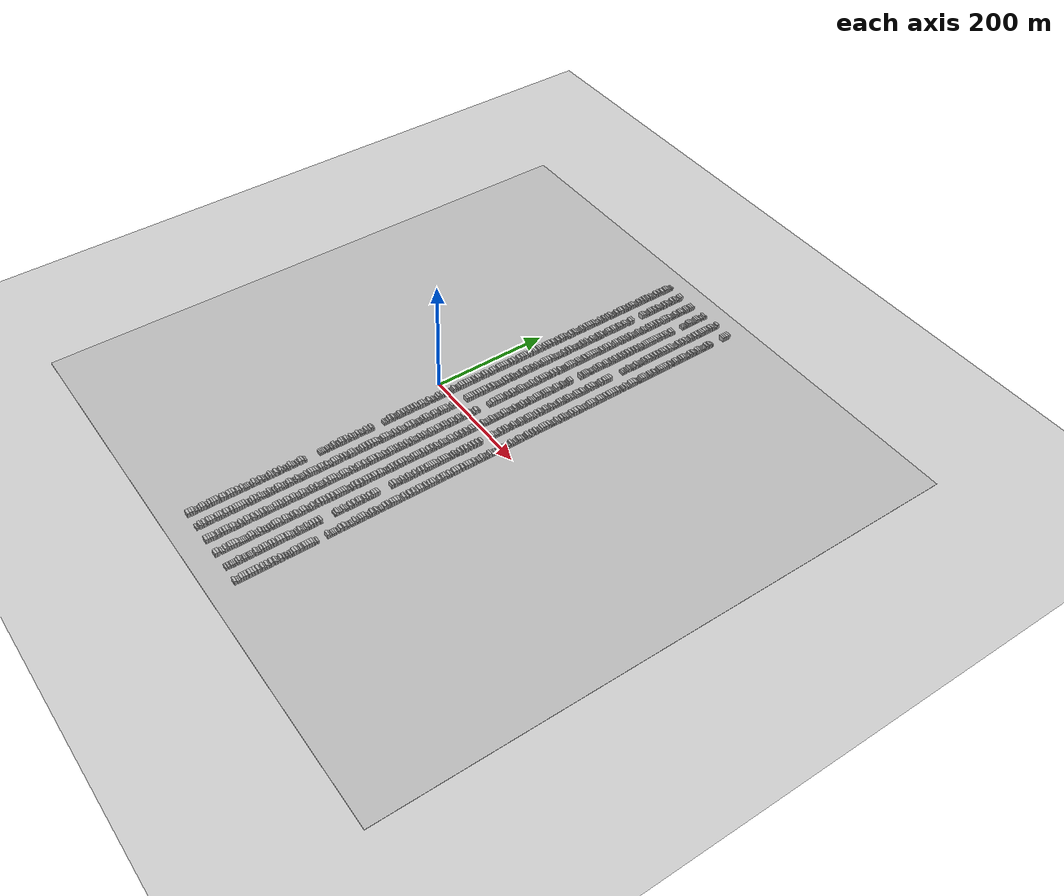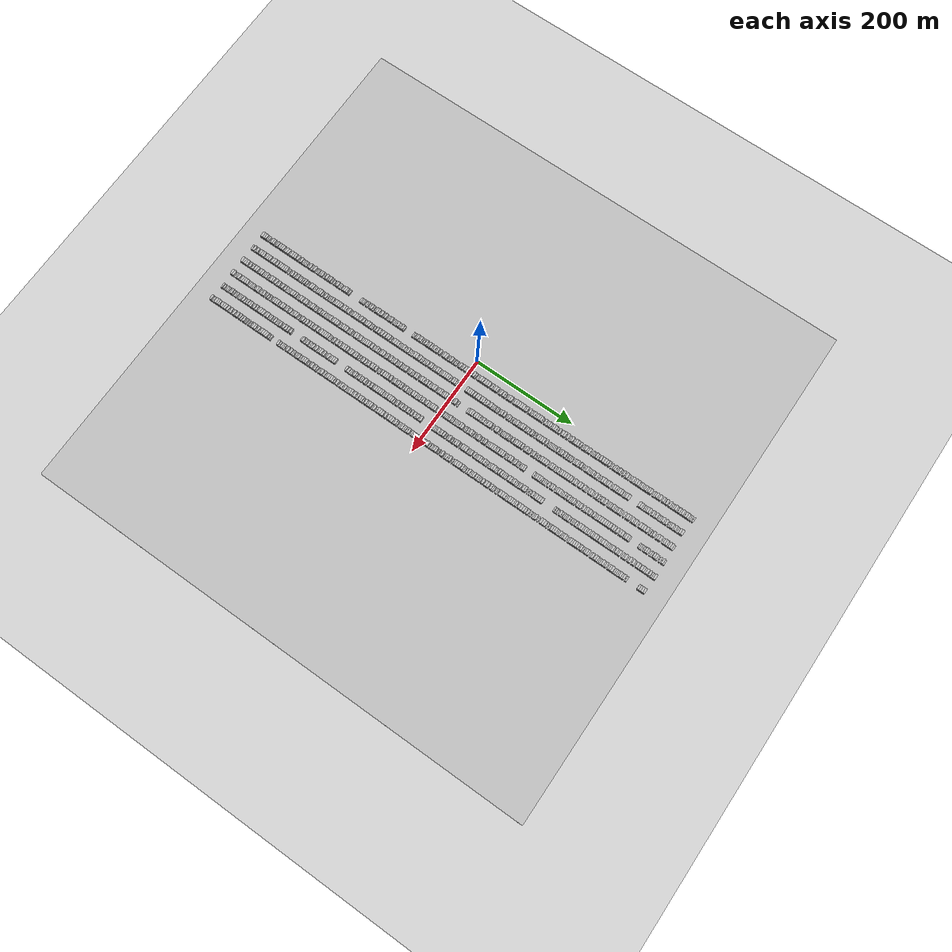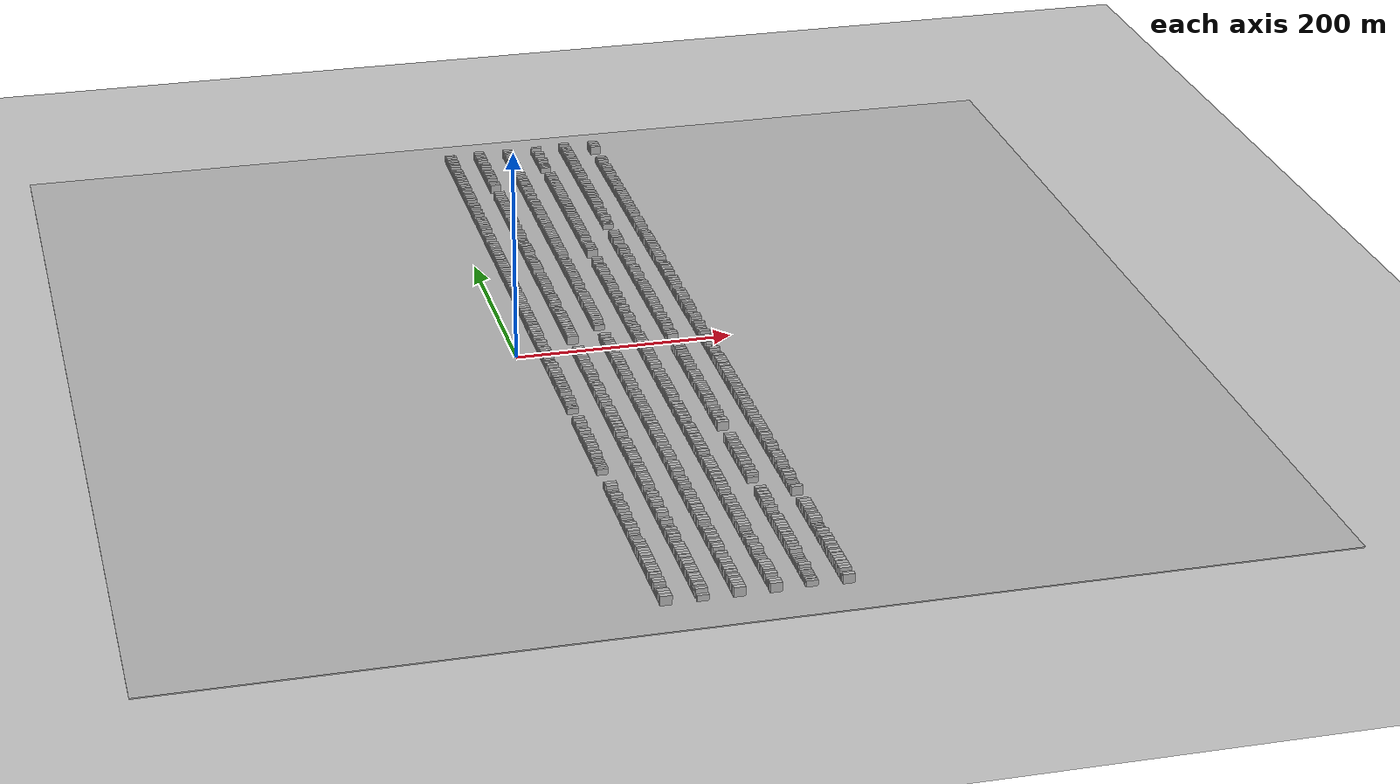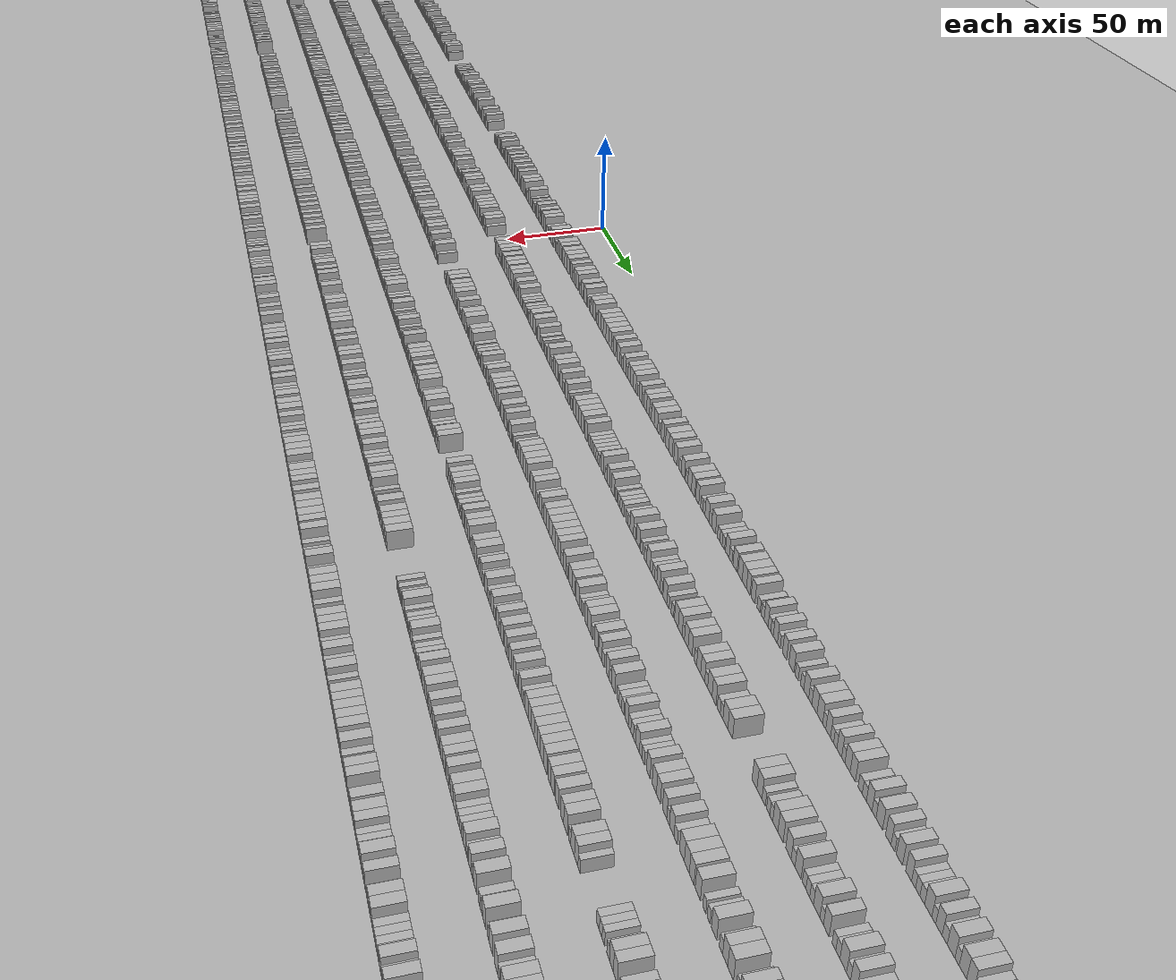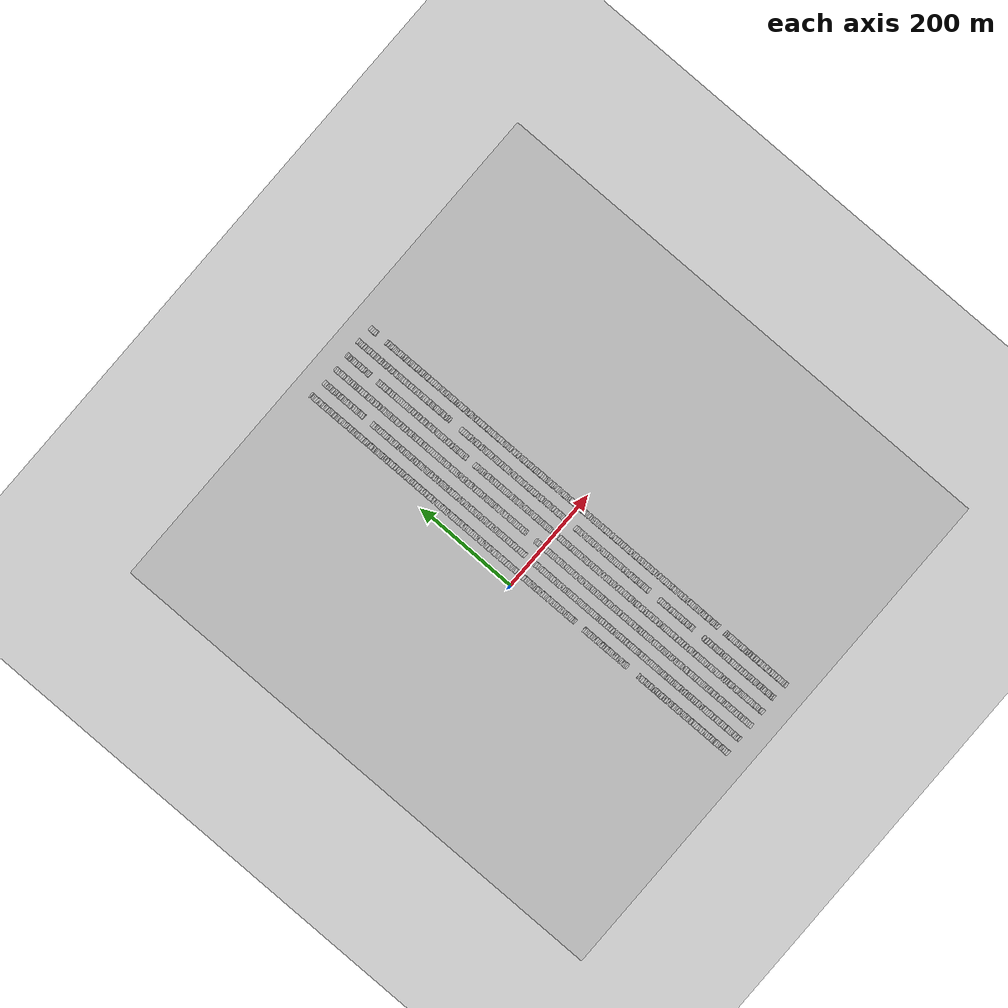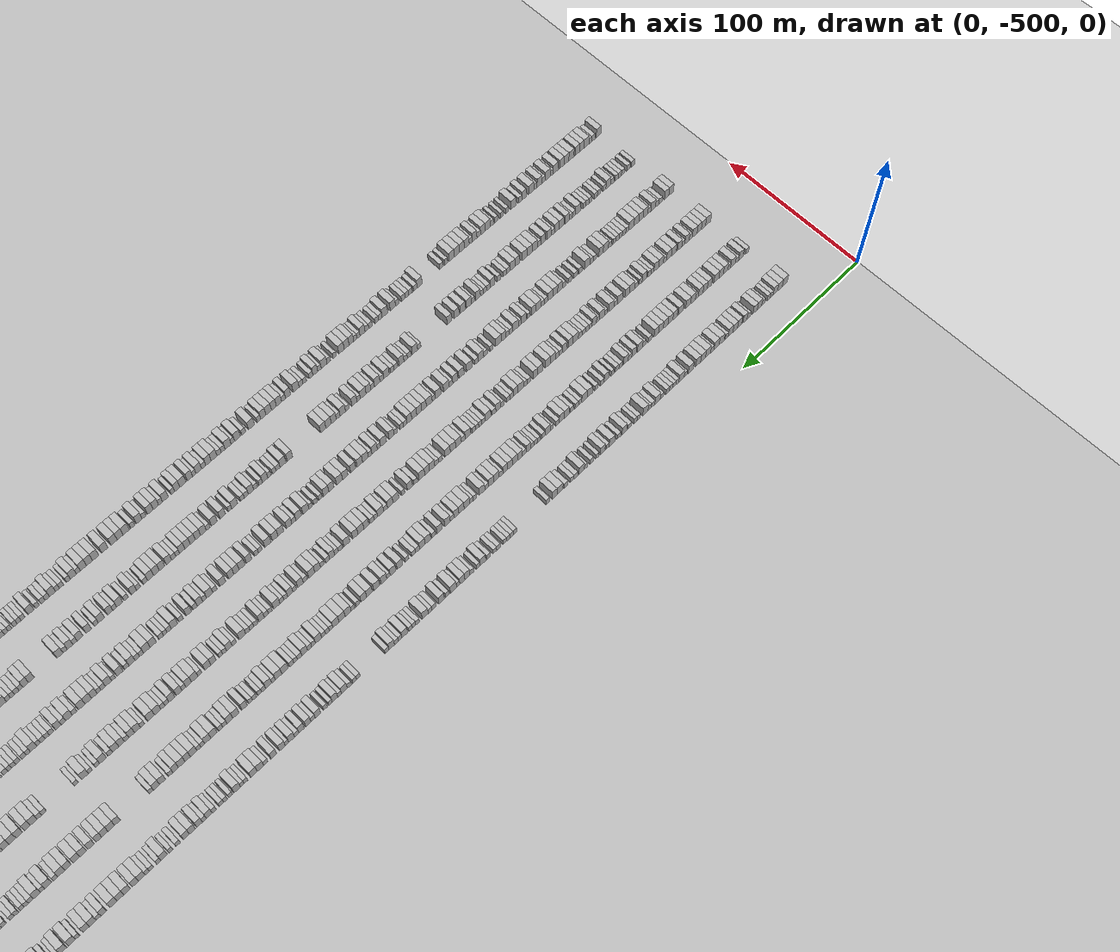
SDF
<sdf version="1.6">
 <world name="default">
  <scene>
   <sky><clouds><speed>12</speed></clouds></sky>
   <ambient>0.4 0.4 0.4 1</ambient>
   <background>0.7 0.7 0.7 1</background>
   <shadows>1</shadows>
  </scene>
  <gravity>0 0 -9.8066</gravity>
  <magnetic_field>6e-06 2.3e-05 -4.2e-05</magnetic_field>
  <physics default="0" name="default_physics" type="ode">
   <ode>
    <solver>
     <type>quick</type>
     <iters>10</iters>
     <sor>1.0</sor>
     <use_dynamic_moi_rescaling>0</use_dynamic_moi_rescaling>
    </solver>
    <constraints>
     <cfm>0</cfm>
     <erp>0.2</erp>
     <contact_max_correcting_vel>100</contact_max_correcting_vel>
     <contact_surface_layer>0.001</contact_surface_layer>
    </constraints>
   </ode>
   <max_step_size>0.004</max_step_size>
   <real_time_factor>1</real_time_factor>
   <real_time_update_rate>250</real_time_update_rate>
  </physics>
  <light name="sun" type="directional">
   <pose>0 0 10 0 0 0</pose>
   <diffuse>0.8 0.8 0.8 1</diffuse>
   <specular>0.2 0.2 0.2 1</specular>
   <attenuation>
    <range>1000</range>
    <constant>0.9</constant>
    <linear>0.01</linear>
    <quadratic>0.001</quadratic>
   </attenuation>
   <direction>-0.5 0.1 -0.9</direction>
  </light>
  <include><name>ground_plane_1</name><uri>model://HANNAS_ground_plane</uri></include>
  <include>
   <name>ground_plane_2</name>
   <uri>model://HANNAS_ground_plane</uri>
   <pose>100 0 0  0 0 0</pose>
  </include>
  <model name="building_1">
   <static>1</static>
   <pose>25.0000 -457.7579 0 0.000000 0.000000 0.000000</pose>
   <link name="link">
    <pose>0 0 4.50 0 0 0</pose>
    <collision name="collision"><geometry><box><size>10.0000 4.4843 9.0000</size></box></geometry></collision>
    <visual name="visual">
     <cast_shadows>0</cast_shadows>
     <geometry><box><size>10.0000 4.4843 9.0000</size></box></geometry>
     <material>
      <script>
       <uri>model://HANNAS_wall/materials/scripts</uri>
       <uri>model://HANNAS_wall/materials/textures</uri>
       <name>vrc/HANNAS_wall</name>
      </script>
     </material>
    </visual>
   </link>
  </model>
  <model name="building_2">
   <static>1</static>
   <pose>25.0000 -453.4642 0 0.000000 0.000000 0.000000</pose>
   <link name="link">
    <pose>0 0 4.50 0 0 0</pose>
    <collision name="collision"><geometry><box><size>10.0000 4.1032 9.0000</size></box></geometry></collision>
    <visual name="visual">
     <cast_shadows>0</cast_shadows>
     <geometry><box><size>10.0000 4.1032 9.0000</size></box></geometry>
     <material>
      <script>
       <uri>model://HANNAS_wall/materials/scripts</uri>
       <uri>model://HANNAS_wall/materials/textures</uri>
       <name>vrc/HANNAS_wall</name>
      </script>
     </material>
    </visual>
   </link>
  </model>
  <model name="building_3">
   <static>1</static>
   <pose>25.0000 -449.4047 0 0.000000 0.000000 0.000000</pose>
   <link name="link">
    <pose>0 0 4.50 0 0 0</pose>
    <collision name="collision"><geometry><box><size>10.0000 4.0158 9.0000</size></box></geometry></collision>
    <visual name="visual">
     <cast_shadows>0</cast_shadows>
     <geometry><box><size>10.0000 4.0158 9.0000</size></box></geometry>
     <material>
      <script>
       <uri>model://HANNAS_wall/materials/scripts</uri>
       <uri>model://HANNAS_wall/materials/textures</uri>
       <name>vrc/HANNAS_wall</name>
      </script>
     </material>
    </visual>
   </link>
  </model>
  <model name="building_4">
   <static>1</static>
   <pose>25.0000 -446.1932 0 0.000000 0.000000 0.000000</pose>
   <link name="link">
    <pose>0 0 3.00 0 0 0</pose>
    <collision name="collision"><geometry><box><size>10.0000 2.4072 6.0000</size></box></geometry></collision>
    <visual name="visual">
     <cast_shadows>0</cast_shadows>
     <geometry><box><size>10.0000 2.4072 6.0000</size></box></geometry>
     <material>
      <script>
       <uri>model://HANNAS_wall/materials/scripts</uri>
       <uri>model://HANNAS_wall/materials/textures</uri>
       <name>vrc/HANNAS_wall</name>
      </script>
     </material>
    </visual>
   </link>
  </model>
  <model name="building_5">
   <static>1</static>
   <pose>25.0000 -443.6745 0 0.000000 0.000000 0.000000</pose>
   <link name="link">
    <pose>0 0 3.00 0 0 0</pose>
    <collision name="collision"><geometry><box><size>10.0000 2.6302 6.0000</size></box></geometry></collision>
    <visual name="visual">
     <cast_shadows>0</cast_shadows>
     <geometry><box><size>10.0000 2.6302 6.0000</size></box></geometry>
     <material>
      <script>
       <uri>model://HANNAS_wall/materials/scripts</uri>
       <uri>model://HANNAS_wall/materials/textures</uri>
       <name>vrc/HANNAS_wall</name>
      </script>
     </material>
    </visual>
   </link>
  </model>
  <model name="building_6">
   <static>1</static>
   <pose>25.0000 -438.8944 0 0.000000 0.000000 0.000000</pose>
   <link name="link">
    <pose>0 0 3.00 0 0 0</pose>
    <collision name="collision"><geometry><box><size>10.0000 2.9301 6.0000</size></box></geometry></collision>
    <visual name="visual">
     <cast_shadows>0</cast_shadows>
     <geometry><box><size>10.0000 2.9301 6.0000</size></box></geometry>
     <material>
      <script>
       <uri>model://HANNAS_wall/materials/scripts</uri>
       <uri>model://HANNAS_wall/materials/textures</uri>
       <name>vrc/HANNAS_wall</name>
      </script>
     </material>
    </visual>
   </link>
  </model>
  <model name="building_7">
   <static>1</static>
   <pose>25.0000 -435.5347 0 0.000000 0.000000 0.000000</pose>
   <link name="link">
    <pose>0 0 4.50 0 0 0</pose>
    <collision name="collision"><geometry><box><size>10.0000 3.7892 9.0000</size></box></geometry></collision>
    <visual name="visual">
     <cast_shadows>0</cast_shadows>
     <geometry><box><size>10.0000 3.7892 9.0000</size></box></geometry>
     <material>
      <script>
       <uri>model://HANNAS_wall/materials/scripts</uri>
       <uri>model://HANNAS_wall/materials/textures</uri>
       <name>vrc/HANNAS_wall</name>
      </script>
     </material>
    </visual>
   </link>
  </model>
  <model name="building_8">
   <static>1</static>
   <pose>25.0000 -431.7124 0 0.000000 0.000000 0.000000</pose>
   <link name="link">
    <pose>0 0 4.50 0 0 0</pose>
    <collision name="collision"><geometry><box><size>10.0000 3.8554 9.0000</size></box></geometry></collision>
    <visual name="visual">
     <cast_shadows>0</cast_shadows>
     <geometry><box><size>10.0000 3.8554 9.0000</size></box></geometry>
     <material>
      <script>
       <uri>model://HANNAS_wall/materials/scripts</uri>
       <uri>model://HANNAS_wall/materials/textures</uri>
       <name>vrc/HANNAS_wall</name>
      </script>
     </material>
    </visual>
   </link>
  </model>
  <model name="building_9">
   <static>1</static>
   <pose>25.0000 -426.2858 0 0.000000 0.000000 0.000000</pose>
   <link name="link">
    <pose>0 0 3.00 0 0 0</pose>
    <collision name="collision"><geometry><box><size>10.0000 2.9977 6.0000</size></box></geometry></collision>
    <visual name="visual">
     <cast_shadows>0</cast_shadows>
     <geometry><box><size>10.0000 2.9977 6.0000</size></box></geometry>
     <material>
      <script>
       <uri>model://HANNAS_wall/materials/scripts</uri>
       <uri>model://HANNAS_wall/materials/textures</uri>
       <name>vrc/HANNAS_wall</name>
      </script>
     </material>
    </visual>
   </link>
  </model>
  <model name="building_10">
   <static>1</static>
   <pose>25.0000 -422.9470 0 0.000000 0.000000 0.000000</pose>
   <link name="link">
    <pose>0 0 4.50 0 0 0</pose>
    <collision name="collision"><geometry><box><size>10.0000 3.6799 9.0000</size></box></geometry></collision>
    <visual name="visual">
     <cast_shadows>0</cast_shadows>
     <geometry><box><size>10.0000 3.6799 9.0000</size></box></geometry>
     <material>
      <script>
       <uri>model://HANNAS_wall/materials/scripts</uri>
       <uri>model://HANNAS_wall/materials/textures</uri>
       <name>vrc/HANNAS_wall</name>
      </script>
     </material>
    </visual>
   </link>
  </model>
  <model name="building_11">
   <static>1</static>
   <pose>25.0000 -418.2934 0 0.000000 0.000000 0.000000</pose>
   <link name="link">
    <pose>0 0 4.50 0 0 0</pose>
    <collision name="collision"><geometry><box><size>10.0000 3.6275 9.0000</size></box></geometry></collision>
    <visual name="visual">
     <cast_shadows>0</cast_shadows>
     <geometry><box><size>10.0000 3.6275 9.0000</size></box></geometry>
     <material>
      <script>
       <uri>model://HANNAS_wall/materials/scripts</uri>
       <uri>model://HANNAS_wall/materials/textures</uri>
       <name>vrc/HANNAS_wall</name>
      </script>
     </material>
    </visual>
   </link>
  </model>
  <model name="building_12">
   <static>1</static>
   <pose>25.0000 -414.5491 0 0.000000 0.000000 0.000000</pose>
   <link name="link">
    <pose>0 0 4.50 0 0 0</pose>
    <collision name="collision"><geometry><box><size>10.0000 3.8611 9.0000</size></box></geometry></collision>
    <visual name="visual">
     <cast_shadows>0</cast_shadows>
     <geometry><box><size>10.0000 3.8611 9.0000</size></box></geometry>
     <material>
      <script>
       <uri>model://HANNAS_wall/materials/scripts</uri>
       <uri>model://HANNAS_wall/materials/textures</uri>
       <name>vrc/HANNAS_wall</name>
      </script>
     </material>
    </visual>
   </link>
  </model>
  <model name="building_13">
   <static>1</static>
   <pose>25.0000 -410.5557 0 0.000000 0.000000 0.000000</pose>
   <link name="link">
    <pose>0 0 4.50 0 0 0</pose>
    <collision name="collision"><geometry><box><size>10.0000 4.1257 9.0000</size></box></geometry></collision>
    <visual name="visual">
     <cast_shadows>0</cast_shadows>
     <geometry><box><size>10.0000 4.1257 9.0000</size></box></geometry>
     <material>
      <script>
       <uri>model://HANNAS_wall/materials/scripts</uri>
       <uri>model://HANNAS_wall/materials/textures</uri>
       <name>vrc/HANNAS_wall</name>
      </script>
     </material>
    </visual>
   </link>
  </model>
  <model name="building_14">
   <static>1</static>
   <pose>25.0000 -407.2858 0 0.000000 0.000000 0.000000</pose>
   <link name="link">
    <pose>0 0 3.00 0 0 0</pose>
    <collision name="collision"><geometry><box><size>10.0000 2.4140 6.0000</size></box></geometry></collision>
    <visual name="visual">
     <cast_shadows>0</cast_shadows>
     <geometry><box><size>10.0000 2.4140 6.0000</size></box></geometry>
     <material>
      <script>
       <uri>model://HANNAS_wall/materials/scripts</uri>
       <uri>model://HANNAS_wall/materials/textures</uri>
       <name>vrc/HANNAS_wall</name>
      </script>
     </material>
    </visual>
   </link>
  </model>
  <model name="building_15">
   <static>1</static>
   <pose>25.0000 -402.8836 0 0.000000 0.000000 0.000000</pose>
   <link name="link">
    <pose>0 0 4.50 0 0 0</pose>
    <collision name="collision"><geometry><box><size>10.0000 4.3905 9.0000</size></box></geometry></collision>
    <visual name="visual">
     <cast_shadows>0</cast_shadows>
     <geometry><box><size>10.0000 4.3905 9.0000</size></box></geometry>
     <material>
      <script>
       <uri>model://HANNAS_wall/materials/scripts</uri>
       <uri>model://HANNAS_wall/materials/textures</uri>
       <name>vrc/HANNAS_wall</name>
      </script>
     </material>
    </visual>
   </link>
  </model>
  <model name="building_16">
   <static>1</static>
   <pose>25.0000 -398.5173 0 0.000000 0.000000 0.000000</pose>
   <link name="link">
    <pose>0 0 4.50 0 0 0</pose>
    <collision name="collision"><geometry><box><size>10.0000 4.3420 9.0000</size></box></geometry></collision>
    <visual name="visual">
     <cast_shadows>0</cast_shadows>
     <geometry><box><size>10.0000 4.3420 9.0000</size></box></geometry>
     <material>
      <script>
       <uri>model://HANNAS_wall/materials/scripts</uri>
       <uri>model://HANNAS_wall/materials/textures</uri>
       <name>vrc/HANNAS_wall</name>
      </script>
     </material>
    </visual>
   </link>
  </model>
  <model name="building_17">
   <static>1</static>
   <pose>25.0000 -394.9663 0 0.000000 0.000000 0.000000</pose>
   <link name="link">
    <pose>0 0 3.00 0 0 0</pose>
    <collision name="collision"><geometry><box><size>10.0000 2.7601 6.0000</size></box></geometry></collision>
    <visual name="visual">
     <cast_shadows>0</cast_shadows>
     <geometry><box><size>10.0000 2.7601 6.0000</size></box></geometry>
     <material>
      <script>
       <uri>model://HANNAS_wall/materials/scripts</uri>
       <uri>model://HANNAS_wall/materials/textures</uri>
       <name>vrc/HANNAS_wall</name>
      </script>
     </material>
    </visual>
   </link>
  </model>
  <model name="building_18">
   <static>1</static>
   <pose>25.0000 -391.4128 0 0.000000 0.000000 0.000000</pose>
   <link name="link">
    <pose>0 0 4.50 0 0 0</pose>
    <collision name="collision"><geometry><box><size>10.0000 4.3470 9.0000</size></box></geometry></collision>
    <visual name="visual">
     <cast_shadows>0</cast_shadows>
     <geometry><box><size>10.0000 4.3470 9.0000</size></box></geometry>
     <material>
      <script>
       <uri>model://HANNAS_wall/materials/scripts</uri>
       <uri>model://HANNAS_wall/materials/textures</uri>
       <name>vrc/HANNAS_wall</name>
      </script>
     </material>
    </visual>
   </link>
  </model>
  <model name="building_19">
   <static>1</static>
   <pose>25.0000 -387.1824 0 0.000000 0.000000 0.000000</pose>
   <link name="link">
    <pose>0 0 4.50 0 0 0</pose>
    <collision name="collision"><geometry><box><size>10.0000 4.1136 9.0000</size></box></geometry></collision>
    <visual name="visual">
     <cast_shadows>0</cast_shadows>
     <geometry><box><size>10.0000 4.1136 9.0000</size></box></geometry>
     <material>
      <script>
       <uri>model://HANNAS_wall/materials/scripts</uri>
       <uri>model://HANNAS_wall/materials/textures</uri>
       <name>vrc/HANNAS_wall</name>
      </script>
     </material>
    </visual>
   </link>
  </model>
  <model name="building_20">
   <static>1</static>
   <pose>25.0000 -383.0420 0 0.000000 0.000000 0.000000</pose>
   <link name="link">
    <pose>0 0 4.50 0 0 0</pose>
    <collision name="collision"><geometry><box><size>10.0000 4.1672 9.0000</size></box></geometry></collision>
    <visual name="visual">
     <cast_shadows>0</cast_shadows>
     <geometry><box><size>10.0000 4.1672 9.0000</size></box></geometry>
     <material>
      <script>
       <uri>model://HANNAS_wall/materials/scripts</uri>
       <uri>model://HANNAS_wall/materials/textures</uri>
       <name>vrc/HANNAS_wall</name>
      </script>
     </material>
    </visual>
   </link>
  </model>
  <model name="building_21">
   <static>1</static>
   <pose>25.0000 -376.8590 0 0.000000 0.000000 0.000000</pose>
   <link name="link">
    <pose>0 0 4.50 0 0 0</pose>
    <collision name="collision"><geometry><box><size>10.0000 4.1989 9.0000</size></box></geometry></collision>
    <visual name="visual">
     <cast_shadows>0</cast_shadows>
     <geometry><box><size>10.0000 4.1989 9.0000</size></box></geometry>
     <material>
      <script>
       <uri>model://HANNAS_wall/materials/scripts</uri>
       <uri>model://HANNAS_wall/materials/textures</uri>
       <name>vrc/HANNAS_wall</name>
      </script>
     </material>
    </visual>
   </link>
  </model>
  <model name="building_22">
   <static>1</static>
   <pose>25.0000 -372.5110 0 0.000000 0.000000 0.000000</pose>
   <link name="link">
    <pose>0 0 3.00 0 0 0</pose>
    <collision name="collision"><geometry><box><size>10.0000 2.4970 6.0000</size></box></geometry></collision>
    <visual name="visual">
     <cast_shadows>0</cast_shadows>
     <geometry><box><size>10.0000 2.4970 6.0000</size></box></geometry>
     <material>
      <script>
       <uri>model://HANNAS_wall/materials/scripts</uri>
       <uri>model://HANNAS_wall/materials/textures</uri>
       <name>vrc/HANNAS_wall</name>
      </script>
     </material>
    </visual>
   </link>
  </model>
  <model name="building_23">
   <static>1</static>
   <pose>25.0000 -369.1126 0 0.000000 0.000000 0.000000</pose>
   <link name="link">
    <pose>0 0 4.50 0 0 0</pose>
    <collision name="collision"><geometry><box><size>10.0000 4.3000 9.0000</size></box></geometry></collision>
    <visual name="visual">
     <cast_shadows>0</cast_shadows>
     <geometry><box><size>10.0000 4.3000 9.0000</size></box></geometry>
     <material>
      <script>
       <uri>model://HANNAS_wall/materials/scripts</uri>
       <uri>model://HANNAS_wall/materials/textures</uri>
       <name>vrc/HANNAS_wall</name>
      </script>
     </material>
    </visual>
   </link>
  </model>
  <model name="building_24">
   <static>1</static>
   <pose>25.0000 -365.6588 0 0.000000 0.000000 0.000000</pose>
   <link name="link">
    <pose>0 0 3.00 0 0 0</pose>
    <collision name="collision"><geometry><box><size>10.0000 2.6075 6.0000</size></box></geometry></collision>
    <visual name="visual">
     <cast_shadows>0</cast_shadows>
     <geometry><box><size>10.0000 2.6075 6.0000</size></box></geometry>
     <material>
      <script>
       <uri>model://HANNAS_wall/materials/scripts</uri>
       <uri>model://HANNAS_wall/materials/textures</uri>
       <name>vrc/HANNAS_wall</name>
      </script>
     </material>
    </visual>
   </link>
  </model>
  <model name="building_25">
   <static>1</static>
   <pose>25.0000 -363.0989 0 0.000000 0.000000 0.000000</pose>
   <link name="link">
    <pose>0 0 3.00 0 0 0</pose>
    <collision name="collision"><geometry><box><size>10.0000 2.5124 6.0000</size></box></geometry></collision>
    <visual name="visual">
     <cast_shadows>0</cast_shadows>
     <geometry><box><size>10.0000 2.5124 6.0000</size></box></geometry>
     <material>
      <script>
       <uri>model://HANNAS_wall/materials/scripts</uri>
       <uri>model://HANNAS_wall/materials/textures</uri>
       <name>vrc/HANNAS_wall</name>
      </script>
     </material>
    </visual>
   </link>
  </model>
  <model name="building_26">
   <static>1</static>
   <pose>25.0000 -360.4724 0 0.000000 0.000000 0.000000</pose>
   <link name="link">
    <pose>0 0 3.00 0 0 0</pose>
    <collision name="collision"><geometry><box><size>10.0000 2.7406 6.0000</size></box></geometry></collision>
    <visual name="visual">
     <cast_shadows>0</cast_shadows>
     <geometry><box><size>10.0000 2.7406 6.0000</size></box></geometry>
     <material>
      <script>
       <uri>model://HANNAS_wall/materials/scripts</uri>
       <uri>model://HANNAS_wall/materials/textures</uri>
       <name>vrc/HANNAS_wall</name>
      </script>
     </material>
    </visual>
   </link>
  </model>
  <model name="building_27">
   <static>1</static>
   <pose>25.0000 -357.6476 0 0.000000 0.000000 0.000000</pose>
   <link name="link">
    <pose>0 0 3.00 0 0 0</pose>
    <collision name="collision"><geometry><box><size>10.0000 2.9092 6.0000</size></box></geometry></collision>
    <visual name="visual">
     <cast_shadows>0</cast_shadows>
     <geometry><box><size>10.0000 2.9092 6.0000</size></box></geometry>
     <material>
      <script>
       <uri>model://HANNAS_wall/materials/scripts</uri>
       <uri>model://HANNAS_wall/materials/textures</uri>
       <name>vrc/HANNAS_wall</name>
      </script>
     </material>
    </visual>
   </link>
  </model>
  <model name="building_28">
   <static>1</static>
   <pose>25.0000 -352.8219 0 0.000000 0.000000 0.000000</pose>
   <link name="link">
    <pose>0 0 3.00 0 0 0</pose>
    <collision name="collision"><geometry><box><size>10.0000 2.7422 6.0000</size></box></geometry></collision>
    <visual name="visual">
     <cast_shadows>0</cast_shadows>
     <geometry><box><size>10.0000 2.7422 6.0000</size></box></geometry>
     <material>
      <script>
       <uri>model://HANNAS_wall/materials/scripts</uri>
       <uri>model://HANNAS_wall/materials/textures</uri>
       <name>vrc/HANNAS_wall</name>
      </script>
     </material>
    </visual>
   </link>
  </model>
  <model name="building_29">
   <static>1</static>
   <pose>25.0000 -349.2407 0 0.000000 0.000000 0.000000</pose>
   <link name="link">
    <pose>0 0 4.50 0 0 0</pose>
    <collision name="collision"><geometry><box><size>10.0000 4.4202 9.0000</size></box></geometry></collision>
    <visual name="visual">
     <cast_shadows>0</cast_shadows>
     <geometry><box><size>10.0000 4.4202 9.0000</size></box></geometry>
     <material>
      <script>
       <uri>model://HANNAS_wall/materials/scripts</uri>
       <uri>model://HANNAS_wall/materials/textures</uri>
       <name>vrc/HANNAS_wall</name>
      </script>
     </material>
    </visual>
   </link>
  </model>
  <model name="building_30">
   <static>1</static>
   <pose>25.0000 -345.5787 0 0.000000 0.000000 0.000000</pose>
   <link name="link">
    <pose>0 0 3.00 0 0 0</pose>
    <collision name="collision"><geometry><box><size>10.0000 2.9037 6.0000</size></box></geometry></collision>
    <visual name="visual">
     <cast_shadows>0</cast_shadows>
     <geometry><box><size>10.0000 2.9037 6.0000</size></box></geometry>
     <material>
      <script>
       <uri>model://HANNAS_wall/materials/scripts</uri>
       <uri>model://HANNAS_wall/materials/textures</uri>
       <name>vrc/HANNAS_wall</name>
      </script>
     </material>
    </visual>
   </link>
  </model>
  <model name="building_31">
   <static>1</static>
   <pose>25.0000 -342.7855 0 0.000000 0.000000 0.000000</pose>
   <link name="link">
    <pose>0 0 3.00 0 0 0</pose>
    <collision name="collision"><geometry><box><size>10.0000 2.6828 6.0000</size></box></geometry></collision>
    <visual name="visual">
     <cast_shadows>0</cast_shadows>
     <geometry><box><size>10.0000 2.6828 6.0000</size></box></geometry>
     <material>
      <script>
       <uri>model://HANNAS_wall/materials/scripts</uri>
       <uri>model://HANNAS_wall/materials/textures</uri>
       <name>vrc/HANNAS_wall</name>
      </script>
     </material>
    </visual>
   </link>
  </model>
  <model name="building_32">
   <static>1</static>
   <pose>25.0000 -339.2636 0 0.000000 0.000000 0.000000</pose>
   <link name="link">
    <pose>0 0 4.50 0 0 0</pose>
    <collision name="collision"><geometry><box><size>10.0000 4.3609 9.0000</size></box></geometry></collision>
    <visual name="visual">
     <cast_shadows>0</cast_shadows>
     <geometry><box><size>10.0000 4.3609 9.0000</size></box></geometry>
     <material>
      <script>
       <uri>model://HANNAS_wall/materials/scripts</uri>
       <uri>model://HANNAS_wall/materials/textures</uri>
       <name>vrc/HANNAS_wall</name>
      </script>
     </material>
    </visual>
   </link>
  </model>
  <model name="building_33">
   <static>1</static>
   <pose>25.0000 -333.7542 0 0.000000 0.000000 0.000000</pose>
   <link name="link">
    <pose>0 0 3.00 0 0 0</pose>
    <collision name="collision"><geometry><box><size>10.0000 2.6578 6.0000</size></box></geometry></collision>
    <visual name="visual">
     <cast_shadows>0</cast_shadows>
     <geometry><box><size>10.0000 2.6578 6.0000</size></box></geometry>
     <material>
      <script>
       <uri>model://HANNAS_wall/materials/scripts</uri>
       <uri>model://HANNAS_wall/materials/textures</uri>
       <name>vrc/HANNAS_wall</name>
      </script>
     </material>
    </visual>
   </link>
  </model>
  <model name="building_34">
   <static>1</static>
   <pose>25.0000 -331.2030 0 0.000000 0.000000 0.000000</pose>
   <link name="link">
    <pose>0 0 3.00 0 0 0</pose>
    <collision name="collision"><geometry><box><size>10.0000 2.4448 6.0000</size></box></geometry></collision>
    <visual name="visual">
     <cast_shadows>0</cast_shadows>
     <geometry><box><size>10.0000 2.4448 6.0000</size></box></geometry>
     <material>
      <script>
       <uri>model://HANNAS_wall/materials/scripts</uri>
       <uri>model://HANNAS_wall/materials/textures</uri>
       <name>vrc/HANNAS_wall</name>
      </script>
     </material>
    </visual>
   </link>
  </model>
  <model name="building_35">
   <static>1</static>
   <pose>25.0000 -326.5201 0 0.000000 0.000000 0.000000</pose>
   <link name="link">
    <pose>0 0 3.00 0 0 0</pose>
    <collision name="collision"><geometry><box><size>10.0000 2.9210 6.0000</size></box></geometry></collision>
    <visual name="visual">
     <cast_shadows>0</cast_shadows>
     <geometry><box><size>10.0000 2.9210 6.0000</size></box></geometry>
     <material>
      <script>
       <uri>model://HANNAS_wall/materials/scripts</uri>
       <uri>model://HANNAS_wall/materials/textures</uri>
       <name>vrc/HANNAS_wall</name>
      </script>
     </material>
    </visual>
   </link>
  </model>
  <model name="building_36">
   <static>1</static>
   <pose>25.0000 -322.1292 0 0.000000 0.000000 0.000000</pose>
   <link name="link">
    <pose>0 0 4.50 0 0 0</pose>
    <collision name="collision"><geometry><box><size>10.0000 3.8609 9.0000</size></box></geometry></collision>
    <visual name="visual">
     <cast_shadows>0</cast_shadows>
     <geometry><box><size>10.0000 3.8609 9.0000</size></box></geometry>
     <material>
      <script>
       <uri>model://HANNAS_wall/materials/scripts</uri>
       <uri>model://HANNAS_wall/materials/textures</uri>
       <name>vrc/HANNAS_wall</name>
      </script>
     </material>
    </visual>
   </link>
  </model>
  <model name="building_37">
   <static>1</static>
   <pose>25.0000 -317.7645 0 0.000000 0.000000 0.000000</pose>
   <link name="link">
    <pose>0 0 3.00 0 0 0</pose>
    <collision name="collision"><geometry><box><size>10.0000 2.8685 6.0000</size></box></geometry></collision>
    <visual name="visual">
     <cast_shadows>0</cast_shadows>
     <geometry><box><size>10.0000 2.8685 6.0000</size></box></geometry>
     <material>
      <script>
       <uri>model://HANNAS_wall/materials/scripts</uri>
       <uri>model://HANNAS_wall/materials/textures</uri>
       <name>vrc/HANNAS_wall</name>
      </script>
     </material>
    </visual>
   </link>
  </model>
  <model name="building_38">
   <static>1</static>
   <pose>25.0000 -312.1129 0 0.000000 0.000000 0.000000</pose>
   <link name="link">
    <pose>0 0 4.50 0 0 0</pose>
    <collision name="collision"><geometry><box><size>10.0000 4.4347 9.0000</size></box></geometry></collision>
    <visual name="visual">
     <cast_shadows>0</cast_shadows>
     <geometry><box><size>10.0000 4.4347 9.0000</size></box></geometry>
     <material>
      <script>
       <uri>model://HANNAS_wall/materials/scripts</uri>
       <uri>model://HANNAS_wall/materials/textures</uri>
       <name>vrc/HANNAS_wall</name>
      </script>
     </material>
    </visual>
   </link>
  </model>
  <model name="building_39">
   <static>1</static>
   <pose>25.0000 -308.6910 0 0.000000 0.000000 0.000000</pose>
   <link name="link">
    <pose>0 0 3.00 0 0 0</pose>
    <collision name="collision"><geometry><box><size>10.0000 2.4089 6.0000</size></box></geometry></collision>
    <visual name="visual">
     <cast_shadows>0</cast_shadows>
     <geometry><box><size>10.0000 2.4089 6.0000</size></box></geometry>
     <material>
      <script>
       <uri>model://HANNAS_wall/materials/scripts</uri>
       <uri>model://HANNAS_wall/materials/textures</uri>
       <name>vrc/HANNAS_wall</name>
      </script>
     </material>
    </visual>
   </link>
  </model>
  <model name="building_40">
   <static>1</static>
   <pose>25.0000 -304.5818 0 0.000000 0.000000 0.000000</pose>
   <link name="link">
    <pose>0 0 4.50 0 0 0</pose>
    <collision name="collision"><geometry><box><size>10.0000 3.8096 9.0000</size></box></geometry></collision>
    <visual name="visual">
     <cast_shadows>0</cast_shadows>
     <geometry><box><size>10.0000 3.8096 9.0000</size></box></geometry>
     <material>
      <script>
       <uri>model://HANNAS_wall/materials/scripts</uri>
       <uri>model://HANNAS_wall/materials/textures</uri>
       <name>vrc/HANNAS_wall</name>
      </script>
     </material>
    </visual>
   </link>
  </model>
  <model name="building_41">
   <static>1</static>
   <pose>25.0000 -300.4751 0 0.000000 0.000000 0.000000</pose>
   <link name="link">
    <pose>0 0 3.00 0 0 0</pose>
    <collision name="collision"><geometry><box><size>10.0000 2.4038 6.0000</size></box></geometry></collision>
    <visual name="visual">
     <cast_shadows>0</cast_shadows>
     <geometry><box><size>10.0000 2.4038 6.0000</size></box></geometry>
     <material>
      <script>
       <uri>model://HANNAS_wall/materials/scripts</uri>
       <uri>model://HANNAS_wall/materials/textures</uri>
       <name>vrc/HANNAS_wall</name>
      </script>
     </material>
    </visual>
   </link>
  </model>
  <model name="building_42">
   <static>1</static>
   <pose>25.0000 -295.9057 0 0.000000 0.000000 0.000000</pose>
   <link name="link">
    <pose>0 0 3.00 0 0 0</pose>
    <collision name="collision"><geometry><box><size>10.0000 2.7350 6.0000</size></box></geometry></collision>
    <visual name="visual">
     <cast_shadows>0</cast_shadows>
     <geometry><box><size>10.0000 2.7350 6.0000</size></box></geometry>
     <material>
      <script>
       <uri>model://HANNAS_wall/materials/scripts</uri>
       <uri>model://HANNAS_wall/materials/textures</uri>
       <name>vrc/HANNAS_wall</name>
      </script>
     </material>
    </visual>
   </link>
  </model>
  <model name="building_43">
   <static>1</static>
   <pose>25.0000 -291.2968 0 0.000000 0.000000 0.000000</pose>
   <link name="link">
    <pose>0 0 3.00 0 0 0</pose>
    <collision name="collision"><geometry><box><size>10.0000 2.4828 6.0000</size></box></geometry></collision>
    <visual name="visual">
     <cast_shadows>0</cast_shadows>
     <geometry><box><size>10.0000 2.4828 6.0000</size></box></geometry>
     <material>
      <script>
       <uri>model://HANNAS_wall/materials/scripts</uri>
       <uri>model://HANNAS_wall/materials/textures</uri>
       <name>vrc/HANNAS_wall</name>
      </script>
     </material>
    </visual>
   </link>
  </model>
  <model name="building_44">
   <static>1</static>
   <pose>25.0000 -287.9706 0 0.000000 0.000000 0.000000</pose>
   <link name="link">
    <pose>0 0 4.50 0 0 0</pose>
    <collision name="collision"><geometry><box><size>10.0000 4.1696 9.0000</size></box></geometry></collision>
    <visual name="visual">
     <cast_shadows>0</cast_shadows>
     <geometry><box><size>10.0000 4.1696 9.0000</size></box></geometry>
     <material>
      <script>
       <uri>model://HANNAS_wall/materials/scripts</uri>
       <uri>model://HANNAS_wall/materials/textures</uri>
       <name>vrc/HANNAS_wall</name>
      </script>
     </material>
    </visual>
   </link>
  </model>
  <model name="building_45">
   <static>1</static>
   <pose>25.0000 -283.3919 0 0.000000 0.000000 0.000000</pose>
   <link name="link">
    <pose>0 0 3.00 0 0 0</pose>
    <collision name="collision"><geometry><box><size>10.0000 2.9878 6.0000</size></box></geometry></collision>
    <visual name="visual">
     <cast_shadows>0</cast_shadows>
     <geometry><box><size>10.0000 2.9878 6.0000</size></box></geometry>
     <material>
      <script>
       <uri>model://HANNAS_wall/materials/scripts</uri>
       <uri>model://HANNAS_wall/materials/textures</uri>
       <name>vrc/HANNAS_wall</name>
      </script>
     </material>
    </visual>
   </link>
  </model>
  <model name="building_46">
   <static>1</static>
   <pose>25.0000 -280.5077 0 0.000000 0.000000 0.000000</pose>
   <link name="link">
    <pose>0 0 3.00 0 0 0</pose>
    <collision name="collision"><geometry><box><size>10.0000 2.7807 6.0000</size></box></geometry></collision>
    <visual name="visual">
     <cast_shadows>0</cast_shadows>
     <geometry><box><size>10.0000 2.7807 6.0000</size></box></geometry>
     <material>
      <script>
       <uri>model://HANNAS_wall/materials/scripts</uri>
       <uri>model://HANNAS_wall/materials/textures</uri>
       <name>vrc/HANNAS_wall</name>
      </script>
     </material>
    </visual>
   </link>
  </model>
  <model name="building_47">
   <static>1</static>
   <pose>25.0000 -275.6403 0 0.000000 0.000000 0.000000</pose>
   <link name="link">
    <pose>0 0 3.00 0 0 0</pose>
    <collision name="collision"><geometry><box><size>10.0000 2.9541 6.0000</size></box></geometry></collision>
    <visual name="visual">
     <cast_shadows>0</cast_shadows>
     <geometry><box><size>10.0000 2.9541 6.0000</size></box></geometry>
     <material>
      <script>
       <uri>model://HANNAS_wall/materials/scripts</uri>
       <uri>model://HANNAS_wall/materials/textures</uri>
       <name>vrc/HANNAS_wall</name>
      </script>
     </material>
    </visual>
   </link>
  </model>
  <model name="building_48">
   <static>1</static>
   <pose>25.0000 -270.9553 0 0.000000 0.000000 0.000000</pose>
   <link name="link">
    <pose>0 0 4.50 0 0 0</pose>
    <collision name="collision"><geometry><box><size>10.0000 4.4160 9.0000</size></box></geometry></collision>
    <visual name="visual">
     <cast_shadows>0</cast_shadows>
     <geometry><box><size>10.0000 4.4160 9.0000</size></box></geometry>
     <material>
      <script>
       <uri>model://HANNAS_wall/materials/scripts</uri>
       <uri>model://HANNAS_wall/materials/textures</uri>
       <name>vrc/HANNAS_wall</name>
      </script>
     </material>
    </visual>
   </link>
  </model>
  <model name="building_49">
   <static>1</static>
   <pose>25.0000 -266.8858 0 0.000000 0.000000 0.000000</pose>
   <link name="link">
    <pose>0 0 4.50 0 0 0</pose>
    <collision name="collision"><geometry><box><size>10.0000 3.7229 9.0000</size></box></geometry></collision>
    <visual name="visual">
     <cast_shadows>0</cast_shadows>
     <geometry><box><size>10.0000 3.7229 9.0000</size></box></geometry>
     <material>
      <script>
       <uri>model://HANNAS_wall/materials/scripts</uri>
       <uri>model://HANNAS_wall/materials/textures</uri>
       <name>vrc/HANNAS_wall</name>
      </script>
     </material>
    </visual>
   </link>
  </model>
  <model name="building_50">
   <static>1</static>
   <pose>25.0000 -261.6594 0 0.000000 0.000000 0.000000</pose>
   <link name="link">
    <pose>0 0 3.00 0 0 0</pose>
    <collision name="collision"><geometry><box><size>10.0000 2.7300 6.0000</size></box></geometry></collision>
    <visual name="visual">
     <cast_shadows>0</cast_shadows>
     <geometry><box><size>10.0000 2.7300 6.0000</size></box></geometry>
     <material>
      <script>
       <uri>model://HANNAS_wall/materials/scripts</uri>
       <uri>model://HANNAS_wall/materials/textures</uri>
       <name>vrc/HANNAS_wall</name>
      </script>
     </material>
    </visual>
   </link>
  </model>
  <model name="building_51">
   <static>1</static>
   <pose>25.0000 -236.2461 0 0.000000 0.000000 0.000000</pose>
   <link name="link">
    <pose>0 0 3.00 0 0 0</pose>
    <collision name="collision"><geometry><box><size>10.0000 2.6988 6.0000</size></box></geometry></collision>
    <visual name="visual">
     <cast_shadows>0</cast_shadows>
     <geometry><box><size>10.0000 2.6988 6.0000</size></box></geometry>
     <material>
      <script>
       <uri>model://HANNAS_wall/materials/scripts</uri>
       <uri>model://HANNAS_wall/materials/textures</uri>
       <name>vrc/HANNAS_wall</name>
      </script>
     </material>
    </visual>
   </link>
  </model>
  <model name="building_52">
   <static>1</static>
   <pose>25.0000 -233.5793 0 0.000000 0.000000 0.000000</pose>
   <link name="link">
    <pose>0 0 3.00 0 0 0</pose>
    <collision name="collision"><geometry><box><size>10.0000 2.6348 6.0000</size></box></geometry></collision>
    <visual name="visual">
     <cast_shadows>0</cast_shadows>
     <geometry><box><size>10.0000 2.6348 6.0000</size></box></geometry>
     <material>
      <script>
       <uri>model://HANNAS_wall/materials/scripts</uri>
       <uri>model://HANNAS_wall/materials/textures</uri>
       <name>vrc/HANNAS_wall</name>
      </script>
     </material>
    </visual>
   </link>
  </model>
  <model name="building_53">
   <static>1</static>
   <pose>25.0000 -230.9478 0 0.000000 0.000000 0.000000</pose>
   <link name="link">
    <pose>0 0 3.00 0 0 0</pose>
    <collision name="collision"><geometry><box><size>10.0000 2.6281 6.0000</size></box></geometry></collision>
    <visual name="visual">
     <cast_shadows>0</cast_shadows>
     <geometry><box><size>10.0000 2.6281 6.0000</size></box></geometry>
     <material>
      <script>
       <uri>model://HANNAS_wall/materials/scripts</uri>
       <uri>model://HANNAS_wall/materials/textures</uri>
       <name>vrc/HANNAS_wall</name>
      </script>
     </material>
    </visual>
   </link>
  </model>
  <model name="building_54">
   <static>1</static>
   <pose>25.0000 -228.3338 0 0.000000 0.000000 0.000000</pose>
   <link name="link">
    <pose>0 0 3.00 0 0 0</pose>
    <collision name="collision"><geometry><box><size>10.0000 2.5999 6.0000</size></box></geometry></collision>
    <visual name="visual">
     <cast_shadows>0</cast_shadows>
     <geometry><box><size>10.0000 2.5999 6.0000</size></box></geometry>
     <material>
      <script>
       <uri>model://HANNAS_wall/materials/scripts</uri>
       <uri>model://HANNAS_wall/materials/textures</uri>
       <name>vrc/HANNAS_wall</name>
      </script>
     </material>
    </visual>
   </link>
  </model>
  <model name="building_55">
   <static>1</static>
   <pose>25.0000 -223.5923 0 0.000000 0.000000 0.000000</pose>
   <link name="link">
    <pose>0 0 3.00 0 0 0</pose>
    <collision name="collision"><geometry><box><size>10.0000 2.8830 6.0000</size></box></geometry></collision>
    <visual name="visual">
     <cast_shadows>0</cast_shadows>
     <geometry><box><size>10.0000 2.8830 6.0000</size></box></geometry>
     <material>
      <script>
       <uri>model://HANNAS_wall/materials/scripts</uri>
       <uri>model://HANNAS_wall/materials/textures</uri>
       <name>vrc/HANNAS_wall</name>
      </script>
     </material>
    </visual>
   </link>
  </model>
  <model name="building_56">
   <static>1</static>
   <pose>25.0000 -220.8001 0 0.000000 0.000000 0.000000</pose>
   <link name="link">
    <pose>0 0 3.00 0 0 0</pose>
    <collision name="collision"><geometry><box><size>10.0000 2.7013 6.0000</size></box></geometry></collision>
    <visual name="visual">
     <cast_shadows>0</cast_shadows>
     <geometry><box><size>10.0000 2.7013 6.0000</size></box></geometry>
     <material>
      <script>
       <uri>model://HANNAS_wall/materials/scripts</uri>
       <uri>model://HANNAS_wall/materials/textures</uri>
       <name>vrc/HANNAS_wall</name>
      </script>
     </material>
    </visual>
   </link>
  </model>
  <model name="building_57">
   <static>1</static>
   <pose>25.0000 -216.1334 0 0.000000 0.000000 0.000000</pose>
   <link name="link">
    <pose>0 0 3.00 0 0 0</pose>
    <collision name="collision"><geometry><box><size>10.0000 2.6322 6.0000</size></box></geometry></collision>
    <visual name="visual">
     <cast_shadows>0</cast_shadows>
     <geometry><box><size>10.0000 2.6322 6.0000</size></box></geometry>
     <material>
      <script>
       <uri>model://HANNAS_wall/materials/scripts</uri>
       <uri>model://HANNAS_wall/materials/textures</uri>
       <name>vrc/HANNAS_wall</name>
      </script>
     </material>
    </visual>
   </link>
  </model>
  <model name="building_58">
   <static>1</static>
   <pose>25.0000 -211.6618 0 0.000000 0.000000 0.000000</pose>
   <link name="link">
    <pose>0 0 4.50 0 0 0</pose>
    <collision name="collision"><geometry><box><size>10.0000 4.3110 9.0000</size></box></geometry></collision>
    <visual name="visual">
     <cast_shadows>0</cast_shadows>
     <geometry><box><size>10.0000 4.3110 9.0000</size></box></geometry>
     <material>
      <script>
       <uri>model://HANNAS_wall/materials/scripts</uri>
       <uri>model://HANNAS_wall/materials/textures</uri>
       <name>vrc/HANNAS_wall</name>
      </script>
     </material>
    </visual>
   </link>
  </model>
  <model name="building_59">
   <static>1</static>
   <pose>25.0000 -208.2244 0 0.000000 0.000000 0.000000</pose>
   <link name="link">
    <pose>0 0 3.00 0 0 0</pose>
    <collision name="collision"><geometry><box><size>10.0000 2.5638 6.0000</size></box></geometry></collision>
    <visual name="visual">
     <cast_shadows>0</cast_shadows>
     <geometry><box><size>10.0000 2.5638 6.0000</size></box></geometry>
     <material>
      <script>
       <uri>model://HANNAS_wall/materials/scripts</uri>
       <uri>model://HANNAS_wall/materials/textures</uri>
       <name>vrc/HANNAS_wall</name>
      </script>
     </material>
    </visual>
   </link>
  </model>
  <model name="building_60">
   <static>1</static>
   <pose>25.0000 -203.4989 0 0.000000 0.000000 0.000000</pose>
   <link name="link">
    <pose>0 0 3.00 0 0 0</pose>
    <collision name="collision"><geometry><box><size>10.0000 2.8872 6.0000</size></box></geometry></collision>
    <visual name="visual">
     <cast_shadows>0</cast_shadows>
     <geometry><box><size>10.0000 2.8872 6.0000</size></box></geometry>
     <material>
      <script>
       <uri>model://HANNAS_wall/materials/scripts</uri>
       <uri>model://HANNAS_wall/materials/textures</uri>
       <name>vrc/HANNAS_wall</name>
      </script>
     </material>
    </visual>
   </link>
  </model>
  <model name="building_61">
   <static>1</static>
   <pose>25.0000 -200.1517 0 0.000000 0.000000 0.000000</pose>
   <link name="link">
    <pose>0 0 4.50 0 0 0</pose>
    <collision name="collision"><geometry><box><size>10.0000 3.8070 9.0000</size></box></geometry></collision>
    <visual name="visual">
     <cast_shadows>0</cast_shadows>
     <geometry><box><size>10.0000 3.8070 9.0000</size></box></geometry>
     <material>
      <script>
       <uri>model://HANNAS_wall/materials/scripts</uri>
       <uri>model://HANNAS_wall/materials/textures</uri>
       <name>vrc/HANNAS_wall</name>
      </script>
     </material>
    </visual>
   </link>
  </model>
  <model name="building_62">
   <static>1</static>
   <pose>25.0000 -196.3673 0 0.000000 0.000000 0.000000</pose>
   <link name="link">
    <pose>0 0 4.50 0 0 0</pose>
    <collision name="collision"><geometry><box><size>10.0000 3.7619 9.0000</size></box></geometry></collision>
    <visual name="visual">
     <cast_shadows>0</cast_shadows>
     <geometry><box><size>10.0000 3.7619 9.0000</size></box></geometry>
     <material>
      <script>
       <uri>model://HANNAS_wall/materials/scripts</uri>
       <uri>model://HANNAS_wall/materials/textures</uri>
       <name>vrc/HANNAS_wall</name>
      </script>
     </material>
    </visual>
   </link>
  </model>
  <model name="building_63">
   <static>1</static>
   <pose>25.0000 -193.2477 0 0.000000 0.000000 0.000000</pose>
   <link name="link">
    <pose>0 0 3.00 0 0 0</pose>
    <collision name="collision"><geometry><box><size>10.0000 2.4773 6.0000</size></box></geometry></collision>
    <visual name="visual">
     <cast_shadows>0</cast_shadows>
     <geometry><box><size>10.0000 2.4773 6.0000</size></box></geometry>
     <material>
      <script>
       <uri>model://HANNAS_wall/materials/scripts</uri>
       <uri>model://HANNAS_wall/materials/textures</uri>
       <name>vrc/HANNAS_wall</name>
      </script>
     </material>
    </visual>
   </link>
  </model>
  <model name="building_64">
   <static>1</static>
   <pose>25.0000 -189.7666 0 0.000000 0.000000 0.000000</pose>
   <link name="link">
    <pose>0 0 4.50 0 0 0</pose>
    <collision name="collision"><geometry><box><size>10.0000 4.4851 9.0000</size></box></geometry></collision>
    <visual name="visual">
     <cast_shadows>0</cast_shadows>
     <geometry><box><size>10.0000 4.4851 9.0000</size></box></geometry>
     <material>
      <script>
       <uri>model://HANNAS_wall/materials/scripts</uri>
       <uri>model://HANNAS_wall/materials/textures</uri>
       <name>vrc/HANNAS_wall</name>
      </script>
     </material>
    </visual>
   </link>
  </model>
  <model name="building_65">
   <static>1</static>
   <pose>25.0000 -185.2671 0 0.000000 0.000000 0.000000</pose>
   <link name="link">
    <pose>0 0 3.00 0 0 0</pose>
    <collision name="collision"><geometry><box><size>10.0000 2.5139 6.0000</size></box></geometry></collision>
    <visual name="visual">
     <cast_shadows>0</cast_shadows>
     <geometry><box><size>10.0000 2.5139 6.0000</size></box></geometry>
     <material>
      <script>
       <uri>model://HANNAS_wall/materials/scripts</uri>
       <uri>model://HANNAS_wall/materials/textures</uri>
       <name>vrc/HANNAS_wall</name>
      </script>
     </material>
    </visual>
   </link>
  </model>
  <model name="building_66">
   <static>1</static>
   <pose>25.0000 -180.9905 0 0.000000 0.000000 0.000000</pose>
   <link name="link">
    <pose>0 0 4.50 0 0 0</pose>
    <collision name="collision"><geometry><box><size>10.0000 4.0393 9.0000</size></box></geometry></collision>
    <visual name="visual">
     <cast_shadows>0</cast_shadows>
     <geometry><box><size>10.0000 4.0393 9.0000</size></box></geometry>
     <material>
      <script>
       <uri>model://HANNAS_wall/materials/scripts</uri>
       <uri>model://HANNAS_wall/materials/textures</uri>
       <name>vrc/HANNAS_wall</name>
      </script>
     </material>
    </visual>
   </link>
  </model>
  <model name="building_67">
   <static>1</static>
   <pose>25.0000 -175.5025 0 0.000000 0.000000 0.000000</pose>
   <link name="link">
    <pose>0 0 3.00 0 0 0</pose>
    <collision name="collision"><geometry><box><size>10.0000 2.9368 6.0000</size></box></geometry></collision>
    <visual name="visual">
     <cast_shadows>0</cast_shadows>
     <geometry><box><size>10.0000 2.9368 6.0000</size></box></geometry>
     <material>
      <script>
       <uri>model://HANNAS_wall/materials/scripts</uri>
       <uri>model://HANNAS_wall/materials/textures</uri>
       <name>vrc/HANNAS_wall</name>
      </script>
     </material>
    </visual>
   </link>
  </model>
  <model name="building_68">
   <static>1</static>
   <pose>25.0000 -172.5925 0 0.000000 0.000000 0.000000</pose>
   <link name="link">
    <pose>0 0 3.00 0 0 0</pose>
    <collision name="collision"><geometry><box><size>10.0000 2.8830 6.0000</size></box></geometry></collision>
    <visual name="visual">
     <cast_shadows>0</cast_shadows>
     <geometry><box><size>10.0000 2.8830 6.0000</size></box></geometry>
     <material>
      <script>
       <uri>model://HANNAS_wall/materials/scripts</uri>
       <uri>model://HANNAS_wall/materials/textures</uri>
       <name>vrc/HANNAS_wall</name>
      </script>
     </material>
    </visual>
   </link>
  </model>
  <model name="building_69">
   <static>1</static>
   <pose>25.0000 -168.9584 0 0.000000 0.000000 0.000000</pose>
   <link name="link">
    <pose>0 0 4.50 0 0 0</pose>
    <collision name="collision"><geometry><box><size>10.0000 4.3853 9.0000</size></box></geometry></collision>
    <visual name="visual">
     <cast_shadows>0</cast_shadows>
     <geometry><box><size>10.0000 4.3853 9.0000</size></box></geometry>
     <material>
      <script>
       <uri>model://HANNAS_wall/materials/scripts</uri>
       <uri>model://HANNAS_wall/materials/textures</uri>
       <name>vrc/HANNAS_wall</name>
      </script>
     </material>
    </visual>
   </link>
  </model>
  <model name="building_70">
   <static>1</static>
   <pose>25.0000 -163.4501 0 0.000000 0.000000 0.000000</pose>
   <link name="link">
    <pose>0 0 3.00 0 0 0</pose>
    <collision name="collision"><geometry><box><size>10.0000 2.6312 6.0000</size></box></geometry></collision>
    <visual name="visual">
     <cast_shadows>0</cast_shadows>
     <geometry><box><size>10.0000 2.6312 6.0000</size></box></geometry>
     <material>
      <script>
       <uri>model://HANNAS_wall/materials/scripts</uri>
       <uri>model://HANNAS_wall/materials/textures</uri>
       <name>vrc/HANNAS_wall</name>
      </script>
     </material>
    </visual>
   </link>
  </model>
  <model name="building_71">
   <static>1</static>
   <pose>25.0000 -160.8983 0 0.000000 0.000000 0.000000</pose>
   <link name="link">
    <pose>0 0 3.00 0 0 0</pose>
    <collision name="collision"><geometry><box><size>10.0000 2.4723 6.0000</size></box></geometry></collision>
    <visual name="visual">
     <cast_shadows>0</cast_shadows>
     <geometry><box><size>10.0000 2.4723 6.0000</size></box></geometry>
     <material>
      <script>
       <uri>model://HANNAS_wall/materials/scripts</uri>
       <uri>model://HANNAS_wall/materials/textures</uri>
       <name>vrc/HANNAS_wall</name>
      </script>
     </material>
    </visual>
   </link>
  </model>
  <model name="building_72">
   <static>1</static>
   <pose>25.0000 -158.4128 0 0.000000 0.000000 0.000000</pose>
   <link name="link">
    <pose>0 0 3.00 0 0 0</pose>
    <collision name="collision"><geometry><box><size>10.0000 2.4987 6.0000</size></box></geometry></collision>
    <visual name="visual">
     <cast_shadows>0</cast_shadows>
     <geometry><box><size>10.0000 2.4987 6.0000</size></box></geometry>
     <material>
      <script>
       <uri>model://HANNAS_wall/materials/scripts</uri>
       <uri>model://HANNAS_wall/materials/textures</uri>
       <name>vrc/HANNAS_wall</name>
      </script>
     </material>
    </visual>
   </link>
  </model>
  <model name="building_73">
   <static>1</static>
   <pose>25.0000 -154.0516 0 0.000000 0.000000 0.000000</pose>
   <link name="link">
    <pose>0 0 4.50 0 0 0</pose>
    <collision name="collision"><geometry><box><size>10.0000 4.2236 9.0000</size></box></geometry></collision>
    <visual name="visual">
     <cast_shadows>0</cast_shadows>
     <geometry><box><size>10.0000 4.2236 9.0000</size></box></geometry>
     <material>
      <script>
       <uri>model://HANNAS_wall/materials/scripts</uri>
       <uri>model://HANNAS_wall/materials/textures</uri>
       <name>vrc/HANNAS_wall</name>
      </script>
     </material>
    </visual>
   </link>
  </model>
  <model name="building_74">
   <static>1</static>
   <pose>25.0000 -150.7334 0 0.000000 0.000000 0.000000</pose>
   <link name="link">
    <pose>0 0 3.00 0 0 0</pose>
    <collision name="collision"><geometry><box><size>10.0000 2.4129 6.0000</size></box></geometry></collision>
    <visual name="visual">
     <cast_shadows>0</cast_shadows>
     <geometry><box><size>10.0000 2.4129 6.0000</size></box></geometry>
     <material>
      <script>
       <uri>model://HANNAS_wall/materials/scripts</uri>
       <uri>model://HANNAS_wall/materials/textures</uri>
       <name>vrc/HANNAS_wall</name>
      </script>
     </material>
    </visual>
   </link>
  </model>
  <model name="building_75">
   <static>1</static>
   <pose>25.0000 -148.0802 0 0.000000 0.000000 0.000000</pose>
   <link name="link">
    <pose>0 0 3.00 0 0 0</pose>
    <collision name="collision"><geometry><box><size>10.0000 2.8935 6.0000</size></box></geometry></collision>
    <visual name="visual">
     <cast_shadows>0</cast_shadows>
     <geometry><box><size>10.0000 2.8935 6.0000</size></box></geometry>
     <material>
      <script>
       <uri>model://HANNAS_wall/materials/scripts</uri>
       <uri>model://HANNAS_wall/materials/textures</uri>
       <name>vrc/HANNAS_wall</name>
      </script>
     </material>
    </visual>
   </link>
  </model>
  <model name="building_76">
   <static>1</static>
   <pose>25.0000 -144.6818 0 0.000000 0.000000 0.000000</pose>
   <link name="link">
    <pose>0 0 4.50 0 0 0</pose>
    <collision name="collision"><geometry><box><size>10.0000 3.9033 9.0000</size></box></geometry></collision>
    <visual name="visual">
     <cast_shadows>0</cast_shadows>
     <geometry><box><size>10.0000 3.9033 9.0000</size></box></geometry>
     <material>
      <script>
       <uri>model://HANNAS_wall/materials/scripts</uri>
       <uri>model://HANNAS_wall/materials/textures</uri>
       <name>vrc/HANNAS_wall</name>
      </script>
     </material>
    </visual>
   </link>
  </model>
  <model name="building_77">
   <static>1</static>
   <pose>25.0000 -141.2862 0 0.000000 0.000000 0.000000</pose>
   <link name="link">
    <pose>0 0 3.00 0 0 0</pose>
    <collision name="collision"><geometry><box><size>10.0000 2.8880 6.0000</size></box></geometry></collision>
    <visual name="visual">
     <cast_shadows>0</cast_shadows>
     <geometry><box><size>10.0000 2.8880 6.0000</size></box></geometry>
     <material>
      <script>
       <uri>model://HANNAS_wall/materials/scripts</uri>
       <uri>model://HANNAS_wall/materials/textures</uri>
       <name>vrc/HANNAS_wall</name>
      </script>
     </material>
    </visual>
   </link>
  </model>
  <model name="building_78">
   <static>1</static>
   <pose>25.0000 -120.9260 0 0.000000 0.000000 0.000000</pose>
   <link name="link">
    <pose>0 0 3.00 0 0 0</pose>
    <collision name="collision"><geometry><box><size>10.0000 2.6108 6.0000</size></box></geometry></collision>
    <visual name="visual">
     <cast_shadows>0</cast_shadows>
     <geometry><box><size>10.0000 2.6108 6.0000</size></box></geometry>
     <material>
      <script>
       <uri>model://HANNAS_wall/materials/scripts</uri>
       <uri>model://HANNAS_wall/materials/textures</uri>
       <name>vrc/HANNAS_wall</name>
      </script>
     </material>
    </visual>
   </link>
  </model>
  <model name="building_79">
   <static>1</static>
   <pose>25.0000 -118.3363 0 0.000000 0.000000 0.000000</pose>
   <link name="link">
    <pose>0 0 3.00 0 0 0</pose>
    <collision name="collision"><geometry><box><size>10.0000 2.5686 6.0000</size></box></geometry></collision>
    <visual name="visual">
     <cast_shadows>0</cast_shadows>
     <geometry><box><size>10.0000 2.5686 6.0000</size></box></geometry>
     <material>
      <script>
       <uri>model://HANNAS_wall/materials/scripts</uri>
       <uri>model://HANNAS_wall/materials/textures</uri>
       <name>vrc/HANNAS_wall</name>
      </script>
     </material>
    </visual>
   </link>
  </model>
  <model name="building_80">
   <static>1</static>
   <pose>25.0000 -114.5799 0 0.000000 0.000000 0.000000</pose>
   <link name="link">
    <pose>0 0 3.00 0 0 0</pose>
    <collision name="collision"><geometry><box><size>10.0000 2.9442 6.0000</size></box></geometry></collision>
    <visual name="visual">
     <cast_shadows>0</cast_shadows>
     <geometry><box><size>10.0000 2.9442 6.0000</size></box></geometry>
     <material>
      <script>
       <uri>model://HANNAS_wall/materials/scripts</uri>
       <uri>model://HANNAS_wall/materials/textures</uri>
       <name>vrc/HANNAS_wall</name>
      </script>
     </material>
    </visual>
   </link>
  </model>
  <model name="building_81">
   <static>1</static>
   <pose>25.0000 -111.0885 0 0.000000 0.000000 0.000000</pose>
   <link name="link">
    <pose>0 0 4.50 0 0 0</pose>
    <collision name="collision"><geometry><box><size>10.0000 4.0386 9.0000</size></box></geometry></collision>
    <visual name="visual">
     <cast_shadows>0</cast_shadows>
     <geometry><box><size>10.0000 4.0386 9.0000</size></box></geometry>
     <material>
      <script>
       <uri>model://HANNAS_wall/materials/scripts</uri>
       <uri>model://HANNAS_wall/materials/textures</uri>
       <name>vrc/HANNAS_wall</name>
      </script>
     </material>
    </visual>
   </link>
  </model>
  <model name="building_82">
   <static>1</static>
   <pose>25.0000 -107.7531 0 0.000000 0.000000 0.000000</pose>
   <link name="link">
    <pose>0 0 3.00 0 0 0</pose>
    <collision name="collision"><geometry><box><size>10.0000 2.6320 6.0000</size></box></geometry></collision>
    <visual name="visual">
     <cast_shadows>0</cast_shadows>
     <geometry><box><size>10.0000 2.6320 6.0000</size></box></geometry>
     <material>
      <script>
       <uri>model://HANNAS_wall/materials/scripts</uri>
       <uri>model://HANNAS_wall/materials/textures</uri>
       <name>vrc/HANNAS_wall</name>
      </script>
     </material>
    </visual>
   </link>
  </model>
  <model name="building_83">
   <static>1</static>
   <pose>25.0000 -104.5207 0 0.000000 0.000000 0.000000</pose>
   <link name="link">
    <pose>0 0 4.50 0 0 0</pose>
    <collision name="collision"><geometry><box><size>10.0000 3.8328 9.0000</size></box></geometry></collision>
    <visual name="visual">
     <cast_shadows>0</cast_shadows>
     <geometry><box><size>10.0000 3.8328 9.0000</size></box></geometry>
     <material>
      <script>
       <uri>model://HANNAS_wall/materials/scripts</uri>
       <uri>model://HANNAS_wall/materials/textures</uri>
       <name>vrc/HANNAS_wall</name>
      </script>
     </material>
    </visual>
   </link>
  </model>
  <model name="building_84">
   <static>1</static>
   <pose>25.0000 -101.3849 0 0.000000 0.000000 0.000000</pose>
   <link name="link">
    <pose>0 0 3.00 0 0 0</pose>
    <collision name="collision"><geometry><box><size>10.0000 2.4387 6.0000</size></box></geometry></collision>
    <visual name="visual">
     <cast_shadows>0</cast_shadows>
     <geometry><box><size>10.0000 2.4387 6.0000</size></box></geometry>
     <material>
      <script>
       <uri>model://HANNAS_wall/materials/scripts</uri>
       <uri>model://HANNAS_wall/materials/textures</uri>
       <name>vrc/HANNAS_wall</name>
      </script>
     </material>
    </visual>
   </link>
  </model>
  <model name="building_85">
   <static>1</static>
   <pose>25.0000 -97.8631 0 0.000000 0.000000 0.000000</pose>
   <link name="link">
    <pose>0 0 3.00 0 0 0</pose>
    <collision name="collision"><geometry><box><size>10.0000 2.6049 6.0000</size></box></geometry></collision>
    <visual name="visual">
     <cast_shadows>0</cast_shadows>
     <geometry><box><size>10.0000 2.6049 6.0000</size></box></geometry>
     <material>
      <script>
       <uri>model://HANNAS_wall/materials/scripts</uri>
       <uri>model://HANNAS_wall/materials/textures</uri>
       <name>vrc/HANNAS_wall</name>
      </script>
     </material>
    </visual>
   </link>
  </model>
  <model name="building_86">
   <static>1</static>
   <pose>25.0000 -92.6237 0 0.000000 0.000000 0.000000</pose>
   <link name="link">
    <pose>0 0 4.50 0 0 0</pose>
    <collision name="collision"><geometry><box><size>10.0000 3.8739 9.0000</size></box></geometry></collision>
    <visual name="visual">
     <cast_shadows>0</cast_shadows>
     <geometry><box><size>10.0000 3.8739 9.0000</size></box></geometry>
     <material>
      <script>
       <uri>model://HANNAS_wall/materials/scripts</uri>
       <uri>model://HANNAS_wall/materials/textures</uri>
       <name>vrc/HANNAS_wall</name>
      </script>
     </material>
    </visual>
   </link>
  </model>
  <model name="building_87">
   <static>1</static>
   <pose>25.0000 -89.2435 0 0.000000 0.000000 0.000000</pose>
   <link name="link">
    <pose>0 0 3.00 0 0 0</pose>
    <collision name="collision"><geometry><box><size>10.0000 2.8864 6.0000</size></box></geometry></collision>
    <visual name="visual">
     <cast_shadows>0</cast_shadows>
     <geometry><box><size>10.0000 2.8864 6.0000</size></box></geometry>
     <material>
      <script>
       <uri>model://HANNAS_wall/materials/scripts</uri>
       <uri>model://HANNAS_wall/materials/textures</uri>
       <name>vrc/HANNAS_wall</name>
      </script>
     </material>
    </visual>
   </link>
  </model>
  <model name="building_88">
   <static>1</static>
   <pose>25.0000 -85.9979 0 0.000000 0.000000 0.000000</pose>
   <link name="link">
    <pose>0 0 4.50 0 0 0</pose>
    <collision name="collision"><geometry><box><size>10.0000 3.6048 9.0000</size></box></geometry></collision>
    <visual name="visual">
     <cast_shadows>0</cast_shadows>
     <geometry><box><size>10.0000 3.6048 9.0000</size></box></geometry>
     <material>
      <script>
       <uri>model://HANNAS_wall/materials/scripts</uri>
       <uri>model://HANNAS_wall/materials/textures</uri>
       <name>vrc/HANNAS_wall</name>
      </script>
     </material>
    </visual>
   </link>
  </model>
  <model name="building_89">
   <static>1</static>
   <pose>25.0000 -81.3440 0 0.000000 0.000000 0.000000</pose>
   <link name="link">
    <pose>0 0 4.50 0 0 0</pose>
    <collision name="collision"><geometry><box><size>10.0000 3.7031 9.0000</size></box></geometry></collision>
    <visual name="visual">
     <cast_shadows>0</cast_shadows>
     <geometry><box><size>10.0000 3.7031 9.0000</size></box></geometry>
     <material>
      <script>
       <uri>model://HANNAS_wall/materials/scripts</uri>
       <uri>model://HANNAS_wall/materials/textures</uri>
       <name>vrc/HANNAS_wall</name>
      </script>
     </material>
    </visual>
   </link>
  </model>
  <model name="building_90">
   <static>1</static>
   <pose>25.0000 -78.0112 0 0.000000 0.000000 0.000000</pose>
   <link name="link">
    <pose>0 0 3.00 0 0 0</pose>
    <collision name="collision"><geometry><box><size>10.0000 2.9624 6.0000</size></box></geometry></collision>
    <visual name="visual">
     <cast_shadows>0</cast_shadows>
     <geometry><box><size>10.0000 2.9624 6.0000</size></box></geometry>
     <material>
      <script>
       <uri>model://HANNAS_wall/materials/scripts</uri>
       <uri>model://HANNAS_wall/materials/textures</uri>
       <name>vrc/HANNAS_wall</name>
      </script>
     </material>
    </visual>
   </link>
  </model>
  <model name="building_91">
   <static>1</static>
   <pose>25.0000 -74.5296 0 0.000000 0.000000 0.000000</pose>
   <link name="link">
    <pose>0 0 4.50 0 0 0</pose>
    <collision name="collision"><geometry><box><size>10.0000 4.0008 9.0000</size></box></geometry></collision>
    <visual name="visual">
     <cast_shadows>0</cast_shadows>
     <geometry><box><size>10.0000 4.0008 9.0000</size></box></geometry>
     <material>
      <script>
       <uri>model://HANNAS_wall/materials/scripts</uri>
       <uri>model://HANNAS_wall/materials/textures</uri>
       <name>vrc/HANNAS_wall</name>
      </script>
     </material>
    </visual>
   </link>
  </model>
  <model name="building_92">
   <static>1</static>
   <pose>25.0000 -71.3264 0 0.000000 0.000000 0.000000</pose>
   <link name="link">
    <pose>0 0 3.00 0 0 0</pose>
    <collision name="collision"><geometry><box><size>10.0000 2.4057 6.0000</size></box></geometry></collision>
    <visual name="visual">
     <cast_shadows>0</cast_shadows>
     <geometry><box><size>10.0000 2.4057 6.0000</size></box></geometry>
     <material>
      <script>
       <uri>model://HANNAS_wall/materials/scripts</uri>
       <uri>model://HANNAS_wall/materials/textures</uri>
       <name>vrc/HANNAS_wall</name>
      </script>
     </material>
    </visual>
   </link>
  </model>
  <model name="building_93">
   <static>1</static>
   <pose>25.0000 -68.1665 0 0.000000 0.000000 0.000000</pose>
   <link name="link">
    <pose>0 0 4.50 0 0 0</pose>
    <collision name="collision"><geometry><box><size>10.0000 3.9141 9.0000</size></box></geometry></collision>
    <visual name="visual">
     <cast_shadows>0</cast_shadows>
     <geometry><box><size>10.0000 3.9141 9.0000</size></box></geometry>
     <material>
      <script>
       <uri>model://HANNAS_wall/materials/scripts</uri>
       <uri>model://HANNAS_wall/materials/textures</uri>
       <name>vrc/HANNAS_wall</name>
      </script>
     </material>
    </visual>
   </link>
  </model>
  <model name="building_94">
   <static>1</static>
   <pose>25.0000 -62.3011 0 0.000000 0.000000 0.000000</pose>
   <link name="link">
    <pose>0 0 4.50 0 0 0</pose>
    <collision name="collision"><geometry><box><size>10.0000 3.8167 9.0000</size></box></geometry></collision>
    <visual name="visual">
     <cast_shadows>0</cast_shadows>
     <geometry><box><size>10.0000 3.8167 9.0000</size></box></geometry>
     <material>
      <script>
       <uri>model://HANNAS_wall/materials/scripts</uri>
       <uri>model://HANNAS_wall/materials/textures</uri>
       <name>vrc/HANNAS_wall</name>
      </script>
     </material>
    </visual>
   </link>
  </model>
  <model name="building_95">
   <static>1</static>
   <pose>25.0000 -56.9214 0 0.000000 0.000000 0.000000</pose>
   <link name="link">
    <pose>0 0 3.00 0 0 0</pose>
    <collision name="collision"><geometry><box><size>10.0000 2.9428 6.0000</size></box></geometry></collision>
    <visual name="visual">
     <cast_shadows>0</cast_shadows>
     <geometry><box><size>10.0000 2.9428 6.0000</size></box></geometry>
     <material>
      <script>
       <uri>model://HANNAS_wall/materials/scripts</uri>
       <uri>model://HANNAS_wall/materials/textures</uri>
       <name>vrc/HANNAS_wall</name>
      </script>
     </material>
    </visual>
   </link>
  </model>
  <model name="building_96">
   <static>1</static>
   <pose>25.0000 -53.2691 0 0.000000 0.000000 0.000000</pose>
   <link name="link">
    <pose>0 0 4.50 0 0 0</pose>
    <collision name="collision"><geometry><box><size>10.0000 4.3619 9.0000</size></box></geometry></collision>
    <visual name="visual">
     <cast_shadows>0</cast_shadows>
     <geometry><box><size>10.0000 4.3619 9.0000</size></box></geometry>
     <material>
      <script>
       <uri>model://HANNAS_wall/materials/scripts</uri>
       <uri>model://HANNAS_wall/materials/textures</uri>
       <name>vrc/HANNAS_wall</name>
      </script>
     </material>
    </visual>
   </link>
  </model>
  <model name="building_97">
   <static>1</static>
   <pose>25.0000 -48.9519 0 0.000000 0.000000 0.000000</pose>
   <link name="link">
    <pose>0 0 4.50 0 0 0</pose>
    <collision name="collision"><geometry><box><size>10.0000 4.2724 9.0000</size></box></geometry></collision>
    <visual name="visual">
     <cast_shadows>0</cast_shadows>
     <geometry><box><size>10.0000 4.2724 9.0000</size></box></geometry>
     <material>
      <script>
       <uri>model://HANNAS_wall/materials/scripts</uri>
       <uri>model://HANNAS_wall/materials/textures</uri>
       <name>vrc/HANNAS_wall</name>
      </script>
     </material>
    </visual>
   </link>
  </model>
  <model name="building_98">
   <static>1</static>
   <pose>25.0000 -43.5895 0 0.000000 0.000000 0.000000</pose>
   <link name="link">
    <pose>0 0 3.00 0 0 0</pose>
    <collision name="collision"><geometry><box><size>10.0000 2.4524 6.0000</size></box></geometry></collision>
    <visual name="visual">
     <cast_shadows>0</cast_shadows>
     <geometry><box><size>10.0000 2.4524 6.0000</size></box></geometry>
     <material>
      <script>
       <uri>model://HANNAS_wall/materials/scripts</uri>
       <uri>model://HANNAS_wall/materials/textures</uri>
       <name>vrc/HANNAS_wall</name>
      </script>
     </material>
    </visual>
   </link>
  </model>
  <model name="building_99">
   <static>1</static>
   <pose>25.0000 -41.1310 0 0.000000 0.000000 0.000000</pose>
   <link name="link">
    <pose>0 0 3.00 0 0 0</pose>
    <collision name="collision"><geometry><box><size>10.0000 2.4646 6.0000</size></box></geometry></collision>
    <visual name="visual">
     <cast_shadows>0</cast_shadows>
     <geometry><box><size>10.0000 2.4646 6.0000</size></box></geometry>
     <material>
      <script>
       <uri>model://HANNAS_wall/materials/scripts</uri>
       <uri>model://HANNAS_wall/materials/textures</uri>
       <name>vrc/HANNAS_wall</name>
      </script>
     </material>
    </visual>
   </link>
  </model>
  <model name="building_100">
   <static>1</static>
   <pose>25.0000 -37.7941 0 0.000000 0.000000 0.000000</pose>
   <link name="link">
    <pose>0 0 4.50 0 0 0</pose>
    <collision name="collision"><geometry><box><size>10.0000 4.2091 9.0000</size></box></geometry></collision>
    <visual name="visual">
     <cast_shadows>0</cast_shadows>
     <geometry><box><size>10.0000 4.2091 9.0000</size></box></geometry>
     <material>
      <script>
       <uri>model://HANNAS_wall/materials/scripts</uri>
       <uri>model://HANNAS_wall/materials/textures</uri>
       <name>vrc/HANNAS_wall</name>
      </script>
     </material>
    </visual>
   </link>
  </model>
  <model name="building_101">
   <static>1</static>
   <pose>25.0000 -33.4456 0 0.000000 0.000000 0.000000</pose>
   <link name="link">
    <pose>0 0 3.00 0 0 0</pose>
    <collision name="collision"><geometry><box><size>10.0000 2.4879 6.0000</size></box></geometry></collision>
    <visual name="visual">
     <cast_shadows>0</cast_shadows>
     <geometry><box><size>10.0000 2.4879 6.0000</size></box></geometry>
     <material>
      <script>
       <uri>model://HANNAS_wall/materials/scripts</uri>
       <uri>model://HANNAS_wall/materials/textures</uri>
       <name>vrc/HANNAS_wall</name>
      </script>
     </material>
    </visual>
   </link>
  </model>
  <model name="building_102">
   <static>1</static>
   <pose>25.0000 -29.9564 0 0.000000 0.000000 0.000000</pose>
   <link name="link">
    <pose>0 0 3.00 0 0 0</pose>
    <collision name="collision"><geometry><box><size>10.0000 2.4905 6.0000</size></box></geometry></collision>
    <visual name="visual">
     <cast_shadows>0</cast_shadows>
     <geometry><box><size>10.0000 2.4905 6.0000</size></box></geometry>
     <material>
      <script>
       <uri>model://HANNAS_wall/materials/scripts</uri>
       <uri>model://HANNAS_wall/materials/textures</uri>
       <name>vrc/HANNAS_wall</name>
      </script>
     </material>
    </visual>
   </link>
  </model>
  <model name="building_103">
   <static>1</static>
   <pose>25.0000 -27.2843 0 0.000000 0.000000 0.000000</pose>
   <link name="link">
    <pose>0 0 3.00 0 0 0</pose>
    <collision name="collision"><geometry><box><size>10.0000 2.8536 6.0000</size></box></geometry></collision>
    <visual name="visual">
     <cast_shadows>0</cast_shadows>
     <geometry><box><size>10.0000 2.8536 6.0000</size></box></geometry>
     <material>
      <script>
       <uri>model://HANNAS_wall/materials/scripts</uri>
       <uri>model://HANNAS_wall/materials/textures</uri>
       <name>vrc/HANNAS_wall</name>
      </script>
     </material>
    </visual>
   </link>
  </model>
  <model name="building_104">
   <static>1</static>
   <pose>25.0000 -22.5102 0 0.000000 0.000000 0.000000</pose>
   <link name="link">
    <pose>0 0 3.00 0 0 0</pose>
    <collision name="collision"><geometry><box><size>10.0000 2.6948 6.0000</size></box></geometry></collision>
    <visual name="visual">
     <cast_shadows>0</cast_shadows>
     <geometry><box><size>10.0000 2.6948 6.0000</size></box></geometry>
     <material>
      <script>
       <uri>model://HANNAS_wall/materials/scripts</uri>
       <uri>model://HANNAS_wall/materials/textures</uri>
       <name>vrc/HANNAS_wall</name>
      </script>
     </material>
    </visual>
   </link>
  </model>
  <model name="building_105">
   <static>1</static>
   <pose>25.0000 -19.2534 0 0.000000 0.000000 0.000000</pose>
   <link name="link">
    <pose>0 0 4.50 0 0 0</pose>
    <collision name="collision"><geometry><box><size>10.0000 3.8188 9.0000</size></box></geometry></collision>
    <visual name="visual">
     <cast_shadows>0</cast_shadows>
     <geometry><box><size>10.0000 3.8188 9.0000</size></box></geometry>
     <material>
      <script>
       <uri>model://HANNAS_wall/materials/scripts</uri>
       <uri>model://HANNAS_wall/materials/textures</uri>
       <name>vrc/HANNAS_wall</name>
      </script>
     </material>
    </visual>
   </link>
  </model>
  <model name="building_106">
   <static>1</static>
   <pose>25.0000 -16.0500 0 0.000000 0.000000 0.000000</pose>
   <link name="link">
    <pose>0 0 3.00 0 0 0</pose>
    <collision name="collision"><geometry><box><size>10.0000 2.5881 6.0000</size></box></geometry></collision>
    <visual name="visual">
     <cast_shadows>0</cast_shadows>
     <geometry><box><size>10.0000 2.5881 6.0000</size></box></geometry>
     <material>
      <script>
       <uri>model://HANNAS_wall/materials/scripts</uri>
       <uri>model://HANNAS_wall/materials/textures</uri>
       <name>vrc/HANNAS_wall</name>
      </script>
     </material>
    </visual>
   </link>
  </model>
  <model name="building_107">
   <static>1</static>
   <pose>25.0000 -12.9239 0 0.000000 0.000000 0.000000</pose>
   <link name="link">
    <pose>0 0 4.50 0 0 0</pose>
    <collision name="collision"><geometry><box><size>10.0000 3.6641 9.0000</size></box></geometry></collision>
    <visual name="visual">
     <cast_shadows>0</cast_shadows>
     <geometry><box><size>10.0000 3.6641 9.0000</size></box></geometry>
     <material>
      <script>
       <uri>model://HANNAS_wall/materials/scripts</uri>
       <uri>model://HANNAS_wall/materials/textures</uri>
       <name>vrc/HANNAS_wall</name>
      </script>
     </material>
    </visual>
   </link>
  </model>
  <model name="building_108">
   <static>1</static>
   <pose>25.0000 -8.1475 0 0.000000 0.000000 0.000000</pose>
   <link name="link">
    <pose>0 0 4.50 0 0 0</pose>
    <collision name="collision"><geometry><box><size>10.0000 3.8888 9.0000</size></box></geometry></collision>
    <visual name="visual">
     <cast_shadows>0</cast_shadows>
     <geometry><box><size>10.0000 3.8888 9.0000</size></box></geometry>
     <material>
      <script>
       <uri>model://HANNAS_wall/materials/scripts</uri>
       <uri>model://HANNAS_wall/materials/textures</uri>
       <name>vrc/HANNAS_wall</name>
      </script>
     </material>
    </visual>
   </link>
  </model>
  <model name="building_109">
   <static>1</static>
   <pose>25.0000 -4.2814 0 0.000000 0.000000 0.000000</pose>
   <link name="link">
    <pose>0 0 4.50 0 0 0</pose>
    <collision name="collision"><geometry><box><size>10.0000 3.8434 9.0000</size></box></geometry></collision>
    <visual name="visual">
     <cast_shadows>0</cast_shadows>
     <geometry><box><size>10.0000 3.8434 9.0000</size></box></geometry>
     <material>
      <script>
       <uri>model://HANNAS_wall/materials/scripts</uri>
       <uri>model://HANNAS_wall/materials/textures</uri>
       <name>vrc/HANNAS_wall</name>
      </script>
     </material>
    </visual>
   </link>
  </model>
  <model name="building_110">
   <static>1</static>
   <pose>25.0000 1.0662 0 0.000000 0.000000 0.000000</pose>
   <link name="link">
    <pose>0 0 3.00 0 0 0</pose>
    <collision name="collision"><geometry><box><size>10.0000 2.8519 6.0000</size></box></geometry></collision>
    <visual name="visual">
     <cast_shadows>0</cast_shadows>
     <geometry><box><size>10.0000 2.8519 6.0000</size></box></geometry>
     <material>
      <script>
       <uri>model://HANNAS_wall/materials/scripts</uri>
       <uri>model://HANNAS_wall/materials/textures</uri>
       <name>vrc/HANNAS_wall</name>
      </script>
     </material>
    </visual>
   </link>
  </model>
  <model name="building_111">
   <static>1</static>
   <pose>25.0000 5.7460 0 0.000000 0.000000 0.000000</pose>
   <link name="link">
    <pose>0 0 3.00 0 0 0</pose>
    <collision name="collision"><geometry><box><size>10.0000 2.5076 6.0000</size></box></geometry></collision>
    <visual name="visual">
     <cast_shadows>0</cast_shadows>
     <geometry><box><size>10.0000 2.5076 6.0000</size></box></geometry>
     <material>
      <script>
       <uri>model://HANNAS_wall/materials/scripts</uri>
       <uri>model://HANNAS_wall/materials/textures</uri>
       <name>vrc/HANNAS_wall</name>
      </script>
     </material>
    </visual>
   </link>
  </model>
  <model name="building_112">
   <static>1</static>
   <pose>25.0000 10.1186 0 0.000000 0.000000 0.000000</pose>
   <link name="link">
    <pose>0 0 4.50 0 0 0</pose>
    <collision name="collision"><geometry><box><size>10.0000 4.2375 9.0000</size></box></geometry></collision>
    <visual name="visual">
     <cast_shadows>0</cast_shadows>
     <geometry><box><size>10.0000 4.2375 9.0000</size></box></geometry>
     <material>
      <script>
       <uri>model://HANNAS_wall/materials/scripts</uri>
       <uri>model://HANNAS_wall/materials/textures</uri>
       <name>vrc/HANNAS_wall</name>
      </script>
     </material>
    </visual>
   </link>
  </model>
  <model name="building_113">
   <static>1</static>
   <pose>25.0000 13.5676 0 0.000000 0.000000 0.000000</pose>
   <link name="link">
    <pose>0 0 3.00 0 0 0</pose>
    <collision name="collision"><geometry><box><size>10.0000 2.6605 6.0000</size></box></geometry></collision>
    <visual name="visual">
     <cast_shadows>0</cast_shadows>
     <geometry><box><size>10.0000 2.6605 6.0000</size></box></geometry>
     <material>
      <script>
       <uri>model://HANNAS_wall/materials/scripts</uri>
       <uri>model://HANNAS_wall/materials/textures</uri>
       <name>vrc/HANNAS_wall</name>
      </script>
     </material>
    </visual>
   </link>
  </model>
  <model name="building_114">
   <static>1</static>
   <pose>25.0000 18.2735 0 0.000000 0.000000 0.000000</pose>
   <link name="link">
    <pose>0 0 3.00 0 0 0</pose>
    <collision name="collision"><geometry><box><size>10.0000 2.7513 6.0000</size></box></geometry></collision>
    <visual name="visual">
     <cast_shadows>0</cast_shadows>
     <geometry><box><size>10.0000 2.7513 6.0000</size></box></geometry>
     <material>
      <script>
       <uri>model://HANNAS_wall/materials/scripts</uri>
       <uri>model://HANNAS_wall/materials/textures</uri>
       <name>vrc/HANNAS_wall</name>
      </script>
     </material>
    </visual>
   </link>
  </model>
  <model name="building_115">
   <static>1</static>
   <pose>25.0000 20.9098 0 0.000000 0.000000 0.000000</pose>
   <link name="link">
    <pose>0 0 3.00 0 0 0</pose>
    <collision name="collision"><geometry><box><size>10.0000 2.5214 6.0000</size></box></geometry></collision>
    <visual name="visual">
     <cast_shadows>0</cast_shadows>
     <geometry><box><size>10.0000 2.5214 6.0000</size></box></geometry>
     <material>
      <script>
       <uri>model://HANNAS_wall/materials/scripts</uri>
       <uri>model://HANNAS_wall/materials/textures</uri>
       <name>vrc/HANNAS_wall</name>
      </script>
     </material>
    </visual>
   </link>
  </model>
  <model name="building_116">
   <static>1</static>
   <pose>25.0000 24.3897 0 0.000000 0.000000 0.000000</pose>
   <link name="link">
    <pose>0 0 4.50 0 0 0</pose>
    <collision name="collision"><geometry><box><size>10.0000 4.4384 9.0000</size></box></geometry></collision>
    <visual name="visual">
     <cast_shadows>0</cast_shadows>
     <geometry><box><size>10.0000 4.4384 9.0000</size></box></geometry>
     <material>
      <script>
       <uri>model://HANNAS_wall/materials/scripts</uri>
       <uri>model://HANNAS_wall/materials/textures</uri>
       <name>vrc/HANNAS_wall</name>
      </script>
     </material>
    </visual>
   </link>
  </model>
  <model name="building_117">
   <static>1</static>
   <pose>25.0000 28.5710 0 0.000000 0.000000 0.000000</pose>
   <link name="link">
    <pose>0 0 4.50 0 0 0</pose>
    <collision name="collision"><geometry><box><size>10.0000 3.9242 9.0000</size></box></geometry></collision>
    <visual name="visual">
     <cast_shadows>0</cast_shadows>
     <geometry><box><size>10.0000 3.9242 9.0000</size></box></geometry>
     <material>
      <script>
       <uri>model://HANNAS_wall/materials/scripts</uri>
       <uri>model://HANNAS_wall/materials/textures</uri>
       <name>vrc/HANNAS_wall</name>
      </script>
     </material>
    </visual>
   </link>
  </model>
  <model name="building_118">
   <static>1</static>
   <pose>25.0000 33.6658 0 0.000000 0.000000 0.000000</pose>
   <link name="link">
    <pose>0 0 4.50 0 0 0</pose>
    <collision name="collision"><geometry><box><size>10.0000 4.2655 9.0000</size></box></geometry></collision>
    <visual name="visual">
     <cast_shadows>0</cast_shadows>
     <geometry><box><size>10.0000 4.2655 9.0000</size></box></geometry>
     <material>
      <script>
       <uri>model://HANNAS_wall/materials/scripts</uri>
       <uri>model://HANNAS_wall/materials/textures</uri>
       <name>vrc/HANNAS_wall</name>
      </script>
     </material>
    </visual>
   </link>
  </model>
  <model name="building_119">
   <static>1</static>
   <pose>25.0000 37.9929 0 0.000000 0.000000 0.000000</pose>
   <link name="link">
    <pose>0 0 4.50 0 0 0</pose>
    <collision name="collision"><geometry><box><size>10.0000 4.3886 9.0000</size></box></geometry></collision>
    <visual name="visual">
     <cast_shadows>0</cast_shadows>
     <geometry><box><size>10.0000 4.3886 9.0000</size></box></geometry>
     <material>
      <script>
       <uri>model://HANNAS_wall/materials/scripts</uri>
       <uri>model://HANNAS_wall/materials/textures</uri>
       <name>vrc/HANNAS_wall</name>
      </script>
     </material>
    </visual>
   </link>
  </model>
  <model name="building_120">
   <static>1</static>
   <pose>25.0000 42.4269 0 0.000000 0.000000 0.000000</pose>
   <link name="link">
    <pose>0 0 4.50 0 0 0</pose>
    <collision name="collision"><geometry><box><size>10.0000 4.4793 9.0000</size></box></geometry></collision>
    <visual name="visual">
     <cast_shadows>0</cast_shadows>
     <geometry><box><size>10.0000 4.4793 9.0000</size></box></geometry>
     <material>
      <script>
       <uri>model://HANNAS_wall/materials/scripts</uri>
       <uri>model://HANNAS_wall/materials/textures</uri>
       <name>vrc/HANNAS_wall</name>
      </script>
     </material>
    </visual>
   </link>
  </model>
  <model name="building_121">
   <static>1</static>
   <pose>25.0000 48.4725 0 0.000000 0.000000 0.000000</pose>
   <link name="link">
    <pose>0 0 4.50 0 0 0</pose>
    <collision name="collision"><geometry><box><size>10.0000 3.6120 9.0000</size></box></geometry></collision>
    <visual name="visual">
     <cast_shadows>0</cast_shadows>
     <geometry><box><size>10.0000 3.6120 9.0000</size></box></geometry>
     <material>
      <script>
       <uri>model://HANNAS_wall/materials/scripts</uri>
       <uri>model://HANNAS_wall/materials/textures</uri>
       <name>vrc/HANNAS_wall</name>
      </script>
     </material>
    </visual>
   </link>
  </model>
  <model name="building_122">
   <static>1</static>
   <pose>25.0000 51.6666 0 0.000000 0.000000 0.000000</pose>
   <link name="link">
    <pose>0 0 3.00 0 0 0</pose>
    <collision name="collision"><geometry><box><size>10.0000 2.7762 6.0000</size></box></geometry></collision>
    <visual name="visual">
     <cast_shadows>0</cast_shadows>
     <geometry><box><size>10.0000 2.7762 6.0000</size></box></geometry>
     <material>
      <script>
       <uri>model://HANNAS_wall/materials/scripts</uri>
       <uri>model://HANNAS_wall/materials/textures</uri>
       <name>vrc/HANNAS_wall</name>
      </script>
     </material>
    </visual>
   </link>
  </model>
  <model name="building_123">
   <static>1</static>
   <pose>25.0000 55.1984 0 0.000000 0.000000 0.000000</pose>
   <link name="link">
    <pose>0 0 4.50 0 0 0</pose>
    <collision name="collision"><geometry><box><size>10.0000 4.2874 9.0000</size></box></geometry></collision>
    <visual name="visual">
     <cast_shadows>0</cast_shadows>
     <geometry><box><size>10.0000 4.2874 9.0000</size></box></geometry>
     <material>
      <script>
       <uri>model://HANNAS_wall/materials/scripts</uri>
       <uri>model://HANNAS_wall/materials/textures</uri>
       <name>vrc/HANNAS_wall</name>
      </script>
     </material>
    </visual>
   </link>
  </model>
  <model name="building_124">
   <static>1</static>
   <pose>25.0000 59.3511 0 0.000000 0.000000 0.000000</pose>
   <link name="link">
    <pose>0 0 4.50 0 0 0</pose>
    <collision name="collision"><geometry><box><size>10.0000 4.0181 9.0000</size></box></geometry></collision>
    <visual name="visual">
     <cast_shadows>0</cast_shadows>
     <geometry><box><size>10.0000 4.0181 9.0000</size></box></geometry>
     <material>
      <script>
       <uri>model://HANNAS_wall/materials/scripts</uri>
       <uri>model://HANNAS_wall/materials/textures</uri>
       <name>vrc/HANNAS_wall</name>
      </script>
     </material>
    </visual>
   </link>
  </model>
  <model name="building_125">
   <static>1</static>
   <pose>25.0000 64.6776 0 0.000000 0.000000 0.000000</pose>
   <link name="link">
    <pose>0 0 3.00 0 0 0</pose>
    <collision name="collision"><geometry><box><size>10.0000 2.6349 6.0000</size></box></geometry></collision>
    <visual name="visual">
     <cast_shadows>0</cast_shadows>
     <geometry><box><size>10.0000 2.6349 6.0000</size></box></geometry>
     <material>
      <script>
       <uri>model://HANNAS_wall/materials/scripts</uri>
       <uri>model://HANNAS_wall/materials/textures</uri>
       <name>vrc/HANNAS_wall</name>
      </script>
     </material>
    </visual>
   </link>
  </model>
  <model name="building_126">
   <static>1</static>
   <pose>25.0000 68.1694 0 0.000000 0.000000 0.000000</pose>
   <link name="link">
    <pose>0 0 4.50 0 0 0</pose>
    <collision name="collision"><geometry><box><size>10.0000 4.3487 9.0000</size></box></geometry></collision>
    <visual name="visual">
     <cast_shadows>0</cast_shadows>
     <geometry><box><size>10.0000 4.3487 9.0000</size></box></geometry>
     <material>
      <script>
       <uri>model://HANNAS_wall/materials/scripts</uri>
       <uri>model://HANNAS_wall/materials/textures</uri>
       <name>vrc/HANNAS_wall</name>
      </script>
     </material>
    </visual>
   </link>
  </model>
  <model name="building_127">
   <static>1</static>
   <pose>25.0000 73.4701 0 0.000000 0.000000 0.000000</pose>
   <link name="link">
    <pose>0 0 4.50 0 0 0</pose>
    <collision name="collision"><geometry><box><size>10.0000 4.2526 9.0000</size></box></geometry></collision>
    <visual name="visual">
     <cast_shadows>0</cast_shadows>
     <geometry><box><size>10.0000 4.2526 9.0000</size></box></geometry>
     <material>
      <script>
       <uri>model://HANNAS_wall/materials/scripts</uri>
       <uri>model://HANNAS_wall/materials/textures</uri>
       <name>vrc/HANNAS_wall</name>
      </script>
     </material>
    </visual>
   </link>
  </model>
  <model name="building_128">
   <static>1</static>
   <pose>25.0000 76.8793 0 0.000000 0.000000 0.000000</pose>
   <link name="link">
    <pose>0 0 3.00 0 0 0</pose>
    <collision name="collision"><geometry><box><size>10.0000 2.5659 6.0000</size></box></geometry></collision>
    <visual name="visual">
     <cast_shadows>0</cast_shadows>
     <geometry><box><size>10.0000 2.5659 6.0000</size></box></geometry>
     <material>
      <script>
       <uri>model://HANNAS_wall/materials/scripts</uri>
       <uri>model://HANNAS_wall/materials/textures</uri>
       <name>vrc/HANNAS_wall</name>
      </script>
     </material>
    </visual>
   </link>
  </model>
  <model name="building_129">
   <static>1</static>
   <pose>25.0000 81.5273 0 0.000000 0.000000 0.000000</pose>
   <link name="link">
    <pose>0 0 3.00 0 0 0</pose>
    <collision name="collision"><geometry><box><size>10.0000 2.7301 6.0000</size></box></geometry></collision>
    <visual name="visual">
     <cast_shadows>0</cast_shadows>
     <geometry><box><size>10.0000 2.7301 6.0000</size></box></geometry>
     <material>
      <script>
       <uri>model://HANNAS_wall/materials/scripts</uri>
       <uri>model://HANNAS_wall/materials/textures</uri>
       <name>vrc/HANNAS_wall</name>
      </script>
     </material>
    </visual>
   </link>
  </model>
  <model name="building_130">
   <static>1</static>
   <pose>25.0000 84.8800 0 0.000000 0.000000 0.000000</pose>
   <link name="link">
    <pose>0 0 4.50 0 0 0</pose>
    <collision name="collision"><geometry><box><size>10.0000 3.9753 9.0000</size></box></geometry></collision>
    <visual name="visual">
     <cast_shadows>0</cast_shadows>
     <geometry><box><size>10.0000 3.9753 9.0000</size></box></geometry>
     <material>
      <script>
       <uri>model://HANNAS_wall/materials/scripts</uri>
       <uri>model://HANNAS_wall/materials/textures</uri>
       <name>vrc/HANNAS_wall</name>
      </script>
     </material>
    </visual>
   </link>
  </model>
  <model name="building_131">
   <static>1</static>
   <pose>25.0000 89.0456 0 0.000000 0.000000 0.000000</pose>
   <link name="link">
    <pose>0 0 4.50 0 0 0</pose>
    <collision name="collision"><geometry><box><size>10.0000 4.3560 9.0000</size></box></geometry></collision>
    <visual name="visual">
     <cast_shadows>0</cast_shadows>
     <geometry><box><size>10.0000 4.3560 9.0000</size></box></geometry>
     <material>
      <script>
       <uri>model://HANNAS_wall/materials/scripts</uri>
       <uri>model://HANNAS_wall/materials/textures</uri>
       <name>vrc/HANNAS_wall</name>
      </script>
     </material>
    </visual>
   </link>
  </model>
  <model name="building_132">
   <static>1</static>
   <pose>25.0000 94.5323 0 0.000000 0.000000 0.000000</pose>
   <link name="link">
    <pose>0 0 3.00 0 0 0</pose>
    <collision name="collision"><geometry><box><size>10.0000 2.6174 6.0000</size></box></geometry></collision>
    <visual name="visual">
     <cast_shadows>0</cast_shadows>
     <geometry><box><size>10.0000 2.6174 6.0000</size></box></geometry>
     <material>
      <script>
       <uri>model://HANNAS_wall/materials/scripts</uri>
       <uri>model://HANNAS_wall/materials/textures</uri>
       <name>vrc/HANNAS_wall</name>
      </script>
     </material>
    </visual>
   </link>
  </model>
  <model name="building_133">
   <static>1</static>
   <pose>25.0000 97.8981 0 0.000000 0.000000 0.000000</pose>
   <link name="link">
    <pose>0 0 4.50 0 0 0</pose>
    <collision name="collision"><geometry><box><size>10.0000 4.1141 9.0000</size></box></geometry></collision>
    <visual name="visual">
     <cast_shadows>0</cast_shadows>
     <geometry><box><size>10.0000 4.1141 9.0000</size></box></geometry>
     <material>
      <script>
       <uri>model://HANNAS_wall/materials/scripts</uri>
       <uri>model://HANNAS_wall/materials/textures</uri>
       <name>vrc/HANNAS_wall</name>
      </script>
     </material>
    </visual>
   </link>
  </model>
  <model name="building_134">
   <static>1</static>
   <pose>25.0000 101.9695 0 0.000000 0.000000 0.000000</pose>
   <link name="link">
    <pose>0 0 4.50 0 0 0</pose>
    <collision name="collision"><geometry><box><size>10.0000 4.0288 9.0000</size></box></geometry></collision>
    <visual name="visual">
     <cast_shadows>0</cast_shadows>
     <geometry><box><size>10.0000 4.0288 9.0000</size></box></geometry>
     <material>
      <script>
       <uri>model://HANNAS_wall/materials/scripts</uri>
       <uri>model://HANNAS_wall/materials/textures</uri>
       <name>vrc/HANNAS_wall</name>
      </script>
     </material>
    </visual>
   </link>
  </model>
  <model name="building_135">
   <static>1</static>
   <pose>25.0000 106.1614 0 0.000000 0.000000 0.000000</pose>
   <link name="link">
    <pose>0 0 4.50 0 0 0</pose>
    <collision name="collision"><geometry><box><size>10.0000 4.3549 9.0000</size></box></geometry></collision>
    <visual name="visual">
     <cast_shadows>0</cast_shadows>
     <geometry><box><size>10.0000 4.3549 9.0000</size></box></geometry>
     <material>
      <script>
       <uri>model://HANNAS_wall/materials/scripts</uri>
       <uri>model://HANNAS_wall/materials/textures</uri>
       <name>vrc/HANNAS_wall</name>
      </script>
     </material>
    </visual>
   </link>
  </model>
  <model name="building_136">
   <static>1</static>
   <pose>25.0000 110.5706 0 0.000000 0.000000 0.000000</pose>
   <link name="link">
    <pose>0 0 4.50 0 0 0</pose>
    <collision name="collision"><geometry><box><size>10.0000 4.4637 9.0000</size></box></geometry></collision>
    <visual name="visual">
     <cast_shadows>0</cast_shadows>
     <geometry><box><size>10.0000 4.4637 9.0000</size></box></geometry>
     <material>
      <script>
       <uri>model://HANNAS_wall/materials/scripts</uri>
       <uri>model://HANNAS_wall/materials/textures</uri>
       <name>vrc/HANNAS_wall</name>
      </script>
     </material>
    </visual>
   </link>
  </model>
  <model name="building_137">
   <static>1</static>
   <pose>25.0000 114.9751 0 0.000000 0.000000 0.000000</pose>
   <link name="link">
    <pose>0 0 4.50 0 0 0</pose>
    <collision name="collision"><geometry><box><size>10.0000 4.3452 9.0000</size></box></geometry></collision>
    <visual name="visual">
     <cast_shadows>0</cast_shadows>
     <geometry><box><size>10.0000 4.3452 9.0000</size></box></geometry>
     <material>
      <script>
       <uri>model://HANNAS_wall/materials/scripts</uri>
       <uri>model://HANNAS_wall/materials/textures</uri>
       <name>vrc/HANNAS_wall</name>
      </script>
     </material>
    </visual>
   </link>
  </model>
  <model name="building_138">
   <static>1</static>
   <pose>25.0000 118.6404 0 0.000000 0.000000 0.000000</pose>
   <link name="link">
    <pose>0 0 3.00 0 0 0</pose>
    <collision name="collision"><geometry><box><size>10.0000 2.9855 6.0000</size></box></geometry></collision>
    <visual name="visual">
     <cast_shadows>0</cast_shadows>
     <geometry><box><size>10.0000 2.9855 6.0000</size></box></geometry>
     <material>
      <script>
       <uri>model://HANNAS_wall/materials/scripts</uri>
       <uri>model://HANNAS_wall/materials/textures</uri>
       <name>vrc/HANNAS_wall</name>
      </script>
     </material>
    </visual>
   </link>
  </model>
  <model name="building_139">
   <static>1</static>
   <pose>25.0000 122.0575 0 0.000000 0.000000 0.000000</pose>
   <link name="link">
    <pose>0 0 4.50 0 0 0</pose>
    <collision name="collision"><geometry><box><size>10.0000 3.8487 9.0000</size></box></geometry></collision>
    <visual name="visual">
     <cast_shadows>0</cast_shadows>
     <geometry><box><size>10.0000 3.8487 9.0000</size></box></geometry>
     <material>
      <script>
       <uri>model://HANNAS_wall/materials/scripts</uri>
       <uri>model://HANNAS_wall/materials/textures</uri>
       <name>vrc/HANNAS_wall</name>
      </script>
     </material>
    </visual>
   </link>
  </model>
  <model name="building_140">
   <static>1</static>
   <pose>25.0000 128.2081 0 0.000000 0.000000 0.000000</pose>
   <link name="link">
    <pose>0 0 4.50 0 0 0</pose>
    <collision name="collision"><geometry><box><size>10.0000 4.4526 9.0000</size></box></geometry></collision>
    <visual name="visual">
     <cast_shadows>0</cast_shadows>
     <geometry><box><size>10.0000 4.4526 9.0000</size></box></geometry>
     <material>
      <script>
       <uri>model://HANNAS_wall/materials/scripts</uri>
       <uri>model://HANNAS_wall/materials/textures</uri>
       <name>vrc/HANNAS_wall</name>
      </script>
     </material>
    </visual>
   </link>
  </model>
  <model name="building_141">
   <static>1</static>
   <pose>25.0000 131.6753 0 0.000000 0.000000 0.000000</pose>
   <link name="link">
    <pose>0 0 3.00 0 0 0</pose>
    <collision name="collision"><geometry><box><size>10.0000 2.4817 6.0000</size></box></geometry></collision>
    <visual name="visual">
     <cast_shadows>0</cast_shadows>
     <geometry><box><size>10.0000 2.4817 6.0000</size></box></geometry>
     <material>
      <script>
       <uri>model://HANNAS_wall/materials/scripts</uri>
       <uri>model://HANNAS_wall/materials/textures</uri>
       <name>vrc/HANNAS_wall</name>
      </script>
     </material>
    </visual>
   </link>
  </model>
  <model name="building_142">
   <static>1</static>
   <pose>25.0000 134.3153 0 0.000000 0.000000 0.000000</pose>
   <link name="link">
    <pose>0 0 3.00 0 0 0</pose>
    <collision name="collision"><geometry><box><size>10.0000 2.7984 6.0000</size></box></geometry></collision>
    <visual name="visual">
     <cast_shadows>0</cast_shadows>
     <geometry><box><size>10.0000 2.7984 6.0000</size></box></geometry>
     <material>
      <script>
       <uri>model://HANNAS_wall/materials/scripts</uri>
       <uri>model://HANNAS_wall/materials/textures</uri>
       <name>vrc/HANNAS_wall</name>
      </script>
     </material>
    </visual>
   </link>
  </model>
  <model name="building_143">
   <static>1</static>
   <pose>25.0000 137.7178 0 0.000000 0.000000 0.000000</pose>
   <link name="link">
    <pose>0 0 4.50 0 0 0</pose>
    <collision name="collision"><geometry><box><size>10.0000 4.0066 9.0000</size></box></geometry></collision>
    <visual name="visual">
     <cast_shadows>0</cast_shadows>
     <geometry><box><size>10.0000 4.0066 9.0000</size></box></geometry>
     <material>
      <script>
       <uri>model://HANNAS_wall/materials/scripts</uri>
       <uri>model://HANNAS_wall/materials/textures</uri>
       <name>vrc/HANNAS_wall</name>
      </script>
     </material>
    </visual>
   </link>
  </model>
  <model name="building_144">
   <static>1</static>
   <pose>25.0000 141.1899 0 0.000000 0.000000 0.000000</pose>
   <link name="link">
    <pose>0 0 3.00 0 0 0</pose>
    <collision name="collision"><geometry><box><size>10.0000 2.9375 6.0000</size></box></geometry></collision>
    <visual name="visual">
     <cast_shadows>0</cast_shadows>
     <geometry><box><size>10.0000 2.9375 6.0000</size></box></geometry>
     <material>
      <script>
       <uri>model://HANNAS_wall/materials/scripts</uri>
       <uri>model://HANNAS_wall/materials/textures</uri>
       <name>vrc/HANNAS_wall</name>
      </script>
     </material>
    </visual>
   </link>
  </model>
  <model name="building_145">
   <static>1</static>
   <pose>25.0000 144.4862 0 0.000000 0.000000 0.000000</pose>
   <link name="link">
    <pose>0 0 4.50 0 0 0</pose>
    <collision name="collision"><geometry><box><size>10.0000 3.6550 9.0000</size></box></geometry></collision>
    <visual name="visual">
     <cast_shadows>0</cast_shadows>
     <geometry><box><size>10.0000 3.6550 9.0000</size></box></geometry>
     <material>
      <script>
       <uri>model://HANNAS_wall/materials/scripts</uri>
       <uri>model://HANNAS_wall/materials/textures</uri>
       <name>vrc/HANNAS_wall</name>
      </script>
     </material>
    </visual>
   </link>
  </model>
  <model name="building_146">
   <static>1</static>
   <pose>25.0000 148.3375 0 0.000000 0.000000 0.000000</pose>
   <link name="link">
    <pose>0 0 4.50 0 0 0</pose>
    <collision name="collision"><geometry><box><size>10.0000 4.0475 9.0000</size></box></geometry></collision>
    <visual name="visual">
     <cast_shadows>0</cast_shadows>
     <geometry><box><size>10.0000 4.0475 9.0000</size></box></geometry>
     <material>
      <script>
       <uri>model://HANNAS_wall/materials/scripts</uri>
       <uri>model://HANNAS_wall/materials/textures</uri>
       <name>vrc/HANNAS_wall</name>
      </script>
     </material>
    </visual>
   </link>
  </model>
  <model name="building_147">
   <static>1</static>
   <pose>25.0000 152.4484 0 0.000000 0.000000 0.000000</pose>
   <link name="link">
    <pose>0 0 4.50 0 0 0</pose>
    <collision name="collision"><geometry><box><size>10.0000 4.1743 9.0000</size></box></geometry></collision>
    <visual name="visual">
     <cast_shadows>0</cast_shadows>
     <geometry><box><size>10.0000 4.1743 9.0000</size></box></geometry>
     <material>
      <script>
       <uri>model://HANNAS_wall/materials/scripts</uri>
       <uri>model://HANNAS_wall/materials/textures</uri>
       <name>vrc/HANNAS_wall</name>
      </script>
     </material>
    </visual>
   </link>
  </model>
  <model name="building_148">
   <static>1</static>
   <pose>25.0000 155.7804 0 0.000000 0.000000 0.000000</pose>
   <link name="link">
    <pose>0 0 3.00 0 0 0</pose>
    <collision name="collision"><geometry><box><size>10.0000 2.4897 6.0000</size></box></geometry></collision>
    <visual name="visual">
     <cast_shadows>0</cast_shadows>
     <geometry><box><size>10.0000 2.4897 6.0000</size></box></geometry>
     <material>
      <script>
       <uri>model://HANNAS_wall/materials/scripts</uri>
       <uri>model://HANNAS_wall/materials/textures</uri>
       <name>vrc/HANNAS_wall</name>
      </script>
     </material>
    </visual>
   </link>
  </model>
  <model name="building_149">
   <static>1</static>
   <pose>25.0000 160.9747 0 0.000000 0.000000 0.000000</pose>
   <link name="link">
    <pose>0 0 4.50 0 0 0</pose>
    <collision name="collision"><geometry><box><size>10.0000 3.8990 9.0000</size></box></geometry></collision>
    <visual name="visual">
     <cast_shadows>0</cast_shadows>
     <geometry><box><size>10.0000 3.8990 9.0000</size></box></geometry>
     <material>
      <script>
       <uri>model://HANNAS_wall/materials/scripts</uri>
       <uri>model://HANNAS_wall/materials/textures</uri>
       <name>vrc/HANNAS_wall</name>
      </script>
     </material>
    </visual>
   </link>
  </model>
  <model name="building_150">
   <static>1</static>
   <pose>25.0000 164.3258 0 0.000000 0.000000 0.000000</pose>
   <link name="link">
    <pose>0 0 3.00 0 0 0</pose>
    <collision name="collision"><geometry><box><size>10.0000 2.8032 6.0000</size></box></geometry></collision>
    <visual name="visual">
     <cast_shadows>0</cast_shadows>
     <geometry><box><size>10.0000 2.8032 6.0000</size></box></geometry>
     <material>
      <script>
       <uri>model://HANNAS_wall/materials/scripts</uri>
       <uri>model://HANNAS_wall/materials/textures</uri>
       <name>vrc/HANNAS_wall</name>
      </script>
     </material>
    </visual>
   </link>
  </model>
  <model name="building_151">
   <static>1</static>
   <pose>25.0000 167.6176 0 0.000000 0.000000 0.000000</pose>
   <link name="link">
    <pose>0 0 4.50 0 0 0</pose>
    <collision name="collision"><geometry><box><size>10.0000 3.7804 9.0000</size></box></geometry></collision>
    <visual name="visual">
     <cast_shadows>0</cast_shadows>
     <geometry><box><size>10.0000 3.7804 9.0000</size></box></geometry>
     <material>
      <script>
       <uri>model://HANNAS_wall/materials/scripts</uri>
       <uri>model://HANNAS_wall/materials/textures</uri>
       <name>vrc/HANNAS_wall</name>
      </script>
     </material>
    </visual>
   </link>
  </model>
  <model name="building_152">
   <static>1</static>
   <pose>25.0000 171.4290 0 0.000000 0.000000 0.000000</pose>
   <link name="link">
    <pose>0 0 4.50 0 0 0</pose>
    <collision name="collision"><geometry><box><size>10.0000 3.8425 9.0000</size></box></geometry></collision>
    <visual name="visual">
     <cast_shadows>0</cast_shadows>
     <geometry><box><size>10.0000 3.8425 9.0000</size></box></geometry>
     <material>
      <script>
       <uri>model://HANNAS_wall/materials/scripts</uri>
       <uri>model://HANNAS_wall/materials/textures</uri>
       <name>vrc/HANNAS_wall</name>
      </script>
     </material>
    </visual>
   </link>
  </model>
  <model name="building_153">
   <static>1</static>
   <pose>25.0000 174.6222 0 0.000000 0.000000 0.000000</pose>
   <link name="link">
    <pose>0 0 3.00 0 0 0</pose>
    <collision name="collision"><geometry><box><size>10.0000 2.5440 6.0000</size></box></geometry></collision>
    <visual name="visual">
     <cast_shadows>0</cast_shadows>
     <geometry><box><size>10.0000 2.5440 6.0000</size></box></geometry>
     <material>
      <script>
       <uri>model://HANNAS_wall/materials/scripts</uri>
       <uri>model://HANNAS_wall/materials/textures</uri>
       <name>vrc/HANNAS_wall</name>
      </script>
     </material>
    </visual>
   </link>
  </model>
  <model name="building_154">
   <static>1</static>
   <pose>25.0000 177.9421 0 0.000000 0.000000 0.000000</pose>
   <link name="link">
    <pose>0 0 4.50 0 0 0</pose>
    <collision name="collision"><geometry><box><size>10.0000 4.0957 9.0000</size></box></geometry></collision>
    <visual name="visual">
     <cast_shadows>0</cast_shadows>
     <geometry><box><size>10.0000 4.0957 9.0000</size></box></geometry>
     <material>
      <script>
       <uri>model://HANNAS_wall/materials/scripts</uri>
       <uri>model://HANNAS_wall/materials/textures</uri>
       <name>vrc/HANNAS_wall</name>
      </script>
     </material>
    </visual>
   </link>
  </model>
  <model name="building_155">
   <static>1</static>
   <pose>25.0000 182.2026 0 0.000000 0.000000 0.000000</pose>
   <link name="link">
    <pose>0 0 4.50 0 0 0</pose>
    <collision name="collision"><geometry><box><size>10.0000 4.4254 9.0000</size></box></geometry></collision>
    <visual name="visual">
     <cast_shadows>0</cast_shadows>
     <geometry><box><size>10.0000 4.4254 9.0000</size></box></geometry>
     <material>
      <script>
       <uri>model://HANNAS_wall/materials/scripts</uri>
       <uri>model://HANNAS_wall/materials/textures</uri>
       <name>vrc/HANNAS_wall</name>
      </script>
     </material>
    </visual>
   </link>
  </model>
  <model name="building_156">
   <static>1</static>
   <pose>25.0000 185.7323 0 0.000000 0.000000 0.000000</pose>
   <link name="link">
    <pose>0 0 3.00 0 0 0</pose>
    <collision name="collision"><geometry><box><size>10.0000 2.6340 6.0000</size></box></geometry></collision>
    <visual name="visual">
     <cast_shadows>0</cast_shadows>
     <geometry><box><size>10.0000 2.6340 6.0000</size></box></geometry>
     <material>
      <script>
       <uri>model://HANNAS_wall/materials/scripts</uri>
       <uri>model://HANNAS_wall/materials/textures</uri>
       <name>vrc/HANNAS_wall</name>
      </script>
     </material>
    </visual>
   </link>
  </model>
  <model name="building_157">
   <static>1</static>
   <pose>25.0000 190.9042 0 0.000000 0.000000 0.000000</pose>
   <link name="link">
    <pose>0 0 4.50 0 0 0</pose>
    <collision name="collision"><geometry><box><size>10.0000 3.7099 9.0000</size></box></geometry></collision>
    <visual name="visual">
     <cast_shadows>0</cast_shadows>
     <geometry><box><size>10.0000 3.7099 9.0000</size></box></geometry>
     <material>
      <script>
       <uri>model://HANNAS_wall/materials/scripts</uri>
       <uri>model://HANNAS_wall/materials/textures</uri>
       <name>vrc/HANNAS_wall</name>
      </script>
     </material>
    </visual>
   </link>
  </model>
  <model name="building_158">
   <static>1</static>
   <pose>25.0000 196.9565 0 0.000000 0.000000 0.000000</pose>
   <link name="link">
    <pose>0 0 4.50 0 0 0</pose>
    <collision name="collision"><geometry><box><size>10.0000 4.3945 9.0000</size></box></geometry></collision>
    <visual name="visual">
     <cast_shadows>0</cast_shadows>
     <geometry><box><size>10.0000 4.3945 9.0000</size></box></geometry>
     <material>
      <script>
       <uri>model://HANNAS_wall/materials/scripts</uri>
       <uri>model://HANNAS_wall/materials/textures</uri>
       <name>vrc/HANNAS_wall</name>
      </script>
     </material>
    </visual>
   </link>
  </model>
  <model name="building_159">
   <static>1</static>
   <pose>25.0000 201.3449 0 0.000000 0.000000 0.000000</pose>
   <link name="link">
    <pose>0 0 4.50 0 0 0</pose>
    <collision name="collision"><geometry><box><size>10.0000 4.3824 9.0000</size></box></geometry></collision>
    <visual name="visual">
     <cast_shadows>0</cast_shadows>
     <geometry><box><size>10.0000 4.3824 9.0000</size></box></geometry>
     <material>
      <script>
       <uri>model://HANNAS_wall/materials/scripts</uri>
       <uri>model://HANNAS_wall/materials/textures</uri>
       <name>vrc/HANNAS_wall</name>
      </script>
     </material>
    </visual>
   </link>
  </model>
  <model name="building_160">
   <static>1</static>
   <pose>25.0000 207.6597 0 0.000000 0.000000 0.000000</pose>
   <link name="link">
    <pose>0 0 4.50 0 0 0</pose>
    <collision name="collision"><geometry><box><size>10.0000 4.2472 9.0000</size></box></geometry></collision>
    <visual name="visual">
     <cast_shadows>0</cast_shadows>
     <geometry><box><size>10.0000 4.2472 9.0000</size></box></geometry>
     <material>
      <script>
       <uri>model://HANNAS_wall/materials/scripts</uri>
       <uri>model://HANNAS_wall/materials/textures</uri>
       <name>vrc/HANNAS_wall</name>
      </script>
     </material>
    </visual>
   </link>
  </model>
  <model name="building_161">
   <static>1</static>
   <pose>25.0000 213.2657 0 0.000000 0.000000 0.000000</pose>
   <link name="link">
    <pose>0 0 3.00 0 0 0</pose>
    <collision name="collision"><geometry><box><size>10.0000 2.9649 6.0000</size></box></geometry></collision>
    <visual name="visual">
     <cast_shadows>0</cast_shadows>
     <geometry><box><size>10.0000 2.9649 6.0000</size></box></geometry>
     <material>
      <script>
       <uri>model://HANNAS_wall/materials/scripts</uri>
       <uri>model://HANNAS_wall/materials/textures</uri>
       <name>vrc/HANNAS_wall</name>
      </script>
     </material>
    </visual>
   </link>
  </model>
  <model name="building_162">
   <static>1</static>
   <pose>25.0000 216.7878 0 0.000000 0.000000 0.000000</pose>
   <link name="link">
    <pose>0 0 4.50 0 0 0</pose>
    <collision name="collision"><geometry><box><size>10.0000 4.0794 9.0000</size></box></geometry></collision>
    <visual name="visual">
     <cast_shadows>0</cast_shadows>
     <geometry><box><size>10.0000 4.0794 9.0000</size></box></geometry>
     <material>
      <script>
       <uri>model://HANNAS_wall/materials/scripts</uri>
       <uri>model://HANNAS_wall/materials/textures</uri>
       <name>vrc/HANNAS_wall</name>
      </script>
     </material>
    </visual>
   </link>
  </model>
  <model name="building_163">
   <static>1</static>
   <pose>25.0000 221.2316 0 0.000000 0.000000 0.000000</pose>
   <link name="link">
    <pose>0 0 3.00 0 0 0</pose>
    <collision name="collision"><geometry><box><size>10.0000 2.8083 6.0000</size></box></geometry></collision>
    <visual name="visual">
     <cast_shadows>0</cast_shadows>
     <geometry><box><size>10.0000 2.8083 6.0000</size></box></geometry>
     <material>
      <script>
       <uri>model://HANNAS_wall/materials/scripts</uri>
       <uri>model://HANNAS_wall/materials/textures</uri>
       <name>vrc/HANNAS_wall</name>
      </script>
     </material>
    </visual>
   </link>
  </model>
  <model name="building_164">
   <static>1</static>
   <pose>25.0000 224.8110 0 0.000000 0.000000 0.000000</pose>
   <link name="link">
    <pose>0 0 4.50 0 0 0</pose>
    <collision name="collision"><geometry><box><size>10.0000 4.3504 9.0000</size></box></geometry></collision>
    <visual name="visual">
     <cast_shadows>0</cast_shadows>
     <geometry><box><size>10.0000 4.3504 9.0000</size></box></geometry>
     <material>
      <script>
       <uri>model://HANNAS_wall/materials/scripts</uri>
       <uri>model://HANNAS_wall/materials/textures</uri>
       <name>vrc/HANNAS_wall</name>
      </script>
     </material>
    </visual>
   </link>
  </model>
  <model name="building_165">
   <static>1</static>
   <pose>25.0000 229.0244 0 0.000000 0.000000 0.000000</pose>
   <link name="link">
    <pose>0 0 4.50 0 0 0</pose>
    <collision name="collision"><geometry><box><size>10.0000 4.0764 9.0000</size></box></geometry></collision>
    <visual name="visual">
     <cast_shadows>0</cast_shadows>
     <geometry><box><size>10.0000 4.0764 9.0000</size></box></geometry>
     <material>
      <script>
       <uri>model://HANNAS_wall/materials/scripts</uri>
       <uri>model://HANNAS_wall/materials/textures</uri>
       <name>vrc/HANNAS_wall</name>
      </script>
     </material>
    </visual>
   </link>
  </model>
  <model name="building_166">
   <static>1</static>
   <pose>25.0000 233.9301 0 0.000000 0.000000 0.000000</pose>
   <link name="link">
    <pose>0 0 4.50 0 0 0</pose>
    <collision name="collision"><geometry><box><size>10.0000 3.7351 9.0000</size></box></geometry></collision>
    <visual name="visual">
     <cast_shadows>0</cast_shadows>
     <geometry><box><size>10.0000 3.7351 9.0000</size></box></geometry>
     <material>
      <script>
       <uri>model://HANNAS_wall/materials/scripts</uri>
       <uri>model://HANNAS_wall/materials/textures</uri>
       <name>vrc/HANNAS_wall</name>
      </script>
     </material>
    </visual>
   </link>
  </model>
  <model name="building_167">
   <static>1</static>
   <pose>25.0000 239.0233 0 0.000000 0.000000 0.000000</pose>
   <link name="link">
    <pose>0 0 3.00 0 0 0</pose>
    <collision name="collision"><geometry><box><size>10.0000 2.4512 6.0000</size></box></geometry></collision>
    <visual name="visual">
     <cast_shadows>0</cast_shadows>
     <geometry><box><size>10.0000 2.4512 6.0000</size></box></geometry>
     <material>
      <script>
       <uri>model://HANNAS_wall/materials/scripts</uri>
       <uri>model://HANNAS_wall/materials/textures</uri>
       <name>vrc/HANNAS_wall</name>
      </script>
     </material>
    </visual>
   </link>
  </model>
  <model name="building_168">
   <static>1</static>
   <pose>25.0000 241.5565 0 0.000000 0.000000 0.000000</pose>
   <link name="link">
    <pose>0 0 3.00 0 0 0</pose>
    <collision name="collision"><geometry><box><size>10.0000 2.6152 6.0000</size></box></geometry></collision>
    <visual name="visual">
     <cast_shadows>0</cast_shadows>
     <geometry><box><size>10.0000 2.6152 6.0000</size></box></geometry>
     <material>
      <script>
       <uri>model://HANNAS_wall/materials/scripts</uri>
       <uri>model://HANNAS_wall/materials/textures</uri>
       <name>vrc/HANNAS_wall</name>
      </script>
     </material>
    </visual>
   </link>
  </model>
  <model name="building_169">
   <static>1</static>
   <pose>25.0000 245.0369 0 0.000000 0.000000 0.000000</pose>
   <link name="link">
    <pose>0 0 4.50 0 0 0</pose>
    <collision name="collision"><geometry><box><size>10.0000 4.3455 9.0000</size></box></geometry></collision>
    <visual name="visual">
     <cast_shadows>0</cast_shadows>
     <geometry><box><size>10.0000 4.3455 9.0000</size></box></geometry>
     <material>
      <script>
       <uri>model://HANNAS_wall/materials/scripts</uri>
       <uri>model://HANNAS_wall/materials/textures</uri>
       <name>vrc/HANNAS_wall</name>
      </script>
     </material>
    </visual>
   </link>
  </model>
  <model name="building_170">
   <static>1</static>
   <pose>25.0000 248.7061 0 0.000000 0.000000 0.000000</pose>
   <link name="link">
    <pose>0 0 3.00 0 0 0</pose>
    <collision name="collision"><geometry><box><size>10.0000 2.9929 6.0000</size></box></geometry></collision>
    <visual name="visual">
     <cast_shadows>0</cast_shadows>
     <geometry><box><size>10.0000 2.9929 6.0000</size></box></geometry>
     <material>
      <script>
       <uri>model://HANNAS_wall/materials/scripts</uri>
       <uri>model://HANNAS_wall/materials/textures</uri>
       <name>vrc/HANNAS_wall</name>
      </script>
     </material>
    </visual>
   </link>
  </model>
  <model name="building_171">
   <static>1</static>
   <pose>25.0000 252.3776 0 0.000000 0.000000 0.000000</pose>
   <link name="link">
    <pose>0 0 4.50 0 0 0</pose>
    <collision name="collision"><geometry><box><size>10.0000 4.3501 9.0000</size></box></geometry></collision>
    <visual name="visual">
     <cast_shadows>0</cast_shadows>
     <geometry><box><size>10.0000 4.3501 9.0000</size></box></geometry>
     <material>
      <script>
       <uri>model://HANNAS_wall/materials/scripts</uri>
       <uri>model://HANNAS_wall/materials/textures</uri>
       <name>vrc/HANNAS_wall</name>
      </script>
     </material>
    </visual>
   </link>
  </model>
  <model name="building_172">
   <static>1</static>
   <pose>25.0000 257.9207 0 0.000000 0.000000 0.000000</pose>
   <link name="link">
    <pose>0 0 3.00 0 0 0</pose>
    <collision name="collision"><geometry><box><size>10.0000 2.7360 6.0000</size></box></geometry></collision>
    <visual name="visual">
     <cast_shadows>0</cast_shadows>
     <geometry><box><size>10.0000 2.7360 6.0000</size></box></geometry>
     <material>
      <script>
       <uri>model://HANNAS_wall/materials/scripts</uri>
       <uri>model://HANNAS_wall/materials/textures</uri>
       <name>vrc/HANNAS_wall</name>
      </script>
     </material>
    </visual>
   </link>
  </model>
  <model name="building_173">
   <static>1</static>
   <pose>25.0000 260.5329 0 0.000000 0.000000 0.000000</pose>
   <link name="link">
    <pose>0 0 3.00 0 0 0</pose>
    <collision name="collision"><geometry><box><size>10.0000 2.4884 6.0000</size></box></geometry></collision>
    <visual name="visual">
     <cast_shadows>0</cast_shadows>
     <geometry><box><size>10.0000 2.4884 6.0000</size></box></geometry>
     <material>
      <script>
       <uri>model://HANNAS_wall/materials/scripts</uri>
       <uri>model://HANNAS_wall/materials/textures</uri>
       <name>vrc/HANNAS_wall</name>
      </script>
     </material>
    </visual>
   </link>
  </model>
  <model name="building_174">
   <static>1</static>
   <pose>25.0000 263.0548 0 0.000000 0.000000 0.000000</pose>
   <link name="link">
    <pose>0 0 3.00 0 0 0</pose>
    <collision name="collision"><geometry><box><size>10.0000 2.5553 6.0000</size></box></geometry></collision>
    <visual name="visual">
     <cast_shadows>0</cast_shadows>
     <geometry><box><size>10.0000 2.5553 6.0000</size></box></geometry>
     <material>
      <script>
       <uri>model://HANNAS_wall/materials/scripts</uri>
       <uri>model://HANNAS_wall/materials/textures</uri>
       <name>vrc/HANNAS_wall</name>
      </script>
     </material>
    </visual>
   </link>
  </model>
  <model name="building_175">
   <static>1</static>
   <pose>25.0000 267.2758 0 0.000000 0.000000 0.000000</pose>
   <link name="link">
    <pose>0 0 4.50 0 0 0</pose>
    <collision name="collision"><geometry><box><size>10.0000 3.8867 9.0000</size></box></geometry></collision>
    <visual name="visual">
     <cast_shadows>0</cast_shadows>
     <geometry><box><size>10.0000 3.8867 9.0000</size></box></geometry>
     <material>
      <script>
       <uri>model://HANNAS_wall/materials/scripts</uri>
       <uri>model://HANNAS_wall/materials/textures</uri>
       <name>vrc/HANNAS_wall</name>
      </script>
     </material>
    </visual>
   </link>
  </model>
  <model name="building_176">
   <static>1</static>
   <pose>25.0000 270.7057 0 0.000000 0.000000 0.000000</pose>
   <link name="link">
    <pose>0 0 3.00 0 0 0</pose>
    <collision name="collision"><geometry><box><size>10.0000 2.9732 6.0000</size></box></geometry></collision>
    <visual name="visual">
     <cast_shadows>0</cast_shadows>
     <geometry><box><size>10.0000 2.9732 6.0000</size></box></geometry>
     <material>
      <script>
       <uri>model://HANNAS_wall/materials/scripts</uri>
       <uri>model://HANNAS_wall/materials/textures</uri>
       <name>vrc/HANNAS_wall</name>
      </script>
     </material>
    </visual>
   </link>
  </model>
  <model name="building_177">
   <static>1</static>
   <pose>25.0000 275.2808 0 0.000000 0.000000 0.000000</pose>
   <link name="link">
    <pose>0 0 4.50 0 0 0</pose>
    <collision name="collision"><geometry><box><size>10.0000 4.1769 9.0000</size></box></geometry></collision>
    <visual name="visual">
     <cast_shadows>0</cast_shadows>
     <geometry><box><size>10.0000 4.1769 9.0000</size></box></geometry>
     <material>
      <script>
       <uri>model://HANNAS_wall/materials/scripts</uri>
       <uri>model://HANNAS_wall/materials/textures</uri>
       <name>vrc/HANNAS_wall</name>
      </script>
     </material>
    </visual>
   </link>
  </model>
  <model name="building_178">
   <static>1</static>
   <pose>25.0000 280.4308 0 0.000000 0.000000 0.000000</pose>
   <link name="link">
    <pose>0 0 4.50 0 0 0</pose>
    <collision name="collision"><geometry><box><size>10.0000 4.1232 9.0000</size></box></geometry></collision>
    <visual name="visual">
     <cast_shadows>0</cast_shadows>
     <geometry><box><size>10.0000 4.1232 9.0000</size></box></geometry>
     <material>
      <script>
       <uri>model://HANNAS_wall/materials/scripts</uri>
       <uri>model://HANNAS_wall/materials/textures</uri>
       <name>vrc/HANNAS_wall</name>
      </script>
     </material>
    </visual>
   </link>
  </model>
  <model name="building_179">
   <static>1</static>
   <pose>25.0000 284.6614 0 0.000000 0.000000 0.000000</pose>
   <link name="link">
    <pose>0 0 4.50 0 0 0</pose>
    <collision name="collision"><geometry><box><size>10.0000 4.3380 9.0000</size></box></geometry></collision>
    <visual name="visual">
     <cast_shadows>0</cast_shadows>
     <geometry><box><size>10.0000 4.3380 9.0000</size></box></geometry>
     <material>
      <script>
       <uri>model://HANNAS_wall/materials/scripts</uri>
       <uri>model://HANNAS_wall/materials/textures</uri>
       <name>vrc/HANNAS_wall</name>
      </script>
     </material>
    </visual>
   </link>
  </model>
  <model name="building_180">
   <static>1</static>
   <pose>25.0000 288.6326 0 0.000000 0.000000 0.000000</pose>
   <link name="link">
    <pose>0 0 4.50 0 0 0</pose>
    <collision name="collision"><geometry><box><size>10.0000 3.6044 9.0000</size></box></geometry></collision>
    <visual name="visual">
     <cast_shadows>0</cast_shadows>
     <geometry><box><size>10.0000 3.6044 9.0000</size></box></geometry>
     <material>
      <script>
       <uri>model://HANNAS_wall/materials/scripts</uri>
       <uri>model://HANNAS_wall/materials/textures</uri>
       <name>vrc/HANNAS_wall</name>
      </script>
     </material>
    </visual>
   </link>
  </model>
  <model name="building_181">
   <static>1</static>
   <pose>25.0000 293.2981 0 0.000000 0.000000 0.000000</pose>
   <link name="link">
    <pose>0 0 4.50 0 0 0</pose>
    <collision name="collision"><geometry><box><size>10.0000 3.7267 9.0000</size></box></geometry></collision>
    <visual name="visual">
     <cast_shadows>0</cast_shadows>
     <geometry><box><size>10.0000 3.7267 9.0000</size></box></geometry>
     <material>
      <script>
       <uri>model://HANNAS_wall/materials/scripts</uri>
       <uri>model://HANNAS_wall/materials/textures</uri>
       <name>vrc/HANNAS_wall</name>
      </script>
     </material>
    </visual>
   </link>
  </model>
  <model name="building_182">
   <static>1</static>
   <pose>25.0000 298.6590 0 0.000000 0.000000 0.000000</pose>
   <link name="link">
    <pose>0 0 3.00 0 0 0</pose>
    <collision name="collision"><geometry><box><size>10.0000 2.9951 6.0000</size></box></geometry></collision>
    <visual name="visual">
     <cast_shadows>0</cast_shadows>
     <geometry><box><size>10.0000 2.9951 6.0000</size></box></geometry>
     <material>
      <script>
       <uri>model://HANNAS_wall/materials/scripts</uri>
       <uri>model://HANNAS_wall/materials/textures</uri>
       <name>vrc/HANNAS_wall</name>
      </script>
     </material>
    </visual>
   </link>
  </model>
  <model name="building_183">
   <static>1</static>
   <pose>25.0000 302.5436 0 0.000000 0.000000 0.000000</pose>
   <link name="link">
    <pose>0 0 3.00 0 0 0</pose>
    <collision name="collision"><geometry><box><size>10.0000 2.7740 6.0000</size></box></geometry></collision>
    <visual name="visual">
     <cast_shadows>0</cast_shadows>
     <geometry><box><size>10.0000 2.7740 6.0000</size></box></geometry>
     <material>
      <script>
       <uri>model://HANNAS_wall/materials/scripts</uri>
       <uri>model://HANNAS_wall/materials/textures</uri>
       <name>vrc/HANNAS_wall</name>
      </script>
     </material>
    </visual>
   </link>
  </model>
  <model name="building_184">
   <static>1</static>
   <pose>25.0000 305.7567 0 0.000000 0.000000 0.000000</pose>
   <link name="link">
    <pose>0 0 4.50 0 0 0</pose>
    <collision name="collision"><geometry><box><size>10.0000 3.6521 9.0000</size></box></geometry></collision>
    <visual name="visual">
     <cast_shadows>0</cast_shadows>
     <geometry><box><size>10.0000 3.6521 9.0000</size></box></geometry>
     <material>
      <script>
       <uri>model://HANNAS_wall/materials/scripts</uri>
       <uri>model://HANNAS_wall/materials/textures</uri>
       <name>vrc/HANNAS_wall</name>
      </script>
     </material>
    </visual>
   </link>
  </model>
  <model name="building_185">
   <static>1</static>
   <pose>25.0000 308.8152 0 0.000000 0.000000 0.000000</pose>
   <link name="link">
    <pose>0 0 3.00 0 0 0</pose>
    <collision name="collision"><geometry><box><size>10.0000 2.4648 6.0000</size></box></geometry></collision>
    <visual name="visual">
     <cast_shadows>0</cast_shadows>
     <geometry><box><size>10.0000 2.4648 6.0000</size></box></geometry>
     <material>
      <script>
       <uri>model://HANNAS_wall/materials/scripts</uri>
       <uri>model://HANNAS_wall/materials/textures</uri>
       <name>vrc/HANNAS_wall</name>
      </script>
     </material>
    </visual>
   </link>
  </model>
  <model name="building_186">
   <static>1</static>
   <pose>25.0000 311.2583 0 0.000000 0.000000 0.000000</pose>
   <link name="link">
    <pose>0 0 3.00 0 0 0</pose>
    <collision name="collision"><geometry><box><size>10.0000 2.4213 6.0000</size></box></geometry></collision>
    <visual name="visual">
     <cast_shadows>0</cast_shadows>
     <geometry><box><size>10.0000 2.4213 6.0000</size></box></geometry>
     <material>
      <script>
       <uri>model://HANNAS_wall/materials/scripts</uri>
       <uri>model://HANNAS_wall/materials/textures</uri>
       <name>vrc/HANNAS_wall</name>
      </script>
     </material>
    </visual>
   </link>
  </model>
  <model name="building_187">
   <static>1</static>
   <pose>25.0000 314.3374 0 0.000000 0.000000 0.000000</pose>
   <link name="link">
    <pose>0 0 4.50 0 0 0</pose>
    <collision name="collision"><geometry><box><size>10.0000 3.7370 9.0000</size></box></geometry></collision>
    <visual name="visual">
     <cast_shadows>0</cast_shadows>
     <geometry><box><size>10.0000 3.7370 9.0000</size></box></geometry>
     <material>
      <script>
       <uri>model://HANNAS_wall/materials/scripts</uri>
       <uri>model://HANNAS_wall/materials/textures</uri>
       <name>vrc/HANNAS_wall</name>
      </script>
     </material>
    </visual>
   </link>
  </model>
  <model name="building_188">
   <static>1</static>
   <pose>25.0000 317.4822 0 0.000000 0.000000 0.000000</pose>
   <link name="link">
    <pose>0 0 3.00 0 0 0</pose>
    <collision name="collision"><geometry><box><size>10.0000 2.5526 6.0000</size></box></geometry></collision>
    <visual name="visual">
     <cast_shadows>0</cast_shadows>
     <geometry><box><size>10.0000 2.5526 6.0000</size></box></geometry>
     <material>
      <script>
       <uri>model://HANNAS_wall/materials/scripts</uri>
       <uri>model://HANNAS_wall/materials/textures</uri>
       <name>vrc/HANNAS_wall</name>
      </script>
     </material>
    </visual>
   </link>
  </model>
  <model name="building_189">
   <static>1</static>
   <pose>25.0000 322.5915 0 0.000000 0.000000 0.000000</pose>
   <link name="link">
    <pose>0 0 4.50 0 0 0</pose>
    <collision name="collision"><geometry><box><size>10.0000 3.6659 9.0000</size></box></geometry></collision>
    <visual name="visual">
     <cast_shadows>0</cast_shadows>
     <geometry><box><size>10.0000 3.6659 9.0000</size></box></geometry>
     <material>
      <script>
       <uri>model://HANNAS_wall/materials/scripts</uri>
       <uri>model://HANNAS_wall/materials/textures</uri>
       <name>vrc/HANNAS_wall</name>
      </script>
     </material>
    </visual>
   </link>
  </model>
  <model name="building_190">
   <static>1</static>
   <pose>25.0000 328.6178 0 0.000000 0.000000 0.000000</pose>
   <link name="link">
    <pose>0 0 4.50 0 0 0</pose>
    <collision name="collision"><geometry><box><size>10.0000 4.3866 9.0000</size></box></geometry></collision>
    <visual name="visual">
     <cast_shadows>0</cast_shadows>
     <geometry><box><size>10.0000 4.3866 9.0000</size></box></geometry>
     <material>
      <script>
       <uri>model://HANNAS_wall/materials/scripts</uri>
       <uri>model://HANNAS_wall/materials/textures</uri>
       <name>vrc/HANNAS_wall</name>
      </script>
     </material>
    </visual>
   </link>
  </model>
  <model name="building_191">
   <static>1</static>
   <pose>25.0000 333.1557 0 0.000000 0.000000 0.000000</pose>
   <link name="link">
    <pose>0 0 3.00 0 0 0</pose>
    <collision name="collision"><geometry><box><size>10.0000 2.6892 6.0000</size></box></geometry></collision>
    <visual name="visual">
     <cast_shadows>0</cast_shadows>
     <geometry><box><size>10.0000 2.6892 6.0000</size></box></geometry>
     <material>
      <script>
       <uri>model://HANNAS_wall/materials/scripts</uri>
       <uri>model://HANNAS_wall/materials/textures</uri>
       <name>vrc/HANNAS_wall</name>
      </script>
     </material>
    </visual>
   </link>
  </model>
  <model name="building_192">
   <static>1</static>
   <pose>25.0000 337.8295 0 0.000000 0.000000 0.000000</pose>
   <link name="link">
    <pose>0 0 3.00 0 0 0</pose>
    <collision name="collision"><geometry><box><size>10.0000 2.6583 6.0000</size></box></geometry></collision>
    <visual name="visual">
     <cast_shadows>0</cast_shadows>
     <geometry><box><size>10.0000 2.6583 6.0000</size></box></geometry>
     <material>
      <script>
       <uri>model://HANNAS_wall/materials/scripts</uri>
       <uri>model://HANNAS_wall/materials/textures</uri>
       <name>vrc/HANNAS_wall</name>
      </script>
     </material>
    </visual>
   </link>
  </model>
  <model name="building_193">
   <static>1</static>
   <pose>25.0000 341.2098 0 0.000000 0.000000 0.000000</pose>
   <link name="link">
    <pose>0 0 4.50 0 0 0</pose>
    <collision name="collision"><geometry><box><size>10.0000 4.1024 9.0000</size></box></geometry></collision>
    <visual name="visual">
     <cast_shadows>0</cast_shadows>
     <geometry><box><size>10.0000 4.1024 9.0000</size></box></geometry>
     <material>
      <script>
       <uri>model://HANNAS_wall/materials/scripts</uri>
       <uri>model://HANNAS_wall/materials/textures</uri>
       <name>vrc/HANNAS_wall</name>
      </script>
     </material>
    </visual>
   </link>
  </model>
  <model name="building_194">
   <static>1</static>
   <pose>25.0000 344.5808 0 0.000000 0.000000 0.000000</pose>
   <link name="link">
    <pose>0 0 3.00 0 0 0</pose>
    <collision name="collision"><geometry><box><size>10.0000 2.6396 6.0000</size></box></geometry></collision>
    <visual name="visual">
     <cast_shadows>0</cast_shadows>
     <geometry><box><size>10.0000 2.6396 6.0000</size></box></geometry>
     <material>
      <script>
       <uri>model://HANNAS_wall/materials/scripts</uri>
       <uri>model://HANNAS_wall/materials/textures</uri>
       <name>vrc/HANNAS_wall</name>
      </script>
     </material>
    </visual>
   </link>
  </model>
  <model name="building_195">
   <static>1</static>
   <pose>25.0000 348.0173 0 0.000000 0.000000 0.000000</pose>
   <link name="link">
    <pose>0 0 4.50 0 0 0</pose>
    <collision name="collision"><geometry><box><size>10.0000 4.2335 9.0000</size></box></geometry></collision>
    <visual name="visual">
     <cast_shadows>0</cast_shadows>
     <geometry><box><size>10.0000 4.2335 9.0000</size></box></geometry>
     <material>
      <script>
       <uri>model://HANNAS_wall/materials/scripts</uri>
       <uri>model://HANNAS_wall/materials/textures</uri>
       <name>vrc/HANNAS_wall</name>
      </script>
     </material>
    </visual>
   </link>
  </model>
  <model name="building_196">
   <static>1</static>
   <pose>25.0000 352.3588 0 0.000000 0.000000 0.000000</pose>
   <link name="link">
    <pose>0 0 4.50 0 0 0</pose>
    <collision name="collision"><geometry><box><size>10.0000 4.4495 9.0000</size></box></geometry></collision>
    <visual name="visual">
     <cast_shadows>0</cast_shadows>
     <geometry><box><size>10.0000 4.4495 9.0000</size></box></geometry>
     <material>
      <script>
       <uri>model://HANNAS_wall/materials/scripts</uri>
       <uri>model://HANNAS_wall/materials/textures</uri>
       <name>vrc/HANNAS_wall</name>
      </script>
     </material>
    </visual>
   </link>
  </model>
  <model name="building_197">
   <static>1</static>
   <pose>25.0000 355.8623 0 0.000000 0.000000 0.000000</pose>
   <link name="link">
    <pose>0 0 3.00 0 0 0</pose>
    <collision name="collision"><geometry><box><size>10.0000 2.5575 6.0000</size></box></geometry></collision>
    <visual name="visual">
     <cast_shadows>0</cast_shadows>
     <geometry><box><size>10.0000 2.5575 6.0000</size></box></geometry>
     <material>
      <script>
       <uri>model://HANNAS_wall/materials/scripts</uri>
       <uri>model://HANNAS_wall/materials/textures</uri>
       <name>vrc/HANNAS_wall</name>
      </script>
     </material>
    </visual>
   </link>
  </model>
  <model name="building_198">
   <static>1</static>
   <pose>25.0000 358.9742 0 0.000000 0.000000 0.000000</pose>
   <link name="link">
    <pose>0 0 4.50 0 0 0</pose>
    <collision name="collision"><geometry><box><size>10.0000 3.6662 9.0000</size></box></geometry></collision>
    <visual name="visual">
     <cast_shadows>0</cast_shadows>
     <geometry><box><size>10.0000 3.6662 9.0000</size></box></geometry>
     <material>
      <script>
       <uri>model://HANNAS_wall/materials/scripts</uri>
       <uri>model://HANNAS_wall/materials/textures</uri>
       <name>vrc/HANNAS_wall</name>
      </script>
     </material>
    </visual>
   </link>
  </model>
  <model name="building_199">
   <static>1</static>
   <pose>25.0000 362.0153 0 0.000000 0.000000 0.000000</pose>
   <link name="link">
    <pose>0 0 3.00 0 0 0</pose>
    <collision name="collision"><geometry><box><size>10.0000 2.4160 6.0000</size></box></geometry></collision>
    <visual name="visual">
     <cast_shadows>0</cast_shadows>
     <geometry><box><size>10.0000 2.4160 6.0000</size></box></geometry>
     <material>
      <script>
       <uri>model://HANNAS_wall/materials/scripts</uri>
       <uri>model://HANNAS_wall/materials/textures</uri>
       <name>vrc/HANNAS_wall</name>
      </script>
     </material>
    </visual>
   </link>
  </model>
  <model name="building_200">
   <static>1</static>
   <pose>25.0000 364.4840 0 0.000000 0.000000 0.000000</pose>
   <link name="link">
    <pose>0 0 3.00 0 0 0</pose>
    <collision name="collision"><geometry><box><size>10.0000 2.5213 6.0000</size></box></geometry></collision>
    <visual name="visual">
     <cast_shadows>0</cast_shadows>
     <geometry><box><size>10.0000 2.5213 6.0000</size></box></geometry>
     <material>
      <script>
       <uri>model://HANNAS_wall/materials/scripts</uri>
       <uri>model://HANNAS_wall/materials/textures</uri>
       <name>vrc/HANNAS_wall</name>
      </script>
     </material>
    </visual>
   </link>
  </model>
  <model name="building_201">
   <static>1</static>
   <pose>25.0000 367.5469 0 0.000000 0.000000 0.000000</pose>
   <link name="link">
    <pose>0 0 4.50 0 0 0</pose>
    <collision name="collision"><geometry><box><size>10.0000 3.6045 9.0000</size></box></geometry></collision>
    <visual name="visual">
     <cast_shadows>0</cast_shadows>
     <geometry><box><size>10.0000 3.6045 9.0000</size></box></geometry>
     <material>
      <script>
       <uri>model://HANNAS_wall/materials/scripts</uri>
       <uri>model://HANNAS_wall/materials/textures</uri>
       <name>vrc/HANNAS_wall</name>
      </script>
     </material>
    </visual>
   </link>
  </model>
  <model name="building_202">
   <static>1</static>
   <pose>25.0000 370.5729 0 0.000000 0.000000 0.000000</pose>
   <link name="link">
    <pose>0 0 3.00 0 0 0</pose>
    <collision name="collision"><geometry><box><size>10.0000 2.4476 6.0000</size></box></geometry></collision>
    <visual name="visual">
     <cast_shadows>0</cast_shadows>
     <geometry><box><size>10.0000 2.4476 6.0000</size></box></geometry>
     <material>
      <script>
       <uri>model://HANNAS_wall/materials/scripts</uri>
       <uri>model://HANNAS_wall/materials/textures</uri>
       <name>vrc/HANNAS_wall</name>
      </script>
     </material>
    </visual>
   </link>
  </model>
  <model name="building_203">
   <static>1</static>
   <pose>25.0000 373.7235 0 0.000000 0.000000 0.000000</pose>
   <link name="link">
    <pose>0 0 4.50 0 0 0</pose>
    <collision name="collision"><geometry><box><size>10.0000 3.8536 9.0000</size></box></geometry></collision>
    <visual name="visual">
     <cast_shadows>0</cast_shadows>
     <geometry><box><size>10.0000 3.8536 9.0000</size></box></geometry>
     <material>
      <script>
       <uri>model://HANNAS_wall/materials/scripts</uri>
       <uri>model://HANNAS_wall/materials/textures</uri>
       <name>vrc/HANNAS_wall</name>
      </script>
     </material>
    </visual>
   </link>
  </model>
  <model name="building_204">
   <static>1</static>
   <pose>25.0000 377.6120 0 0.000000 0.000000 0.000000</pose>
   <link name="link">
    <pose>0 0 4.50 0 0 0</pose>
    <collision name="collision"><geometry><box><size>10.0000 3.9235 9.0000</size></box></geometry></collision>
    <visual name="visual">
     <cast_shadows>0</cast_shadows>
     <geometry><box><size>10.0000 3.9235 9.0000</size></box></geometry>
     <material>
      <script>
       <uri>model://HANNAS_wall/materials/scripts</uri>
       <uri>model://HANNAS_wall/materials/textures</uri>
       <name>vrc/HANNAS_wall</name>
      </script>
     </material>
    </visual>
   </link>
  </model>
  <model name="building_205">
   <static>1</static>
   <pose>25.0000 383.0562 0 0.000000 0.000000 0.000000</pose>
   <link name="link">
    <pose>0 0 3.00 0 0 0</pose>
    <collision name="collision"><geometry><box><size>10.0000 2.9647 6.0000</size></box></geometry></collision>
    <visual name="visual">
     <cast_shadows>0</cast_shadows>
     <geometry><box><size>10.0000 2.9647 6.0000</size></box></geometry>
     <material>
      <script>
       <uri>model://HANNAS_wall/materials/scripts</uri>
       <uri>model://HANNAS_wall/materials/textures</uri>
       <name>vrc/HANNAS_wall</name>
      </script>
     </material>
    </visual>
   </link>
  </model>
  <model name="building_206">
   <static>1</static>
   <pose>25.0000 385.9914 0 0.000000 0.000000 0.000000</pose>
   <link name="link">
    <pose>0 0 3.00 0 0 0</pose>
    <collision name="collision"><geometry><box><size>10.0000 2.9058 6.0000</size></box></geometry></collision>
    <visual name="visual">
     <cast_shadows>0</cast_shadows>
     <geometry><box><size>10.0000 2.9058 6.0000</size></box></geometry>
     <material>
      <script>
       <uri>model://HANNAS_wall/materials/scripts</uri>
       <uri>model://HANNAS_wall/materials/textures</uri>
       <name>vrc/HANNAS_wall</name>
      </script>
     </material>
    </visual>
   </link>
  </model>
  <model name="building_207">
   <static>1</static>
   <pose>25.0000 389.4239 0 0.000000 0.000000 0.000000</pose>
   <link name="link">
    <pose>0 0 4.50 0 0 0</pose>
    <collision name="collision"><geometry><box><size>10.0000 3.9594 9.0000</size></box></geometry></collision>
    <visual name="visual">
     <cast_shadows>0</cast_shadows>
     <geometry><box><size>10.0000 3.9594 9.0000</size></box></geometry>
     <material>
      <script>
       <uri>model://HANNAS_wall/materials/scripts</uri>
       <uri>model://HANNAS_wall/materials/textures</uri>
       <name>vrc/HANNAS_wall</name>
      </script>
     </material>
    </visual>
   </link>
  </model>
  <model name="building_208">
   <static>1</static>
   <pose>25.0000 392.8003 0 0.000000 0.000000 0.000000</pose>
   <link name="link">
    <pose>0 0 3.00 0 0 0</pose>
    <collision name="collision"><geometry><box><size>10.0000 2.7933 6.0000</size></box></geometry></collision>
    <visual name="visual">
     <cast_shadows>0</cast_shadows>
     <geometry><box><size>10.0000 2.7933 6.0000</size></box></geometry>
     <material>
      <script>
       <uri>model://HANNAS_wall/materials/scripts</uri>
       <uri>model://HANNAS_wall/materials/textures</uri>
       <name>vrc/HANNAS_wall</name>
      </script>
     </material>
    </visual>
   </link>
  </model>
  <model name="building_209">
   <static>1</static>
   <pose>25.0000 396.4226 0 0.000000 0.000000 0.000000</pose>
   <link name="link">
    <pose>0 0 4.50 0 0 0</pose>
    <collision name="collision"><geometry><box><size>10.0000 4.4514 9.0000</size></box></geometry></collision>
    <visual name="visual">
     <cast_shadows>0</cast_shadows>
     <geometry><box><size>10.0000 4.4514 9.0000</size></box></geometry>
     <material>
      <script>
       <uri>model://HANNAS_wall/materials/scripts</uri>
       <uri>model://HANNAS_wall/materials/textures</uri>
       <name>vrc/HANNAS_wall</name>
      </script>
     </material>
    </visual>
   </link>
  </model>
  <model name="building_210">
   <static>1</static>
   <pose>25.0000 402.5126 0 0.000000 0.000000 0.000000</pose>
   <link name="link">
    <pose>0 0 4.50 0 0 0</pose>
    <collision name="collision"><geometry><box><size>10.0000 3.7287 9.0000</size></box></geometry></collision>
    <visual name="visual">
     <cast_shadows>0</cast_shadows>
     <geometry><box><size>10.0000 3.7287 9.0000</size></box></geometry>
     <material>
      <script>
       <uri>model://HANNAS_wall/materials/scripts</uri>
       <uri>model://HANNAS_wall/materials/textures</uri>
       <name>vrc/HANNAS_wall</name>
      </script>
     </material>
    </visual>
   </link>
  </model>
  <model name="building_211">
   <static>1</static>
   <pose>25.0000 405.6218 0 0.000000 0.000000 0.000000</pose>
   <link name="link">
    <pose>0 0 3.00 0 0 0</pose>
    <collision name="collision"><geometry><box><size>10.0000 2.4897 6.0000</size></box></geometry></collision>
    <visual name="visual">
     <cast_shadows>0</cast_shadows>
     <geometry><box><size>10.0000 2.4897 6.0000</size></box></geometry>
     <material>
      <script>
       <uri>model://HANNAS_wall/materials/scripts</uri>
       <uri>model://HANNAS_wall/materials/textures</uri>
       <name>vrc/HANNAS_wall</name>
      </script>
     </material>
    </visual>
   </link>
  </model>
  <model name="building_212">
   <static>1</static>
   <pose>25.0000 409.8824 0 0.000000 0.000000 0.000000</pose>
   <link name="link">
    <pose>0 0 4.50 0 0 0</pose>
    <collision name="collision"><geometry><box><size>10.0000 4.0314 9.0000</size></box></geometry></collision>
    <visual name="visual">
     <cast_shadows>0</cast_shadows>
     <geometry><box><size>10.0000 4.0314 9.0000</size></box></geometry>
     <material>
      <script>
       <uri>model://HANNAS_wall/materials/scripts</uri>
       <uri>model://HANNAS_wall/materials/textures</uri>
       <name>vrc/HANNAS_wall</name>
      </script>
     </material>
    </visual>
   </link>
  </model>
  <model name="building_213">
   <static>1</static>
   <pose>25.0000 415.7768 0 0.000000 0.000000 0.000000</pose>
   <link name="link">
    <pose>0 0 4.50 0 0 0</pose>
    <collision name="collision"><geometry><box><size>10.0000 3.7573 9.0000</size></box></geometry></collision>
    <visual name="visual">
     <cast_shadows>0</cast_shadows>
     <geometry><box><size>10.0000 3.7573 9.0000</size></box></geometry>
     <material>
      <script>
       <uri>model://HANNAS_wall/materials/scripts</uri>
       <uri>model://HANNAS_wall/materials/textures</uri>
       <name>vrc/HANNAS_wall</name>
      </script>
     </material>
    </visual>
   </link>
  </model>
  <model name="building_214">
   <static>1</static>
   <pose>25.0000 418.9249 0 0.000000 0.000000 0.000000</pose>
   <link name="link">
    <pose>0 0 3.00 0 0 0</pose>
    <collision name="collision"><geometry><box><size>10.0000 2.5390 6.0000</size></box></geometry></collision>
    <visual name="visual">
     <cast_shadows>0</cast_shadows>
     <geometry><box><size>10.0000 2.5390 6.0000</size></box></geometry>
     <material>
      <script>
       <uri>model://HANNAS_wall/materials/scripts</uri>
       <uri>model://HANNAS_wall/materials/textures</uri>
       <name>vrc/HANNAS_wall</name>
      </script>
     </material>
    </visual>
   </link>
  </model>
  <model name="building_215">
   <static>1</static>
   <pose>25.0000 421.5405 0 0.000000 0.000000 0.000000</pose>
   <link name="link">
    <pose>0 0 3.00 0 0 0</pose>
    <collision name="collision"><geometry><box><size>10.0000 2.6921 6.0000</size></box></geometry></collision>
    <visual name="visual">
     <cast_shadows>0</cast_shadows>
     <geometry><box><size>10.0000 2.6921 6.0000</size></box></geometry>
     <material>
      <script>
       <uri>model://HANNAS_wall/materials/scripts</uri>
       <uri>model://HANNAS_wall/materials/textures</uri>
       <name>vrc/HANNAS_wall</name>
      </script>
     </material>
    </visual>
   </link>
  </model>
  <model name="building_216">
   <static>1</static>
   <pose>25.0000 424.3270 0 0.000000 0.000000 0.000000</pose>
   <link name="link">
    <pose>0 0 3.00 0 0 0</pose>
    <collision name="collision"><geometry><box><size>10.0000 2.8811 6.0000</size></box></geometry></collision>
    <visual name="visual">
     <cast_shadows>0</cast_shadows>
     <geometry><box><size>10.0000 2.8811 6.0000</size></box></geometry>
     <material>
      <script>
       <uri>model://HANNAS_wall/materials/scripts</uri>
       <uri>model://HANNAS_wall/materials/textures</uri>
       <name>vrc/HANNAS_wall</name>
      </script>
     </material>
    </visual>
   </link>
  </model>
  <model name="building_217">
   <static>1</static>
   <pose>25.0000 427.9325 0 0.000000 0.000000 0.000000</pose>
   <link name="link">
    <pose>0 0 4.50 0 0 0</pose>
    <collision name="collision"><geometry><box><size>10.0000 4.3298 9.0000</size></box></geometry></collision>
    <visual name="visual">
     <cast_shadows>0</cast_shadows>
     <geometry><box><size>10.0000 4.3298 9.0000</size></box></geometry>
     <material>
      <script>
       <uri>model://HANNAS_wall/materials/scripts</uri>
       <uri>model://HANNAS_wall/materials/textures</uri>
       <name>vrc/HANNAS_wall</name>
      </script>
     </material>
    </visual>
   </link>
  </model>
  <model name="building_218">
   <static>1</static>
   <pose>25.0000 431.3029 0 0.000000 0.000000 0.000000</pose>
   <link name="link">
    <pose>0 0 3.00 0 0 0</pose>
    <collision name="collision"><geometry><box><size>10.0000 2.4111 6.0000</size></box></geometry></collision>
    <visual name="visual">
     <cast_shadows>0</cast_shadows>
     <geometry><box><size>10.0000 2.4111 6.0000</size></box></geometry>
     <material>
      <script>
       <uri>model://HANNAS_wall/materials/scripts</uri>
       <uri>model://HANNAS_wall/materials/textures</uri>
       <name>vrc/HANNAS_wall</name>
      </script>
     </material>
    </visual>
   </link>
  </model>
  <model name="building_219">
   <static>1</static>
   <pose>25.0000 434.3943 0 0.000000 0.000000 0.000000</pose>
   <link name="link">
    <pose>0 0 4.50 0 0 0</pose>
    <collision name="collision"><geometry><box><size>10.0000 3.7719 9.0000</size></box></geometry></collision>
    <visual name="visual">
     <cast_shadows>0</cast_shadows>
     <geometry><box><size>10.0000 3.7719 9.0000</size></box></geometry>
     <material>
      <script>
       <uri>model://HANNAS_wall/materials/scripts</uri>
       <uri>model://HANNAS_wall/materials/textures</uri>
       <name>vrc/HANNAS_wall</name>
      </script>
     </material>
    </visual>
   </link>
  </model>
  <model name="building_220">
   <static>1</static>
   <pose>25.0000 437.7642 0 0.000000 0.000000 0.000000</pose>
   <link name="link">
    <pose>0 0 3.00 0 0 0</pose>
    <collision name="collision"><geometry><box><size>10.0000 2.9679 6.0000</size></box></geometry></collision>
    <visual name="visual">
     <cast_shadows>0</cast_shadows>
     <geometry><box><size>10.0000 2.9679 6.0000</size></box></geometry>
     <material>
      <script>
       <uri>model://HANNAS_wall/materials/scripts</uri>
       <uri>model://HANNAS_wall/materials/textures</uri>
       <name>vrc/HANNAS_wall</name>
      </script>
     </material>
    </visual>
   </link>
  </model>
  <model name="building_221">
   <static>1</static>
   <pose>25.0000 441.4568 0 0.000000 0.000000 0.000000</pose>
   <link name="link">
    <pose>0 0 4.50 0 0 0</pose>
    <collision name="collision"><geometry><box><size>10.0000 4.4173 9.0000</size></box></geometry></collision>
    <visual name="visual">
     <cast_shadows>0</cast_shadows>
     <geometry><box><size>10.0000 4.4173 9.0000</size></box></geometry>
     <material>
      <script>
       <uri>model://HANNAS_wall/materials/scripts</uri>
       <uri>model://HANNAS_wall/materials/textures</uri>
       <name>vrc/HANNAS_wall</name>
      </script>
     </material>
    </visual>
   </link>
  </model>
  <model name="building_222">
   <static>1</static>
   <pose>25.0000 444.8700 0 0.000000 0.000000 0.000000</pose>
   <link name="link">
    <pose>0 0 3.00 0 0 0</pose>
    <collision name="collision"><geometry><box><size>10.0000 2.4091 6.0000</size></box></geometry></collision>
    <visual name="visual">
     <cast_shadows>0</cast_shadows>
     <geometry><box><size>10.0000 2.4091 6.0000</size></box></geometry>
     <material>
      <script>
       <uri>model://HANNAS_wall/materials/scripts</uri>
       <uri>model://HANNAS_wall/materials/textures</uri>
       <name>vrc/HANNAS_wall</name>
      </script>
     </material>
    </visual>
   </link>
  </model>
  <model name="building_223">
   <static>1</static>
   <pose>25.0000 448.1514 0 0.000000 0.000000 0.000000</pose>
   <link name="link">
    <pose>0 0 4.50 0 0 0</pose>
    <collision name="collision"><geometry><box><size>10.0000 4.1535 9.0000</size></box></geometry></collision>
    <visual name="visual">
     <cast_shadows>0</cast_shadows>
     <geometry><box><size>10.0000 4.1535 9.0000</size></box></geometry>
     <material>
      <script>
       <uri>model://HANNAS_wall/materials/scripts</uri>
       <uri>model://HANNAS_wall/materials/textures</uri>
       <name>vrc/HANNAS_wall</name>
      </script>
     </material>
    </visual>
   </link>
  </model>
  <model name="building_224">
   <static>1</static>
   <pose>25.0000 452.1452 0 0.000000 0.000000 0.000000</pose>
   <link name="link">
    <pose>0 0 4.50 0 0 0</pose>
    <collision name="collision"><geometry><box><size>10.0000 3.8342 9.0000</size></box></geometry></collision>
    <visual name="visual">
     <cast_shadows>0</cast_shadows>
     <geometry><box><size>10.0000 3.8342 9.0000</size></box></geometry>
     <material>
      <script>
       <uri>model://HANNAS_wall/materials/scripts</uri>
       <uri>model://HANNAS_wall/materials/textures</uri>
       <name>vrc/HANNAS_wall</name>
      </script>
     </material>
    </visual>
   </link>
  </model>
  <model name="building_225">
   <static>1</static>
   <pose>25.0000 455.4799 0 0.000000 0.000000 0.000000</pose>
   <link name="link">
    <pose>0 0 3.00 0 0 0</pose>
    <collision name="collision"><geometry><box><size>10.0000 2.8350 6.0000</size></box></geometry></collision>
    <visual name="visual">
     <cast_shadows>0</cast_shadows>
     <geometry><box><size>10.0000 2.8350 6.0000</size></box></geometry>
     <material>
      <script>
       <uri>model://HANNAS_wall/materials/scripts</uri>
       <uri>model://HANNAS_wall/materials/textures</uri>
       <name>vrc/HANNAS_wall</name>
      </script>
     </material>
    </visual>
   </link>
  </model>
  <model name="building_226">
   <static>1</static>
   <pose>25.0000 458.2595 0 0.000000 0.000000 0.000000</pose>
   <link name="link">
    <pose>0 0 3.00 0 0 0</pose>
    <collision name="collision"><geometry><box><size>10.0000 2.7243 6.0000</size></box></geometry></collision>
    <visual name="visual">
     <cast_shadows>0</cast_shadows>
     <geometry><box><size>10.0000 2.7243 6.0000</size></box></geometry>
     <material>
      <script>
       <uri>model://HANNAS_wall/materials/scripts</uri>
       <uri>model://HANNAS_wall/materials/textures</uri>
       <name>vrc/HANNAS_wall</name>
      </script>
     </material>
    </visual>
   </link>
  </model>
  <model name="building_227">
   <static>1</static>
   <pose>25.0000 462.8587 0 0.000000 0.000000 0.000000</pose>
   <link name="link">
    <pose>0 0 3.00 0 0 0</pose>
    <collision name="collision"><geometry><box><size>10.0000 2.4741 6.0000</size></box></geometry></collision>
    <visual name="visual">
     <cast_shadows>0</cast_shadows>
     <geometry><box><size>10.0000 2.4741 6.0000</size></box></geometry>
     <material>
      <script>
       <uri>model://HANNAS_wall/materials/scripts</uri>
       <uri>model://HANNAS_wall/materials/textures</uri>
       <name>vrc/HANNAS_wall</name>
      </script>
     </material>
    </visual>
   </link>
  </model>
  <model name="building_228">
   <static>1</static>
   <pose>55.0000 -458.5195 0 0.000000 0.000000 0.000000</pose>
   <link name="link">
    <pose>0 0 3.00 0 0 0</pose>
    <collision name="collision"><geometry><box><size>10.0000 2.9610 6.0000</size></box></geometry></collision>
    <visual name="visual">
     <cast_shadows>0</cast_shadows>
     <geometry><box><size>10.0000 2.9610 6.0000</size></box></geometry>
     <material>
      <script>
       <uri>model://HANNAS_wall/materials/scripts</uri>
       <uri>model://HANNAS_wall/materials/textures</uri>
       <name>vrc/HANNAS_wall</name>
      </script>
     </material>
    </visual>
   </link>
  </model>
  <model name="building_229">
   <static>1</static>
   <pose>55.0000 -453.1050 0 0.000000 0.000000 0.000000</pose>
   <link name="link">
    <pose>0 0 4.50 0 0 0</pose>
    <collision name="collision"><geometry><box><size>10.0000 3.8680 9.0000</size></box></geometry></collision>
    <visual name="visual">
     <cast_shadows>0</cast_shadows>
     <geometry><box><size>10.0000 3.8680 9.0000</size></box></geometry>
     <material>
      <script>
       <uri>model://HANNAS_wall/materials/scripts</uri>
       <uri>model://HANNAS_wall/materials/textures</uri>
       <name>vrc/HANNAS_wall</name>
      </script>
     </material>
    </visual>
   </link>
  </model>
  <model name="building_230">
   <static>1</static>
   <pose>55.0000 -449.7232 0 0.000000 0.000000 0.000000</pose>
   <link name="link">
    <pose>0 0 3.00 0 0 0</pose>
    <collision name="collision"><geometry><box><size>10.0000 2.8954 6.0000</size></box></geometry></collision>
    <visual name="visual">
     <cast_shadows>0</cast_shadows>
     <geometry><box><size>10.0000 2.8954 6.0000</size></box></geometry>
     <material>
      <script>
       <uri>model://HANNAS_wall/materials/scripts</uri>
       <uri>model://HANNAS_wall/materials/textures</uri>
       <name>vrc/HANNAS_wall</name>
      </script>
     </material>
    </visual>
   </link>
  </model>
  <model name="building_231">
   <static>1</static>
   <pose>55.0000 -446.1312 0 0.000000 0.000000 0.000000</pose>
   <link name="link">
    <pose>0 0 4.50 0 0 0</pose>
    <collision name="collision"><geometry><box><size>10.0000 4.2886 9.0000</size></box></geometry></collision>
    <visual name="visual">
     <cast_shadows>0</cast_shadows>
     <geometry><box><size>10.0000 4.2886 9.0000</size></box></geometry>
     <material>
      <script>
       <uri>model://HANNAS_wall/materials/scripts</uri>
       <uri>model://HANNAS_wall/materials/textures</uri>
       <name>vrc/HANNAS_wall</name>
      </script>
     </material>
    </visual>
   </link>
  </model>
  <model name="building_232">
   <static>1</static>
   <pose>55.0000 -442.7854 0 0.000000 0.000000 0.000000</pose>
   <link name="link">
    <pose>0 0 3.00 0 0 0</pose>
    <collision name="collision"><geometry><box><size>10.0000 2.4029 6.0000</size></box></geometry></collision>
    <visual name="visual">
     <cast_shadows>0</cast_shadows>
     <geometry><box><size>10.0000 2.4029 6.0000</size></box></geometry>
     <material>
      <script>
       <uri>model://HANNAS_wall/materials/scripts</uri>
       <uri>model://HANNAS_wall/materials/textures</uri>
       <name>vrc/HANNAS_wall</name>
      </script>
     </material>
    </visual>
   </link>
  </model>
  <model name="building_233">
   <static>1</static>
   <pose>55.0000 -439.6342 0 0.000000 0.000000 0.000000</pose>
   <link name="link">
    <pose>0 0 4.50 0 0 0</pose>
    <collision name="collision"><geometry><box><size>10.0000 3.8996 9.0000</size></box></geometry></collision>
    <visual name="visual">
     <cast_shadows>0</cast_shadows>
     <geometry><box><size>10.0000 3.8996 9.0000</size></box></geometry>
     <material>
      <script>
       <uri>model://HANNAS_wall/materials/scripts</uri>
       <uri>model://HANNAS_wall/materials/textures</uri>
       <name>vrc/HANNAS_wall</name>
      </script>
     </material>
    </visual>
   </link>
  </model>
  <model name="building_234">
   <static>1</static>
   <pose>55.0000 -435.8020 0 0.000000 0.000000 0.000000</pose>
   <link name="link">
    <pose>0 0 4.50 0 0 0</pose>
    <collision name="collision"><geometry><box><size>10.0000 3.7647 9.0000</size></box></geometry></collision>
    <visual name="visual">
     <cast_shadows>0</cast_shadows>
     <geometry><box><size>10.0000 3.7647 9.0000</size></box></geometry>
     <material>
      <script>
       <uri>model://HANNAS_wall/materials/scripts</uri>
       <uri>model://HANNAS_wall/materials/textures</uri>
       <name>vrc/HANNAS_wall</name>
      </script>
     </material>
    </visual>
   </link>
  </model>
  <model name="building_235">
   <static>1</static>
   <pose>55.0000 -431.7110 0 0.000000 0.000000 0.000000</pose>
   <link name="link">
    <pose>0 0 4.50 0 0 0</pose>
    <collision name="collision"><geometry><box><size>10.0000 4.4172 9.0000</size></box></geometry></collision>
    <visual name="visual">
     <cast_shadows>0</cast_shadows>
     <geometry><box><size>10.0000 4.4172 9.0000</size></box></geometry>
     <material>
      <script>
       <uri>model://HANNAS_wall/materials/scripts</uri>
       <uri>model://HANNAS_wall/materials/textures</uri>
       <name>vrc/HANNAS_wall</name>
      </script>
     </material>
    </visual>
   </link>
  </model>
  <model name="building_236">
   <static>1</static>
   <pose>55.0000 -425.6363 0 0.000000 0.000000 0.000000</pose>
   <link name="link">
    <pose>0 0 4.50 0 0 0</pose>
    <collision name="collision"><geometry><box><size>10.0000 3.7322 9.0000</size></box></geometry></collision>
    <visual name="visual">
     <cast_shadows>0</cast_shadows>
     <geometry><box><size>10.0000 3.7322 9.0000</size></box></geometry>
     <material>
      <script>
       <uri>model://HANNAS_wall/materials/scripts</uri>
       <uri>model://HANNAS_wall/materials/textures</uri>
       <name>vrc/HANNAS_wall</name>
      </script>
     </material>
    </visual>
   </link>
  </model>
  <model name="building_237">
   <static>1</static>
   <pose>55.0000 -421.9531 0 0.000000 0.000000 0.000000</pose>
   <link name="link">
    <pose>0 0 4.50 0 0 0</pose>
    <collision name="collision"><geometry><box><size>10.0000 3.6342 9.0000</size></box></geometry></collision>
    <visual name="visual">
     <cast_shadows>0</cast_shadows>
     <geometry><box><size>10.0000 3.6342 9.0000</size></box></geometry>
     <material>
      <script>
       <uri>model://HANNAS_wall/materials/scripts</uri>
       <uri>model://HANNAS_wall/materials/textures</uri>
       <name>vrc/HANNAS_wall</name>
      </script>
     </material>
    </visual>
   </link>
  </model>
  <model name="building_238">
   <static>1</static>
   <pose>55.0000 -418.1626 0 0.000000 0.000000 0.000000</pose>
   <link name="link">
    <pose>0 0 4.50 0 0 0</pose>
    <collision name="collision"><geometry><box><size>10.0000 3.9468 9.0000</size></box></geometry></collision>
    <visual name="visual">
     <cast_shadows>0</cast_shadows>
     <geometry><box><size>10.0000 3.9468 9.0000</size></box></geometry>
     <material>
      <script>
       <uri>model://HANNAS_wall/materials/scripts</uri>
       <uri>model://HANNAS_wall/materials/textures</uri>
       <name>vrc/HANNAS_wall</name>
      </script>
     </material>
    </visual>
   </link>
  </model>
  <model name="building_239">
   <static>1</static>
   <pose>55.0000 -414.9435 0 0.000000 0.000000 0.000000</pose>
   <link name="link">
    <pose>0 0 3.00 0 0 0</pose>
    <collision name="collision"><geometry><box><size>10.0000 2.4914 6.0000</size></box></geometry></collision>
    <visual name="visual">
     <cast_shadows>0</cast_shadows>
     <geometry><box><size>10.0000 2.4914 6.0000</size></box></geometry>
     <material>
      <script>
       <uri>model://HANNAS_wall/materials/scripts</uri>
       <uri>model://HANNAS_wall/materials/textures</uri>
       <name>vrc/HANNAS_wall</name>
      </script>
     </material>
    </visual>
   </link>
  </model>
  <model name="building_240">
   <static>1</static>
   <pose>55.0000 -411.6043 0 0.000000 0.000000 0.000000</pose>
   <link name="link">
    <pose>0 0 4.50 0 0 0</pose>
    <collision name="collision"><geometry><box><size>10.0000 4.1871 9.0000</size></box></geometry></collision>
    <visual name="visual">
     <cast_shadows>0</cast_shadows>
     <geometry><box><size>10.0000 4.1871 9.0000</size></box></geometry>
     <material>
      <script>
       <uri>model://HANNAS_wall/materials/scripts</uri>
       <uri>model://HANNAS_wall/materials/textures</uri>
       <name>vrc/HANNAS_wall</name>
      </script>
     </material>
    </visual>
   </link>
  </model>
  <model name="building_241">
   <static>1</static>
   <pose>55.0000 -407.3748 0 0.000000 0.000000 0.000000</pose>
   <link name="link">
    <pose>0 0 4.50 0 0 0</pose>
    <collision name="collision"><geometry><box><size>10.0000 4.2718 9.0000</size></box></geometry></collision>
    <visual name="visual">
     <cast_shadows>0</cast_shadows>
     <geometry><box><size>10.0000 4.2718 9.0000</size></box></geometry>
     <material>
      <script>
       <uri>model://HANNAS_wall/materials/scripts</uri>
       <uri>model://HANNAS_wall/materials/textures</uri>
       <name>vrc/HANNAS_wall</name>
      </script>
     </material>
    </visual>
   </link>
  </model>
  <model name="building_242">
   <static>1</static>
   <pose>55.0000 -401.1637 0 0.000000 0.000000 0.000000</pose>
   <link name="link">
    <pose>0 0 4.50 0 0 0</pose>
    <collision name="collision"><geometry><box><size>10.0000 4.1505 9.0000</size></box></geometry></collision>
    <visual name="visual">
     <cast_shadows>0</cast_shadows>
     <geometry><box><size>10.0000 4.1505 9.0000</size></box></geometry>
     <material>
      <script>
       <uri>model://HANNAS_wall/materials/scripts</uri>
       <uri>model://HANNAS_wall/materials/textures</uri>
       <name>vrc/HANNAS_wall</name>
      </script>
     </material>
    </visual>
   </link>
  </model>
  <model name="building_243">
   <static>1</static>
   <pose>55.0000 -396.2180 0 0.000000 0.000000 0.000000</pose>
   <link name="link">
    <pose>0 0 4.50 0 0 0</pose>
    <collision name="collision"><geometry><box><size>10.0000 3.7409 9.0000</size></box></geometry></collision>
    <visual name="visual">
     <cast_shadows>0</cast_shadows>
     <geometry><box><size>10.0000 3.7409 9.0000</size></box></geometry>
     <material>
      <script>
       <uri>model://HANNAS_wall/materials/scripts</uri>
       <uri>model://HANNAS_wall/materials/textures</uri>
       <name>vrc/HANNAS_wall</name>
      </script>
     </material>
    </visual>
   </link>
  </model>
  <model name="building_244">
   <static>1</static>
   <pose>55.0000 -392.3163 0 0.000000 0.000000 0.000000</pose>
   <link name="link">
    <pose>0 0 4.50 0 0 0</pose>
    <collision name="collision"><geometry><box><size>10.0000 4.0624 9.0000</size></box></geometry></collision>
    <visual name="visual">
     <cast_shadows>0</cast_shadows>
     <geometry><box><size>10.0000 4.0624 9.0000</size></box></geometry>
     <material>
      <script>
       <uri>model://HANNAS_wall/materials/scripts</uri>
       <uri>model://HANNAS_wall/materials/textures</uri>
       <name>vrc/HANNAS_wall</name>
      </script>
     </material>
    </visual>
   </link>
  </model>
  <model name="building_245">
   <static>1</static>
   <pose>55.0000 -388.2770 0 0.000000 0.000000 0.000000</pose>
   <link name="link">
    <pose>0 0 4.50 0 0 0</pose>
    <collision name="collision"><geometry><box><size>10.0000 4.0162 9.0000</size></box></geometry></collision>
    <visual name="visual">
     <cast_shadows>0</cast_shadows>
     <geometry><box><size>10.0000 4.0162 9.0000</size></box></geometry>
     <material>
      <script>
       <uri>model://HANNAS_wall/materials/scripts</uri>
       <uri>model://HANNAS_wall/materials/textures</uri>
       <name>vrc/HANNAS_wall</name>
      </script>
     </material>
    </visual>
   </link>
  </model>
  <model name="building_246">
   <static>1</static>
   <pose>55.0000 -384.3195 0 0.000000 0.000000 0.000000</pose>
   <link name="link">
    <pose>0 0 4.50 0 0 0</pose>
    <collision name="collision"><geometry><box><size>10.0000 3.8988 9.0000</size></box></geometry></collision>
    <visual name="visual">
     <cast_shadows>0</cast_shadows>
     <geometry><box><size>10.0000 3.8988 9.0000</size></box></geometry>
     <material>
      <script>
       <uri>model://HANNAS_wall/materials/scripts</uri>
       <uri>model://HANNAS_wall/materials/textures</uri>
       <name>vrc/HANNAS_wall</name>
      </script>
     </material>
    </visual>
   </link>
  </model>
  <model name="building_247">
   <static>1</static>
   <pose>55.0000 -380.4579 0 0.000000 0.000000 0.000000</pose>
   <link name="link">
    <pose>0 0 4.50 0 0 0</pose>
    <collision name="collision"><geometry><box><size>10.0000 3.8243 9.0000</size></box></geometry></collision>
    <visual name="visual">
     <cast_shadows>0</cast_shadows>
     <geometry><box><size>10.0000 3.8243 9.0000</size></box></geometry>
     <material>
      <script>
       <uri>model://HANNAS_wall/materials/scripts</uri>
       <uri>model://HANNAS_wall/materials/textures</uri>
       <name>vrc/HANNAS_wall</name>
      </script>
     </material>
    </visual>
   </link>
  </model>
  <model name="building_248">
   <static>1</static>
   <pose>55.0000 -375.0784 0 0.000000 0.000000 0.000000</pose>
   <link name="link">
    <pose>0 0 3.00 0 0 0</pose>
    <collision name="collision"><geometry><box><size>10.0000 2.9348 6.0000</size></box></geometry></collision>
    <visual name="visual">
     <cast_shadows>0</cast_shadows>
     <geometry><box><size>10.0000 2.9348 6.0000</size></box></geometry>
     <material>
      <script>
       <uri>model://HANNAS_wall/materials/scripts</uri>
       <uri>model://HANNAS_wall/materials/textures</uri>
       <name>vrc/HANNAS_wall</name>
      </script>
     </material>
    </visual>
   </link>
  </model>
  <model name="building_249">
   <static>1</static>
   <pose>55.0000 -370.2380 0 0.000000 0.000000 0.000000</pose>
   <link name="link">
    <pose>0 0 3.00 0 0 0</pose>
    <collision name="collision"><geometry><box><size>10.0000 2.7460 6.0000</size></box></geometry></collision>
    <visual name="visual">
     <cast_shadows>0</cast_shadows>
     <geometry><box><size>10.0000 2.7460 6.0000</size></box></geometry>
     <material>
      <script>
       <uri>model://HANNAS_wall/materials/scripts</uri>
       <uri>model://HANNAS_wall/materials/textures</uri>
       <name>vrc/HANNAS_wall</name>
      </script>
     </material>
    </visual>
   </link>
  </model>
  <model name="building_250">
   <static>1</static>
   <pose>55.0000 -366.7615 0 0.000000 0.000000 0.000000</pose>
   <link name="link">
    <pose>0 0 4.50 0 0 0</pose>
    <collision name="collision"><geometry><box><size>10.0000 4.2069 9.0000</size></box></geometry></collision>
    <visual name="visual">
     <cast_shadows>0</cast_shadows>
     <geometry><box><size>10.0000 4.2069 9.0000</size></box></geometry>
     <material>
      <script>
       <uri>model://HANNAS_wall/materials/scripts</uri>
       <uri>model://HANNAS_wall/materials/textures</uri>
       <name>vrc/HANNAS_wall</name>
      </script>
     </material>
    </visual>
   </link>
  </model>
  <model name="building_251">
   <static>1</static>
   <pose>55.0000 -361.8020 0 0.000000 0.000000 0.000000</pose>
   <link name="link">
    <pose>0 0 4.50 0 0 0</pose>
    <collision name="collision"><geometry><box><size>10.0000 3.7122 9.0000</size></box></geometry></collision>
    <visual name="visual">
     <cast_shadows>0</cast_shadows>
     <geometry><box><size>10.0000 3.7122 9.0000</size></box></geometry>
     <material>
      <script>
       <uri>model://HANNAS_wall/materials/scripts</uri>
       <uri>model://HANNAS_wall/materials/textures</uri>
       <name>vrc/HANNAS_wall</name>
      </script>
     </material>
    </visual>
   </link>
  </model>
  <model name="building_252">
   <static>1</static>
   <pose>55.0000 -358.4733 0 0.000000 0.000000 0.000000</pose>
   <link name="link">
    <pose>0 0 3.00 0 0 0</pose>
    <collision name="collision"><geometry><box><size>10.0000 2.9451 6.0000</size></box></geometry></collision>
    <visual name="visual">
     <cast_shadows>0</cast_shadows>
     <geometry><box><size>10.0000 2.9451 6.0000</size></box></geometry>
     <material>
      <script>
       <uri>model://HANNAS_wall/materials/scripts</uri>
       <uri>model://HANNAS_wall/materials/textures</uri>
       <name>vrc/HANNAS_wall</name>
      </script>
     </material>
    </visual>
   </link>
  </model>
  <model name="building_253">
   <static>1</static>
   <pose>55.0000 -355.0867 0 0.000000 0.000000 0.000000</pose>
   <link name="link">
    <pose>0 0 4.50 0 0 0</pose>
    <collision name="collision"><geometry><box><size>10.0000 3.8280 9.0000</size></box></geometry></collision>
    <visual name="visual">
     <cast_shadows>0</cast_shadows>
     <geometry><box><size>10.0000 3.8280 9.0000</size></box></geometry>
     <material>
      <script>
       <uri>model://HANNAS_wall/materials/scripts</uri>
       <uri>model://HANNAS_wall/materials/textures</uri>
       <name>vrc/HANNAS_wall</name>
      </script>
     </material>
    </visual>
   </link>
  </model>
  <model name="building_254">
   <static>1</static>
   <pose>55.0000 -350.7453 0 0.000000 0.000000 0.000000</pose>
   <link name="link">
    <pose>0 0 3.00 0 0 0</pose>
    <collision name="collision"><geometry><box><size>10.0000 2.8549 6.0000</size></box></geometry></collision>
    <visual name="visual">
     <cast_shadows>0</cast_shadows>
     <geometry><box><size>10.0000 2.8549 6.0000</size></box></geometry>
     <material>
      <script>
       <uri>model://HANNAS_wall/materials/scripts</uri>
       <uri>model://HANNAS_wall/materials/textures</uri>
       <name>vrc/HANNAS_wall</name>
      </script>
     </material>
    </visual>
   </link>
  </model>
  <model name="building_255">
   <static>1</static>
   <pose>55.0000 -347.8775 0 0.000000 0.000000 0.000000</pose>
   <link name="link">
    <pose>0 0 3.00 0 0 0</pose>
    <collision name="collision"><geometry><box><size>10.0000 2.8807 6.0000</size></box></geometry></collision>
    <visual name="visual">
     <cast_shadows>0</cast_shadows>
     <geometry><box><size>10.0000 2.8807 6.0000</size></box></geometry>
     <material>
      <script>
       <uri>model://HANNAS_wall/materials/scripts</uri>
       <uri>model://HANNAS_wall/materials/textures</uri>
       <name>vrc/HANNAS_wall</name>
      </script>
     </material>
    </visual>
   </link>
  </model>
  <model name="building_256">
   <static>1</static>
   <pose>55.0000 -344.2051 0 0.000000 0.000000 0.000000</pose>
   <link name="link">
    <pose>0 0 3.00 0 0 0</pose>
    <collision name="collision"><geometry><box><size>10.0000 2.4642 6.0000</size></box></geometry></collision>
    <visual name="visual">
     <cast_shadows>0</cast_shadows>
     <geometry><box><size>10.0000 2.4642 6.0000</size></box></geometry>
     <material>
      <script>
       <uri>model://HANNAS_wall/materials/scripts</uri>
       <uri>model://HANNAS_wall/materials/textures</uri>
       <name>vrc/HANNAS_wall</name>
      </script>
     </material>
    </visual>
   </link>
  </model>
  <model name="building_257">
   <static>1</static>
   <pose>55.0000 -339.0766 0 0.000000 0.000000 0.000000</pose>
   <link name="link">
    <pose>0 0 4.50 0 0 0</pose>
    <collision name="collision"><geometry><box><size>10.0000 3.7927 9.0000</size></box></geometry></collision>
    <visual name="visual">
     <cast_shadows>0</cast_shadows>
     <geometry><box><size>10.0000 3.7927 9.0000</size></box></geometry>
     <material>
      <script>
       <uri>model://HANNAS_wall/materials/scripts</uri>
       <uri>model://HANNAS_wall/materials/textures</uri>
       <name>vrc/HANNAS_wall</name>
      </script>
     </material>
    </visual>
   </link>
  </model>
  <model name="building_258">
   <static>1</static>
   <pose>55.0000 -335.7118 0 0.000000 0.000000 0.000000</pose>
   <link name="link">
    <pose>0 0 3.00 0 0 0</pose>
    <collision name="collision"><geometry><box><size>10.0000 2.9369 6.0000</size></box></geometry></collision>
    <visual name="visual">
     <cast_shadows>0</cast_shadows>
     <geometry><box><size>10.0000 2.9369 6.0000</size></box></geometry>
     <material>
      <script>
       <uri>model://HANNAS_wall/materials/scripts</uri>
       <uri>model://HANNAS_wall/materials/textures</uri>
       <name>vrc/HANNAS_wall</name>
      </script>
     </material>
    </visual>
   </link>
  </model>
  <model name="building_259">
   <static>1</static>
   <pose>55.0000 -330.9267 0 0.000000 0.000000 0.000000</pose>
   <link name="link">
    <pose>0 0 3.00 0 0 0</pose>
    <collision name="collision"><geometry><box><size>10.0000 2.6333 6.0000</size></box></geometry></collision>
    <visual name="visual">
     <cast_shadows>0</cast_shadows>
     <geometry><box><size>10.0000 2.6333 6.0000</size></box></geometry>
     <material>
      <script>
       <uri>model://HANNAS_wall/materials/scripts</uri>
       <uri>model://HANNAS_wall/materials/textures</uri>
       <name>vrc/HANNAS_wall</name>
      </script>
     </material>
    </visual>
   </link>
  </model>
  <model name="building_260">
   <static>1</static>
   <pose>55.0000 -325.5233 0 0.000000 0.000000 0.000000</pose>
   <link name="link">
    <pose>0 0 4.50 0 0 0</pose>
    <collision name="collision"><geometry><box><size>10.0000 4.1735 9.0000</size></box></geometry></collision>
    <visual name="visual">
     <cast_shadows>0</cast_shadows>
     <geometry><box><size>10.0000 4.1735 9.0000</size></box></geometry>
     <material>
      <script>
       <uri>model://HANNAS_wall/materials/scripts</uri>
       <uri>model://HANNAS_wall/materials/textures</uri>
       <name>vrc/HANNAS_wall</name>
      </script>
     </material>
    </visual>
   </link>
  </model>
  <model name="building_261">
   <static>1</static>
   <pose>55.0000 -321.2479 0 0.000000 0.000000 0.000000</pose>
   <link name="link">
    <pose>0 0 4.50 0 0 0</pose>
    <collision name="collision"><geometry><box><size>10.0000 4.3774 9.0000</size></box></geometry></collision>
    <visual name="visual">
     <cast_shadows>0</cast_shadows>
     <geometry><box><size>10.0000 4.3774 9.0000</size></box></geometry>
     <material>
      <script>
       <uri>model://HANNAS_wall/materials/scripts</uri>
       <uri>model://HANNAS_wall/materials/textures</uri>
       <name>vrc/HANNAS_wall</name>
      </script>
     </material>
    </visual>
   </link>
  </model>
  <model name="building_262">
   <static>1</static>
   <pose>55.0000 -317.7843 0 0.000000 0.000000 0.000000</pose>
   <link name="link">
    <pose>0 0 3.00 0 0 0</pose>
    <collision name="collision"><geometry><box><size>10.0000 2.5499 6.0000</size></box></geometry></collision>
    <visual name="visual">
     <cast_shadows>0</cast_shadows>
     <geometry><box><size>10.0000 2.5499 6.0000</size></box></geometry>
     <material>
      <script>
       <uri>model://HANNAS_wall/materials/scripts</uri>
       <uri>model://HANNAS_wall/materials/textures</uri>
       <name>vrc/HANNAS_wall</name>
      </script>
     </material>
    </visual>
   </link>
  </model>
  <model name="building_263">
   <static>1</static>
   <pose>55.0000 -315.0691 0 0.000000 0.000000 0.000000</pose>
   <link name="link">
    <pose>0 0 3.00 0 0 0</pose>
    <collision name="collision"><geometry><box><size>10.0000 2.8805 6.0000</size></box></geometry></collision>
    <visual name="visual">
     <cast_shadows>0</cast_shadows>
     <geometry><box><size>10.0000 2.8805 6.0000</size></box></geometry>
     <material>
      <script>
       <uri>model://HANNAS_wall/materials/scripts</uri>
       <uri>model://HANNAS_wall/materials/textures</uri>
       <name>vrc/HANNAS_wall</name>
      </script>
     </material>
    </visual>
   </link>
  </model>
  <model name="building_264">
   <static>1</static>
   <pose>55.0000 -311.2928 0 0.000000 0.000000 0.000000</pose>
   <link name="link">
    <pose>0 0 3.00 0 0 0</pose>
    <collision name="collision"><geometry><box><size>10.0000 2.6720 6.0000</size></box></geometry></collision>
    <visual name="visual">
     <cast_shadows>0</cast_shadows>
     <geometry><box><size>10.0000 2.6720 6.0000</size></box></geometry>
     <material>
      <script>
       <uri>model://HANNAS_wall/materials/scripts</uri>
       <uri>model://HANNAS_wall/materials/textures</uri>
       <name>vrc/HANNAS_wall</name>
      </script>
     </material>
    </visual>
   </link>
  </model>
  <model name="building_265">
   <static>1</static>
   <pose>55.0000 -307.0521 0 0.000000 0.000000 0.000000</pose>
   <link name="link">
    <pose>0 0 4.50 0 0 0</pose>
    <collision name="collision"><geometry><box><size>10.0000 3.8093 9.0000</size></box></geometry></collision>
    <visual name="visual">
     <cast_shadows>0</cast_shadows>
     <geometry><box><size>10.0000 3.8093 9.0000</size></box></geometry>
     <material>
      <script>
       <uri>model://HANNAS_wall/materials/scripts</uri>
       <uri>model://HANNAS_wall/materials/textures</uri>
       <name>vrc/HANNAS_wall</name>
      </script>
     </material>
    </visual>
   </link>
  </model>
  <model name="building_266">
   <static>1</static>
   <pose>55.0000 -303.1303 0 0.000000 0.000000 0.000000</pose>
   <link name="link">
    <pose>0 0 4.50 0 0 0</pose>
    <collision name="collision"><geometry><box><size>10.0000 4.0344 9.0000</size></box></geometry></collision>
    <visual name="visual">
     <cast_shadows>0</cast_shadows>
     <geometry><box><size>10.0000 4.0344 9.0000</size></box></geometry>
     <material>
      <script>
       <uri>model://HANNAS_wall/materials/scripts</uri>
       <uri>model://HANNAS_wall/materials/textures</uri>
       <name>vrc/HANNAS_wall</name>
      </script>
     </material>
    </visual>
   </link>
  </model>
  <model name="building_267">
   <static>1</static>
   <pose>55.0000 -299.7121 0 0.000000 0.000000 0.000000</pose>
   <link name="link">
    <pose>0 0 3.00 0 0 0</pose>
    <collision name="collision"><geometry><box><size>10.0000 2.8021 6.0000</size></box></geometry></collision>
    <visual name="visual">
     <cast_shadows>0</cast_shadows>
     <geometry><box><size>10.0000 2.8021 6.0000</size></box></geometry>
     <material>
      <script>
       <uri>model://HANNAS_wall/materials/scripts</uri>
       <uri>model://HANNAS_wall/materials/textures</uri>
       <name>vrc/HANNAS_wall</name>
      </script>
     </material>
    </visual>
   </link>
  </model>
  <model name="building_268">
   <static>1</static>
   <pose>55.0000 -295.0896 0 0.000000 0.000000 0.000000</pose>
   <link name="link">
    <pose>0 0 3.00 0 0 0</pose>
    <collision name="collision"><geometry><box><size>10.0000 2.4429 6.0000</size></box></geometry></collision>
    <visual name="visual">
     <cast_shadows>0</cast_shadows>
     <geometry><box><size>10.0000 2.4429 6.0000</size></box></geometry>
     <material>
      <script>
       <uri>model://HANNAS_wall/materials/scripts</uri>
       <uri>model://HANNAS_wall/materials/textures</uri>
       <name>vrc/HANNAS_wall</name>
      </script>
     </material>
    </visual>
   </link>
  </model>
  <model name="building_269">
   <static>1</static>
   <pose>55.0000 -291.8243 0 0.000000 0.000000 0.000000</pose>
   <link name="link">
    <pose>0 0 4.50 0 0 0</pose>
    <collision name="collision"><geometry><box><size>10.0000 4.0877 9.0000</size></box></geometry></collision>
    <visual name="visual">
     <cast_shadows>0</cast_shadows>
     <geometry><box><size>10.0000 4.0877 9.0000</size></box></geometry>
     <material>
      <script>
       <uri>model://HANNAS_wall/materials/scripts</uri>
       <uri>model://HANNAS_wall/materials/textures</uri>
       <name>vrc/HANNAS_wall</name>
      </script>
     </material>
    </visual>
   </link>
  </model>
  <model name="building_270">
   <static>1</static>
   <pose>55.0000 -288.3421 0 0.000000 0.000000 0.000000</pose>
   <link name="link">
    <pose>0 0 3.00 0 0 0</pose>
    <collision name="collision"><geometry><box><size>10.0000 2.8767 6.0000</size></box></geometry></collision>
    <visual name="visual">
     <cast_shadows>0</cast_shadows>
     <geometry><box><size>10.0000 2.8767 6.0000</size></box></geometry>
     <material>
      <script>
       <uri>model://HANNAS_wall/materials/scripts</uri>
       <uri>model://HANNAS_wall/materials/textures</uri>
       <name>vrc/HANNAS_wall</name>
      </script>
     </material>
    </visual>
   </link>
  </model>
  <model name="building_271">
   <static>1</static>
   <pose>55.0000 -284.6823 0 0.000000 0.000000 0.000000</pose>
   <link name="link">
    <pose>0 0 3.00 0 0 0</pose>
    <collision name="collision"><geometry><box><size>10.0000 2.4428 6.0000</size></box></geometry></collision>
    <visual name="visual">
     <cast_shadows>0</cast_shadows>
     <geometry><box><size>10.0000 2.4428 6.0000</size></box></geometry>
     <material>
      <script>
       <uri>model://HANNAS_wall/materials/scripts</uri>
       <uri>model://HANNAS_wall/materials/textures</uri>
       <name>vrc/HANNAS_wall</name>
      </script>
     </material>
    </visual>
   </link>
  </model>
  <model name="building_272">
   <static>1</static>
   <pose>55.0000 -282.1756 0 0.000000 0.000000 0.000000</pose>
   <link name="link">
    <pose>0 0 3.00 0 0 0</pose>
    <collision name="collision"><geometry><box><size>10.0000 2.5706 6.0000</size></box></geometry></collision>
    <visual name="visual">
     <cast_shadows>0</cast_shadows>
     <geometry><box><size>10.0000 2.5706 6.0000</size></box></geometry>
     <material>
      <script>
       <uri>model://HANNAS_wall/materials/scripts</uri>
       <uri>model://HANNAS_wall/materials/textures</uri>
       <name>vrc/HANNAS_wall</name>
      </script>
     </material>
    </visual>
   </link>
  </model>
  <model name="building_273">
   <static>1</static>
   <pose>55.0000 -279.6632 0 0.000000 0.000000 0.000000</pose>
   <link name="link">
    <pose>0 0 3.00 0 0 0</pose>
    <collision name="collision"><geometry><box><size>10.0000 2.4544 6.0000</size></box></geometry></collision>
    <visual name="visual">
     <cast_shadows>0</cast_shadows>
     <geometry><box><size>10.0000 2.4544 6.0000</size></box></geometry>
     <material>
      <script>
       <uri>model://HANNAS_wall/materials/scripts</uri>
       <uri>model://HANNAS_wall/materials/textures</uri>
       <name>vrc/HANNAS_wall</name>
      </script>
     </material>
    </visual>
   </link>
  </model>
  <model name="building_274">
   <static>1</static>
   <pose>55.0000 -276.6070 0 0.000000 0.000000 0.000000</pose>
   <link name="link">
    <pose>0 0 4.50 0 0 0</pose>
    <collision name="collision"><geometry><box><size>10.0000 3.6580 9.0000</size></box></geometry></collision>
    <visual name="visual">
     <cast_shadows>0</cast_shadows>
     <geometry><box><size>10.0000 3.6580 9.0000</size></box></geometry>
     <material>
      <script>
       <uri>model://HANNAS_wall/materials/scripts</uri>
       <uri>model://HANNAS_wall/materials/textures</uri>
       <name>vrc/HANNAS_wall</name>
      </script>
     </material>
    </visual>
   </link>
  </model>
  <model name="building_275">
   <static>1</static>
   <pose>55.0000 -273.3480 0 0.000000 0.000000 0.000000</pose>
   <link name="link">
    <pose>0 0 3.00 0 0 0</pose>
    <collision name="collision"><geometry><box><size>10.0000 2.8601 6.0000</size></box></geometry></collision>
    <visual name="visual">
     <cast_shadows>0</cast_shadows>
     <geometry><box><size>10.0000 2.8601 6.0000</size></box></geometry>
     <material>
      <script>
       <uri>model://HANNAS_wall/materials/scripts</uri>
       <uri>model://HANNAS_wall/materials/textures</uri>
       <name>vrc/HANNAS_wall</name>
      </script>
     </material>
    </visual>
   </link>
  </model>
  <model name="building_276">
   <static>1</static>
   <pose>55.0000 -270.0857 0 0.000000 0.000000 0.000000</pose>
   <link name="link">
    <pose>0 0 4.50 0 0 0</pose>
    <collision name="collision"><geometry><box><size>10.0000 3.6645 9.0000</size></box></geometry></collision>
    <visual name="visual">
     <cast_shadows>0</cast_shadows>
     <geometry><box><size>10.0000 3.6645 9.0000</size></box></geometry>
     <material>
      <script>
       <uri>model://HANNAS_wall/materials/scripts</uri>
       <uri>model://HANNAS_wall/materials/textures</uri>
       <name>vrc/HANNAS_wall</name>
      </script>
     </material>
    </visual>
   </link>
  </model>
  <model name="building_277">
   <static>1</static>
   <pose>55.0000 -266.1159 0 0.000000 0.000000 0.000000</pose>
   <link name="link">
    <pose>0 0 4.50 0 0 0</pose>
    <collision name="collision"><geometry><box><size>10.0000 4.2751 9.0000</size></box></geometry></collision>
    <visual name="visual">
     <cast_shadows>0</cast_shadows>
     <geometry><box><size>10.0000 4.2751 9.0000</size></box></geometry>
     <material>
      <script>
       <uri>model://HANNAS_wall/materials/scripts</uri>
       <uri>model://HANNAS_wall/materials/textures</uri>
       <name>vrc/HANNAS_wall</name>
      </script>
     </material>
    </visual>
   </link>
  </model>
  <model name="building_278">
   <static>1</static>
   <pose>55.0000 -262.1607 0 0.000000 0.000000 0.000000</pose>
   <link name="link">
    <pose>0 0 4.50 0 0 0</pose>
    <collision name="collision"><geometry><box><size>10.0000 3.6353 9.0000</size></box></geometry></collision>
    <visual name="visual">
     <cast_shadows>0</cast_shadows>
     <geometry><box><size>10.0000 3.6353 9.0000</size></box></geometry>
     <material>
      <script>
       <uri>model://HANNAS_wall/materials/scripts</uri>
       <uri>model://HANNAS_wall/materials/textures</uri>
       <name>vrc/HANNAS_wall</name>
      </script>
     </material>
    </visual>
   </link>
  </model>
  <model name="building_279">
   <static>1</static>
   <pose>55.0000 -258.4951 0 0.000000 0.000000 0.000000</pose>
   <link name="link">
    <pose>0 0 4.50 0 0 0</pose>
    <collision name="collision"><geometry><box><size>10.0000 3.6959 9.0000</size></box></geometry></collision>
    <visual name="visual">
     <cast_shadows>0</cast_shadows>
     <geometry><box><size>10.0000 3.6959 9.0000</size></box></geometry>
     <material>
      <script>
       <uri>model://HANNAS_wall/materials/scripts</uri>
       <uri>model://HANNAS_wall/materials/textures</uri>
       <name>vrc/HANNAS_wall</name>
      </script>
     </material>
    </visual>
   </link>
  </model>
  <model name="building_280">
   <static>1</static>
   <pose>55.0000 -255.2587 0 0.000000 0.000000 0.000000</pose>
   <link name="link">
    <pose>0 0 3.00 0 0 0</pose>
    <collision name="collision"><geometry><box><size>10.0000 2.7768 6.0000</size></box></geometry></collision>
    <visual name="visual">
     <cast_shadows>0</cast_shadows>
     <geometry><box><size>10.0000 2.7768 6.0000</size></box></geometry>
     <material>
      <script>
       <uri>model://HANNAS_wall/materials/scripts</uri>
       <uri>model://HANNAS_wall/materials/textures</uri>
       <name>vrc/HANNAS_wall</name>
      </script>
     </material>
    </visual>
   </link>
  </model>
  <model name="building_281">
   <static>1</static>
   <pose>55.0000 -251.7073 0 0.000000 0.000000 0.000000</pose>
   <link name="link">
    <pose>0 0 4.50 0 0 0</pose>
    <collision name="collision"><geometry><box><size>10.0000 4.3260 9.0000</size></box></geometry></collision>
    <visual name="visual">
     <cast_shadows>0</cast_shadows>
     <geometry><box><size>10.0000 4.3260 9.0000</size></box></geometry>
     <material>
      <script>
       <uri>model://HANNAS_wall/materials/scripts</uri>
       <uri>model://HANNAS_wall/materials/textures</uri>
       <name>vrc/HANNAS_wall</name>
      </script>
     </material>
    </visual>
   </link>
  </model>
  <model name="building_282">
   <static>1</static>
   <pose>55.0000 -247.5823 0 0.000000 0.000000 0.000000</pose>
   <link name="link">
    <pose>0 0 4.50 0 0 0</pose>
    <collision name="collision"><geometry><box><size>10.0000 3.9239 9.0000</size></box></geometry></collision>
    <visual name="visual">
     <cast_shadows>0</cast_shadows>
     <geometry><box><size>10.0000 3.9239 9.0000</size></box></geometry>
     <material>
      <script>
       <uri>model://HANNAS_wall/materials/scripts</uri>
       <uri>model://HANNAS_wall/materials/textures</uri>
       <name>vrc/HANNAS_wall</name>
      </script>
     </material>
    </visual>
   </link>
  </model>
  <model name="building_283">
   <static>1</static>
   <pose>55.0000 -244.1858 0 0.000000 0.000000 0.000000</pose>
   <link name="link">
    <pose>0 0 3.00 0 0 0</pose>
    <collision name="collision"><geometry><box><size>10.0000 2.8692 6.0000</size></box></geometry></collision>
    <visual name="visual">
     <cast_shadows>0</cast_shadows>
     <geometry><box><size>10.0000 2.8692 6.0000</size></box></geometry>
     <material>
      <script>
       <uri>model://HANNAS_wall/materials/scripts</uri>
       <uri>model://HANNAS_wall/materials/textures</uri>
       <name>vrc/HANNAS_wall</name>
      </script>
     </material>
    </visual>
   </link>
  </model>
  <model name="building_284">
   <static>1</static>
   <pose>55.0000 -240.6268 0 0.000000 0.000000 0.000000</pose>
   <link name="link">
    <pose>0 0 4.50 0 0 0</pose>
    <collision name="collision"><geometry><box><size>10.0000 4.2486 9.0000</size></box></geometry></collision>
    <visual name="visual">
     <cast_shadows>0</cast_shadows>
     <geometry><box><size>10.0000 4.2486 9.0000</size></box></geometry>
     <material>
      <script>
       <uri>model://HANNAS_wall/materials/scripts</uri>
       <uri>model://HANNAS_wall/materials/textures</uri>
       <name>vrc/HANNAS_wall</name>
      </script>
     </material>
    </visual>
   </link>
  </model>
  <model name="building_285">
   <static>1</static>
   <pose>55.0000 -235.2520 0 0.000000 0.000000 0.000000</pose>
   <link name="link">
    <pose>0 0 3.00 0 0 0</pose>
    <collision name="collision"><geometry><box><size>10.0000 2.5011 6.0000</size></box></geometry></collision>
    <visual name="visual">
     <cast_shadows>0</cast_shadows>
     <geometry><box><size>10.0000 2.5011 6.0000</size></box></geometry>
     <material>
      <script>
       <uri>model://HANNAS_wall/materials/scripts</uri>
       <uri>model://HANNAS_wall/materials/textures</uri>
       <name>vrc/HANNAS_wall</name>
      </script>
     </material>
    </visual>
   </link>
  </model>
  <model name="building_286">
   <static>1</static>
   <pose>55.0000 -232.7032 0 0.000000 0.000000 0.000000</pose>
   <link name="link">
    <pose>0 0 3.00 0 0 0</pose>
    <collision name="collision"><geometry><box><size>10.0000 2.5964 6.0000</size></box></geometry></collision>
    <visual name="visual">
     <cast_shadows>0</cast_shadows>
     <geometry><box><size>10.0000 2.5964 6.0000</size></box></geometry>
     <material>
      <script>
       <uri>model://HANNAS_wall/materials/scripts</uri>
       <uri>model://HANNAS_wall/materials/textures</uri>
       <name>vrc/HANNAS_wall</name>
      </script>
     </material>
    </visual>
   </link>
  </model>
  <model name="building_287">
   <static>1</static>
   <pose>55.0000 -229.1664 0 0.000000 0.000000 0.000000</pose>
   <link name="link">
    <pose>0 0 4.50 0 0 0</pose>
    <collision name="collision"><geometry><box><size>10.0000 4.4774 9.0000</size></box></geometry></collision>
    <visual name="visual">
     <cast_shadows>0</cast_shadows>
     <geometry><box><size>10.0000 4.4774 9.0000</size></box></geometry>
     <material>
      <script>
       <uri>model://HANNAS_wall/materials/scripts</uri>
       <uri>model://HANNAS_wall/materials/textures</uri>
       <name>vrc/HANNAS_wall</name>
      </script>
     </material>
    </visual>
   </link>
  </model>
  <model name="building_288">
   <static>1</static>
   <pose>55.0000 -224.9325 0 0.000000 0.000000 0.000000</pose>
   <link name="link">
    <pose>0 0 4.50 0 0 0</pose>
    <collision name="collision"><geometry><box><size>10.0000 3.9903 9.0000</size></box></geometry></collision>
    <visual name="visual">
     <cast_shadows>0</cast_shadows>
     <geometry><box><size>10.0000 3.9903 9.0000</size></box></geometry>
     <material>
      <script>
       <uri>model://HANNAS_wall/materials/scripts</uri>
       <uri>model://HANNAS_wall/materials/textures</uri>
       <name>vrc/HANNAS_wall</name>
      </script>
     </material>
    </visual>
   </link>
  </model>
  <model name="building_289">
   <static>1</static>
   <pose>55.0000 -221.0817 0 0.000000 0.000000 0.000000</pose>
   <link name="link">
    <pose>0 0 4.50 0 0 0</pose>
    <collision name="collision"><geometry><box><size>10.0000 3.7114 9.0000</size></box></geometry></collision>
    <visual name="visual">
     <cast_shadows>0</cast_shadows>
     <geometry><box><size>10.0000 3.7114 9.0000</size></box></geometry>
     <material>
      <script>
       <uri>model://HANNAS_wall/materials/scripts</uri>
       <uri>model://HANNAS_wall/materials/textures</uri>
       <name>vrc/HANNAS_wall</name>
      </script>
     </material>
    </visual>
   </link>
  </model>
  <model name="building_290">
   <static>1</static>
   <pose>55.0000 -217.8124 0 0.000000 0.000000 0.000000</pose>
   <link name="link">
    <pose>0 0 3.00 0 0 0</pose>
    <collision name="collision"><geometry><box><size>10.0000 2.8272 6.0000</size></box></geometry></collision>
    <visual name="visual">
     <cast_shadows>0</cast_shadows>
     <geometry><box><size>10.0000 2.8272 6.0000</size></box></geometry>
     <material>
      <script>
       <uri>model://HANNAS_wall/materials/scripts</uri>
       <uri>model://HANNAS_wall/materials/textures</uri>
       <name>vrc/HANNAS_wall</name>
      </script>
     </material>
    </visual>
   </link>
  </model>
  <model name="building_291">
   <static>1</static>
   <pose>55.0000 -214.3256 0 0.000000 0.000000 0.000000</pose>
   <link name="link">
    <pose>0 0 4.50 0 0 0</pose>
    <collision name="collision"><geometry><box><size>10.0000 4.1464 9.0000</size></box></geometry></collision>
    <visual name="visual">
     <cast_shadows>0</cast_shadows>
     <geometry><box><size>10.0000 4.1464 9.0000</size></box></geometry>
     <material>
      <script>
       <uri>model://HANNAS_wall/materials/scripts</uri>
       <uri>model://HANNAS_wall/materials/textures</uri>
       <name>vrc/HANNAS_wall</name>
      </script>
     </material>
    </visual>
   </link>
  </model>
  <model name="building_292">
   <static>1</static>
   <pose>55.0000 -208.3234 0 0.000000 0.000000 0.000000</pose>
   <link name="link">
    <pose>0 0 4.50 0 0 0</pose>
    <collision name="collision"><geometry><box><size>10.0000 3.8582 9.0000</size></box></geometry></collision>
    <visual name="visual">
     <cast_shadows>0</cast_shadows>
     <geometry><box><size>10.0000 3.8582 9.0000</size></box></geometry>
     <material>
      <script>
       <uri>model://HANNAS_wall/materials/scripts</uri>
       <uri>model://HANNAS_wall/materials/textures</uri>
       <name>vrc/HANNAS_wall</name>
      </script>
     </material>
    </visual>
   </link>
  </model>
  <model name="building_293">
   <static>1</static>
   <pose>55.0000 -204.1035 0 0.000000 0.000000 0.000000</pose>
   <link name="link">
    <pose>0 0 3.00 0 0 0</pose>
    <collision name="collision"><geometry><box><size>10.0000 2.5815 6.0000</size></box></geometry></collision>
    <visual name="visual">
     <cast_shadows>0</cast_shadows>
     <geometry><box><size>10.0000 2.5815 6.0000</size></box></geometry>
     <material>
      <script>
       <uri>model://HANNAS_wall/materials/scripts</uri>
       <uri>model://HANNAS_wall/materials/textures</uri>
       <name>vrc/HANNAS_wall</name>
      </script>
     </material>
    </visual>
   </link>
  </model>
  <model name="building_294">
   <static>1</static>
   <pose>55.0000 -199.6501 0 0.000000 0.000000 0.000000</pose>
   <link name="link">
    <pose>0 0 4.50 0 0 0</pose>
    <collision name="collision"><geometry><box><size>10.0000 4.3254 9.0000</size></box></geometry></collision>
    <visual name="visual">
     <cast_shadows>0</cast_shadows>
     <geometry><box><size>10.0000 4.3254 9.0000</size></box></geometry>
     <material>
      <script>
       <uri>model://HANNAS_wall/materials/scripts</uri>
       <uri>model://HANNAS_wall/materials/textures</uri>
       <name>vrc/HANNAS_wall</name>
      </script>
     </material>
    </visual>
   </link>
  </model>
  <model name="building_295">
   <static>1</static>
   <pose>55.0000 -195.4699 0 0.000000 0.000000 0.000000</pose>
   <link name="link">
    <pose>0 0 4.50 0 0 0</pose>
    <collision name="collision"><geometry><box><size>10.0000 4.0350 9.0000</size></box></geometry></collision>
    <visual name="visual">
     <cast_shadows>0</cast_shadows>
     <geometry><box><size>10.0000 4.0350 9.0000</size></box></geometry>
     <material>
      <script>
       <uri>model://HANNAS_wall/materials/scripts</uri>
       <uri>model://HANNAS_wall/materials/textures</uri>
       <name>vrc/HANNAS_wall</name>
      </script>
     </material>
    </visual>
   </link>
  </model>
  <model name="building_296">
   <static>1</static>
   <pose>55.0000 -191.9846 0 0.000000 0.000000 0.000000</pose>
   <link name="link">
    <pose>0 0 3.00 0 0 0</pose>
    <collision name="collision"><geometry><box><size>10.0000 2.9356 6.0000</size></box></geometry></collision>
    <visual name="visual">
     <cast_shadows>0</cast_shadows>
     <geometry><box><size>10.0000 2.9356 6.0000</size></box></geometry>
     <material>
      <script>
       <uri>model://HANNAS_wall/materials/scripts</uri>
       <uri>model://HANNAS_wall/materials/textures</uri>
       <name>vrc/HANNAS_wall</name>
      </script>
     </material>
    </visual>
   </link>
  </model>
  <model name="building_297">
   <static>1</static>
   <pose>55.0000 -189.0295 0 0.000000 0.000000 0.000000</pose>
   <link name="link">
    <pose>0 0 3.00 0 0 0</pose>
    <collision name="collision"><geometry><box><size>10.0000 2.9745 6.0000</size></box></geometry></collision>
    <visual name="visual">
     <cast_shadows>0</cast_shadows>
     <geometry><box><size>10.0000 2.9745 6.0000</size></box></geometry>
     <material>
      <script>
       <uri>model://HANNAS_wall/materials/scripts</uri>
       <uri>model://HANNAS_wall/materials/textures</uri>
       <name>vrc/HANNAS_wall</name>
      </script>
     </material>
    </visual>
   </link>
  </model>
  <model name="building_298">
   <static>1</static>
   <pose>55.0000 -184.2369 0 0.000000 0.000000 0.000000</pose>
   <link name="link">
    <pose>0 0 3.00 0 0 0</pose>
    <collision name="collision"><geometry><box><size>10.0000 2.6106 6.0000</size></box></geometry></collision>
    <visual name="visual">
     <cast_shadows>0</cast_shadows>
     <geometry><box><size>10.0000 2.6106 6.0000</size></box></geometry>
     <material>
      <script>
       <uri>model://HANNAS_wall/materials/scripts</uri>
       <uri>model://HANNAS_wall/materials/textures</uri>
       <name>vrc/HANNAS_wall</name>
      </script>
     </material>
    </visual>
   </link>
  </model>
  <model name="building_299">
   <static>1</static>
   <pose>55.0000 -178.9319 0 0.000000 0.000000 0.000000</pose>
   <link name="link">
    <pose>0 0 4.50 0 0 0</pose>
    <collision name="collision"><geometry><box><size>10.0000 3.9995 9.0000</size></box></geometry></collision>
    <visual name="visual">
     <cast_shadows>0</cast_shadows>
     <geometry><box><size>10.0000 3.9995 9.0000</size></box></geometry>
     <material>
      <script>
       <uri>model://HANNAS_wall/materials/scripts</uri>
       <uri>model://HANNAS_wall/materials/textures</uri>
       <name>vrc/HANNAS_wall</name>
      </script>
     </material>
    </visual>
   </link>
  </model>
  <model name="building_300">
   <static>1</static>
   <pose>55.0000 -173.8704 0 0.000000 0.000000 0.000000</pose>
   <link name="link">
    <pose>0 0 4.50 0 0 0</pose>
    <collision name="collision"><geometry><box><size>10.0000 4.1233 9.0000</size></box></geometry></collision>
    <visual name="visual">
     <cast_shadows>0</cast_shadows>
     <geometry><box><size>10.0000 4.1233 9.0000</size></box></geometry>
     <material>
      <script>
       <uri>model://HANNAS_wall/materials/scripts</uri>
       <uri>model://HANNAS_wall/materials/textures</uri>
       <name>vrc/HANNAS_wall</name>
      </script>
     </material>
    </visual>
   </link>
  </model>
  <model name="building_301">
   <static>1</static>
   <pose>55.0000 -170.5412 0 0.000000 0.000000 0.000000</pose>
   <link name="link">
    <pose>0 0 3.00 0 0 0</pose>
    <collision name="collision"><geometry><box><size>10.0000 2.5351 6.0000</size></box></geometry></collision>
    <visual name="visual">
     <cast_shadows>0</cast_shadows>
     <geometry><box><size>10.0000 2.5351 6.0000</size></box></geometry>
     <material>
      <script>
       <uri>model://HANNAS_wall/materials/scripts</uri>
       <uri>model://HANNAS_wall/materials/textures</uri>
       <name>vrc/HANNAS_wall</name>
      </script>
     </material>
    </visual>
   </link>
  </model>
  <model name="building_302">
   <static>1</static>
   <pose>55.0000 -167.1949 0 0.000000 0.000000 0.000000</pose>
   <link name="link">
    <pose>0 0 4.50 0 0 0</pose>
    <collision name="collision"><geometry><box><size>10.0000 4.1576 9.0000</size></box></geometry></collision>
    <visual name="visual">
     <cast_shadows>0</cast_shadows>
     <geometry><box><size>10.0000 4.1576 9.0000</size></box></geometry>
     <material>
      <script>
       <uri>model://HANNAS_wall/materials/scripts</uri>
       <uri>model://HANNAS_wall/materials/textures</uri>
       <name>vrc/HANNAS_wall</name>
      </script>
     </material>
    </visual>
   </link>
  </model>
  <model name="building_303">
   <static>1</static>
   <pose>55.0000 -161.9447 0 0.000000 0.000000 0.000000</pose>
   <link name="link">
    <pose>0 0 4.50 0 0 0</pose>
    <collision name="collision"><geometry><box><size>10.0000 4.3427 9.0000</size></box></geometry></collision>
    <visual name="visual">
     <cast_shadows>0</cast_shadows>
     <geometry><box><size>10.0000 4.3427 9.0000</size></box></geometry>
     <material>
      <script>
       <uri>model://HANNAS_wall/materials/scripts</uri>
       <uri>model://HANNAS_wall/materials/textures</uri>
       <name>vrc/HANNAS_wall</name>
      </script>
     </material>
    </visual>
   </link>
  </model>
  <model name="building_304">
   <static>1</static>
   <pose>55.0000 -156.6554 0 0.000000 0.000000 0.000000</pose>
   <link name="link">
    <pose>0 0 4.50 0 0 0</pose>
    <collision name="collision"><geometry><box><size>10.0000 4.2358 9.0000</size></box></geometry></collision>
    <visual name="visual">
     <cast_shadows>0</cast_shadows>
     <geometry><box><size>10.0000 4.2358 9.0000</size></box></geometry>
     <material>
      <script>
       <uri>model://HANNAS_wall/materials/scripts</uri>
       <uri>model://HANNAS_wall/materials/textures</uri>
       <name>vrc/HANNAS_wall</name>
      </script>
     </material>
    </visual>
   </link>
  </model>
  <model name="building_305">
   <static>1</static>
   <pose>55.0000 -152.5468 0 0.000000 0.000000 0.000000</pose>
   <link name="link">
    <pose>0 0 4.50 0 0 0</pose>
    <collision name="collision"><geometry><box><size>10.0000 3.9815 9.0000</size></box></geometry></collision>
    <visual name="visual">
     <cast_shadows>0</cast_shadows>
     <geometry><box><size>10.0000 3.9815 9.0000</size></box></geometry>
     <material>
      <script>
       <uri>model://HANNAS_wall/materials/scripts</uri>
       <uri>model://HANNAS_wall/materials/textures</uri>
       <name>vrc/HANNAS_wall</name>
      </script>
     </material>
    </visual>
   </link>
  </model>
  <model name="building_306">
   <static>1</static>
   <pose>55.0000 -148.2824 0 0.000000 0.000000 0.000000</pose>
   <link name="link">
    <pose>0 0 3.00 0 0 0</pose>
    <collision name="collision"><geometry><box><size>10.0000 2.5473 6.0000</size></box></geometry></collision>
    <visual name="visual">
     <cast_shadows>0</cast_shadows>
     <geometry><box><size>10.0000 2.5473 6.0000</size></box></geometry>
     <material>
      <script>
       <uri>model://HANNAS_wall/materials/scripts</uri>
       <uri>model://HANNAS_wall/materials/textures</uri>
       <name>vrc/HANNAS_wall</name>
      </script>
     </material>
    </visual>
   </link>
  </model>
  <model name="building_307">
   <static>1</static>
   <pose>55.0000 -144.7574 0 0.000000 0.000000 0.000000</pose>
   <link name="link">
    <pose>0 0 3.00 0 0 0</pose>
    <collision name="collision"><geometry><box><size>10.0000 2.5027 6.0000</size></box></geometry></collision>
    <visual name="visual">
     <cast_shadows>0</cast_shadows>
     <geometry><box><size>10.0000 2.5027 6.0000</size></box></geometry>
     <material>
      <script>
       <uri>model://HANNAS_wall/materials/scripts</uri>
       <uri>model://HANNAS_wall/materials/textures</uri>
       <name>vrc/HANNAS_wall</name>
      </script>
     </material>
    </visual>
   </link>
  </model>
  <model name="building_308">
   <static>1</static>
   <pose>55.0000 -141.3253 0 0.000000 0.000000 0.000000</pose>
   <link name="link">
    <pose>0 0 4.50 0 0 0</pose>
    <collision name="collision"><geometry><box><size>10.0000 4.3617 9.0000</size></box></geometry></collision>
    <visual name="visual">
     <cast_shadows>0</cast_shadows>
     <geometry><box><size>10.0000 4.3617 9.0000</size></box></geometry>
     <material>
      <script>
       <uri>model://HANNAS_wall/materials/scripts</uri>
       <uri>model://HANNAS_wall/materials/textures</uri>
       <name>vrc/HANNAS_wall</name>
      </script>
     </material>
    </visual>
   </link>
  </model>
  <model name="building_309">
   <static>1</static>
   <pose>55.0000 -136.9495 0 0.000000 0.000000 0.000000</pose>
   <link name="link">
    <pose>0 0 4.50 0 0 0</pose>
    <collision name="collision"><geometry><box><size>10.0000 4.3899 9.0000</size></box></geometry></collision>
    <visual name="visual">
     <cast_shadows>0</cast_shadows>
     <geometry><box><size>10.0000 4.3899 9.0000</size></box></geometry>
     <material>
      <script>
       <uri>model://HANNAS_wall/materials/scripts</uri>
       <uri>model://HANNAS_wall/materials/textures</uri>
       <name>vrc/HANNAS_wall</name>
      </script>
     </material>
    </visual>
   </link>
  </model>
  <model name="building_310">
   <static>1</static>
   <pose>55.0000 -132.5656 0 0.000000 0.000000 0.000000</pose>
   <link name="link">
    <pose>0 0 4.50 0 0 0</pose>
    <collision name="collision"><geometry><box><size>10.0000 4.3778 9.0000</size></box></geometry></collision>
    <visual name="visual">
     <cast_shadows>0</cast_shadows>
     <geometry><box><size>10.0000 4.3778 9.0000</size></box></geometry>
     <material>
      <script>
       <uri>model://HANNAS_wall/materials/scripts</uri>
       <uri>model://HANNAS_wall/materials/textures</uri>
       <name>vrc/HANNAS_wall</name>
      </script>
     </material>
    </visual>
   </link>
  </model>
  <model name="building_311">
   <static>1</static>
   <pose>55.0000 -129.0982 0 0.000000 0.000000 0.000000</pose>
   <link name="link">
    <pose>0 0 3.00 0 0 0</pose>
    <collision name="collision"><geometry><box><size>10.0000 2.5571 6.0000</size></box></geometry></collision>
    <visual name="visual">
     <cast_shadows>0</cast_shadows>
     <geometry><box><size>10.0000 2.5571 6.0000</size></box></geometry>
     <material>
      <script>
       <uri>model://HANNAS_wall/materials/scripts</uri>
       <uri>model://HANNAS_wall/materials/textures</uri>
       <name>vrc/HANNAS_wall</name>
      </script>
     </material>
    </visual>
   </link>
  </model>
  <model name="building_312">
   <static>1</static>
   <pose>55.0000 -126.5168 0 0.000000 0.000000 0.000000</pose>
   <link name="link">
    <pose>0 0 3.00 0 0 0</pose>
    <collision name="collision"><geometry><box><size>10.0000 2.6057 6.0000</size></box></geometry></collision>
    <visual name="visual">
     <cast_shadows>0</cast_shadows>
     <geometry><box><size>10.0000 2.6057 6.0000</size></box></geometry>
     <material>
      <script>
       <uri>model://HANNAS_wall/materials/scripts</uri>
       <uri>model://HANNAS_wall/materials/textures</uri>
       <name>vrc/HANNAS_wall</name>
      </script>
     </material>
    </visual>
   </link>
  </model>
  <model name="building_313">
   <static>1</static>
   <pose>55.0000 -123.7781 0 0.000000 0.000000 0.000000</pose>
   <link name="link">
    <pose>0 0 3.00 0 0 0</pose>
    <collision name="collision"><geometry><box><size>10.0000 2.8716 6.0000</size></box></geometry></collision>
    <visual name="visual">
     <cast_shadows>0</cast_shadows>
     <geometry><box><size>10.0000 2.8716 6.0000</size></box></geometry>
     <material>
      <script>
       <uri>model://HANNAS_wall/materials/scripts</uri>
       <uri>model://HANNAS_wall/materials/textures</uri>
       <name>vrc/HANNAS_wall</name>
      </script>
     </material>
    </visual>
   </link>
  </model>
  <model name="building_314">
   <static>1</static>
   <pose>55.0000 -120.1942 0 0.000000 0.000000 0.000000</pose>
   <link name="link">
    <pose>0 0 4.50 0 0 0</pose>
    <collision name="collision"><geometry><box><size>10.0000 4.2961 9.0000</size></box></geometry></collision>
    <visual name="visual">
     <cast_shadows>0</cast_shadows>
     <geometry><box><size>10.0000 4.2961 9.0000</size></box></geometry>
     <material>
      <script>
       <uri>model://HANNAS_wall/materials/scripts</uri>
       <uri>model://HANNAS_wall/materials/textures</uri>
       <name>vrc/HANNAS_wall</name>
      </script>
     </material>
    </visual>
   </link>
  </model>
  <model name="building_315">
   <static>1</static>
   <pose>55.0000 -116.6873 0 0.000000 0.000000 0.000000</pose>
   <link name="link">
    <pose>0 0 3.00 0 0 0</pose>
    <collision name="collision"><geometry><box><size>10.0000 2.7178 6.0000</size></box></geometry></collision>
    <visual name="visual">
     <cast_shadows>0</cast_shadows>
     <geometry><box><size>10.0000 2.7178 6.0000</size></box></geometry>
     <material>
      <script>
       <uri>model://HANNAS_wall/materials/scripts</uri>
       <uri>model://HANNAS_wall/materials/textures</uri>
       <name>vrc/HANNAS_wall</name>
      </script>
     </material>
    </visual>
   </link>
  </model>
  <model name="building_316">
   <static>1</static>
   <pose>55.0000 -113.8598 0 0.000000 0.000000 0.000000</pose>
   <link name="link">
    <pose>0 0 3.00 0 0 0</pose>
    <collision name="collision"><geometry><box><size>10.0000 2.9372 6.0000</size></box></geometry></collision>
    <visual name="visual">
     <cast_shadows>0</cast_shadows>
     <geometry><box><size>10.0000 2.9372 6.0000</size></box></geometry>
     <material>
      <script>
       <uri>model://HANNAS_wall/materials/scripts</uri>
       <uri>model://HANNAS_wall/materials/textures</uri>
       <name>vrc/HANNAS_wall</name>
      </script>
     </material>
    </visual>
   </link>
  </model>
  <model name="building_317">
   <static>1</static>
   <pose>55.0000 -110.3966 0 0.000000 0.000000 0.000000</pose>
   <link name="link">
    <pose>0 0 4.50 0 0 0</pose>
    <collision name="collision"><geometry><box><size>10.0000 3.9893 9.0000</size></box></geometry></collision>
    <visual name="visual">
     <cast_shadows>0</cast_shadows>
     <geometry><box><size>10.0000 3.9893 9.0000</size></box></geometry>
     <material>
      <script>
       <uri>model://HANNAS_wall/materials/scripts</uri>
       <uri>model://HANNAS_wall/materials/textures</uri>
       <name>vrc/HANNAS_wall</name>
      </script>
     </material>
    </visual>
   </link>
  </model>
  <model name="building_318">
   <static>1</static>
   <pose>55.0000 -106.9225 0 0.000000 0.000000 0.000000</pose>
   <link name="link">
    <pose>0 0 3.00 0 0 0</pose>
    <collision name="collision"><geometry><box><size>10.0000 2.9588 6.0000</size></box></geometry></collision>
    <visual name="visual">
     <cast_shadows>0</cast_shadows>
     <geometry><box><size>10.0000 2.9588 6.0000</size></box></geometry>
     <material>
      <script>
       <uri>model://HANNAS_wall/materials/scripts</uri>
       <uri>model://HANNAS_wall/materials/textures</uri>
       <name>vrc/HANNAS_wall</name>
      </script>
     </material>
    </visual>
   </link>
  </model>
  <model name="building_319">
   <static>1</static>
   <pose>55.0000 -104.0861 0 0.000000 0.000000 0.000000</pose>
   <link name="link">
    <pose>0 0 3.00 0 0 0</pose>
    <collision name="collision"><geometry><box><size>10.0000 2.7139 6.0000</size></box></geometry></collision>
    <visual name="visual">
     <cast_shadows>0</cast_shadows>
     <geometry><box><size>10.0000 2.7139 6.0000</size></box></geometry>
     <material>
      <script>
       <uri>model://HANNAS_wall/materials/scripts</uri>
       <uri>model://HANNAS_wall/materials/textures</uri>
       <name>vrc/HANNAS_wall</name>
      </script>
     </material>
    </visual>
   </link>
  </model>
  <model name="building_320">
   <static>1</static>
   <pose>55.0000 -101.3181 0 0.000000 0.000000 0.000000</pose>
   <link name="link">
    <pose>0 0 3.00 0 0 0</pose>
    <collision name="collision"><geometry><box><size>10.0000 2.8221 6.0000</size></box></geometry></collision>
    <visual name="visual">
     <cast_shadows>0</cast_shadows>
     <geometry><box><size>10.0000 2.8221 6.0000</size></box></geometry>
     <material>
      <script>
       <uri>model://HANNAS_wall/materials/scripts</uri>
       <uri>model://HANNAS_wall/materials/textures</uri>
       <name>vrc/HANNAS_wall</name>
      </script>
     </material>
    </visual>
   </link>
  </model>
  <model name="building_321">
   <static>1</static>
   <pose>55.0000 -96.6736 0 0.000000 0.000000 0.000000</pose>
   <link name="link">
    <pose>0 0 4.50 0 0 0</pose>
    <collision name="collision"><geometry><box><size>10.0000 4.4671 9.0000</size></box></geometry></collision>
    <visual name="visual">
     <cast_shadows>0</cast_shadows>
     <geometry><box><size>10.0000 4.4671 9.0000</size></box></geometry>
     <material>
      <script>
       <uri>model://HANNAS_wall/materials/scripts</uri>
       <uri>model://HANNAS_wall/materials/textures</uri>
       <name>vrc/HANNAS_wall</name>
      </script>
     </material>
    </visual>
   </link>
  </model>
  <model name="building_322">
   <static>1</static>
   <pose>55.0000 -92.2056 0 0.000000 0.000000 0.000000</pose>
   <link name="link">
    <pose>0 0 4.50 0 0 0</pose>
    <collision name="collision"><geometry><box><size>10.0000 4.4689 9.0000</size></box></geometry></collision>
    <visual name="visual">
     <cast_shadows>0</cast_shadows>
     <geometry><box><size>10.0000 4.4689 9.0000</size></box></geometry>
     <material>
      <script>
       <uri>model://HANNAS_wall/materials/scripts</uri>
       <uri>model://HANNAS_wall/materials/textures</uri>
       <name>vrc/HANNAS_wall</name>
      </script>
     </material>
    </visual>
   </link>
  </model>
  <model name="building_323">
   <static>1</static>
   <pose>55.0000 -88.7280 0 0.000000 0.000000 0.000000</pose>
   <link name="link">
    <pose>0 0 3.00 0 0 0</pose>
    <collision name="collision"><geometry><box><size>10.0000 2.4862 6.0000</size></box></geometry></collision>
    <visual name="visual">
     <cast_shadows>0</cast_shadows>
     <geometry><box><size>10.0000 2.4862 6.0000</size></box></geometry>
     <material>
      <script>
       <uri>model://HANNAS_wall/materials/scripts</uri>
       <uri>model://HANNAS_wall/materials/textures</uri>
       <name>vrc/HANNAS_wall</name>
      </script>
     </material>
    </visual>
   </link>
  </model>
  <model name="building_324">
   <static>1</static>
   <pose>55.0000 -85.3897 0 0.000000 0.000000 0.000000</pose>
   <link name="link">
    <pose>0 0 4.50 0 0 0</pose>
    <collision name="collision"><geometry><box><size>10.0000 4.1905 9.0000</size></box></geometry></collision>
    <visual name="visual">
     <cast_shadows>0</cast_shadows>
     <geometry><box><size>10.0000 4.1905 9.0000</size></box></geometry>
     <material>
      <script>
       <uri>model://HANNAS_wall/materials/scripts</uri>
       <uri>model://HANNAS_wall/materials/textures</uri>
       <name>vrc/HANNAS_wall</name>
      </script>
     </material>
    </visual>
   </link>
  </model>
  <model name="building_325">
   <static>1</static>
   <pose>55.0000 -81.8666 0 0.000000 0.000000 0.000000</pose>
   <link name="link">
    <pose>0 0 3.00 0 0 0</pose>
    <collision name="collision"><geometry><box><size>10.0000 2.8556 6.0000</size></box></geometry></collision>
    <visual name="visual">
     <cast_shadows>0</cast_shadows>
     <geometry><box><size>10.0000 2.8556 6.0000</size></box></geometry>
     <material>
      <script>
       <uri>model://HANNAS_wall/materials/scripts</uri>
       <uri>model://HANNAS_wall/materials/textures</uri>
       <name>vrc/HANNAS_wall</name>
      </script>
     </material>
    </visual>
   </link>
  </model>
  <model name="building_326">
   <static>1</static>
   <pose>55.0000 -79.2180 0 0.000000 0.000000 0.000000</pose>
   <link name="link">
    <pose>0 0 3.00 0 0 0</pose>
    <collision name="collision"><geometry><box><size>10.0000 2.4418 6.0000</size></box></geometry></collision>
    <visual name="visual">
     <cast_shadows>0</cast_shadows>
     <geometry><box><size>10.0000 2.4418 6.0000</size></box></geometry>
     <material>
      <script>
       <uri>model://HANNAS_wall/materials/scripts</uri>
       <uri>model://HANNAS_wall/materials/textures</uri>
       <name>vrc/HANNAS_wall</name>
      </script>
     </material>
    </visual>
   </link>
  </model>
  <model name="building_327">
   <static>1</static>
   <pose>55.0000 -75.6124 0 0.000000 0.000000 0.000000</pose>
   <link name="link">
    <pose>0 0 3.00 0 0 0</pose>
    <collision name="collision"><geometry><box><size>10.0000 2.7693 6.0000</size></box></geometry></collision>
    <visual name="visual">
     <cast_shadows>0</cast_shadows>
     <geometry><box><size>10.0000 2.7693 6.0000</size></box></geometry>
     <material>
      <script>
       <uri>model://HANNAS_wall/materials/scripts</uri>
       <uri>model://HANNAS_wall/materials/textures</uri>
       <name>vrc/HANNAS_wall</name>
      </script>
     </material>
    </visual>
   </link>
  </model>
  <model name="building_328">
   <static>1</static>
   <pose>55.0000 -72.9378 0 0.000000 0.000000 0.000000</pose>
   <link name="link">
    <pose>0 0 3.00 0 0 0</pose>
    <collision name="collision"><geometry><box><size>10.0000 2.5798 6.0000</size></box></geometry></collision>
    <visual name="visual">
     <cast_shadows>0</cast_shadows>
     <geometry><box><size>10.0000 2.5798 6.0000</size></box></geometry>
     <material>
      <script>
       <uri>model://HANNAS_wall/materials/scripts</uri>
       <uri>model://HANNAS_wall/materials/textures</uri>
       <name>vrc/HANNAS_wall</name>
      </script>
     </material>
    </visual>
   </link>
  </model>
  <model name="building_329">
   <static>1</static>
   <pose>55.0000 -68.7958 0 0.000000 0.000000 0.000000</pose>
   <link name="link">
    <pose>0 0 4.50 0 0 0</pose>
    <collision name="collision"><geometry><box><size>10.0000 3.7042 9.0000</size></box></geometry></collision>
    <visual name="visual">
     <cast_shadows>0</cast_shadows>
     <geometry><box><size>10.0000 3.7042 9.0000</size></box></geometry>
     <material>
      <script>
       <uri>model://HANNAS_wall/materials/scripts</uri>
       <uri>model://HANNAS_wall/materials/textures</uri>
       <name>vrc/HANNAS_wall</name>
      </script>
     </material>
    </visual>
   </link>
  </model>
  <model name="building_330">
   <static>1</static>
   <pose>55.0000 -62.8660 0 0.000000 0.000000 0.000000</pose>
   <link name="link">
    <pose>0 0 4.50 0 0 0</pose>
    <collision name="collision"><geometry><box><size>10.0000 4.1554 9.0000</size></box></geometry></collision>
    <visual name="visual">
     <cast_shadows>0</cast_shadows>
     <geometry><box><size>10.0000 4.1554 9.0000</size></box></geometry>
     <material>
      <script>
       <uri>model://HANNAS_wall/materials/scripts</uri>
       <uri>model://HANNAS_wall/materials/textures</uri>
       <name>vrc/HANNAS_wall</name>
      </script>
     </material>
    </visual>
   </link>
  </model>
  <model name="building_331">
   <static>1</static>
   <pose>55.0000 -58.8127 0 0.000000 0.000000 0.000000</pose>
   <link name="link">
    <pose>0 0 4.50 0 0 0</pose>
    <collision name="collision"><geometry><box><size>10.0000 3.9512 9.0000</size></box></geometry></collision>
    <visual name="visual">
     <cast_shadows>0</cast_shadows>
     <geometry><box><size>10.0000 3.9512 9.0000</size></box></geometry>
     <material>
      <script>
       <uri>model://HANNAS_wall/materials/scripts</uri>
       <uri>model://HANNAS_wall/materials/textures</uri>
       <name>vrc/HANNAS_wall</name>
      </script>
     </material>
    </visual>
   </link>
  </model>
  <model name="building_332">
   <static>1</static>
   <pose>55.0000 -55.4455 0 0.000000 0.000000 0.000000</pose>
   <link name="link">
    <pose>0 0 3.00 0 0 0</pose>
    <collision name="collision"><geometry><box><size>10.0000 2.7832 6.0000</size></box></geometry></collision>
    <visual name="visual">
     <cast_shadows>0</cast_shadows>
     <geometry><box><size>10.0000 2.7832 6.0000</size></box></geometry>
     <material>
      <script>
       <uri>model://HANNAS_wall/materials/scripts</uri>
       <uri>model://HANNAS_wall/materials/textures</uri>
       <name>vrc/HANNAS_wall</name>
      </script>
     </material>
    </visual>
   </link>
  </model>
  <model name="building_333">
   <static>1</static>
   <pose>55.0000 -52.6518 0 0.000000 0.000000 0.000000</pose>
   <link name="link">
    <pose>0 0 3.00 0 0 0</pose>
    <collision name="collision"><geometry><box><size>10.0000 2.8041 6.0000</size></box></geometry></collision>
    <visual name="visual">
     <cast_shadows>0</cast_shadows>
     <geometry><box><size>10.0000 2.8041 6.0000</size></box></geometry>
     <material>
      <script>
       <uri>model://HANNAS_wall/materials/scripts</uri>
       <uri>model://HANNAS_wall/materials/textures</uri>
       <name>vrc/HANNAS_wall</name>
      </script>
     </material>
    </visual>
   </link>
  </model>
  <model name="building_334">
   <static>1</static>
   <pose>55.0000 -48.0843 0 0.000000 0.000000 0.000000</pose>
   <link name="link">
    <pose>0 0 4.50 0 0 0</pose>
    <collision name="collision"><geometry><box><size>10.0000 4.3310 9.0000</size></box></geometry></collision>
    <visual name="visual">
     <cast_shadows>0</cast_shadows>
     <geometry><box><size>10.0000 4.3310 9.0000</size></box></geometry>
     <material>
      <script>
       <uri>model://HANNAS_wall/materials/scripts</uri>
       <uri>model://HANNAS_wall/materials/textures</uri>
       <name>vrc/HANNAS_wall</name>
      </script>
     </material>
    </visual>
   </link>
  </model>
  <model name="building_335">
   <static>1</static>
   <pose>55.0000 -43.8506 0 0.000000 0.000000 0.000000</pose>
   <link name="link">
    <pose>0 0 4.50 0 0 0</pose>
    <collision name="collision"><geometry><box><size>10.0000 4.1363 9.0000</size></box></geometry></collision>
    <visual name="visual">
     <cast_shadows>0</cast_shadows>
     <geometry><box><size>10.0000 4.1363 9.0000</size></box></geometry>
     <material>
      <script>
       <uri>model://HANNAS_wall/materials/scripts</uri>
       <uri>model://HANNAS_wall/materials/textures</uri>
       <name>vrc/HANNAS_wall</name>
      </script>
     </material>
    </visual>
   </link>
  </model>
  <model name="building_336">
   <static>1</static>
   <pose>55.0000 -40.5258 0 0.000000 0.000000 0.000000</pose>
   <link name="link">
    <pose>0 0 3.00 0 0 0</pose>
    <collision name="collision"><geometry><box><size>10.0000 2.5134 6.0000</size></box></geometry></collision>
    <visual name="visual">
     <cast_shadows>0</cast_shadows>
     <geometry><box><size>10.0000 2.5134 6.0000</size></box></geometry>
     <material>
      <script>
       <uri>model://HANNAS_wall/materials/scripts</uri>
       <uri>model://HANNAS_wall/materials/textures</uri>
       <name>vrc/HANNAS_wall</name>
      </script>
     </material>
    </visual>
   </link>
  </model>
  <model name="building_337">
   <static>1</static>
   <pose>55.0000 -37.9388 0 0.000000 0.000000 0.000000</pose>
   <link name="link">
    <pose>0 0 3.00 0 0 0</pose>
    <collision name="collision"><geometry><box><size>10.0000 2.6605 6.0000</size></box></geometry></collision>
    <visual name="visual">
     <cast_shadows>0</cast_shadows>
     <geometry><box><size>10.0000 2.6605 6.0000</size></box></geometry>
     <material>
      <script>
       <uri>model://HANNAS_wall/materials/scripts</uri>
       <uri>model://HANNAS_wall/materials/textures</uri>
       <name>vrc/HANNAS_wall</name>
      </script>
     </material>
    </visual>
   </link>
  </model>
  <model name="building_338">
   <static>1</static>
   <pose>55.0000 -34.4472 0 0.000000 0.000000 0.000000</pose>
   <link name="link">
    <pose>0 0 4.50 0 0 0</pose>
    <collision name="collision"><geometry><box><size>10.0000 4.3227 9.0000</size></box></geometry></collision>
    <visual name="visual">
     <cast_shadows>0</cast_shadows>
     <geometry><box><size>10.0000 4.3227 9.0000</size></box></geometry>
     <material>
      <script>
       <uri>model://HANNAS_wall/materials/scripts</uri>
       <uri>model://HANNAS_wall/materials/textures</uri>
       <name>vrc/HANNAS_wall</name>
      </script>
     </material>
    </visual>
   </link>
  </model>
  <model name="building_339">
   <static>1</static>
   <pose>55.0000 -30.4773 0 0.000000 0.000000 0.000000</pose>
   <link name="link">
    <pose>0 0 4.50 0 0 0</pose>
    <collision name="collision"><geometry><box><size>10.0000 3.6170 9.0000</size></box></geometry></collision>
    <visual name="visual">
     <cast_shadows>0</cast_shadows>
     <geometry><box><size>10.0000 3.6170 9.0000</size></box></geometry>
     <material>
      <script>
       <uri>model://HANNAS_wall/materials/scripts</uri>
       <uri>model://HANNAS_wall/materials/textures</uri>
       <name>vrc/HANNAS_wall</name>
      </script>
     </material>
    </visual>
   </link>
  </model>
  <model name="building_340">
   <static>1</static>
   <pose>55.0000 -26.4691 0 0.000000 0.000000 0.000000</pose>
   <link name="link">
    <pose>0 0 4.50 0 0 0</pose>
    <collision name="collision"><geometry><box><size>10.0000 4.3994 9.0000</size></box></geometry></collision>
    <visual name="visual">
     <cast_shadows>0</cast_shadows>
     <geometry><box><size>10.0000 4.3994 9.0000</size></box></geometry>
     <material>
      <script>
       <uri>model://HANNAS_wall/materials/scripts</uri>
       <uri>model://HANNAS_wall/materials/textures</uri>
       <name>vrc/HANNAS_wall</name>
      </script>
     </material>
    </visual>
   </link>
  </model>
  <model name="building_341">
   <static>1</static>
   <pose>55.0000 -22.4541 0 0.000000 0.000000 0.000000</pose>
   <link name="link">
    <pose>0 0 4.50 0 0 0</pose>
    <collision name="collision"><geometry><box><size>10.0000 3.6306 9.0000</size></box></geometry></collision>
    <visual name="visual">
     <cast_shadows>0</cast_shadows>
     <geometry><box><size>10.0000 3.6306 9.0000</size></box></geometry>
     <material>
      <script>
       <uri>model://HANNAS_wall/materials/scripts</uri>
       <uri>model://HANNAS_wall/materials/textures</uri>
       <name>vrc/HANNAS_wall</name>
      </script>
     </material>
    </visual>
   </link>
  </model>
  <model name="building_342">
   <static>1</static>
   <pose>55.0000 -19.2400 0 0.000000 0.000000 0.000000</pose>
   <link name="link">
    <pose>0 0 3.00 0 0 0</pose>
    <collision name="collision"><geometry><box><size>10.0000 2.7975 6.0000</size></box></geometry></collision>
    <visual name="visual">
     <cast_shadows>0</cast_shadows>
     <geometry><box><size>10.0000 2.7975 6.0000</size></box></geometry>
     <material>
      <script>
       <uri>model://HANNAS_wall/materials/scripts</uri>
       <uri>model://HANNAS_wall/materials/textures</uri>
       <name>vrc/HANNAS_wall</name>
      </script>
     </material>
    </visual>
   </link>
  </model>
  <model name="building_343">
   <static>1</static>
   <pose>55.0000 -13.8850 0 0.000000 0.000000 0.000000</pose>
   <link name="link">
    <pose>0 0 4.50 0 0 0</pose>
    <collision name="collision"><geometry><box><size>10.0000 3.9126 9.0000</size></box></geometry></collision>
    <visual name="visual">
     <cast_shadows>0</cast_shadows>
     <geometry><box><size>10.0000 3.9126 9.0000</size></box></geometry>
     <material>
      <script>
       <uri>model://HANNAS_wall/materials/scripts</uri>
       <uri>model://HANNAS_wall/materials/textures</uri>
       <name>vrc/HANNAS_wall</name>
      </script>
     </material>
    </visual>
   </link>
  </model>
  <model name="building_344">
   <static>1</static>
   <pose>55.0000 -9.9406 0 0.000000 0.000000 0.000000</pose>
   <link name="link">
    <pose>0 0 4.50 0 0 0</pose>
    <collision name="collision"><geometry><box><size>10.0000 3.9762 9.0000</size></box></geometry></collision>
    <visual name="visual">
     <cast_shadows>0</cast_shadows>
     <geometry><box><size>10.0000 3.9762 9.0000</size></box></geometry>
     <material>
      <script>
       <uri>model://HANNAS_wall/materials/scripts</uri>
       <uri>model://HANNAS_wall/materials/textures</uri>
       <name>vrc/HANNAS_wall</name>
      </script>
     </material>
    </visual>
   </link>
  </model>
  <model name="building_345">
   <static>1</static>
   <pose>55.0000 -6.5984 0 0.000000 0.000000 0.000000</pose>
   <link name="link">
    <pose>0 0 3.00 0 0 0</pose>
    <collision name="collision"><geometry><box><size>10.0000 2.7082 6.0000</size></box></geometry></collision>
    <visual name="visual">
     <cast_shadows>0</cast_shadows>
     <geometry><box><size>10.0000 2.7082 6.0000</size></box></geometry>
     <material>
      <script>
       <uri>model://HANNAS_wall/materials/scripts</uri>
       <uri>model://HANNAS_wall/materials/textures</uri>
       <name>vrc/HANNAS_wall</name>
      </script>
     </material>
    </visual>
   </link>
  </model>
  <model name="building_346">
   <static>1</static>
   <pose>55.0000 15.3348 0 0.000000 0.000000 0.000000</pose>
   <link name="link">
    <pose>0 0 4.50 0 0 0</pose>
    <collision name="collision"><geometry><box><size>10.0000 3.7194 9.0000</size></box></geometry></collision>
    <visual name="visual">
     <cast_shadows>0</cast_shadows>
     <geometry><box><size>10.0000 3.7194 9.0000</size></box></geometry>
     <material>
      <script>
       <uri>model://HANNAS_wall/materials/scripts</uri>
       <uri>model://HANNAS_wall/materials/textures</uri>
       <name>vrc/HANNAS_wall</name>
      </script>
     </material>
    </visual>
   </link>
  </model>
  <model name="building_347">
   <static>1</static>
   <pose>55.0000 19.3232 0 0.000000 0.000000 0.000000</pose>
   <link name="link">
    <pose>0 0 4.50 0 0 0</pose>
    <collision name="collision"><geometry><box><size>10.0000 4.2572 9.0000</size></box></geometry></collision>
    <visual name="visual">
     <cast_shadows>0</cast_shadows>
     <geometry><box><size>10.0000 4.2572 9.0000</size></box></geometry>
     <material>
      <script>
       <uri>model://HANNAS_wall/materials/scripts</uri>
       <uri>model://HANNAS_wall/materials/textures</uri>
       <name>vrc/HANNAS_wall</name>
      </script>
     </material>
    </visual>
   </link>
  </model>
  <model name="building_348">
   <static>1</static>
   <pose>55.0000 23.4698 0 0.000000 0.000000 0.000000</pose>
   <link name="link">
    <pose>0 0 4.50 0 0 0</pose>
    <collision name="collision"><geometry><box><size>10.0000 4.0360 9.0000</size></box></geometry></collision>
    <visual name="visual">
     <cast_shadows>0</cast_shadows>
     <geometry><box><size>10.0000 4.0360 9.0000</size></box></geometry>
     <material>
      <script>
       <uri>model://HANNAS_wall/materials/scripts</uri>
       <uri>model://HANNAS_wall/materials/textures</uri>
       <name>vrc/HANNAS_wall</name>
      </script>
     </material>
    </visual>
   </link>
  </model>
  <model name="building_349">
   <static>1</static>
   <pose>55.0000 27.2966 0 0.000000 0.000000 0.000000</pose>
   <link name="link">
    <pose>0 0 4.50 0 0 0</pose>
    <collision name="collision"><geometry><box><size>10.0000 3.6177 9.0000</size></box></geometry></collision>
    <visual name="visual">
     <cast_shadows>0</cast_shadows>
     <geometry><box><size>10.0000 3.6177 9.0000</size></box></geometry>
     <material>
      <script>
       <uri>model://HANNAS_wall/materials/scripts</uri>
       <uri>model://HANNAS_wall/materials/textures</uri>
       <name>vrc/HANNAS_wall</name>
      </script>
     </material>
    </visual>
   </link>
  </model>
  <model name="building_350">
   <static>1</static>
   <pose>55.0000 32.1451 0 0.000000 0.000000 0.000000</pose>
   <link name="link">
    <pose>0 0 4.50 0 0 0</pose>
    <collision name="collision"><geometry><box><size>10.0000 4.0793 9.0000</size></box></geometry></collision>
    <visual name="visual">
     <cast_shadows>0</cast_shadows>
     <geometry><box><size>10.0000 4.0793 9.0000</size></box></geometry>
     <material>
      <script>
       <uri>model://HANNAS_wall/materials/scripts</uri>
       <uri>model://HANNAS_wall/materials/textures</uri>
       <name>vrc/HANNAS_wall</name>
      </script>
     </material>
    </visual>
   </link>
  </model>
  <model name="building_351">
   <static>1</static>
   <pose>55.0000 37.2063 0 0.000000 0.000000 0.000000</pose>
   <link name="link">
    <pose>0 0 4.50 0 0 0</pose>
    <collision name="collision"><geometry><box><size>10.0000 4.0430 9.0000</size></box></geometry></collision>
    <visual name="visual">
     <cast_shadows>0</cast_shadows>
     <geometry><box><size>10.0000 4.0430 9.0000</size></box></geometry>
     <material>
      <script>
       <uri>model://HANNAS_wall/materials/scripts</uri>
       <uri>model://HANNAS_wall/materials/textures</uri>
       <name>vrc/HANNAS_wall</name>
      </script>
     </material>
    </visual>
   </link>
  </model>
  <model name="building_352">
   <static>1</static>
   <pose>55.0000 41.4403 0 0.000000 0.000000 0.000000</pose>
   <link name="link">
    <pose>0 0 4.50 0 0 0</pose>
    <collision name="collision"><geometry><box><size>10.0000 4.4250 9.0000</size></box></geometry></collision>
    <visual name="visual">
     <cast_shadows>0</cast_shadows>
     <geometry><box><size>10.0000 4.4250 9.0000</size></box></geometry>
     <material>
      <script>
       <uri>model://HANNAS_wall/materials/scripts</uri>
       <uri>model://HANNAS_wall/materials/textures</uri>
       <name>vrc/HANNAS_wall</name>
      </script>
     </material>
    </visual>
   </link>
  </model>
  <model name="building_353">
   <static>1</static>
   <pose>55.0000 46.7009 0 0.000000 0.000000 0.000000</pose>
   <link name="link">
    <pose>0 0 4.50 0 0 0</pose>
    <collision name="collision"><geometry><box><size>10.0000 4.0962 9.0000</size></box></geometry></collision>
    <visual name="visual">
     <cast_shadows>0</cast_shadows>
     <geometry><box><size>10.0000 4.0962 9.0000</size></box></geometry>
     <material>
      <script>
       <uri>model://HANNAS_wall/materials/scripts</uri>
       <uri>model://HANNAS_wall/materials/textures</uri>
       <name>vrc/HANNAS_wall</name>
      </script>
     </material>
    </visual>
   </link>
  </model>
  <model name="building_354">
   <static>1</static>
   <pose>55.0000 50.9217 0 0.000000 0.000000 0.000000</pose>
   <link name="link">
    <pose>0 0 4.50 0 0 0</pose>
    <collision name="collision"><geometry><box><size>10.0000 4.3456 9.0000</size></box></geometry></collision>
    <visual name="visual">
     <cast_shadows>0</cast_shadows>
     <geometry><box><size>10.0000 4.3456 9.0000</size></box></geometry>
     <material>
      <script>
       <uri>model://HANNAS_wall/materials/scripts</uri>
       <uri>model://HANNAS_wall/materials/textures</uri>
       <name>vrc/HANNAS_wall</name>
      </script>
     </material>
    </visual>
   </link>
  </model>
  <model name="building_355">
   <static>1</static>
   <pose>55.0000 54.5352 0 0.000000 0.000000 0.000000</pose>
   <link name="link">
    <pose>0 0 3.00 0 0 0</pose>
    <collision name="collision"><geometry><box><size>10.0000 2.8814 6.0000</size></box></geometry></collision>
    <visual name="visual">
     <cast_shadows>0</cast_shadows>
     <geometry><box><size>10.0000 2.8814 6.0000</size></box></geometry>
     <material>
      <script>
       <uri>model://HANNAS_wall/materials/scripts</uri>
       <uri>model://HANNAS_wall/materials/textures</uri>
       <name>vrc/HANNAS_wall</name>
      </script>
     </material>
    </visual>
   </link>
  </model>
  <model name="building_356">
   <static>1</static>
   <pose>55.0000 59.1632 0 0.000000 0.000000 0.000000</pose>
   <link name="link">
    <pose>0 0 4.50 0 0 0</pose>
    <collision name="collision"><geometry><box><size>10.0000 4.3745 9.0000</size></box></geometry></collision>
    <visual name="visual">
     <cast_shadows>0</cast_shadows>
     <geometry><box><size>10.0000 4.3745 9.0000</size></box></geometry>
     <material>
      <script>
       <uri>model://HANNAS_wall/materials/scripts</uri>
       <uri>model://HANNAS_wall/materials/textures</uri>
       <name>vrc/HANNAS_wall</name>
      </script>
     </material>
    </visual>
   </link>
  </model>
  <model name="building_357">
   <static>1</static>
   <pose>55.0000 62.6267 0 0.000000 0.000000 0.000000</pose>
   <link name="link">
    <pose>0 0 3.00 0 0 0</pose>
    <collision name="collision"><geometry><box><size>10.0000 2.5525 6.0000</size></box></geometry></collision>
    <visual name="visual">
     <cast_shadows>0</cast_shadows>
     <geometry><box><size>10.0000 2.5525 6.0000</size></box></geometry>
     <material>
      <script>
       <uri>model://HANNAS_wall/materials/scripts</uri>
       <uri>model://HANNAS_wall/materials/textures</uri>
       <name>vrc/HANNAS_wall</name>
      </script>
     </material>
    </visual>
   </link>
  </model>
  <model name="building_358">
   <static>1</static>
   <pose>55.0000 66.1001 0 0.000000 0.000000 0.000000</pose>
   <link name="link">
    <pose>0 0 4.50 0 0 0</pose>
    <collision name="collision"><geometry><box><size>10.0000 4.3944 9.0000</size></box></geometry></collision>
    <visual name="visual">
     <cast_shadows>0</cast_shadows>
     <geometry><box><size>10.0000 4.3944 9.0000</size></box></geometry>
     <material>
      <script>
       <uri>model://HANNAS_wall/materials/scripts</uri>
       <uri>model://HANNAS_wall/materials/textures</uri>
       <name>vrc/HANNAS_wall</name>
      </script>
     </material>
    </visual>
   </link>
  </model>
  <model name="building_359">
   <static>1</static>
   <pose>55.0000 69.7971 0 0.000000 0.000000 0.000000</pose>
   <link name="link">
    <pose>0 0 3.00 0 0 0</pose>
    <collision name="collision"><geometry><box><size>10.0000 2.9996 6.0000</size></box></geometry></collision>
    <visual name="visual">
     <cast_shadows>0</cast_shadows>
     <geometry><box><size>10.0000 2.9996 6.0000</size></box></geometry>
     <material>
      <script>
       <uri>model://HANNAS_wall/materials/scripts</uri>
       <uri>model://HANNAS_wall/materials/textures</uri>
       <name>vrc/HANNAS_wall</name>
      </script>
     </material>
    </visual>
   </link>
  </model>
  <model name="building_360">
   <static>1</static>
   <pose>55.0000 72.6339 0 0.000000 0.000000 0.000000</pose>
   <link name="link">
    <pose>0 0 3.00 0 0 0</pose>
    <collision name="collision"><geometry><box><size>10.0000 2.6739 6.0000</size></box></geometry></collision>
    <visual name="visual">
     <cast_shadows>0</cast_shadows>
     <geometry><box><size>10.0000 2.6739 6.0000</size></box></geometry>
     <material>
      <script>
       <uri>model://HANNAS_wall/materials/scripts</uri>
       <uri>model://HANNAS_wall/materials/textures</uri>
       <name>vrc/HANNAS_wall</name>
      </script>
     </material>
    </visual>
   </link>
  </model>
  <model name="building_361">
   <static>1</static>
   <pose>55.0000 75.1773 0 0.000000 0.000000 0.000000</pose>
   <link name="link">
    <pose>0 0 3.00 0 0 0</pose>
    <collision name="collision"><geometry><box><size>10.0000 2.4129 6.0000</size></box></geometry></collision>
    <visual name="visual">
     <cast_shadows>0</cast_shadows>
     <geometry><box><size>10.0000 2.4129 6.0000</size></box></geometry>
     <material>
      <script>
       <uri>model://HANNAS_wall/materials/scripts</uri>
       <uri>model://HANNAS_wall/materials/textures</uri>
       <name>vrc/HANNAS_wall</name>
      </script>
     </material>
    </visual>
   </link>
  </model>
  <model name="building_362">
   <static>1</static>
   <pose>55.0000 78.7407 0 0.000000 0.000000 0.000000</pose>
   <link name="link">
    <pose>0 0 3.00 0 0 0</pose>
    <collision name="collision"><geometry><box><size>10.0000 2.7139 6.0000</size></box></geometry></collision>
    <visual name="visual">
     <cast_shadows>0</cast_shadows>
     <geometry><box><size>10.0000 2.7139 6.0000</size></box></geometry>
     <material>
      <script>
       <uri>model://HANNAS_wall/materials/scripts</uri>
       <uri>model://HANNAS_wall/materials/textures</uri>
       <name>vrc/HANNAS_wall</name>
      </script>
     </material>
    </visual>
   </link>
  </model>
  <model name="building_363">
   <static>1</static>
   <pose>55.0000 81.4640 0 0.000000 0.000000 0.000000</pose>
   <link name="link">
    <pose>0 0 3.00 0 0 0</pose>
    <collision name="collision"><geometry><box><size>10.0000 2.7326 6.0000</size></box></geometry></collision>
    <visual name="visual">
     <cast_shadows>0</cast_shadows>
     <geometry><box><size>10.0000 2.7326 6.0000</size></box></geometry>
     <material>
      <script>
       <uri>model://HANNAS_wall/materials/scripts</uri>
       <uri>model://HANNAS_wall/materials/textures</uri>
       <name>vrc/HANNAS_wall</name>
      </script>
     </material>
    </visual>
   </link>
  </model>
  <model name="building_364">
   <static>1</static>
   <pose>55.0000 86.3299 0 0.000000 0.000000 0.000000</pose>
   <link name="link">
    <pose>0 0 3.00 0 0 0</pose>
    <collision name="collision"><geometry><box><size>10.0000 2.9991 6.0000</size></box></geometry></collision>
    <visual name="visual">
     <cast_shadows>0</cast_shadows>
     <geometry><box><size>10.0000 2.9991 6.0000</size></box></geometry>
     <material>
      <script>
       <uri>model://HANNAS_wall/materials/scripts</uri>
       <uri>model://HANNAS_wall/materials/textures</uri>
       <name>vrc/HANNAS_wall</name>
      </script>
     </material>
    </visual>
   </link>
  </model>
  <model name="building_365">
   <static>1</static>
   <pose>55.0000 89.9924 0 0.000000 0.000000 0.000000</pose>
   <link name="link">
    <pose>0 0 4.50 0 0 0</pose>
    <collision name="collision"><geometry><box><size>10.0000 4.3259 9.0000</size></box></geometry></collision>
    <visual name="visual">
     <cast_shadows>0</cast_shadows>
     <geometry><box><size>10.0000 4.3259 9.0000</size></box></geometry>
     <material>
      <script>
       <uri>model://HANNAS_wall/materials/scripts</uri>
       <uri>model://HANNAS_wall/materials/textures</uri>
       <name>vrc/HANNAS_wall</name>
      </script>
     </material>
    </visual>
   </link>
  </model>
  <model name="building_366">
   <static>1</static>
   <pose>55.0000 95.3221 0 0.000000 0.000000 0.000000</pose>
   <link name="link">
    <pose>0 0 4.50 0 0 0</pose>
    <collision name="collision"><geometry><box><size>10.0000 4.3336 9.0000</size></box></geometry></collision>
    <visual name="visual">
     <cast_shadows>0</cast_shadows>
     <geometry><box><size>10.0000 4.3336 9.0000</size></box></geometry>
     <material>
      <script>
       <uri>model://HANNAS_wall/materials/scripts</uri>
       <uri>model://HANNAS_wall/materials/textures</uri>
       <name>vrc/HANNAS_wall</name>
      </script>
     </material>
    </visual>
   </link>
  </model>
  <model name="building_367">
   <static>1</static>
   <pose>55.0000 100.7217 0 0.000000 0.000000 0.000000</pose>
   <link name="link">
    <pose>0 0 3.00 0 0 0</pose>
    <collision name="collision"><geometry><box><size>10.0000 2.4655 6.0000</size></box></geometry></collision>
    <visual name="visual">
     <cast_shadows>0</cast_shadows>
     <geometry><box><size>10.0000 2.4655 6.0000</size></box></geometry>
     <material>
      <script>
       <uri>model://HANNAS_wall/materials/scripts</uri>
       <uri>model://HANNAS_wall/materials/textures</uri>
       <name>vrc/HANNAS_wall</name>
      </script>
     </material>
    </visual>
   </link>
  </model>
  <model name="building_368">
   <static>1</static>
   <pose>55.0000 103.8263 0 0.000000 0.000000 0.000000</pose>
   <link name="link">
    <pose>0 0 4.50 0 0 0</pose>
    <collision name="collision"><geometry><box><size>10.0000 3.7438 9.0000</size></box></geometry></collision>
    <visual name="visual">
     <cast_shadows>0</cast_shadows>
     <geometry><box><size>10.0000 3.7438 9.0000</size></box></geometry>
     <material>
      <script>
       <uri>model://HANNAS_wall/materials/scripts</uri>
       <uri>model://HANNAS_wall/materials/textures</uri>
       <name>vrc/HANNAS_wall</name>
      </script>
     </material>
    </visual>
   </link>
  </model>
  <model name="building_369">
   <static>1</static>
   <pose>55.0000 107.1765 0 0.000000 0.000000 0.000000</pose>
   <link name="link">
    <pose>0 0 3.00 0 0 0</pose>
    <collision name="collision"><geometry><box><size>10.0000 2.9568 6.0000</size></box></geometry></collision>
    <visual name="visual">
     <cast_shadows>0</cast_shadows>
     <geometry><box><size>10.0000 2.9568 6.0000</size></box></geometry>
     <material>
      <script>
       <uri>model://HANNAS_wall/materials/scripts</uri>
       <uri>model://HANNAS_wall/materials/textures</uri>
       <name>vrc/HANNAS_wall</name>
      </script>
     </material>
    </visual>
   </link>
  </model>
  <model name="building_370">
   <static>1</static>
   <pose>55.0000 110.9567 0 0.000000 0.000000 0.000000</pose>
   <link name="link">
    <pose>0 0 3.00 0 0 0</pose>
    <collision name="collision"><geometry><box><size>10.0000 2.6036 6.0000</size></box></geometry></collision>
    <visual name="visual">
     <cast_shadows>0</cast_shadows>
     <geometry><box><size>10.0000 2.6036 6.0000</size></box></geometry>
     <material>
      <script>
       <uri>model://HANNAS_wall/materials/scripts</uri>
       <uri>model://HANNAS_wall/materials/textures</uri>
       <name>vrc/HANNAS_wall</name>
      </script>
     </material>
    </visual>
   </link>
  </model>
  <model name="building_371">
   <static>1</static>
   <pose>55.0000 115.7283 0 0.000000 0.000000 0.000000</pose>
   <link name="link">
    <pose>0 0 3.00 0 0 0</pose>
    <collision name="collision"><geometry><box><size>10.0000 2.9396 6.0000</size></box></geometry></collision>
    <visual name="visual">
     <cast_shadows>0</cast_shadows>
     <geometry><box><size>10.0000 2.9396 6.0000</size></box></geometry>
     <material>
      <script>
       <uri>model://HANNAS_wall/materials/scripts</uri>
       <uri>model://HANNAS_wall/materials/textures</uri>
       <name>vrc/HANNAS_wall</name>
      </script>
     </material>
    </visual>
   </link>
  </model>
  <model name="building_372">
   <static>1</static>
   <pose>55.0000 118.5206 0 0.000000 0.000000 0.000000</pose>
   <link name="link">
    <pose>0 0 3.00 0 0 0</pose>
    <collision name="collision"><geometry><box><size>10.0000 2.6449 6.0000</size></box></geometry></collision>
    <visual name="visual">
     <cast_shadows>0</cast_shadows>
     <geometry><box><size>10.0000 2.6449 6.0000</size></box></geometry>
     <material>
      <script>
       <uri>model://HANNAS_wall/materials/scripts</uri>
       <uri>model://HANNAS_wall/materials/textures</uri>
       <name>vrc/HANNAS_wall</name>
      </script>
     </material>
    </visual>
   </link>
  </model>
  <model name="building_373">
   <static>1</static>
   <pose>55.0000 122.0625 0 0.000000 0.000000 0.000000</pose>
   <link name="link">
    <pose>0 0 4.50 0 0 0</pose>
    <collision name="collision"><geometry><box><size>10.0000 4.4389 9.0000</size></box></geometry></collision>
    <visual name="visual">
     <cast_shadows>0</cast_shadows>
     <geometry><box><size>10.0000 4.4389 9.0000</size></box></geometry>
     <material>
      <script>
       <uri>model://HANNAS_wall/materials/scripts</uri>
       <uri>model://HANNAS_wall/materials/textures</uri>
       <name>vrc/HANNAS_wall</name>
      </script>
     </material>
    </visual>
   </link>
  </model>
  <model name="building_374">
   <static>1</static>
   <pose>55.0000 125.5887 0 0.000000 0.000000 0.000000</pose>
   <link name="link">
    <pose>0 0 3.00 0 0 0</pose>
    <collision name="collision"><geometry><box><size>10.0000 2.6134 6.0000</size></box></geometry></collision>
    <visual name="visual">
     <cast_shadows>0</cast_shadows>
     <geometry><box><size>10.0000 2.6134 6.0000</size></box></geometry>
     <material>
      <script>
       <uri>model://HANNAS_wall/materials/scripts</uri>
       <uri>model://HANNAS_wall/materials/textures</uri>
       <name>vrc/HANNAS_wall</name>
      </script>
     </material>
    </visual>
   </link>
  </model>
  <model name="building_375">
   <static>1</static>
   <pose>55.0000 128.2142 0 0.000000 0.000000 0.000000</pose>
   <link name="link">
    <pose>0 0 3.00 0 0 0</pose>
    <collision name="collision"><geometry><box><size>10.0000 2.6376 6.0000</size></box></geometry></collision>
    <visual name="visual">
     <cast_shadows>0</cast_shadows>
     <geometry><box><size>10.0000 2.6376 6.0000</size></box></geometry>
     <material>
      <script>
       <uri>model://HANNAS_wall/materials/scripts</uri>
       <uri>model://HANNAS_wall/materials/textures</uri>
       <name>vrc/HANNAS_wall</name>
      </script>
     </material>
    </visual>
   </link>
  </model>
  <model name="building_376">
   <static>1</static>
   <pose>55.0000 131.6616 0 0.000000 0.000000 0.000000</pose>
   <link name="link">
    <pose>0 0 4.50 0 0 0</pose>
    <collision name="collision"><geometry><box><size>10.0000 4.2573 9.0000</size></box></geometry></collision>
    <visual name="visual">
     <cast_shadows>0</cast_shadows>
     <geometry><box><size>10.0000 4.2573 9.0000</size></box></geometry>
     <material>
      <script>
       <uri>model://HANNAS_wall/materials/scripts</uri>
       <uri>model://HANNAS_wall/materials/textures</uri>
       <name>vrc/HANNAS_wall</name>
      </script>
     </material>
    </visual>
   </link>
  </model>
  <model name="building_377">
   <static>1</static>
   <pose>55.0000 135.8083 0 0.000000 0.000000 0.000000</pose>
   <link name="link">
    <pose>0 0 4.50 0 0 0</pose>
    <collision name="collision"><geometry><box><size>10.0000 4.0360 9.0000</size></box></geometry></collision>
    <visual name="visual">
     <cast_shadows>0</cast_shadows>
     <geometry><box><size>10.0000 4.0360 9.0000</size></box></geometry>
     <material>
      <script>
       <uri>model://HANNAS_wall/materials/scripts</uri>
       <uri>model://HANNAS_wall/materials/textures</uri>
       <name>vrc/HANNAS_wall</name>
      </script>
     </material>
    </visual>
   </link>
  </model>
  <model name="building_378">
   <static>1</static>
   <pose>55.0000 140.1856 0 0.000000 0.000000 0.000000</pose>
   <link name="link">
    <pose>0 0 3.00 0 0 0</pose>
    <collision name="collision"><geometry><box><size>10.0000 2.7187 6.0000</size></box></geometry></collision>
    <visual name="visual">
     <cast_shadows>0</cast_shadows>
     <geometry><box><size>10.0000 2.7187 6.0000</size></box></geometry>
     <material>
      <script>
       <uri>model://HANNAS_wall/materials/scripts</uri>
       <uri>model://HANNAS_wall/materials/textures</uri>
       <name>vrc/HANNAS_wall</name>
      </script>
     </material>
    </visual>
   </link>
  </model>
  <model name="building_379">
   <static>1</static>
   <pose>55.0000 143.4065 0 0.000000 0.000000 0.000000</pose>
   <link name="link">
    <pose>0 0 4.50 0 0 0</pose>
    <collision name="collision"><geometry><box><size>10.0000 3.7229 9.0000</size></box></geometry></collision>
    <visual name="visual">
     <cast_shadows>0</cast_shadows>
     <geometry><box><size>10.0000 3.7229 9.0000</size></box></geometry>
     <material>
      <script>
       <uri>model://HANNAS_wall/materials/scripts</uri>
       <uri>model://HANNAS_wall/materials/textures</uri>
       <name>vrc/HANNAS_wall</name>
      </script>
     </material>
    </visual>
   </link>
  </model>
  <model name="building_380">
   <static>1</static>
   <pose>55.0000 146.7139 0 0.000000 0.000000 0.000000</pose>
   <link name="link">
    <pose>0 0 3.00 0 0 0</pose>
    <collision name="collision"><geometry><box><size>10.0000 2.8919 6.0000</size></box></geometry></collision>
    <visual name="visual">
     <cast_shadows>0</cast_shadows>
     <geometry><box><size>10.0000 2.8919 6.0000</size></box></geometry>
     <material>
      <script>
       <uri>model://HANNAS_wall/materials/scripts</uri>
       <uri>model://HANNAS_wall/materials/textures</uri>
       <name>vrc/HANNAS_wall</name>
      </script>
     </material>
    </visual>
   </link>
  </model>
  <model name="building_381">
   <static>1</static>
   <pose>55.0000 152.2102 0 0.000000 0.000000 0.000000</pose>
   <link name="link">
    <pose>0 0 4.50 0 0 0</pose>
    <collision name="collision"><geometry><box><size>10.0000 4.1008 9.0000</size></box></geometry></collision>
    <visual name="visual">
     <cast_shadows>0</cast_shadows>
     <geometry><box><size>10.0000 4.1008 9.0000</size></box></geometry>
     <material>
      <script>
       <uri>model://HANNAS_wall/materials/scripts</uri>
       <uri>model://HANNAS_wall/materials/textures</uri>
       <name>vrc/HANNAS_wall</name>
      </script>
     </material>
    </visual>
   </link>
  </model>
  <model name="building_382">
   <static>1</static>
   <pose>55.0000 155.4904 0 0.000000 0.000000 0.000000</pose>
   <link name="link">
    <pose>0 0 3.00 0 0 0</pose>
    <collision name="collision"><geometry><box><size>10.0000 2.4596 6.0000</size></box></geometry></collision>
    <visual name="visual">
     <cast_shadows>0</cast_shadows>
     <geometry><box><size>10.0000 2.4596 6.0000</size></box></geometry>
     <material>
      <script>
       <uri>model://HANNAS_wall/materials/scripts</uri>
       <uri>model://HANNAS_wall/materials/textures</uri>
       <name>vrc/HANNAS_wall</name>
      </script>
     </material>
    </visual>
   </link>
  </model>
  <model name="building_383">
   <static>1</static>
   <pose>55.0000 159.9827 0 0.000000 0.000000 0.000000</pose>
   <link name="link">
    <pose>0 0 3.00 0 0 0</pose>
    <collision name="collision"><geometry><box><size>10.0000 2.5250 6.0000</size></box></geometry></collision>
    <visual name="visual">
     <cast_shadows>0</cast_shadows>
     <geometry><box><size>10.0000 2.5250 6.0000</size></box></geometry>
     <material>
      <script>
       <uri>model://HANNAS_wall/materials/scripts</uri>
       <uri>model://HANNAS_wall/materials/textures</uri>
       <name>vrc/HANNAS_wall</name>
      </script>
     </material>
    </visual>
   </link>
  </model>
  <model name="building_384">
   <static>1</static>
   <pose>55.0000 165.1538 0 0.000000 0.000000 0.000000</pose>
   <link name="link">
    <pose>0 0 4.50 0 0 0</pose>
    <collision name="collision"><geometry><box><size>10.0000 3.8172 9.0000</size></box></geometry></collision>
    <visual name="visual">
     <cast_shadows>0</cast_shadows>
     <geometry><box><size>10.0000 3.8172 9.0000</size></box></geometry>
     <material>
      <script>
       <uri>model://HANNAS_wall/materials/scripts</uri>
       <uri>model://HANNAS_wall/materials/textures</uri>
       <name>vrc/HANNAS_wall</name>
      </script>
     </material>
    </visual>
   </link>
  </model>
  <model name="building_385">
   <static>1</static>
   <pose>55.0000 169.0708 0 0.000000 0.000000 0.000000</pose>
   <link name="link">
    <pose>0 0 4.50 0 0 0</pose>
    <collision name="collision"><geometry><box><size>10.0000 4.0169 9.0000</size></box></geometry></collision>
    <visual name="visual">
     <cast_shadows>0</cast_shadows>
     <geometry><box><size>10.0000 4.0169 9.0000</size></box></geometry>
     <material>
      <script>
       <uri>model://HANNAS_wall/materials/scripts</uri>
       <uri>model://HANNAS_wall/materials/textures</uri>
       <name>vrc/HANNAS_wall</name>
      </script>
     </material>
    </visual>
   </link>
  </model>
  <model name="building_386">
   <static>1</static>
   <pose>55.0000 173.1386 0 0.000000 0.000000 0.000000</pose>
   <link name="link">
    <pose>0 0 4.50 0 0 0</pose>
    <collision name="collision"><geometry><box><size>10.0000 4.1186 9.0000</size></box></geometry></collision>
    <visual name="visual">
     <cast_shadows>0</cast_shadows>
     <geometry><box><size>10.0000 4.1186 9.0000</size></box></geometry>
     <material>
      <script>
       <uri>model://HANNAS_wall/materials/scripts</uri>
       <uri>model://HANNAS_wall/materials/textures</uri>
       <name>vrc/HANNAS_wall</name>
      </script>
     </material>
    </visual>
   </link>
  </model>
  <model name="building_387">
   <static>1</static>
   <pose>55.0000 177.3042 0 0.000000 0.000000 0.000000</pose>
   <link name="link">
    <pose>0 0 4.50 0 0 0</pose>
    <collision name="collision"><geometry><box><size>10.0000 4.2127 9.0000</size></box></geometry></collision>
    <visual name="visual">
     <cast_shadows>0</cast_shadows>
     <geometry><box><size>10.0000 4.2127 9.0000</size></box></geometry>
     <material>
      <script>
       <uri>model://HANNAS_wall/materials/scripts</uri>
       <uri>model://HANNAS_wall/materials/textures</uri>
       <name>vrc/HANNAS_wall</name>
      </script>
     </material>
    </visual>
   </link>
  </model>
  <model name="building_388">
   <static>1</static>
   <pose>55.0000 183.2357 0 0.000000 0.000000 0.000000</pose>
   <link name="link">
    <pose>0 0 4.50 0 0 0</pose>
    <collision name="collision"><geometry><box><size>10.0000 3.6503 9.0000</size></box></geometry></collision>
    <visual name="visual">
     <cast_shadows>0</cast_shadows>
     <geometry><box><size>10.0000 3.6503 9.0000</size></box></geometry>
     <material>
      <script>
       <uri>model://HANNAS_wall/materials/scripts</uri>
       <uri>model://HANNAS_wall/materials/textures</uri>
       <name>vrc/HANNAS_wall</name>
      </script>
     </material>
    </visual>
   </link>
  </model>
  <model name="building_389">
   <static>1</static>
   <pose>55.0000 188.3976 0 0.000000 0.000000 0.000000</pose>
   <link name="link">
    <pose>0 0 3.00 0 0 0</pose>
    <collision name="collision"><geometry><box><size>10.0000 2.6735 6.0000</size></box></geometry></collision>
    <visual name="visual">
     <cast_shadows>0</cast_shadows>
     <geometry><box><size>10.0000 2.6735 6.0000</size></box></geometry>
     <material>
      <script>
       <uri>model://HANNAS_wall/materials/scripts</uri>
       <uri>model://HANNAS_wall/materials/textures</uri>
       <name>vrc/HANNAS_wall</name>
      </script>
     </material>
    </visual>
   </link>
  </model>
  <model name="building_390">
   <static>1</static>
   <pose>55.0000 191.0544 0 0.000000 0.000000 0.000000</pose>
   <link name="link">
    <pose>0 0 3.00 0 0 0</pose>
    <collision name="collision"><geometry><box><size>10.0000 2.6401 6.0000</size></box></geometry></collision>
    <visual name="visual">
     <cast_shadows>0</cast_shadows>
     <geometry><box><size>10.0000 2.6401 6.0000</size></box></geometry>
     <material>
      <script>
       <uri>model://HANNAS_wall/materials/scripts</uri>
       <uri>model://HANNAS_wall/materials/textures</uri>
       <name>vrc/HANNAS_wall</name>
      </script>
     </material>
    </visual>
   </link>
  </model>
  <model name="building_391">
   <static>1</static>
   <pose>55.0000 193.6919 0 0.000000 0.000000 0.000000</pose>
   <link name="link">
    <pose>0 0 3.00 0 0 0</pose>
    <collision name="collision"><geometry><box><size>10.0000 2.6349 6.0000</size></box></geometry></collision>
    <visual name="visual">
     <cast_shadows>0</cast_shadows>
     <geometry><box><size>10.0000 2.6349 6.0000</size></box></geometry>
     <material>
      <script>
       <uri>model://HANNAS_wall/materials/scripts</uri>
       <uri>model://HANNAS_wall/materials/textures</uri>
       <name>vrc/HANNAS_wall</name>
      </script>
     </material>
    </visual>
   </link>
  </model>
  <model name="building_392">
   <static>1</static>
   <pose>55.0000 196.3743 0 0.000000 0.000000 0.000000</pose>
   <link name="link">
    <pose>0 0 3.00 0 0 0</pose>
    <collision name="collision"><geometry><box><size>10.0000 2.7299 6.0000</size></box></geometry></collision>
    <visual name="visual">
     <cast_shadows>0</cast_shadows>
     <geometry><box><size>10.0000 2.7299 6.0000</size></box></geometry>
     <material>
      <script>
       <uri>model://HANNAS_wall/materials/scripts</uri>
       <uri>model://HANNAS_wall/materials/textures</uri>
       <name>vrc/HANNAS_wall</name>
      </script>
     </material>
    </visual>
   </link>
  </model>
  <model name="building_393">
   <static>1</static>
   <pose>55.0000 199.0454 0 0.000000 0.000000 0.000000</pose>
   <link name="link">
    <pose>0 0 3.00 0 0 0</pose>
    <collision name="collision"><geometry><box><size>10.0000 2.6124 6.0000</size></box></geometry></collision>
    <visual name="visual">
     <cast_shadows>0</cast_shadows>
     <geometry><box><size>10.0000 2.6124 6.0000</size></box></geometry>
     <material>
      <script>
       <uri>model://HANNAS_wall/materials/scripts</uri>
       <uri>model://HANNAS_wall/materials/textures</uri>
       <name>vrc/HANNAS_wall</name>
      </script>
     </material>
    </visual>
   </link>
  </model>
  <model name="building_394">
   <static>1</static>
   <pose>55.0000 201.6136 0 0.000000 0.000000 0.000000</pose>
   <link name="link">
    <pose>0 0 3.00 0 0 0</pose>
    <collision name="collision"><geometry><box><size>10.0000 2.5241 6.0000</size></box></geometry></collision>
    <visual name="visual">
     <cast_shadows>0</cast_shadows>
     <geometry><box><size>10.0000 2.5241 6.0000</size></box></geometry>
     <material>
      <script>
       <uri>model://HANNAS_wall/materials/scripts</uri>
       <uri>model://HANNAS_wall/materials/textures</uri>
       <name>vrc/HANNAS_wall</name>
      </script>
     </material>
    </visual>
   </link>
  </model>
  <model name="building_395">
   <static>1</static>
   <pose>55.0000 206.7531 0 0.000000 0.000000 0.000000</pose>
   <link name="link">
    <pose>0 0 4.50 0 0 0</pose>
    <collision name="collision"><geometry><box><size>10.0000 3.7550 9.0000</size></box></geometry></collision>
    <visual name="visual">
     <cast_shadows>0</cast_shadows>
     <geometry><box><size>10.0000 3.7550 9.0000</size></box></geometry>
     <material>
      <script>
       <uri>model://HANNAS_wall/materials/scripts</uri>
       <uri>model://HANNAS_wall/materials/textures</uri>
       <name>vrc/HANNAS_wall</name>
      </script>
     </material>
    </visual>
   </link>
  </model>
  <model name="building_396">
   <static>1</static>
   <pose>55.0000 212.0113 0 0.000000 0.000000 0.000000</pose>
   <link name="link">
    <pose>0 0 3.00 0 0 0</pose>
    <collision name="collision"><geometry><box><size>10.0000 2.7614 6.0000</size></box></geometry></collision>
    <visual name="visual">
     <cast_shadows>0</cast_shadows>
     <geometry><box><size>10.0000 2.7614 6.0000</size></box></geometry>
     <material>
      <script>
       <uri>model://HANNAS_wall/materials/scripts</uri>
       <uri>model://HANNAS_wall/materials/textures</uri>
       <name>vrc/HANNAS_wall</name>
      </script>
     </material>
    </visual>
   </link>
  </model>
  <model name="building_397">
   <static>1</static>
   <pose>55.0000 215.4191 0 0.000000 0.000000 0.000000</pose>
   <link name="link">
    <pose>0 0 4.50 0 0 0</pose>
    <collision name="collision"><geometry><box><size>10.0000 4.0542 9.0000</size></box></geometry></collision>
    <visual name="visual">
     <cast_shadows>0</cast_shadows>
     <geometry><box><size>10.0000 4.0542 9.0000</size></box></geometry>
     <material>
      <script>
       <uri>model://HANNAS_wall/materials/scripts</uri>
       <uri>model://HANNAS_wall/materials/textures</uri>
       <name>vrc/HANNAS_wall</name>
      </script>
     </material>
    </visual>
   </link>
  </model>
  <model name="building_398">
   <static>1</static>
   <pose>55.0000 221.6183 0 0.000000 0.000000 0.000000</pose>
   <link name="link">
    <pose>0 0 4.50 0 0 0</pose>
    <collision name="collision"><geometry><box><size>10.0000 4.3442 9.0000</size></box></geometry></collision>
    <visual name="visual">
     <cast_shadows>0</cast_shadows>
     <geometry><box><size>10.0000 4.3442 9.0000</size></box></geometry>
     <material>
      <script>
       <uri>model://HANNAS_wall/materials/scripts</uri>
       <uri>model://HANNAS_wall/materials/textures</uri>
       <name>vrc/HANNAS_wall</name>
      </script>
     </material>
    </visual>
   </link>
  </model>
  <model name="building_399">
   <static>1</static>
   <pose>55.0000 226.0464 0 0.000000 0.000000 0.000000</pose>
   <link name="link">
    <pose>0 0 3.00 0 0 0</pose>
    <collision name="collision"><geometry><box><size>10.0000 2.5120 6.0000</size></box></geometry></collision>
    <visual name="visual">
     <cast_shadows>0</cast_shadows>
     <geometry><box><size>10.0000 2.5120 6.0000</size></box></geometry>
     <material>
      <script>
       <uri>model://HANNAS_wall/materials/scripts</uri>
       <uri>model://HANNAS_wall/materials/textures</uri>
       <name>vrc/HANNAS_wall</name>
      </script>
     </material>
    </visual>
   </link>
  </model>
  <model name="building_400">
   <static>1</static>
   <pose>55.0000 229.7549 0 0.000000 0.000000 0.000000</pose>
   <link name="link">
    <pose>0 0 3.00 0 0 0</pose>
    <collision name="collision"><geometry><box><size>10.0000 2.9050 6.0000</size></box></geometry></collision>
    <visual name="visual">
     <cast_shadows>0</cast_shadows>
     <geometry><box><size>10.0000 2.9050 6.0000</size></box></geometry>
     <material>
      <script>
       <uri>model://HANNAS_wall/materials/scripts</uri>
       <uri>model://HANNAS_wall/materials/textures</uri>
       <name>vrc/HANNAS_wall</name>
      </script>
     </material>
    </visual>
   </link>
  </model>
  <model name="building_401">
   <static>1</static>
   <pose>55.0000 232.4763 0 0.000000 0.000000 0.000000</pose>
   <link name="link">
    <pose>0 0 3.00 0 0 0</pose>
    <collision name="collision"><geometry><box><size>10.0000 2.5379 6.0000</size></box></geometry></collision>
    <visual name="visual">
     <cast_shadows>0</cast_shadows>
     <geometry><box><size>10.0000 2.5379 6.0000</size></box></geometry>
     <material>
      <script>
       <uri>model://HANNAS_wall/materials/scripts</uri>
       <uri>model://HANNAS_wall/materials/textures</uri>
       <name>vrc/HANNAS_wall</name>
      </script>
     </material>
    </visual>
   </link>
  </model>
  <model name="building_402">
   <static>1</static>
   <pose>55.0000 235.2204 0 0.000000 0.000000 0.000000</pose>
   <link name="link">
    <pose>0 0 3.00 0 0 0</pose>
    <collision name="collision"><geometry><box><size>10.0000 2.9503 6.0000</size></box></geometry></collision>
    <visual name="visual">
     <cast_shadows>0</cast_shadows>
     <geometry><box><size>10.0000 2.9503 6.0000</size></box></geometry>
     <material>
      <script>
       <uri>model://HANNAS_wall/materials/scripts</uri>
       <uri>model://HANNAS_wall/materials/textures</uri>
       <name>vrc/HANNAS_wall</name>
      </script>
     </material>
    </visual>
   </link>
  </model>
  <model name="building_403">
   <static>1</static>
   <pose>55.0000 240.1378 0 0.000000 0.000000 0.000000</pose>
   <link name="link">
    <pose>0 0 3.00 0 0 0</pose>
    <collision name="collision"><geometry><box><size>10.0000 2.8846 6.0000</size></box></geometry></collision>
    <visual name="visual">
     <cast_shadows>0</cast_shadows>
     <geometry><box><size>10.0000 2.8846 6.0000</size></box></geometry>
     <material>
      <script>
       <uri>model://HANNAS_wall/materials/scripts</uri>
       <uri>model://HANNAS_wall/materials/textures</uri>
       <name>vrc/HANNAS_wall</name>
      </script>
     </material>
    </visual>
   </link>
  </model>
  <model name="building_404">
   <static>1</static>
   <pose>55.0000 242.8848 0 0.000000 0.000000 0.000000</pose>
   <link name="link">
    <pose>0 0 3.00 0 0 0</pose>
    <collision name="collision"><geometry><box><size>10.0000 2.6093 6.0000</size></box></geometry></collision>
    <visual name="visual">
     <cast_shadows>0</cast_shadows>
     <geometry><box><size>10.0000 2.6093 6.0000</size></box></geometry>
     <material>
      <script>
       <uri>model://HANNAS_wall/materials/scripts</uri>
       <uri>model://HANNAS_wall/materials/textures</uri>
       <name>vrc/HANNAS_wall</name>
      </script>
     </material>
    </visual>
   </link>
  </model>
  <model name="building_405">
   <static>1</static>
   <pose>55.0000 246.3378 0 0.000000 0.000000 0.000000</pose>
   <link name="link">
    <pose>0 0 4.50 0 0 0</pose>
    <collision name="collision"><geometry><box><size>10.0000 4.2967 9.0000</size></box></geometry></collision>
    <visual name="visual">
     <cast_shadows>0</cast_shadows>
     <geometry><box><size>10.0000 4.2967 9.0000</size></box></geometry>
     <material>
      <script>
       <uri>model://HANNAS_wall/materials/scripts</uri>
       <uri>model://HANNAS_wall/materials/textures</uri>
       <name>vrc/HANNAS_wall</name>
      </script>
     </material>
    </visual>
   </link>
  </model>
  <model name="building_406">
   <static>1</static>
   <pose>55.0000 249.8552 0 0.000000 0.000000 0.000000</pose>
   <link name="link">
    <pose>0 0 3.00 0 0 0</pose>
    <collision name="collision"><geometry><box><size>10.0000 2.7382 6.0000</size></box></geometry></collision>
    <visual name="visual">
     <cast_shadows>0</cast_shadows>
     <geometry><box><size>10.0000 2.7382 6.0000</size></box></geometry>
     <material>
      <script>
       <uri>model://HANNAS_wall/materials/scripts</uri>
       <uri>model://HANNAS_wall/materials/textures</uri>
       <name>vrc/HANNAS_wall</name>
      </script>
     </material>
    </visual>
   </link>
  </model>
  <model name="building_407">
   <static>1</static>
   <pose>55.0000 254.3318 0 0.000000 0.000000 0.000000</pose>
   <link name="link">
    <pose>0 0 4.50 0 0 0</pose>
    <collision name="collision"><geometry><box><size>10.0000 4.2149 9.0000</size></box></geometry></collision>
    <visual name="visual">
     <cast_shadows>0</cast_shadows>
     <geometry><box><size>10.0000 4.2149 9.0000</size></box></geometry>
     <material>
      <script>
       <uri>model://HANNAS_wall/materials/scripts</uri>
       <uri>model://HANNAS_wall/materials/textures</uri>
       <name>vrc/HANNAS_wall</name>
      </script>
     </material>
    </visual>
   </link>
  </model>
  <model name="building_408">
   <static>1</static>
   <pose>55.0000 258.6578 0 0.000000 0.000000 0.000000</pose>
   <link name="link">
    <pose>0 0 3.00 0 0 0</pose>
    <collision name="collision"><geometry><box><size>10.0000 2.4372 6.0000</size></box></geometry></collision>
    <visual name="visual">
     <cast_shadows>0</cast_shadows>
     <geometry><box><size>10.0000 2.4372 6.0000</size></box></geometry>
     <material>
      <script>
       <uri>model://HANNAS_wall/materials/scripts</uri>
       <uri>model://HANNAS_wall/materials/textures</uri>
       <name>vrc/HANNAS_wall</name>
      </script>
     </material>
    </visual>
   </link>
  </model>
  <model name="building_409">
   <static>1</static>
   <pose>55.0000 263.3075 0 0.000000 0.000000 0.000000</pose>
   <link name="link">
    <pose>0 0 3.00 0 0 0</pose>
    <collision name="collision"><geometry><box><size>10.0000 2.8622 6.0000</size></box></geometry></collision>
    <visual name="visual">
     <cast_shadows>0</cast_shadows>
     <geometry><box><size>10.0000 2.8622 6.0000</size></box></geometry>
     <material>
      <script>
       <uri>model://HANNAS_wall/materials/scripts</uri>
       <uri>model://HANNAS_wall/materials/textures</uri>
       <name>vrc/HANNAS_wall</name>
      </script>
     </material>
    </visual>
   </link>
  </model>
  <model name="building_410">
   <static>1</static>
   <pose>55.0000 266.9300 0 0.000000 0.000000 0.000000</pose>
   <link name="link">
    <pose>0 0 4.50 0 0 0</pose>
    <collision name="collision"><geometry><box><size>10.0000 4.3828 9.0000</size></box></geometry></collision>
    <visual name="visual">
     <cast_shadows>0</cast_shadows>
     <geometry><box><size>10.0000 4.3828 9.0000</size></box></geometry>
     <material>
      <script>
       <uri>model://HANNAS_wall/materials/scripts</uri>
       <uri>model://HANNAS_wall/materials/textures</uri>
       <name>vrc/HANNAS_wall</name>
      </script>
     </material>
    </visual>
   </link>
  </model>
  <model name="building_411">
   <static>1</static>
   <pose>55.0000 270.3511 0 0.000000 0.000000 0.000000</pose>
   <link name="link">
    <pose>0 0 3.00 0 0 0</pose>
    <collision name="collision"><geometry><box><size>10.0000 2.4593 6.0000</size></box></geometry></collision>
    <visual name="visual">
     <cast_shadows>0</cast_shadows>
     <geometry><box><size>10.0000 2.4593 6.0000</size></box></geometry>
     <material>
      <script>
       <uri>model://HANNAS_wall/materials/scripts</uri>
       <uri>model://HANNAS_wall/materials/textures</uri>
       <name>vrc/HANNAS_wall</name>
      </script>
     </material>
    </visual>
   </link>
  </model>
  <model name="building_412">
   <static>1</static>
   <pose>55.0000 272.9542 0 0.000000 0.000000 0.000000</pose>
   <link name="link">
    <pose>0 0 3.00 0 0 0</pose>
    <collision name="collision"><geometry><box><size>10.0000 2.7469 6.0000</size></box></geometry></collision>
    <visual name="visual">
     <cast_shadows>0</cast_shadows>
     <geometry><box><size>10.0000 2.7469 6.0000</size></box></geometry>
     <material>
      <script>
       <uri>model://HANNAS_wall/materials/scripts</uri>
       <uri>model://HANNAS_wall/materials/textures</uri>
       <name>vrc/HANNAS_wall</name>
      </script>
     </material>
    </visual>
   </link>
  </model>
  <model name="building_413">
   <static>1</static>
   <pose>55.0000 275.5854 0 0.000000 0.000000 0.000000</pose>
   <link name="link">
    <pose>0 0 3.00 0 0 0</pose>
    <collision name="collision"><geometry><box><size>10.0000 2.5155 6.0000</size></box></geometry></collision>
    <visual name="visual">
     <cast_shadows>0</cast_shadows>
     <geometry><box><size>10.0000 2.5155 6.0000</size></box></geometry>
     <material>
      <script>
       <uri>model://HANNAS_wall/materials/scripts</uri>
       <uri>model://HANNAS_wall/materials/textures</uri>
       <name>vrc/HANNAS_wall</name>
      </script>
     </material>
    </visual>
   </link>
  </model>
  <model name="building_414">
   <static>1</static>
   <pose>55.0000 278.7144 0 0.000000 0.000000 0.000000</pose>
   <link name="link">
    <pose>0 0 4.50 0 0 0</pose>
    <collision name="collision"><geometry><box><size>10.0000 3.7425 9.0000</size></box></geometry></collision>
    <visual name="visual">
     <cast_shadows>0</cast_shadows>
     <geometry><box><size>10.0000 3.7425 9.0000</size></box></geometry>
     <material>
      <script>
       <uri>model://HANNAS_wall/materials/scripts</uri>
       <uri>model://HANNAS_wall/materials/textures</uri>
       <name>vrc/HANNAS_wall</name>
      </script>
     </material>
    </visual>
   </link>
  </model>
  <model name="building_415">
   <static>1</static>
   <pose>55.0000 281.7907 0 0.000000 0.000000 0.000000</pose>
   <link name="link">
    <pose>0 0 3.00 0 0 0</pose>
    <collision name="collision"><geometry><box><size>10.0000 2.4101 6.0000</size></box></geometry></collision>
    <visual name="visual">
     <cast_shadows>0</cast_shadows>
     <geometry><box><size>10.0000 2.4101 6.0000</size></box></geometry>
     <material>
      <script>
       <uri>model://HANNAS_wall/materials/scripts</uri>
       <uri>model://HANNAS_wall/materials/textures</uri>
       <name>vrc/HANNAS_wall</name>
      </script>
     </material>
    </visual>
   </link>
  </model>
  <model name="building_416">
   <static>1</static>
   <pose>55.0000 286.1245 0 0.000000 0.000000 0.000000</pose>
   <link name="link">
    <pose>0 0 4.50 0 0 0</pose>
    <collision name="collision"><geometry><box><size>10.0000 4.2575 9.0000</size></box></geometry></collision>
    <visual name="visual">
     <cast_shadows>0</cast_shadows>
     <geometry><box><size>10.0000 4.2575 9.0000</size></box></geometry>
     <material>
      <script>
       <uri>model://HANNAS_wall/materials/scripts</uri>
       <uri>model://HANNAS_wall/materials/textures</uri>
       <name>vrc/HANNAS_wall</name>
      </script>
     </material>
    </visual>
   </link>
  </model>
  <model name="building_417">
   <static>1</static>
   <pose>55.0000 289.5986 0 0.000000 0.000000 0.000000</pose>
   <link name="link">
    <pose>0 0 3.00 0 0 0</pose>
    <collision name="collision"><geometry><box><size>10.0000 2.6907 6.0000</size></box></geometry></collision>
    <visual name="visual">
     <cast_shadows>0</cast_shadows>
     <geometry><box><size>10.0000 2.6907 6.0000</size></box></geometry>
     <material>
      <script>
       <uri>model://HANNAS_wall/materials/scripts</uri>
       <uri>model://HANNAS_wall/materials/textures</uri>
       <name>vrc/HANNAS_wall</name>
      </script>
     </material>
    </visual>
   </link>
  </model>
  <model name="building_418">
   <static>1</static>
   <pose>55.0000 294.3190 0 0.000000 0.000000 0.000000</pose>
   <link name="link">
    <pose>0 0 3.00 0 0 0</pose>
    <collision name="collision"><geometry><box><size>10.0000 2.7501 6.0000</size></box></geometry></collision>
    <visual name="visual">
     <cast_shadows>0</cast_shadows>
     <geometry><box><size>10.0000 2.7501 6.0000</size></box></geometry>
     <material>
      <script>
       <uri>model://HANNAS_wall/materials/scripts</uri>
       <uri>model://HANNAS_wall/materials/textures</uri>
       <name>vrc/HANNAS_wall</name>
      </script>
     </material>
    </visual>
   </link>
  </model>
  <model name="building_419">
   <static>1</static>
   <pose>55.0000 298.7641 0 0.000000 0.000000 0.000000</pose>
   <link name="link">
    <pose>0 0 4.50 0 0 0</pose>
    <collision name="collision"><geometry><box><size>10.0000 4.1401 9.0000</size></box></geometry></collision>
    <visual name="visual">
     <cast_shadows>0</cast_shadows>
     <geometry><box><size>10.0000 4.1401 9.0000</size></box></geometry>
     <material>
      <script>
       <uri>model://HANNAS_wall/materials/scripts</uri>
       <uri>model://HANNAS_wall/materials/textures</uri>
       <name>vrc/HANNAS_wall</name>
      </script>
     </material>
    </visual>
   </link>
  </model>
  <model name="building_420">
   <static>1</static>
   <pose>55.0000 302.9101 0 0.000000 0.000000 0.000000</pose>
   <link name="link">
    <pose>0 0 4.50 0 0 0</pose>
    <collision name="collision"><geometry><box><size>10.0000 4.1518 9.0000</size></box></geometry></collision>
    <visual name="visual">
     <cast_shadows>0</cast_shadows>
     <geometry><box><size>10.0000 4.1518 9.0000</size></box></geometry>
     <material>
      <script>
       <uri>model://HANNAS_wall/materials/scripts</uri>
       <uri>model://HANNAS_wall/materials/textures</uri>
       <name>vrc/HANNAS_wall</name>
      </script>
     </material>
    </visual>
   </link>
  </model>
  <model name="building_421">
   <static>1</static>
   <pose>55.0000 306.1951 0 0.000000 0.000000 0.000000</pose>
   <link name="link">
    <pose>0 0 3.00 0 0 0</pose>
    <collision name="collision"><geometry><box><size>10.0000 2.4181 6.0000</size></box></geometry></collision>
    <visual name="visual">
     <cast_shadows>0</cast_shadows>
     <geometry><box><size>10.0000 2.4181 6.0000</size></box></geometry>
     <material>
      <script>
       <uri>model://HANNAS_wall/materials/scripts</uri>
       <uri>model://HANNAS_wall/materials/textures</uri>
       <name>vrc/HANNAS_wall</name>
      </script>
     </material>
    </visual>
   </link>
  </model>
  <model name="building_422">
   <static>1</static>
   <pose>55.0000 309.3302 0 0.000000 0.000000 0.000000</pose>
   <link name="link">
    <pose>0 0 4.50 0 0 0</pose>
    <collision name="collision"><geometry><box><size>10.0000 3.8521 9.0000</size></box></geometry></collision>
    <visual name="visual">
     <cast_shadows>0</cast_shadows>
     <geometry><box><size>10.0000 3.8521 9.0000</size></box></geometry>
     <material>
      <script>
       <uri>model://HANNAS_wall/materials/scripts</uri>
       <uri>model://HANNAS_wall/materials/textures</uri>
       <name>vrc/HANNAS_wall</name>
      </script>
     </material>
    </visual>
   </link>
  </model>
  <model name="building_423">
   <static>1</static>
   <pose>55.0000 313.3268 0 0.000000 0.000000 0.000000</pose>
   <link name="link">
    <pose>0 0 4.50 0 0 0</pose>
    <collision name="collision"><geometry><box><size>10.0000 4.1411 9.0000</size></box></geometry></collision>
    <visual name="visual">
     <cast_shadows>0</cast_shadows>
     <geometry><box><size>10.0000 4.1411 9.0000</size></box></geometry>
     <material>
      <script>
       <uri>model://HANNAS_wall/materials/scripts</uri>
       <uri>model://HANNAS_wall/materials/textures</uri>
       <name>vrc/HANNAS_wall</name>
      </script>
     </material>
    </visual>
   </link>
  </model>
  <model name="building_424">
   <static>1</static>
   <pose>55.0000 318.7257 0 0.000000 0.000000 0.000000</pose>
   <link name="link">
    <pose>0 0 3.00 0 0 0</pose>
    <collision name="collision"><geometry><box><size>10.0000 2.6565 6.0000</size></box></geometry></collision>
    <visual name="visual">
     <cast_shadows>0</cast_shadows>
     <geometry><box><size>10.0000 2.6565 6.0000</size></box></geometry>
     <material>
      <script>
       <uri>model://HANNAS_wall/materials/scripts</uri>
       <uri>model://HANNAS_wall/materials/textures</uri>
       <name>vrc/HANNAS_wall</name>
      </script>
     </material>
    </visual>
   </link>
  </model>
  <model name="building_425">
   <static>1</static>
   <pose>55.0000 322.0228 0 0.000000 0.000000 0.000000</pose>
   <link name="link">
    <pose>0 0 4.50 0 0 0</pose>
    <collision name="collision"><geometry><box><size>10.0000 3.9377 9.0000</size></box></geometry></collision>
    <visual name="visual">
     <cast_shadows>0</cast_shadows>
     <geometry><box><size>10.0000 3.9377 9.0000</size></box></geometry>
     <material>
      <script>
       <uri>model://HANNAS_wall/materials/scripts</uri>
       <uri>model://HANNAS_wall/materials/textures</uri>
       <name>vrc/HANNAS_wall</name>
      </script>
     </material>
    </visual>
   </link>
  </model>
  <model name="building_426">
   <static>1</static>
   <pose>55.0000 325.9949 0 0.000000 0.000000 0.000000</pose>
   <link name="link">
    <pose>0 0 4.50 0 0 0</pose>
    <collision name="collision"><geometry><box><size>10.0000 4.0065 9.0000</size></box></geometry></collision>
    <visual name="visual">
     <cast_shadows>0</cast_shadows>
     <geometry><box><size>10.0000 4.0065 9.0000</size></box></geometry>
     <material>
      <script>
       <uri>model://HANNAS_wall/materials/scripts</uri>
       <uri>model://HANNAS_wall/materials/textures</uri>
       <name>vrc/HANNAS_wall</name>
      </script>
     </material>
    </visual>
   </link>
  </model>
  <model name="building_427">
   <static>1</static>
   <pose>55.0000 329.4207 0 0.000000 0.000000 0.000000</pose>
   <link name="link">
    <pose>0 0 3.00 0 0 0</pose>
    <collision name="collision"><geometry><box><size>10.0000 2.8451 6.0000</size></box></geometry></collision>
    <visual name="visual">
     <cast_shadows>0</cast_shadows>
     <geometry><box><size>10.0000 2.8451 6.0000</size></box></geometry>
     <material>
      <script>
       <uri>model://HANNAS_wall/materials/scripts</uri>
       <uri>model://HANNAS_wall/materials/textures</uri>
       <name>vrc/HANNAS_wall</name>
      </script>
     </material>
    </visual>
   </link>
  </model>
  <model name="building_428">
   <static>1</static>
   <pose>55.0000 332.9553 0 0.000000 0.000000 0.000000</pose>
   <link name="link">
    <pose>0 0 4.50 0 0 0</pose>
    <collision name="collision"><geometry><box><size>10.0000 4.2240 9.0000</size></box></geometry></collision>
    <visual name="visual">
     <cast_shadows>0</cast_shadows>
     <geometry><box><size>10.0000 4.2240 9.0000</size></box></geometry>
     <material>
      <script>
       <uri>model://HANNAS_wall/materials/scripts</uri>
       <uri>model://HANNAS_wall/materials/textures</uri>
       <name>vrc/HANNAS_wall</name>
      </script>
     </material>
    </visual>
   </link>
  </model>
  <model name="building_429">
   <static>1</static>
   <pose>55.0000 337.0132 0 0.000000 0.000000 0.000000</pose>
   <link name="link">
    <pose>0 0 4.50 0 0 0</pose>
    <collision name="collision"><geometry><box><size>10.0000 3.8918 9.0000</size></box></geometry></collision>
    <visual name="visual">
     <cast_shadows>0</cast_shadows>
     <geometry><box><size>10.0000 3.8918 9.0000</size></box></geometry>
     <material>
      <script>
       <uri>model://HANNAS_wall/materials/scripts</uri>
       <uri>model://HANNAS_wall/materials/textures</uri>
       <name>vrc/HANNAS_wall</name>
      </script>
     </material>
    </visual>
   </link>
  </model>
  <model name="building_430">
   <static>1</static>
   <pose>55.0000 341.4442 0 0.000000 0.000000 0.000000</pose>
   <link name="link">
    <pose>0 0 3.00 0 0 0</pose>
    <collision name="collision"><geometry><box><size>10.0000 2.9702 6.0000</size></box></geometry></collision>
    <visual name="visual">
     <cast_shadows>0</cast_shadows>
     <geometry><box><size>10.0000 2.9702 6.0000</size></box></geometry>
     <material>
      <script>
       <uri>model://HANNAS_wall/materials/scripts</uri>
       <uri>model://HANNAS_wall/materials/textures</uri>
       <name>vrc/HANNAS_wall</name>
      </script>
     </material>
    </visual>
   </link>
  </model>
  <model name="building_431">
   <static>1</static>
   <pose>55.0000 344.1730 0 0.000000 0.000000 0.000000</pose>
   <link name="link">
    <pose>0 0 3.00 0 0 0</pose>
    <collision name="collision"><geometry><box><size>10.0000 2.4874 6.0000</size></box></geometry></collision>
    <visual name="visual">
     <cast_shadows>0</cast_shadows>
     <geometry><box><size>10.0000 2.4874 6.0000</size></box></geometry>
     <material>
      <script>
       <uri>model://HANNAS_wall/materials/scripts</uri>
       <uri>model://HANNAS_wall/materials/textures</uri>
       <name>vrc/HANNAS_wall</name>
      </script>
     </material>
    </visual>
   </link>
  </model>
  <model name="building_432">
   <static>1</static>
   <pose>55.0000 347.6256 0 0.000000 0.000000 0.000000</pose>
   <link name="link">
    <pose>0 0 4.50 0 0 0</pose>
    <collision name="collision"><geometry><box><size>10.0000 4.4180 9.0000</size></box></geometry></collision>
    <visual name="visual">
     <cast_shadows>0</cast_shadows>
     <geometry><box><size>10.0000 4.4180 9.0000</size></box></geometry>
     <material>
      <script>
       <uri>model://HANNAS_wall/materials/scripts</uri>
       <uri>model://HANNAS_wall/materials/textures</uri>
       <name>vrc/HANNAS_wall</name>
      </script>
     </material>
    </visual>
   </link>
  </model>
  <model name="building_433">
   <static>1</static>
   <pose>55.0000 351.9978 0 0.000000 0.000000 0.000000</pose>
   <link name="link">
    <pose>0 0 4.50 0 0 0</pose>
    <collision name="collision"><geometry><box><size>10.0000 4.3264 9.0000</size></box></geometry></collision>
    <visual name="visual">
     <cast_shadows>0</cast_shadows>
     <geometry><box><size>10.0000 4.3264 9.0000</size></box></geometry>
     <material>
      <script>
       <uri>model://HANNAS_wall/materials/scripts</uri>
       <uri>model://HANNAS_wall/materials/textures</uri>
       <name>vrc/HANNAS_wall</name>
      </script>
     </material>
    </visual>
   </link>
  </model>
  <model name="building_434">
   <static>1</static>
   <pose>55.0000 373.2502 0 0.000000 0.000000 0.000000</pose>
   <link name="link">
    <pose>0 0 4.50 0 0 0</pose>
    <collision name="collision"><geometry><box><size>10.0000 4.0594 9.0000</size></box></geometry></collision>
    <visual name="visual">
     <cast_shadows>0</cast_shadows>
     <geometry><box><size>10.0000 4.0594 9.0000</size></box></geometry>
     <material>
      <script>
       <uri>model://HANNAS_wall/materials/scripts</uri>
       <uri>model://HANNAS_wall/materials/textures</uri>
       <name>vrc/HANNAS_wall</name>
      </script>
     </material>
    </visual>
   </link>
  </model>
  <model name="building_435">
   <static>1</static>
   <pose>55.0000 377.3252 0 0.000000 0.000000 0.000000</pose>
   <link name="link">
    <pose>0 0 4.50 0 0 0</pose>
    <collision name="collision"><geometry><box><size>10.0000 4.0906 9.0000</size></box></geometry></collision>
    <visual name="visual">
     <cast_shadows>0</cast_shadows>
     <geometry><box><size>10.0000 4.0906 9.0000</size></box></geometry>
     <material>
      <script>
       <uri>model://HANNAS_wall/materials/scripts</uri>
       <uri>model://HANNAS_wall/materials/textures</uri>
       <name>vrc/HANNAS_wall</name>
      </script>
     </material>
    </visual>
   </link>
  </model>
  <model name="building_436">
   <static>1</static>
   <pose>55.0000 380.7556 0 0.000000 0.000000 0.000000</pose>
   <link name="link">
    <pose>0 0 3.00 0 0 0</pose>
    <collision name="collision"><geometry><box><size>10.0000 2.7703 6.0000</size></box></geometry></collision>
    <visual name="visual">
     <cast_shadows>0</cast_shadows>
     <geometry><box><size>10.0000 2.7703 6.0000</size></box></geometry>
     <material>
      <script>
       <uri>model://HANNAS_wall/materials/scripts</uri>
       <uri>model://HANNAS_wall/materials/textures</uri>
       <name>vrc/HANNAS_wall</name>
      </script>
     </material>
    </visual>
   </link>
  </model>
  <model name="building_437">
   <static>1</static>
   <pose>55.0000 384.4266 0 0.000000 0.000000 0.000000</pose>
   <link name="link">
    <pose>0 0 3.00 0 0 0</pose>
    <collision name="collision"><geometry><box><size>10.0000 2.5717 6.0000</size></box></geometry></collision>
    <visual name="visual">
     <cast_shadows>0</cast_shadows>
     <geometry><box><size>10.0000 2.5717 6.0000</size></box></geometry>
     <material>
      <script>
       <uri>model://HANNAS_wall/materials/scripts</uri>
       <uri>model://HANNAS_wall/materials/textures</uri>
       <name>vrc/HANNAS_wall</name>
      </script>
     </material>
    </visual>
   </link>
  </model>
  <model name="building_438">
   <static>1</static>
   <pose>55.0000 386.9328 0 0.000000 0.000000 0.000000</pose>
   <link name="link">
    <pose>0 0 3.00 0 0 0</pose>
    <collision name="collision"><geometry><box><size>10.0000 2.4406 6.0000</size></box></geometry></collision>
    <visual name="visual">
     <cast_shadows>0</cast_shadows>
     <geometry><box><size>10.0000 2.4406 6.0000</size></box></geometry>
     <material>
      <script>
       <uri>model://HANNAS_wall/materials/scripts</uri>
       <uri>model://HANNAS_wall/materials/textures</uri>
       <name>vrc/HANNAS_wall</name>
      </script>
     </material>
    </visual>
   </link>
  </model>
  <model name="building_439">
   <static>1</static>
   <pose>55.0000 390.1632 0 0.000000 0.000000 0.000000</pose>
   <link name="link">
    <pose>0 0 4.50 0 0 0</pose>
    <collision name="collision"><geometry><box><size>10.0000 4.0202 9.0000</size></box></geometry></collision>
    <visual name="visual">
     <cast_shadows>0</cast_shadows>
     <geometry><box><size>10.0000 4.0202 9.0000</size></box></geometry>
     <material>
      <script>
       <uri>model://HANNAS_wall/materials/scripts</uri>
       <uri>model://HANNAS_wall/materials/textures</uri>
       <name>vrc/HANNAS_wall</name>
      </script>
     </material>
    </visual>
   </link>
  </model>
  <model name="building_440">
   <static>1</static>
   <pose>55.0000 394.2039 0 0.000000 0.000000 0.000000</pose>
   <link name="link">
    <pose>0 0 4.50 0 0 0</pose>
    <collision name="collision"><geometry><box><size>10.0000 4.0612 9.0000</size></box></geometry></collision>
    <visual name="visual">
     <cast_shadows>0</cast_shadows>
     <geometry><box><size>10.0000 4.0612 9.0000</size></box></geometry>
     <material>
      <script>
       <uri>model://HANNAS_wall/materials/scripts</uri>
       <uri>model://HANNAS_wall/materials/textures</uri>
       <name>vrc/HANNAS_wall</name>
      </script>
     </material>
    </visual>
   </link>
  </model>
  <model name="building_441">
   <static>1</static>
   <pose>55.0000 400.3018 0 0.000000 0.000000 0.000000</pose>
   <link name="link">
    <pose>0 0 4.50 0 0 0</pose>
    <collision name="collision"><geometry><box><size>10.0000 4.1346 9.0000</size></box></geometry></collision>
    <visual name="visual">
     <cast_shadows>0</cast_shadows>
     <geometry><box><size>10.0000 4.1346 9.0000</size></box></geometry>
     <material>
      <script>
       <uri>model://HANNAS_wall/materials/scripts</uri>
       <uri>model://HANNAS_wall/materials/textures</uri>
       <name>vrc/HANNAS_wall</name>
      </script>
     </material>
    </visual>
   </link>
  </model>
  <model name="building_442">
   <static>1</static>
   <pose>55.0000 403.8071 0 0.000000 0.000000 0.000000</pose>
   <link name="link">
    <pose>0 0 3.00 0 0 0</pose>
    <collision name="collision"><geometry><box><size>10.0000 2.8761 6.0000</size></box></geometry></collision>
    <visual name="visual">
     <cast_shadows>0</cast_shadows>
     <geometry><box><size>10.0000 2.8761 6.0000</size></box></geometry>
     <material>
      <script>
       <uri>model://HANNAS_wall/materials/scripts</uri>
       <uri>model://HANNAS_wall/materials/textures</uri>
       <name>vrc/HANNAS_wall</name>
      </script>
     </material>
    </visual>
   </link>
  </model>
  <model name="building_443">
   <static>1</static>
   <pose>55.0000 407.4451 0 0.000000 0.000000 0.000000</pose>
   <link name="link">
    <pose>0 0 4.50 0 0 0</pose>
    <collision name="collision"><geometry><box><size>10.0000 4.3999 9.0000</size></box></geometry></collision>
    <visual name="visual">
     <cast_shadows>0</cast_shadows>
     <geometry><box><size>10.0000 4.3999 9.0000</size></box></geometry>
     <material>
      <script>
       <uri>model://HANNAS_wall/materials/scripts</uri>
       <uri>model://HANNAS_wall/materials/textures</uri>
       <name>vrc/HANNAS_wall</name>
      </script>
     </material>
    </visual>
   </link>
  </model>
  <model name="building_444">
   <static>1</static>
   <pose>55.0000 411.9297 0 0.000000 0.000000 0.000000</pose>
   <link name="link">
    <pose>0 0 3.00 0 0 0</pose>
    <collision name="collision"><geometry><box><size>10.0000 2.5693 6.0000</size></box></geometry></collision>
    <visual name="visual">
     <cast_shadows>0</cast_shadows>
     <geometry><box><size>10.0000 2.5693 6.0000</size></box></geometry>
     <material>
      <script>
       <uri>model://HANNAS_wall/materials/scripts</uri>
       <uri>model://HANNAS_wall/materials/textures</uri>
       <name>vrc/HANNAS_wall</name>
      </script>
     </material>
    </visual>
   </link>
  </model>
  <model name="building_445">
   <static>1</static>
   <pose>55.0000 414.5759 0 0.000000 0.000000 0.000000</pose>
   <link name="link">
    <pose>0 0 3.00 0 0 0</pose>
    <collision name="collision"><geometry><box><size>10.0000 2.7230 6.0000</size></box></geometry></collision>
    <visual name="visual">
     <cast_shadows>0</cast_shadows>
     <geometry><box><size>10.0000 2.7230 6.0000</size></box></geometry>
     <material>
      <script>
       <uri>model://HANNAS_wall/materials/scripts</uri>
       <uri>model://HANNAS_wall/materials/textures</uri>
       <name>vrc/HANNAS_wall</name>
      </script>
     </material>
    </visual>
   </link>
  </model>
  <model name="building_446">
   <static>1</static>
   <pose>55.0000 417.2947 0 0.000000 0.000000 0.000000</pose>
   <link name="link">
    <pose>0 0 3.00 0 0 0</pose>
    <collision name="collision"><geometry><box><size>10.0000 2.7146 6.0000</size></box></geometry></collision>
    <visual name="visual">
     <cast_shadows>0</cast_shadows>
     <geometry><box><size>10.0000 2.7146 6.0000</size></box></geometry>
     <material>
      <script>
       <uri>model://HANNAS_wall/materials/scripts</uri>
       <uri>model://HANNAS_wall/materials/textures</uri>
       <name>vrc/HANNAS_wall</name>
      </script>
     </material>
    </visual>
   </link>
  </model>
  <model name="building_447">
   <static>1</static>
   <pose>55.0000 420.8872 0 0.000000 0.000000 0.000000</pose>
   <link name="link">
    <pose>0 0 4.50 0 0 0</pose>
    <collision name="collision"><geometry><box><size>10.0000 4.4704 9.0000</size></box></geometry></collision>
    <visual name="visual">
     <cast_shadows>0</cast_shadows>
     <geometry><box><size>10.0000 4.4704 9.0000</size></box></geometry>
     <material>
      <script>
       <uri>model://HANNAS_wall/materials/scripts</uri>
       <uri>model://HANNAS_wall/materials/textures</uri>
       <name>vrc/HANNAS_wall</name>
      </script>
     </material>
    </visual>
   </link>
  </model>
  <model name="building_448">
   <static>1</static>
   <pose>55.0000 424.3326 0 0.000000 0.000000 0.000000</pose>
   <link name="link">
    <pose>0 0 3.00 0 0 0</pose>
    <collision name="collision"><geometry><box><size>10.0000 2.4204 6.0000</size></box></geometry></collision>
    <visual name="visual">
     <cast_shadows>0</cast_shadows>
     <geometry><box><size>10.0000 2.4204 6.0000</size></box></geometry>
     <material>
      <script>
       <uri>model://HANNAS_wall/materials/scripts</uri>
       <uri>model://HANNAS_wall/materials/textures</uri>
       <name>vrc/HANNAS_wall</name>
      </script>
     </material>
    </visual>
   </link>
  </model>
  <model name="building_449">
   <static>1</static>
   <pose>55.0000 427.4735 0 0.000000 0.000000 0.000000</pose>
   <link name="link">
    <pose>0 0 4.50 0 0 0</pose>
    <collision name="collision"><geometry><box><size>10.0000 3.8615 9.0000</size></box></geometry></collision>
    <visual name="visual">
     <cast_shadows>0</cast_shadows>
     <geometry><box><size>10.0000 3.8615 9.0000</size></box></geometry>
     <material>
      <script>
       <uri>model://HANNAS_wall/materials/scripts</uri>
       <uri>model://HANNAS_wall/materials/textures</uri>
       <name>vrc/HANNAS_wall</name>
      </script>
     </material>
    </visual>
   </link>
  </model>
  <model name="building_450">
   <static>1</static>
   <pose>55.0000 432.6707 0 0.000000 0.000000 0.000000</pose>
   <link name="link">
    <pose>0 0 3.00 0 0 0</pose>
    <collision name="collision"><geometry><box><size>10.0000 2.5329 6.0000</size></box></geometry></collision>
    <visual name="visual">
     <cast_shadows>0</cast_shadows>
     <geometry><box><size>10.0000 2.5329 6.0000</size></box></geometry>
     <material>
      <script>
       <uri>model://HANNAS_wall/materials/scripts</uri>
       <uri>model://HANNAS_wall/materials/textures</uri>
       <name>vrc/HANNAS_wall</name>
      </script>
     </material>
    </visual>
   </link>
  </model>
  <model name="building_451">
   <static>1</static>
   <pose>55.0000 435.2918 0 0.000000 0.000000 0.000000</pose>
   <link name="link">
    <pose>0 0 3.00 0 0 0</pose>
    <collision name="collision"><geometry><box><size>10.0000 2.7092 6.0000</size></box></geometry></collision>
    <visual name="visual">
     <cast_shadows>0</cast_shadows>
     <geometry><box><size>10.0000 2.7092 6.0000</size></box></geometry>
     <material>
      <script>
       <uri>model://HANNAS_wall/materials/scripts</uri>
       <uri>model://HANNAS_wall/materials/textures</uri>
       <name>vrc/HANNAS_wall</name>
      </script>
     </material>
    </visual>
   </link>
  </model>
  <model name="building_452">
   <static>1</static>
   <pose>55.0000 438.8122 0 0.000000 0.000000 0.000000</pose>
   <link name="link">
    <pose>0 0 4.50 0 0 0</pose>
    <collision name="collision"><geometry><box><size>10.0000 4.3315 9.0000</size></box></geometry></collision>
    <visual name="visual">
     <cast_shadows>0</cast_shadows>
     <geometry><box><size>10.0000 4.3315 9.0000</size></box></geometry>
     <material>
      <script>
       <uri>model://HANNAS_wall/materials/scripts</uri>
       <uri>model://HANNAS_wall/materials/textures</uri>
       <name>vrc/HANNAS_wall</name>
      </script>
     </material>
    </visual>
   </link>
  </model>
  <model name="building_453">
   <static>1</static>
   <pose>55.0000 442.2596 0 0.000000 0.000000 0.000000</pose>
   <link name="link">
    <pose>0 0 3.00 0 0 0</pose>
    <collision name="collision"><geometry><box><size>10.0000 2.5634 6.0000</size></box></geometry></collision>
    <visual name="visual">
     <cast_shadows>0</cast_shadows>
     <geometry><box><size>10.0000 2.5634 6.0000</size></box></geometry>
     <material>
      <script>
       <uri>model://HANNAS_wall/materials/scripts</uri>
       <uri>model://HANNAS_wall/materials/textures</uri>
       <name>vrc/HANNAS_wall</name>
      </script>
     </material>
    </visual>
   </link>
  </model>
  <model name="building_454">
   <static>1</static>
   <pose>55.0000 445.3991 0 0.000000 0.000000 0.000000</pose>
   <link name="link">
    <pose>0 0 4.50 0 0 0</pose>
    <collision name="collision"><geometry><box><size>10.0000 3.7155 9.0000</size></box></geometry></collision>
    <visual name="visual">
     <cast_shadows>0</cast_shadows>
     <geometry><box><size>10.0000 3.7155 9.0000</size></box></geometry>
     <material>
      <script>
       <uri>model://HANNAS_wall/materials/scripts</uri>
       <uri>model://HANNAS_wall/materials/textures</uri>
       <name>vrc/HANNAS_wall</name>
      </script>
     </material>
    </visual>
   </link>
  </model>
  <model name="building_455">
   <static>1</static>
   <pose>55.0000 448.5297 0 0.000000 0.000000 0.000000</pose>
   <link name="link">
    <pose>0 0 3.00 0 0 0</pose>
    <collision name="collision"><geometry><box><size>10.0000 2.5456 6.0000</size></box></geometry></collision>
    <visual name="visual">
     <cast_shadows>0</cast_shadows>
     <geometry><box><size>10.0000 2.5456 6.0000</size></box></geometry>
     <material>
      <script>
       <uri>model://HANNAS_wall/materials/scripts</uri>
       <uri>model://HANNAS_wall/materials/textures</uri>
       <name>vrc/HANNAS_wall</name>
      </script>
     </material>
    </visual>
   </link>
  </model>
  <model name="building_456">
   <static>1</static>
   <pose>55.0000 451.1384 0 0.000000 0.000000 0.000000</pose>
   <link name="link">
    <pose>0 0 3.00 0 0 0</pose>
    <collision name="collision"><geometry><box><size>10.0000 2.6718 6.0000</size></box></geometry></collision>
    <visual name="visual">
     <cast_shadows>0</cast_shadows>
     <geometry><box><size>10.0000 2.6718 6.0000</size></box></geometry>
     <material>
      <script>
       <uri>model://HANNAS_wall/materials/scripts</uri>
       <uri>model://HANNAS_wall/materials/textures</uri>
       <name>vrc/HANNAS_wall</name>
      </script>
     </material>
    </visual>
   </link>
  </model>
  <model name="building_457">
   <static>1</static>
   <pose>55.0000 454.4174 0 0.000000 0.000000 0.000000</pose>
   <link name="link">
    <pose>0 0 4.50 0 0 0</pose>
    <collision name="collision"><geometry><box><size>10.0000 3.8862 9.0000</size></box></geometry></collision>
    <visual name="visual">
     <cast_shadows>0</cast_shadows>
     <geometry><box><size>10.0000 3.8862 9.0000</size></box></geometry>
     <material>
      <script>
       <uri>model://HANNAS_wall/materials/scripts</uri>
       <uri>model://HANNAS_wall/materials/textures</uri>
       <name>vrc/HANNAS_wall</name>
      </script>
     </material>
    </visual>
   </link>
  </model>
  <model name="building_458">
   <static>1</static>
   <pose>55.0000 458.5703 0 0.000000 0.000000 0.000000</pose>
   <link name="link">
    <pose>0 0 4.50 0 0 0</pose>
    <collision name="collision"><geometry><box><size>10.0000 4.4196 9.0000</size></box></geometry></collision>
    <visual name="visual">
     <cast_shadows>0</cast_shadows>
     <geometry><box><size>10.0000 4.4196 9.0000</size></box></geometry>
     <material>
      <script>
       <uri>model://HANNAS_wall/materials/scripts</uri>
       <uri>model://HANNAS_wall/materials/textures</uri>
       <name>vrc/HANNAS_wall</name>
      </script>
     </material>
    </visual>
   </link>
  </model>
  <model name="building_459">
   <static>1</static>
   <pose>85.0000 -457.7683 0 0.000000 0.000000 0.000000</pose>
   <link name="link">
    <pose>0 0 4.50 0 0 0</pose>
    <collision name="collision"><geometry><box><size>10.0000 4.4635 9.0000</size></box></geometry></collision>
    <visual name="visual">
     <cast_shadows>0</cast_shadows>
     <geometry><box><size>10.0000 4.4635 9.0000</size></box></geometry>
     <material>
      <script>
       <uri>model://HANNAS_wall/materials/scripts</uri>
       <uri>model://HANNAS_wall/materials/textures</uri>
       <name>vrc/HANNAS_wall</name>
      </script>
     </material>
    </visual>
   </link>
  </model>
  <model name="building_460">
   <static>1</static>
   <pose>85.0000 -453.6901 0 0.000000 0.000000 0.000000</pose>
   <link name="link">
    <pose>0 0 4.50 0 0 0</pose>
    <collision name="collision"><geometry><box><size>10.0000 3.6928 9.0000</size></box></geometry></collision>
    <visual name="visual">
     <cast_shadows>0</cast_shadows>
     <geometry><box><size>10.0000 3.6928 9.0000</size></box></geometry>
     <material>
      <script>
       <uri>model://HANNAS_wall/materials/scripts</uri>
       <uri>model://HANNAS_wall/materials/textures</uri>
       <name>vrc/HANNAS_wall</name>
      </script>
     </material>
    </visual>
   </link>
  </model>
  <model name="building_461">
   <static>1</static>
   <pose>85.0000 -449.9724 0 0.000000 0.000000 0.000000</pose>
   <link name="link">
    <pose>0 0 4.50 0 0 0</pose>
    <collision name="collision"><geometry><box><size>10.0000 3.7427 9.0000</size></box></geometry></collision>
    <visual name="visual">
     <cast_shadows>0</cast_shadows>
     <geometry><box><size>10.0000 3.7427 9.0000</size></box></geometry>
     <material>
      <script>
       <uri>model://HANNAS_wall/materials/scripts</uri>
       <uri>model://HANNAS_wall/materials/textures</uri>
       <name>vrc/HANNAS_wall</name>
      </script>
     </material>
    </visual>
   </link>
  </model>
  <model name="building_462">
   <static>1</static>
   <pose>85.0000 -445.9157 0 0.000000 0.000000 0.000000</pose>
   <link name="link">
    <pose>0 0 4.50 0 0 0</pose>
    <collision name="collision"><geometry><box><size>10.0000 4.3709 9.0000</size></box></geometry></collision>
    <visual name="visual">
     <cast_shadows>0</cast_shadows>
     <geometry><box><size>10.0000 4.3709 9.0000</size></box></geometry>
     <material>
      <script>
       <uri>model://HANNAS_wall/materials/scripts</uri>
       <uri>model://HANNAS_wall/materials/textures</uri>
       <name>vrc/HANNAS_wall</name>
      </script>
     </material>
    </visual>
   </link>
  </model>
  <model name="building_463">
   <static>1</static>
   <pose>85.0000 -442.4244 0 0.000000 0.000000 0.000000</pose>
   <link name="link">
    <pose>0 0 3.00 0 0 0</pose>
    <collision name="collision"><geometry><box><size>10.0000 2.6117 6.0000</size></box></geometry></collision>
    <visual name="visual">
     <cast_shadows>0</cast_shadows>
     <geometry><box><size>10.0000 2.6117 6.0000</size></box></geometry>
     <material>
      <script>
       <uri>model://HANNAS_wall/materials/scripts</uri>
       <uri>model://HANNAS_wall/materials/textures</uri>
       <name>vrc/HANNAS_wall</name>
      </script>
     </material>
    </visual>
   </link>
  </model>
  <model name="building_464">
   <static>1</static>
   <pose>85.0000 -439.1875 0 0.000000 0.000000 0.000000</pose>
   <link name="link">
    <pose>0 0 4.50 0 0 0</pose>
    <collision name="collision"><geometry><box><size>10.0000 3.8621 9.0000</size></box></geometry></collision>
    <visual name="visual">
     <cast_shadows>0</cast_shadows>
     <geometry><box><size>10.0000 3.8621 9.0000</size></box></geometry>
     <material>
      <script>
       <uri>model://HANNAS_wall/materials/scripts</uri>
       <uri>model://HANNAS_wall/materials/textures</uri>
       <name>vrc/HANNAS_wall</name>
      </script>
     </material>
    </visual>
   </link>
  </model>
  <model name="building_465">
   <static>1</static>
   <pose>85.0000 -435.9580 0 0.000000 0.000000 0.000000</pose>
   <link name="link">
    <pose>0 0 3.00 0 0 0</pose>
    <collision name="collision"><geometry><box><size>10.0000 2.5967 6.0000</size></box></geometry></collision>
    <visual name="visual">
     <cast_shadows>0</cast_shadows>
     <geometry><box><size>10.0000 2.5967 6.0000</size></box></geometry>
     <material>
      <script>
       <uri>model://HANNAS_wall/materials/scripts</uri>
       <uri>model://HANNAS_wall/materials/textures</uri>
       <name>vrc/HANNAS_wall</name>
      </script>
     </material>
    </visual>
   </link>
  </model>
  <model name="building_466">
   <static>1</static>
   <pose>85.0000 -432.7993 0 0.000000 0.000000 0.000000</pose>
   <link name="link">
    <pose>0 0 4.50 0 0 0</pose>
    <collision name="collision"><geometry><box><size>10.0000 3.7207 9.0000</size></box></geometry></collision>
    <visual name="visual">
     <cast_shadows>0</cast_shadows>
     <geometry><box><size>10.0000 3.7207 9.0000</size></box></geometry>
     <material>
      <script>
       <uri>model://HANNAS_wall/materials/scripts</uri>
       <uri>model://HANNAS_wall/materials/textures</uri>
       <name>vrc/HANNAS_wall</name>
      </script>
     </material>
    </visual>
   </link>
  </model>
  <model name="building_467">
   <static>1</static>
   <pose>85.0000 -427.8194 0 0.000000 0.000000 0.000000</pose>
   <link name="link">
    <pose>0 0 4.50 0 0 0</pose>
    <collision name="collision"><geometry><box><size>10.0000 4.2391 9.0000</size></box></geometry></collision>
    <visual name="visual">
     <cast_shadows>0</cast_shadows>
     <geometry><box><size>10.0000 4.2391 9.0000</size></box></geometry>
     <material>
      <script>
       <uri>model://HANNAS_wall/materials/scripts</uri>
       <uri>model://HANNAS_wall/materials/textures</uri>
       <name>vrc/HANNAS_wall</name>
      </script>
     </material>
    </visual>
   </link>
  </model>
  <model name="building_468">
   <static>1</static>
   <pose>85.0000 -423.6010 0 0.000000 0.000000 0.000000</pose>
   <link name="link">
    <pose>0 0 4.50 0 0 0</pose>
    <collision name="collision"><geometry><box><size>10.0000 4.1976 9.0000</size></box></geometry></collision>
    <visual name="visual">
     <cast_shadows>0</cast_shadows>
     <geometry><box><size>10.0000 4.1976 9.0000</size></box></geometry>
     <material>
      <script>
       <uri>model://HANNAS_wall/materials/scripts</uri>
       <uri>model://HANNAS_wall/materials/textures</uri>
       <name>vrc/HANNAS_wall</name>
      </script>
     </material>
    </visual>
   </link>
  </model>
  <model name="building_469">
   <static>1</static>
   <pose>85.0000 -420.1299 0 0.000000 0.000000 0.000000</pose>
   <link name="link">
    <pose>0 0 3.00 0 0 0</pose>
    <collision name="collision"><geometry><box><size>10.0000 2.7446 6.0000</size></box></geometry></collision>
    <visual name="visual">
     <cast_shadows>0</cast_shadows>
     <geometry><box><size>10.0000 2.7446 6.0000</size></box></geometry>
     <material>
      <script>
       <uri>model://HANNAS_wall/materials/scripts</uri>
       <uri>model://HANNAS_wall/materials/textures</uri>
       <name>vrc/HANNAS_wall</name>
      </script>
     </material>
    </visual>
   </link>
  </model>
  <model name="building_470">
   <static>1</static>
   <pose>85.0000 -416.7550 0 0.000000 0.000000 0.000000</pose>
   <link name="link">
    <pose>0 0 4.50 0 0 0</pose>
    <collision name="collision"><geometry><box><size>10.0000 4.0051 9.0000</size></box></geometry></collision>
    <visual name="visual">
     <cast_shadows>0</cast_shadows>
     <geometry><box><size>10.0000 4.0051 9.0000</size></box></geometry>
     <material>
      <script>
       <uri>model://HANNAS_wall/materials/scripts</uri>
       <uri>model://HANNAS_wall/materials/textures</uri>
       <name>vrc/HANNAS_wall</name>
      </script>
     </material>
    </visual>
   </link>
  </model>
  <model name="building_471">
   <static>1</static>
   <pose>85.0000 -412.6916 0 0.000000 0.000000 0.000000</pose>
   <link name="link">
    <pose>0 0 4.50 0 0 0</pose>
    <collision name="collision"><geometry><box><size>10.0000 4.1218 9.0000</size></box></geometry></collision>
    <visual name="visual">
     <cast_shadows>0</cast_shadows>
     <geometry><box><size>10.0000 4.1218 9.0000</size></box></geometry>
     <material>
      <script>
       <uri>model://HANNAS_wall/materials/scripts</uri>
       <uri>model://HANNAS_wall/materials/textures</uri>
       <name>vrc/HANNAS_wall</name>
      </script>
     </material>
    </visual>
   </link>
  </model>
  <model name="building_472">
   <static>1</static>
   <pose>85.0000 -409.4246 0 0.000000 0.000000 0.000000</pose>
   <link name="link">
    <pose>0 0 3.00 0 0 0</pose>
    <collision name="collision"><geometry><box><size>10.0000 2.4121 6.0000</size></box></geometry></collision>
    <visual name="visual">
     <cast_shadows>0</cast_shadows>
     <geometry><box><size>10.0000 2.4121 6.0000</size></box></geometry>
     <material>
      <script>
       <uri>model://HANNAS_wall/materials/scripts</uri>
       <uri>model://HANNAS_wall/materials/textures</uri>
       <name>vrc/HANNAS_wall</name>
      </script>
     </material>
    </visual>
   </link>
  </model>
  <model name="building_473">
   <static>1</static>
   <pose>85.0000 -406.8678 0 0.000000 0.000000 0.000000</pose>
   <link name="link">
    <pose>0 0 3.00 0 0 0</pose>
    <collision name="collision"><geometry><box><size>10.0000 2.7015 6.0000</size></box></geometry></collision>
    <visual name="visual">
     <cast_shadows>0</cast_shadows>
     <geometry><box><size>10.0000 2.7015 6.0000</size></box></geometry>
     <material>
      <script>
       <uri>model://HANNAS_wall/materials/scripts</uri>
       <uri>model://HANNAS_wall/materials/textures</uri>
       <name>vrc/HANNAS_wall</name>
      </script>
     </material>
    </visual>
   </link>
  </model>
  <model name="building_474">
   <static>1</static>
   <pose>85.0000 -402.5748 0 0.000000 0.000000 0.000000</pose>
   <link name="link">
    <pose>0 0 4.50 0 0 0</pose>
    <collision name="collision"><geometry><box><size>10.0000 3.8846 9.0000</size></box></geometry></collision>
    <visual name="visual">
     <cast_shadows>0</cast_shadows>
     <geometry><box><size>10.0000 3.8846 9.0000</size></box></geometry>
     <material>
      <script>
       <uri>model://HANNAS_wall/materials/scripts</uri>
       <uri>model://HANNAS_wall/materials/textures</uri>
       <name>vrc/HANNAS_wall</name>
      </script>
     </material>
    </visual>
   </link>
  </model>
  <model name="building_475">
   <static>1</static>
   <pose>85.0000 -399.4044 0 0.000000 0.000000 0.000000</pose>
   <link name="link">
    <pose>0 0 3.00 0 0 0</pose>
    <collision name="collision"><geometry><box><size>10.0000 2.4563 6.0000</size></box></geometry></collision>
    <visual name="visual">
     <cast_shadows>0</cast_shadows>
     <geometry><box><size>10.0000 2.4563 6.0000</size></box></geometry>
     <material>
      <script>
       <uri>model://HANNAS_wall/materials/scripts</uri>
       <uri>model://HANNAS_wall/materials/textures</uri>
       <name>vrc/HANNAS_wall</name>
      </script>
     </material>
    </visual>
   </link>
  </model>
  <model name="building_476">
   <static>1</static>
   <pose>85.0000 -395.6959 0 0.000000 0.000000 0.000000</pose>
   <link name="link">
    <pose>0 0 3.00 0 0 0</pose>
    <collision name="collision"><geometry><box><size>10.0000 2.9607 6.0000</size></box></geometry></collision>
    <visual name="visual">
     <cast_shadows>0</cast_shadows>
     <geometry><box><size>10.0000 2.9607 6.0000</size></box></geometry>
     <material>
      <script>
       <uri>model://HANNAS_wall/materials/scripts</uri>
       <uri>model://HANNAS_wall/materials/textures</uri>
       <name>vrc/HANNAS_wall</name>
      </script>
     </material>
    </visual>
   </link>
  </model>
  <model name="building_477">
   <static>1</static>
   <pose>85.0000 -391.9997 0 0.000000 0.000000 0.000000</pose>
   <link name="link">
    <pose>0 0 4.50 0 0 0</pose>
    <collision name="collision"><geometry><box><size>10.0000 4.4315 9.0000</size></box></geometry></collision>
    <visual name="visual">
     <cast_shadows>0</cast_shadows>
     <geometry><box><size>10.0000 4.4315 9.0000</size></box></geometry>
     <material>
      <script>
       <uri>model://HANNAS_wall/materials/scripts</uri>
       <uri>model://HANNAS_wall/materials/textures</uri>
       <name>vrc/HANNAS_wall</name>
      </script>
     </material>
    </visual>
   </link>
  </model>
  <model name="building_478">
   <static>1</static>
   <pose>85.0000 -387.9245 0 0.000000 0.000000 0.000000</pose>
   <link name="link">
    <pose>0 0 4.50 0 0 0</pose>
    <collision name="collision"><geometry><box><size>10.0000 3.7189 9.0000</size></box></geometry></collision>
    <visual name="visual">
     <cast_shadows>0</cast_shadows>
     <geometry><box><size>10.0000 3.7189 9.0000</size></box></geometry>
     <material>
      <script>
       <uri>model://HANNAS_wall/materials/scripts</uri>
       <uri>model://HANNAS_wall/materials/textures</uri>
       <name>vrc/HANNAS_wall</name>
      </script>
     </material>
    </visual>
   </link>
  </model>
  <model name="building_479">
   <static>1</static>
   <pose>85.0000 -381.8378 0 0.000000 0.000000 0.000000</pose>
   <link name="link">
    <pose>0 0 4.50 0 0 0</pose>
    <collision name="collision"><geometry><box><size>10.0000 4.4546 9.0000</size></box></geometry></collision>
    <visual name="visual">
     <cast_shadows>0</cast_shadows>
     <geometry><box><size>10.0000 4.4546 9.0000</size></box></geometry>
     <material>
      <script>
       <uri>model://HANNAS_wall/materials/scripts</uri>
       <uri>model://HANNAS_wall/materials/textures</uri>
       <name>vrc/HANNAS_wall</name>
      </script>
     </material>
    </visual>
   </link>
  </model>
  <model name="building_480">
   <static>1</static>
   <pose>85.0000 -378.2055 0 0.000000 0.000000 0.000000</pose>
   <link name="link">
    <pose>0 0 3.00 0 0 0</pose>
    <collision name="collision"><geometry><box><size>10.0000 2.8100 6.0000</size></box></geometry></collision>
    <visual name="visual">
     <cast_shadows>0</cast_shadows>
     <geometry><box><size>10.0000 2.8100 6.0000</size></box></geometry>
     <material>
      <script>
       <uri>model://HANNAS_wall/materials/scripts</uri>
       <uri>model://HANNAS_wall/materials/textures</uri>
       <name>vrc/HANNAS_wall</name>
      </script>
     </material>
    </visual>
   </link>
  </model>
  <model name="building_481">
   <static>1</static>
   <pose>85.0000 -374.6104 0 0.000000 0.000000 0.000000</pose>
   <link name="link">
    <pose>0 0 4.50 0 0 0</pose>
    <collision name="collision"><geometry><box><size>10.0000 4.3801 9.0000</size></box></geometry></collision>
    <visual name="visual">
     <cast_shadows>0</cast_shadows>
     <geometry><box><size>10.0000 4.3801 9.0000</size></box></geometry>
     <material>
      <script>
       <uri>model://HANNAS_wall/materials/scripts</uri>
       <uri>model://HANNAS_wall/materials/textures</uri>
       <name>vrc/HANNAS_wall</name>
      </script>
     </material>
    </visual>
   </link>
  </model>
  <model name="building_482">
   <static>1</static>
   <pose>85.0000 -370.1278 0 0.000000 0.000000 0.000000</pose>
   <link name="link">
    <pose>0 0 3.00 0 0 0</pose>
    <collision name="collision"><geometry><box><size>10.0000 2.5852 6.0000</size></box></geometry></collision>
    <visual name="visual">
     <cast_shadows>0</cast_shadows>
     <geometry><box><size>10.0000 2.5852 6.0000</size></box></geometry>
     <material>
      <script>
       <uri>model://HANNAS_wall/materials/scripts</uri>
       <uri>model://HANNAS_wall/materials/textures</uri>
       <name>vrc/HANNAS_wall</name>
      </script>
     </material>
    </visual>
   </link>
  </model>
  <model name="building_483">
   <static>1</static>
   <pose>85.0000 -366.7620 0 0.000000 0.000000 0.000000</pose>
   <link name="link">
    <pose>0 0 4.50 0 0 0</pose>
    <collision name="collision"><geometry><box><size>10.0000 4.1464 9.0000</size></box></geometry></collision>
    <visual name="visual">
     <cast_shadows>0</cast_shadows>
     <geometry><box><size>10.0000 4.1464 9.0000</size></box></geometry>
     <material>
      <script>
       <uri>model://HANNAS_wall/materials/scripts</uri>
       <uri>model://HANNAS_wall/materials/textures</uri>
       <name>vrc/HANNAS_wall</name>
      </script>
     </material>
    </visual>
   </link>
  </model>
  <model name="building_484">
   <static>1</static>
   <pose>85.0000 -363.4680 0 0.000000 0.000000 0.000000</pose>
   <link name="link">
    <pose>0 0 3.00 0 0 0</pose>
    <collision name="collision"><geometry><box><size>10.0000 2.4415 6.0000</size></box></geometry></collision>
    <visual name="visual">
     <cast_shadows>0</cast_shadows>
     <geometry><box><size>10.0000 2.4415 6.0000</size></box></geometry>
     <material>
      <script>
       <uri>model://HANNAS_wall/materials/scripts</uri>
       <uri>model://HANNAS_wall/materials/textures</uri>
       <name>vrc/HANNAS_wall</name>
      </script>
     </material>
    </visual>
   </link>
  </model>
  <model name="building_485">
   <static>1</static>
   <pose>85.0000 -360.4401 0 0.000000 0.000000 0.000000</pose>
   <link name="link">
    <pose>0 0 4.50 0 0 0</pose>
    <collision name="collision"><geometry><box><size>10.0000 3.6145 9.0000</size></box></geometry></collision>
    <visual name="visual">
     <cast_shadows>0</cast_shadows>
     <geometry><box><size>10.0000 3.6145 9.0000</size></box></geometry>
     <material>
      <script>
       <uri>model://HANNAS_wall/materials/scripts</uri>
       <uri>model://HANNAS_wall/materials/textures</uri>
       <name>vrc/HANNAS_wall</name>
      </script>
     </material>
    </visual>
   </link>
  </model>
  <model name="building_486">
   <static>1</static>
   <pose>85.0000 -357.3755 0 0.000000 0.000000 0.000000</pose>
   <link name="link">
    <pose>0 0 3.00 0 0 0</pose>
    <collision name="collision"><geometry><box><size>10.0000 2.5146 6.0000</size></box></geometry></collision>
    <visual name="visual">
     <cast_shadows>0</cast_shadows>
     <geometry><box><size>10.0000 2.5146 6.0000</size></box></geometry>
     <material>
      <script>
       <uri>model://HANNAS_wall/materials/scripts</uri>
       <uri>model://HANNAS_wall/materials/textures</uri>
       <name>vrc/HANNAS_wall</name>
      </script>
     </material>
    </visual>
   </link>
  </model>
  <model name="building_487">
   <static>1</static>
   <pose>85.0000 -354.6719 0 0.000000 0.000000 0.000000</pose>
   <link name="link">
    <pose>0 0 3.00 0 0 0</pose>
    <collision name="collision"><geometry><box><size>10.0000 2.8927 6.0000</size></box></geometry></collision>
    <visual name="visual">
     <cast_shadows>0</cast_shadows>
     <geometry><box><size>10.0000 2.8927 6.0000</size></box></geometry>
     <material>
      <script>
       <uri>model://HANNAS_wall/materials/scripts</uri>
       <uri>model://HANNAS_wall/materials/textures</uri>
       <name>vrc/HANNAS_wall</name>
      </script>
     </material>
    </visual>
   </link>
  </model>
  <model name="building_488">
   <static>1</static>
   <pose>85.0000 -351.7552 0 0.000000 0.000000 0.000000</pose>
   <link name="link">
    <pose>0 0 3.00 0 0 0</pose>
    <collision name="collision"><geometry><box><size>10.0000 2.9407 6.0000</size></box></geometry></collision>
    <visual name="visual">
     <cast_shadows>0</cast_shadows>
     <geometry><box><size>10.0000 2.9407 6.0000</size></box></geometry>
     <material>
      <script>
       <uri>model://HANNAS_wall/materials/scripts</uri>
       <uri>model://HANNAS_wall/materials/textures</uri>
       <name>vrc/HANNAS_wall</name>
      </script>
     </material>
    </visual>
   </link>
  </model>
  <model name="building_489">
   <static>1</static>
   <pose>85.0000 -348.8049 0 0.000000 0.000000 0.000000</pose>
   <link name="link">
    <pose>0 0 3.00 0 0 0</pose>
    <collision name="collision"><geometry><box><size>10.0000 2.9597 6.0000</size></box></geometry></collision>
    <visual name="visual">
     <cast_shadows>0</cast_shadows>
     <geometry><box><size>10.0000 2.9597 6.0000</size></box></geometry>
     <material>
      <script>
       <uri>model://HANNAS_wall/materials/scripts</uri>
       <uri>model://HANNAS_wall/materials/textures</uri>
       <name>vrc/HANNAS_wall</name>
      </script>
     </material>
    </visual>
   </link>
  </model>
  <model name="building_490">
   <static>1</static>
   <pose>85.0000 -345.0760 0 0.000000 0.000000 0.000000</pose>
   <link name="link">
    <pose>0 0 4.50 0 0 0</pose>
    <collision name="collision"><geometry><box><size>10.0000 4.4981 9.0000</size></box></geometry></collision>
    <visual name="visual">
     <cast_shadows>0</cast_shadows>
     <geometry><box><size>10.0000 4.4981 9.0000</size></box></geometry>
     <material>
      <script>
       <uri>model://HANNAS_wall/materials/scripts</uri>
       <uri>model://HANNAS_wall/materials/textures</uri>
       <name>vrc/HANNAS_wall</name>
      </script>
     </material>
    </visual>
   </link>
  </model>
  <model name="building_491">
   <static>1</static>
   <pose>85.0000 -340.9686 0 0.000000 0.000000 0.000000</pose>
   <link name="link">
    <pose>0 0 4.50 0 0 0</pose>
    <collision name="collision"><geometry><box><size>10.0000 3.7166 9.0000</size></box></geometry></collision>
    <visual name="visual">
     <cast_shadows>0</cast_shadows>
     <geometry><box><size>10.0000 3.7166 9.0000</size></box></geometry>
     <material>
      <script>
       <uri>model://HANNAS_wall/materials/scripts</uri>
       <uri>model://HANNAS_wall/materials/textures</uri>
       <name>vrc/HANNAS_wall</name>
      </script>
     </material>
    </visual>
   </link>
  </model>
  <model name="building_492">
   <static>1</static>
   <pose>85.0000 -336.2135 0 0.000000 0.000000 0.000000</pose>
   <link name="link">
    <pose>0 0 4.50 0 0 0</pose>
    <collision name="collision"><geometry><box><size>10.0000 3.7936 9.0000</size></box></geometry></collision>
    <visual name="visual">
     <cast_shadows>0</cast_shadows>
     <geometry><box><size>10.0000 3.7936 9.0000</size></box></geometry>
     <material>
      <script>
       <uri>model://HANNAS_wall/materials/scripts</uri>
       <uri>model://HANNAS_wall/materials/textures</uri>
       <name>vrc/HANNAS_wall</name>
      </script>
     </material>
    </visual>
   </link>
  </model>
  <model name="building_493">
   <static>1</static>
   <pose>85.0000 -333.0740 0 0.000000 0.000000 0.000000</pose>
   <link name="link">
    <pose>0 0 3.00 0 0 0</pose>
    <collision name="collision"><geometry><box><size>10.0000 2.4854 6.0000</size></box></geometry></collision>
    <visual name="visual">
     <cast_shadows>0</cast_shadows>
     <geometry><box><size>10.0000 2.4854 6.0000</size></box></geometry>
     <material>
      <script>
       <uri>model://HANNAS_wall/materials/scripts</uri>
       <uri>model://HANNAS_wall/materials/textures</uri>
       <name>vrc/HANNAS_wall</name>
      </script>
     </material>
    </visual>
   </link>
  </model>
  <model name="building_494">
   <static>1</static>
   <pose>85.0000 -330.3659 0 0.000000 0.000000 0.000000</pose>
   <link name="link">
    <pose>0 0 3.00 0 0 0</pose>
    <collision name="collision"><geometry><box><size>10.0000 2.9308 6.0000</size></box></geometry></collision>
    <visual name="visual">
     <cast_shadows>0</cast_shadows>
     <geometry><box><size>10.0000 2.9308 6.0000</size></box></geometry>
     <material>
      <script>
       <uri>model://HANNAS_wall/materials/scripts</uri>
       <uri>model://HANNAS_wall/materials/textures</uri>
       <name>vrc/HANNAS_wall</name>
      </script>
     </material>
    </visual>
   </link>
  </model>
  <model name="building_495">
   <static>1</static>
   <pose>85.0000 -326.8495 0 0.000000 0.000000 0.000000</pose>
   <link name="link">
    <pose>0 0 4.50 0 0 0</pose>
    <collision name="collision"><geometry><box><size>10.0000 4.1020 9.0000</size></box></geometry></collision>
    <visual name="visual">
     <cast_shadows>0</cast_shadows>
     <geometry><box><size>10.0000 4.1020 9.0000</size></box></geometry>
     <material>
      <script>
       <uri>model://HANNAS_wall/materials/scripts</uri>
       <uri>model://HANNAS_wall/materials/textures</uri>
       <name>vrc/HANNAS_wall</name>
      </script>
     </material>
    </visual>
   </link>
  </model>
  <model name="building_496">
   <static>1</static>
   <pose>85.0000 -322.6966 0 0.000000 0.000000 0.000000</pose>
   <link name="link">
    <pose>0 0 4.50 0 0 0</pose>
    <collision name="collision"><geometry><box><size>10.0000 4.2038 9.0000</size></box></geometry></collision>
    <visual name="visual">
     <cast_shadows>0</cast_shadows>
     <geometry><box><size>10.0000 4.2038 9.0000</size></box></geometry>
     <material>
      <script>
       <uri>model://HANNAS_wall/materials/scripts</uri>
       <uri>model://HANNAS_wall/materials/textures</uri>
       <name>vrc/HANNAS_wall</name>
      </script>
     </material>
    </visual>
   </link>
  </model>
  <model name="building_497">
   <static>1</static>
   <pose>85.0000 -316.4456 0 0.000000 0.000000 0.000000</pose>
   <link name="link">
    <pose>0 0 4.50 0 0 0</pose>
    <collision name="collision"><geometry><box><size>10.0000 4.2981 9.0000</size></box></geometry></collision>
    <visual name="visual">
     <cast_shadows>0</cast_shadows>
     <geometry><box><size>10.0000 4.2981 9.0000</size></box></geometry>
     <material>
      <script>
       <uri>model://HANNAS_wall/materials/scripts</uri>
       <uri>model://HANNAS_wall/materials/textures</uri>
       <name>vrc/HANNAS_wall</name>
      </script>
     </material>
    </visual>
   </link>
  </model>
  <model name="building_498">
   <static>1</static>
   <pose>85.0000 -312.4297 0 0.000000 0.000000 0.000000</pose>
   <link name="link">
    <pose>0 0 4.50 0 0 0</pose>
    <collision name="collision"><geometry><box><size>10.0000 3.7339 9.0000</size></box></geometry></collision>
    <visual name="visual">
     <cast_shadows>0</cast_shadows>
     <geometry><box><size>10.0000 3.7339 9.0000</size></box></geometry>
     <material>
      <script>
       <uri>model://HANNAS_wall/materials/scripts</uri>
       <uri>model://HANNAS_wall/materials/textures</uri>
       <name>vrc/HANNAS_wall</name>
      </script>
     </material>
    </visual>
   </link>
  </model>
  <model name="building_499">
   <static>1</static>
   <pose>85.0000 -307.0923 0 0.000000 0.000000 0.000000</pose>
   <link name="link">
    <pose>0 0 3.00 0 0 0</pose>
    <collision name="collision"><geometry><box><size>10.0000 2.9409 6.0000</size></box></geometry></collision>
    <visual name="visual">
     <cast_shadows>0</cast_shadows>
     <geometry><box><size>10.0000 2.9409 6.0000</size></box></geometry>
     <material>
      <script>
       <uri>model://HANNAS_wall/materials/scripts</uri>
       <uri>model://HANNAS_wall/materials/textures</uri>
       <name>vrc/HANNAS_wall</name>
      </script>
     </material>
    </visual>
   </link>
  </model>
  <model name="building_500">
   <static>1</static>
   <pose>85.0000 -304.2741 0 0.000000 0.000000 0.000000</pose>
   <link name="link">
    <pose>0 0 3.00 0 0 0</pose>
    <collision name="collision"><geometry><box><size>10.0000 2.6955 6.0000</size></box></geometry></collision>
    <visual name="visual">
     <cast_shadows>0</cast_shadows>
     <geometry><box><size>10.0000 2.6955 6.0000</size></box></geometry>
     <material>
      <script>
       <uri>model://HANNAS_wall/materials/scripts</uri>
       <uri>model://HANNAS_wall/materials/textures</uri>
       <name>vrc/HANNAS_wall</name>
      </script>
     </material>
    </visual>
   </link>
  </model>
  <model name="building_501">
   <static>1</static>
   <pose>85.0000 -300.7546 0 0.000000 0.000000 0.000000</pose>
   <link name="link">
    <pose>0 0 4.50 0 0 0</pose>
    <collision name="collision"><geometry><box><size>10.0000 4.3434 9.0000</size></box></geometry></collision>
    <visual name="visual">
     <cast_shadows>0</cast_shadows>
     <geometry><box><size>10.0000 4.3434 9.0000</size></box></geometry>
     <material>
      <script>
       <uri>model://HANNAS_wall/materials/scripts</uri>
       <uri>model://HANNAS_wall/materials/textures</uri>
       <name>vrc/HANNAS_wall</name>
      </script>
     </material>
    </visual>
   </link>
  </model>
  <model name="building_502">
   <static>1</static>
   <pose>85.0000 -296.7008 0 0.000000 0.000000 0.000000</pose>
   <link name="link">
    <pose>0 0 4.50 0 0 0</pose>
    <collision name="collision"><geometry><box><size>10.0000 3.7642 9.0000</size></box></geometry></collision>
    <visual name="visual">
     <cast_shadows>0</cast_shadows>
     <geometry><box><size>10.0000 3.7642 9.0000</size></box></geometry>
     <material>
      <script>
       <uri>model://HANNAS_wall/materials/scripts</uri>
       <uri>model://HANNAS_wall/materials/textures</uri>
       <name>vrc/HANNAS_wall</name>
      </script>
     </material>
    </visual>
   </link>
  </model>
  <model name="building_503">
   <static>1</static>
   <pose>85.0000 -293.5223 0 0.000000 0.000000 0.000000</pose>
   <link name="link">
    <pose>0 0 3.00 0 0 0</pose>
    <collision name="collision"><geometry><box><size>10.0000 2.5928 6.0000</size></box></geometry></collision>
    <visual name="visual">
     <cast_shadows>0</cast_shadows>
     <geometry><box><size>10.0000 2.5928 6.0000</size></box></geometry>
     <material>
      <script>
       <uri>model://HANNAS_wall/materials/scripts</uri>
       <uri>model://HANNAS_wall/materials/textures</uri>
       <name>vrc/HANNAS_wall</name>
      </script>
     </material>
    </visual>
   </link>
  </model>
  <model name="building_504">
   <static>1</static>
   <pose>85.0000 -290.8120 0 0.000000 0.000000 0.000000</pose>
   <link name="link">
    <pose>0 0 3.00 0 0 0</pose>
    <collision name="collision"><geometry><box><size>10.0000 2.8278 6.0000</size></box></geometry></collision>
    <visual name="visual">
     <cast_shadows>0</cast_shadows>
     <geometry><box><size>10.0000 2.8278 6.0000</size></box></geometry>
     <material>
      <script>
       <uri>model://HANNAS_wall/materials/scripts</uri>
       <uri>model://HANNAS_wall/materials/textures</uri>
       <name>vrc/HANNAS_wall</name>
      </script>
     </material>
    </visual>
   </link>
  </model>
  <model name="building_505">
   <static>1</static>
   <pose>85.0000 -286.0352 0 0.000000 0.000000 0.000000</pose>
   <link name="link">
    <pose>0 0 3.00 0 0 0</pose>
    <collision name="collision"><geometry><box><size>10.0000 2.7258 6.0000</size></box></geometry></collision>
    <visual name="visual">
     <cast_shadows>0</cast_shadows>
     <geometry><box><size>10.0000 2.7258 6.0000</size></box></geometry>
     <material>
      <script>
       <uri>model://HANNAS_wall/materials/scripts</uri>
       <uri>model://HANNAS_wall/materials/textures</uri>
       <name>vrc/HANNAS_wall</name>
      </script>
     </material>
    </visual>
   </link>
  </model>
  <model name="building_506">
   <static>1</static>
   <pose>85.0000 -282.8287 0 0.000000 0.000000 0.000000</pose>
   <link name="link">
    <pose>0 0 4.50 0 0 0</pose>
    <collision name="collision"><geometry><box><size>10.0000 3.6872 9.0000</size></box></geometry></collision>
    <visual name="visual">
     <cast_shadows>0</cast_shadows>
     <geometry><box><size>10.0000 3.6872 9.0000</size></box></geometry>
     <material>
      <script>
       <uri>model://HANNAS_wall/materials/scripts</uri>
       <uri>model://HANNAS_wall/materials/textures</uri>
       <name>vrc/HANNAS_wall</name>
      </script>
     </material>
    </visual>
   </link>
  </model>
  <model name="building_507">
   <static>1</static>
   <pose>85.0000 -279.4864 0 0.000000 0.000000 0.000000</pose>
   <link name="link">
    <pose>0 0 3.00 0 0 0</pose>
    <collision name="collision"><geometry><box><size>10.0000 2.9975 6.0000</size></box></geometry></collision>
    <visual name="visual">
     <cast_shadows>0</cast_shadows>
     <geometry><box><size>10.0000 2.9975 6.0000</size></box></geometry>
     <material>
      <script>
       <uri>model://HANNAS_wall/materials/scripts</uri>
       <uri>model://HANNAS_wall/materials/textures</uri>
       <name>vrc/HANNAS_wall</name>
      </script>
     </material>
    </visual>
   </link>
  </model>
  <model name="building_508">
   <static>1</static>
   <pose>85.0000 -274.8727 0 0.000000 0.000000 0.000000</pose>
   <link name="link">
    <pose>0 0 4.50 0 0 0</pose>
    <collision name="collision"><geometry><box><size>10.0000 4.2300 9.0000</size></box></geometry></collision>
    <visual name="visual">
     <cast_shadows>0</cast_shadows>
     <geometry><box><size>10.0000 4.2300 9.0000</size></box></geometry>
     <material>
      <script>
       <uri>model://HANNAS_wall/materials/scripts</uri>
       <uri>model://HANNAS_wall/materials/textures</uri>
       <name>vrc/HANNAS_wall</name>
      </script>
     </material>
    </visual>
   </link>
  </model>
  <model name="building_509">
   <static>1</static>
   <pose>85.0000 -271.3308 0 0.000000 0.000000 0.000000</pose>
   <link name="link">
    <pose>0 0 3.00 0 0 0</pose>
    <collision name="collision"><geometry><box><size>10.0000 2.8537 6.0000</size></box></geometry></collision>
    <visual name="visual">
     <cast_shadows>0</cast_shadows>
     <geometry><box><size>10.0000 2.8537 6.0000</size></box></geometry>
     <material>
      <script>
       <uri>model://HANNAS_wall/materials/scripts</uri>
       <uri>model://HANNAS_wall/materials/textures</uri>
       <name>vrc/HANNAS_wall</name>
      </script>
     </material>
    </visual>
   </link>
  </model>
  <model name="building_510">
   <static>1</static>
   <pose>85.0000 -268.7031 0 0.000000 0.000000 0.000000</pose>
   <link name="link">
    <pose>0 0 3.00 0 0 0</pose>
    <collision name="collision"><geometry><box><size>10.0000 2.4017 6.0000</size></box></geometry></collision>
    <visual name="visual">
     <cast_shadows>0</cast_shadows>
     <geometry><box><size>10.0000 2.4017 6.0000</size></box></geometry>
     <material>
      <script>
       <uri>model://HANNAS_wall/materials/scripts</uri>
       <uri>model://HANNAS_wall/materials/textures</uri>
       <name>vrc/HANNAS_wall</name>
      </script>
     </material>
    </visual>
   </link>
  </model>
  <model name="building_511">
   <static>1</static>
   <pose>85.0000 -266.2553 0 0.000000 0.000000 0.000000</pose>
   <link name="link">
    <pose>0 0 3.00 0 0 0</pose>
    <collision name="collision"><geometry><box><size>10.0000 2.4940 6.0000</size></box></geometry></collision>
    <visual name="visual">
     <cast_shadows>0</cast_shadows>
     <geometry><box><size>10.0000 2.4940 6.0000</size></box></geometry>
     <material>
      <script>
       <uri>model://HANNAS_wall/materials/scripts</uri>
       <uri>model://HANNAS_wall/materials/textures</uri>
       <name>vrc/HANNAS_wall</name>
      </script>
     </material>
    </visual>
   </link>
  </model>
  <model name="building_512">
   <static>1</static>
   <pose>85.0000 -263.7135 0 0.000000 0.000000 0.000000</pose>
   <link name="link">
    <pose>0 0 3.00 0 0 0</pose>
    <collision name="collision"><geometry><box><size>10.0000 2.5896 6.0000</size></box></geometry></collision>
    <visual name="visual">
     <cast_shadows>0</cast_shadows>
     <geometry><box><size>10.0000 2.5896 6.0000</size></box></geometry>
     <material>
      <script>
       <uri>model://HANNAS_wall/materials/scripts</uri>
       <uri>model://HANNAS_wall/materials/textures</uri>
       <name>vrc/HANNAS_wall</name>
      </script>
     </material>
    </visual>
   </link>
  </model>
  <model name="building_513">
   <static>1</static>
   <pose>85.0000 -259.2016 0 0.000000 0.000000 0.000000</pose>
   <link name="link">
    <pose>0 0 4.50 0 0 0</pose>
    <collision name="collision"><geometry><box><size>10.0000 4.4343 9.0000</size></box></geometry></collision>
    <visual name="visual">
     <cast_shadows>0</cast_shadows>
     <geometry><box><size>10.0000 4.4343 9.0000</size></box></geometry>
     <material>
      <script>
       <uri>model://HANNAS_wall/materials/scripts</uri>
       <uri>model://HANNAS_wall/materials/textures</uri>
       <name>vrc/HANNAS_wall</name>
      </script>
     </material>
    </visual>
   </link>
  </model>
  <model name="building_514">
   <static>1</static>
   <pose>85.0000 -255.5310 0 0.000000 0.000000 0.000000</pose>
   <link name="link">
    <pose>0 0 3.00 0 0 0</pose>
    <collision name="collision"><geometry><box><size>10.0000 2.9070 6.0000</size></box></geometry></collision>
    <visual name="visual">
     <cast_shadows>0</cast_shadows>
     <geometry><box><size>10.0000 2.9070 6.0000</size></box></geometry>
     <material>
      <script>
       <uri>model://HANNAS_wall/materials/scripts</uri>
       <uri>model://HANNAS_wall/materials/textures</uri>
       <name>vrc/HANNAS_wall</name>
      </script>
     </material>
    </visual>
   </link>
  </model>
  <model name="building_515">
   <static>1</static>
   <pose>85.0000 -251.8839 0 0.000000 0.000000 0.000000</pose>
   <link name="link">
    <pose>0 0 4.50 0 0 0</pose>
    <collision name="collision"><geometry><box><size>10.0000 4.3871 9.0000</size></box></geometry></collision>
    <visual name="visual">
     <cast_shadows>0</cast_shadows>
     <geometry><box><size>10.0000 4.3871 9.0000</size></box></geometry>
     <material>
      <script>
       <uri>model://HANNAS_wall/materials/scripts</uri>
       <uri>model://HANNAS_wall/materials/textures</uri>
       <name>vrc/HANNAS_wall</name>
      </script>
     </material>
    </visual>
   </link>
  </model>
  <model name="building_516">
   <static>1</static>
   <pose>85.0000 -247.6127 0 0.000000 0.000000 0.000000</pose>
   <link name="link">
    <pose>0 0 4.50 0 0 0</pose>
    <collision name="collision"><geometry><box><size>10.0000 4.1553 9.0000</size></box></geometry></collision>
    <visual name="visual">
     <cast_shadows>0</cast_shadows>
     <geometry><box><size>10.0000 4.1553 9.0000</size></box></geometry>
     <material>
      <script>
       <uri>model://HANNAS_wall/materials/scripts</uri>
       <uri>model://HANNAS_wall/materials/textures</uri>
       <name>vrc/HANNAS_wall</name>
      </script>
     </material>
    </visual>
   </link>
  </model>
  <model name="building_517">
   <static>1</static>
   <pose>85.0000 -243.5233 0 0.000000 0.000000 0.000000</pose>
   <link name="link">
    <pose>0 0 4.50 0 0 0</pose>
    <collision name="collision"><geometry><box><size>10.0000 4.0236 9.0000</size></box></geometry></collision>
    <visual name="visual">
     <cast_shadows>0</cast_shadows>
     <geometry><box><size>10.0000 4.0236 9.0000</size></box></geometry>
     <material>
      <script>
       <uri>model://HANNAS_wall/materials/scripts</uri>
       <uri>model://HANNAS_wall/materials/textures</uri>
       <name>vrc/HANNAS_wall</name>
      </script>
     </material>
    </visual>
   </link>
  </model>
  <model name="building_518">
   <static>1</static>
   <pose>85.0000 -238.0399 0 0.000000 0.000000 0.000000</pose>
   <link name="link">
    <pose>0 0 3.00 0 0 0</pose>
    <collision name="collision"><geometry><box><size>10.0000 2.9432 6.0000</size></box></geometry></collision>
    <visual name="visual">
     <cast_shadows>0</cast_shadows>
     <geometry><box><size>10.0000 2.9432 6.0000</size></box></geometry>
     <material>
      <script>
       <uri>model://HANNAS_wall/materials/scripts</uri>
       <uri>model://HANNAS_wall/materials/textures</uri>
       <name>vrc/HANNAS_wall</name>
      </script>
     </material>
    </visual>
   </link>
  </model>
  <model name="building_519">
   <static>1</static>
   <pose>85.0000 -235.0728 0 0.000000 0.000000 0.000000</pose>
   <link name="link">
    <pose>0 0 3.00 0 0 0</pose>
    <collision name="collision"><geometry><box><size>10.0000 2.9911 6.0000</size></box></geometry></collision>
    <visual name="visual">
     <cast_shadows>0</cast_shadows>
     <geometry><box><size>10.0000 2.9911 6.0000</size></box></geometry>
     <material>
      <script>
       <uri>model://HANNAS_wall/materials/scripts</uri>
       <uri>model://HANNAS_wall/materials/textures</uri>
       <name>vrc/HANNAS_wall</name>
      </script>
     </material>
    </visual>
   </link>
  </model>
  <model name="building_520">
   <static>1</static>
   <pose>85.0000 -231.5875 0 0.000000 0.000000 0.000000</pose>
   <link name="link">
    <pose>0 0 4.50 0 0 0</pose>
    <collision name="collision"><geometry><box><size>10.0000 3.9794 9.0000</size></box></geometry></collision>
    <visual name="visual">
     <cast_shadows>0</cast_shadows>
     <geometry><box><size>10.0000 3.9794 9.0000</size></box></geometry>
     <material>
      <script>
       <uri>model://HANNAS_wall/materials/scripts</uri>
       <uri>model://HANNAS_wall/materials/textures</uri>
       <name>vrc/HANNAS_wall</name>
      </script>
     </material>
    </visual>
   </link>
  </model>
  <model name="building_521">
   <static>1</static>
   <pose>85.0000 -227.7850 0 0.000000 0.000000 0.000000</pose>
   <link name="link">
    <pose>0 0 4.50 0 0 0</pose>
    <collision name="collision"><geometry><box><size>10.0000 3.6255 9.0000</size></box></geometry></collision>
    <visual name="visual">
     <cast_shadows>0</cast_shadows>
     <geometry><box><size>10.0000 3.6255 9.0000</size></box></geometry>
     <material>
      <script>
       <uri>model://HANNAS_wall/materials/scripts</uri>
       <uri>model://HANNAS_wall/materials/textures</uri>
       <name>vrc/HANNAS_wall</name>
      </script>
     </material>
    </visual>
   </link>
  </model>
  <model name="building_522">
   <static>1</static>
   <pose>85.0000 -223.7885 0 0.000000 0.000000 0.000000</pose>
   <link name="link">
    <pose>0 0 4.50 0 0 0</pose>
    <collision name="collision"><geometry><box><size>10.0000 4.3675 9.0000</size></box></geometry></collision>
    <visual name="visual">
     <cast_shadows>0</cast_shadows>
     <geometry><box><size>10.0000 4.3675 9.0000</size></box></geometry>
     <material>
      <script>
       <uri>model://HANNAS_wall/materials/scripts</uri>
       <uri>model://HANNAS_wall/materials/textures</uri>
       <name>vrc/HANNAS_wall</name>
      </script>
     </material>
    </visual>
   </link>
  </model>
  <model name="building_523">
   <static>1</static>
   <pose>85.0000 -219.1220 0 0.000000 0.000000 0.000000</pose>
   <link name="link">
    <pose>0 0 3.00 0 0 0</pose>
    <collision name="collision"><geometry><box><size>10.0000 2.9655 6.0000</size></box></geometry></collision>
    <visual name="visual">
     <cast_shadows>0</cast_shadows>
     <geometry><box><size>10.0000 2.9655 6.0000</size></box></geometry>
     <material>
      <script>
       <uri>model://HANNAS_wall/materials/scripts</uri>
       <uri>model://HANNAS_wall/materials/textures</uri>
       <name>vrc/HANNAS_wall</name>
      </script>
     </material>
    </visual>
   </link>
  </model>
  <model name="building_524">
   <static>1</static>
   <pose>85.0000 -214.7171 0 0.000000 0.000000 0.000000</pose>
   <link name="link">
    <pose>0 0 4.50 0 0 0</pose>
    <collision name="collision"><geometry><box><size>10.0000 3.8445 9.0000</size></box></geometry></collision>
    <visual name="visual">
     <cast_shadows>0</cast_shadows>
     <geometry><box><size>10.0000 3.8445 9.0000</size></box></geometry>
     <material>
      <script>
       <uri>model://HANNAS_wall/materials/scripts</uri>
       <uri>model://HANNAS_wall/materials/textures</uri>
       <name>vrc/HANNAS_wall</name>
      </script>
     </material>
    </visual>
   </link>
  </model>
  <model name="building_525">
   <static>1</static>
   <pose>85.0000 -209.5923 0 0.000000 0.000000 0.000000</pose>
   <link name="link">
    <pose>0 0 3.00 0 0 0</pose>
    <collision name="collision"><geometry><box><size>10.0000 2.4050 6.0000</size></box></geometry></collision>
    <visual name="visual">
     <cast_shadows>0</cast_shadows>
     <geometry><box><size>10.0000 2.4050 6.0000</size></box></geometry>
     <material>
      <script>
       <uri>model://HANNAS_wall/materials/scripts</uri>
       <uri>model://HANNAS_wall/materials/textures</uri>
       <name>vrc/HANNAS_wall</name>
      </script>
     </material>
    </visual>
   </link>
  </model>
  <model name="building_526">
   <static>1</static>
   <pose>85.0000 -204.2210 0 0.000000 0.000000 0.000000</pose>
   <link name="link">
    <pose>0 0 4.50 0 0 0</pose>
    <collision name="collision"><geometry><box><size>10.0000 4.3376 9.0000</size></box></geometry></collision>
    <visual name="visual">
     <cast_shadows>0</cast_shadows>
     <geometry><box><size>10.0000 4.3376 9.0000</size></box></geometry>
     <material>
      <script>
       <uri>model://HANNAS_wall/materials/scripts</uri>
       <uri>model://HANNAS_wall/materials/textures</uri>
       <name>vrc/HANNAS_wall</name>
      </script>
     </material>
    </visual>
   </link>
  </model>
  <model name="building_527">
   <static>1</static>
   <pose>85.0000 -199.9796 0 0.000000 0.000000 0.000000</pose>
   <link name="link">
    <pose>0 0 4.50 0 0 0</pose>
    <collision name="collision"><geometry><box><size>10.0000 4.1452 9.0000</size></box></geometry></collision>
    <visual name="visual">
     <cast_shadows>0</cast_shadows>
     <geometry><box><size>10.0000 4.1452 9.0000</size></box></geometry>
     <material>
      <script>
       <uri>model://HANNAS_wall/materials/scripts</uri>
       <uri>model://HANNAS_wall/materials/textures</uri>
       <name>vrc/HANNAS_wall</name>
      </script>
     </material>
    </visual>
   </link>
  </model>
  <model name="building_528">
   <static>1</static>
   <pose>85.0000 -196.4843 0 0.000000 0.000000 0.000000</pose>
   <link name="link">
    <pose>0 0 3.00 0 0 0</pose>
    <collision name="collision"><geometry><box><size>10.0000 2.8454 6.0000</size></box></geometry></collision>
    <visual name="visual">
     <cast_shadows>0</cast_shadows>
     <geometry><box><size>10.0000 2.8454 6.0000</size></box></geometry>
     <material>
      <script>
       <uri>model://HANNAS_wall/materials/scripts</uri>
       <uri>model://HANNAS_wall/materials/textures</uri>
       <name>vrc/HANNAS_wall</name>
      </script>
     </material>
    </visual>
   </link>
  </model>
  <model name="building_529">
   <static>1</static>
   <pose>85.0000 -192.8225 0 0.000000 0.000000 0.000000</pose>
   <link name="link">
    <pose>0 0 4.50 0 0 0</pose>
    <collision name="collision"><geometry><box><size>10.0000 4.4781 9.0000</size></box></geometry></collision>
    <visual name="visual">
     <cast_shadows>0</cast_shadows>
     <geometry><box><size>10.0000 4.4781 9.0000</size></box></geometry>
     <material>
      <script>
       <uri>model://HANNAS_wall/materials/scripts</uri>
       <uri>model://HANNAS_wall/materials/textures</uri>
       <name>vrc/HANNAS_wall</name>
      </script>
     </material>
    </visual>
   </link>
  </model>
  <model name="building_530">
   <static>1</static>
   <pose>85.0000 -189.2821 0 0.000000 0.000000 0.000000</pose>
   <link name="link">
    <pose>0 0 3.00 0 0 0</pose>
    <collision name="collision"><geometry><box><size>10.0000 2.6028 6.0000</size></box></geometry></collision>
    <visual name="visual">
     <cast_shadows>0</cast_shadows>
     <geometry><box><size>10.0000 2.6028 6.0000</size></box></geometry>
     <material>
      <script>
       <uri>model://HANNAS_wall/materials/scripts</uri>
       <uri>model://HANNAS_wall/materials/textures</uri>
       <name>vrc/HANNAS_wall</name>
      </script>
     </material>
    </visual>
   </link>
  </model>
  <model name="building_531">
   <static>1</static>
   <pose>85.0000 -186.5172 0 0.000000 0.000000 0.000000</pose>
   <link name="link">
    <pose>0 0 3.00 0 0 0</pose>
    <collision name="collision"><geometry><box><size>10.0000 2.9270 6.0000</size></box></geometry></collision>
    <visual name="visual">
     <cast_shadows>0</cast_shadows>
     <geometry><box><size>10.0000 2.9270 6.0000</size></box></geometry>
     <material>
      <script>
       <uri>model://HANNAS_wall/materials/scripts</uri>
       <uri>model://HANNAS_wall/materials/textures</uri>
       <name>vrc/HANNAS_wall</name>
      </script>
     </material>
    </visual>
   </link>
  </model>
  <model name="building_532">
   <static>1</static>
   <pose>85.0000 -182.2501 0 0.000000 0.000000 0.000000</pose>
   <link name="link">
    <pose>0 0 4.50 0 0 0</pose>
    <collision name="collision"><geometry><box><size>10.0000 3.6072 9.0000</size></box></geometry></collision>
    <visual name="visual">
     <cast_shadows>0</cast_shadows>
     <geometry><box><size>10.0000 3.6072 9.0000</size></box></geometry>
     <material>
      <script>
       <uri>model://HANNAS_wall/materials/scripts</uri>
       <uri>model://HANNAS_wall/materials/textures</uri>
       <name>vrc/HANNAS_wall</name>
      </script>
     </material>
    </visual>
   </link>
  </model>
  <model name="building_533">
   <static>1</static>
   <pose>85.0000 -178.2205 0 0.000000 0.000000 0.000000</pose>
   <link name="link">
    <pose>0 0 4.50 0 0 0</pose>
    <collision name="collision"><geometry><box><size>10.0000 4.4520 9.0000</size></box></geometry></collision>
    <visual name="visual">
     <cast_shadows>0</cast_shadows>
     <geometry><box><size>10.0000 4.4520 9.0000</size></box></geometry>
     <material>
      <script>
       <uri>model://HANNAS_wall/materials/scripts</uri>
       <uri>model://HANNAS_wall/materials/textures</uri>
       <name>vrc/HANNAS_wall</name>
      </script>
     </material>
    </visual>
   </link>
  </model>
  <model name="building_534">
   <static>1</static>
   <pose>85.0000 -174.0664 0 0.000000 0.000000 0.000000</pose>
   <link name="link">
    <pose>0 0 4.50 0 0 0</pose>
    <collision name="collision"><geometry><box><size>10.0000 3.8561 9.0000</size></box></geometry></collision>
    <visual name="visual">
     <cast_shadows>0</cast_shadows>
     <geometry><box><size>10.0000 3.8561 9.0000</size></box></geometry>
     <material>
      <script>
       <uri>model://HANNAS_wall/materials/scripts</uri>
       <uri>model://HANNAS_wall/materials/textures</uri>
       <name>vrc/HANNAS_wall</name>
      </script>
     </material>
    </visual>
   </link>
  </model>
  <model name="building_535">
   <static>1</static>
   <pose>85.0000 -167.9190 0 0.000000 0.000000 0.000000</pose>
   <link name="link">
    <pose>0 0 4.50 0 0 0</pose>
    <collision name="collision"><geometry><box><size>10.0000 4.4387 9.0000</size></box></geometry></collision>
    <visual name="visual">
     <cast_shadows>0</cast_shadows>
     <geometry><box><size>10.0000 4.4387 9.0000</size></box></geometry>
     <material>
      <script>
       <uri>model://HANNAS_wall/materials/scripts</uri>
       <uri>model://HANNAS_wall/materials/textures</uri>
       <name>vrc/HANNAS_wall</name>
      </script>
     </material>
    </visual>
   </link>
  </model>
  <model name="building_536">
   <static>1</static>
   <pose>85.0000 -163.2497 0 0.000000 0.000000 0.000000</pose>
   <link name="link">
    <pose>0 0 3.00 0 0 0</pose>
    <collision name="collision"><geometry><box><size>10.0000 2.8999 6.0000</size></box></geometry></collision>
    <visual name="visual">
     <cast_shadows>0</cast_shadows>
     <geometry><box><size>10.0000 2.8999 6.0000</size></box></geometry>
     <material>
      <script>
       <uri>model://HANNAS_wall/materials/scripts</uri>
       <uri>model://HANNAS_wall/materials/textures</uri>
       <name>vrc/HANNAS_wall</name>
      </script>
     </material>
    </visual>
   </link>
  </model>
  <model name="building_537">
   <static>1</static>
   <pose>85.0000 -160.4163 0 0.000000 0.000000 0.000000</pose>
   <link name="link">
    <pose>0 0 3.00 0 0 0</pose>
    <collision name="collision"><geometry><box><size>10.0000 2.7669 6.0000</size></box></geometry></collision>
    <visual name="visual">
     <cast_shadows>0</cast_shadows>
     <geometry><box><size>10.0000 2.7669 6.0000</size></box></geometry>
     <material>
      <script>
       <uri>model://HANNAS_wall/materials/scripts</uri>
       <uri>model://HANNAS_wall/materials/textures</uri>
       <name>vrc/HANNAS_wall</name>
      </script>
     </material>
    </visual>
   </link>
  </model>
  <model name="building_538">
   <static>1</static>
   <pose>85.0000 -157.2170 0 0.000000 0.000000 0.000000</pose>
   <link name="link">
    <pose>0 0 4.50 0 0 0</pose>
    <collision name="collision"><geometry><box><size>10.0000 3.6317 9.0000</size></box></geometry></collision>
    <visual name="visual">
     <cast_shadows>0</cast_shadows>
     <geometry><box><size>10.0000 3.6317 9.0000</size></box></geometry>
     <material>
      <script>
       <uri>model://HANNAS_wall/materials/scripts</uri>
       <uri>model://HANNAS_wall/materials/textures</uri>
       <name>vrc/HANNAS_wall</name>
      </script>
     </material>
    </visual>
   </link>
  </model>
  <model name="building_539">
   <static>1</static>
   <pose>85.0000 -153.9380 0 0.000000 0.000000 0.000000</pose>
   <link name="link">
    <pose>0 0 3.00 0 0 0</pose>
    <collision name="collision"><geometry><box><size>10.0000 2.9264 6.0000</size></box></geometry></collision>
    <visual name="visual">
     <cast_shadows>0</cast_shadows>
     <geometry><box><size>10.0000 2.9264 6.0000</size></box></geometry>
     <material>
      <script>
       <uri>model://HANNAS_wall/materials/scripts</uri>
       <uri>model://HANNAS_wall/materials/textures</uri>
       <name>vrc/HANNAS_wall</name>
      </script>
     </material>
    </visual>
   </link>
  </model>
  <model name="building_540">
   <static>1</static>
   <pose>85.0000 -150.1190 0 0.000000 0.000000 0.000000</pose>
   <link name="link">
    <pose>0 0 3.00 0 0 0</pose>
    <collision name="collision"><geometry><box><size>10.0000 2.7117 6.0000</size></box></geometry></collision>
    <visual name="visual">
     <cast_shadows>0</cast_shadows>
     <geometry><box><size>10.0000 2.7117 6.0000</size></box></geometry>
     <material>
      <script>
       <uri>model://HANNAS_wall/materials/scripts</uri>
       <uri>model://HANNAS_wall/materials/textures</uri>
       <name>vrc/HANNAS_wall</name>
      </script>
     </material>
    </visual>
   </link>
  </model>
  <model name="building_541">
   <static>1</static>
   <pose>85.0000 -146.7030 0 0.000000 0.000000 0.000000</pose>
   <link name="link">
    <pose>0 0 4.50 0 0 0</pose>
    <collision name="collision"><geometry><box><size>10.0000 4.1203 9.0000</size></box></geometry></collision>
    <visual name="visual">
     <cast_shadows>0</cast_shadows>
     <geometry><box><size>10.0000 4.1203 9.0000</size></box></geometry>
     <material>
      <script>
       <uri>model://HANNAS_wall/materials/scripts</uri>
       <uri>model://HANNAS_wall/materials/textures</uri>
       <name>vrc/HANNAS_wall</name>
      </script>
     </material>
    </visual>
   </link>
  </model>
  <model name="building_542">
   <static>1</static>
   <pose>85.0000 -142.4680 0 0.000000 0.000000 0.000000</pose>
   <link name="link">
    <pose>0 0 4.50 0 0 0</pose>
    <collision name="collision"><geometry><box><size>10.0000 4.3496 9.0000</size></box></geometry></collision>
    <visual name="visual">
     <cast_shadows>0</cast_shadows>
     <geometry><box><size>10.0000 4.3496 9.0000</size></box></geometry>
     <material>
      <script>
       <uri>model://HANNAS_wall/materials/scripts</uri>
       <uri>model://HANNAS_wall/materials/textures</uri>
       <name>vrc/HANNAS_wall</name>
      </script>
     </material>
    </visual>
   </link>
  </model>
  <model name="building_543">
   <static>1</static>
   <pose>85.0000 -137.8453 0 0.000000 0.000000 0.000000</pose>
   <link name="link">
    <pose>0 0 3.00 0 0 0</pose>
    <collision name="collision"><geometry><box><size>10.0000 2.8957 6.0000</size></box></geometry></collision>
    <visual name="visual">
     <cast_shadows>0</cast_shadows>
     <geometry><box><size>10.0000 2.8957 6.0000</size></box></geometry>
     <material>
      <script>
       <uri>model://HANNAS_wall/materials/scripts</uri>
       <uri>model://HANNAS_wall/materials/textures</uri>
       <name>vrc/HANNAS_wall</name>
      </script>
     </material>
    </visual>
   </link>
  </model>
  <model name="building_544">
   <static>1</static>
   <pose>85.0000 -134.4306 0 0.000000 0.000000 0.000000</pose>
   <link name="link">
    <pose>0 0 4.50 0 0 0</pose>
    <collision name="collision"><geometry><box><size>10.0000 3.9339 9.0000</size></box></geometry></collision>
    <visual name="visual">
     <cast_shadows>0</cast_shadows>
     <geometry><box><size>10.0000 3.9339 9.0000</size></box></geometry>
     <material>
      <script>
       <uri>model://HANNAS_wall/materials/scripts</uri>
       <uri>model://HANNAS_wall/materials/textures</uri>
       <name>vrc/HANNAS_wall</name>
      </script>
     </material>
    </visual>
   </link>
  </model>
  <model name="building_545">
   <static>1</static>
   <pose>85.0000 -130.2196 0 0.000000 0.000000 0.000000</pose>
   <link name="link">
    <pose>0 0 3.00 0 0 0</pose>
    <collision name="collision"><geometry><box><size>10.0000 2.4881 6.0000</size></box></geometry></collision>
    <visual name="visual">
     <cast_shadows>0</cast_shadows>
     <geometry><box><size>10.0000 2.4881 6.0000</size></box></geometry>
     <material>
      <script>
       <uri>model://HANNAS_wall/materials/scripts</uri>
       <uri>model://HANNAS_wall/materials/textures</uri>
       <name>vrc/HANNAS_wall</name>
      </script>
     </material>
    </visual>
   </link>
  </model>
  <model name="building_546">
   <static>1</static>
   <pose>85.0000 -127.0791 0 0.000000 0.000000 0.000000</pose>
   <link name="link">
    <pose>0 0 4.50 0 0 0</pose>
    <collision name="collision"><geometry><box><size>10.0000 3.7929 9.0000</size></box></geometry></collision>
    <visual name="visual">
     <cast_shadows>0</cast_shadows>
     <geometry><box><size>10.0000 3.7929 9.0000</size></box></geometry>
     <material>
      <script>
       <uri>model://HANNAS_wall/materials/scripts</uri>
       <uri>model://HANNAS_wall/materials/textures</uri>
       <name>vrc/HANNAS_wall</name>
      </script>
     </material>
    </visual>
   </link>
  </model>
  <model name="building_547">
   <static>1</static>
   <pose>85.0000 -123.8802 0 0.000000 0.000000 0.000000</pose>
   <link name="link">
    <pose>0 0 3.00 0 0 0</pose>
    <collision name="collision"><geometry><box><size>10.0000 2.6049 6.0000</size></box></geometry></collision>
    <visual name="visual">
     <cast_shadows>0</cast_shadows>
     <geometry><box><size>10.0000 2.6049 6.0000</size></box></geometry>
     <material>
      <script>
       <uri>model://HANNAS_wall/materials/scripts</uri>
       <uri>model://HANNAS_wall/materials/textures</uri>
       <name>vrc/HANNAS_wall</name>
      </script>
     </material>
    </visual>
   </link>
  </model>
  <model name="building_548">
   <static>1</static>
   <pose>85.0000 -121.1402 0 0.000000 0.000000 0.000000</pose>
   <link name="link">
    <pose>0 0 3.00 0 0 0</pose>
    <collision name="collision"><geometry><box><size>10.0000 2.8751 6.0000</size></box></geometry></collision>
    <visual name="visual">
     <cast_shadows>0</cast_shadows>
     <geometry><box><size>10.0000 2.8751 6.0000</size></box></geometry>
     <material>
      <script>
       <uri>model://HANNAS_wall/materials/scripts</uri>
       <uri>model://HANNAS_wall/materials/textures</uri>
       <name>vrc/HANNAS_wall</name>
      </script>
     </material>
    </visual>
   </link>
  </model>
  <model name="building_549">
   <static>1</static>
   <pose>85.0000 -117.5051 0 0.000000 0.000000 0.000000</pose>
   <link name="link">
    <pose>0 0 4.50 0 0 0</pose>
    <collision name="collision"><geometry><box><size>10.0000 4.3952 9.0000</size></box></geometry></collision>
    <visual name="visual">
     <cast_shadows>0</cast_shadows>
     <geometry><box><size>10.0000 4.3952 9.0000</size></box></geometry>
     <material>
      <script>
       <uri>model://HANNAS_wall/materials/scripts</uri>
       <uri>model://HANNAS_wall/materials/textures</uri>
       <name>vrc/HANNAS_wall</name>
      </script>
     </material>
    </visual>
   </link>
  </model>
  <model name="building_550">
   <static>1</static>
   <pose>85.0000 -112.9700 0 0.000000 0.000000 0.000000</pose>
   <link name="link">
    <pose>0 0 3.00 0 0 0</pose>
    <collision name="collision"><geometry><box><size>10.0000 2.6750 6.0000</size></box></geometry></collision>
    <visual name="visual">
     <cast_shadows>0</cast_shadows>
     <geometry><box><size>10.0000 2.6750 6.0000</size></box></geometry>
     <material>
      <script>
       <uri>model://HANNAS_wall/materials/scripts</uri>
       <uri>model://HANNAS_wall/materials/textures</uri>
       <name>vrc/HANNAS_wall</name>
      </script>
     </material>
    </visual>
   </link>
  </model>
  <model name="building_551">
   <static>1</static>
   <pose>85.0000 -110.1926 0 0.000000 0.000000 0.000000</pose>
   <link name="link">
    <pose>0 0 3.00 0 0 0</pose>
    <collision name="collision"><geometry><box><size>10.0000 2.8800 6.0000</size></box></geometry></collision>
    <visual name="visual">
     <cast_shadows>0</cast_shadows>
     <geometry><box><size>10.0000 2.8800 6.0000</size></box></geometry>
     <material>
      <script>
       <uri>model://HANNAS_wall/materials/scripts</uri>
       <uri>model://HANNAS_wall/materials/textures</uri>
       <name>vrc/HANNAS_wall</name>
      </script>
     </material>
    </visual>
   </link>
  </model>
  <model name="building_552">
   <static>1</static>
   <pose>85.0000 -106.9245 0 0.000000 0.000000 0.000000</pose>
   <link name="link">
    <pose>0 0 4.50 0 0 0</pose>
    <collision name="collision"><geometry><box><size>10.0000 3.6561 9.0000</size></box></geometry></collision>
    <visual name="visual">
     <cast_shadows>0</cast_shadows>
     <geometry><box><size>10.0000 3.6561 9.0000</size></box></geometry>
     <material>
      <script>
       <uri>model://HANNAS_wall/materials/scripts</uri>
       <uri>model://HANNAS_wall/materials/textures</uri>
       <name>vrc/HANNAS_wall</name>
      </script>
     </material>
    </visual>
   </link>
  </model>
  <model name="building_553">
   <static>1</static>
   <pose>85.0000 -102.7746 0 0.000000 0.000000 0.000000</pose>
   <link name="link">
    <pose>0 0 3.00 0 0 0</pose>
    <collision name="collision"><geometry><box><size>10.0000 2.6438 6.0000</size></box></geometry></collision>
    <visual name="visual">
     <cast_shadows>0</cast_shadows>
     <geometry><box><size>10.0000 2.6438 6.0000</size></box></geometry>
     <material>
      <script>
       <uri>model://HANNAS_wall/materials/scripts</uri>
       <uri>model://HANNAS_wall/materials/textures</uri>
       <name>vrc/HANNAS_wall</name>
      </script>
     </material>
    </visual>
   </link>
  </model>
  <model name="building_554">
   <static>1</static>
   <pose>85.0000 -100.0348 0 0.000000 0.000000 0.000000</pose>
   <link name="link">
    <pose>0 0 3.00 0 0 0</pose>
    <collision name="collision"><geometry><box><size>10.0000 2.8359 6.0000</size></box></geometry></collision>
    <visual name="visual">
     <cast_shadows>0</cast_shadows>
     <geometry><box><size>10.0000 2.8359 6.0000</size></box></geometry>
     <material>
      <script>
       <uri>model://HANNAS_wall/materials/scripts</uri>
       <uri>model://HANNAS_wall/materials/textures</uri>
       <name>vrc/HANNAS_wall</name>
      </script>
     </material>
    </visual>
   </link>
  </model>
  <model name="building_555">
   <static>1</static>
   <pose>85.0000 -97.1692 0 0.000000 0.000000 0.000000</pose>
   <link name="link">
    <pose>0 0 3.00 0 0 0</pose>
    <collision name="collision"><geometry><box><size>10.0000 2.8953 6.0000</size></box></geometry></collision>
    <visual name="visual">
     <cast_shadows>0</cast_shadows>
     <geometry><box><size>10.0000 2.8953 6.0000</size></box></geometry>
     <material>
      <script>
       <uri>model://HANNAS_wall/materials/scripts</uri>
       <uri>model://HANNAS_wall/materials/textures</uri>
       <name>vrc/HANNAS_wall</name>
      </script>
     </material>
    </visual>
   </link>
  </model>
  <model name="building_556">
   <static>1</static>
   <pose>85.0000 -93.4735 0 0.000000 0.000000 0.000000</pose>
   <link name="link">
    <pose>0 0 4.50 0 0 0</pose>
    <collision name="collision"><geometry><box><size>10.0000 4.4961 9.0000</size></box></geometry></collision>
    <visual name="visual">
     <cast_shadows>0</cast_shadows>
     <geometry><box><size>10.0000 4.4961 9.0000</size></box></geometry>
     <material>
      <script>
       <uri>model://HANNAS_wall/materials/scripts</uri>
       <uri>model://HANNAS_wall/materials/textures</uri>
       <name>vrc/HANNAS_wall</name>
      </script>
     </material>
    </visual>
   </link>
  </model>
  <model name="building_557">
   <static>1</static>
   <pose>85.0000 -87.7557 0 0.000000 0.000000 0.000000</pose>
   <link name="link">
    <pose>0 0 3.00 0 0 0</pose>
    <collision name="collision"><geometry><box><size>10.0000 2.9395 6.0000</size></box></geometry></collision>
    <visual name="visual">
     <cast_shadows>0</cast_shadows>
     <geometry><box><size>10.0000 2.9395 6.0000</size></box></geometry>
     <material>
      <script>
       <uri>model://HANNAS_wall/materials/scripts</uri>
       <uri>model://HANNAS_wall/materials/textures</uri>
       <name>vrc/HANNAS_wall</name>
      </script>
     </material>
    </visual>
   </link>
  </model>
  <model name="building_558">
   <static>1</static>
   <pose>85.0000 -84.3860 0 0.000000 0.000000 0.000000</pose>
   <link name="link">
    <pose>0 0 4.50 0 0 0</pose>
    <collision name="collision"><geometry><box><size>10.0000 3.7999 9.0000</size></box></geometry></collision>
    <visual name="visual">
     <cast_shadows>0</cast_shadows>
     <geometry><box><size>10.0000 3.7999 9.0000</size></box></geometry>
     <material>
      <script>
       <uri>model://HANNAS_wall/materials/scripts</uri>
       <uri>model://HANNAS_wall/materials/textures</uri>
       <name>vrc/HANNAS_wall</name>
      </script>
     </material>
    </visual>
   </link>
  </model>
  <model name="building_559">
   <static>1</static>
   <pose>85.0000 -81.1626 0 0.000000 0.000000 0.000000</pose>
   <link name="link">
    <pose>0 0 3.00 0 0 0</pose>
    <collision name="collision"><geometry><box><size>10.0000 2.6470 6.0000</size></box></geometry></collision>
    <visual name="visual">
     <cast_shadows>0</cast_shadows>
     <geometry><box><size>10.0000 2.6470 6.0000</size></box></geometry>
     <material>
      <script>
       <uri>model://HANNAS_wall/materials/scripts</uri>
       <uri>model://HANNAS_wall/materials/textures</uri>
       <name>vrc/HANNAS_wall</name>
      </script>
     </material>
    </visual>
   </link>
  </model>
  <model name="building_560">
   <static>1</static>
   <pose>85.0000 -78.5497 0 0.000000 0.000000 0.000000</pose>
   <link name="link">
    <pose>0 0 3.00 0 0 0</pose>
    <collision name="collision"><geometry><box><size>10.0000 2.5787 6.0000</size></box></geometry></collision>
    <visual name="visual">
     <cast_shadows>0</cast_shadows>
     <geometry><box><size>10.0000 2.5787 6.0000</size></box></geometry>
     <material>
      <script>
       <uri>model://HANNAS_wall/materials/scripts</uri>
       <uri>model://HANNAS_wall/materials/textures</uri>
       <name>vrc/HANNAS_wall</name>
      </script>
     </material>
    </visual>
   </link>
  </model>
  <model name="building_561">
   <static>1</static>
   <pose>85.0000 -73.4208 0 0.000000 0.000000 0.000000</pose>
   <link name="link">
    <pose>0 0 4.50 0 0 0</pose>
    <collision name="collision"><geometry><box><size>10.0000 3.6791 9.0000</size></box></geometry></collision>
    <visual name="visual">
     <cast_shadows>0</cast_shadows>
     <geometry><box><size>10.0000 3.6791 9.0000</size></box></geometry>
     <material>
      <script>
       <uri>model://HANNAS_wall/materials/scripts</uri>
       <uri>model://HANNAS_wall/materials/textures</uri>
       <name>vrc/HANNAS_wall</name>
      </script>
     </material>
    </visual>
   </link>
  </model>
  <model name="building_562">
   <static>1</static>
   <pose>85.0000 -69.5879 0 0.000000 0.000000 0.000000</pose>
   <link name="link">
    <pose>0 0 4.50 0 0 0</pose>
    <collision name="collision"><geometry><box><size>10.0000 3.9867 9.0000</size></box></geometry></collision>
    <visual name="visual">
     <cast_shadows>0</cast_shadows>
     <geometry><box><size>10.0000 3.9867 9.0000</size></box></geometry>
     <material>
      <script>
       <uri>model://HANNAS_wall/materials/scripts</uri>
       <uri>model://HANNAS_wall/materials/textures</uri>
       <name>vrc/HANNAS_wall</name>
      </script>
     </material>
    </visual>
   </link>
  </model>
  <model name="building_563">
   <static>1</static>
   <pose>85.0000 -64.1931 0 0.000000 0.000000 0.000000</pose>
   <link name="link">
    <pose>0 0 3.00 0 0 0</pose>
    <collision name="collision"><geometry><box><size>10.0000 2.8029 6.0000</size></box></geometry></collision>
    <visual name="visual">
     <cast_shadows>0</cast_shadows>
     <geometry><box><size>10.0000 2.8029 6.0000</size></box></geometry>
     <material>
      <script>
       <uri>model://HANNAS_wall/materials/scripts</uri>
       <uri>model://HANNAS_wall/materials/textures</uri>
       <name>vrc/HANNAS_wall</name>
      </script>
     </material>
    </visual>
   </link>
  </model>
  <model name="building_564">
   <static>1</static>
   <pose>85.0000 -60.6072 0 0.000000 0.000000 0.000000</pose>
   <link name="link">
    <pose>0 0 4.50 0 0 0</pose>
    <collision name="collision"><geometry><box><size>10.0000 4.3688 9.0000</size></box></geometry></collision>
    <visual name="visual">
     <cast_shadows>0</cast_shadows>
     <geometry><box><size>10.0000 4.3688 9.0000</size></box></geometry>
     <material>
      <script>
       <uri>model://HANNAS_wall/materials/scripts</uri>
       <uri>model://HANNAS_wall/materials/textures</uri>
       <name>vrc/HANNAS_wall</name>
      </script>
     </material>
    </visual>
   </link>
  </model>
  <model name="building_565">
   <static>1</static>
   <pose>85.0000 -56.4858 0 0.000000 0.000000 0.000000</pose>
   <link name="link">
    <pose>0 0 4.50 0 0 0</pose>
    <collision name="collision"><geometry><box><size>10.0000 3.8742 9.0000</size></box></geometry></collision>
    <visual name="visual">
     <cast_shadows>0</cast_shadows>
     <geometry><box><size>10.0000 3.8742 9.0000</size></box></geometry>
     <material>
      <script>
       <uri>model://HANNAS_wall/materials/scripts</uri>
       <uri>model://HANNAS_wall/materials/textures</uri>
       <name>vrc/HANNAS_wall</name>
      </script>
     </material>
    </visual>
   </link>
  </model>
  <model name="building_566">
   <static>1</static>
   <pose>85.0000 -53.2902 0 0.000000 0.000000 0.000000</pose>
   <link name="link">
    <pose>0 0 3.00 0 0 0</pose>
    <collision name="collision"><geometry><box><size>10.0000 2.5169 6.0000</size></box></geometry></collision>
    <visual name="visual">
     <cast_shadows>0</cast_shadows>
     <geometry><box><size>10.0000 2.5169 6.0000</size></box></geometry>
     <material>
      <script>
       <uri>model://HANNAS_wall/materials/scripts</uri>
       <uri>model://HANNAS_wall/materials/textures</uri>
       <name>vrc/HANNAS_wall</name>
      </script>
     </material>
    </visual>
   </link>
  </model>
  <model name="building_567">
   <static>1</static>
   <pose>85.0000 -50.0926 0 0.000000 0.000000 0.000000</pose>
   <link name="link">
    <pose>0 0 4.50 0 0 0</pose>
    <collision name="collision"><geometry><box><size>10.0000 3.8783 9.0000</size></box></geometry></collision>
    <visual name="visual">
     <cast_shadows>0</cast_shadows>
     <geometry><box><size>10.0000 3.8783 9.0000</size></box></geometry>
     <material>
      <script>
       <uri>model://HANNAS_wall/materials/scripts</uri>
       <uri>model://HANNAS_wall/materials/textures</uri>
       <name>vrc/HANNAS_wall</name>
      </script>
     </material>
    </visual>
   </link>
  </model>
  <model name="building_568">
   <static>1</static>
   <pose>85.0000 -45.1962 0 0.000000 0.000000 0.000000</pose>
   <link name="link">
    <pose>0 0 4.50 0 0 0</pose>
    <collision name="collision"><geometry><box><size>10.0000 3.9145 9.0000</size></box></geometry></collision>
    <visual name="visual">
     <cast_shadows>0</cast_shadows>
     <geometry><box><size>10.0000 3.9145 9.0000</size></box></geometry>
     <material>
      <script>
       <uri>model://HANNAS_wall/materials/scripts</uri>
       <uri>model://HANNAS_wall/materials/textures</uri>
       <name>vrc/HANNAS_wall</name>
      </script>
     </material>
    </visual>
   </link>
  </model>
  <model name="building_569">
   <static>1</static>
   <pose>85.0000 -41.8836 0 0.000000 0.000000 0.000000</pose>
   <link name="link">
    <pose>0 0 3.00 0 0 0</pose>
    <collision name="collision"><geometry><box><size>10.0000 2.7107 6.0000</size></box></geometry></collision>
    <visual name="visual">
     <cast_shadows>0</cast_shadows>
     <geometry><box><size>10.0000 2.7107 6.0000</size></box></geometry>
     <material>
      <script>
       <uri>model://HANNAS_wall/materials/scripts</uri>
       <uri>model://HANNAS_wall/materials/textures</uri>
       <name>vrc/HANNAS_wall</name>
      </script>
     </material>
    </visual>
   </link>
  </model>
  <model name="building_570">
   <static>1</static>
   <pose>85.0000 -39.1856 0 0.000000 0.000000 0.000000</pose>
   <link name="link">
    <pose>0 0 3.00 0 0 0</pose>
    <collision name="collision"><geometry><box><size>10.0000 2.6853 6.0000</size></box></geometry></collision>
    <visual name="visual">
     <cast_shadows>0</cast_shadows>
     <geometry><box><size>10.0000 2.6853 6.0000</size></box></geometry>
     <material>
      <script>
       <uri>model://HANNAS_wall/materials/scripts</uri>
       <uri>model://HANNAS_wall/materials/textures</uri>
       <name>vrc/HANNAS_wall</name>
      </script>
     </material>
    </visual>
   </link>
  </model>
  <model name="building_571">
   <static>1</static>
   <pose>85.0000 -35.6738 0 0.000000 0.000000 0.000000</pose>
   <link name="link">
    <pose>0 0 4.50 0 0 0</pose>
    <collision name="collision"><geometry><box><size>10.0000 4.3384 9.0000</size></box></geometry></collision>
    <visual name="visual">
     <cast_shadows>0</cast_shadows>
     <geometry><box><size>10.0000 4.3384 9.0000</size></box></geometry>
     <material>
      <script>
       <uri>model://HANNAS_wall/materials/scripts</uri>
       <uri>model://HANNAS_wall/materials/textures</uri>
       <name>vrc/HANNAS_wall</name>
      </script>
     </material>
    </visual>
   </link>
  </model>
  <model name="building_572">
   <static>1</static>
   <pose>85.0000 -31.2553 0 0.000000 0.000000 0.000000</pose>
   <link name="link">
    <pose>0 0 4.50 0 0 0</pose>
    <collision name="collision"><geometry><box><size>10.0000 4.4984 9.0000</size></box></geometry></collision>
    <visual name="visual">
     <cast_shadows>0</cast_shadows>
     <geometry><box><size>10.0000 4.4984 9.0000</size></box></geometry>
     <material>
      <script>
       <uri>model://HANNAS_wall/materials/scripts</uri>
       <uri>model://HANNAS_wall/materials/textures</uri>
       <name>vrc/HANNAS_wall</name>
      </script>
     </material>
    </visual>
   </link>
  </model>
  <model name="building_573">
   <static>1</static>
   <pose>85.0000 -25.6224 0 0.000000 0.000000 0.000000</pose>
   <link name="link">
    <pose>0 0 3.00 0 0 0</pose>
    <collision name="collision"><geometry><box><size>10.0000 2.7674 6.0000</size></box></geometry></collision>
    <visual name="visual">
     <cast_shadows>0</cast_shadows>
     <geometry><box><size>10.0000 2.7674 6.0000</size></box></geometry>
     <material>
      <script>
       <uri>model://HANNAS_wall/materials/scripts</uri>
       <uri>model://HANNAS_wall/materials/textures</uri>
       <name>vrc/HANNAS_wall</name>
      </script>
     </material>
    </visual>
   </link>
  </model>
  <model name="building_574">
   <static>1</static>
   <pose>85.0000 -22.2592 0 0.000000 0.000000 0.000000</pose>
   <link name="link">
    <pose>0 0 4.50 0 0 0</pose>
    <collision name="collision"><geometry><box><size>10.0000 3.9590 9.0000</size></box></geometry></collision>
    <visual name="visual">
     <cast_shadows>0</cast_shadows>
     <geometry><box><size>10.0000 3.9590 9.0000</size></box></geometry>
     <material>
      <script>
       <uri>model://HANNAS_wall/materials/scripts</uri>
       <uri>model://HANNAS_wall/materials/textures</uri>
       <name>vrc/HANNAS_wall</name>
      </script>
     </material>
    </visual>
   </link>
  </model>
  <model name="building_575">
   <static>1</static>
   <pose>85.0000 -18.4319 0 0.000000 0.000000 0.000000</pose>
   <link name="link">
    <pose>0 0 4.50 0 0 0</pose>
    <collision name="collision"><geometry><box><size>10.0000 3.6955 9.0000</size></box></geometry></collision>
    <visual name="visual">
     <cast_shadows>0</cast_shadows>
     <geometry><box><size>10.0000 3.6955 9.0000</size></box></geometry>
     <material>
      <script>
       <uri>model://HANNAS_wall/materials/scripts</uri>
       <uri>model://HANNAS_wall/materials/textures</uri>
       <name>vrc/HANNAS_wall</name>
      </script>
     </material>
    </visual>
   </link>
  </model>
  <model name="building_576">
   <static>1</static>
   <pose>85.0000 -15.1366 0 0.000000 0.000000 0.000000</pose>
   <link name="link">
    <pose>0 0 3.00 0 0 0</pose>
    <collision name="collision"><geometry><box><size>10.0000 2.8952 6.0000</size></box></geometry></collision>
    <visual name="visual">
     <cast_shadows>0</cast_shadows>
     <geometry><box><size>10.0000 2.8952 6.0000</size></box></geometry>
     <material>
      <script>
       <uri>model://HANNAS_wall/materials/scripts</uri>
       <uri>model://HANNAS_wall/materials/textures</uri>
       <name>vrc/HANNAS_wall</name>
      </script>
     </material>
    </visual>
   </link>
  </model>
  <model name="building_577">
   <static>1</static>
   <pose>85.0000 -11.8398 0 0.000000 0.000000 0.000000</pose>
   <link name="link">
    <pose>0 0 4.50 0 0 0</pose>
    <collision name="collision"><geometry><box><size>10.0000 3.6984 9.0000</size></box></geometry></collision>
    <visual name="visual">
     <cast_shadows>0</cast_shadows>
     <geometry><box><size>10.0000 3.6984 9.0000</size></box></geometry>
     <material>
      <script>
       <uri>model://HANNAS_wall/materials/scripts</uri>
       <uri>model://HANNAS_wall/materials/textures</uri>
       <name>vrc/HANNAS_wall</name>
      </script>
     </material>
    </visual>
   </link>
  </model>
  <model name="building_578">
   <static>1</static>
   <pose>85.0000 -7.9159 0 0.000000 0.000000 0.000000</pose>
   <link name="link">
    <pose>0 0 4.50 0 0 0</pose>
    <collision name="collision"><geometry><box><size>10.0000 4.1494 9.0000</size></box></geometry></collision>
    <visual name="visual">
     <cast_shadows>0</cast_shadows>
     <geometry><box><size>10.0000 4.1494 9.0000</size></box></geometry>
     <material>
      <script>
       <uri>model://HANNAS_wall/materials/scripts</uri>
       <uri>model://HANNAS_wall/materials/textures</uri>
       <name>vrc/HANNAS_wall</name>
      </script>
     </material>
    </visual>
   </link>
  </model>
  <model name="building_579">
   <static>1</static>
   <pose>85.0000 -4.3793 0 0.000000 0.000000 0.000000</pose>
   <link name="link">
    <pose>0 0 3.00 0 0 0</pose>
    <collision name="collision"><geometry><box><size>10.0000 2.9238 6.0000</size></box></geometry></collision>
    <visual name="visual">
     <cast_shadows>0</cast_shadows>
     <geometry><box><size>10.0000 2.9238 6.0000</size></box></geometry>
     <material>
      <script>
       <uri>model://HANNAS_wall/materials/scripts</uri>
       <uri>model://HANNAS_wall/materials/textures</uri>
       <name>vrc/HANNAS_wall</name>
      </script>
     </material>
    </visual>
   </link>
  </model>
  <model name="building_580">
   <static>1</static>
   <pose>85.0000 0.3200 0 0.000000 0.000000 0.000000</pose>
   <link name="link">
    <pose>0 0 4.50 0 0 0</pose>
    <collision name="collision"><geometry><box><size>10.0000 4.4747 9.0000</size></box></geometry></collision>
    <visual name="visual">
     <cast_shadows>0</cast_shadows>
     <geometry><box><size>10.0000 4.4747 9.0000</size></box></geometry>
     <material>
      <script>
       <uri>model://HANNAS_wall/materials/scripts</uri>
       <uri>model://HANNAS_wall/materials/textures</uri>
       <name>vrc/HANNAS_wall</name>
      </script>
     </material>
    </visual>
   </link>
  </model>
  <model name="building_581">
   <static>1</static>
   <pose>85.0000 3.8836 0 0.000000 0.000000 0.000000</pose>
   <link name="link">
    <pose>0 0 3.00 0 0 0</pose>
    <collision name="collision"><geometry><box><size>10.0000 2.6524 6.0000</size></box></geometry></collision>
    <visual name="visual">
     <cast_shadows>0</cast_shadows>
     <geometry><box><size>10.0000 2.6524 6.0000</size></box></geometry>
     <material>
      <script>
       <uri>model://HANNAS_wall/materials/scripts</uri>
       <uri>model://HANNAS_wall/materials/textures</uri>
       <name>vrc/HANNAS_wall</name>
      </script>
     </material>
    </visual>
   </link>
  </model>
  <model name="building_582">
   <static>1</static>
   <pose>85.0000 8.4864 0 0.000000 0.000000 0.000000</pose>
   <link name="link">
    <pose>0 0 3.00 0 0 0</pose>
    <collision name="collision"><geometry><box><size>10.0000 2.5532 6.0000</size></box></geometry></collision>
    <visual name="visual">
     <cast_shadows>0</cast_shadows>
     <geometry><box><size>10.0000 2.5532 6.0000</size></box></geometry>
     <material>
      <script>
       <uri>model://HANNAS_wall/materials/scripts</uri>
       <uri>model://HANNAS_wall/materials/textures</uri>
       <name>vrc/HANNAS_wall</name>
      </script>
     </material>
    </visual>
   </link>
  </model>
  <model name="building_583">
   <static>1</static>
   <pose>85.0000 11.9656 0 0.000000 0.000000 0.000000</pose>
   <link name="link">
    <pose>0 0 4.50 0 0 0</pose>
    <collision name="collision"><geometry><box><size>10.0000 4.4052 9.0000</size></box></geometry></collision>
    <visual name="visual">
     <cast_shadows>0</cast_shadows>
     <geometry><box><size>10.0000 4.4052 9.0000</size></box></geometry>
     <material>
      <script>
       <uri>model://HANNAS_wall/materials/scripts</uri>
       <uri>model://HANNAS_wall/materials/textures</uri>
       <name>vrc/HANNAS_wall</name>
      </script>
     </material>
    </visual>
   </link>
  </model>
  <model name="building_584">
   <static>1</static>
   <pose>85.0000 17.4822 0 0.000000 0.000000 0.000000</pose>
   <link name="link">
    <pose>0 0 3.00 0 0 0</pose>
    <collision name="collision"><geometry><box><size>10.0000 2.6282 6.0000</size></box></geometry></collision>
    <visual name="visual">
     <cast_shadows>0</cast_shadows>
     <geometry><box><size>10.0000 2.6282 6.0000</size></box></geometry>
     <material>
      <script>
       <uri>model://HANNAS_wall/materials/scripts</uri>
       <uri>model://HANNAS_wall/materials/textures</uri>
       <name>vrc/HANNAS_wall</name>
      </script>
     </material>
    </visual>
   </link>
  </model>
  <model name="building_585">
   <static>1</static>
   <pose>85.0000 38.1316 0 0.000000 0.000000 0.000000</pose>
   <link name="link">
    <pose>0 0 3.00 0 0 0</pose>
    <collision name="collision"><geometry><box><size>10.0000 2.8902 6.0000</size></box></geometry></collision>
    <visual name="visual">
     <cast_shadows>0</cast_shadows>
     <geometry><box><size>10.0000 2.8902 6.0000</size></box></geometry>
     <material>
      <script>
       <uri>model://HANNAS_wall/materials/scripts</uri>
       <uri>model://HANNAS_wall/materials/textures</uri>
       <name>vrc/HANNAS_wall</name>
      </script>
     </material>
    </visual>
   </link>
  </model>
  <model name="building_586">
   <static>1</static>
   <pose>85.0000 41.0197 0 0.000000 0.000000 0.000000</pose>
   <link name="link">
    <pose>0 0 3.00 0 0 0</pose>
    <collision name="collision"><geometry><box><size>10.0000 2.8860 6.0000</size></box></geometry></collision>
    <visual name="visual">
     <cast_shadows>0</cast_shadows>
     <geometry><box><size>10.0000 2.8860 6.0000</size></box></geometry>
     <material>
      <script>
       <uri>model://HANNAS_wall/materials/scripts</uri>
       <uri>model://HANNAS_wall/materials/textures</uri>
       <name>vrc/HANNAS_wall</name>
      </script>
     </material>
    </visual>
   </link>
  </model>
  <model name="building_587">
   <static>1</static>
   <pose>85.0000 44.6502 0 0.000000 0.000000 0.000000</pose>
   <link name="link">
    <pose>0 0 4.50 0 0 0</pose>
    <collision name="collision"><geometry><box><size>10.0000 4.3751 9.0000</size></box></geometry></collision>
    <visual name="visual">
     <cast_shadows>0</cast_shadows>
     <geometry><box><size>10.0000 4.3751 9.0000</size></box></geometry>
     <material>
      <script>
       <uri>model://HANNAS_wall/materials/scripts</uri>
       <uri>model://HANNAS_wall/materials/textures</uri>
       <name>vrc/HANNAS_wall</name>
      </script>
     </material>
    </visual>
   </link>
  </model>
  <model name="building_588">
   <static>1</static>
   <pose>85.0000 48.7745 0 0.000000 0.000000 0.000000</pose>
   <link name="link">
    <pose>0 0 4.50 0 0 0</pose>
    <collision name="collision"><geometry><box><size>10.0000 3.8735 9.0000</size></box></geometry></collision>
    <visual name="visual">
     <cast_shadows>0</cast_shadows>
     <geometry><box><size>10.0000 3.8735 9.0000</size></box></geometry>
     <material>
      <script>
       <uri>model://HANNAS_wall/materials/scripts</uri>
       <uri>model://HANNAS_wall/materials/textures</uri>
       <name>vrc/HANNAS_wall</name>
      </script>
     </material>
    </visual>
   </link>
  </model>
  <model name="building_589">
   <static>1</static>
   <pose>85.0000 53.7791 0 0.000000 0.000000 0.000000</pose>
   <link name="link">
    <pose>0 0 4.50 0 0 0</pose>
    <collision name="collision"><geometry><box><size>10.0000 4.1356 9.0000</size></box></geometry></collision>
    <visual name="visual">
     <cast_shadows>0</cast_shadows>
     <geometry><box><size>10.0000 4.1356 9.0000</size></box></geometry>
     <material>
      <script>
       <uri>model://HANNAS_wall/materials/scripts</uri>
       <uri>model://HANNAS_wall/materials/textures</uri>
       <name>vrc/HANNAS_wall</name>
      </script>
     </material>
    </visual>
   </link>
  </model>
  <model name="building_590">
   <static>1</static>
   <pose>85.0000 58.0086 0 0.000000 0.000000 0.000000</pose>
   <link name="link">
    <pose>0 0 4.50 0 0 0</pose>
    <collision name="collision"><geometry><box><size>10.0000 4.3234 9.0000</size></box></geometry></collision>
    <visual name="visual">
     <cast_shadows>0</cast_shadows>
     <geometry><box><size>10.0000 4.3234 9.0000</size></box></geometry>
     <material>
      <script>
       <uri>model://HANNAS_wall/materials/scripts</uri>
       <uri>model://HANNAS_wall/materials/textures</uri>
       <name>vrc/HANNAS_wall</name>
      </script>
     </material>
    </visual>
   </link>
  </model>
  <model name="building_591">
   <static>1</static>
   <pose>85.0000 62.2203 0 0.000000 0.000000 0.000000</pose>
   <link name="link">
    <pose>0 0 4.50 0 0 0</pose>
    <collision name="collision"><geometry><box><size>10.0000 4.1002 9.0000</size></box></geometry></collision>
    <visual name="visual">
     <cast_shadows>0</cast_shadows>
     <geometry><box><size>10.0000 4.1002 9.0000</size></box></geometry>
     <material>
      <script>
       <uri>model://HANNAS_wall/materials/scripts</uri>
       <uri>model://HANNAS_wall/materials/textures</uri>
       <name>vrc/HANNAS_wall</name>
      </script>
     </material>
    </visual>
   </link>
  </model>
  <model name="building_592">
   <static>1</static>
   <pose>85.0000 65.4981 0 0.000000 0.000000 0.000000</pose>
   <link name="link">
    <pose>0 0 3.00 0 0 0</pose>
    <collision name="collision"><geometry><box><size>10.0000 2.4552 6.0000</size></box></geometry></collision>
    <visual name="visual">
     <cast_shadows>0</cast_shadows>
     <geometry><box><size>10.0000 2.4552 6.0000</size></box></geometry>
     <material>
      <script>
       <uri>model://HANNAS_wall/materials/scripts</uri>
       <uri>model://HANNAS_wall/materials/textures</uri>
       <name>vrc/HANNAS_wall</name>
      </script>
     </material>
    </visual>
   </link>
  </model>
  <model name="building_593">
   <static>1</static>
   <pose>85.0000 67.9413 0 0.000000 0.000000 0.000000</pose>
   <link name="link">
    <pose>0 0 3.00 0 0 0</pose>
    <collision name="collision"><geometry><box><size>10.0000 2.4312 6.0000</size></box></geometry></collision>
    <visual name="visual">
     <cast_shadows>0</cast_shadows>
     <geometry><box><size>10.0000 2.4312 6.0000</size></box></geometry>
     <material>
      <script>
       <uri>model://HANNAS_wall/materials/scripts</uri>
       <uri>model://HANNAS_wall/materials/textures</uri>
       <name>vrc/HANNAS_wall</name>
      </script>
     </material>
    </visual>
   </link>
  </model>
  <model name="building_594">
   <static>1</static>
   <pose>85.0000 71.1663 0 0.000000 0.000000 0.000000</pose>
   <link name="link">
    <pose>0 0 4.50 0 0 0</pose>
    <collision name="collision"><geometry><box><size>10.0000 4.0189 9.0000</size></box></geometry></collision>
    <visual name="visual">
     <cast_shadows>0</cast_shadows>
     <geometry><box><size>10.0000 4.0189 9.0000</size></box></geometry>
     <material>
      <script>
       <uri>model://HANNAS_wall/materials/scripts</uri>
       <uri>model://HANNAS_wall/materials/textures</uri>
       <name>vrc/HANNAS_wall</name>
      </script>
     </material>
    </visual>
   </link>
  </model>
  <model name="building_595">
   <static>1</static>
   <pose>85.0000 74.5593 0 0.000000 0.000000 0.000000</pose>
   <link name="link">
    <pose>0 0 3.00 0 0 0</pose>
    <collision name="collision"><geometry><box><size>10.0000 2.7671 6.0000</size></box></geometry></collision>
    <visual name="visual">
     <cast_shadows>0</cast_shadows>
     <geometry><box><size>10.0000 2.7671 6.0000</size></box></geometry>
     <material>
      <script>
       <uri>model://HANNAS_wall/materials/scripts</uri>
       <uri>model://HANNAS_wall/materials/textures</uri>
       <name>vrc/HANNAS_wall</name>
      </script>
     </material>
    </visual>
   </link>
  </model>
  <model name="building_596">
   <static>1</static>
   <pose>85.0000 77.2255 0 0.000000 0.000000 0.000000</pose>
   <link name="link">
    <pose>0 0 3.00 0 0 0</pose>
    <collision name="collision"><geometry><box><size>10.0000 2.5655 6.0000</size></box></geometry></collision>
    <visual name="visual">
     <cast_shadows>0</cast_shadows>
     <geometry><box><size>10.0000 2.5655 6.0000</size></box></geometry>
     <material>
      <script>
       <uri>model://HANNAS_wall/materials/scripts</uri>
       <uri>model://HANNAS_wall/materials/textures</uri>
       <name>vrc/HANNAS_wall</name>
      </script>
     </material>
    </visual>
   </link>
  </model>
  <model name="building_597">
   <static>1</static>
   <pose>85.0000 81.7345 0 0.000000 0.000000 0.000000</pose>
   <link name="link">
    <pose>0 0 4.50 0 0 0</pose>
    <collision name="collision"><geometry><box><size>10.0000 4.4524 9.0000</size></box></geometry></collision>
    <visual name="visual">
     <cast_shadows>0</cast_shadows>
     <geometry><box><size>10.0000 4.4524 9.0000</size></box></geometry>
     <material>
      <script>
       <uri>model://HANNAS_wall/materials/scripts</uri>
       <uri>model://HANNAS_wall/materials/textures</uri>
       <name>vrc/HANNAS_wall</name>
      </script>
     </material>
    </visual>
   </link>
  </model>
  <model name="building_598">
   <static>1</static>
   <pose>85.0000 86.1853 0 0.000000 0.000000 0.000000</pose>
   <link name="link">
    <pose>0 0 4.50 0 0 0</pose>
    <collision name="collision"><geometry><box><size>10.0000 4.4492 9.0000</size></box></geometry></collision>
    <visual name="visual">
     <cast_shadows>0</cast_shadows>
     <geometry><box><size>10.0000 4.4492 9.0000</size></box></geometry>
     <material>
      <script>
       <uri>model://HANNAS_wall/materials/scripts</uri>
       <uri>model://HANNAS_wall/materials/textures</uri>
       <name>vrc/HANNAS_wall</name>
      </script>
     </material>
    </visual>
   </link>
  </model>
  <model name="building_599">
   <static>1</static>
   <pose>85.0000 91.7376 0 0.000000 0.000000 0.000000</pose>
   <link name="link">
    <pose>0 0 3.00 0 0 0</pose>
    <collision name="collision"><geometry><box><size>10.0000 2.6554 6.0000</size></box></geometry></collision>
    <visual name="visual">
     <cast_shadows>0</cast_shadows>
     <geometry><box><size>10.0000 2.6554 6.0000</size></box></geometry>
     <material>
      <script>
       <uri>model://HANNAS_wall/materials/scripts</uri>
       <uri>model://HANNAS_wall/materials/textures</uri>
       <name>vrc/HANNAS_wall</name>
      </script>
     </material>
    </visual>
   </link>
  </model>
  <model name="building_600">
   <static>1</static>
   <pose>85.0000 97.1211 0 0.000000 0.000000 0.000000</pose>
   <link name="link">
    <pose>0 0 4.50 0 0 0</pose>
    <collision name="collision"><geometry><box><size>10.0000 4.1117 9.0000</size></box></geometry></collision>
    <visual name="visual">
     <cast_shadows>0</cast_shadows>
     <geometry><box><size>10.0000 4.1117 9.0000</size></box></geometry>
     <material>
      <script>
       <uri>model://HANNAS_wall/materials/scripts</uri>
       <uri>model://HANNAS_wall/materials/textures</uri>
       <name>vrc/HANNAS_wall</name>
      </script>
     </material>
    </visual>
   </link>
  </model>
  <model name="building_601">
   <static>1</static>
   <pose>85.0000 101.2517 0 0.000000 0.000000 0.000000</pose>
   <link name="link">
    <pose>0 0 4.50 0 0 0</pose>
    <collision name="collision"><geometry><box><size>10.0000 4.1495 9.0000</size></box></geometry></collision>
    <visual name="visual">
     <cast_shadows>0</cast_shadows>
     <geometry><box><size>10.0000 4.1495 9.0000</size></box></geometry>
     <material>
      <script>
       <uri>model://HANNAS_wall/materials/scripts</uri>
       <uri>model://HANNAS_wall/materials/textures</uri>
       <name>vrc/HANNAS_wall</name>
      </script>
     </material>
    </visual>
   </link>
  </model>
  <model name="building_602">
   <static>1</static>
   <pose>85.0000 106.7153 0 0.000000 0.000000 0.000000</pose>
   <link name="link">
    <pose>0 0 3.00 0 0 0</pose>
    <collision name="collision"><geometry><box><size>10.0000 2.7777 6.0000</size></box></geometry></collision>
    <visual name="visual">
     <cast_shadows>0</cast_shadows>
     <geometry><box><size>10.0000 2.7777 6.0000</size></box></geometry>
     <material>
      <script>
       <uri>model://HANNAS_wall/materials/scripts</uri>
       <uri>model://HANNAS_wall/materials/textures</uri>
       <name>vrc/HANNAS_wall</name>
      </script>
     </material>
    </visual>
   </link>
  </model>
  <model name="building_603">
   <static>1</static>
   <pose>85.0000 110.3289 0 0.000000 0.000000 0.000000</pose>
   <link name="link">
    <pose>0 0 3.00 0 0 0</pose>
    <collision name="collision"><geometry><box><size>10.0000 2.4496 6.0000</size></box></geometry></collision>
    <visual name="visual">
     <cast_shadows>0</cast_shadows>
     <geometry><box><size>10.0000 2.4496 6.0000</size></box></geometry>
     <material>
      <script>
       <uri>model://HANNAS_wall/materials/scripts</uri>
       <uri>model://HANNAS_wall/materials/textures</uri>
       <name>vrc/HANNAS_wall</name>
      </script>
     </material>
    </visual>
   </link>
  </model>
  <model name="building_604">
   <static>1</static>
   <pose>85.0000 112.9109 0 0.000000 0.000000 0.000000</pose>
   <link name="link">
    <pose>0 0 3.00 0 0 0</pose>
    <collision name="collision"><geometry><box><size>10.0000 2.7144 6.0000</size></box></geometry></collision>
    <visual name="visual">
     <cast_shadows>0</cast_shadows>
     <geometry><box><size>10.0000 2.7144 6.0000</size></box></geometry>
     <material>
      <script>
       <uri>model://HANNAS_wall/materials/scripts</uri>
       <uri>model://HANNAS_wall/materials/textures</uri>
       <name>vrc/HANNAS_wall</name>
      </script>
     </material>
    </visual>
   </link>
  </model>
  <model name="building_605">
   <static>1</static>
   <pose>85.0000 115.7628 0 0.000000 0.000000 0.000000</pose>
   <link name="link">
    <pose>0 0 3.00 0 0 0</pose>
    <collision name="collision"><geometry><box><size>10.0000 2.9894 6.0000</size></box></geometry></collision>
    <visual name="visual">
     <cast_shadows>0</cast_shadows>
     <geometry><box><size>10.0000 2.9894 6.0000</size></box></geometry>
     <material>
      <script>
       <uri>model://HANNAS_wall/materials/scripts</uri>
       <uri>model://HANNAS_wall/materials/textures</uri>
       <name>vrc/HANNAS_wall</name>
      </script>
     </material>
    </visual>
   </link>
  </model>
  <model name="building_606">
   <static>1</static>
   <pose>85.0000 118.4868 0 0.000000 0.000000 0.000000</pose>
   <link name="link">
    <pose>0 0 3.00 0 0 0</pose>
    <collision name="collision"><geometry><box><size>10.0000 2.4586 6.0000</size></box></geometry></collision>
    <visual name="visual">
     <cast_shadows>0</cast_shadows>
     <geometry><box><size>10.0000 2.4586 6.0000</size></box></geometry>
     <material>
      <script>
       <uri>model://HANNAS_wall/materials/scripts</uri>
       <uri>model://HANNAS_wall/materials/textures</uri>
       <name>vrc/HANNAS_wall</name>
      </script>
     </material>
    </visual>
   </link>
  </model>
  <model name="building_607">
   <static>1</static>
   <pose>85.0000 121.5178 0 0.000000 0.000000 0.000000</pose>
   <link name="link">
    <pose>0 0 4.50 0 0 0</pose>
    <collision name="collision"><geometry><box><size>10.0000 3.6033 9.0000</size></box></geometry></collision>
    <visual name="visual">
     <cast_shadows>0</cast_shadows>
     <geometry><box><size>10.0000 3.6033 9.0000</size></box></geometry>
     <material>
      <script>
       <uri>model://HANNAS_wall/materials/scripts</uri>
       <uri>model://HANNAS_wall/materials/textures</uri>
       <name>vrc/HANNAS_wall</name>
      </script>
     </material>
    </visual>
   </link>
  </model>
  <model name="building_608">
   <static>1</static>
   <pose>85.0000 124.6471 0 0.000000 0.000000 0.000000</pose>
   <link name="link">
    <pose>0 0 3.00 0 0 0</pose>
    <collision name="collision"><geometry><box><size>10.0000 2.6553 6.0000</size></box></geometry></collision>
    <visual name="visual">
     <cast_shadows>0</cast_shadows>
     <geometry><box><size>10.0000 2.6553 6.0000</size></box></geometry>
     <material>
      <script>
       <uri>model://HANNAS_wall/materials/scripts</uri>
       <uri>model://HANNAS_wall/materials/textures</uri>
       <name>vrc/HANNAS_wall</name>
      </script>
     </material>
    </visual>
   </link>
  </model>
  <model name="building_609">
   <static>1</static>
   <pose>85.0000 127.2496 0 0.000000 0.000000 0.000000</pose>
   <link name="link">
    <pose>0 0 3.00 0 0 0</pose>
    <collision name="collision"><geometry><box><size>10.0000 2.5498 6.0000</size></box></geometry></collision>
    <visual name="visual">
     <cast_shadows>0</cast_shadows>
     <geometry><box><size>10.0000 2.5498 6.0000</size></box></geometry>
     <material>
      <script>
       <uri>model://HANNAS_wall/materials/scripts</uri>
       <uri>model://HANNAS_wall/materials/textures</uri>
       <name>vrc/HANNAS_wall</name>
      </script>
     </material>
    </visual>
   </link>
  </model>
  <model name="building_610">
   <static>1</static>
   <pose>85.0000 132.4762 0 0.000000 0.000000 0.000000</pose>
   <link name="link">
    <pose>0 0 4.50 0 0 0</pose>
    <collision name="collision"><geometry><box><size>10.0000 3.9033 9.0000</size></box></geometry></collision>
    <visual name="visual">
     <cast_shadows>0</cast_shadows>
     <geometry><box><size>10.0000 3.9033 9.0000</size></box></geometry>
     <material>
      <script>
       <uri>model://HANNAS_wall/materials/scripts</uri>
       <uri>model://HANNAS_wall/materials/textures</uri>
       <name>vrc/HANNAS_wall</name>
      </script>
     </material>
    </visual>
   </link>
  </model>
  <model name="building_611">
   <static>1</static>
   <pose>85.0000 136.6323 0 0.000000 0.000000 0.000000</pose>
   <link name="link">
    <pose>0 0 3.00 0 0 0</pose>
    <collision name="collision"><geometry><box><size>10.0000 2.4088 6.0000</size></box></geometry></collision>
    <visual name="visual">
     <cast_shadows>0</cast_shadows>
     <geometry><box><size>10.0000 2.4088 6.0000</size></box></geometry>
     <material>
      <script>
       <uri>model://HANNAS_wall/materials/scripts</uri>
       <uri>model://HANNAS_wall/materials/textures</uri>
       <name>vrc/HANNAS_wall</name>
      </script>
     </material>
    </visual>
   </link>
  </model>
  <model name="building_612">
   <static>1</static>
   <pose>85.0000 140.0355 0 0.000000 0.000000 0.000000</pose>
   <link name="link">
    <pose>0 0 4.50 0 0 0</pose>
    <collision name="collision"><geometry><box><size>10.0000 4.3975 9.0000</size></box></geometry></collision>
    <visual name="visual">
     <cast_shadows>0</cast_shadows>
     <geometry><box><size>10.0000 4.3975 9.0000</size></box></geometry>
     <material>
      <script>
       <uri>model://HANNAS_wall/materials/scripts</uri>
       <uri>model://HANNAS_wall/materials/textures</uri>
       <name>vrc/HANNAS_wall</name>
      </script>
     </material>
    </visual>
   </link>
  </model>
  <model name="building_613">
   <static>1</static>
   <pose>85.0000 144.1254 0 0.000000 0.000000 0.000000</pose>
   <link name="link">
    <pose>0 0 4.50 0 0 0</pose>
    <collision name="collision"><geometry><box><size>10.0000 3.7822 9.0000</size></box></geometry></collision>
    <visual name="visual">
     <cast_shadows>0</cast_shadows>
     <geometry><box><size>10.0000 3.7822 9.0000</size></box></geometry>
     <material>
      <script>
       <uri>model://HANNAS_wall/materials/scripts</uri>
       <uri>model://HANNAS_wall/materials/textures</uri>
       <name>vrc/HANNAS_wall</name>
      </script>
     </material>
    </visual>
   </link>
  </model>
  <model name="building_614">
   <static>1</static>
   <pose>85.0000 147.8713 0 0.000000 0.000000 0.000000</pose>
   <link name="link">
    <pose>0 0 4.50 0 0 0</pose>
    <collision name="collision"><geometry><box><size>10.0000 3.7098 9.0000</size></box></geometry></collision>
    <visual name="visual">
     <cast_shadows>0</cast_shadows>
     <geometry><box><size>10.0000 3.7098 9.0000</size></box></geometry>
     <material>
      <script>
       <uri>model://HANNAS_wall/materials/scripts</uri>
       <uri>model://HANNAS_wall/materials/textures</uri>
       <name>vrc/HANNAS_wall</name>
      </script>
     </material>
    </visual>
   </link>
  </model>
  <model name="building_615">
   <static>1</static>
   <pose>85.0000 152.6487 0 0.000000 0.000000 0.000000</pose>
   <link name="link">
    <pose>0 0 4.50 0 0 0</pose>
    <collision name="collision"><geometry><box><size>10.0000 3.8450 9.0000</size></box></geometry></collision>
    <visual name="visual">
     <cast_shadows>0</cast_shadows>
     <geometry><box><size>10.0000 3.8450 9.0000</size></box></geometry>
     <material>
      <script>
       <uri>model://HANNAS_wall/materials/scripts</uri>
       <uri>model://HANNAS_wall/materials/textures</uri>
       <name>vrc/HANNAS_wall</name>
      </script>
     </material>
    </visual>
   </link>
  </model>
  <model name="building_616">
   <static>1</static>
   <pose>85.0000 157.8235 0 0.000000 0.000000 0.000000</pose>
   <link name="link">
    <pose>0 0 3.00 0 0 0</pose>
    <collision name="collision"><geometry><box><size>10.0000 2.5046 6.0000</size></box></geometry></collision>
    <visual name="visual">
     <cast_shadows>0</cast_shadows>
     <geometry><box><size>10.0000 2.5046 6.0000</size></box></geometry>
     <material>
      <script>
       <uri>model://HANNAS_wall/materials/scripts</uri>
       <uri>model://HANNAS_wall/materials/textures</uri>
       <name>vrc/HANNAS_wall</name>
      </script>
     </material>
    </visual>
   </link>
  </model>
  <model name="building_617">
   <static>1</static>
   <pose>85.0000 161.2560 0 0.000000 0.000000 0.000000</pose>
   <link name="link">
    <pose>0 0 4.50 0 0 0</pose>
    <collision name="collision"><geometry><box><size>10.0000 4.3603 9.0000</size></box></geometry></collision>
    <visual name="visual">
     <cast_shadows>0</cast_shadows>
     <geometry><box><size>10.0000 4.3603 9.0000</size></box></geometry>
     <material>
      <script>
       <uri>model://HANNAS_wall/materials/scripts</uri>
       <uri>model://HANNAS_wall/materials/textures</uri>
       <name>vrc/HANNAS_wall</name>
      </script>
     </material>
    </visual>
   </link>
  </model>
  <model name="building_618">
   <static>1</static>
   <pose>85.0000 164.7422 0 0.000000 0.000000 0.000000</pose>
   <link name="link">
    <pose>0 0 3.00 0 0 0</pose>
    <collision name="collision"><geometry><box><size>10.0000 2.6121 6.0000</size></box></geometry></collision>
    <visual name="visual">
     <cast_shadows>0</cast_shadows>
     <geometry><box><size>10.0000 2.6121 6.0000</size></box></geometry>
     <material>
      <script>
       <uri>model://HANNAS_wall/materials/scripts</uri>
       <uri>model://HANNAS_wall/materials/textures</uri>
       <name>vrc/HANNAS_wall</name>
      </script>
     </material>
    </visual>
   </link>
  </model>
  <model name="building_619">
   <static>1</static>
   <pose>85.0000 167.8631 0 0.000000 0.000000 0.000000</pose>
   <link name="link">
    <pose>0 0 4.50 0 0 0</pose>
    <collision name="collision"><geometry><box><size>10.0000 3.6295 9.0000</size></box></geometry></collision>
    <visual name="visual">
     <cast_shadows>0</cast_shadows>
     <geometry><box><size>10.0000 3.6295 9.0000</size></box></geometry>
     <material>
      <script>
       <uri>model://HANNAS_wall/materials/scripts</uri>
       <uri>model://HANNAS_wall/materials/textures</uri>
       <name>vrc/HANNAS_wall</name>
      </script>
     </material>
    </visual>
   </link>
  </model>
  <model name="building_620">
   <static>1</static>
   <pose>85.0000 173.0592 0 0.000000 0.000000 0.000000</pose>
   <link name="link">
    <pose>0 0 3.00 0 0 0</pose>
    <collision name="collision"><geometry><box><size>10.0000 2.7628 6.0000</size></box></geometry></collision>
    <visual name="visual">
     <cast_shadows>0</cast_shadows>
     <geometry><box><size>10.0000 2.7628 6.0000</size></box></geometry>
     <material>
      <script>
       <uri>model://HANNAS_wall/materials/scripts</uri>
       <uri>model://HANNAS_wall/materials/textures</uri>
       <name>vrc/HANNAS_wall</name>
      </script>
     </material>
    </visual>
   </link>
  </model>
  <model name="building_621">
   <static>1</static>
   <pose>85.0000 176.5247 0 0.000000 0.000000 0.000000</pose>
   <link name="link">
    <pose>0 0 4.50 0 0 0</pose>
    <collision name="collision"><geometry><box><size>10.0000 4.1682 9.0000</size></box></geometry></collision>
    <visual name="visual">
     <cast_shadows>0</cast_shadows>
     <geometry><box><size>10.0000 4.1682 9.0000</size></box></geometry>
     <material>
      <script>
       <uri>model://HANNAS_wall/materials/scripts</uri>
       <uri>model://HANNAS_wall/materials/textures</uri>
       <name>vrc/HANNAS_wall</name>
      </script>
     </material>
    </visual>
   </link>
  </model>
  <model name="building_622">
   <static>1</static>
   <pose>85.0000 180.8434 0 0.000000 0.000000 0.000000</pose>
   <link name="link">
    <pose>0 0 3.00 0 0 0</pose>
    <collision name="collision"><geometry><box><size>10.0000 2.4691 6.0000</size></box></geometry></collision>
    <visual name="visual">
     <cast_shadows>0</cast_shadows>
     <geometry><box><size>10.0000 2.4691 6.0000</size></box></geometry>
     <material>
      <script>
       <uri>model://HANNAS_wall/materials/scripts</uri>
       <uri>model://HANNAS_wall/materials/textures</uri>
       <name>vrc/HANNAS_wall</name>
      </script>
     </material>
    </visual>
   </link>
  </model>
  <model name="building_623">
   <static>1</static>
   <pose>85.0000 185.3297 0 0.000000 0.000000 0.000000</pose>
   <link name="link">
    <pose>0 0 3.00 0 0 0</pose>
    <collision name="collision"><geometry><box><size>10.0000 2.5035 6.0000</size></box></geometry></collision>
    <visual name="visual">
     <cast_shadows>0</cast_shadows>
     <geometry><box><size>10.0000 2.5035 6.0000</size></box></geometry>
     <material>
      <script>
       <uri>model://HANNAS_wall/materials/scripts</uri>
       <uri>model://HANNAS_wall/materials/textures</uri>
       <name>vrc/HANNAS_wall</name>
      </script>
     </material>
    </visual>
   </link>
  </model>
  <model name="building_624">
   <static>1</static>
   <pose>85.0000 188.9099 0 0.000000 0.000000 0.000000</pose>
   <link name="link">
    <pose>0 0 3.00 0 0 0</pose>
    <collision name="collision"><geometry><box><size>10.0000 2.6570 6.0000</size></box></geometry></collision>
    <visual name="visual">
     <cast_shadows>0</cast_shadows>
     <geometry><box><size>10.0000 2.6570 6.0000</size></box></geometry>
     <material>
      <script>
       <uri>model://HANNAS_wall/materials/scripts</uri>
       <uri>model://HANNAS_wall/materials/textures</uri>
       <name>vrc/HANNAS_wall</name>
      </script>
     </material>
    </visual>
   </link>
  </model>
  <model name="building_625">
   <static>1</static>
   <pose>85.0000 192.2227 0 0.000000 0.000000 0.000000</pose>
   <link name="link">
    <pose>0 0 4.50 0 0 0</pose>
    <collision name="collision"><geometry><box><size>10.0000 3.9685 9.0000</size></box></geometry></collision>
    <visual name="visual">
     <cast_shadows>0</cast_shadows>
     <geometry><box><size>10.0000 3.9685 9.0000</size></box></geometry>
     <material>
      <script>
       <uri>model://HANNAS_wall/materials/scripts</uri>
       <uri>model://HANNAS_wall/materials/textures</uri>
       <name>vrc/HANNAS_wall</name>
      </script>
     </material>
    </visual>
   </link>
  </model>
  <model name="building_626">
   <static>1</static>
   <pose>85.0000 196.1717 0 0.000000 0.000000 0.000000</pose>
   <link name="link">
    <pose>0 0 4.50 0 0 0</pose>
    <collision name="collision"><geometry><box><size>10.0000 3.9293 9.0000</size></box></geometry></collision>
    <visual name="visual">
     <cast_shadows>0</cast_shadows>
     <geometry><box><size>10.0000 3.9293 9.0000</size></box></geometry>
     <material>
      <script>
       <uri>model://HANNAS_wall/materials/scripts</uri>
       <uri>model://HANNAS_wall/materials/textures</uri>
       <name>vrc/HANNAS_wall</name>
      </script>
     </material>
    </visual>
   </link>
  </model>
  <model name="building_627">
   <static>1</static>
   <pose>85.0000 200.3387 0 0.000000 0.000000 0.000000</pose>
   <link name="link">
    <pose>0 0 4.50 0 0 0</pose>
    <collision name="collision"><geometry><box><size>10.0000 4.4048 9.0000</size></box></geometry></collision>
    <visual name="visual">
     <cast_shadows>0</cast_shadows>
     <geometry><box><size>10.0000 4.4048 9.0000</size></box></geometry>
     <material>
      <script>
       <uri>model://HANNAS_wall/materials/scripts</uri>
       <uri>model://HANNAS_wall/materials/textures</uri>
       <name>vrc/HANNAS_wall</name>
      </script>
     </material>
    </visual>
   </link>
  </model>
  <model name="building_628">
   <static>1</static>
   <pose>85.0000 204.4795 0 0.000000 0.000000 0.000000</pose>
   <link name="link">
    <pose>0 0 4.50 0 0 0</pose>
    <collision name="collision"><geometry><box><size>10.0000 3.8768 9.0000</size></box></geometry></collision>
    <visual name="visual">
     <cast_shadows>0</cast_shadows>
     <geometry><box><size>10.0000 3.8768 9.0000</size></box></geometry>
     <material>
      <script>
       <uri>model://HANNAS_wall/materials/scripts</uri>
       <uri>model://HANNAS_wall/materials/textures</uri>
       <name>vrc/HANNAS_wall</name>
      </script>
     </material>
    </visual>
   </link>
  </model>
  <model name="building_629">
   <static>1</static>
   <pose>85.0000 209.6832 0 0.000000 0.000000 0.000000</pose>
   <link name="link">
    <pose>0 0 3.00 0 0 0</pose>
    <collision name="collision"><geometry><box><size>10.0000 2.5306 6.0000</size></box></geometry></collision>
    <visual name="visual">
     <cast_shadows>0</cast_shadows>
     <geometry><box><size>10.0000 2.5306 6.0000</size></box></geometry>
     <material>
      <script>
       <uri>model://HANNAS_wall/materials/scripts</uri>
       <uri>model://HANNAS_wall/materials/textures</uri>
       <name>vrc/HANNAS_wall</name>
      </script>
     </material>
    </visual>
   </link>
  </model>
  <model name="building_630">
   <static>1</static>
   <pose>85.0000 212.8100 0 0.000000 0.000000 0.000000</pose>
   <link name="link">
    <pose>0 0 4.50 0 0 0</pose>
    <collision name="collision"><geometry><box><size>10.0000 3.7230 9.0000</size></box></geometry></collision>
    <visual name="visual">
     <cast_shadows>0</cast_shadows>
     <geometry><box><size>10.0000 3.7230 9.0000</size></box></geometry>
     <material>
      <script>
       <uri>model://HANNAS_wall/materials/scripts</uri>
       <uri>model://HANNAS_wall/materials/textures</uri>
       <name>vrc/HANNAS_wall</name>
      </script>
     </material>
    </visual>
   </link>
  </model>
  <model name="building_631">
   <static>1</static>
   <pose>85.0000 216.5581 0 0.000000 0.000000 0.000000</pose>
   <link name="link">
    <pose>0 0 4.50 0 0 0</pose>
    <collision name="collision"><geometry><box><size>10.0000 3.7731 9.0000</size></box></geometry></collision>
    <visual name="visual">
     <cast_shadows>0</cast_shadows>
     <geometry><box><size>10.0000 3.7731 9.0000</size></box></geometry>
     <material>
      <script>
       <uri>model://HANNAS_wall/materials/scripts</uri>
       <uri>model://HANNAS_wall/materials/textures</uri>
       <name>vrc/HANNAS_wall</name>
      </script>
     </material>
    </visual>
   </link>
  </model>
  <model name="building_632">
   <static>1</static>
   <pose>85.0000 220.9371 0 0.000000 0.000000 0.000000</pose>
   <link name="link">
    <pose>0 0 3.00 0 0 0</pose>
    <collision name="collision"><geometry><box><size>10.0000 2.9851 6.0000</size></box></geometry></collision>
    <visual name="visual">
     <cast_shadows>0</cast_shadows>
     <geometry><box><size>10.0000 2.9851 6.0000</size></box></geometry>
     <material>
      <script>
       <uri>model://HANNAS_wall/materials/scripts</uri>
       <uri>model://HANNAS_wall/materials/textures</uri>
       <name>vrc/HANNAS_wall</name>
      </script>
     </material>
    </visual>
   </link>
  </model>
  <model name="building_633">
   <static>1</static>
   <pose>85.0000 223.7616 0 0.000000 0.000000 0.000000</pose>
   <link name="link">
    <pose>0 0 3.00 0 0 0</pose>
    <collision name="collision"><geometry><box><size>10.0000 2.6637 6.0000</size></box></geometry></collision>
    <visual name="visual">
     <cast_shadows>0</cast_shadows>
     <geometry><box><size>10.0000 2.6637 6.0000</size></box></geometry>
     <material>
      <script>
       <uri>model://HANNAS_wall/materials/scripts</uri>
       <uri>model://HANNAS_wall/materials/textures</uri>
       <name>vrc/HANNAS_wall</name>
      </script>
     </material>
    </visual>
   </link>
  </model>
  <model name="building_634">
   <static>1</static>
   <pose>85.0000 227.1490 0 0.000000 0.000000 0.000000</pose>
   <link name="link">
    <pose>0 0 4.50 0 0 0</pose>
    <collision name="collision"><geometry><box><size>10.0000 4.1112 9.0000</size></box></geometry></collision>
    <visual name="visual">
     <cast_shadows>0</cast_shadows>
     <geometry><box><size>10.0000 4.1112 9.0000</size></box></geometry>
     <material>
      <script>
       <uri>model://HANNAS_wall/materials/scripts</uri>
       <uri>model://HANNAS_wall/materials/textures</uri>
       <name>vrc/HANNAS_wall</name>
      </script>
     </material>
    </visual>
   </link>
  </model>
  <model name="building_635">
   <static>1</static>
   <pose>85.0000 230.5334 0 0.000000 0.000000 0.000000</pose>
   <link name="link">
    <pose>0 0 3.00 0 0 0</pose>
    <collision name="collision"><geometry><box><size>10.0000 2.6575 6.0000</size></box></geometry></collision>
    <visual name="visual">
     <cast_shadows>0</cast_shadows>
     <geometry><box><size>10.0000 2.6575 6.0000</size></box></geometry>
     <material>
      <script>
       <uri>model://HANNAS_wall/materials/scripts</uri>
       <uri>model://HANNAS_wall/materials/textures</uri>
       <name>vrc/HANNAS_wall</name>
      </script>
     </material>
    </visual>
   </link>
  </model>
  <model name="building_636">
   <static>1</static>
   <pose>85.0000 233.8842 0 0.000000 0.000000 0.000000</pose>
   <link name="link">
    <pose>0 0 4.50 0 0 0</pose>
    <collision name="collision"><geometry><box><size>10.0000 4.0440 9.0000</size></box></geometry></collision>
    <visual name="visual">
     <cast_shadows>0</cast_shadows>
     <geometry><box><size>10.0000 4.0440 9.0000</size></box></geometry>
     <material>
      <script>
       <uri>model://HANNAS_wall/materials/scripts</uri>
       <uri>model://HANNAS_wall/materials/textures</uri>
       <name>vrc/HANNAS_wall</name>
      </script>
     </material>
    </visual>
   </link>
  </model>
  <model name="building_637">
   <static>1</static>
   <pose>85.0000 237.9949 0 0.000000 0.000000 0.000000</pose>
   <link name="link">
    <pose>0 0 4.50 0 0 0</pose>
    <collision name="collision"><geometry><box><size>10.0000 4.1774 9.0000</size></box></geometry></collision>
    <visual name="visual">
     <cast_shadows>0</cast_shadows>
     <geometry><box><size>10.0000 4.1774 9.0000</size></box></geometry>
     <material>
      <script>
       <uri>model://HANNAS_wall/materials/scripts</uri>
       <uri>model://HANNAS_wall/materials/textures</uri>
       <name>vrc/HANNAS_wall</name>
      </script>
     </material>
    </visual>
   </link>
  </model>
  <model name="building_638">
   <static>1</static>
   <pose>85.0000 242.2780 0 0.000000 0.000000 0.000000</pose>
   <link name="link">
    <pose>0 0 4.50 0 0 0</pose>
    <collision name="collision"><geometry><box><size>10.0000 4.3889 9.0000</size></box></geometry></collision>
    <visual name="visual">
     <cast_shadows>0</cast_shadows>
     <geometry><box><size>10.0000 4.3889 9.0000</size></box></geometry>
     <material>
      <script>
       <uri>model://HANNAS_wall/materials/scripts</uri>
       <uri>model://HANNAS_wall/materials/textures</uri>
       <name>vrc/HANNAS_wall</name>
      </script>
     </material>
    </visual>
   </link>
  </model>
  <model name="building_639">
   <static>1</static>
   <pose>85.0000 246.4874 0 0.000000 0.000000 0.000000</pose>
   <link name="link">
    <pose>0 0 4.50 0 0 0</pose>
    <collision name="collision"><geometry><box><size>10.0000 4.0299 9.0000</size></box></geometry></collision>
    <visual name="visual">
     <cast_shadows>0</cast_shadows>
     <geometry><box><size>10.0000 4.0299 9.0000</size></box></geometry>
     <material>
      <script>
       <uri>model://HANNAS_wall/materials/scripts</uri>
       <uri>model://HANNAS_wall/materials/textures</uri>
       <name>vrc/HANNAS_wall</name>
      </script>
     </material>
    </visual>
   </link>
  </model>
  <model name="building_640">
   <static>1</static>
   <pose>85.0000 250.5508 0 0.000000 0.000000 0.000000</pose>
   <link name="link">
    <pose>0 0 4.50 0 0 0</pose>
    <collision name="collision"><geometry><box><size>10.0000 4.0968 9.0000</size></box></geometry></collision>
    <visual name="visual">
     <cast_shadows>0</cast_shadows>
     <geometry><box><size>10.0000 4.0968 9.0000</size></box></geometry>
     <material>
      <script>
       <uri>model://HANNAS_wall/materials/scripts</uri>
       <uri>model://HANNAS_wall/materials/textures</uri>
       <name>vrc/HANNAS_wall</name>
      </script>
     </material>
    </visual>
   </link>
  </model>
  <model name="building_641">
   <static>1</static>
   <pose>85.0000 254.4189 0 0.000000 0.000000 0.000000</pose>
   <link name="link">
    <pose>0 0 4.50 0 0 0</pose>
    <collision name="collision"><geometry><box><size>10.0000 3.6393 9.0000</size></box></geometry></collision>
    <visual name="visual">
     <cast_shadows>0</cast_shadows>
     <geometry><box><size>10.0000 3.6393 9.0000</size></box></geometry>
     <material>
      <script>
       <uri>model://HANNAS_wall/materials/scripts</uri>
       <uri>model://HANNAS_wall/materials/textures</uri>
       <name>vrc/HANNAS_wall</name>
      </script>
     </material>
    </visual>
   </link>
  </model>
  <model name="building_642">
   <static>1</static>
   <pose>85.0000 258.7272 0 0.000000 0.000000 0.000000</pose>
   <link name="link">
    <pose>0 0 3.00 0 0 0</pose>
    <collision name="collision"><geometry><box><size>10.0000 2.9773 6.0000</size></box></geometry></collision>
    <visual name="visual">
     <cast_shadows>0</cast_shadows>
     <geometry><box><size>10.0000 2.9773 6.0000</size></box></geometry>
     <material>
      <script>
       <uri>model://HANNAS_wall/materials/scripts</uri>
       <uri>model://HANNAS_wall/materials/textures</uri>
       <name>vrc/HANNAS_wall</name>
      </script>
     </material>
    </visual>
   </link>
  </model>
  <model name="building_643">
   <static>1</static>
   <pose>85.0000 262.4248 0 0.000000 0.000000 0.000000</pose>
   <link name="link">
    <pose>0 0 4.50 0 0 0</pose>
    <collision name="collision"><geometry><box><size>10.0000 4.4179 9.0000</size></box></geometry></collision>
    <visual name="visual">
     <cast_shadows>0</cast_shadows>
     <geometry><box><size>10.0000 4.4179 9.0000</size></box></geometry>
     <material>
      <script>
       <uri>model://HANNAS_wall/materials/scripts</uri>
       <uri>model://HANNAS_wall/materials/textures</uri>
       <name>vrc/HANNAS_wall</name>
      </script>
     </material>
    </visual>
   </link>
  </model>
  <model name="building_644">
   <static>1</static>
   <pose>85.0000 265.9088 0 0.000000 0.000000 0.000000</pose>
   <link name="link">
    <pose>0 0 3.00 0 0 0</pose>
    <collision name="collision"><geometry><box><size>10.0000 2.5500 6.0000</size></box></geometry></collision>
    <visual name="visual">
     <cast_shadows>0</cast_shadows>
     <geometry><box><size>10.0000 2.5500 6.0000</size></box></geometry>
     <material>
      <script>
       <uri>model://HANNAS_wall/materials/scripts</uri>
       <uri>model://HANNAS_wall/materials/textures</uri>
       <name>vrc/HANNAS_wall</name>
      </script>
     </material>
    </visual>
   </link>
  </model>
  <model name="building_645">
   <static>1</static>
   <pose>85.0000 270.3211 0 0.000000 0.000000 0.000000</pose>
   <link name="link">
    <pose>0 0 4.50 0 0 0</pose>
    <collision name="collision"><geometry><box><size>10.0000 4.2747 9.0000</size></box></geometry></collision>
    <visual name="visual">
     <cast_shadows>0</cast_shadows>
     <geometry><box><size>10.0000 4.2747 9.0000</size></box></geometry>
     <material>
      <script>
       <uri>model://HANNAS_wall/materials/scripts</uri>
       <uri>model://HANNAS_wall/materials/textures</uri>
       <name>vrc/HANNAS_wall</name>
      </script>
     </material>
    </visual>
   </link>
  </model>
  <model name="building_646">
   <static>1</static>
   <pose>85.0000 274.6555 0 0.000000 0.000000 0.000000</pose>
   <link name="link">
    <pose>0 0 4.50 0 0 0</pose>
    <collision name="collision"><geometry><box><size>10.0000 4.3942 9.0000</size></box></geometry></collision>
    <visual name="visual">
     <cast_shadows>0</cast_shadows>
     <geometry><box><size>10.0000 4.3942 9.0000</size></box></geometry>
     <material>
      <script>
       <uri>model://HANNAS_wall/materials/scripts</uri>
       <uri>model://HANNAS_wall/materials/textures</uri>
       <name>vrc/HANNAS_wall</name>
      </script>
     </material>
    </visual>
   </link>
  </model>
  <model name="building_647">
   <static>1</static>
   <pose>85.0000 280.0079 0 0.000000 0.000000 0.000000</pose>
   <link name="link">
    <pose>0 0 4.50 0 0 0</pose>
    <collision name="collision"><geometry><box><size>10.0000 4.3106 9.0000</size></box></geometry></collision>
    <visual name="visual">
     <cast_shadows>0</cast_shadows>
     <geometry><box><size>10.0000 4.3106 9.0000</size></box></geometry>
     <material>
      <script>
       <uri>model://HANNAS_wall/materials/scripts</uri>
       <uri>model://HANNAS_wall/materials/textures</uri>
       <name>vrc/HANNAS_wall</name>
      </script>
     </material>
    </visual>
   </link>
  </model>
  <model name="building_648">
   <static>1</static>
   <pose>85.0000 283.3696 0 0.000000 0.000000 0.000000</pose>
   <link name="link">
    <pose>0 0 3.00 0 0 0</pose>
    <collision name="collision"><geometry><box><size>10.0000 2.4130 6.0000</size></box></geometry></collision>
    <visual name="visual">
     <cast_shadows>0</cast_shadows>
     <geometry><box><size>10.0000 2.4130 6.0000</size></box></geometry>
     <material>
      <script>
       <uri>model://HANNAS_wall/materials/scripts</uri>
       <uri>model://HANNAS_wall/materials/textures</uri>
       <name>vrc/HANNAS_wall</name>
      </script>
     </material>
    </visual>
   </link>
  </model>
  <model name="building_649">
   <static>1</static>
   <pose>85.0000 285.9444 0 0.000000 0.000000 0.000000</pose>
   <link name="link">
    <pose>0 0 3.00 0 0 0</pose>
    <collision name="collision"><geometry><box><size>10.0000 2.7365 6.0000</size></box></geometry></collision>
    <visual name="visual">
     <cast_shadows>0</cast_shadows>
     <geometry><box><size>10.0000 2.7365 6.0000</size></box></geometry>
     <material>
      <script>
       <uri>model://HANNAS_wall/materials/scripts</uri>
       <uri>model://HANNAS_wall/materials/textures</uri>
       <name>vrc/HANNAS_wall</name>
      </script>
     </material>
    </visual>
   </link>
  </model>
  <model name="building_650">
   <static>1</static>
   <pose>85.0000 291.1146 0 0.000000 0.000000 0.000000</pose>
   <link name="link">
    <pose>0 0 4.50 0 0 0</pose>
    <collision name="collision"><geometry><box><size>10.0000 3.6040 9.0000</size></box></geometry></collision>
    <visual name="visual">
     <cast_shadows>0</cast_shadows>
     <geometry><box><size>10.0000 3.6040 9.0000</size></box></geometry>
     <material>
      <script>
       <uri>model://HANNAS_wall/materials/scripts</uri>
       <uri>model://HANNAS_wall/materials/textures</uri>
       <name>vrc/HANNAS_wall</name>
      </script>
     </material>
    </visual>
   </link>
  </model>
  <model name="building_651">
   <static>1</static>
   <pose>85.0000 295.0330 0 0.000000 0.000000 0.000000</pose>
   <link name="link">
    <pose>0 0 4.50 0 0 0</pose>
    <collision name="collision"><geometry><box><size>10.0000 4.2328 9.0000</size></box></geometry></collision>
    <visual name="visual">
     <cast_shadows>0</cast_shadows>
     <geometry><box><size>10.0000 4.2328 9.0000</size></box></geometry>
     <material>
      <script>
       <uri>model://HANNAS_wall/materials/scripts</uri>
       <uri>model://HANNAS_wall/materials/textures</uri>
       <name>vrc/HANNAS_wall</name>
      </script>
     </material>
    </visual>
   </link>
  </model>
  <model name="building_652">
   <static>1</static>
   <pose>85.0000 298.3561 0 0.000000 0.000000 0.000000</pose>
   <link name="link">
    <pose>0 0 3.00 0 0 0</pose>
    <collision name="collision"><geometry><box><size>10.0000 2.4133 6.0000</size></box></geometry></collision>
    <visual name="visual">
     <cast_shadows>0</cast_shadows>
     <geometry><box><size>10.0000 2.4133 6.0000</size></box></geometry>
     <material>
      <script>
       <uri>model://HANNAS_wall/materials/scripts</uri>
       <uri>model://HANNAS_wall/materials/textures</uri>
       <name>vrc/HANNAS_wall</name>
      </script>
     </material>
    </visual>
   </link>
  </model>
  <model name="building_653">
   <static>1</static>
   <pose>85.0000 303.6651 0 0.000000 0.000000 0.000000</pose>
   <link name="link">
    <pose>0 0 4.50 0 0 0</pose>
    <collision name="collision"><geometry><box><size>10.0000 4.2047 9.0000</size></box></geometry></collision>
    <visual name="visual">
     <cast_shadows>0</cast_shadows>
     <geometry><box><size>10.0000 4.2047 9.0000</size></box></geometry>
     <material>
      <script>
       <uri>model://HANNAS_wall/materials/scripts</uri>
       <uri>model://HANNAS_wall/materials/textures</uri>
       <name>vrc/HANNAS_wall</name>
      </script>
     </material>
    </visual>
   </link>
  </model>
  <model name="building_654">
   <static>1</static>
   <pose>85.0000 308.7509 0 0.000000 0.000000 0.000000</pose>
   <link name="link">
    <pose>0 0 4.50 0 0 0</pose>
    <collision name="collision"><geometry><box><size>10.0000 3.9667 9.0000</size></box></geometry></collision>
    <visual name="visual">
     <cast_shadows>0</cast_shadows>
     <geometry><box><size>10.0000 3.9667 9.0000</size></box></geometry>
     <material>
      <script>
       <uri>model://HANNAS_wall/materials/scripts</uri>
       <uri>model://HANNAS_wall/materials/textures</uri>
       <name>vrc/HANNAS_wall</name>
      </script>
     </material>
    </visual>
   </link>
  </model>
  <model name="building_655">
   <static>1</static>
   <pose>85.0000 312.1723 0 0.000000 0.000000 0.000000</pose>
   <link name="link">
    <pose>0 0 3.00 0 0 0</pose>
    <collision name="collision"><geometry><box><size>10.0000 2.8761 6.0000</size></box></geometry></collision>
    <visual name="visual">
     <cast_shadows>0</cast_shadows>
     <geometry><box><size>10.0000 2.8761 6.0000</size></box></geometry>
     <material>
      <script>
       <uri>model://HANNAS_wall/materials/scripts</uri>
       <uri>model://HANNAS_wall/materials/textures</uri>
       <name>vrc/HANNAS_wall</name>
      </script>
     </material>
    </visual>
   </link>
  </model>
  <model name="building_656">
   <static>1</static>
   <pose>85.0000 317.5295 0 0.000000 0.000000 0.000000</pose>
   <link name="link">
    <pose>0 0 4.50 0 0 0</pose>
    <collision name="collision"><geometry><box><size>10.0000 3.8385 9.0000</size></box></geometry></collision>
    <visual name="visual">
     <cast_shadows>0</cast_shadows>
     <geometry><box><size>10.0000 3.8385 9.0000</size></box></geometry>
     <material>
      <script>
       <uri>model://HANNAS_wall/materials/scripts</uri>
       <uri>model://HANNAS_wall/materials/textures</uri>
       <name>vrc/HANNAS_wall</name>
      </script>
     </material>
    </visual>
   </link>
  </model>
  <model name="building_657">
   <static>1</static>
   <pose>85.0000 320.6643 0 0.000000 0.000000 0.000000</pose>
   <link name="link">
    <pose>0 0 3.00 0 0 0</pose>
    <collision name="collision"><geometry><box><size>10.0000 2.4312 6.0000</size></box></geometry></collision>
    <visual name="visual">
     <cast_shadows>0</cast_shadows>
     <geometry><box><size>10.0000 2.4312 6.0000</size></box></geometry>
     <material>
      <script>
       <uri>model://HANNAS_wall/materials/scripts</uri>
       <uri>model://HANNAS_wall/materials/textures</uri>
       <name>vrc/HANNAS_wall</name>
      </script>
     </material>
    </visual>
   </link>
  </model>
  <model name="building_658">
   <static>1</static>
   <pose>85.0000 324.0612 0 0.000000 0.000000 0.000000</pose>
   <link name="link">
    <pose>0 0 4.50 0 0 0</pose>
    <collision name="collision"><geometry><box><size>10.0000 4.3625 9.0000</size></box></geometry></collision>
    <visual name="visual">
     <cast_shadows>0</cast_shadows>
     <geometry><box><size>10.0000 4.3625 9.0000</size></box></geometry>
     <material>
      <script>
       <uri>model://HANNAS_wall/materials/scripts</uri>
       <uri>model://HANNAS_wall/materials/textures</uri>
       <name>vrc/HANNAS_wall</name>
      </script>
     </material>
    </visual>
   </link>
  </model>
  <model name="building_659">
   <static>1</static>
   <pose>85.0000 329.4591 0 0.000000 0.000000 0.000000</pose>
   <link name="link">
    <pose>0 0 3.00 0 0 0</pose>
    <collision name="collision"><geometry><box><size>10.0000 2.4334 6.0000</size></box></geometry></collision>
    <visual name="visual">
     <cast_shadows>0</cast_shadows>
     <geometry><box><size>10.0000 2.4334 6.0000</size></box></geometry>
     <material>
      <script>
       <uri>model://HANNAS_wall/materials/scripts</uri>
       <uri>model://HANNAS_wall/materials/textures</uri>
       <name>vrc/HANNAS_wall</name>
      </script>
     </material>
    </visual>
   </link>
  </model>
  <model name="building_660">
   <static>1</static>
   <pose>85.0000 332.1476 0 0.000000 0.000000 0.000000</pose>
   <link name="link">
    <pose>0 0 3.00 0 0 0</pose>
    <collision name="collision"><geometry><box><size>10.0000 2.9434 6.0000</size></box></geometry></collision>
    <visual name="visual">
     <cast_shadows>0</cast_shadows>
     <geometry><box><size>10.0000 2.9434 6.0000</size></box></geometry>
     <material>
      <script>
       <uri>model://HANNAS_wall/materials/scripts</uri>
       <uri>model://HANNAS_wall/materials/textures</uri>
       <name>vrc/HANNAS_wall</name>
      </script>
     </material>
    </visual>
   </link>
  </model>
  <model name="building_661">
   <static>1</static>
   <pose>85.0000 334.9630 0 0.000000 0.000000 0.000000</pose>
   <link name="link">
    <pose>0 0 3.00 0 0 0</pose>
    <collision name="collision"><geometry><box><size>10.0000 2.6874 6.0000</size></box></geometry></collision>
    <visual name="visual">
     <cast_shadows>0</cast_shadows>
     <geometry><box><size>10.0000 2.6874 6.0000</size></box></geometry>
     <material>
      <script>
       <uri>model://HANNAS_wall/materials/scripts</uri>
       <uri>model://HANNAS_wall/materials/textures</uri>
       <name>vrc/HANNAS_wall</name>
      </script>
     </material>
    </visual>
   </link>
  </model>
  <model name="building_662">
   <static>1</static>
   <pose>85.0000 339.1381 0 0.000000 0.000000 0.000000</pose>
   <link name="link">
    <pose>0 0 4.50 0 0 0</pose>
    <collision name="collision"><geometry><box><size>10.0000 3.6628 9.0000</size></box></geometry></collision>
    <visual name="visual">
     <cast_shadows>0</cast_shadows>
     <geometry><box><size>10.0000 3.6628 9.0000</size></box></geometry>
     <material>
      <script>
       <uri>model://HANNAS_wall/materials/scripts</uri>
       <uri>model://HANNAS_wall/materials/textures</uri>
       <name>vrc/HANNAS_wall</name>
      </script>
     </material>
    </visual>
   </link>
  </model>
  <model name="building_663">
   <static>1</static>
   <pose>85.0000 342.3312 0 0.000000 0.000000 0.000000</pose>
   <link name="link">
    <pose>0 0 3.00 0 0 0</pose>
    <collision name="collision"><geometry><box><size>10.0000 2.7235 6.0000</size></box></geometry></collision>
    <visual name="visual">
     <cast_shadows>0</cast_shadows>
     <geometry><box><size>10.0000 2.7235 6.0000</size></box></geometry>
     <material>
      <script>
       <uri>model://HANNAS_wall/materials/scripts</uri>
       <uri>model://HANNAS_wall/materials/textures</uri>
       <name>vrc/HANNAS_wall</name>
      </script>
     </material>
    </visual>
   </link>
  </model>
  <model name="building_664">
   <static>1</static>
   <pose>85.0000 345.0891 0 0.000000 0.000000 0.000000</pose>
   <link name="link">
    <pose>0 0 3.00 0 0 0</pose>
    <collision name="collision"><geometry><box><size>10.0000 2.7923 6.0000</size></box></geometry></collision>
    <visual name="visual">
     <cast_shadows>0</cast_shadows>
     <geometry><box><size>10.0000 2.7923 6.0000</size></box></geometry>
     <material>
      <script>
       <uri>model://HANNAS_wall/materials/scripts</uri>
       <uri>model://HANNAS_wall/materials/textures</uri>
       <name>vrc/HANNAS_wall</name>
      </script>
     </material>
    </visual>
   </link>
  </model>
  <model name="building_665">
   <static>1</static>
   <pose>85.0000 347.6860 0 0.000000 0.000000 0.000000</pose>
   <link name="link">
    <pose>0 0 3.00 0 0 0</pose>
    <collision name="collision"><geometry><box><size>10.0000 2.4015 6.0000</size></box></geometry></collision>
    <visual name="visual">
     <cast_shadows>0</cast_shadows>
     <geometry><box><size>10.0000 2.4015 6.0000</size></box></geometry>
     <material>
      <script>
       <uri>model://HANNAS_wall/materials/scripts</uri>
       <uri>model://HANNAS_wall/materials/textures</uri>
       <name>vrc/HANNAS_wall</name>
      </script>
     </material>
    </visual>
   </link>
  </model>
  <model name="building_666">
   <static>1</static>
   <pose>85.0000 350.8327 0 0.000000 0.000000 0.000000</pose>
   <link name="link">
    <pose>0 0 4.50 0 0 0</pose>
    <collision name="collision"><geometry><box><size>10.0000 3.8920 9.0000</size></box></geometry></collision>
    <visual name="visual">
     <cast_shadows>0</cast_shadows>
     <geometry><box><size>10.0000 3.8920 9.0000</size></box></geometry>
     <material>
      <script>
       <uri>model://HANNAS_wall/materials/scripts</uri>
       <uri>model://HANNAS_wall/materials/textures</uri>
       <name>vrc/HANNAS_wall</name>
      </script>
     </material>
    </visual>
   </link>
  </model>
  <model name="building_667">
   <static>1</static>
   <pose>85.0000 353.9919 0 0.000000 0.000000 0.000000</pose>
   <link name="link">
    <pose>0 0 3.00 0 0 0</pose>
    <collision name="collision"><geometry><box><size>10.0000 2.4262 6.0000</size></box></geometry></collision>
    <visual name="visual">
     <cast_shadows>0</cast_shadows>
     <geometry><box><size>10.0000 2.4262 6.0000</size></box></geometry>
     <material>
      <script>
       <uri>model://HANNAS_wall/materials/scripts</uri>
       <uri>model://HANNAS_wall/materials/textures</uri>
       <name>vrc/HANNAS_wall</name>
      </script>
     </material>
    </visual>
   </link>
  </model>
  <model name="building_668">
   <static>1</static>
   <pose>85.0000 356.6333 0 0.000000 0.000000 0.000000</pose>
   <link name="link">
    <pose>0 0 3.00 0 0 0</pose>
    <collision name="collision"><geometry><box><size>10.0000 2.8567 6.0000</size></box></geometry></collision>
    <visual name="visual">
     <cast_shadows>0</cast_shadows>
     <geometry><box><size>10.0000 2.8567 6.0000</size></box></geometry>
     <material>
      <script>
       <uri>model://HANNAS_wall/materials/scripts</uri>
       <uri>model://HANNAS_wall/materials/textures</uri>
       <name>vrc/HANNAS_wall</name>
      </script>
     </material>
    </visual>
   </link>
  </model>
  <model name="building_669">
   <static>1</static>
   <pose>85.0000 361.9188 0 0.000000 0.000000 0.000000</pose>
   <link name="link">
    <pose>0 0 4.50 0 0 0</pose>
    <collision name="collision"><geometry><box><size>10.0000 3.7143 9.0000</size></box></geometry></collision>
    <visual name="visual">
     <cast_shadows>0</cast_shadows>
     <geometry><box><size>10.0000 3.7143 9.0000</size></box></geometry>
     <material>
      <script>
       <uri>model://HANNAS_wall/materials/scripts</uri>
       <uri>model://HANNAS_wall/materials/textures</uri>
       <name>vrc/HANNAS_wall</name>
      </script>
     </material>
    </visual>
   </link>
  </model>
  <model name="building_670">
   <static>1</static>
   <pose>85.0000 367.8730 0 0.000000 0.000000 0.000000</pose>
   <link name="link">
    <pose>0 0 4.50 0 0 0</pose>
    <collision name="collision"><geometry><box><size>10.0000 4.1942 9.0000</size></box></geometry></collision>
    <visual name="visual">
     <cast_shadows>0</cast_shadows>
     <geometry><box><size>10.0000 4.1942 9.0000</size></box></geometry>
     <material>
      <script>
       <uri>model://HANNAS_wall/materials/scripts</uri>
       <uri>model://HANNAS_wall/materials/textures</uri>
       <name>vrc/HANNAS_wall</name>
      </script>
     </material>
    </visual>
   </link>
  </model>
  <model name="building_671">
   <static>1</static>
   <pose>85.0000 371.9230 0 0.000000 0.000000 0.000000</pose>
   <link name="link">
    <pose>0 0 4.50 0 0 0</pose>
    <collision name="collision"><geometry><box><size>10.0000 3.9056 9.0000</size></box></geometry></collision>
    <visual name="visual">
     <cast_shadows>0</cast_shadows>
     <geometry><box><size>10.0000 3.9056 9.0000</size></box></geometry>
     <material>
      <script>
       <uri>model://HANNAS_wall/materials/scripts</uri>
       <uri>model://HANNAS_wall/materials/textures</uri>
       <name>vrc/HANNAS_wall</name>
      </script>
     </material>
    </visual>
   </link>
  </model>
  <model name="building_672">
   <static>1</static>
   <pose>85.0000 377.8960 0 0.000000 0.000000 0.000000</pose>
   <link name="link">
    <pose>0 0 4.50 0 0 0</pose>
    <collision name="collision"><geometry><box><size>10.0000 4.0404 9.0000</size></box></geometry></collision>
    <visual name="visual">
     <cast_shadows>0</cast_shadows>
     <geometry><box><size>10.0000 4.0404 9.0000</size></box></geometry>
     <material>
      <script>
       <uri>model://HANNAS_wall/materials/scripts</uri>
       <uri>model://HANNAS_wall/materials/textures</uri>
       <name>vrc/HANNAS_wall</name>
      </script>
     </material>
    </visual>
   </link>
  </model>
  <model name="building_673">
   <static>1</static>
   <pose>85.0000 381.1887 0 0.000000 0.000000 0.000000</pose>
   <link name="link">
    <pose>0 0 3.00 0 0 0</pose>
    <collision name="collision"><geometry><box><size>10.0000 2.5450 6.0000</size></box></geometry></collision>
    <visual name="visual">
     <cast_shadows>0</cast_shadows>
     <geometry><box><size>10.0000 2.5450 6.0000</size></box></geometry>
     <material>
      <script>
       <uri>model://HANNAS_wall/materials/scripts</uri>
       <uri>model://HANNAS_wall/materials/textures</uri>
       <name>vrc/HANNAS_wall</name>
      </script>
     </material>
    </visual>
   </link>
  </model>
  <model name="building_674">
   <static>1</static>
   <pose>85.0000 384.5700 0 0.000000 0.000000 0.000000</pose>
   <link name="link">
    <pose>0 0 4.50 0 0 0</pose>
    <collision name="collision"><geometry><box><size>10.0000 4.2177 9.0000</size></box></geometry></collision>
    <visual name="visual">
     <cast_shadows>0</cast_shadows>
     <geometry><box><size>10.0000 4.2177 9.0000</size></box></geometry>
     <material>
      <script>
       <uri>model://HANNAS_wall/materials/scripts</uri>
       <uri>model://HANNAS_wall/materials/textures</uri>
       <name>vrc/HANNAS_wall</name>
      </script>
     </material>
    </visual>
   </link>
  </model>
  <model name="building_675">
   <static>1</static>
   <pose>85.0000 388.1701 0 0.000000 0.000000 0.000000</pose>
   <link name="link">
    <pose>0 0 3.00 0 0 0</pose>
    <collision name="collision"><geometry><box><size>10.0000 2.9825 6.0000</size></box></geometry></collision>
    <visual name="visual">
     <cast_shadows>0</cast_shadows>
     <geometry><box><size>10.0000 2.9825 6.0000</size></box></geometry>
     <material>
      <script>
       <uri>model://HANNAS_wall/materials/scripts</uri>
       <uri>model://HANNAS_wall/materials/textures</uri>
       <name>vrc/HANNAS_wall</name>
      </script>
     </material>
    </visual>
   </link>
  </model>
  <model name="building_676">
   <static>1</static>
   <pose>85.0000 393.8503 0 0.000000 0.000000 0.000000</pose>
   <link name="link">
    <pose>0 0 4.50 0 0 0</pose>
    <collision name="collision"><geometry><box><size>10.0000 4.3780 9.0000</size></box></geometry></collision>
    <visual name="visual">
     <cast_shadows>0</cast_shadows>
     <geometry><box><size>10.0000 4.3780 9.0000</size></box></geometry>
     <material>
      <script>
       <uri>model://HANNAS_wall/materials/scripts</uri>
       <uri>model://HANNAS_wall/materials/textures</uri>
       <name>vrc/HANNAS_wall</name>
      </script>
     </material>
    </visual>
   </link>
  </model>
  <model name="building_677">
   <static>1</static>
   <pose>85.0000 398.2000 0 0.000000 0.000000 0.000000</pose>
   <link name="link">
    <pose>0 0 4.50 0 0 0</pose>
    <collision name="collision"><geometry><box><size>10.0000 4.3214 9.0000</size></box></geometry></collision>
    <visual name="visual">
     <cast_shadows>0</cast_shadows>
     <geometry><box><size>10.0000 4.3214 9.0000</size></box></geometry>
     <material>
      <script>
       <uri>model://HANNAS_wall/materials/scripts</uri>
       <uri>model://HANNAS_wall/materials/textures</uri>
       <name>vrc/HANNAS_wall</name>
      </script>
     </material>
    </visual>
   </link>
  </model>
  <model name="building_678">
   <static>1</static>
   <pose>85.0000 402.4198 0 0.000000 0.000000 0.000000</pose>
   <link name="link">
    <pose>0 0 4.50 0 0 0</pose>
    <collision name="collision"><geometry><box><size>10.0000 4.1180 9.0000</size></box></geometry></collision>
    <visual name="visual">
     <cast_shadows>0</cast_shadows>
     <geometry><box><size>10.0000 4.1180 9.0000</size></box></geometry>
     <material>
      <script>
       <uri>model://HANNAS_wall/materials/scripts</uri>
       <uri>model://HANNAS_wall/materials/textures</uri>
       <name>vrc/HANNAS_wall</name>
      </script>
     </material>
    </visual>
   </link>
  </model>
  <model name="building_679">
   <static>1</static>
   <pose>85.0000 407.6911 0 0.000000 0.000000 0.000000</pose>
   <link name="link">
    <pose>0 0 4.50 0 0 0</pose>
    <collision name="collision"><geometry><box><size>10.0000 4.4246 9.0000</size></box></geometry></collision>
    <visual name="visual">
     <cast_shadows>0</cast_shadows>
     <geometry><box><size>10.0000 4.4246 9.0000</size></box></geometry>
     <material>
      <script>
       <uri>model://HANNAS_wall/materials/scripts</uri>
       <uri>model://HANNAS_wall/materials/textures</uri>
       <name>vrc/HANNAS_wall</name>
      </script>
     </material>
    </visual>
   </link>
  </model>
  <model name="building_680">
   <static>1</static>
   <pose>85.0000 413.1718 0 0.000000 0.000000 0.000000</pose>
   <link name="link">
    <pose>0 0 3.00 0 0 0</pose>
    <collision name="collision"><geometry><box><size>10.0000 2.5369 6.0000</size></box></geometry></collision>
    <visual name="visual">
     <cast_shadows>0</cast_shadows>
     <geometry><box><size>10.0000 2.5369 6.0000</size></box></geometry>
     <material>
      <script>
       <uri>model://HANNAS_wall/materials/scripts</uri>
       <uri>model://HANNAS_wall/materials/textures</uri>
       <name>vrc/HANNAS_wall</name>
      </script>
     </material>
    </visual>
   </link>
  </model>
  <model name="building_681">
   <static>1</static>
   <pose>85.0000 416.7112 0 0.000000 0.000000 0.000000</pose>
   <link name="link">
    <pose>0 0 3.00 0 0 0</pose>
    <collision name="collision"><geometry><box><size>10.0000 2.5418 6.0000</size></box></geometry></collision>
    <visual name="visual">
     <cast_shadows>0</cast_shadows>
     <geometry><box><size>10.0000 2.5418 6.0000</size></box></geometry>
     <material>
      <script>
       <uri>model://HANNAS_wall/materials/scripts</uri>
       <uri>model://HANNAS_wall/materials/textures</uri>
       <name>vrc/HANNAS_wall</name>
      </script>
     </material>
    </visual>
   </link>
  </model>
  <model name="building_682">
   <static>1</static>
   <pose>85.0000 421.1223 0 0.000000 0.000000 0.000000</pose>
   <link name="link">
    <pose>0 0 4.50 0 0 0</pose>
    <collision name="collision"><geometry><box><size>10.0000 4.2804 9.0000</size></box></geometry></collision>
    <visual name="visual">
     <cast_shadows>0</cast_shadows>
     <geometry><box><size>10.0000 4.2804 9.0000</size></box></geometry>
     <material>
      <script>
       <uri>model://HANNAS_wall/materials/scripts</uri>
       <uri>model://HANNAS_wall/materials/textures</uri>
       <name>vrc/HANNAS_wall</name>
      </script>
     </material>
    </visual>
   </link>
  </model>
  <model name="building_683">
   <static>1</static>
   <pose>85.0000 426.6259 0 0.000000 0.000000 0.000000</pose>
   <link name="link">
    <pose>0 0 3.00 0 0 0</pose>
    <collision name="collision"><geometry><box><size>10.0000 2.7268 6.0000</size></box></geometry></collision>
    <visual name="visual">
     <cast_shadows>0</cast_shadows>
     <geometry><box><size>10.0000 2.7268 6.0000</size></box></geometry>
     <material>
      <script>
       <uri>model://HANNAS_wall/materials/scripts</uri>
       <uri>model://HANNAS_wall/materials/textures</uri>
       <name>vrc/HANNAS_wall</name>
      </script>
     </material>
    </visual>
   </link>
  </model>
  <model name="building_684">
   <static>1</static>
   <pose>85.0000 429.9110 0 0.000000 0.000000 0.000000</pose>
   <link name="link">
    <pose>0 0 4.50 0 0 0</pose>
    <collision name="collision"><geometry><box><size>10.0000 3.8433 9.0000</size></box></geometry></collision>
    <visual name="visual">
     <cast_shadows>0</cast_shadows>
     <geometry><box><size>10.0000 3.8433 9.0000</size></box></geometry>
     <material>
      <script>
       <uri>model://HANNAS_wall/materials/scripts</uri>
       <uri>model://HANNAS_wall/materials/textures</uri>
       <name>vrc/HANNAS_wall</name>
      </script>
     </material>
    </visual>
   </link>
  </model>
  <model name="building_685">
   <static>1</static>
   <pose>85.0000 434.0690 0 0.000000 0.000000 0.000000</pose>
   <link name="link">
    <pose>0 0 4.50 0 0 0</pose>
    <collision name="collision"><geometry><box><size>10.0000 4.4727 9.0000</size></box></geometry></collision>
    <visual name="visual">
     <cast_shadows>0</cast_shadows>
     <geometry><box><size>10.0000 4.4727 9.0000</size></box></geometry>
     <material>
      <script>
       <uri>model://HANNAS_wall/materials/scripts</uri>
       <uri>model://HANNAS_wall/materials/textures</uri>
       <name>vrc/HANNAS_wall</name>
      </script>
     </material>
    </visual>
   </link>
  </model>
  <model name="building_686">
   <static>1</static>
   <pose>85.0000 439.5410 0 0.000000 0.000000 0.000000</pose>
   <link name="link">
    <pose>0 0 3.00 0 0 0</pose>
    <collision name="collision"><geometry><box><size>10.0000 2.4714 6.0000</size></box></geometry></collision>
    <visual name="visual">
     <cast_shadows>0</cast_shadows>
     <geometry><box><size>10.0000 2.4714 6.0000</size></box></geometry>
     <material>
      <script>
       <uri>model://HANNAS_wall/materials/scripts</uri>
       <uri>model://HANNAS_wall/materials/textures</uri>
       <name>vrc/HANNAS_wall</name>
      </script>
     </material>
    </visual>
   </link>
  </model>
  <model name="building_687">
   <static>1</static>
   <pose>85.0000 442.5926 0 0.000000 0.000000 0.000000</pose>
   <link name="link">
    <pose>0 0 4.50 0 0 0</pose>
    <collision name="collision"><geometry><box><size>10.0000 3.6317 9.0000</size></box></geometry></collision>
    <visual name="visual">
     <cast_shadows>0</cast_shadows>
     <geometry><box><size>10.0000 3.6317 9.0000</size></box></geometry>
     <material>
      <script>
       <uri>model://HANNAS_wall/materials/scripts</uri>
       <uri>model://HANNAS_wall/materials/textures</uri>
       <name>vrc/HANNAS_wall</name>
      </script>
     </material>
    </visual>
   </link>
  </model>
  <model name="building_688">
   <static>1</static>
   <pose>85.0000 446.3511 0 0.000000 0.000000 0.000000</pose>
   <link name="link">
    <pose>0 0 4.50 0 0 0</pose>
    <collision name="collision"><geometry><box><size>10.0000 3.8855 9.0000</size></box></geometry></collision>
    <visual name="visual">
     <cast_shadows>0</cast_shadows>
     <geometry><box><size>10.0000 3.8855 9.0000</size></box></geometry>
     <material>
      <script>
       <uri>model://HANNAS_wall/materials/scripts</uri>
       <uri>model://HANNAS_wall/materials/textures</uri>
       <name>vrc/HANNAS_wall</name>
      </script>
     </material>
    </visual>
   </link>
  </model>
  <model name="building_689">
   <static>1</static>
   <pose>85.0000 449.6389 0 0.000000 0.000000 0.000000</pose>
   <link name="link">
    <pose>0 0 3.00 0 0 0</pose>
    <collision name="collision"><geometry><box><size>10.0000 2.6900 6.0000</size></box></geometry></collision>
    <visual name="visual">
     <cast_shadows>0</cast_shadows>
     <geometry><box><size>10.0000 2.6900 6.0000</size></box></geometry>
     <material>
      <script>
       <uri>model://HANNAS_wall/materials/scripts</uri>
       <uri>model://HANNAS_wall/materials/textures</uri>
       <name>vrc/HANNAS_wall</name>
      </script>
     </material>
    </visual>
   </link>
  </model>
  <model name="building_690">
   <static>1</static>
   <pose>85.0000 452.9744 0 0.000000 0.000000 0.000000</pose>
   <link name="link">
    <pose>0 0 4.50 0 0 0</pose>
    <collision name="collision"><geometry><box><size>10.0000 3.9811 9.0000</size></box></geometry></collision>
    <visual name="visual">
     <cast_shadows>0</cast_shadows>
     <geometry><box><size>10.0000 3.9811 9.0000</size></box></geometry>
     <material>
      <script>
       <uri>model://HANNAS_wall/materials/scripts</uri>
       <uri>model://HANNAS_wall/materials/textures</uri>
       <name>vrc/HANNAS_wall</name>
      </script>
     </material>
    </visual>
   </link>
  </model>
  <model name="building_691">
   <static>1</static>
   <pose>85.0000 456.9182 0 0.000000 0.000000 0.000000</pose>
   <link name="link">
    <pose>0 0 4.50 0 0 0</pose>
    <collision name="collision"><geometry><box><size>10.0000 3.9064 9.0000</size></box></geometry></collision>
    <visual name="visual">
     <cast_shadows>0</cast_shadows>
     <geometry><box><size>10.0000 3.9064 9.0000</size></box></geometry>
     <material>
      <script>
       <uri>model://HANNAS_wall/materials/scripts</uri>
       <uri>model://HANNAS_wall/materials/textures</uri>
       <name>vrc/HANNAS_wall</name>
      </script>
     </material>
    </visual>
   </link>
  </model>
  <model name="building_692">
   <static>1</static>
   <pose>85.0000 460.3089 0 0.000000 0.000000 0.000000</pose>
   <link name="link">
    <pose>0 0 3.00 0 0 0</pose>
    <collision name="collision"><geometry><box><size>10.0000 2.8749 6.0000</size></box></geometry></collision>
    <visual name="visual">
     <cast_shadows>0</cast_shadows>
     <geometry><box><size>10.0000 2.8749 6.0000</size></box></geometry>
     <material>
      <script>
       <uri>model://HANNAS_wall/materials/scripts</uri>
       <uri>model://HANNAS_wall/materials/textures</uri>
       <name>vrc/HANNAS_wall</name>
      </script>
     </material>
    </visual>
   </link>
  </model>
  <model name="building_693">
   <static>1</static>
   <pose>115.0000 -457.9966 0 0.000000 0.000000 0.000000</pose>
   <link name="link">
    <pose>0 0 4.50 0 0 0</pose>
    <collision name="collision"><geometry><box><size>10.0000 4.0067 9.0000</size></box></geometry></collision>
    <visual name="visual">
     <cast_shadows>0</cast_shadows>
     <geometry><box><size>10.0000 4.0067 9.0000</size></box></geometry>
     <material>
      <script>
       <uri>model://HANNAS_wall/materials/scripts</uri>
       <uri>model://HANNAS_wall/materials/textures</uri>
       <name>vrc/HANNAS_wall</name>
      </script>
     </material>
    </visual>
   </link>
  </model>
  <model name="building_694">
   <static>1</static>
   <pose>115.0000 -454.0621 0 0.000000 0.000000 0.000000</pose>
   <link name="link">
    <pose>0 0 4.50 0 0 0</pose>
    <collision name="collision"><geometry><box><size>10.0000 3.8624 9.0000</size></box></geometry></collision>
    <visual name="visual">
     <cast_shadows>0</cast_shadows>
     <geometry><box><size>10.0000 3.8624 9.0000</size></box></geometry>
     <material>
      <script>
       <uri>model://HANNAS_wall/materials/scripts</uri>
       <uri>model://HANNAS_wall/materials/textures</uri>
       <name>vrc/HANNAS_wall</name>
      </script>
     </material>
    </visual>
   </link>
  </model>
  <model name="building_695">
   <static>1</static>
   <pose>115.0000 -448.7033 0 0.000000 0.000000 0.000000</pose>
   <link name="link">
    <pose>0 0 3.00 0 0 0</pose>
    <collision name="collision"><geometry><box><size>10.0000 2.8552 6.0000</size></box></geometry></collision>
    <visual name="visual">
     <cast_shadows>0</cast_shadows>
     <geometry><box><size>10.0000 2.8552 6.0000</size></box></geometry>
     <material>
      <script>
       <uri>model://HANNAS_wall/materials/scripts</uri>
       <uri>model://HANNAS_wall/materials/textures</uri>
       <name>vrc/HANNAS_wall</name>
      </script>
     </material>
    </visual>
   </link>
  </model>
  <model name="building_696">
   <static>1</static>
   <pose>115.0000 -445.7946 0 0.000000 0.000000 0.000000</pose>
   <link name="link">
    <pose>0 0 3.00 0 0 0</pose>
    <collision name="collision"><geometry><box><size>10.0000 2.9622 6.0000</size></box></geometry></collision>
    <visual name="visual">
     <cast_shadows>0</cast_shadows>
     <geometry><box><size>10.0000 2.9622 6.0000</size></box></geometry>
     <material>
      <script>
       <uri>model://HANNAS_wall/materials/scripts</uri>
       <uri>model://HANNAS_wall/materials/textures</uri>
       <name>vrc/HANNAS_wall</name>
      </script>
     </material>
    </visual>
   </link>
  </model>
  <model name="building_697">
   <static>1</static>
   <pose>115.0000 -442.2483 0 0.000000 0.000000 0.000000</pose>
   <link name="link">
    <pose>0 0 4.50 0 0 0</pose>
    <collision name="collision"><geometry><box><size>10.0000 4.1305 9.0000</size></box></geometry></collision>
    <visual name="visual">
     <cast_shadows>0</cast_shadows>
     <geometry><box><size>10.0000 4.1305 9.0000</size></box></geometry>
     <material>
      <script>
       <uri>model://HANNAS_wall/materials/scripts</uri>
       <uri>model://HANNAS_wall/materials/textures</uri>
       <name>vrc/HANNAS_wall</name>
      </script>
     </material>
    </visual>
   </link>
  </model>
  <model name="building_698">
   <static>1</static>
   <pose>115.0000 -438.8163 0 0.000000 0.000000 0.000000</pose>
   <link name="link">
    <pose>0 0 3.00 0 0 0</pose>
    <collision name="collision"><geometry><box><size>10.0000 2.7336 6.0000</size></box></geometry></collision>
    <visual name="visual">
     <cast_shadows>0</cast_shadows>
     <geometry><box><size>10.0000 2.7336 6.0000</size></box></geometry>
     <material>
      <script>
       <uri>model://HANNAS_wall/materials/scripts</uri>
       <uri>model://HANNAS_wall/materials/textures</uri>
       <name>vrc/HANNAS_wall</name>
      </script>
     </material>
    </visual>
   </link>
  </model>
  <model name="building_699">
   <static>1</static>
   <pose>115.0000 -435.5148 0 0.000000 0.000000 0.000000</pose>
   <link name="link">
    <pose>0 0 4.50 0 0 0</pose>
    <collision name="collision"><geometry><box><size>10.0000 3.8695 9.0000</size></box></geometry></collision>
    <visual name="visual">
     <cast_shadows>0</cast_shadows>
     <geometry><box><size>10.0000 3.8695 9.0000</size></box></geometry>
     <material>
      <script>
       <uri>model://HANNAS_wall/materials/scripts</uri>
       <uri>model://HANNAS_wall/materials/textures</uri>
       <name>vrc/HANNAS_wall</name>
      </script>
     </material>
    </visual>
   </link>
  </model>
  <model name="building_700">
   <static>1</static>
   <pose>115.0000 -431.7060 0 0.000000 0.000000 0.000000</pose>
   <link name="link">
    <pose>0 0 4.50 0 0 0</pose>
    <collision name="collision"><geometry><box><size>10.0000 3.7481 9.0000</size></box></geometry></collision>
    <visual name="visual">
     <cast_shadows>0</cast_shadows>
     <geometry><box><size>10.0000 3.7481 9.0000</size></box></geometry>
     <material>
      <script>
       <uri>model://HANNAS_wall/materials/scripts</uri>
       <uri>model://HANNAS_wall/materials/textures</uri>
       <name>vrc/HANNAS_wall</name>
      </script>
     </material>
    </visual>
   </link>
  </model>
  <model name="building_701">
   <static>1</static>
   <pose>115.0000 -427.7330 0 0.000000 0.000000 0.000000</pose>
   <link name="link">
    <pose>0 0 4.50 0 0 0</pose>
    <collision name="collision"><geometry><box><size>10.0000 4.1979 9.0000</size></box></geometry></collision>
    <visual name="visual">
     <cast_shadows>0</cast_shadows>
     <geometry><box><size>10.0000 4.1979 9.0000</size></box></geometry>
     <material>
      <script>
       <uri>model://HANNAS_wall/materials/scripts</uri>
       <uri>model://HANNAS_wall/materials/textures</uri>
       <name>vrc/HANNAS_wall</name>
      </script>
     </material>
    </visual>
   </link>
  </model>
  <model name="building_702">
   <static>1</static>
   <pose>115.0000 -423.3927 0 0.000000 0.000000 0.000000</pose>
   <link name="link">
    <pose>0 0 4.50 0 0 0</pose>
    <collision name="collision"><geometry><box><size>10.0000 4.4827 9.0000</size></box></geometry></collision>
    <visual name="visual">
     <cast_shadows>0</cast_shadows>
     <geometry><box><size>10.0000 4.4827 9.0000</size></box></geometry>
     <material>
      <script>
       <uri>model://HANNAS_wall/materials/scripts</uri>
       <uri>model://HANNAS_wall/materials/textures</uri>
       <name>vrc/HANNAS_wall</name>
      </script>
     </material>
    </visual>
   </link>
  </model>
  <model name="building_703">
   <static>1</static>
   <pose>115.0000 -419.8408 0 0.000000 0.000000 0.000000</pose>
   <link name="link">
    <pose>0 0 3.00 0 0 0</pose>
    <collision name="collision"><geometry><box><size>10.0000 2.6210 6.0000</size></box></geometry></collision>
    <visual name="visual">
     <cast_shadows>0</cast_shadows>
     <geometry><box><size>10.0000 2.6210 6.0000</size></box></geometry>
     <material>
      <script>
       <uri>model://HANNAS_wall/materials/scripts</uri>
       <uri>model://HANNAS_wall/materials/textures</uri>
       <name>vrc/HANNAS_wall</name>
      </script>
     </material>
    </visual>
   </link>
  </model>
  <model name="building_704">
   <static>1</static>
   <pose>115.0000 -417.0368 0 0.000000 0.000000 0.000000</pose>
   <link name="link">
    <pose>0 0 3.00 0 0 0</pose>
    <collision name="collision"><geometry><box><size>10.0000 2.9869 6.0000</size></box></geometry></collision>
    <visual name="visual">
     <cast_shadows>0</cast_shadows>
     <geometry><box><size>10.0000 2.9869 6.0000</size></box></geometry>
     <material>
      <script>
       <uri>model://HANNAS_wall/materials/scripts</uri>
       <uri>model://HANNAS_wall/materials/textures</uri>
       <name>vrc/HANNAS_wall</name>
      </script>
     </material>
    </visual>
   </link>
  </model>
  <model name="building_705">
   <static>1</static>
   <pose>115.0000 -414.1468 0 0.000000 0.000000 0.000000</pose>
   <link name="link">
    <pose>0 0 3.00 0 0 0</pose>
    <collision name="collision"><geometry><box><size>10.0000 2.7932 6.0000</size></box></geometry></collision>
    <visual name="visual">
     <cast_shadows>0</cast_shadows>
     <geometry><box><size>10.0000 2.7932 6.0000</size></box></geometry>
     <material>
      <script>
       <uri>model://HANNAS_wall/materials/scripts</uri>
       <uri>model://HANNAS_wall/materials/textures</uri>
       <name>vrc/HANNAS_wall</name>
      </script>
     </material>
    </visual>
   </link>
  </model>
  <model name="building_706">
   <static>1</static>
   <pose>115.0000 -411.3969 0 0.000000 0.000000 0.000000</pose>
   <link name="link">
    <pose>0 0 3.00 0 0 0</pose>
    <collision name="collision"><geometry><box><size>10.0000 2.7065 6.0000</size></box></geometry></collision>
    <visual name="visual">
     <cast_shadows>0</cast_shadows>
     <geometry><box><size>10.0000 2.7065 6.0000</size></box></geometry>
     <material>
      <script>
       <uri>model://HANNAS_wall/materials/scripts</uri>
       <uri>model://HANNAS_wall/materials/textures</uri>
       <name>vrc/HANNAS_wall</name>
      </script>
     </material>
    </visual>
   </link>
  </model>
  <model name="building_707">
   <static>1</static>
   <pose>115.0000 -408.7664 0 0.000000 0.000000 0.000000</pose>
   <link name="link">
    <pose>0 0 3.00 0 0 0</pose>
    <collision name="collision"><geometry><box><size>10.0000 2.5545 6.0000</size></box></geometry></collision>
    <visual name="visual">
     <cast_shadows>0</cast_shadows>
     <geometry><box><size>10.0000 2.5545 6.0000</size></box></geometry>
     <material>
      <script>
       <uri>model://HANNAS_wall/materials/scripts</uri>
       <uri>model://HANNAS_wall/materials/textures</uri>
       <name>vrc/HANNAS_wall</name>
      </script>
     </material>
    </visual>
   </link>
  </model>
  <model name="building_708">
   <static>1</static>
   <pose>115.0000 -405.0866 0 0.000000 0.000000 0.000000</pose>
   <link name="link">
    <pose>0 0 3.00 0 0 0</pose>
    <collision name="collision"><geometry><box><size>10.0000 2.8052 6.0000</size></box></geometry></collision>
    <visual name="visual">
     <cast_shadows>0</cast_shadows>
     <geometry><box><size>10.0000 2.8052 6.0000</size></box></geometry>
     <material>
      <script>
       <uri>model://HANNAS_wall/materials/scripts</uri>
       <uri>model://HANNAS_wall/materials/textures</uri>
       <name>vrc/HANNAS_wall</name>
      </script>
     </material>
    </visual>
   </link>
  </model>
  <model name="building_709">
   <static>1</static>
   <pose>115.0000 -401.4657 0 0.000000 0.000000 0.000000</pose>
   <link name="link">
    <pose>0 0 4.50 0 0 0</pose>
    <collision name="collision"><geometry><box><size>10.0000 4.4364 9.0000</size></box></geometry></collision>
    <visual name="visual">
     <cast_shadows>0</cast_shadows>
     <geometry><box><size>10.0000 4.4364 9.0000</size></box></geometry>
     <material>
      <script>
       <uri>model://HANNAS_wall/materials/scripts</uri>
       <uri>model://HANNAS_wall/materials/textures</uri>
       <name>vrc/HANNAS_wall</name>
      </script>
     </material>
    </visual>
   </link>
  </model>
  <model name="building_710">
   <static>1</static>
   <pose>115.0000 -397.4414 0 0.000000 0.000000 0.000000</pose>
   <link name="link">
    <pose>0 0 4.50 0 0 0</pose>
    <collision name="collision"><geometry><box><size>10.0000 3.6122 9.0000</size></box></geometry></collision>
    <visual name="visual">
     <cast_shadows>0</cast_shadows>
     <geometry><box><size>10.0000 3.6122 9.0000</size></box></geometry>
     <material>
      <script>
       <uri>model://HANNAS_wall/materials/scripts</uri>
       <uri>model://HANNAS_wall/materials/textures</uri>
       <name>vrc/HANNAS_wall</name>
      </script>
     </material>
    </visual>
   </link>
  </model>
  <model name="building_711">
   <static>1</static>
   <pose>115.0000 -392.2185 0 0.000000 0.000000 0.000000</pose>
   <link name="link">
    <pose>0 0 3.00 0 0 0</pose>
    <collision name="collision"><geometry><box><size>10.0000 2.8337 6.0000</size></box></geometry></collision>
    <visual name="visual">
     <cast_shadows>0</cast_shadows>
     <geometry><box><size>10.0000 2.8337 6.0000</size></box></geometry>
     <material>
      <script>
       <uri>model://HANNAS_wall/materials/scripts</uri>
       <uri>model://HANNAS_wall/materials/textures</uri>
       <name>vrc/HANNAS_wall</name>
      </script>
     </material>
    </visual>
   </link>
  </model>
  <model name="building_712">
   <static>1</static>
   <pose>115.0000 -389.3418 0 0.000000 0.000000 0.000000</pose>
   <link name="link">
    <pose>0 0 3.00 0 0 0</pose>
    <collision name="collision"><geometry><box><size>10.0000 2.9197 6.0000</size></box></geometry></collision>
    <visual name="visual">
     <cast_shadows>0</cast_shadows>
     <geometry><box><size>10.0000 2.9197 6.0000</size></box></geometry>
     <material>
      <script>
       <uri>model://HANNAS_wall/materials/scripts</uri>
       <uri>model://HANNAS_wall/materials/textures</uri>
       <name>vrc/HANNAS_wall</name>
      </script>
     </material>
    </visual>
   </link>
  </model>
  <model name="building_713">
   <static>1</static>
   <pose>115.0000 -385.6622 0 0.000000 0.000000 0.000000</pose>
   <link name="link">
    <pose>0 0 4.50 0 0 0</pose>
    <collision name="collision"><geometry><box><size>10.0000 4.4396 9.0000</size></box></geometry></collision>
    <visual name="visual">
     <cast_shadows>0</cast_shadows>
     <geometry><box><size>10.0000 4.4396 9.0000</size></box></geometry>
     <material>
      <script>
       <uri>model://HANNAS_wall/materials/scripts</uri>
       <uri>model://HANNAS_wall/materials/textures</uri>
       <name>vrc/HANNAS_wall</name>
      </script>
     </material>
    </visual>
   </link>
  </model>
  <model name="building_714">
   <static>1</static>
   <pose>115.0000 -380.0430 0 0.000000 0.000000 0.000000</pose>
   <link name="link">
    <pose>0 0 3.00 0 0 0</pose>
    <collision name="collision"><geometry><box><size>10.0000 2.7987 6.0000</size></box></geometry></collision>
    <visual name="visual">
     <cast_shadows>0</cast_shadows>
     <geometry><box><size>10.0000 2.7987 6.0000</size></box></geometry>
     <material>
      <script>
       <uri>model://HANNAS_wall/materials/scripts</uri>
       <uri>model://HANNAS_wall/materials/textures</uri>
       <name>vrc/HANNAS_wall</name>
      </script>
     </material>
    </visual>
   </link>
  </model>
  <model name="building_715">
   <static>1</static>
   <pose>115.0000 -376.1594 0 0.000000 0.000000 0.000000</pose>
   <link name="link">
    <pose>0 0 3.00 0 0 0</pose>
    <collision name="collision"><geometry><box><size>10.0000 2.9685 6.0000</size></box></geometry></collision>
    <visual name="visual">
     <cast_shadows>0</cast_shadows>
     <geometry><box><size>10.0000 2.9685 6.0000</size></box></geometry>
     <material>
      <script>
       <uri>model://HANNAS_wall/materials/scripts</uri>
       <uri>model://HANNAS_wall/materials/textures</uri>
       <name>vrc/HANNAS_wall</name>
      </script>
     </material>
    </visual>
   </link>
  </model>
  <model name="building_716">
   <static>1</static>
   <pose>115.0000 -371.2116 0 0.000000 0.000000 0.000000</pose>
   <link name="link">
    <pose>0 0 3.00 0 0 0</pose>
    <collision name="collision"><geometry><box><size>10.0000 2.9271 6.0000</size></box></geometry></collision>
    <visual name="visual">
     <cast_shadows>0</cast_shadows>
     <geometry><box><size>10.0000 2.9271 6.0000</size></box></geometry>
     <material>
      <script>
       <uri>model://HANNAS_wall/materials/scripts</uri>
       <uri>model://HANNAS_wall/materials/textures</uri>
       <name>vrc/HANNAS_wall</name>
      </script>
     </material>
    </visual>
   </link>
  </model>
  <model name="building_717">
   <static>1</static>
   <pose>115.0000 -366.2762 0 0.000000 0.000000 0.000000</pose>
   <link name="link">
    <pose>0 0 3.00 0 0 0</pose>
    <collision name="collision"><geometry><box><size>10.0000 2.9435 6.0000</size></box></geometry></collision>
    <visual name="visual">
     <cast_shadows>0</cast_shadows>
     <geometry><box><size>10.0000 2.9435 6.0000</size></box></geometry>
     <material>
      <script>
       <uri>model://HANNAS_wall/materials/scripts</uri>
       <uri>model://HANNAS_wall/materials/textures</uri>
       <name>vrc/HANNAS_wall</name>
      </script>
     </material>
    </visual>
   </link>
  </model>
  <model name="building_718">
   <static>1</static>
   <pose>115.0000 -362.9708 0 0.000000 0.000000 0.000000</pose>
   <link name="link">
    <pose>0 0 4.50 0 0 0</pose>
    <collision name="collision"><geometry><box><size>10.0000 3.6673 9.0000</size></box></geometry></collision>
    <visual name="visual">
     <cast_shadows>0</cast_shadows>
     <geometry><box><size>10.0000 3.6673 9.0000</size></box></geometry>
     <material>
      <script>
       <uri>model://HANNAS_wall/materials/scripts</uri>
       <uri>model://HANNAS_wall/materials/textures</uri>
       <name>vrc/HANNAS_wall</name>
      </script>
     </material>
    </visual>
   </link>
  </model>
  <model name="building_719">
   <static>1</static>
   <pose>115.0000 -359.0785 0 0.000000 0.000000 0.000000</pose>
   <link name="link">
    <pose>0 0 4.50 0 0 0</pose>
    <collision name="collision"><geometry><box><size>10.0000 4.1173 9.0000</size></box></geometry></collision>
    <visual name="visual">
     <cast_shadows>0</cast_shadows>
     <geometry><box><size>10.0000 4.1173 9.0000</size></box></geometry>
     <material>
      <script>
       <uri>model://HANNAS_wall/materials/scripts</uri>
       <uri>model://HANNAS_wall/materials/textures</uri>
       <name>vrc/HANNAS_wall</name>
      </script>
     </material>
    </visual>
   </link>
  </model>
  <model name="building_720">
   <static>1</static>
   <pose>115.0000 -354.8731 0 0.000000 0.000000 0.000000</pose>
   <link name="link">
    <pose>0 0 4.50 0 0 0</pose>
    <collision name="collision"><geometry><box><size>10.0000 4.2933 9.0000</size></box></geometry></collision>
    <visual name="visual">
     <cast_shadows>0</cast_shadows>
     <geometry><box><size>10.0000 4.2933 9.0000</size></box></geometry>
     <material>
      <script>
       <uri>model://HANNAS_wall/materials/scripts</uri>
       <uri>model://HANNAS_wall/materials/textures</uri>
       <name>vrc/HANNAS_wall</name>
      </script>
     </material>
    </visual>
   </link>
  </model>
  <model name="building_721">
   <static>1</static>
   <pose>115.0000 -351.4771 0 0.000000 0.000000 0.000000</pose>
   <link name="link">
    <pose>0 0 3.00 0 0 0</pose>
    <collision name="collision"><geometry><box><size>10.0000 2.4988 6.0000</size></box></geometry></collision>
    <visual name="visual">
     <cast_shadows>0</cast_shadows>
     <geometry><box><size>10.0000 2.4988 6.0000</size></box></geometry>
     <material>
      <script>
       <uri>model://HANNAS_wall/materials/scripts</uri>
       <uri>model://HANNAS_wall/materials/textures</uri>
       <name>vrc/HANNAS_wall</name>
      </script>
     </material>
    </visual>
   </link>
  </model>
  <model name="building_722">
   <static>1</static>
   <pose>115.0000 -348.9351 0 0.000000 0.000000 0.000000</pose>
   <link name="link">
    <pose>0 0 3.00 0 0 0</pose>
    <collision name="collision"><geometry><box><size>10.0000 2.5853 6.0000</size></box></geometry></collision>
    <visual name="visual">
     <cast_shadows>0</cast_shadows>
     <geometry><box><size>10.0000 2.5853 6.0000</size></box></geometry>
     <material>
      <script>
       <uri>model://HANNAS_wall/materials/scripts</uri>
       <uri>model://HANNAS_wall/materials/textures</uri>
       <name>vrc/HANNAS_wall</name>
      </script>
     </material>
    </visual>
   </link>
  </model>
  <model name="building_723">
   <static>1</static>
   <pose>115.0000 -345.4215 0 0.000000 0.000000 0.000000</pose>
   <link name="link">
    <pose>0 0 4.50 0 0 0</pose>
    <collision name="collision"><geometry><box><size>10.0000 4.4419 9.0000</size></box></geometry></collision>
    <visual name="visual">
     <cast_shadows>0</cast_shadows>
     <geometry><box><size>10.0000 4.4419 9.0000</size></box></geometry>
     <material>
      <script>
       <uri>model://HANNAS_wall/materials/scripts</uri>
       <uri>model://HANNAS_wall/materials/textures</uri>
       <name>vrc/HANNAS_wall</name>
      </script>
     </material>
    </visual>
   </link>
  </model>
  <model name="building_724">
   <static>1</static>
   <pose>115.0000 -341.3399 0 0.000000 0.000000 0.000000</pose>
   <link name="link">
    <pose>0 0 4.50 0 0 0</pose>
    <collision name="collision"><geometry><box><size>10.0000 3.7213 9.0000</size></box></geometry></collision>
    <visual name="visual">
     <cast_shadows>0</cast_shadows>
     <geometry><box><size>10.0000 3.7213 9.0000</size></box></geometry>
     <material>
      <script>
       <uri>model://HANNAS_wall/materials/scripts</uri>
       <uri>model://HANNAS_wall/materials/textures</uri>
       <name>vrc/HANNAS_wall</name>
      </script>
     </material>
    </visual>
   </link>
  </model>
  <model name="building_725">
   <static>1</static>
   <pose>115.0000 -337.2756 0 0.000000 0.000000 0.000000</pose>
   <link name="link">
    <pose>0 0 3.00 0 0 0</pose>
    <collision name="collision"><geometry><box><size>10.0000 2.4072 6.0000</size></box></geometry></collision>
    <visual name="visual">
     <cast_shadows>0</cast_shadows>
     <geometry><box><size>10.0000 2.4072 6.0000</size></box></geometry>
     <material>
      <script>
       <uri>model://HANNAS_wall/materials/scripts</uri>
       <uri>model://HANNAS_wall/materials/textures</uri>
       <name>vrc/HANNAS_wall</name>
      </script>
     </material>
    </visual>
   </link>
  </model>
  <model name="building_726">
   <static>1</static>
   <pose>115.0000 -333.2421 0 0.000000 0.000000 0.000000</pose>
   <link name="link">
    <pose>0 0 4.50 0 0 0</pose>
    <collision name="collision"><geometry><box><size>10.0000 3.6598 9.0000</size></box></geometry></collision>
    <visual name="visual">
     <cast_shadows>0</cast_shadows>
     <geometry><box><size>10.0000 3.6598 9.0000</size></box></geometry>
     <material>
      <script>
       <uri>model://HANNAS_wall/materials/scripts</uri>
       <uri>model://HANNAS_wall/materials/textures</uri>
       <name>vrc/HANNAS_wall</name>
      </script>
     </material>
    </visual>
   </link>
  </model>
  <model name="building_727">
   <static>1</static>
   <pose>115.0000 -330.0957 0 0.000000 0.000000 0.000000</pose>
   <link name="link">
    <pose>0 0 3.00 0 0 0</pose>
    <collision name="collision"><geometry><box><size>10.0000 2.6330 6.0000</size></box></geometry></collision>
    <visual name="visual">
     <cast_shadows>0</cast_shadows>
     <geometry><box><size>10.0000 2.6330 6.0000</size></box></geometry>
     <material>
      <script>
       <uri>model://HANNAS_wall/materials/scripts</uri>
       <uri>model://HANNAS_wall/materials/textures</uri>
       <name>vrc/HANNAS_wall</name>
      </script>
     </material>
    </visual>
   </link>
  </model>
  <model name="building_728">
   <static>1</static>
   <pose>115.0000 -326.6280 0 0.000000 0.000000 0.000000</pose>
   <link name="link">
    <pose>0 0 4.50 0 0 0</pose>
    <collision name="collision"><geometry><box><size>10.0000 4.3024 9.0000</size></box></geometry></collision>
    <visual name="visual">
     <cast_shadows>0</cast_shadows>
     <geometry><box><size>10.0000 4.3024 9.0000</size></box></geometry>
     <material>
      <script>
       <uri>model://HANNAS_wall/materials/scripts</uri>
       <uri>model://HANNAS_wall/materials/textures</uri>
       <name>vrc/HANNAS_wall</name>
      </script>
     </material>
    </visual>
   </link>
  </model>
  <model name="building_729">
   <static>1</static>
   <pose>115.0000 -323.0731 0 0.000000 0.000000 0.000000</pose>
   <link name="link">
    <pose>0 0 3.00 0 0 0</pose>
    <collision name="collision"><geometry><box><size>10.0000 2.8073 6.0000</size></box></geometry></collision>
    <visual name="visual">
     <cast_shadows>0</cast_shadows>
     <geometry><box><size>10.0000 2.8073 6.0000</size></box></geometry>
     <material>
      <script>
       <uri>model://HANNAS_wall/materials/scripts</uri>
       <uri>model://HANNAS_wall/materials/textures</uri>
       <name>vrc/HANNAS_wall</name>
      </script>
     </material>
    </visual>
   </link>
  </model>
  <model name="building_730">
   <static>1</static>
   <pose>115.0000 -320.1883 0 0.000000 0.000000 0.000000</pose>
   <link name="link">
    <pose>0 0 3.00 0 0 0</pose>
    <collision name="collision"><geometry><box><size>10.0000 2.9624 6.0000</size></box></geometry></collision>
    <visual name="visual">
     <cast_shadows>0</cast_shadows>
     <geometry><box><size>10.0000 2.9624 6.0000</size></box></geometry>
     <material>
      <script>
       <uri>model://HANNAS_wall/materials/scripts</uri>
       <uri>model://HANNAS_wall/materials/textures</uri>
       <name>vrc/HANNAS_wall</name>
      </script>
     </material>
    </visual>
   </link>
  </model>
  <model name="building_731">
   <static>1</static>
   <pose>115.0000 -316.8513 0 0.000000 0.000000 0.000000</pose>
   <link name="link">
    <pose>0 0 4.50 0 0 0</pose>
    <collision name="collision"><geometry><box><size>10.0000 3.7116 9.0000</size></box></geometry></collision>
    <visual name="visual">
     <cast_shadows>0</cast_shadows>
     <geometry><box><size>10.0000 3.7116 9.0000</size></box></geometry>
     <material>
      <script>
       <uri>model://HANNAS_wall/materials/scripts</uri>
       <uri>model://HANNAS_wall/materials/textures</uri>
       <name>vrc/HANNAS_wall</name>
      </script>
     </material>
    </visual>
   </link>
  </model>
  <model name="building_732">
   <static>1</static>
   <pose>115.0000 -312.7535 0 0.000000 0.000000 0.000000</pose>
   <link name="link">
    <pose>0 0 4.50 0 0 0</pose>
    <collision name="collision"><geometry><box><size>10.0000 4.4842 9.0000</size></box></geometry></collision>
    <visual name="visual">
     <cast_shadows>0</cast_shadows>
     <geometry><box><size>10.0000 4.4842 9.0000</size></box></geometry>
     <material>
      <script>
       <uri>model://HANNAS_wall/materials/scripts</uri>
       <uri>model://HANNAS_wall/materials/textures</uri>
       <name>vrc/HANNAS_wall</name>
      </script>
     </material>
    </visual>
   </link>
  </model>
  <model name="building_733">
   <static>1</static>
   <pose>115.0000 -307.1903 0 0.000000 0.000000 0.000000</pose>
   <link name="link">
    <pose>0 0 3.00 0 0 0</pose>
    <collision name="collision"><geometry><box><size>10.0000 2.6422 6.0000</size></box></geometry></collision>
    <visual name="visual">
     <cast_shadows>0</cast_shadows>
     <geometry><box><size>10.0000 2.6422 6.0000</size></box></geometry>
     <material>
      <script>
       <uri>model://HANNAS_wall/materials/scripts</uri>
       <uri>model://HANNAS_wall/materials/textures</uri>
       <name>vrc/HANNAS_wall</name>
      </script>
     </material>
    </visual>
   </link>
  </model>
  <model name="building_734">
   <static>1</static>
   <pose>115.0000 -302.4409 0 0.000000 0.000000 0.000000</pose>
   <link name="link">
    <pose>0 0 3.00 0 0 0</pose>
    <collision name="collision"><geometry><box><size>10.0000 2.8566 6.0000</size></box></geometry></collision>
    <visual name="visual">
     <cast_shadows>0</cast_shadows>
     <geometry><box><size>10.0000 2.8566 6.0000</size></box></geometry>
     <material>
      <script>
       <uri>model://HANNAS_wall/materials/scripts</uri>
       <uri>model://HANNAS_wall/materials/textures</uri>
       <name>vrc/HANNAS_wall</name>
      </script>
     </material>
    </visual>
   </link>
  </model>
  <model name="building_735">
   <static>1</static>
   <pose>115.0000 -298.8689 0 0.000000 0.000000 0.000000</pose>
   <link name="link">
    <pose>0 0 4.50 0 0 0</pose>
    <collision name="collision"><geometry><box><size>10.0000 4.2876 9.0000</size></box></geometry></collision>
    <visual name="visual">
     <cast_shadows>0</cast_shadows>
     <geometry><box><size>10.0000 4.2876 9.0000</size></box></geometry>
     <material>
      <script>
       <uri>model://HANNAS_wall/materials/scripts</uri>
       <uri>model://HANNAS_wall/materials/textures</uri>
       <name>vrc/HANNAS_wall</name>
      </script>
     </material>
    </visual>
   </link>
  </model>
  <model name="building_736">
   <static>1</static>
   <pose>115.0000 -295.3025 0 0.000000 0.000000 0.000000</pose>
   <link name="link">
    <pose>0 0 3.00 0 0 0</pose>
    <collision name="collision"><geometry><box><size>10.0000 2.8450 6.0000</size></box></geometry></collision>
    <visual name="visual">
     <cast_shadows>0</cast_shadows>
     <geometry><box><size>10.0000 2.8450 6.0000</size></box></geometry>
     <material>
      <script>
       <uri>model://HANNAS_wall/materials/scripts</uri>
       <uri>model://HANNAS_wall/materials/textures</uri>
       <name>vrc/HANNAS_wall</name>
      </script>
     </material>
    </visual>
   </link>
  </model>
  <model name="building_737">
   <static>1</static>
   <pose>115.0000 -289.6438 0 0.000000 0.000000 0.000000</pose>
   <link name="link">
    <pose>0 0 4.50 0 0 0</pose>
    <collision name="collision"><geometry><box><size>10.0000 4.4725 9.0000</size></box></geometry></collision>
    <visual name="visual">
     <cast_shadows>0</cast_shadows>
     <geometry><box><size>10.0000 4.4725 9.0000</size></box></geometry>
     <material>
      <script>
       <uri>model://HANNAS_wall/materials/scripts</uri>
       <uri>model://HANNAS_wall/materials/textures</uri>
       <name>vrc/HANNAS_wall</name>
      </script>
     </material>
    </visual>
   </link>
  </model>
  <model name="building_738">
   <static>1</static>
   <pose>115.0000 -283.3665 0 0.000000 0.000000 0.000000</pose>
   <link name="link">
    <pose>0 0 4.50 0 0 0</pose>
    <collision name="collision"><geometry><box><size>10.0000 4.0819 9.0000</size></box></geometry></collision>
    <visual name="visual">
     <cast_shadows>0</cast_shadows>
     <geometry><box><size>10.0000 4.0819 9.0000</size></box></geometry>
     <material>
      <script>
       <uri>model://HANNAS_wall/materials/scripts</uri>
       <uri>model://HANNAS_wall/materials/textures</uri>
       <name>vrc/HANNAS_wall</name>
      </script>
     </material>
    </visual>
   </link>
  </model>
  <model name="building_739">
   <static>1</static>
   <pose>115.0000 -278.4479 0 0.000000 0.000000 0.000000</pose>
   <link name="link">
    <pose>0 0 4.50 0 0 0</pose>
    <collision name="collision"><geometry><box><size>10.0000 3.7554 9.0000</size></box></geometry></collision>
    <visual name="visual">
     <cast_shadows>0</cast_shadows>
     <geometry><box><size>10.0000 3.7554 9.0000</size></box></geometry>
     <material>
      <script>
       <uri>model://HANNAS_wall/materials/scripts</uri>
       <uri>model://HANNAS_wall/materials/textures</uri>
       <name>vrc/HANNAS_wall</name>
      </script>
     </material>
    </visual>
   </link>
  </model>
  <model name="building_740">
   <static>1</static>
   <pose>115.0000 -275.1106 0 0.000000 0.000000 0.000000</pose>
   <link name="link">
    <pose>0 0 3.00 0 0 0</pose>
    <collision name="collision"><geometry><box><size>10.0000 2.9191 6.0000</size></box></geometry></collision>
    <visual name="visual">
     <cast_shadows>0</cast_shadows>
     <geometry><box><size>10.0000 2.9191 6.0000</size></box></geometry>
     <material>
      <script>
       <uri>model://HANNAS_wall/materials/scripts</uri>
       <uri>model://HANNAS_wall/materials/textures</uri>
       <name>vrc/HANNAS_wall</name>
      </script>
     </material>
    </visual>
   </link>
  </model>
  <model name="building_741">
   <static>1</static>
   <pose>115.0000 -271.4819 0 0.000000 0.000000 0.000000</pose>
   <link name="link">
    <pose>0 0 4.50 0 0 0</pose>
    <collision name="collision"><geometry><box><size>10.0000 4.3383 9.0000</size></box></geometry></collision>
    <visual name="visual">
     <cast_shadows>0</cast_shadows>
     <geometry><box><size>10.0000 4.3383 9.0000</size></box></geometry>
     <material>
      <script>
       <uri>model://HANNAS_wall/materials/scripts</uri>
       <uri>model://HANNAS_wall/materials/textures</uri>
       <name>vrc/HANNAS_wall</name>
      </script>
     </material>
    </visual>
   </link>
  </model>
  <model name="building_742">
   <static>1</static>
   <pose>115.0000 -265.1142 0 0.000000 0.000000 0.000000</pose>
   <link name="link">
    <pose>0 0 4.50 0 0 0</pose>
    <collision name="collision"><geometry><box><size>10.0000 4.3971 9.0000</size></box></geometry></collision>
    <visual name="visual">
     <cast_shadows>0</cast_shadows>
     <geometry><box><size>10.0000 4.3971 9.0000</size></box></geometry>
     <material>
      <script>
       <uri>model://HANNAS_wall/materials/scripts</uri>
       <uri>model://HANNAS_wall/materials/textures</uri>
       <name>vrc/HANNAS_wall</name>
      </script>
     </material>
    </visual>
   </link>
  </model>
  <model name="building_743">
   <static>1</static>
   <pose>115.0000 -261.6607 0 0.000000 0.000000 0.000000</pose>
   <link name="link">
    <pose>0 0 3.00 0 0 0</pose>
    <collision name="collision"><geometry><box><size>10.0000 2.5099 6.0000</size></box></geometry></collision>
    <visual name="visual">
     <cast_shadows>0</cast_shadows>
     <geometry><box><size>10.0000 2.5099 6.0000</size></box></geometry>
     <material>
      <script>
       <uri>model://HANNAS_wall/materials/scripts</uri>
       <uri>model://HANNAS_wall/materials/textures</uri>
       <name>vrc/HANNAS_wall</name>
      </script>
     </material>
    </visual>
   </link>
  </model>
  <model name="building_744">
   <static>1</static>
   <pose>115.0000 -258.1622 0 0.000000 0.000000 0.000000</pose>
   <link name="link">
    <pose>0 0 4.50 0 0 0</pose>
    <collision name="collision"><geometry><box><size>10.0000 4.4872 9.0000</size></box></geometry></collision>
    <visual name="visual">
     <cast_shadows>0</cast_shadows>
     <geometry><box><size>10.0000 4.4872 9.0000</size></box></geometry>
     <material>
      <script>
       <uri>model://HANNAS_wall/materials/scripts</uri>
       <uri>model://HANNAS_wall/materials/textures</uri>
       <name>vrc/HANNAS_wall</name>
      </script>
     </material>
    </visual>
   </link>
  </model>
  <model name="building_745">
   <static>1</static>
   <pose>115.0000 -254.0542 0 0.000000 0.000000 0.000000</pose>
   <link name="link">
    <pose>0 0 4.50 0 0 0</pose>
    <collision name="collision"><geometry><box><size>10.0000 3.7288 9.0000</size></box></geometry></collision>
    <visual name="visual">
     <cast_shadows>0</cast_shadows>
     <geometry><box><size>10.0000 3.7288 9.0000</size></box></geometry>
     <material>
      <script>
       <uri>model://HANNAS_wall/materials/scripts</uri>
       <uri>model://HANNAS_wall/materials/textures</uri>
       <name>vrc/HANNAS_wall</name>
      </script>
     </material>
    </visual>
   </link>
  </model>
  <model name="building_746">
   <static>1</static>
   <pose>115.0000 -250.3031 0 0.000000 0.000000 0.000000</pose>
   <link name="link">
    <pose>0 0 4.50 0 0 0</pose>
    <collision name="collision"><geometry><box><size>10.0000 3.7733 9.0000</size></box></geometry></collision>
    <visual name="visual">
     <cast_shadows>0</cast_shadows>
     <geometry><box><size>10.0000 3.7733 9.0000</size></box></geometry>
     <material>
      <script>
       <uri>model://HANNAS_wall/materials/scripts</uri>
       <uri>model://HANNAS_wall/materials/textures</uri>
       <name>vrc/HANNAS_wall</name>
      </script>
     </material>
    </visual>
   </link>
  </model>
  <model name="building_747">
   <static>1</static>
   <pose>115.0000 -246.5206 0 0.000000 0.000000 0.000000</pose>
   <link name="link">
    <pose>0 0 4.50 0 0 0</pose>
    <collision name="collision"><geometry><box><size>10.0000 3.7917 9.0000</size></box></geometry></collision>
    <visual name="visual">
     <cast_shadows>0</cast_shadows>
     <geometry><box><size>10.0000 3.7917 9.0000</size></box></geometry>
     <material>
      <script>
       <uri>model://HANNAS_wall/materials/scripts</uri>
       <uri>model://HANNAS_wall/materials/textures</uri>
       <name>vrc/HANNAS_wall</name>
      </script>
     </material>
    </visual>
   </link>
  </model>
  <model name="building_748">
   <static>1</static>
   <pose>115.0000 -242.7978 0 0.000000 0.000000 0.000000</pose>
   <link name="link">
    <pose>0 0 4.50 0 0 0</pose>
    <collision name="collision"><geometry><box><size>10.0000 3.6541 9.0000</size></box></geometry></collision>
    <visual name="visual">
     <cast_shadows>0</cast_shadows>
     <geometry><box><size>10.0000 3.6541 9.0000</size></box></geometry>
     <material>
      <script>
       <uri>model://HANNAS_wall/materials/scripts</uri>
       <uri>model://HANNAS_wall/materials/textures</uri>
       <name>vrc/HANNAS_wall</name>
      </script>
     </material>
    </visual>
   </link>
  </model>
  <model name="building_749">
   <static>1</static>
   <pose>115.0000 -239.5249 0 0.000000 0.000000 0.000000</pose>
   <link name="link">
    <pose>0 0 3.00 0 0 0</pose>
    <collision name="collision"><geometry><box><size>10.0000 2.8918 6.0000</size></box></geometry></collision>
    <visual name="visual">
     <cast_shadows>0</cast_shadows>
     <geometry><box><size>10.0000 2.8918 6.0000</size></box></geometry>
     <material>
      <script>
       <uri>model://HANNAS_wall/materials/scripts</uri>
       <uri>model://HANNAS_wall/materials/textures</uri>
       <name>vrc/HANNAS_wall</name>
      </script>
     </material>
    </visual>
   </link>
  </model>
  <model name="building_750">
   <static>1</static>
   <pose>115.0000 -236.8217 0 0.000000 0.000000 0.000000</pose>
   <link name="link">
    <pose>0 0 3.00 0 0 0</pose>
    <collision name="collision"><geometry><box><size>10.0000 2.5146 6.0000</size></box></geometry></collision>
    <visual name="visual">
     <cast_shadows>0</cast_shadows>
     <geometry><box><size>10.0000 2.5146 6.0000</size></box></geometry>
     <material>
      <script>
       <uri>model://HANNAS_wall/materials/scripts</uri>
       <uri>model://HANNAS_wall/materials/textures</uri>
       <name>vrc/HANNAS_wall</name>
      </script>
     </material>
    </visual>
   </link>
  </model>
  <model name="building_751">
   <static>1</static>
   <pose>115.0000 -232.3151 0 0.000000 0.000000 0.000000</pose>
   <link name="link">
    <pose>0 0 3.00 0 0 0</pose>
    <collision name="collision"><geometry><box><size>10.0000 2.4986 6.0000</size></box></geometry></collision>
    <visual name="visual">
     <cast_shadows>0</cast_shadows>
     <geometry><box><size>10.0000 2.4986 6.0000</size></box></geometry>
     <material>
      <script>
       <uri>model://HANNAS_wall/materials/scripts</uri>
       <uri>model://HANNAS_wall/materials/textures</uri>
       <name>vrc/HANNAS_wall</name>
      </script>
     </material>
    </visual>
   </link>
  </model>
  <model name="building_752">
   <static>1</static>
   <pose>115.0000 -229.1396 0 0.000000 0.000000 0.000000</pose>
   <link name="link">
    <pose>0 0 4.50 0 0 0</pose>
    <collision name="collision"><geometry><box><size>10.0000 3.8523 9.0000</size></box></geometry></collision>
    <visual name="visual">
     <cast_shadows>0</cast_shadows>
     <geometry><box><size>10.0000 3.8523 9.0000</size></box></geometry>
     <material>
      <script>
       <uri>model://HANNAS_wall/materials/scripts</uri>
       <uri>model://HANNAS_wall/materials/textures</uri>
       <name>vrc/HANNAS_wall</name>
      </script>
     </material>
    </visual>
   </link>
  </model>
  <model name="building_753">
   <static>1</static>
   <pose>115.0000 -222.9844 0 0.000000 0.000000 0.000000</pose>
   <link name="link">
    <pose>0 0 4.50 0 0 0</pose>
    <collision name="collision"><geometry><box><size>10.0000 4.4581 9.0000</size></box></geometry></collision>
    <visual name="visual">
     <cast_shadows>0</cast_shadows>
     <geometry><box><size>10.0000 4.4581 9.0000</size></box></geometry>
     <material>
      <script>
       <uri>model://HANNAS_wall/materials/scripts</uri>
       <uri>model://HANNAS_wall/materials/textures</uri>
       <name>vrc/HANNAS_wall</name>
      </script>
     </material>
    </visual>
   </link>
  </model>
  <model name="building_754">
   <static>1</static>
   <pose>115.0000 -219.5193 0 0.000000 0.000000 0.000000</pose>
   <link name="link">
    <pose>0 0 3.00 0 0 0</pose>
    <collision name="collision"><geometry><box><size>10.0000 2.4722 6.0000</size></box></geometry></collision>
    <visual name="visual">
     <cast_shadows>0</cast_shadows>
     <geometry><box><size>10.0000 2.4722 6.0000</size></box></geometry>
     <material>
      <script>
       <uri>model://HANNAS_wall/materials/scripts</uri>
       <uri>model://HANNAS_wall/materials/textures</uri>
       <name>vrc/HANNAS_wall</name>
      </script>
     </material>
    </visual>
   </link>
  </model>
  <model name="building_755">
   <static>1</static>
   <pose>115.0000 -216.2566 0 0.000000 0.000000 0.000000</pose>
   <link name="link">
    <pose>0 0 4.50 0 0 0</pose>
    <collision name="collision"><geometry><box><size>10.0000 4.0532 9.0000</size></box></geometry></collision>
    <visual name="visual">
     <cast_shadows>0</cast_shadows>
     <geometry><box><size>10.0000 4.0532 9.0000</size></box></geometry>
     <material>
      <script>
       <uri>model://HANNAS_wall/materials/scripts</uri>
       <uri>model://HANNAS_wall/materials/textures</uri>
       <name>vrc/HANNAS_wall</name>
      </script>
     </material>
    </visual>
   </link>
  </model>
  <model name="building_756">
   <static>1</static>
   <pose>115.0000 -212.8424 0 0.000000 0.000000 0.000000</pose>
   <link name="link">
    <pose>0 0 3.00 0 0 0</pose>
    <collision name="collision"><geometry><box><size>10.0000 2.7752 6.0000</size></box></geometry></collision>
    <visual name="visual">
     <cast_shadows>0</cast_shadows>
     <geometry><box><size>10.0000 2.7752 6.0000</size></box></geometry>
     <material>
      <script>
       <uri>model://HANNAS_wall/materials/scripts</uri>
       <uri>model://HANNAS_wall/materials/textures</uri>
       <name>vrc/HANNAS_wall</name>
      </script>
     </material>
    </visual>
   </link>
  </model>
  <model name="building_757">
   <static>1</static>
   <pose>115.0000 -209.3013 0 0.000000 0.000000 0.000000</pose>
   <link name="link">
    <pose>0 0 4.50 0 0 0</pose>
    <collision name="collision"><geometry><box><size>10.0000 4.3069 9.0000</size></box></geometry></collision>
    <visual name="visual">
     <cast_shadows>0</cast_shadows>
     <geometry><box><size>10.0000 4.3069 9.0000</size></box></geometry>
     <material>
      <script>
       <uri>model://HANNAS_wall/materials/scripts</uri>
       <uri>model://HANNAS_wall/materials/textures</uri>
       <name>vrc/HANNAS_wall</name>
      </script>
     </material>
    </visual>
   </link>
  </model>
  <model name="building_758">
   <static>1</static>
   <pose>115.0000 -205.1210 0 0.000000 0.000000 0.000000</pose>
   <link name="link">
    <pose>0 0 4.50 0 0 0</pose>
    <collision name="collision"><geometry><box><size>10.0000 4.0537 9.0000</size></box></geometry></collision>
    <visual name="visual">
     <cast_shadows>0</cast_shadows>
     <geometry><box><size>10.0000 4.0537 9.0000</size></box></geometry>
     <material>
      <script>
       <uri>model://HANNAS_wall/materials/scripts</uri>
       <uri>model://HANNAS_wall/materials/textures</uri>
       <name>vrc/HANNAS_wall</name>
      </script>
     </material>
    </visual>
   </link>
  </model>
  <model name="building_759">
   <static>1</static>
   <pose>115.0000 -200.1748 0 0.000000 0.000000 0.000000</pose>
   <link name="link">
    <pose>0 0 4.50 0 0 0</pose>
    <collision name="collision"><geometry><box><size>10.0000 3.8388 9.0000</size></box></geometry></collision>
    <visual name="visual">
     <cast_shadows>0</cast_shadows>
     <geometry><box><size>10.0000 3.8388 9.0000</size></box></geometry>
     <material>
      <script>
       <uri>model://HANNAS_wall/materials/scripts</uri>
       <uri>model://HANNAS_wall/materials/textures</uri>
       <name>vrc/HANNAS_wall</name>
      </script>
     </material>
    </visual>
   </link>
  </model>
  <model name="building_760">
   <static>1</static>
   <pose>115.0000 -194.2479 0 0.000000 0.000000 0.000000</pose>
   <link name="link">
    <pose>0 0 4.50 0 0 0</pose>
    <collision name="collision"><geometry><box><size>10.0000 4.0151 9.0000</size></box></geometry></collision>
    <visual name="visual">
     <cast_shadows>0</cast_shadows>
     <geometry><box><size>10.0000 4.0151 9.0000</size></box></geometry>
     <material>
      <script>
       <uri>model://HANNAS_wall/materials/scripts</uri>
       <uri>model://HANNAS_wall/materials/textures</uri>
       <name>vrc/HANNAS_wall</name>
      </script>
     </material>
    </visual>
   </link>
  </model>
  <model name="building_761">
   <static>1</static>
   <pose>115.0000 -190.0276 0 0.000000 0.000000 0.000000</pose>
   <link name="link">
    <pose>0 0 4.50 0 0 0</pose>
    <collision name="collision"><geometry><box><size>10.0000 4.4254 9.0000</size></box></geometry></collision>
    <visual name="visual">
     <cast_shadows>0</cast_shadows>
     <geometry><box><size>10.0000 4.4254 9.0000</size></box></geometry>
     <material>
      <script>
       <uri>model://HANNAS_wall/materials/scripts</uri>
       <uri>model://HANNAS_wall/materials/textures</uri>
       <name>vrc/HANNAS_wall</name>
      </script>
     </material>
    </visual>
   </link>
  </model>
  <model name="building_762">
   <static>1</static>
   <pose>115.0000 -183.9514 0 0.000000 0.000000 0.000000</pose>
   <link name="link">
    <pose>0 0 4.50 0 0 0</pose>
    <collision name="collision"><geometry><box><size>10.0000 3.7270 9.0000</size></box></geometry></collision>
    <visual name="visual">
     <cast_shadows>0</cast_shadows>
     <geometry><box><size>10.0000 3.7270 9.0000</size></box></geometry>
     <material>
      <script>
       <uri>model://HANNAS_wall/materials/scripts</uri>
       <uri>model://HANNAS_wall/materials/textures</uri>
       <name>vrc/HANNAS_wall</name>
      </script>
     </material>
    </visual>
   </link>
  </model>
  <model name="building_763">
   <static>1</static>
   <pose>115.0000 -180.0909 0 0.000000 0.000000 0.000000</pose>
   <link name="link">
    <pose>0 0 4.50 0 0 0</pose>
    <collision name="collision"><geometry><box><size>10.0000 3.9940 9.0000</size></box></geometry></collision>
    <visual name="visual">
     <cast_shadows>0</cast_shadows>
     <geometry><box><size>10.0000 3.9940 9.0000</size></box></geometry>
     <material>
      <script>
       <uri>model://HANNAS_wall/materials/scripts</uri>
       <uri>model://HANNAS_wall/materials/textures</uri>
       <name>vrc/HANNAS_wall</name>
      </script>
     </material>
    </visual>
   </link>
  </model>
  <model name="building_764">
   <static>1</static>
   <pose>115.0000 -175.8471 0 0.000000 0.000000 0.000000</pose>
   <link name="link">
    <pose>0 0 3.00 0 0 0</pose>
    <collision name="collision"><geometry><box><size>10.0000 2.4937 6.0000</size></box></geometry></collision>
    <visual name="visual">
     <cast_shadows>0</cast_shadows>
     <geometry><box><size>10.0000 2.4937 6.0000</size></box></geometry>
     <material>
      <script>
       <uri>model://HANNAS_wall/materials/scripts</uri>
       <uri>model://HANNAS_wall/materials/textures</uri>
       <name>vrc/HANNAS_wall</name>
      </script>
     </material>
    </visual>
   </link>
  </model>
  <model name="building_765">
   <static>1</static>
   <pose>115.0000 -172.2396 0 0.000000 0.000000 0.000000</pose>
   <link name="link">
    <pose>0 0 3.00 0 0 0</pose>
    <collision name="collision"><geometry><box><size>10.0000 2.7213 6.0000</size></box></geometry></collision>
    <visual name="visual">
     <cast_shadows>0</cast_shadows>
     <geometry><box><size>10.0000 2.7213 6.0000</size></box></geometry>
     <material>
      <script>
       <uri>model://HANNAS_wall/materials/scripts</uri>
       <uri>model://HANNAS_wall/materials/textures</uri>
       <name>vrc/HANNAS_wall</name>
      </script>
     </material>
    </visual>
   </link>
  </model>
  <model name="building_766">
   <static>1</static>
   <pose>115.0000 -168.6286 0 0.000000 0.000000 0.000000</pose>
   <link name="link">
    <pose>0 0 3.00 0 0 0</pose>
    <collision name="collision"><geometry><box><size>10.0000 2.5006 6.0000</size></box></geometry></collision>
    <visual name="visual">
     <cast_shadows>0</cast_shadows>
     <geometry><box><size>10.0000 2.5006 6.0000</size></box></geometry>
     <material>
      <script>
       <uri>model://HANNAS_wall/materials/scripts</uri>
       <uri>model://HANNAS_wall/materials/textures</uri>
       <name>vrc/HANNAS_wall</name>
      </script>
     </material>
    </visual>
   </link>
  </model>
  <model name="building_767">
   <static>1</static>
   <pose>115.0000 -165.2616 0 0.000000 0.000000 0.000000</pose>
   <link name="link">
    <pose>0 0 4.50 0 0 0</pose>
    <collision name="collision"><geometry><box><size>10.0000 4.2334 9.0000</size></box></geometry></collision>
    <visual name="visual">
     <cast_shadows>0</cast_shadows>
     <geometry><box><size>10.0000 4.2334 9.0000</size></box></geometry>
     <material>
      <script>
       <uri>model://HANNAS_wall/materials/scripts</uri>
       <uri>model://HANNAS_wall/materials/textures</uri>
       <name>vrc/HANNAS_wall</name>
      </script>
     </material>
    </visual>
   </link>
  </model>
  <model name="building_768">
   <static>1</static>
   <pose>115.0000 -160.0468 0 0.000000 0.000000 0.000000</pose>
   <link name="link">
    <pose>0 0 4.50 0 0 0</pose>
    <collision name="collision"><geometry><box><size>10.0000 4.1963 9.0000</size></box></geometry></collision>
    <visual name="visual">
     <cast_shadows>0</cast_shadows>
     <geometry><box><size>10.0000 4.1963 9.0000</size></box></geometry>
     <material>
      <script>
       <uri>model://HANNAS_wall/materials/scripts</uri>
       <uri>model://HANNAS_wall/materials/textures</uri>
       <name>vrc/HANNAS_wall</name>
      </script>
     </material>
    </visual>
   </link>
  </model>
  <model name="building_769">
   <static>1</static>
   <pose>115.0000 -156.4593 0 0.000000 0.000000 0.000000</pose>
   <link name="link">
    <pose>0 0 3.00 0 0 0</pose>
    <collision name="collision"><geometry><box><size>10.0000 2.9786 6.0000</size></box></geometry></collision>
    <visual name="visual">
     <cast_shadows>0</cast_shadows>
     <geometry><box><size>10.0000 2.9786 6.0000</size></box></geometry>
     <material>
      <script>
       <uri>model://HANNAS_wall/materials/scripts</uri>
       <uri>model://HANNAS_wall/materials/textures</uri>
       <name>vrc/HANNAS_wall</name>
      </script>
     </material>
    </visual>
   </link>
  </model>
  <model name="building_770">
   <static>1</static>
   <pose>115.0000 -153.0598 0 0.000000 0.000000 0.000000</pose>
   <link name="link">
    <pose>0 0 4.50 0 0 0</pose>
    <collision name="collision"><geometry><box><size>10.0000 3.8205 9.0000</size></box></geometry></collision>
    <visual name="visual">
     <cast_shadows>0</cast_shadows>
     <geometry><box><size>10.0000 3.8205 9.0000</size></box></geometry>
     <material>
      <script>
       <uri>model://HANNAS_wall/materials/scripts</uri>
       <uri>model://HANNAS_wall/materials/textures</uri>
       <name>vrc/HANNAS_wall</name>
      </script>
     </material>
    </visual>
   </link>
  </model>
  <model name="building_771">
   <static>1</static>
   <pose>115.0000 -147.0103 0 0.000000 0.000000 0.000000</pose>
   <link name="link">
    <pose>0 0 4.50 0 0 0</pose>
    <collision name="collision"><geometry><box><size>10.0000 4.2784 9.0000</size></box></geometry></collision>
    <visual name="visual">
     <cast_shadows>0</cast_shadows>
     <geometry><box><size>10.0000 4.2784 9.0000</size></box></geometry>
     <material>
      <script>
       <uri>model://HANNAS_wall/materials/scripts</uri>
       <uri>model://HANNAS_wall/materials/textures</uri>
       <name>vrc/HANNAS_wall</name>
      </script>
     </material>
    </visual>
   </link>
  </model>
  <model name="building_772">
   <static>1</static>
   <pose>115.0000 -142.9203 0 0.000000 0.000000 0.000000</pose>
   <link name="link">
    <pose>0 0 4.50 0 0 0</pose>
    <collision name="collision"><geometry><box><size>10.0000 3.9017 9.0000</size></box></geometry></collision>
    <visual name="visual">
     <cast_shadows>0</cast_shadows>
     <geometry><box><size>10.0000 3.9017 9.0000</size></box></geometry>
     <material>
      <script>
       <uri>model://HANNAS_wall/materials/scripts</uri>
       <uri>model://HANNAS_wall/materials/textures</uri>
       <name>vrc/HANNAS_wall</name>
      </script>
     </material>
    </visual>
   </link>
  </model>
  <model name="building_773">
   <static>1</static>
   <pose>115.0000 -137.7577 0 0.000000 0.000000 0.000000</pose>
   <link name="link">
    <pose>0 0 4.50 0 0 0</pose>
    <collision name="collision"><geometry><box><size>10.0000 4.4236 9.0000</size></box></geometry></collision>
    <visual name="visual">
     <cast_shadows>0</cast_shadows>
     <geometry><box><size>10.0000 4.4236 9.0000</size></box></geometry>
     <material>
      <script>
       <uri>model://HANNAS_wall/materials/scripts</uri>
       <uri>model://HANNAS_wall/materials/textures</uri>
       <name>vrc/HANNAS_wall</name>
      </script>
     </material>
    </visual>
   </link>
  </model>
  <model name="building_774">
   <static>1</static>
   <pose>115.0000 -132.2318 0 0.000000 0.000000 0.000000</pose>
   <link name="link">
    <pose>0 0 3.00 0 0 0</pose>
    <collision name="collision"><geometry><box><size>10.0000 2.6282 6.0000</size></box></geometry></collision>
    <visual name="visual">
     <cast_shadows>0</cast_shadows>
     <geometry><box><size>10.0000 2.6282 6.0000</size></box></geometry>
     <material>
      <script>
       <uri>model://HANNAS_wall/materials/scripts</uri>
       <uri>model://HANNAS_wall/materials/textures</uri>
       <name>vrc/HANNAS_wall</name>
      </script>
     </material>
    </visual>
   </link>
  </model>
  <model name="building_775">
   <static>1</static>
   <pose>115.0000 -129.5425 0 0.000000 0.000000 0.000000</pose>
   <link name="link">
    <pose>0 0 3.00 0 0 0</pose>
    <collision name="collision"><geometry><box><size>10.0000 2.7503 6.0000</size></box></geometry></collision>
    <visual name="visual">
     <cast_shadows>0</cast_shadows>
     <geometry><box><size>10.0000 2.7503 6.0000</size></box></geometry>
     <material>
      <script>
       <uri>model://HANNAS_wall/materials/scripts</uri>
       <uri>model://HANNAS_wall/materials/textures</uri>
       <name>vrc/HANNAS_wall</name>
      </script>
     </material>
    </visual>
   </link>
  </model>
  <model name="building_776">
   <static>1</static>
   <pose>115.0000 -124.2981 0 0.000000 0.000000 0.000000</pose>
   <link name="link">
    <pose>0 0 4.50 0 0 0</pose>
    <collision name="collision"><geometry><box><size>10.0000 3.7386 9.0000</size></box></geometry></collision>
    <visual name="visual">
     <cast_shadows>0</cast_shadows>
     <geometry><box><size>10.0000 3.7386 9.0000</size></box></geometry>
     <material>
      <script>
       <uri>model://HANNAS_wall/materials/scripts</uri>
       <uri>model://HANNAS_wall/materials/textures</uri>
       <name>vrc/HANNAS_wall</name>
      </script>
     </material>
    </visual>
   </link>
  </model>
  <model name="building_777">
   <static>1</static>
   <pose>115.0000 -119.3076 0 0.000000 0.000000 0.000000</pose>
   <link name="link">
    <pose>0 0 4.50 0 0 0</pose>
    <collision name="collision"><geometry><box><size>10.0000 4.2423 9.0000</size></box></geometry></collision>
    <visual name="visual">
     <cast_shadows>0</cast_shadows>
     <geometry><box><size>10.0000 4.2423 9.0000</size></box></geometry>
     <material>
      <script>
       <uri>model://HANNAS_wall/materials/scripts</uri>
       <uri>model://HANNAS_wall/materials/textures</uri>
       <name>vrc/HANNAS_wall</name>
      </script>
     </material>
    </visual>
   </link>
  </model>
  <model name="building_778">
   <static>1</static>
   <pose>115.0000 -115.3450 0 0.000000 0.000000 0.000000</pose>
   <link name="link">
    <pose>0 0 4.50 0 0 0</pose>
    <collision name="collision"><geometry><box><size>10.0000 3.6828 9.0000</size></box></geometry></collision>
    <visual name="visual">
     <cast_shadows>0</cast_shadows>
     <geometry><box><size>10.0000 3.6828 9.0000</size></box></geometry>
     <material>
      <script>
       <uri>model://HANNAS_wall/materials/scripts</uri>
       <uri>model://HANNAS_wall/materials/textures</uri>
       <name>vrc/HANNAS_wall</name>
      </script>
     </material>
    </visual>
   </link>
  </model>
  <model name="building_779">
   <static>1</static>
   <pose>115.0000 -111.6411 0 0.000000 0.000000 0.000000</pose>
   <link name="link">
    <pose>0 0 4.50 0 0 0</pose>
    <collision name="collision"><geometry><box><size>10.0000 3.7251 9.0000</size></box></geometry></collision>
    <visual name="visual">
     <cast_shadows>0</cast_shadows>
     <geometry><box><size>10.0000 3.7251 9.0000</size></box></geometry>
     <material>
      <script>
       <uri>model://HANNAS_wall/materials/scripts</uri>
       <uri>model://HANNAS_wall/materials/textures</uri>
       <name>vrc/HANNAS_wall</name>
      </script>
     </material>
    </visual>
   </link>
  </model>
  <model name="building_780">
   <static>1</static>
   <pose>115.0000 -105.7306 0 0.000000 0.000000 0.000000</pose>
   <link name="link">
    <pose>0 0 4.50 0 0 0</pose>
    <collision name="collision"><geometry><box><size>10.0000 4.0958 9.0000</size></box></geometry></collision>
    <visual name="visual">
     <cast_shadows>0</cast_shadows>
     <geometry><box><size>10.0000 4.0958 9.0000</size></box></geometry>
     <material>
      <script>
       <uri>model://HANNAS_wall/materials/scripts</uri>
       <uri>model://HANNAS_wall/materials/textures</uri>
       <name>vrc/HANNAS_wall</name>
      </script>
     </material>
    </visual>
   </link>
  </model>
  <model name="building_781">
   <static>1</static>
   <pose>115.0000 -100.1899 0 0.000000 0.000000 0.000000</pose>
   <link name="link">
    <pose>0 0 3.00 0 0 0</pose>
    <collision name="collision"><geometry><box><size>10.0000 2.9856 6.0000</size></box></geometry></collision>
    <visual name="visual">
     <cast_shadows>0</cast_shadows>
     <geometry><box><size>10.0000 2.9856 6.0000</size></box></geometry>
     <material>
      <script>
       <uri>model://HANNAS_wall/materials/scripts</uri>
       <uri>model://HANNAS_wall/materials/textures</uri>
       <name>vrc/HANNAS_wall</name>
      </script>
     </material>
    </visual>
   </link>
  </model>
  <model name="building_782">
   <static>1</static>
   <pose>115.0000 -96.5551 0 0.000000 0.000000 0.000000</pose>
   <link name="link">
    <pose>0 0 4.50 0 0 0</pose>
    <collision name="collision"><geometry><box><size>10.0000 4.2841 9.0000</size></box></geometry></collision>
    <visual name="visual">
     <cast_shadows>0</cast_shadows>
     <geometry><box><size>10.0000 4.2841 9.0000</size></box></geometry>
     <material>
      <script>
       <uri>model://HANNAS_wall/materials/scripts</uri>
       <uri>model://HANNAS_wall/materials/textures</uri>
       <name>vrc/HANNAS_wall</name>
      </script>
     </material>
    </visual>
   </link>
  </model>
  <model name="building_783">
   <static>1</static>
   <pose>115.0000 -93.0472 0 0.000000 0.000000 0.000000</pose>
   <link name="link">
    <pose>0 0 3.00 0 0 0</pose>
    <collision name="collision"><geometry><box><size>10.0000 2.7316 6.0000</size></box></geometry></collision>
    <visual name="visual">
     <cast_shadows>0</cast_shadows>
     <geometry><box><size>10.0000 2.7316 6.0000</size></box></geometry>
     <material>
      <script>
       <uri>model://HANNAS_wall/materials/scripts</uri>
       <uri>model://HANNAS_wall/materials/textures</uri>
       <name>vrc/HANNAS_wall</name>
      </script>
     </material>
    </visual>
   </link>
  </model>
  <model name="building_784">
   <static>1</static>
   <pose>115.0000 -89.7655 0 0.000000 0.000000 0.000000</pose>
   <link name="link">
    <pose>0 0 4.50 0 0 0</pose>
    <collision name="collision"><geometry><box><size>10.0000 3.8319 9.0000</size></box></geometry></collision>
    <visual name="visual">
     <cast_shadows>0</cast_shadows>
     <geometry><box><size>10.0000 3.8319 9.0000</size></box></geometry>
     <material>
      <script>
       <uri>model://HANNAS_wall/materials/scripts</uri>
       <uri>model://HANNAS_wall/materials/textures</uri>
       <name>vrc/HANNAS_wall</name>
      </script>
     </material>
    </visual>
   </link>
  </model>
  <model name="building_785">
   <static>1</static>
   <pose>115.0000 -86.4086 0 0.000000 0.000000 0.000000</pose>
   <link name="link">
    <pose>0 0 3.00 0 0 0</pose>
    <collision name="collision"><geometry><box><size>10.0000 2.8818 6.0000</size></box></geometry></collision>
    <visual name="visual">
     <cast_shadows>0</cast_shadows>
     <geometry><box><size>10.0000 2.8818 6.0000</size></box></geometry>
     <material>
      <script>
       <uri>model://HANNAS_wall/materials/scripts</uri>
       <uri>model://HANNAS_wall/materials/textures</uri>
       <name>vrc/HANNAS_wall</name>
      </script>
     </material>
    </visual>
   </link>
  </model>
  <model name="building_786">
   <static>1</static>
   <pose>115.0000 -82.1113 0 0.000000 0.000000 0.000000</pose>
   <link name="link">
    <pose>0 0 4.50 0 0 0</pose>
    <collision name="collision"><geometry><box><size>10.0000 3.7129 9.0000</size></box></geometry></collision>
    <visual name="visual">
     <cast_shadows>0</cast_shadows>
     <geometry><box><size>10.0000 3.7129 9.0000</size></box></geometry>
     <material>
      <script>
       <uri>model://HANNAS_wall/materials/scripts</uri>
       <uri>model://HANNAS_wall/materials/textures</uri>
       <name>vrc/HANNAS_wall</name>
      </script>
     </material>
    </visual>
   </link>
  </model>
  <model name="building_787">
   <static>1</static>
   <pose>115.0000 -76.8073 0 0.000000 0.000000 0.000000</pose>
   <link name="link">
    <pose>0 0 3.00 0 0 0</pose>
    <collision name="collision"><geometry><box><size>10.0000 2.8951 6.0000</size></box></geometry></collision>
    <visual name="visual">
     <cast_shadows>0</cast_shadows>
     <geometry><box><size>10.0000 2.8951 6.0000</size></box></geometry>
     <material>
      <script>
       <uri>model://HANNAS_wall/materials/scripts</uri>
       <uri>model://HANNAS_wall/materials/textures</uri>
       <name>vrc/HANNAS_wall</name>
      </script>
     </material>
    </visual>
   </link>
  </model>
  <model name="building_788">
   <static>1</static>
   <pose>115.0000 -72.1431 0 0.000000 0.000000 0.000000</pose>
   <link name="link">
    <pose>0 0 4.50 0 0 0</pose>
    <collision name="collision"><geometry><box><size>10.0000 4.4333 9.0000</size></box></geometry></collision>
    <visual name="visual">
     <cast_shadows>0</cast_shadows>
     <geometry><box><size>10.0000 4.4333 9.0000</size></box></geometry>
     <material>
      <script>
       <uri>model://HANNAS_wall/materials/scripts</uri>
       <uri>model://HANNAS_wall/materials/textures</uri>
       <name>vrc/HANNAS_wall</name>
      </script>
     </material>
    </visual>
   </link>
  </model>
  <model name="building_789">
   <static>1</static>
   <pose>115.0000 -68.5012 0 0.000000 0.000000 0.000000</pose>
   <link name="link">
    <pose>0 0 3.00 0 0 0</pose>
    <collision name="collision"><geometry><box><size>10.0000 2.8504 6.0000</size></box></geometry></collision>
    <visual name="visual">
     <cast_shadows>0</cast_shadows>
     <geometry><box><size>10.0000 2.8504 6.0000</size></box></geometry>
     <material>
      <script>
       <uri>model://HANNAS_wall/materials/scripts</uri>
       <uri>model://HANNAS_wall/materials/textures</uri>
       <name>vrc/HANNAS_wall</name>
      </script>
     </material>
    </visual>
   </link>
  </model>
  <model name="building_790">
   <static>1</static>
   <pose>115.0000 -65.8462 0 0.000000 0.000000 0.000000</pose>
   <link name="link">
    <pose>0 0 3.00 0 0 0</pose>
    <collision name="collision"><geometry><box><size>10.0000 2.4597 6.0000</size></box></geometry></collision>
    <visual name="visual">
     <cast_shadows>0</cast_shadows>
     <geometry><box><size>10.0000 2.4597 6.0000</size></box></geometry>
     <material>
      <script>
       <uri>model://HANNAS_wall/materials/scripts</uri>
       <uri>model://HANNAS_wall/materials/textures</uri>
       <name>vrc/HANNAS_wall</name>
      </script>
     </material>
    </visual>
   </link>
  </model>
  <model name="building_791">
   <static>1</static>
   <pose>115.0000 -63.1604 0 0.000000 0.000000 0.000000</pose>
   <link name="link">
    <pose>0 0 3.00 0 0 0</pose>
    <collision name="collision"><geometry><box><size>10.0000 2.9119 6.0000</size></box></geometry></collision>
    <visual name="visual">
     <cast_shadows>0</cast_shadows>
     <geometry><box><size>10.0000 2.9119 6.0000</size></box></geometry>
     <material>
      <script>
       <uri>model://HANNAS_wall/materials/scripts</uri>
       <uri>model://HANNAS_wall/materials/textures</uri>
       <name>vrc/HANNAS_wall</name>
      </script>
     </material>
    </visual>
   </link>
  </model>
  <model name="building_792">
   <static>1</static>
   <pose>115.0000 -57.6357 0 0.000000 0.000000 0.000000</pose>
   <link name="link">
    <pose>0 0 4.50 0 0 0</pose>
    <collision name="collision"><geometry><box><size>10.0000 4.1374 9.0000</size></box></geometry></collision>
    <visual name="visual">
     <cast_shadows>0</cast_shadows>
     <geometry><box><size>10.0000 4.1374 9.0000</size></box></geometry>
     <material>
      <script>
       <uri>model://HANNAS_wall/materials/scripts</uri>
       <uri>model://HANNAS_wall/materials/textures</uri>
       <name>vrc/HANNAS_wall</name>
      </script>
     </material>
    </visual>
   </link>
  </model>
  <model name="building_793">
   <static>1</static>
   <pose>115.0000 -53.3440 0 0.000000 0.000000 0.000000</pose>
   <link name="link">
    <pose>0 0 4.50 0 0 0</pose>
    <collision name="collision"><geometry><box><size>10.0000 4.4460 9.0000</size></box></geometry></collision>
    <visual name="visual">
     <cast_shadows>0</cast_shadows>
     <geometry><box><size>10.0000 4.4460 9.0000</size></box></geometry>
     <material>
      <script>
       <uri>model://HANNAS_wall/materials/scripts</uri>
       <uri>model://HANNAS_wall/materials/textures</uri>
       <name>vrc/HANNAS_wall</name>
      </script>
     </material>
    </visual>
   </link>
  </model>
  <model name="building_794">
   <static>1</static>
   <pose>115.0000 -49.7245 0 0.000000 0.000000 0.000000</pose>
   <link name="link">
    <pose>0 0 3.00 0 0 0</pose>
    <collision name="collision"><geometry><box><size>10.0000 2.7931 6.0000</size></box></geometry></collision>
    <visual name="visual">
     <cast_shadows>0</cast_shadows>
     <geometry><box><size>10.0000 2.7931 6.0000</size></box></geometry>
     <material>
      <script>
       <uri>model://HANNAS_wall/materials/scripts</uri>
       <uri>model://HANNAS_wall/materials/textures</uri>
       <name>vrc/HANNAS_wall</name>
      </script>
     </material>
    </visual>
   </link>
  </model>
  <model name="building_795">
   <static>1</static>
   <pose>115.0000 -46.8283 0 0.000000 0.000000 0.000000</pose>
   <link name="link">
    <pose>0 0 3.00 0 0 0</pose>
    <collision name="collision"><geometry><box><size>10.0000 2.9991 6.0000</size></box></geometry></collision>
    <visual name="visual">
     <cast_shadows>0</cast_shadows>
     <geometry><box><size>10.0000 2.9991 6.0000</size></box></geometry>
     <material>
      <script>
       <uri>model://HANNAS_wall/materials/scripts</uri>
       <uri>model://HANNAS_wall/materials/textures</uri>
       <name>vrc/HANNAS_wall</name>
      </script>
     </material>
    </visual>
   </link>
  </model>
  <model name="building_796">
   <static>1</static>
   <pose>115.0000 -43.3021 0 0.000000 0.000000 0.000000</pose>
   <link name="link">
    <pose>0 0 4.50 0 0 0</pose>
    <collision name="collision"><geometry><box><size>10.0000 4.0533 9.0000</size></box></geometry></collision>
    <visual name="visual">
     <cast_shadows>0</cast_shadows>
     <geometry><box><size>10.0000 4.0533 9.0000</size></box></geometry>
     <material>
      <script>
       <uri>model://HANNAS_wall/materials/scripts</uri>
       <uri>model://HANNAS_wall/materials/textures</uri>
       <name>vrc/HANNAS_wall</name>
      </script>
     </material>
    </visual>
   </link>
  </model>
  <model name="building_797">
   <static>1</static>
   <pose>115.0000 -39.8076 0 0.000000 0.000000 0.000000</pose>
   <link name="link">
    <pose>0 0 3.00 0 0 0</pose>
    <collision name="collision"><geometry><box><size>10.0000 2.9357 6.0000</size></box></geometry></collision>
    <visual name="visual">
     <cast_shadows>0</cast_shadows>
     <geometry><box><size>10.0000 2.9357 6.0000</size></box></geometry>
     <material>
      <script>
       <uri>model://HANNAS_wall/materials/scripts</uri>
       <uri>model://HANNAS_wall/materials/textures</uri>
       <name>vrc/HANNAS_wall</name>
      </script>
     </material>
    </visual>
   </link>
  </model>
  <model name="building_798">
   <static>1</static>
   <pose>115.0000 -35.2749 0 0.000000 0.000000 0.000000</pose>
   <link name="link">
    <pose>0 0 4.50 0 0 0</pose>
    <collision name="collision"><geometry><box><size>10.0000 4.1298 9.0000</size></box></geometry></collision>
    <visual name="visual">
     <cast_shadows>0</cast_shadows>
     <geometry><box><size>10.0000 4.1298 9.0000</size></box></geometry>
     <material>
      <script>
       <uri>model://HANNAS_wall/materials/scripts</uri>
       <uri>model://HANNAS_wall/materials/textures</uri>
       <name>vrc/HANNAS_wall</name>
      </script>
     </material>
    </visual>
   </link>
  </model>
  <model name="building_799">
   <static>1</static>
   <pose>115.0000 -30.9714 0 0.000000 0.000000 0.000000</pose>
   <link name="link">
    <pose>0 0 3.00 0 0 0</pose>
    <collision name="collision"><geometry><box><size>10.0000 2.4772 6.0000</size></box></geometry></collision>
    <visual name="visual">
     <cast_shadows>0</cast_shadows>
     <geometry><box><size>10.0000 2.4772 6.0000</size></box></geometry>
     <material>
      <script>
       <uri>model://HANNAS_wall/materials/scripts</uri>
       <uri>model://HANNAS_wall/materials/textures</uri>
       <name>vrc/HANNAS_wall</name>
      </script>
     </material>
    </visual>
   </link>
  </model>
  <model name="building_800">
   <static>1</static>
   <pose>115.0000 -27.6182 0 0.000000 0.000000 0.000000</pose>
   <link name="link">
    <pose>0 0 4.50 0 0 0</pose>
    <collision name="collision"><geometry><box><size>10.0000 4.2292 9.0000</size></box></geometry></collision>
    <visual name="visual">
     <cast_shadows>0</cast_shadows>
     <geometry><box><size>10.0000 4.2292 9.0000</size></box></geometry>
     <material>
      <script>
       <uri>model://HANNAS_wall/materials/scripts</uri>
       <uri>model://HANNAS_wall/materials/textures</uri>
       <name>vrc/HANNAS_wall</name>
      </script>
     </material>
    </visual>
   </link>
  </model>
  <model name="building_801">
   <static>1</static>
   <pose>115.0000 -24.0736 0 0.000000 0.000000 0.000000</pose>
   <link name="link">
    <pose>0 0 3.00 0 0 0</pose>
    <collision name="collision"><geometry><box><size>10.0000 2.8601 6.0000</size></box></geometry></collision>
    <visual name="visual">
     <cast_shadows>0</cast_shadows>
     <geometry><box><size>10.0000 2.8601 6.0000</size></box></geometry>
     <material>
      <script>
       <uri>model://HANNAS_wall/materials/scripts</uri>
       <uri>model://HANNAS_wall/materials/textures</uri>
       <name>vrc/HANNAS_wall</name>
      </script>
     </material>
    </visual>
   </link>
  </model>
  <model name="building_802">
   <static>1</static>
   <pose>115.0000 -21.3757 0 0.000000 0.000000 0.000000</pose>
   <link name="link">
    <pose>0 0 3.00 0 0 0</pose>
    <collision name="collision"><geometry><box><size>10.0000 2.5357 6.0000</size></box></geometry></collision>
    <visual name="visual">
     <cast_shadows>0</cast_shadows>
     <geometry><box><size>10.0000 2.5357 6.0000</size></box></geometry>
     <material>
      <script>
       <uri>model://HANNAS_wall/materials/scripts</uri>
       <uri>model://HANNAS_wall/materials/textures</uri>
       <name>vrc/HANNAS_wall</name>
      </script>
     </material>
    </visual>
   </link>
  </model>
  <model name="building_803">
   <static>1</static>
   <pose>115.0000 -18.2341 0 0.000000 0.000000 0.000000</pose>
   <link name="link">
    <pose>0 0 4.50 0 0 0</pose>
    <collision name="collision"><geometry><box><size>10.0000 3.7475 9.0000</size></box></geometry></collision>
    <visual name="visual">
     <cast_shadows>0</cast_shadows>
     <geometry><box><size>10.0000 3.7475 9.0000</size></box></geometry>
     <material>
      <script>
       <uri>model://HANNAS_wall/materials/scripts</uri>
       <uri>model://HANNAS_wall/materials/textures</uri>
       <name>vrc/HANNAS_wall</name>
      </script>
     </material>
    </visual>
   </link>
  </model>
  <model name="building_804">
   <static>1</static>
   <pose>115.0000 -14.2050 0 0.000000 0.000000 0.000000</pose>
   <link name="link">
    <pose>0 0 4.50 0 0 0</pose>
    <collision name="collision"><geometry><box><size>10.0000 4.3106 9.0000</size></box></geometry></collision>
    <visual name="visual">
     <cast_shadows>0</cast_shadows>
     <geometry><box><size>10.0000 4.3106 9.0000</size></box></geometry>
     <material>
      <script>
       <uri>model://HANNAS_wall/materials/scripts</uri>
       <uri>model://HANNAS_wall/materials/textures</uri>
       <name>vrc/HANNAS_wall</name>
      </script>
     </material>
    </visual>
   </link>
  </model>
  <model name="building_805">
   <static>1</static>
   <pose>115.0000 -9.9214 0 0.000000 0.000000 0.000000</pose>
   <link name="link">
    <pose>0 0 4.50 0 0 0</pose>
    <collision name="collision"><geometry><box><size>10.0000 4.2565 9.0000</size></box></geometry></collision>
    <visual name="visual">
     <cast_shadows>0</cast_shadows>
     <geometry><box><size>10.0000 4.2565 9.0000</size></box></geometry>
     <material>
      <script>
       <uri>model://HANNAS_wall/materials/scripts</uri>
       <uri>model://HANNAS_wall/materials/textures</uri>
       <name>vrc/HANNAS_wall</name>
      </script>
     </material>
    </visual>
   </link>
  </model>
  <model name="building_806">
   <static>1</static>
   <pose>115.0000 -5.2998 0 0.000000 0.000000 0.000000</pose>
   <link name="link">
    <pose>0 0 3.00 0 0 0</pose>
    <collision name="collision"><geometry><box><size>10.0000 2.9867 6.0000</size></box></geometry></collision>
    <visual name="visual">
     <cast_shadows>0</cast_shadows>
     <geometry><box><size>10.0000 2.9867 6.0000</size></box></geometry>
     <material>
      <script>
       <uri>model://HANNAS_wall/materials/scripts</uri>
       <uri>model://HANNAS_wall/materials/textures</uri>
       <name>vrc/HANNAS_wall</name>
      </script>
     </material>
    </visual>
   </link>
  </model>
  <model name="building_807">
   <static>1</static>
   <pose>115.0000 -1.6387 0 0.000000 0.000000 0.000000</pose>
   <link name="link">
    <pose>0 0 4.50 0 0 0</pose>
    <collision name="collision"><geometry><box><size>10.0000 4.3356 9.0000</size></box></geometry></collision>
    <visual name="visual">
     <cast_shadows>0</cast_shadows>
     <geometry><box><size>10.0000 4.3356 9.0000</size></box></geometry>
     <material>
      <script>
       <uri>model://HANNAS_wall/materials/scripts</uri>
       <uri>model://HANNAS_wall/materials/textures</uri>
       <name>vrc/HANNAS_wall</name>
      </script>
     </material>
    </visual>
   </link>
  </model>
  <model name="building_808">
   <static>1</static>
   <pose>115.0000 2.0270 0 0.000000 0.000000 0.000000</pose>
   <link name="link">
    <pose>0 0 3.00 0 0 0</pose>
    <collision name="collision"><geometry><box><size>10.0000 2.9957 6.0000</size></box></geometry></collision>
    <visual name="visual">
     <cast_shadows>0</cast_shadows>
     <geometry><box><size>10.0000 2.9957 6.0000</size></box></geometry>
     <material>
      <script>
       <uri>model://HANNAS_wall/materials/scripts</uri>
       <uri>model://HANNAS_wall/materials/textures</uri>
       <name>vrc/HANNAS_wall</name>
      </script>
     </material>
    </visual>
   </link>
  </model>
  <model name="building_809">
   <static>1</static>
   <pose>115.0000 5.3848 0 0.000000 0.000000 0.000000</pose>
   <link name="link">
    <pose>0 0 4.50 0 0 0</pose>
    <collision name="collision"><geometry><box><size>10.0000 3.7198 9.0000</size></box></geometry></collision>
    <visual name="visual">
     <cast_shadows>0</cast_shadows>
     <geometry><box><size>10.0000 3.7198 9.0000</size></box></geometry>
     <material>
      <script>
       <uri>model://HANNAS_wall/materials/scripts</uri>
       <uri>model://HANNAS_wall/materials/textures</uri>
       <name>vrc/HANNAS_wall</name>
      </script>
     </material>
    </visual>
   </link>
  </model>
  <model name="building_810">
   <static>1</static>
   <pose>115.0000 9.6994 0 0.000000 0.000000 0.000000</pose>
   <link name="link">
    <pose>0 0 3.00 0 0 0</pose>
    <collision name="collision"><geometry><box><size>10.0000 2.9095 6.0000</size></box></geometry></collision>
    <visual name="visual">
     <cast_shadows>0</cast_shadows>
     <geometry><box><size>10.0000 2.9095 6.0000</size></box></geometry>
     <material>
      <script>
       <uri>model://HANNAS_wall/materials/scripts</uri>
       <uri>model://HANNAS_wall/materials/textures</uri>
       <name>vrc/HANNAS_wall</name>
      </script>
     </material>
    </visual>
   </link>
  </model>
  <model name="building_811">
   <static>1</static>
   <pose>115.0000 12.5316 0 0.000000 0.000000 0.000000</pose>
   <link name="link">
    <pose>0 0 3.00 0 0 0</pose>
    <collision name="collision"><geometry><box><size>10.0000 2.7549 6.0000</size></box></geometry></collision>
    <visual name="visual">
     <cast_shadows>0</cast_shadows>
     <geometry><box><size>10.0000 2.7549 6.0000</size></box></geometry>
     <material>
      <script>
       <uri>model://HANNAS_wall/materials/scripts</uri>
       <uri>model://HANNAS_wall/materials/textures</uri>
       <name>vrc/HANNAS_wall</name>
      </script>
     </material>
    </visual>
   </link>
  </model>
  <model name="building_812">
   <static>1</static>
   <pose>115.0000 15.4057 0 0.000000 0.000000 0.000000</pose>
   <link name="link">
    <pose>0 0 3.00 0 0 0</pose>
    <collision name="collision"><geometry><box><size>10.0000 2.9932 6.0000</size></box></geometry></collision>
    <visual name="visual">
     <cast_shadows>0</cast_shadows>
     <geometry><box><size>10.0000 2.9932 6.0000</size></box></geometry>
     <material>
      <script>
       <uri>model://HANNAS_wall/materials/scripts</uri>
       <uri>model://HANNAS_wall/materials/textures</uri>
       <name>vrc/HANNAS_wall</name>
      </script>
     </material>
    </visual>
   </link>
  </model>
  <model name="building_813">
   <static>1</static>
   <pose>115.0000 18.1333 0 0.000000 0.000000 0.000000</pose>
   <link name="link">
    <pose>0 0 3.00 0 0 0</pose>
    <collision name="collision"><geometry><box><size>10.0000 2.4620 6.0000</size></box></geometry></collision>
    <visual name="visual">
     <cast_shadows>0</cast_shadows>
     <geometry><box><size>10.0000 2.4620 6.0000</size></box></geometry>
     <material>
      <script>
       <uri>model://HANNAS_wall/materials/scripts</uri>
       <uri>model://HANNAS_wall/materials/textures</uri>
       <name>vrc/HANNAS_wall</name>
      </script>
     </material>
    </visual>
   </link>
  </model>
  <model name="building_814">
   <static>1</static>
   <pose>115.0000 21.4364 0 0.000000 0.000000 0.000000</pose>
   <link name="link">
    <pose>0 0 4.50 0 0 0</pose>
    <collision name="collision"><geometry><box><size>10.0000 4.1440 9.0000</size></box></geometry></collision>
    <visual name="visual">
     <cast_shadows>0</cast_shadows>
     <geometry><box><size>10.0000 4.1440 9.0000</size></box></geometry>
     <material>
      <script>
       <uri>model://HANNAS_wall/materials/scripts</uri>
       <uri>model://HANNAS_wall/materials/textures</uri>
       <name>vrc/HANNAS_wall</name>
      </script>
     </material>
    </visual>
   </link>
  </model>
  <model name="building_815">
   <static>1</static>
   <pose>115.0000 24.7890 0 0.000000 0.000000 0.000000</pose>
   <link name="link">
    <pose>0 0 3.00 0 0 0</pose>
    <collision name="collision"><geometry><box><size>10.0000 2.5612 6.0000</size></box></geometry></collision>
    <visual name="visual">
     <cast_shadows>0</cast_shadows>
     <geometry><box><size>10.0000 2.5612 6.0000</size></box></geometry>
     <material>
      <script>
       <uri>model://HANNAS_wall/materials/scripts</uri>
       <uri>model://HANNAS_wall/materials/textures</uri>
       <name>vrc/HANNAS_wall</name>
      </script>
     </material>
    </visual>
   </link>
  </model>
  <model name="building_816">
   <static>1</static>
   <pose>115.0000 27.5146 0 0.000000 0.000000 0.000000</pose>
   <link name="link">
    <pose>0 0 3.00 0 0 0</pose>
    <collision name="collision"><geometry><box><size>10.0000 2.8899 6.0000</size></box></geometry></collision>
    <visual name="visual">
     <cast_shadows>0</cast_shadows>
     <geometry><box><size>10.0000 2.8899 6.0000</size></box></geometry>
     <material>
      <script>
       <uri>model://HANNAS_wall/materials/scripts</uri>
       <uri>model://HANNAS_wall/materials/textures</uri>
       <name>vrc/HANNAS_wall</name>
      </script>
     </material>
    </visual>
   </link>
  </model>
  <model name="building_817">
   <static>1</static>
   <pose>115.0000 31.3121 0 0.000000 0.000000 0.000000</pose>
   <link name="link">
    <pose>0 0 3.00 0 0 0</pose>
    <collision name="collision"><geometry><box><size>10.0000 2.7053 6.0000</size></box></geometry></collision>
    <visual name="visual">
     <cast_shadows>0</cast_shadows>
     <geometry><box><size>10.0000 2.7053 6.0000</size></box></geometry>
     <material>
      <script>
       <uri>model://HANNAS_wall/materials/scripts</uri>
       <uri>model://HANNAS_wall/materials/textures</uri>
       <name>vrc/HANNAS_wall</name>
      </script>
     </material>
    </visual>
   </link>
  </model>
  <model name="building_818">
   <static>1</static>
   <pose>115.0000 33.9917 0 0.000000 0.000000 0.000000</pose>
   <link name="link">
    <pose>0 0 3.00 0 0 0</pose>
    <collision name="collision"><geometry><box><size>10.0000 2.6538 6.0000</size></box></geometry></collision>
    <visual name="visual">
     <cast_shadows>0</cast_shadows>
     <geometry><box><size>10.0000 2.6538 6.0000</size></box></geometry>
     <material>
      <script>
       <uri>model://HANNAS_wall/materials/scripts</uri>
       <uri>model://HANNAS_wall/materials/textures</uri>
       <name>vrc/HANNAS_wall</name>
      </script>
     </material>
    </visual>
   </link>
  </model>
  <model name="building_819">
   <static>1</static>
   <pose>115.0000 36.5908 0 0.000000 0.000000 0.000000</pose>
   <link name="link">
    <pose>0 0 3.00 0 0 0</pose>
    <collision name="collision"><geometry><box><size>10.0000 2.5445 6.0000</size></box></geometry></collision>
    <visual name="visual">
     <cast_shadows>0</cast_shadows>
     <geometry><box><size>10.0000 2.5445 6.0000</size></box></geometry>
     <material>
      <script>
       <uri>model://HANNAS_wall/materials/scripts</uri>
       <uri>model://HANNAS_wall/materials/textures</uri>
       <name>vrc/HANNAS_wall</name>
      </script>
     </material>
    </visual>
   </link>
  </model>
  <model name="building_820">
   <static>1</static>
   <pose>115.0000 39.2015 0 0.000000 0.000000 0.000000</pose>
   <link name="link">
    <pose>0 0 3.00 0 0 0</pose>
    <collision name="collision"><geometry><box><size>10.0000 2.6769 6.0000</size></box></geometry></collision>
    <visual name="visual">
     <cast_shadows>0</cast_shadows>
     <geometry><box><size>10.0000 2.6769 6.0000</size></box></geometry>
     <material>
      <script>
       <uri>model://HANNAS_wall/materials/scripts</uri>
       <uri>model://HANNAS_wall/materials/textures</uri>
       <name>vrc/HANNAS_wall</name>
      </script>
     </material>
    </visual>
   </link>
  </model>
  <model name="building_821">
   <static>1</static>
   <pose>115.0000 43.4533 0 0.000000 0.000000 0.000000</pose>
   <link name="link">
    <pose>0 0 4.50 0 0 0</pose>
    <collision name="collision"><geometry><box><size>10.0000 3.8266 9.0000</size></box></geometry></collision>
    <visual name="visual">
     <cast_shadows>0</cast_shadows>
     <geometry><box><size>10.0000 3.8266 9.0000</size></box></geometry>
     <material>
      <script>
       <uri>model://HANNAS_wall/materials/scripts</uri>
       <uri>model://HANNAS_wall/materials/textures</uri>
       <name>vrc/HANNAS_wall</name>
      </script>
     </material>
    </visual>
   </link>
  </model>
  <model name="building_822">
   <static>1</static>
   <pose>115.0000 47.5767 0 0.000000 0.000000 0.000000</pose>
   <link name="link">
    <pose>0 0 4.50 0 0 0</pose>
    <collision name="collision"><geometry><box><size>10.0000 4.4203 9.0000</size></box></geometry></collision>
    <visual name="visual">
     <cast_shadows>0</cast_shadows>
     <geometry><box><size>10.0000 4.4203 9.0000</size></box></geometry>
     <material>
      <script>
       <uri>model://HANNAS_wall/materials/scripts</uri>
       <uri>model://HANNAS_wall/materials/textures</uri>
       <name>vrc/HANNAS_wall</name>
      </script>
     </material>
    </visual>
   </link>
  </model>
  <model name="building_823">
   <static>1</static>
   <pose>115.0000 53.0762 0 0.000000 0.000000 0.000000</pose>
   <link name="link">
    <pose>0 0 3.00 0 0 0</pose>
    <collision name="collision"><geometry><box><size>10.0000 2.5787 6.0000</size></box></geometry></collision>
    <visual name="visual">
     <cast_shadows>0</cast_shadows>
     <geometry><box><size>10.0000 2.5787 6.0000</size></box></geometry>
     <material>
      <script>
       <uri>model://HANNAS_wall/materials/scripts</uri>
       <uri>model://HANNAS_wall/materials/textures</uri>
       <name>vrc/HANNAS_wall</name>
      </script>
     </material>
    </visual>
   </link>
  </model>
  <model name="building_824">
   <static>1</static>
   <pose>115.0000 55.6441 0 0.000000 0.000000 0.000000</pose>
   <link name="link">
    <pose>0 0 3.00 0 0 0</pose>
    <collision name="collision"><geometry><box><size>10.0000 2.5570 6.0000</size></box></geometry></collision>
    <visual name="visual">
     <cast_shadows>0</cast_shadows>
     <geometry><box><size>10.0000 2.5570 6.0000</size></box></geometry>
     <material>
      <script>
       <uri>model://HANNAS_wall/materials/scripts</uri>
       <uri>model://HANNAS_wall/materials/textures</uri>
       <name>vrc/HANNAS_wall</name>
      </script>
     </material>
    </visual>
   </link>
  </model>
  <model name="building_825">
   <static>1</static>
   <pose>115.0000 59.4169 0 0.000000 0.000000 0.000000</pose>
   <link name="link">
    <pose>0 0 3.00 0 0 0</pose>
    <collision name="collision"><geometry><box><size>10.0000 2.9887 6.0000</size></box></geometry></collision>
    <visual name="visual">
     <cast_shadows>0</cast_shadows>
     <geometry><box><size>10.0000 2.9887 6.0000</size></box></geometry>
     <material>
      <script>
       <uri>model://HANNAS_wall/materials/scripts</uri>
       <uri>model://HANNAS_wall/materials/textures</uri>
       <name>vrc/HANNAS_wall</name>
      </script>
     </material>
    </visual>
   </link>
  </model>
  <model name="building_826">
   <static>1</static>
   <pose>115.0000 62.1593 0 0.000000 0.000000 0.000000</pose>
   <link name="link">
    <pose>0 0 3.00 0 0 0</pose>
    <collision name="collision"><geometry><box><size>10.0000 2.4961 6.0000</size></box></geometry></collision>
    <visual name="visual">
     <cast_shadows>0</cast_shadows>
     <geometry><box><size>10.0000 2.4961 6.0000</size></box></geometry>
     <material>
      <script>
       <uri>model://HANNAS_wall/materials/scripts</uri>
       <uri>model://HANNAS_wall/materials/textures</uri>
       <name>vrc/HANNAS_wall</name>
      </script>
     </material>
    </visual>
   </link>
  </model>
  <model name="building_827">
   <static>1</static>
   <pose>115.0000 65.6515 0 0.000000 0.000000 0.000000</pose>
   <link name="link">
    <pose>0 0 4.50 0 0 0</pose>
    <collision name="collision"><geometry><box><size>10.0000 4.4883 9.0000</size></box></geometry></collision>
    <visual name="visual">
     <cast_shadows>0</cast_shadows>
     <geometry><box><size>10.0000 4.4883 9.0000</size></box></geometry>
     <material>
      <script>
       <uri>model://HANNAS_wall/materials/scripts</uri>
       <uri>model://HANNAS_wall/materials/textures</uri>
       <name>vrc/HANNAS_wall</name>
      </script>
     </material>
    </visual>
   </link>
  </model>
  <model name="building_828">
   <static>1</static>
   <pose>115.0000 69.1563 0 0.000000 0.000000 0.000000</pose>
   <link name="link">
    <pose>0 0 3.00 0 0 0</pose>
    <collision name="collision"><geometry><box><size>10.0000 2.5214 6.0000</size></box></geometry></collision>
    <visual name="visual">
     <cast_shadows>0</cast_shadows>
     <geometry><box><size>10.0000 2.5214 6.0000</size></box></geometry>
     <material>
      <script>
       <uri>model://HANNAS_wall/materials/scripts</uri>
       <uri>model://HANNAS_wall/materials/textures</uri>
       <name>vrc/HANNAS_wall</name>
      </script>
     </material>
    </visual>
   </link>
  </model>
  <model name="building_829">
   <static>1</static>
   <pose>115.0000 73.6967 0 0.000000 0.000000 0.000000</pose>
   <link name="link">
    <pose>0 0 3.00 0 0 0</pose>
    <collision name="collision"><geometry><box><size>10.0000 2.5594 6.0000</size></box></geometry></collision>
    <visual name="visual">
     <cast_shadows>0</cast_shadows>
     <geometry><box><size>10.0000 2.5594 6.0000</size></box></geometry>
     <material>
      <script>
       <uri>model://HANNAS_wall/materials/scripts</uri>
       <uri>model://HANNAS_wall/materials/textures</uri>
       <name>vrc/HANNAS_wall</name>
      </script>
     </material>
    </visual>
   </link>
  </model>
  <model name="building_830">
   <static>1</static>
   <pose>115.0000 78.2840 0 0.000000 0.000000 0.000000</pose>
   <link name="link">
    <pose>0 0 3.00 0 0 0</pose>
    <collision name="collision"><geometry><box><size>10.0000 2.6151 6.0000</size></box></geometry></collision>
    <visual name="visual">
     <cast_shadows>0</cast_shadows>
     <geometry><box><size>10.0000 2.6151 6.0000</size></box></geometry>
     <material>
      <script>
       <uri>model://HANNAS_wall/materials/scripts</uri>
       <uri>model://HANNAS_wall/materials/textures</uri>
       <name>vrc/HANNAS_wall</name>
      </script>
     </material>
    </visual>
   </link>
  </model>
  <model name="building_831">
   <static>1</static>
   <pose>115.0000 81.5453 0 0.000000 0.000000 0.000000</pose>
   <link name="link">
    <pose>0 0 4.50 0 0 0</pose>
    <collision name="collision"><geometry><box><size>10.0000 3.9077 9.0000</size></box></geometry></collision>
    <visual name="visual">
     <cast_shadows>0</cast_shadows>
     <geometry><box><size>10.0000 3.9077 9.0000</size></box></geometry>
     <material>
      <script>
       <uri>model://HANNAS_wall/materials/scripts</uri>
       <uri>model://HANNAS_wall/materials/textures</uri>
       <name>vrc/HANNAS_wall</name>
      </script>
     </material>
    </visual>
   </link>
  </model>
  <model name="building_832">
   <static>1</static>
   <pose>115.0000 84.7177 0 0.000000 0.000000 0.000000</pose>
   <link name="link">
    <pose>0 0 3.00 0 0 0</pose>
    <collision name="collision"><geometry><box><size>10.0000 2.4370 6.0000</size></box></geometry></collision>
    <visual name="visual">
     <cast_shadows>0</cast_shadows>
     <geometry><box><size>10.0000 2.4370 6.0000</size></box></geometry>
     <material>
      <script>
       <uri>model://HANNAS_wall/materials/scripts</uri>
       <uri>model://HANNAS_wall/materials/textures</uri>
       <name>vrc/HANNAS_wall</name>
      </script>
     </material>
    </visual>
   </link>
  </model>
  <model name="building_833">
   <static>1</static>
   <pose>115.0000 89.2496 0 0.000000 0.000000 0.000000</pose>
   <link name="link">
    <pose>0 0 3.00 0 0 0</pose>
    <collision name="collision"><geometry><box><size>10.0000 2.6267 6.0000</size></box></geometry></collision>
    <visual name="visual">
     <cast_shadows>0</cast_shadows>
     <geometry><box><size>10.0000 2.6267 6.0000</size></box></geometry>
     <material>
      <script>
       <uri>model://HANNAS_wall/materials/scripts</uri>
       <uri>model://HANNAS_wall/materials/textures</uri>
       <name>vrc/HANNAS_wall</name>
      </script>
     </material>
    </visual>
   </link>
  </model>
  <model name="building_834">
   <static>1</static>
   <pose>115.0000 92.7955 0 0.000000 0.000000 0.000000</pose>
   <link name="link">
    <pose>0 0 3.00 0 0 0</pose>
    <collision name="collision"><geometry><box><size>10.0000 2.4651 6.0000</size></box></geometry></collision>
    <visual name="visual">
     <cast_shadows>0</cast_shadows>
     <geometry><box><size>10.0000 2.4651 6.0000</size></box></geometry>
     <material>
      <script>
       <uri>model://HANNAS_wall/materials/scripts</uri>
       <uri>model://HANNAS_wall/materials/textures</uri>
       <name>vrc/HANNAS_wall</name>
      </script>
     </material>
    </visual>
   </link>
  </model>
  <model name="building_835">
   <static>1</static>
   <pose>115.0000 95.8587 0 0.000000 0.000000 0.000000</pose>
   <link name="link">
    <pose>0 0 4.50 0 0 0</pose>
    <collision name="collision"><geometry><box><size>10.0000 3.6614 9.0000</size></box></geometry></collision>
    <visual name="visual">
     <cast_shadows>0</cast_shadows>
     <geometry><box><size>10.0000 3.6614 9.0000</size></box></geometry>
     <material>
      <script>
       <uri>model://HANNAS_wall/materials/scripts</uri>
       <uri>model://HANNAS_wall/materials/textures</uri>
       <name>vrc/HANNAS_wall</name>
      </script>
     </material>
    </visual>
   </link>
  </model>
  <model name="building_836">
   <static>1</static>
   <pose>115.0000 101.1338 0 0.000000 0.000000 0.000000</pose>
   <link name="link">
    <pose>0 0 3.00 0 0 0</pose>
    <collision name="collision"><geometry><box><size>10.0000 2.8887 6.0000</size></box></geometry></collision>
    <visual name="visual">
     <cast_shadows>0</cast_shadows>
     <geometry><box><size>10.0000 2.8887 6.0000</size></box></geometry>
     <material>
      <script>
       <uri>model://HANNAS_wall/materials/scripts</uri>
       <uri>model://HANNAS_wall/materials/textures</uri>
       <name>vrc/HANNAS_wall</name>
      </script>
     </material>
    </visual>
   </link>
  </model>
  <model name="building_837">
   <static>1</static>
   <pose>115.0000 104.0645 0 0.000000 0.000000 0.000000</pose>
   <link name="link">
    <pose>0 0 3.00 0 0 0</pose>
    <collision name="collision"><geometry><box><size>10.0000 2.9727 6.0000</size></box></geometry></collision>
    <visual name="visual">
     <cast_shadows>0</cast_shadows>
     <geometry><box><size>10.0000 2.9727 6.0000</size></box></geometry>
     <material>
      <script>
       <uri>model://HANNAS_wall/materials/scripts</uri>
       <uri>model://HANNAS_wall/materials/textures</uri>
       <name>vrc/HANNAS_wall</name>
      </script>
     </material>
    </visual>
   </link>
  </model>
  <model name="building_838">
   <static>1</static>
   <pose>115.0000 107.5324 0 0.000000 0.000000 0.000000</pose>
   <link name="link">
    <pose>0 0 4.50 0 0 0</pose>
    <collision name="collision"><geometry><box><size>10.0000 3.9631 9.0000</size></box></geometry></collision>
    <visual name="visual">
     <cast_shadows>0</cast_shadows>
     <geometry><box><size>10.0000 3.9631 9.0000</size></box></geometry>
     <material>
      <script>
       <uri>model://HANNAS_wall/materials/scripts</uri>
       <uri>model://HANNAS_wall/materials/textures</uri>
       <name>vrc/HANNAS_wall</name>
      </script>
     </material>
    </visual>
   </link>
  </model>
  <model name="building_839">
   <static>1</static>
   <pose>115.0000 111.3724 0 0.000000 0.000000 0.000000</pose>
   <link name="link">
    <pose>0 0 4.50 0 0 0</pose>
    <collision name="collision"><geometry><box><size>10.0000 3.7168 9.0000</size></box></geometry></collision>
    <visual name="visual">
     <cast_shadows>0</cast_shadows>
     <geometry><box><size>10.0000 3.7168 9.0000</size></box></geometry>
     <material>
      <script>
       <uri>model://HANNAS_wall/materials/scripts</uri>
       <uri>model://HANNAS_wall/materials/textures</uri>
       <name>vrc/HANNAS_wall</name>
      </script>
     </material>
    </visual>
   </link>
  </model>
  <model name="building_840">
   <static>1</static>
   <pose>115.0000 115.2320 0 0.000000 0.000000 0.000000</pose>
   <link name="link">
    <pose>0 0 4.50 0 0 0</pose>
    <collision name="collision"><geometry><box><size>10.0000 4.0024 9.0000</size></box></geometry></collision>
    <visual name="visual">
     <cast_shadows>0</cast_shadows>
     <geometry><box><size>10.0000 4.0024 9.0000</size></box></geometry>
     <material>
      <script>
       <uri>model://HANNAS_wall/materials/scripts</uri>
       <uri>model://HANNAS_wall/materials/textures</uri>
       <name>vrc/HANNAS_wall</name>
      </script>
     </material>
    </visual>
   </link>
  </model>
  <model name="building_841">
   <static>1</static>
   <pose>115.0000 118.5324 0 0.000000 0.000000 0.000000</pose>
   <link name="link">
    <pose>0 0 3.00 0 0 0</pose>
    <collision name="collision"><geometry><box><size>10.0000 2.5986 6.0000</size></box></geometry></collision>
    <visual name="visual">
     <cast_shadows>0</cast_shadows>
     <geometry><box><size>10.0000 2.5986 6.0000</size></box></geometry>
     <material>
      <script>
       <uri>model://HANNAS_wall/materials/scripts</uri>
       <uri>model://HANNAS_wall/materials/textures</uri>
       <name>vrc/HANNAS_wall</name>
      </script>
     </material>
    </visual>
   </link>
  </model>
  <model name="building_842">
   <static>1</static>
   <pose>115.0000 121.6482 0 0.000000 0.000000 0.000000</pose>
   <link name="link">
    <pose>0 0 4.50 0 0 0</pose>
    <collision name="collision"><geometry><box><size>10.0000 3.6330 9.0000</size></box></geometry></collision>
    <visual name="visual">
     <cast_shadows>0</cast_shadows>
     <geometry><box><size>10.0000 3.6330 9.0000</size></box></geometry>
     <material>
      <script>
       <uri>model://HANNAS_wall/materials/scripts</uri>
       <uri>model://HANNAS_wall/materials/textures</uri>
       <name>vrc/HANNAS_wall</name>
      </script>
     </material>
    </visual>
   </link>
  </model>
  <model name="building_843">
   <static>1</static>
   <pose>115.0000 126.3078 0 0.000000 0.000000 0.000000</pose>
   <link name="link">
    <pose>0 0 4.50 0 0 0</pose>
    <collision name="collision"><geometry><box><size>10.0000 3.6863 9.0000</size></box></geometry></collision>
    <visual name="visual">
     <cast_shadows>0</cast_shadows>
     <geometry><box><size>10.0000 3.6863 9.0000</size></box></geometry>
     <material>
      <script>
       <uri>model://HANNAS_wall/materials/scripts</uri>
       <uri>model://HANNAS_wall/materials/textures</uri>
       <name>vrc/HANNAS_wall</name>
      </script>
     </material>
    </visual>
   </link>
  </model>
  <model name="building_844">
   <static>1</static>
   <pose>115.0000 130.1893 0 0.000000 0.000000 0.000000</pose>
   <link name="link">
    <pose>0 0 4.50 0 0 0</pose>
    <collision name="collision"><geometry><box><size>10.0000 4.0766 9.0000</size></box></geometry></collision>
    <visual name="visual">
     <cast_shadows>0</cast_shadows>
     <geometry><box><size>10.0000 4.0766 9.0000</size></box></geometry>
     <material>
      <script>
       <uri>model://HANNAS_wall/materials/scripts</uri>
       <uri>model://HANNAS_wall/materials/textures</uri>
       <name>vrc/HANNAS_wall</name>
      </script>
     </material>
    </visual>
   </link>
  </model>
  <model name="building_845">
   <static>1</static>
   <pose>115.0000 134.1545 0 0.000000 0.000000 0.000000</pose>
   <link name="link">
    <pose>0 0 4.50 0 0 0</pose>
    <collision name="collision"><geometry><box><size>10.0000 3.8540 9.0000</size></box></geometry></collision>
    <visual name="visual">
     <cast_shadows>0</cast_shadows>
     <geometry><box><size>10.0000 3.8540 9.0000</size></box></geometry>
     <material>
      <script>
       <uri>model://HANNAS_wall/materials/scripts</uri>
       <uri>model://HANNAS_wall/materials/textures</uri>
       <name>vrc/HANNAS_wall</name>
      </script>
     </material>
    </visual>
   </link>
  </model>
  <model name="building_846">
   <static>1</static>
   <pose>115.0000 139.3850 0 0.000000 0.000000 0.000000</pose>
   <link name="link">
    <pose>0 0 3.00 0 0 0</pose>
    <collision name="collision"><geometry><box><size>10.0000 2.6069 6.0000</size></box></geometry></collision>
    <visual name="visual">
     <cast_shadows>0</cast_shadows>
     <geometry><box><size>10.0000 2.6069 6.0000</size></box></geometry>
     <material>
      <script>
       <uri>model://HANNAS_wall/materials/scripts</uri>
       <uri>model://HANNAS_wall/materials/textures</uri>
       <name>vrc/HANNAS_wall</name>
      </script>
     </material>
    </visual>
   </link>
  </model>
  <model name="building_847">
   <static>1</static>
   <pose>115.0000 141.8974 0 0.000000 0.000000 0.000000</pose>
   <link name="link">
    <pose>0 0 3.00 0 0 0</pose>
    <collision name="collision"><geometry><box><size>10.0000 2.4179 6.0000</size></box></geometry></collision>
    <visual name="visual">
     <cast_shadows>0</cast_shadows>
     <geometry><box><size>10.0000 2.4179 6.0000</size></box></geometry>
     <material>
      <script>
       <uri>model://HANNAS_wall/materials/scripts</uri>
       <uri>model://HANNAS_wall/materials/textures</uri>
       <name>vrc/HANNAS_wall</name>
      </script>
     </material>
    </visual>
   </link>
  </model>
  <model name="building_848">
   <static>1</static>
   <pose>115.0000 146.1170 0 0.000000 0.000000 0.000000</pose>
   <link name="link">
    <pose>0 0 4.50 0 0 0</pose>
    <collision name="collision"><geometry><box><size>10.0000 4.0213 9.0000</size></box></geometry></collision>
    <visual name="visual">
     <cast_shadows>0</cast_shadows>
     <geometry><box><size>10.0000 4.0213 9.0000</size></box></geometry>
     <material>
      <script>
       <uri>model://HANNAS_wall/materials/scripts</uri>
       <uri>model://HANNAS_wall/materials/textures</uri>
       <name>vrc/HANNAS_wall</name>
      </script>
     </material>
    </visual>
   </link>
  </model>
  <model name="building_849">
   <static>1</static>
   <pose>115.0000 150.2794 0 0.000000 0.000000 0.000000</pose>
   <link name="link">
    <pose>0 0 4.50 0 0 0</pose>
    <collision name="collision"><geometry><box><size>10.0000 4.3033 9.0000</size></box></geometry></collision>
    <visual name="visual">
     <cast_shadows>0</cast_shadows>
     <geometry><box><size>10.0000 4.3033 9.0000</size></box></geometry>
     <material>
      <script>
       <uri>model://HANNAS_wall/materials/scripts</uri>
       <uri>model://HANNAS_wall/materials/textures</uri>
       <name>vrc/HANNAS_wall</name>
      </script>
     </material>
    </visual>
   </link>
  </model>
  <model name="building_850">
   <static>1</static>
   <pose>115.0000 155.7871 0 0.000000 0.000000 0.000000</pose>
   <link name="link">
    <pose>0 0 3.00 0 0 0</pose>
    <collision name="collision"><geometry><box><size>10.0000 2.7122 6.0000</size></box></geometry></collision>
    <visual name="visual">
     <cast_shadows>0</cast_shadows>
     <geometry><box><size>10.0000 2.7122 6.0000</size></box></geometry>
     <material>
      <script>
       <uri>model://HANNAS_wall/materials/scripts</uri>
       <uri>model://HANNAS_wall/materials/textures</uri>
       <name>vrc/HANNAS_wall</name>
      </script>
     </material>
    </visual>
   </link>
  </model>
  <model name="building_851">
   <static>1</static>
   <pose>115.0000 159.0551 0 0.000000 0.000000 0.000000</pose>
   <link name="link">
    <pose>0 0 4.50 0 0 0</pose>
    <collision name="collision"><geometry><box><size>10.0000 3.8238 9.0000</size></box></geometry></collision>
    <visual name="visual">
     <cast_shadows>0</cast_shadows>
     <geometry><box><size>10.0000 3.8238 9.0000</size></box></geometry>
     <material>
      <script>
       <uri>model://HANNAS_wall/materials/scripts</uri>
       <uri>model://HANNAS_wall/materials/textures</uri>
       <name>vrc/HANNAS_wall</name>
      </script>
     </material>
    </visual>
   </link>
  </model>
  <model name="building_852">
   <static>1</static>
   <pose>115.0000 163.1769 0 0.000000 0.000000 0.000000</pose>
   <link name="link">
    <pose>0 0 3.00 0 0 0</pose>
    <collision name="collision"><geometry><box><size>10.0000 2.4198 6.0000</size></box></geometry></collision>
    <visual name="visual">
     <cast_shadows>0</cast_shadows>
     <geometry><box><size>10.0000 2.4198 6.0000</size></box></geometry>
     <material>
      <script>
       <uri>model://HANNAS_wall/materials/scripts</uri>
       <uri>model://HANNAS_wall/materials/textures</uri>
       <name>vrc/HANNAS_wall</name>
      </script>
     </material>
    </visual>
   </link>
  </model>
  <model name="building_853">
   <static>1</static>
   <pose>115.0000 165.6345 0 0.000000 0.000000 0.000000</pose>
   <link name="link">
    <pose>0 0 3.00 0 0 0</pose>
    <collision name="collision"><geometry><box><size>10.0000 2.4954 6.0000</size></box></geometry></collision>
    <visual name="visual">
     <cast_shadows>0</cast_shadows>
     <geometry><box><size>10.0000 2.4954 6.0000</size></box></geometry>
     <material>
      <script>
       <uri>model://HANNAS_wall/materials/scripts</uri>
       <uri>model://HANNAS_wall/materials/textures</uri>
       <name>vrc/HANNAS_wall</name>
      </script>
     </material>
    </visual>
   </link>
  </model>
  <model name="building_854">
   <static>1</static>
   <pose>115.0000 170.2615 0 0.000000 0.000000 0.000000</pose>
   <link name="link">
    <pose>0 0 3.00 0 0 0</pose>
    <collision name="collision"><geometry><box><size>10.0000 2.7585 6.0000</size></box></geometry></collision>
    <visual name="visual">
     <cast_shadows>0</cast_shadows>
     <geometry><box><size>10.0000 2.7585 6.0000</size></box></geometry>
     <material>
      <script>
       <uri>model://HANNAS_wall/materials/scripts</uri>
       <uri>model://HANNAS_wall/materials/textures</uri>
       <name>vrc/HANNAS_wall</name>
      </script>
     </material>
    </visual>
   </link>
  </model>
  <model name="building_855">
   <static>1</static>
   <pose>115.0000 173.4720 0 0.000000 0.000000 0.000000</pose>
   <link name="link">
    <pose>0 0 4.50 0 0 0</pose>
    <collision name="collision"><geometry><box><size>10.0000 3.6626 9.0000</size></box></geometry></collision>
    <visual name="visual">
     <cast_shadows>0</cast_shadows>
     <geometry><box><size>10.0000 3.6626 9.0000</size></box></geometry>
     <material>
      <script>
       <uri>model://HANNAS_wall/materials/scripts</uri>
       <uri>model://HANNAS_wall/materials/textures</uri>
       <name>vrc/HANNAS_wall</name>
      </script>
     </material>
    </visual>
   </link>
  </model>
  <model name="building_856">
   <static>1</static>
   <pose>115.0000 177.2837 0 0.000000 0.000000 0.000000</pose>
   <link name="link">
    <pose>0 0 4.50 0 0 0</pose>
    <collision name="collision"><geometry><box><size>10.0000 3.9606 9.0000</size></box></geometry></collision>
    <visual name="visual">
     <cast_shadows>0</cast_shadows>
     <geometry><box><size>10.0000 3.9606 9.0000</size></box></geometry>
     <material>
      <script>
       <uri>model://HANNAS_wall/materials/scripts</uri>
       <uri>model://HANNAS_wall/materials/textures</uri>
       <name>vrc/HANNAS_wall</name>
      </script>
     </material>
    </visual>
   </link>
  </model>
  <model name="building_857">
   <static>1</static>
   <pose>115.0000 196.7257 0 0.000000 0.000000 0.000000</pose>
   <link name="link">
    <pose>0 0 4.50 0 0 0</pose>
    <collision name="collision"><geometry><box><size>10.0000 3.6411 9.0000</size></box></geometry></collision>
    <visual name="visual">
     <cast_shadows>0</cast_shadows>
     <geometry><box><size>10.0000 3.6411 9.0000</size></box></geometry>
     <material>
      <script>
       <uri>model://HANNAS_wall/materials/scripts</uri>
       <uri>model://HANNAS_wall/materials/textures</uri>
       <name>vrc/HANNAS_wall</name>
      </script>
     </material>
    </visual>
   </link>
  </model>
  <model name="building_858">
   <static>1</static>
   <pose>115.0000 199.8703 0 0.000000 0.000000 0.000000</pose>
   <link name="link">
    <pose>0 0 3.00 0 0 0</pose>
    <collision name="collision"><geometry><box><size>10.0000 2.6481 6.0000</size></box></geometry></collision>
    <visual name="visual">
     <cast_shadows>0</cast_shadows>
     <geometry><box><size>10.0000 2.6481 6.0000</size></box></geometry>
     <material>
      <script>
       <uri>model://HANNAS_wall/materials/scripts</uri>
       <uri>model://HANNAS_wall/materials/textures</uri>
       <name>vrc/HANNAS_wall</name>
      </script>
     </material>
    </visual>
   </link>
  </model>
  <model name="building_859">
   <static>1</static>
   <pose>115.0000 203.0043 0 0.000000 0.000000 0.000000</pose>
   <link name="link">
    <pose>0 0 4.50 0 0 0</pose>
    <collision name="collision"><geometry><box><size>10.0000 3.6198 9.0000</size></box></geometry></collision>
    <visual name="visual">
     <cast_shadows>0</cast_shadows>
     <geometry><box><size>10.0000 3.6198 9.0000</size></box></geometry>
     <material>
      <script>
       <uri>model://HANNAS_wall/materials/scripts</uri>
       <uri>model://HANNAS_wall/materials/textures</uri>
       <name>vrc/HANNAS_wall</name>
      </script>
     </material>
    </visual>
   </link>
  </model>
  <model name="building_860">
   <static>1</static>
   <pose>115.0000 206.6594 0 0.000000 0.000000 0.000000</pose>
   <link name="link">
    <pose>0 0 4.50 0 0 0</pose>
    <collision name="collision"><geometry><box><size>10.0000 3.6905 9.0000</size></box></geometry></collision>
    <visual name="visual">
     <cast_shadows>0</cast_shadows>
     <geometry><box><size>10.0000 3.6905 9.0000</size></box></geometry>
     <material>
      <script>
       <uri>model://HANNAS_wall/materials/scripts</uri>
       <uri>model://HANNAS_wall/materials/textures</uri>
       <name>vrc/HANNAS_wall</name>
      </script>
     </material>
    </visual>
   </link>
  </model>
  <model name="building_861">
   <static>1</static>
   <pose>115.0000 210.3264 0 0.000000 0.000000 0.000000</pose>
   <link name="link">
    <pose>0 0 4.50 0 0 0</pose>
    <collision name="collision"><geometry><box><size>10.0000 3.6435 9.0000</size></box></geometry></collision>
    <visual name="visual">
     <cast_shadows>0</cast_shadows>
     <geometry><box><size>10.0000 3.6435 9.0000</size></box></geometry>
     <material>
      <script>
       <uri>model://HANNAS_wall/materials/scripts</uri>
       <uri>model://HANNAS_wall/materials/textures</uri>
       <name>vrc/HANNAS_wall</name>
      </script>
     </material>
    </visual>
   </link>
  </model>
  <model name="building_862">
   <static>1</static>
   <pose>115.0000 213.3924 0 0.000000 0.000000 0.000000</pose>
   <link name="link">
    <pose>0 0 3.00 0 0 0</pose>
    <collision name="collision"><geometry><box><size>10.0000 2.4885 6.0000</size></box></geometry></collision>
    <visual name="visual">
     <cast_shadows>0</cast_shadows>
     <geometry><box><size>10.0000 2.4885 6.0000</size></box></geometry>
     <material>
      <script>
       <uri>model://HANNAS_wall/materials/scripts</uri>
       <uri>model://HANNAS_wall/materials/textures</uri>
       <name>vrc/HANNAS_wall</name>
      </script>
     </material>
    </visual>
   </link>
  </model>
  <model name="building_863">
   <static>1</static>
   <pose>115.0000 216.9404 0 0.000000 0.000000 0.000000</pose>
   <link name="link">
    <pose>0 0 3.00 0 0 0</pose>
    <collision name="collision"><geometry><box><size>10.0000 2.6075 6.0000</size></box></geometry></collision>
    <visual name="visual">
     <cast_shadows>0</cast_shadows>
     <geometry><box><size>10.0000 2.6075 6.0000</size></box></geometry>
     <material>
      <script>
       <uri>model://HANNAS_wall/materials/scripts</uri>
       <uri>model://HANNAS_wall/materials/textures</uri>
       <name>vrc/HANNAS_wall</name>
      </script>
     </material>
    </visual>
   </link>
  </model>
  <model name="building_864">
   <static>1</static>
   <pose>115.0000 219.7409 0 0.000000 0.000000 0.000000</pose>
   <link name="link">
    <pose>0 0 3.00 0 0 0</pose>
    <collision name="collision"><geometry><box><size>10.0000 2.9935 6.0000</size></box></geometry></collision>
    <visual name="visual">
     <cast_shadows>0</cast_shadows>
     <geometry><box><size>10.0000 2.9935 6.0000</size></box></geometry>
     <material>
      <script>
       <uri>model://HANNAS_wall/materials/scripts</uri>
       <uri>model://HANNAS_wall/materials/textures</uri>
       <name>vrc/HANNAS_wall</name>
      </script>
     </material>
    </visual>
   </link>
  </model>
  <model name="building_865">
   <static>1</static>
   <pose>115.0000 222.4674 0 0.000000 0.000000 0.000000</pose>
   <link name="link">
    <pose>0 0 3.00 0 0 0</pose>
    <collision name="collision"><geometry><box><size>10.0000 2.4594 6.0000</size></box></geometry></collision>
    <visual name="visual">
     <cast_shadows>0</cast_shadows>
     <geometry><box><size>10.0000 2.4594 6.0000</size></box></geometry>
     <material>
      <script>
       <uri>model://HANNAS_wall/materials/scripts</uri>
       <uri>model://HANNAS_wall/materials/textures</uri>
       <name>vrc/HANNAS_wall</name>
      </script>
     </material>
    </visual>
   </link>
  </model>
  <model name="building_866">
   <static>1</static>
   <pose>115.0000 227.6227 0 0.000000 0.000000 0.000000</pose>
   <link name="link">
    <pose>0 0 4.50 0 0 0</pose>
    <collision name="collision"><geometry><box><size>10.0000 3.8511 9.0000</size></box></geometry></collision>
    <visual name="visual">
     <cast_shadows>0</cast_shadows>
     <geometry><box><size>10.0000 3.8511 9.0000</size></box></geometry>
     <material>
      <script>
       <uri>model://HANNAS_wall/materials/scripts</uri>
       <uri>model://HANNAS_wall/materials/textures</uri>
       <name>vrc/HANNAS_wall</name>
      </script>
     </material>
    </visual>
   </link>
  </model>
  <model name="building_867">
   <static>1</static>
   <pose>115.0000 233.4582 0 0.000000 0.000000 0.000000</pose>
   <link name="link">
    <pose>0 0 4.50 0 0 0</pose>
    <collision name="collision"><geometry><box><size>10.0000 3.8198 9.0000</size></box></geometry></collision>
    <visual name="visual">
     <cast_shadows>0</cast_shadows>
     <geometry><box><size>10.0000 3.8198 9.0000</size></box></geometry>
     <material>
      <script>
       <uri>model://HANNAS_wall/materials/scripts</uri>
       <uri>model://HANNAS_wall/materials/textures</uri>
       <name>vrc/HANNAS_wall</name>
      </script>
     </material>
    </visual>
   </link>
  </model>
  <model name="building_868">
   <static>1</static>
   <pose>115.0000 237.3818 0 0.000000 0.000000 0.000000</pose>
   <link name="link">
    <pose>0 0 4.50 0 0 0</pose>
    <collision name="collision"><geometry><box><size>10.0000 4.0274 9.0000</size></box></geometry></collision>
    <visual name="visual">
     <cast_shadows>0</cast_shadows>
     <geometry><box><size>10.0000 4.0274 9.0000</size></box></geometry>
     <material>
      <script>
       <uri>model://HANNAS_wall/materials/scripts</uri>
       <uri>model://HANNAS_wall/materials/textures</uri>
       <name>vrc/HANNAS_wall</name>
      </script>
     </material>
    </visual>
   </link>
  </model>
  <model name="building_869">
   <static>1</static>
   <pose>115.0000 242.8257 0 0.000000 0.000000 0.000000</pose>
   <link name="link">
    <pose>0 0 3.00 0 0 0</pose>
    <collision name="collision"><geometry><box><size>10.0000 2.8604 6.0000</size></box></geometry></collision>
    <visual name="visual">
     <cast_shadows>0</cast_shadows>
     <geometry><box><size>10.0000 2.8604 6.0000</size></box></geometry>
     <material>
      <script>
       <uri>model://HANNAS_wall/materials/scripts</uri>
       <uri>model://HANNAS_wall/materials/textures</uri>
       <name>vrc/HANNAS_wall</name>
      </script>
     </material>
    </visual>
   </link>
  </model>
  <model name="building_870">
   <static>1</static>
   <pose>115.0000 246.1180 0 0.000000 0.000000 0.000000</pose>
   <link name="link">
    <pose>0 0 4.50 0 0 0</pose>
    <collision name="collision"><geometry><box><size>10.0000 3.7242 9.0000</size></box></geometry></collision>
    <visual name="visual">
     <cast_shadows>0</cast_shadows>
     <geometry><box><size>10.0000 3.7242 9.0000</size></box></geometry>
     <material>
      <script>
       <uri>model://HANNAS_wall/materials/scripts</uri>
       <uri>model://HANNAS_wall/materials/textures</uri>
       <name>vrc/HANNAS_wall</name>
      </script>
     </material>
    </visual>
   </link>
  </model>
  <model name="building_871">
   <static>1</static>
   <pose>115.0000 250.2271 0 0.000000 0.000000 0.000000</pose>
   <link name="link">
    <pose>0 0 4.50 0 0 0</pose>
    <collision name="collision"><geometry><box><size>10.0000 4.4940 9.0000</size></box></geometry></collision>
    <visual name="visual">
     <cast_shadows>0</cast_shadows>
     <geometry><box><size>10.0000 4.4940 9.0000</size></box></geometry>
     <material>
      <script>
       <uri>model://HANNAS_wall/materials/scripts</uri>
       <uri>model://HANNAS_wall/materials/textures</uri>
       <name>vrc/HANNAS_wall</name>
      </script>
     </material>
    </visual>
   </link>
  </model>
  <model name="building_872">
   <static>1</static>
   <pose>115.0000 253.8026 0 0.000000 0.000000 0.000000</pose>
   <link name="link">
    <pose>0 0 3.00 0 0 0</pose>
    <collision name="collision"><geometry><box><size>10.0000 2.6571 6.0000</size></box></geometry></collision>
    <visual name="visual">
     <cast_shadows>0</cast_shadows>
     <geometry><box><size>10.0000 2.6571 6.0000</size></box></geometry>
     <material>
      <script>
       <uri>model://HANNAS_wall/materials/scripts</uri>
       <uri>model://HANNAS_wall/materials/textures</uri>
       <name>vrc/HANNAS_wall</name>
      </script>
     </material>
    </visual>
   </link>
  </model>
  <model name="building_873">
   <static>1</static>
   <pose>115.0000 256.3439 0 0.000000 0.000000 0.000000</pose>
   <link name="link">
    <pose>0 0 3.00 0 0 0</pose>
    <collision name="collision"><geometry><box><size>10.0000 2.4255 6.0000</size></box></geometry></collision>
    <visual name="visual">
     <cast_shadows>0</cast_shadows>
     <geometry><box><size>10.0000 2.4255 6.0000</size></box></geometry>
     <material>
      <script>
       <uri>model://HANNAS_wall/materials/scripts</uri>
       <uri>model://HANNAS_wall/materials/textures</uri>
       <name>vrc/HANNAS_wall</name>
      </script>
     </material>
    </visual>
   </link>
  </model>
  <model name="building_874">
   <static>1</static>
   <pose>115.0000 259.4051 0 0.000000 0.000000 0.000000</pose>
   <link name="link">
    <pose>0 0 4.50 0 0 0</pose>
    <collision name="collision"><geometry><box><size>10.0000 3.6969 9.0000</size></box></geometry></collision>
    <visual name="visual">
     <cast_shadows>0</cast_shadows>
     <geometry><box><size>10.0000 3.6969 9.0000</size></box></geometry>
     <material>
      <script>
       <uri>model://HANNAS_wall/materials/scripts</uri>
       <uri>model://HANNAS_wall/materials/textures</uri>
       <name>vrc/HANNAS_wall</name>
      </script>
     </material>
    </visual>
   </link>
  </model>
  <model name="building_875">
   <static>1</static>
   <pose>115.0000 262.5846 0 0.000000 0.000000 0.000000</pose>
   <link name="link">
    <pose>0 0 3.00 0 0 0</pose>
    <collision name="collision"><geometry><box><size>10.0000 2.6620 6.0000</size></box></geometry></collision>
    <visual name="visual">
     <cast_shadows>0</cast_shadows>
     <geometry><box><size>10.0000 2.6620 6.0000</size></box></geometry>
     <material>
      <script>
       <uri>model://HANNAS_wall/materials/scripts</uri>
       <uri>model://HANNAS_wall/materials/textures</uri>
       <name>vrc/HANNAS_wall</name>
      </script>
     </material>
    </visual>
   </link>
  </model>
  <model name="building_876">
   <static>1</static>
   <pose>115.0000 268.0481 0 0.000000 0.000000 0.000000</pose>
   <link name="link">
    <pose>0 0 4.50 0 0 0</pose>
    <collision name="collision"><geometry><box><size>10.0000 4.2652 9.0000</size></box></geometry></collision>
    <visual name="visual">
     <cast_shadows>0</cast_shadows>
     <geometry><box><size>10.0000 4.2652 9.0000</size></box></geometry>
     <material>
      <script>
       <uri>model://HANNAS_wall/materials/scripts</uri>
       <uri>model://HANNAS_wall/materials/textures</uri>
       <name>vrc/HANNAS_wall</name>
      </script>
     </material>
    </visual>
   </link>
  </model>
  <model name="building_877">
   <static>1</static>
   <pose>115.0000 271.6488 0 0.000000 0.000000 0.000000</pose>
   <link name="link">
    <pose>0 0 3.00 0 0 0</pose>
    <collision name="collision"><geometry><box><size>10.0000 2.9362 6.0000</size></box></geometry></collision>
    <visual name="visual">
     <cast_shadows>0</cast_shadows>
     <geometry><box><size>10.0000 2.9362 6.0000</size></box></geometry>
     <material>
      <script>
       <uri>model://HANNAS_wall/materials/scripts</uri>
       <uri>model://HANNAS_wall/materials/textures</uri>
       <name>vrc/HANNAS_wall</name>
      </script>
     </material>
    </visual>
   </link>
  </model>
  <model name="building_878">
   <static>1</static>
   <pose>115.0000 274.5128 0 0.000000 0.000000 0.000000</pose>
   <link name="link">
    <pose>0 0 3.00 0 0 0</pose>
    <collision name="collision"><geometry><box><size>10.0000 2.7919 6.0000</size></box></geometry></collision>
    <visual name="visual">
     <cast_shadows>0</cast_shadows>
     <geometry><box><size>10.0000 2.7919 6.0000</size></box></geometry>
     <material>
      <script>
       <uri>model://HANNAS_wall/materials/scripts</uri>
       <uri>model://HANNAS_wall/materials/textures</uri>
       <name>vrc/HANNAS_wall</name>
      </script>
     </material>
    </visual>
   </link>
  </model>
  <model name="building_879">
   <static>1</static>
   <pose>115.0000 278.0217 0 0.000000 0.000000 0.000000</pose>
   <link name="link">
    <pose>0 0 4.50 0 0 0</pose>
    <collision name="collision"><geometry><box><size>10.0000 4.2259 9.0000</size></box></geometry></collision>
    <visual name="visual">
     <cast_shadows>0</cast_shadows>
     <geometry><box><size>10.0000 4.2259 9.0000</size></box></geometry>
     <material>
      <script>
       <uri>model://HANNAS_wall/materials/scripts</uri>
       <uri>model://HANNAS_wall/materials/textures</uri>
       <name>vrc/HANNAS_wall</name>
      </script>
     </material>
    </visual>
   </link>
  </model>
  <model name="building_880">
   <static>1</static>
   <pose>115.0000 281.3563 0 0.000000 0.000000 0.000000</pose>
   <link name="link">
    <pose>0 0 3.00 0 0 0</pose>
    <collision name="collision"><geometry><box><size>10.0000 2.4433 6.0000</size></box></geometry></collision>
    <visual name="visual">
     <cast_shadows>0</cast_shadows>
     <geometry><box><size>10.0000 2.4433 6.0000</size></box></geometry>
     <material>
      <script>
       <uri>model://HANNAS_wall/materials/scripts</uri>
       <uri>model://HANNAS_wall/materials/textures</uri>
       <name>vrc/HANNAS_wall</name>
      </script>
     </material>
    </visual>
   </link>
  </model>
  <model name="building_881">
   <static>1</static>
   <pose>115.0000 286.4075 0 0.000000 0.000000 0.000000</pose>
   <link name="link">
    <pose>0 0 4.50 0 0 0</pose>
    <collision name="collision"><geometry><box><size>10.0000 3.6591 9.0000</size></box></geometry></collision>
    <visual name="visual">
     <cast_shadows>0</cast_shadows>
     <geometry><box><size>10.0000 3.6591 9.0000</size></box></geometry>
     <material>
      <script>
       <uri>model://HANNAS_wall/materials/scripts</uri>
       <uri>model://HANNAS_wall/materials/textures</uri>
       <name>vrc/HANNAS_wall</name>
      </script>
     </material>
    </visual>
   </link>
  </model>
  <model name="building_882">
   <static>1</static>
   <pose>115.0000 289.5174 0 0.000000 0.000000 0.000000</pose>
   <link name="link">
    <pose>0 0 3.00 0 0 0</pose>
    <collision name="collision"><geometry><box><size>10.0000 2.5607 6.0000</size></box></geometry></collision>
    <visual name="visual">
     <cast_shadows>0</cast_shadows>
     <geometry><box><size>10.0000 2.5607 6.0000</size></box></geometry>
     <material>
      <script>
       <uri>model://HANNAS_wall/materials/scripts</uri>
       <uri>model://HANNAS_wall/materials/textures</uri>
       <name>vrc/HANNAS_wall</name>
      </script>
     </material>
    </visual>
   </link>
  </model>
  <model name="building_883">
   <static>1</static>
   <pose>115.0000 293.0329 0 0.000000 0.000000 0.000000</pose>
   <link name="link">
    <pose>0 0 4.50 0 0 0</pose>
    <collision name="collision"><geometry><box><size>10.0000 4.4704 9.0000</size></box></geometry></collision>
    <visual name="visual">
     <cast_shadows>0</cast_shadows>
     <geometry><box><size>10.0000 4.4704 9.0000</size></box></geometry>
     <material>
      <script>
       <uri>model://HANNAS_wall/materials/scripts</uri>
       <uri>model://HANNAS_wall/materials/textures</uri>
       <name>vrc/HANNAS_wall</name>
      </script>
     </material>
    </visual>
   </link>
  </model>
  <model name="building_884">
   <static>1</static>
   <pose>115.0000 299.2275 0 0.000000 0.000000 0.000000</pose>
   <link name="link">
    <pose>0 0 4.50 0 0 0</pose>
    <collision name="collision"><geometry><box><size>10.0000 3.9188 9.0000</size></box></geometry></collision>
    <visual name="visual">
     <cast_shadows>0</cast_shadows>
     <geometry><box><size>10.0000 3.9188 9.0000</size></box></geometry>
     <material>
      <script>
       <uri>model://HANNAS_wall/materials/scripts</uri>
       <uri>model://HANNAS_wall/materials/textures</uri>
       <name>vrc/HANNAS_wall</name>
      </script>
     </material>
    </visual>
   </link>
  </model>
  <model name="building_885">
   <static>1</static>
   <pose>115.0000 302.4880 0 0.000000 0.000000 0.000000</pose>
   <link name="link">
    <pose>0 0 3.00 0 0 0</pose>
    <collision name="collision"><geometry><box><size>10.0000 2.6021 6.0000</size></box></geometry></collision>
    <visual name="visual">
     <cast_shadows>0</cast_shadows>
     <geometry><box><size>10.0000 2.6021 6.0000</size></box></geometry>
     <material>
      <script>
       <uri>model://HANNAS_wall/materials/scripts</uri>
       <uri>model://HANNAS_wall/materials/textures</uri>
       <name>vrc/HANNAS_wall</name>
      </script>
     </material>
    </visual>
   </link>
  </model>
  <model name="building_886">
   <static>1</static>
   <pose>115.0000 305.6022 0 0.000000 0.000000 0.000000</pose>
   <link name="link">
    <pose>0 0 4.50 0 0 0</pose>
    <collision name="collision"><geometry><box><size>10.0000 3.6263 9.0000</size></box></geometry></collision>
    <visual name="visual">
     <cast_shadows>0</cast_shadows>
     <geometry><box><size>10.0000 3.6263 9.0000</size></box></geometry>
     <material>
      <script>
       <uri>model://HANNAS_wall/materials/scripts</uri>
       <uri>model://HANNAS_wall/materials/textures</uri>
       <name>vrc/HANNAS_wall</name>
      </script>
     </material>
    </visual>
   </link>
  </model>
  <model name="building_887">
   <static>1</static>
   <pose>115.0000 311.5287 0 0.000000 0.000000 0.000000</pose>
   <link name="link">
    <pose>0 0 4.50 0 0 0</pose>
    <collision name="collision"><geometry><box><size>10.0000 4.2266 9.0000</size></box></geometry></collision>
    <visual name="visual">
     <cast_shadows>0</cast_shadows>
     <geometry><box><size>10.0000 4.2266 9.0000</size></box></geometry>
     <material>
      <script>
       <uri>model://HANNAS_wall/materials/scripts</uri>
       <uri>model://HANNAS_wall/materials/textures</uri>
       <name>vrc/HANNAS_wall</name>
      </script>
     </material>
    </visual>
   </link>
  </model>
  <model name="building_888">
   <static>1</static>
   <pose>115.0000 315.0605 0 0.000000 0.000000 0.000000</pose>
   <link name="link">
    <pose>0 0 3.00 0 0 0</pose>
    <collision name="collision"><geometry><box><size>10.0000 2.8370 6.0000</size></box></geometry></collision>
    <visual name="visual">
     <cast_shadows>0</cast_shadows>
     <geometry><box><size>10.0000 2.8370 6.0000</size></box></geometry>
     <material>
      <script>
       <uri>model://HANNAS_wall/materials/scripts</uri>
       <uri>model://HANNAS_wall/materials/textures</uri>
       <name>vrc/HANNAS_wall</name>
      </script>
     </material>
    </visual>
   </link>
  </model>
  <model name="building_889">
   <static>1</static>
   <pose>115.0000 319.4348 0 0.000000 0.000000 0.000000</pose>
   <link name="link">
    <pose>0 0 4.50 0 0 0</pose>
    <collision name="collision"><geometry><box><size>10.0000 3.9116 9.0000</size></box></geometry></collision>
    <visual name="visual">
     <cast_shadows>0</cast_shadows>
     <geometry><box><size>10.0000 3.9116 9.0000</size></box></geometry>
     <material>
      <script>
       <uri>model://HANNAS_wall/materials/scripts</uri>
       <uri>model://HANNAS_wall/materials/textures</uri>
       <name>vrc/HANNAS_wall</name>
      </script>
     </material>
    </visual>
   </link>
  </model>
  <model name="building_890">
   <static>1</static>
   <pose>115.0000 322.6186 0 0.000000 0.000000 0.000000</pose>
   <link name="link">
    <pose>0 0 3.00 0 0 0</pose>
    <collision name="collision"><geometry><box><size>10.0000 2.4560 6.0000</size></box></geometry></collision>
    <visual name="visual">
     <cast_shadows>0</cast_shadows>
     <geometry><box><size>10.0000 2.4560 6.0000</size></box></geometry>
     <material>
      <script>
       <uri>model://HANNAS_wall/materials/scripts</uri>
       <uri>model://HANNAS_wall/materials/textures</uri>
       <name>vrc/HANNAS_wall</name>
      </script>
     </material>
    </visual>
   </link>
  </model>
  <model name="building_891">
   <static>1</static>
   <pose>115.0000 325.2488 0 0.000000 0.000000 0.000000</pose>
   <link name="link">
    <pose>0 0 3.00 0 0 0</pose>
    <collision name="collision"><geometry><box><size>10.0000 2.8042 6.0000</size></box></geometry></collision>
    <visual name="visual">
     <cast_shadows>0</cast_shadows>
     <geometry><box><size>10.0000 2.8042 6.0000</size></box></geometry>
     <material>
      <script>
       <uri>model://HANNAS_wall/materials/scripts</uri>
       <uri>model://HANNAS_wall/materials/textures</uri>
       <name>vrc/HANNAS_wall</name>
      </script>
     </material>
    </visual>
   </link>
  </model>
  <model name="building_892">
   <static>1</static>
   <pose>115.0000 328.5654 0 0.000000 0.000000 0.000000</pose>
   <link name="link">
    <pose>0 0 4.50 0 0 0</pose>
    <collision name="collision"><geometry><box><size>10.0000 3.8291 9.0000</size></box></geometry></collision>
    <visual name="visual">
     <cast_shadows>0</cast_shadows>
     <geometry><box><size>10.0000 3.8291 9.0000</size></box></geometry>
     <material>
      <script>
       <uri>model://HANNAS_wall/materials/scripts</uri>
       <uri>model://HANNAS_wall/materials/textures</uri>
       <name>vrc/HANNAS_wall</name>
      </script>
     </material>
    </visual>
   </link>
  </model>
  <model name="building_893">
   <static>1</static>
   <pose>115.0000 332.3822 0 0.000000 0.000000 0.000000</pose>
   <link name="link">
    <pose>0 0 4.50 0 0 0</pose>
    <collision name="collision"><geometry><box><size>10.0000 3.8044 9.0000</size></box></geometry></collision>
    <visual name="visual">
     <cast_shadows>0</cast_shadows>
     <geometry><box><size>10.0000 3.8044 9.0000</size></box></geometry>
     <material>
      <script>
       <uri>model://HANNAS_wall/materials/scripts</uri>
       <uri>model://HANNAS_wall/materials/textures</uri>
       <name>vrc/HANNAS_wall</name>
      </script>
     </material>
    </visual>
   </link>
  </model>
  <model name="building_894">
   <static>1</static>
   <pose>115.0000 336.4641 0 0.000000 0.000000 0.000000</pose>
   <link name="link">
    <pose>0 0 4.50 0 0 0</pose>
    <collision name="collision"><geometry><box><size>10.0000 4.3595 9.0000</size></box></geometry></collision>
    <visual name="visual">
     <cast_shadows>0</cast_shadows>
     <geometry><box><size>10.0000 4.3595 9.0000</size></box></geometry>
     <material>
      <script>
       <uri>model://HANNAS_wall/materials/scripts</uri>
       <uri>model://HANNAS_wall/materials/textures</uri>
       <name>vrc/HANNAS_wall</name>
      </script>
     </material>
    </visual>
   </link>
  </model>
  <model name="building_895">
   <static>1</static>
   <pose>115.0000 340.7091 0 0.000000 0.000000 0.000000</pose>
   <link name="link">
    <pose>0 0 4.50 0 0 0</pose>
    <collision name="collision"><geometry><box><size>10.0000 4.1305 9.0000</size></box></geometry></collision>
    <visual name="visual">
     <cast_shadows>0</cast_shadows>
     <geometry><box><size>10.0000 4.1305 9.0000</size></box></geometry>
     <material>
      <script>
       <uri>model://HANNAS_wall/materials/scripts</uri>
       <uri>model://HANNAS_wall/materials/textures</uri>
       <name>vrc/HANNAS_wall</name>
      </script>
     </material>
    </visual>
   </link>
  </model>
  <model name="building_896">
   <static>1</static>
   <pose>115.0000 344.6231 0 0.000000 0.000000 0.000000</pose>
   <link name="link">
    <pose>0 0 4.50 0 0 0</pose>
    <collision name="collision"><geometry><box><size>10.0000 3.6976 9.0000</size></box></geometry></collision>
    <visual name="visual">
     <cast_shadows>0</cast_shadows>
     <geometry><box><size>10.0000 3.6976 9.0000</size></box></geometry>
     <material>
      <script>
       <uri>model://HANNAS_wall/materials/scripts</uri>
       <uri>model://HANNAS_wall/materials/textures</uri>
       <name>vrc/HANNAS_wall</name>
      </script>
     </material>
    </visual>
   </link>
  </model>
  <model name="building_897">
   <static>1</static>
   <pose>115.0000 348.4558 0 0.000000 0.000000 0.000000</pose>
   <link name="link">
    <pose>0 0 4.50 0 0 0</pose>
    <collision name="collision"><geometry><box><size>10.0000 3.9677 9.0000</size></box></geometry></collision>
    <visual name="visual">
     <cast_shadows>0</cast_shadows>
     <geometry><box><size>10.0000 3.9677 9.0000</size></box></geometry>
     <material>
      <script>
       <uri>model://HANNAS_wall/materials/scripts</uri>
       <uri>model://HANNAS_wall/materials/textures</uri>
       <name>vrc/HANNAS_wall</name>
      </script>
     </material>
    </visual>
   </link>
  </model>
  <model name="building_898">
   <static>1</static>
   <pose>115.0000 352.5982 0 0.000000 0.000000 0.000000</pose>
   <link name="link">
    <pose>0 0 4.50 0 0 0</pose>
    <collision name="collision"><geometry><box><size>10.0000 4.3171 9.0000</size></box></geometry></collision>
    <visual name="visual">
     <cast_shadows>0</cast_shadows>
     <geometry><box><size>10.0000 4.3171 9.0000</size></box></geometry>
     <material>
      <script>
       <uri>model://HANNAS_wall/materials/scripts</uri>
       <uri>model://HANNAS_wall/materials/textures</uri>
       <name>vrc/HANNAS_wall</name>
      </script>
     </material>
    </visual>
   </link>
  </model>
  <model name="building_899">
   <static>1</static>
   <pose>115.0000 357.7504 0 0.000000 0.000000 0.000000</pose>
   <link name="link">
    <pose>0 0 4.50 0 0 0</pose>
    <collision name="collision"><geometry><box><size>10.0000 3.9874 9.0000</size></box></geometry></collision>
    <visual name="visual">
     <cast_shadows>0</cast_shadows>
     <geometry><box><size>10.0000 3.9874 9.0000</size></box></geometry>
     <material>
      <script>
       <uri>model://HANNAS_wall/materials/scripts</uri>
       <uri>model://HANNAS_wall/materials/textures</uri>
       <name>vrc/HANNAS_wall</name>
      </script>
     </material>
    </visual>
   </link>
  </model>
  <model name="building_900">
   <static>1</static>
   <pose>115.0000 361.6867 0 0.000000 0.000000 0.000000</pose>
   <link name="link">
    <pose>0 0 4.50 0 0 0</pose>
    <collision name="collision"><geometry><box><size>10.0000 3.8852 9.0000</size></box></geometry></collision>
    <visual name="visual">
     <cast_shadows>0</cast_shadows>
     <geometry><box><size>10.0000 3.8852 9.0000</size></box></geometry>
     <material>
      <script>
       <uri>model://HANNAS_wall/materials/scripts</uri>
       <uri>model://HANNAS_wall/materials/textures</uri>
       <name>vrc/HANNAS_wall</name>
      </script>
     </material>
    </visual>
   </link>
  </model>
  <model name="building_901">
   <static>1</static>
   <pose>115.0000 366.8284 0 0.000000 0.000000 0.000000</pose>
   <link name="link">
    <pose>0 0 4.50 0 0 0</pose>
    <collision name="collision"><geometry><box><size>10.0000 4.3984 9.0000</size></box></geometry></collision>
    <visual name="visual">
     <cast_shadows>0</cast_shadows>
     <geometry><box><size>10.0000 4.3984 9.0000</size></box></geometry>
     <material>
      <script>
       <uri>model://HANNAS_wall/materials/scripts</uri>
       <uri>model://HANNAS_wall/materials/textures</uri>
       <name>vrc/HANNAS_wall</name>
      </script>
     </material>
    </visual>
   </link>
  </model>
  <model name="building_902">
   <static>1</static>
   <pose>115.0000 372.8615 0 0.000000 0.000000 0.000000</pose>
   <link name="link">
    <pose>0 0 4.50 0 0 0</pose>
    <collision name="collision"><geometry><box><size>10.0000 3.6678 9.0000</size></box></geometry></collision>
    <visual name="visual">
     <cast_shadows>0</cast_shadows>
     <geometry><box><size>10.0000 3.6678 9.0000</size></box></geometry>
     <material>
      <script>
       <uri>model://HANNAS_wall/materials/scripts</uri>
       <uri>model://HANNAS_wall/materials/textures</uri>
       <name>vrc/HANNAS_wall</name>
      </script>
     </material>
    </visual>
   </link>
  </model>
  <model name="building_903">
   <static>1</static>
   <pose>115.0000 376.8481 0 0.000000 0.000000 0.000000</pose>
   <link name="link">
    <pose>0 0 4.50 0 0 0</pose>
    <collision name="collision"><geometry><box><size>10.0000 4.3054 9.0000</size></box></geometry></collision>
    <visual name="visual">
     <cast_shadows>0</cast_shadows>
     <geometry><box><size>10.0000 4.3054 9.0000</size></box></geometry>
     <material>
      <script>
       <uri>model://HANNAS_wall/materials/scripts</uri>
       <uri>model://HANNAS_wall/materials/textures</uri>
       <name>vrc/HANNAS_wall</name>
      </script>
     </material>
    </visual>
   </link>
  </model>
  <model name="building_904">
   <static>1</static>
   <pose>115.0000 381.3746 0 0.000000 0.000000 0.000000</pose>
   <link name="link">
    <pose>0 0 3.00 0 0 0</pose>
    <collision name="collision"><geometry><box><size>10.0000 2.7475 6.0000</size></box></geometry></collision>
    <visual name="visual">
     <cast_shadows>0</cast_shadows>
     <geometry><box><size>10.0000 2.7475 6.0000</size></box></geometry>
     <material>
      <script>
       <uri>model://HANNAS_wall/materials/scripts</uri>
       <uri>model://HANNAS_wall/materials/textures</uri>
       <name>vrc/HANNAS_wall</name>
      </script>
     </material>
    </visual>
   </link>
  </model>
  <model name="building_905">
   <static>1</static>
   <pose>115.0000 384.7824 0 0.000000 0.000000 0.000000</pose>
   <link name="link">
    <pose>0 0 4.50 0 0 0</pose>
    <collision name="collision"><geometry><box><size>10.0000 4.0681 9.0000</size></box></geometry></collision>
    <visual name="visual">
     <cast_shadows>0</cast_shadows>
     <geometry><box><size>10.0000 4.0681 9.0000</size></box></geometry>
     <material>
      <script>
       <uri>model://HANNAS_wall/materials/scripts</uri>
       <uri>model://HANNAS_wall/materials/textures</uri>
       <name>vrc/HANNAS_wall</name>
      </script>
     </material>
    </visual>
   </link>
  </model>
  <model name="building_906">
   <static>1</static>
   <pose>115.0000 388.7227 0 0.000000 0.000000 0.000000</pose>
   <link name="link">
    <pose>0 0 4.50 0 0 0</pose>
    <collision name="collision"><geometry><box><size>10.0000 3.8125 9.0000</size></box></geometry></collision>
    <visual name="visual">
     <cast_shadows>0</cast_shadows>
     <geometry><box><size>10.0000 3.8125 9.0000</size></box></geometry>
     <material>
      <script>
       <uri>model://HANNAS_wall/materials/scripts</uri>
       <uri>model://HANNAS_wall/materials/textures</uri>
       <name>vrc/HANNAS_wall</name>
      </script>
     </material>
    </visual>
   </link>
  </model>
  <model name="building_907">
   <static>1</static>
   <pose>115.0000 391.8357 0 0.000000 0.000000 0.000000</pose>
   <link name="link">
    <pose>0 0 3.00 0 0 0</pose>
    <collision name="collision"><geometry><box><size>10.0000 2.4135 6.0000</size></box></geometry></collision>
    <visual name="visual">
     <cast_shadows>0</cast_shadows>
     <geometry><box><size>10.0000 2.4135 6.0000</size></box></geometry>
     <material>
      <script>
       <uri>model://HANNAS_wall/materials/scripts</uri>
       <uri>model://HANNAS_wall/materials/textures</uri>
       <name>vrc/HANNAS_wall</name>
      </script>
     </material>
    </visual>
   </link>
  </model>
  <model name="building_908">
   <static>1</static>
   <pose>115.0000 411.3179 0 0.000000 0.000000 0.000000</pose>
   <link name="link">
    <pose>0 0 3.00 0 0 0</pose>
    <collision name="collision"><geometry><box><size>10.0000 2.8503 6.0000</size></box></geometry></collision>
    <visual name="visual">
     <cast_shadows>0</cast_shadows>
     <geometry><box><size>10.0000 2.8503 6.0000</size></box></geometry>
     <material>
      <script>
       <uri>model://HANNAS_wall/materials/scripts</uri>
       <uri>model://HANNAS_wall/materials/textures</uri>
       <name>vrc/HANNAS_wall</name>
      </script>
     </material>
    </visual>
   </link>
  </model>
  <model name="building_909">
   <static>1</static>
   <pose>115.0000 414.0802 0 0.000000 0.000000 0.000000</pose>
   <link name="link">
    <pose>0 0 3.00 0 0 0</pose>
    <collision name="collision"><geometry><box><size>10.0000 2.6743 6.0000</size></box></geometry></collision>
    <visual name="visual">
     <cast_shadows>0</cast_shadows>
     <geometry><box><size>10.0000 2.6743 6.0000</size></box></geometry>
     <material>
      <script>
       <uri>model://HANNAS_wall/materials/scripts</uri>
       <uri>model://HANNAS_wall/materials/textures</uri>
       <name>vrc/HANNAS_wall</name>
      </script>
     </material>
    </visual>
   </link>
  </model>
  <model name="building_910">
   <static>1</static>
   <pose>115.0000 416.6771 0 0.000000 0.000000 0.000000</pose>
   <link name="link">
    <pose>0 0 3.00 0 0 0</pose>
    <collision name="collision"><geometry><box><size>10.0000 2.5195 6.0000</size></box></geometry></collision>
    <visual name="visual">
     <cast_shadows>0</cast_shadows>
     <geometry><box><size>10.0000 2.5195 6.0000</size></box></geometry>
     <material>
      <script>
       <uri>model://HANNAS_wall/materials/scripts</uri>
       <uri>model://HANNAS_wall/materials/textures</uri>
       <name>vrc/HANNAS_wall</name>
      </script>
     </material>
    </visual>
   </link>
  </model>
  <model name="building_911">
   <static>1</static>
   <pose>115.0000 421.2433 0 0.000000 0.000000 0.000000</pose>
   <link name="link">
    <pose>0 0 3.00 0 0 0</pose>
    <collision name="collision"><geometry><box><size>10.0000 2.6130 6.0000</size></box></geometry></collision>
    <visual name="visual">
     <cast_shadows>0</cast_shadows>
     <geometry><box><size>10.0000 2.6130 6.0000</size></box></geometry>
     <material>
      <script>
       <uri>model://HANNAS_wall/materials/scripts</uri>
       <uri>model://HANNAS_wall/materials/textures</uri>
       <name>vrc/HANNAS_wall</name>
      </script>
     </material>
    </visual>
   </link>
  </model>
  <model name="building_912">
   <static>1</static>
   <pose>115.0000 424.3991 0 0.000000 0.000000 0.000000</pose>
   <link name="link">
    <pose>0 0 4.50 0 0 0</pose>
    <collision name="collision"><geometry><box><size>10.0000 3.6987 9.0000</size></box></geometry></collision>
    <visual name="visual">
     <cast_shadows>0</cast_shadows>
     <geometry><box><size>10.0000 3.6987 9.0000</size></box></geometry>
     <material>
      <script>
       <uri>model://HANNAS_wall/materials/scripts</uri>
       <uri>model://HANNAS_wall/materials/textures</uri>
       <name>vrc/HANNAS_wall</name>
      </script>
     </material>
    </visual>
   </link>
  </model>
  <model name="building_913">
   <static>1</static>
   <pose>115.0000 428.1123 0 0.000000 0.000000 0.000000</pose>
   <link name="link">
    <pose>0 0 4.50 0 0 0</pose>
    <collision name="collision"><geometry><box><size>10.0000 3.7276 9.0000</size></box></geometry></collision>
    <visual name="visual">
     <cast_shadows>0</cast_shadows>
     <geometry><box><size>10.0000 3.7276 9.0000</size></box></geometry>
     <material>
      <script>
       <uri>model://HANNAS_wall/materials/scripts</uri>
       <uri>model://HANNAS_wall/materials/textures</uri>
       <name>vrc/HANNAS_wall</name>
      </script>
     </material>
    </visual>
   </link>
  </model>
  <model name="building_914">
   <static>1</static>
   <pose>115.0000 433.4682 0 0.000000 0.000000 0.000000</pose>
   <link name="link">
    <pose>0 0 3.00 0 0 0</pose>
    <collision name="collision"><geometry><box><size>10.0000 2.9843 6.0000</size></box></geometry></collision>
    <visual name="visual">
     <cast_shadows>0</cast_shadows>
     <geometry><box><size>10.0000 2.9843 6.0000</size></box></geometry>
     <material>
      <script>
       <uri>model://HANNAS_wall/materials/scripts</uri>
       <uri>model://HANNAS_wall/materials/textures</uri>
       <name>vrc/HANNAS_wall</name>
      </script>
     </material>
    </visual>
   </link>
  </model>
  <model name="building_915">
   <static>1</static>
   <pose>115.0000 436.2966 0 0.000000 0.000000 0.000000</pose>
   <link name="link">
    <pose>0 0 3.00 0 0 0</pose>
    <collision name="collision"><geometry><box><size>10.0000 2.6725 6.0000</size></box></geometry></collision>
    <visual name="visual">
     <cast_shadows>0</cast_shadows>
     <geometry><box><size>10.0000 2.6725 6.0000</size></box></geometry>
     <material>
      <script>
       <uri>model://HANNAS_wall/materials/scripts</uri>
       <uri>model://HANNAS_wall/materials/textures</uri>
       <name>vrc/HANNAS_wall</name>
      </script>
     </material>
    </visual>
   </link>
  </model>
  <model name="building_916">
   <static>1</static>
   <pose>115.0000 440.4993 0 0.000000 0.000000 0.000000</pose>
   <link name="link">
    <pose>0 0 4.50 0 0 0</pose>
    <collision name="collision"><geometry><box><size>10.0000 3.7330 9.0000</size></box></geometry></collision>
    <visual name="visual">
     <cast_shadows>0</cast_shadows>
     <geometry><box><size>10.0000 3.7330 9.0000</size></box></geometry>
     <material>
      <script>
       <uri>model://HANNAS_wall/materials/scripts</uri>
       <uri>model://HANNAS_wall/materials/textures</uri>
       <name>vrc/HANNAS_wall</name>
      </script>
     </material>
    </visual>
   </link>
  </model>
  <model name="building_917">
   <static>1</static>
   <pose>115.0000 444.4056 0 0.000000 0.000000 0.000000</pose>
   <link name="link">
    <pose>0 0 4.50 0 0 0</pose>
    <collision name="collision"><geometry><box><size>10.0000 4.0796 9.0000</size></box></geometry></collision>
    <visual name="visual">
     <cast_shadows>0</cast_shadows>
     <geometry><box><size>10.0000 4.0796 9.0000</size></box></geometry>
     <material>
      <script>
       <uri>model://HANNAS_wall/materials/scripts</uri>
       <uri>model://HANNAS_wall/materials/textures</uri>
       <name>vrc/HANNAS_wall</name>
      </script>
     </material>
    </visual>
   </link>
  </model>
  <model name="building_918">
   <static>1</static>
   <pose>115.0000 447.7815 0 0.000000 0.000000 0.000000</pose>
   <link name="link">
    <pose>0 0 3.00 0 0 0</pose>
    <collision name="collision"><geometry><box><size>10.0000 2.6723 6.0000</size></box></geometry></collision>
    <visual name="visual">
     <cast_shadows>0</cast_shadows>
     <geometry><box><size>10.0000 2.6723 6.0000</size></box></geometry>
     <material>
      <script>
       <uri>model://HANNAS_wall/materials/scripts</uri>
       <uri>model://HANNAS_wall/materials/textures</uri>
       <name>vrc/HANNAS_wall</name>
      </script>
     </material>
    </visual>
   </link>
  </model>
  <model name="building_919">
   <static>1</static>
   <pose>115.0000 452.6151 0 0.000000 0.000000 0.000000</pose>
   <link name="link">
    <pose>0 0 3.00 0 0 0</pose>
    <collision name="collision"><geometry><box><size>10.0000 2.9948 6.0000</size></box></geometry></collision>
    <visual name="visual">
     <cast_shadows>0</cast_shadows>
     <geometry><box><size>10.0000 2.9948 6.0000</size></box></geometry>
     <material>
      <script>
       <uri>model://HANNAS_wall/materials/scripts</uri>
       <uri>model://HANNAS_wall/materials/textures</uri>
       <name>vrc/HANNAS_wall</name>
      </script>
     </material>
    </visual>
   </link>
  </model>
  <model name="building_920">
   <static>1</static>
   <pose>115.0000 457.9167 0 0.000000 0.000000 0.000000</pose>
   <link name="link">
    <pose>0 0 4.50 0 0 0</pose>
    <collision name="collision"><geometry><box><size>10.0000 3.6084 9.0000</size></box></geometry></collision>
    <visual name="visual">
     <cast_shadows>0</cast_shadows>
     <geometry><box><size>10.0000 3.6084 9.0000</size></box></geometry>
     <material>
      <script>
       <uri>model://HANNAS_wall/materials/scripts</uri>
       <uri>model://HANNAS_wall/materials/textures</uri>
       <name>vrc/HANNAS_wall</name>
      </script>
     </material>
    </visual>
   </link>
  </model>
  <model name="building_921">
   <static>1</static>
   <pose>115.0000 461.1172 0 0.000000 0.000000 0.000000</pose>
   <link name="link">
    <pose>0 0 3.00 0 0 0</pose>
    <collision name="collision"><geometry><box><size>10.0000 2.7925 6.0000</size></box></geometry></collision>
    <visual name="visual">
     <cast_shadows>0</cast_shadows>
     <geometry><box><size>10.0000 2.7925 6.0000</size></box></geometry>
     <material>
      <script>
       <uri>model://HANNAS_wall/materials/scripts</uri>
       <uri>model://HANNAS_wall/materials/textures</uri>
       <name>vrc/HANNAS_wall</name>
      </script>
     </material>
    </visual>
   </link>
  </model>
  <model name="building_922">
   <static>1</static>
   <pose>145.0000 -456.5389 0 0.000000 0.000000 0.000000</pose>
   <link name="link">
    <pose>0 0 3.00 0 0 0</pose>
    <collision name="collision"><geometry><box><size>10.0000 2.9221 6.0000</size></box></geometry></collision>
    <visual name="visual">
     <cast_shadows>0</cast_shadows>
     <geometry><box><size>10.0000 2.9221 6.0000</size></box></geometry>
     <material>
      <script>
       <uri>model://HANNAS_wall/materials/scripts</uri>
       <uri>model://HANNAS_wall/materials/textures</uri>
       <name>vrc/HANNAS_wall</name>
      </script>
     </material>
    </visual>
   </link>
  </model>
  <model name="building_923">
   <static>1</static>
   <pose>145.0000 -452.6384 0 0.000000 0.000000 0.000000</pose>
   <link name="link">
    <pose>0 0 3.00 0 0 0</pose>
    <collision name="collision"><geometry><box><size>10.0000 2.8790 6.0000</size></box></geometry></collision>
    <visual name="visual">
     <cast_shadows>0</cast_shadows>
     <geometry><box><size>10.0000 2.8790 6.0000</size></box></geometry>
     <material>
      <script>
       <uri>model://HANNAS_wall/materials/scripts</uri>
       <uri>model://HANNAS_wall/materials/textures</uri>
       <name>vrc/HANNAS_wall</name>
      </script>
     </material>
    </visual>
   </link>
  </model>
  <model name="building_924">
   <static>1</static>
   <pose>145.0000 -447.8327 0 0.000000 0.000000 0.000000</pose>
   <link name="link">
    <pose>0 0 3.00 0 0 0</pose>
    <collision name="collision"><geometry><box><size>10.0000 2.7324 6.0000</size></box></geometry></collision>
    <visual name="visual">
     <cast_shadows>0</cast_shadows>
     <geometry><box><size>10.0000 2.7324 6.0000</size></box></geometry>
     <material>
      <script>
       <uri>model://HANNAS_wall/materials/scripts</uri>
       <uri>model://HANNAS_wall/materials/textures</uri>
       <name>vrc/HANNAS_wall</name>
      </script>
     </material>
    </visual>
   </link>
  </model>
  <model name="building_925">
   <static>1</static>
   <pose>145.0000 -445.0804 0 0.000000 0.000000 0.000000</pose>
   <link name="link">
    <pose>0 0 3.00 0 0 0</pose>
    <collision name="collision"><geometry><box><size>10.0000 2.7722 6.0000</size></box></geometry></collision>
    <visual name="visual">
     <cast_shadows>0</cast_shadows>
     <geometry><box><size>10.0000 2.7722 6.0000</size></box></geometry>
     <material>
      <script>
       <uri>model://HANNAS_wall/materials/scripts</uri>
       <uri>model://HANNAS_wall/materials/textures</uri>
       <name>vrc/HANNAS_wall</name>
      </script>
     </material>
    </visual>
   </link>
  </model>
  <model name="building_926">
   <static>1</static>
   <pose>145.0000 -442.3751 0 0.000000 0.000000 0.000000</pose>
   <link name="link">
    <pose>0 0 3.00 0 0 0</pose>
    <collision name="collision"><geometry><box><size>10.0000 2.6384 6.0000</size></box></geometry></collision>
    <visual name="visual">
     <cast_shadows>0</cast_shadows>
     <geometry><box><size>10.0000 2.6384 6.0000</size></box></geometry>
     <material>
      <script>
       <uri>model://HANNAS_wall/materials/scripts</uri>
       <uri>model://HANNAS_wall/materials/textures</uri>
       <name>vrc/HANNAS_wall</name>
      </script>
     </material>
    </visual>
   </link>
  </model>
  <model name="building_927">
   <static>1</static>
   <pose>145.0000 -438.6374 0 0.000000 0.000000 0.000000</pose>
   <link name="link">
    <pose>0 0 3.00 0 0 0</pose>
    <collision name="collision"><geometry><box><size>10.0000 2.8370 6.0000</size></box></geometry></collision>
    <visual name="visual">
     <cast_shadows>0</cast_shadows>
     <geometry><box><size>10.0000 2.8370 6.0000</size></box></geometry>
     <material>
      <script>
       <uri>model://HANNAS_wall/materials/scripts</uri>
       <uri>model://HANNAS_wall/materials/textures</uri>
       <name>vrc/HANNAS_wall</name>
      </script>
     </material>
    </visual>
   </link>
  </model>
  <model name="building_928">
   <static>1</static>
   <pose>145.0000 -435.1381 0 0.000000 0.000000 0.000000</pose>
   <link name="link">
    <pose>0 0 4.50 0 0 0</pose>
    <collision name="collision"><geometry><box><size>10.0000 4.1615 9.0000</size></box></geometry></collision>
    <visual name="visual">
     <cast_shadows>0</cast_shadows>
     <geometry><box><size>10.0000 4.1615 9.0000</size></box></geometry>
     <material>
      <script>
       <uri>model://HANNAS_wall/materials/scripts</uri>
       <uri>model://HANNAS_wall/materials/textures</uri>
       <name>vrc/HANNAS_wall</name>
      </script>
     </material>
    </visual>
   </link>
  </model>
  <model name="building_929">
   <static>1</static>
   <pose>145.0000 -431.7931 0 0.000000 0.000000 0.000000</pose>
   <link name="link">
    <pose>0 0 3.00 0 0 0</pose>
    <collision name="collision"><geometry><box><size>10.0000 2.5285 6.0000</size></box></geometry></collision>
    <visual name="visual">
     <cast_shadows>0</cast_shadows>
     <geometry><box><size>10.0000 2.5285 6.0000</size></box></geometry>
     <material>
      <script>
       <uri>model://HANNAS_wall/materials/scripts</uri>
       <uri>model://HANNAS_wall/materials/textures</uri>
       <name>vrc/HANNAS_wall</name>
      </script>
     </material>
    </visual>
   </link>
  </model>
  <model name="building_930">
   <static>1</static>
   <pose>145.0000 -427.0708 0 0.000000 0.000000 0.000000</pose>
   <link name="link">
    <pose>0 0 3.00 0 0 0</pose>
    <collision name="collision"><geometry><box><size>10.0000 2.9160 6.0000</size></box></geometry></collision>
    <visual name="visual">
     <cast_shadows>0</cast_shadows>
     <geometry><box><size>10.0000 2.9160 6.0000</size></box></geometry>
     <material>
      <script>
       <uri>model://HANNAS_wall/materials/scripts</uri>
       <uri>model://HANNAS_wall/materials/textures</uri>
       <name>vrc/HANNAS_wall</name>
      </script>
     </material>
    </visual>
   </link>
  </model>
  <model name="building_931">
   <static>1</static>
   <pose>145.0000 -424.2770 0 0.000000 0.000000 0.000000</pose>
   <link name="link">
    <pose>0 0 3.00 0 0 0</pose>
    <collision name="collision"><geometry><box><size>10.0000 2.6717 6.0000</size></box></geometry></collision>
    <visual name="visual">
     <cast_shadows>0</cast_shadows>
     <geometry><box><size>10.0000 2.6717 6.0000</size></box></geometry>
     <material>
      <script>
       <uri>model://HANNAS_wall/materials/scripts</uri>
       <uri>model://HANNAS_wall/materials/textures</uri>
       <name>vrc/HANNAS_wall</name>
      </script>
     </material>
    </visual>
   </link>
  </model>
  <model name="building_932">
   <static>1</static>
   <pose>145.0000 -419.7234 0 0.000000 0.000000 0.000000</pose>
   <link name="link">
    <pose>0 0 3.00 0 0 0</pose>
    <collision name="collision"><geometry><box><size>10.0000 2.4355 6.0000</size></box></geometry></collision>
    <visual name="visual">
     <cast_shadows>0</cast_shadows>
     <geometry><box><size>10.0000 2.4355 6.0000</size></box></geometry>
     <material>
      <script>
       <uri>model://HANNAS_wall/materials/scripts</uri>
       <uri>model://HANNAS_wall/materials/textures</uri>
       <name>vrc/HANNAS_wall</name>
      </script>
     </material>
    </visual>
   </link>
  </model>
  <model name="building_933">
   <static>1</static>
   <pose>145.0000 -417.1906 0 0.000000 0.000000 0.000000</pose>
   <link name="link">
    <pose>0 0 3.00 0 0 0</pose>
    <collision name="collision"><geometry><box><size>10.0000 2.6301 6.0000</size></box></geometry></collision>
    <visual name="visual">
     <cast_shadows>0</cast_shadows>
     <geometry><box><size>10.0000 2.6301 6.0000</size></box></geometry>
     <material>
      <script>
       <uri>model://HANNAS_wall/materials/scripts</uri>
       <uri>model://HANNAS_wall/materials/textures</uri>
       <name>vrc/HANNAS_wall</name>
      </script>
     </material>
    </visual>
   </link>
  </model>
  <model name="building_934">
   <static>1</static>
   <pose>145.0000 -414.5268 0 0.000000 0.000000 0.000000</pose>
   <link name="link">
    <pose>0 0 3.00 0 0 0</pose>
    <collision name="collision"><geometry><box><size>10.0000 2.6976 6.0000</size></box></geometry></collision>
    <visual name="visual">
     <cast_shadows>0</cast_shadows>
     <geometry><box><size>10.0000 2.6976 6.0000</size></box></geometry>
     <material>
      <script>
       <uri>model://HANNAS_wall/materials/scripts</uri>
       <uri>model://HANNAS_wall/materials/textures</uri>
       <name>vrc/HANNAS_wall</name>
      </script>
     </material>
    </visual>
   </link>
  </model>
  <model name="building_935">
   <static>1</static>
   <pose>145.0000 -409.0779 0 0.000000 0.000000 0.000000</pose>
   <link name="link">
    <pose>0 0 4.50 0 0 0</pose>
    <collision name="collision"><geometry><box><size>10.0000 4.2001 9.0000</size></box></geometry></collision>
    <visual name="visual">
     <cast_shadows>0</cast_shadows>
     <geometry><box><size>10.0000 4.2001 9.0000</size></box></geometry>
     <material>
      <script>
       <uri>model://HANNAS_wall/materials/scripts</uri>
       <uri>model://HANNAS_wall/materials/textures</uri>
       <name>vrc/HANNAS_wall</name>
      </script>
     </material>
    </visual>
   </link>
  </model>
  <model name="building_936">
   <static>1</static>
   <pose>145.0000 -405.6003 0 0.000000 0.000000 0.000000</pose>
   <link name="link">
    <pose>0 0 3.00 0 0 0</pose>
    <collision name="collision"><geometry><box><size>10.0000 2.7552 6.0000</size></box></geometry></collision>
    <visual name="visual">
     <cast_shadows>0</cast_shadows>
     <geometry><box><size>10.0000 2.7552 6.0000</size></box></geometry>
     <material>
      <script>
       <uri>model://HANNAS_wall/materials/scripts</uri>
       <uri>model://HANNAS_wall/materials/textures</uri>
       <name>vrc/HANNAS_wall</name>
      </script>
     </material>
    </visual>
   </link>
  </model>
  <model name="building_937">
   <static>1</static>
   <pose>145.0000 -402.9134 0 0.000000 0.000000 0.000000</pose>
   <link name="link">
    <pose>0 0 3.00 0 0 0</pose>
    <collision name="collision"><geometry><box><size>10.0000 2.6185 6.0000</size></box></geometry></collision>
    <visual name="visual">
     <cast_shadows>0</cast_shadows>
     <geometry><box><size>10.0000 2.6185 6.0000</size></box></geometry>
     <material>
      <script>
       <uri>model://HANNAS_wall/materials/scripts</uri>
       <uri>model://HANNAS_wall/materials/textures</uri>
       <name>vrc/HANNAS_wall</name>
      </script>
     </material>
    </visual>
   </link>
  </model>
  <model name="building_938">
   <static>1</static>
   <pose>145.0000 -399.7871 0 0.000000 0.000000 0.000000</pose>
   <link name="link">
    <pose>0 0 4.50 0 0 0</pose>
    <collision name="collision"><geometry><box><size>10.0000 3.6341 9.0000</size></box></geometry></collision>
    <visual name="visual">
     <cast_shadows>0</cast_shadows>
     <geometry><box><size>10.0000 3.6341 9.0000</size></box></geometry>
     <material>
      <script>
       <uri>model://HANNAS_wall/materials/scripts</uri>
       <uri>model://HANNAS_wall/materials/textures</uri>
       <name>vrc/HANNAS_wall</name>
      </script>
     </material>
    </visual>
   </link>
  </model>
  <model name="building_939">
   <static>1</static>
   <pose>145.0000 -395.0775 0 0.000000 0.000000 0.000000</pose>
   <link name="link">
    <pose>0 0 4.50 0 0 0</pose>
    <collision name="collision"><geometry><box><size>10.0000 3.7852 9.0000</size></box></geometry></collision>
    <visual name="visual">
     <cast_shadows>0</cast_shadows>
     <geometry><box><size>10.0000 3.7852 9.0000</size></box></geometry>
     <material>
      <script>
       <uri>model://HANNAS_wall/materials/scripts</uri>
       <uri>model://HANNAS_wall/materials/textures</uri>
       <name>vrc/HANNAS_wall</name>
      </script>
     </material>
    </visual>
   </link>
  </model>
  <model name="building_940">
   <static>1</static>
   <pose>145.0000 -391.2210 0 0.000000 0.000000 0.000000</pose>
   <link name="link">
    <pose>0 0 4.50 0 0 0</pose>
    <collision name="collision"><geometry><box><size>10.0000 3.9277 9.0000</size></box></geometry></collision>
    <visual name="visual">
     <cast_shadows>0</cast_shadows>
     <geometry><box><size>10.0000 3.9277 9.0000</size></box></geometry>
     <material>
      <script>
       <uri>model://HANNAS_wall/materials/scripts</uri>
       <uri>model://HANNAS_wall/materials/textures</uri>
       <name>vrc/HANNAS_wall</name>
      </script>
     </material>
    </visual>
   </link>
  </model>
  <model name="building_941">
   <static>1</static>
   <pose>145.0000 -387.7695 0 0.000000 0.000000 0.000000</pose>
   <link name="link">
    <pose>0 0 3.00 0 0 0</pose>
    <collision name="collision"><geometry><box><size>10.0000 2.9754 6.0000</size></box></geometry></collision>
    <visual name="visual">
     <cast_shadows>0</cast_shadows>
     <geometry><box><size>10.0000 2.9754 6.0000</size></box></geometry>
     <material>
      <script>
       <uri>model://HANNAS_wall/materials/scripts</uri>
       <uri>model://HANNAS_wall/materials/textures</uri>
       <name>vrc/HANNAS_wall</name>
      </script>
     </material>
    </visual>
   </link>
  </model>
  <model name="building_942">
   <static>1</static>
   <pose>145.0000 -384.3858 0 0.000000 0.000000 0.000000</pose>
   <link name="link">
    <pose>0 0 4.50 0 0 0</pose>
    <collision name="collision"><geometry><box><size>10.0000 3.7920 9.0000</size></box></geometry></collision>
    <visual name="visual">
     <cast_shadows>0</cast_shadows>
     <geometry><box><size>10.0000 3.7920 9.0000</size></box></geometry>
     <material>
      <script>
       <uri>model://HANNAS_wall/materials/scripts</uri>
       <uri>model://HANNAS_wall/materials/textures</uri>
       <name>vrc/HANNAS_wall</name>
      </script>
     </material>
    </visual>
   </link>
  </model>
  <model name="building_943">
   <static>1</static>
   <pose>145.0000 -379.5242 0 0.000000 0.000000 0.000000</pose>
   <link name="link">
    <pose>0 0 4.50 0 0 0</pose>
    <collision name="collision"><geometry><box><size>10.0000 3.9311 9.0000</size></box></geometry></collision>
    <visual name="visual">
     <cast_shadows>0</cast_shadows>
     <geometry><box><size>10.0000 3.9311 9.0000</size></box></geometry>
     <material>
      <script>
       <uri>model://HANNAS_wall/materials/scripts</uri>
       <uri>model://HANNAS_wall/materials/textures</uri>
       <name>vrc/HANNAS_wall</name>
      </script>
     </material>
    </visual>
   </link>
  </model>
  <model name="building_944">
   <static>1</static>
   <pose>145.0000 -376.2046 0 0.000000 0.000000 0.000000</pose>
   <link name="link">
    <pose>0 0 3.00 0 0 0</pose>
    <collision name="collision"><geometry><box><size>10.0000 2.7081 6.0000</size></box></geometry></collision>
    <visual name="visual">
     <cast_shadows>0</cast_shadows>
     <geometry><box><size>10.0000 2.7081 6.0000</size></box></geometry>
     <material>
      <script>
       <uri>model://HANNAS_wall/materials/scripts</uri>
       <uri>model://HANNAS_wall/materials/textures</uri>
       <name>vrc/HANNAS_wall</name>
      </script>
     </material>
    </visual>
   </link>
  </model>
  <model name="building_945">
   <static>1</static>
   <pose>145.0000 -372.6604 0 0.000000 0.000000 0.000000</pose>
   <link name="link">
    <pose>0 0 4.50 0 0 0</pose>
    <collision name="collision"><geometry><box><size>10.0000 4.3802 9.0000</size></box></geometry></collision>
    <visual name="visual">
     <cast_shadows>0</cast_shadows>
     <geometry><box><size>10.0000 4.3802 9.0000</size></box></geometry>
     <material>
      <script>
       <uri>model://HANNAS_wall/materials/scripts</uri>
       <uri>model://HANNAS_wall/materials/textures</uri>
       <name>vrc/HANNAS_wall</name>
      </script>
     </material>
    </visual>
   </link>
  </model>
  <model name="building_946">
   <static>1</static>
   <pose>145.0000 -368.3866 0 0.000000 0.000000 0.000000</pose>
   <link name="link">
    <pose>0 0 4.50 0 0 0</pose>
    <collision name="collision"><geometry><box><size>10.0000 4.1675 9.0000</size></box></geometry></collision>
    <visual name="visual">
     <cast_shadows>0</cast_shadows>
     <geometry><box><size>10.0000 4.1675 9.0000</size></box></geometry>
     <material>
      <script>
       <uri>model://HANNAS_wall/materials/scripts</uri>
       <uri>model://HANNAS_wall/materials/textures</uri>
       <name>vrc/HANNAS_wall</name>
      </script>
     </material>
    </visual>
   </link>
  </model>
  <model name="building_947">
   <static>1</static>
   <pose>145.0000 -364.1305 0 0.000000 0.000000 0.000000</pose>
   <link name="link">
    <pose>0 0 4.50 0 0 0</pose>
    <collision name="collision"><geometry><box><size>10.0000 4.3447 9.0000</size></box></geometry></collision>
    <visual name="visual">
     <cast_shadows>0</cast_shadows>
     <geometry><box><size>10.0000 4.3447 9.0000</size></box></geometry>
     <material>
      <script>
       <uri>model://HANNAS_wall/materials/scripts</uri>
       <uri>model://HANNAS_wall/materials/textures</uri>
       <name>vrc/HANNAS_wall</name>
      </script>
     </material>
    </visual>
   </link>
  </model>
  <model name="building_948">
   <static>1</static>
   <pose>145.0000 -358.1437 0 0.000000 0.000000 0.000000</pose>
   <link name="link">
    <pose>0 0 4.50 0 0 0</pose>
    <collision name="collision"><geometry><box><size>10.0000 3.6288 9.0000</size></box></geometry></collision>
    <visual name="visual">
     <cast_shadows>0</cast_shadows>
     <geometry><box><size>10.0000 3.6288 9.0000</size></box></geometry>
     <material>
      <script>
       <uri>model://HANNAS_wall/materials/scripts</uri>
       <uri>model://HANNAS_wall/materials/textures</uri>
       <name>vrc/HANNAS_wall</name>
      </script>
     </material>
    </visual>
   </link>
  </model>
  <model name="building_949">
   <static>1</static>
   <pose>145.0000 -354.1724 0 0.000000 0.000000 0.000000</pose>
   <link name="link">
    <pose>0 0 4.50 0 0 0</pose>
    <collision name="collision"><geometry><box><size>10.0000 4.3138 9.0000</size></box></geometry></collision>
    <visual name="visual">
     <cast_shadows>0</cast_shadows>
     <geometry><box><size>10.0000 4.3138 9.0000</size></box></geometry>
     <material>
      <script>
       <uri>model://HANNAS_wall/materials/scripts</uri>
       <uri>model://HANNAS_wall/materials/textures</uri>
       <name>vrc/HANNAS_wall</name>
      </script>
     </material>
    </visual>
   </link>
  </model>
  <model name="building_950">
   <static>1</static>
   <pose>145.0000 -350.5336 0 0.000000 0.000000 0.000000</pose>
   <link name="link">
    <pose>0 0 3.00 0 0 0</pose>
    <collision name="collision"><geometry><box><size>10.0000 2.9639 6.0000</size></box></geometry></collision>
    <visual name="visual">
     <cast_shadows>0</cast_shadows>
     <geometry><box><size>10.0000 2.9639 6.0000</size></box></geometry>
     <material>
      <script>
       <uri>model://HANNAS_wall/materials/scripts</uri>
       <uri>model://HANNAS_wall/materials/textures</uri>
       <name>vrc/HANNAS_wall</name>
      </script>
     </material>
    </visual>
   </link>
  </model>
  <model name="building_951">
   <static>1</static>
   <pose>145.0000 -347.6311 0 0.000000 0.000000 0.000000</pose>
   <link name="link">
    <pose>0 0 3.00 0 0 0</pose>
    <collision name="collision"><geometry><box><size>10.0000 2.8411 6.0000</size></box></geometry></collision>
    <visual name="visual">
     <cast_shadows>0</cast_shadows>
     <geometry><box><size>10.0000 2.8411 6.0000</size></box></geometry>
     <material>
      <script>
       <uri>model://HANNAS_wall/materials/scripts</uri>
       <uri>model://HANNAS_wall/materials/textures</uri>
       <name>vrc/HANNAS_wall</name>
      </script>
     </material>
    </visual>
   </link>
  </model>
  <model name="building_952">
   <static>1</static>
   <pose>145.0000 -342.8889 0 0.000000 0.000000 0.000000</pose>
   <link name="link">
    <pose>0 0 3.00 0 0 0</pose>
    <collision name="collision"><geometry><box><size>10.0000 2.6432 6.0000</size></box></geometry></collision>
    <visual name="visual">
     <cast_shadows>0</cast_shadows>
     <geometry><box><size>10.0000 2.6432 6.0000</size></box></geometry>
     <material>
      <script>
       <uri>model://HANNAS_wall/materials/scripts</uri>
       <uri>model://HANNAS_wall/materials/textures</uri>
       <name>vrc/HANNAS_wall</name>
      </script>
     </material>
    </visual>
   </link>
  </model>
  <model name="building_953">
   <static>1</static>
   <pose>145.0000 -337.6079 0 0.000000 0.000000 0.000000</pose>
   <link name="link">
    <pose>0 0 4.50 0 0 0</pose>
    <collision name="collision"><geometry><box><size>10.0000 3.9187 9.0000</size></box></geometry></collision>
    <visual name="visual">
     <cast_shadows>0</cast_shadows>
     <geometry><box><size>10.0000 3.9187 9.0000</size></box></geometry>
     <material>
      <script>
       <uri>model://HANNAS_wall/materials/scripts</uri>
       <uri>model://HANNAS_wall/materials/textures</uri>
       <name>vrc/HANNAS_wall</name>
      </script>
     </material>
    </visual>
   </link>
  </model>
  <model name="building_954">
   <static>1</static>
   <pose>145.0000 -334.1978 0 0.000000 0.000000 0.000000</pose>
   <link name="link">
    <pose>0 0 3.00 0 0 0</pose>
    <collision name="collision"><geometry><box><size>10.0000 2.9016 6.0000</size></box></geometry></collision>
    <visual name="visual">
     <cast_shadows>0</cast_shadows>
     <geometry><box><size>10.0000 2.9016 6.0000</size></box></geometry>
     <material>
      <script>
       <uri>model://HANNAS_wall/materials/scripts</uri>
       <uri>model://HANNAS_wall/materials/textures</uri>
       <name>vrc/HANNAS_wall</name>
      </script>
     </material>
    </visual>
   </link>
  </model>
  <model name="building_955">
   <static>1</static>
   <pose>145.0000 -331.5323 0 0.000000 0.000000 0.000000</pose>
   <link name="link">
    <pose>0 0 3.00 0 0 0</pose>
    <collision name="collision"><geometry><box><size>10.0000 2.4293 6.0000</size></box></geometry></collision>
    <visual name="visual">
     <cast_shadows>0</cast_shadows>
     <geometry><box><size>10.0000 2.4293 6.0000</size></box></geometry>
     <material>
      <script>
       <uri>model://HANNAS_wall/materials/scripts</uri>
       <uri>model://HANNAS_wall/materials/textures</uri>
       <name>vrc/HANNAS_wall</name>
      </script>
     </material>
    </visual>
   </link>
  </model>
  <model name="building_956">
   <static>1</static>
   <pose>145.0000 -329.0621 0 0.000000 0.000000 0.000000</pose>
   <link name="link">
    <pose>0 0 3.00 0 0 0</pose>
    <collision name="collision"><geometry><box><size>10.0000 2.5111 6.0000</size></box></geometry></collision>
    <visual name="visual">
     <cast_shadows>0</cast_shadows>
     <geometry><box><size>10.0000 2.5111 6.0000</size></box></geometry>
     <material>
      <script>
       <uri>model://HANNAS_wall/materials/scripts</uri>
       <uri>model://HANNAS_wall/materials/textures</uri>
       <name>vrc/HANNAS_wall</name>
      </script>
     </material>
    </visual>
   </link>
  </model>
  <model name="building_957">
   <static>1</static>
   <pose>145.0000 -325.9454 0 0.000000 0.000000 0.000000</pose>
   <link name="link">
    <pose>0 0 4.50 0 0 0</pose>
    <collision name="collision"><geometry><box><size>10.0000 3.7223 9.0000</size></box></geometry></collision>
    <visual name="visual">
     <cast_shadows>0</cast_shadows>
     <geometry><box><size>10.0000 3.7223 9.0000</size></box></geometry>
     <material>
      <script>
       <uri>model://HANNAS_wall/materials/scripts</uri>
       <uri>model://HANNAS_wall/materials/textures</uri>
       <name>vrc/HANNAS_wall</name>
      </script>
     </material>
    </visual>
   </link>
  </model>
  <model name="building_958">
   <static>1</static>
   <pose>145.0000 -321.7526 0 0.000000 0.000000 0.000000</pose>
   <link name="link">
    <pose>0 0 3.00 0 0 0</pose>
    <collision name="collision"><geometry><box><size>10.0000 2.6633 6.0000</size></box></geometry></collision>
    <visual name="visual">
     <cast_shadows>0</cast_shadows>
     <geometry><box><size>10.0000 2.6633 6.0000</size></box></geometry>
     <material>
      <script>
       <uri>model://HANNAS_wall/materials/scripts</uri>
       <uri>model://HANNAS_wall/materials/textures</uri>
       <name>vrc/HANNAS_wall</name>
      </script>
     </material>
    </visual>
   </link>
  </model>
  <model name="building_959">
   <static>1</static>
   <pose>145.0000 -318.5139 0 0.000000 0.000000 0.000000</pose>
   <link name="link">
    <pose>0 0 4.50 0 0 0</pose>
    <collision name="collision"><geometry><box><size>10.0000 3.8142 9.0000</size></box></geometry></collision>
    <visual name="visual">
     <cast_shadows>0</cast_shadows>
     <geometry><box><size>10.0000 3.8142 9.0000</size></box></geometry>
     <material>
      <script>
       <uri>model://HANNAS_wall/materials/scripts</uri>
       <uri>model://HANNAS_wall/materials/textures</uri>
       <name>vrc/HANNAS_wall</name>
      </script>
     </material>
    </visual>
   </link>
  </model>
  <model name="building_960">
   <static>1</static>
   <pose>145.0000 -313.6026 0 0.000000 0.000000 0.000000</pose>
   <link name="link">
    <pose>0 0 4.50 0 0 0</pose>
    <collision name="collision"><geometry><box><size>10.0000 4.0083 9.0000</size></box></geometry></collision>
    <visual name="visual">
     <cast_shadows>0</cast_shadows>
     <geometry><box><size>10.0000 4.0083 9.0000</size></box></geometry>
     <material>
      <script>
       <uri>model://HANNAS_wall/materials/scripts</uri>
       <uri>model://HANNAS_wall/materials/textures</uri>
       <name>vrc/HANNAS_wall</name>
      </script>
     </material>
    </visual>
   </link>
  </model>
  <model name="building_961">
   <static>1</static>
   <pose>145.0000 -308.6496 0 0.000000 0.000000 0.000000</pose>
   <link name="link">
    <pose>0 0 4.50 0 0 0</pose>
    <collision name="collision"><geometry><box><size>10.0000 3.8978 9.0000</size></box></geometry></collision>
    <visual name="visual">
     <cast_shadows>0</cast_shadows>
     <geometry><box><size>10.0000 3.8978 9.0000</size></box></geometry>
     <material>
      <script>
       <uri>model://HANNAS_wall/materials/scripts</uri>
       <uri>model://HANNAS_wall/materials/textures</uri>
       <name>vrc/HANNAS_wall</name>
      </script>
     </material>
    </visual>
   </link>
  </model>
  <model name="building_962">
   <static>1</static>
   <pose>145.0000 -302.8543 0 0.000000 0.000000 0.000000</pose>
   <link name="link">
    <pose>0 0 4.50 0 0 0</pose>
    <collision name="collision"><geometry><box><size>10.0000 3.6928 9.0000</size></box></geometry></collision>
    <visual name="visual">
     <cast_shadows>0</cast_shadows>
     <geometry><box><size>10.0000 3.6928 9.0000</size></box></geometry>
     <material>
      <script>
       <uri>model://HANNAS_wall/materials/scripts</uri>
       <uri>model://HANNAS_wall/materials/textures</uri>
       <name>vrc/HANNAS_wall</name>
      </script>
     </material>
    </visual>
   </link>
  </model>
  <model name="building_963">
   <static>1</static>
   <pose>145.0000 -278.9799 0 0.000000 0.000000 0.000000</pose>
   <link name="link">
    <pose>0 0 3.00 0 0 0</pose>
    <collision name="collision"><geometry><box><size>10.0000 2.6853 6.0000</size></box></geometry></collision>
    <visual name="visual">
     <cast_shadows>0</cast_shadows>
     <geometry><box><size>10.0000 2.6853 6.0000</size></box></geometry>
     <material>
      <script>
       <uri>model://HANNAS_wall/materials/scripts</uri>
       <uri>model://HANNAS_wall/materials/textures</uri>
       <name>vrc/HANNAS_wall</name>
      </script>
     </material>
    </visual>
   </link>
  </model>
  <model name="building_964">
   <static>1</static>
   <pose>145.0000 -275.5416 0 0.000000 0.000000 0.000000</pose>
   <link name="link">
    <pose>0 0 4.50 0 0 0</pose>
    <collision name="collision"><geometry><box><size>10.0000 4.1913 9.0000</size></box></geometry></collision>
    <visual name="visual">
     <cast_shadows>0</cast_shadows>
     <geometry><box><size>10.0000 4.1913 9.0000</size></box></geometry>
     <material>
      <script>
       <uri>model://HANNAS_wall/materials/scripts</uri>
       <uri>model://HANNAS_wall/materials/textures</uri>
       <name>vrc/HANNAS_wall</name>
      </script>
     </material>
    </visual>
   </link>
  </model>
  <model name="building_965">
   <static>1</static>
   <pose>145.0000 -271.0324 0 0.000000 0.000000 0.000000</pose>
   <link name="link">
    <pose>0 0 3.00 0 0 0</pose>
    <collision name="collision"><geometry><box><size>10.0000 2.8271 6.0000</size></box></geometry></collision>
    <visual name="visual">
     <cast_shadows>0</cast_shadows>
     <geometry><box><size>10.0000 2.8271 6.0000</size></box></geometry>
     <material>
      <script>
       <uri>model://HANNAS_wall/materials/scripts</uri>
       <uri>model://HANNAS_wall/materials/textures</uri>
       <name>vrc/HANNAS_wall</name>
      </script>
     </material>
    </visual>
   </link>
  </model>
  <model name="building_966">
   <static>1</static>
   <pose>145.0000 -268.2549 0 0.000000 0.000000 0.000000</pose>
   <link name="link">
    <pose>0 0 3.00 0 0 0</pose>
    <collision name="collision"><geometry><box><size>10.0000 2.7279 6.0000</size></box></geometry></collision>
    <visual name="visual">
     <cast_shadows>0</cast_shadows>
     <geometry><box><size>10.0000 2.7279 6.0000</size></box></geometry>
     <material>
      <script>
       <uri>model://HANNAS_wall/materials/scripts</uri>
       <uri>model://HANNAS_wall/materials/textures</uri>
       <name>vrc/HANNAS_wall</name>
      </script>
     </material>
    </visual>
   </link>
  </model>
  <model name="building_967">
   <static>1</static>
   <pose>145.0000 -265.0047 0 0.000000 0.000000 0.000000</pose>
   <link name="link">
    <pose>0 0 4.50 0 0 0</pose>
    <collision name="collision"><geometry><box><size>10.0000 3.7724 9.0000</size></box></geometry></collision>
    <visual name="visual">
     <cast_shadows>0</cast_shadows>
     <geometry><box><size>10.0000 3.7724 9.0000</size></box></geometry>
     <material>
      <script>
       <uri>model://HANNAS_wall/materials/scripts</uri>
       <uri>model://HANNAS_wall/materials/textures</uri>
       <name>vrc/HANNAS_wall</name>
      </script>
     </material>
    </visual>
   </link>
  </model>
  <model name="building_968">
   <static>1</static>
   <pose>145.0000 -260.6848 0 0.000000 0.000000 0.000000</pose>
   <link name="link">
    <pose>0 0 3.00 0 0 0</pose>
    <collision name="collision"><geometry><box><size>10.0000 2.8674 6.0000</size></box></geometry></collision>
    <visual name="visual">
     <cast_shadows>0</cast_shadows>
     <geometry><box><size>10.0000 2.8674 6.0000</size></box></geometry>
     <material>
      <script>
       <uri>model://HANNAS_wall/materials/scripts</uri>
       <uri>model://HANNAS_wall/materials/textures</uri>
       <name>vrc/HANNAS_wall</name>
      </script>
     </material>
    </visual>
   </link>
  </model>
  <model name="building_969">
   <static>1</static>
   <pose>145.0000 -257.8826 0 0.000000 0.000000 0.000000</pose>
   <link name="link">
    <pose>0 0 3.00 0 0 0</pose>
    <collision name="collision"><geometry><box><size>10.0000 2.7371 6.0000</size></box></geometry></collision>
    <visual name="visual">
     <cast_shadows>0</cast_shadows>
     <geometry><box><size>10.0000 2.7371 6.0000</size></box></geometry>
     <material>
      <script>
       <uri>model://HANNAS_wall/materials/scripts</uri>
       <uri>model://HANNAS_wall/materials/textures</uri>
       <name>vrc/HANNAS_wall</name>
      </script>
     </material>
    </visual>
   </link>
  </model>
  <model name="building_970">
   <static>1</static>
   <pose>145.0000 -253.3914 0 0.000000 0.000000 0.000000</pose>
   <link name="link">
    <pose>0 0 4.50 0 0 0</pose>
    <collision name="collision"><geometry><box><size>10.0000 4.2452 9.0000</size></box></geometry></collision>
    <visual name="visual">
     <cast_shadows>0</cast_shadows>
     <geometry><box><size>10.0000 4.2452 9.0000</size></box></geometry>
     <material>
      <script>
       <uri>model://HANNAS_wall/materials/scripts</uri>
       <uri>model://HANNAS_wall/materials/textures</uri>
       <name>vrc/HANNAS_wall</name>
      </script>
     </material>
    </visual>
   </link>
  </model>
  <model name="building_971">
   <static>1</static>
   <pose>145.0000 -249.7917 0 0.000000 0.000000 0.000000</pose>
   <link name="link">
    <pose>0 0 3.00 0 0 0</pose>
    <collision name="collision"><geometry><box><size>10.0000 2.9542 6.0000</size></box></geometry></collision>
    <visual name="visual">
     <cast_shadows>0</cast_shadows>
     <geometry><box><size>10.0000 2.9542 6.0000</size></box></geometry>
     <material>
      <script>
       <uri>model://HANNAS_wall/materials/scripts</uri>
       <uri>model://HANNAS_wall/materials/textures</uri>
       <name>vrc/HANNAS_wall</name>
      </script>
     </material>
    </visual>
   </link>
  </model>
  <model name="building_972">
   <static>1</static>
   <pose>145.0000 -246.2104 0 0.000000 0.000000 0.000000</pose>
   <link name="link">
    <pose>0 0 4.50 0 0 0</pose>
    <collision name="collision"><geometry><box><size>10.0000 4.2085 9.0000</size></box></geometry></collision>
    <visual name="visual">
     <cast_shadows>0</cast_shadows>
     <geometry><box><size>10.0000 4.2085 9.0000</size></box></geometry>
     <material>
      <script>
       <uri>model://HANNAS_wall/materials/scripts</uri>
       <uri>model://HANNAS_wall/materials/textures</uri>
       <name>vrc/HANNAS_wall</name>
      </script>
     </material>
    </visual>
   </link>
  </model>
  <model name="building_973">
   <static>1</static>
   <pose>145.0000 -242.6791 0 0.000000 0.000000 0.000000</pose>
   <link name="link">
    <pose>0 0 3.00 0 0 0</pose>
    <collision name="collision"><geometry><box><size>10.0000 2.8539 6.0000</size></box></geometry></collision>
    <visual name="visual">
     <cast_shadows>0</cast_shadows>
     <geometry><box><size>10.0000 2.8539 6.0000</size></box></geometry>
     <material>
      <script>
       <uri>model://HANNAS_wall/materials/scripts</uri>
       <uri>model://HANNAS_wall/materials/textures</uri>
       <name>vrc/HANNAS_wall</name>
      </script>
     </material>
    </visual>
   </link>
  </model>
  <model name="building_974">
   <static>1</static>
   <pose>145.0000 -239.4343 0 0.000000 0.000000 0.000000</pose>
   <link name="link">
    <pose>0 0 4.50 0 0 0</pose>
    <collision name="collision"><geometry><box><size>10.0000 3.6357 9.0000</size></box></geometry></collision>
    <visual name="visual">
     <cast_shadows>0</cast_shadows>
     <geometry><box><size>10.0000 3.6357 9.0000</size></box></geometry>
     <material>
      <script>
       <uri>model://HANNAS_wall/materials/scripts</uri>
       <uri>model://HANNAS_wall/materials/textures</uri>
       <name>vrc/HANNAS_wall</name>
      </script>
     </material>
    </visual>
   </link>
  </model>
  <model name="building_975">
   <static>1</static>
   <pose>145.0000 -235.4419 0 0.000000 0.000000 0.000000</pose>
   <link name="link">
    <pose>0 0 4.50 0 0 0</pose>
    <collision name="collision"><geometry><box><size>10.0000 4.3492 9.0000</size></box></geometry></collision>
    <visual name="visual">
     <cast_shadows>0</cast_shadows>
     <geometry><box><size>10.0000 4.3492 9.0000</size></box></geometry>
     <material>
      <script>
       <uri>model://HANNAS_wall/materials/scripts</uri>
       <uri>model://HANNAS_wall/materials/textures</uri>
       <name>vrc/HANNAS_wall</name>
      </script>
     </material>
    </visual>
   </link>
  </model>
  <model name="building_976">
   <static>1</static>
   <pose>145.0000 -231.9743 0 0.000000 0.000000 0.000000</pose>
   <link name="link">
    <pose>0 0 3.00 0 0 0</pose>
    <collision name="collision"><geometry><box><size>10.0000 2.5860 6.0000</size></box></geometry></collision>
    <visual name="visual">
     <cast_shadows>0</cast_shadows>
     <geometry><box><size>10.0000 2.5860 6.0000</size></box></geometry>
     <material>
      <script>
       <uri>model://HANNAS_wall/materials/scripts</uri>
       <uri>model://HANNAS_wall/materials/textures</uri>
       <name>vrc/HANNAS_wall</name>
      </script>
     </material>
    </visual>
   </link>
  </model>
  <model name="building_977">
   <static>1</static>
   <pose>145.0000 -228.7559 0 0.000000 0.000000 0.000000</pose>
   <link name="link">
    <pose>0 0 4.50 0 0 0</pose>
    <collision name="collision"><geometry><box><size>10.0000 3.8507 9.0000</size></box></geometry></collision>
    <visual name="visual">
     <cast_shadows>0</cast_shadows>
     <geometry><box><size>10.0000 3.8507 9.0000</size></box></geometry>
     <material>
      <script>
       <uri>model://HANNAS_wall/materials/scripts</uri>
       <uri>model://HANNAS_wall/materials/textures</uri>
       <name>vrc/HANNAS_wall</name>
      </script>
     </material>
    </visual>
   </link>
  </model>
  <model name="building_978">
   <static>1</static>
   <pose>145.0000 -223.4117 0 0.000000 0.000000 0.000000</pose>
   <link name="link">
    <pose>0 0 3.00 0 0 0</pose>
    <collision name="collision"><geometry><box><size>10.0000 2.8377 6.0000</size></box></geometry></collision>
    <visual name="visual">
     <cast_shadows>0</cast_shadows>
     <geometry><box><size>10.0000 2.8377 6.0000</size></box></geometry>
     <material>
      <script>
       <uri>model://HANNAS_wall/materials/scripts</uri>
       <uri>model://HANNAS_wall/materials/textures</uri>
       <name>vrc/HANNAS_wall</name>
      </script>
     </material>
    </visual>
   </link>
  </model>
  <model name="building_979">
   <static>1</static>
   <pose>145.0000 -219.9065 0 0.000000 0.000000 0.000000</pose>
   <link name="link">
    <pose>0 0 4.50 0 0 0</pose>
    <collision name="collision"><geometry><box><size>10.0000 4.1728 9.0000</size></box></geometry></collision>
    <visual name="visual">
     <cast_shadows>0</cast_shadows>
     <geometry><box><size>10.0000 4.1728 9.0000</size></box></geometry>
     <material>
      <script>
       <uri>model://HANNAS_wall/materials/scripts</uri>
       <uri>model://HANNAS_wall/materials/textures</uri>
       <name>vrc/HANNAS_wall</name>
      </script>
     </material>
    </visual>
   </link>
  </model>
  <model name="building_980">
   <static>1</static>
   <pose>145.0000 -216.3991 0 0.000000 0.000000 0.000000</pose>
   <link name="link">
    <pose>0 0 3.00 0 0 0</pose>
    <collision name="collision"><geometry><box><size>10.0000 2.8420 6.0000</size></box></geometry></collision>
    <visual name="visual">
     <cast_shadows>0</cast_shadows>
     <geometry><box><size>10.0000 2.8420 6.0000</size></box></geometry>
     <material>
      <script>
       <uri>model://HANNAS_wall/materials/scripts</uri>
       <uri>model://HANNAS_wall/materials/textures</uri>
       <name>vrc/HANNAS_wall</name>
      </script>
     </material>
    </visual>
   </link>
  </model>
  <model name="building_981">
   <static>1</static>
   <pose>145.0000 -213.0930 0 0.000000 0.000000 0.000000</pose>
   <link name="link">
    <pose>0 0 4.50 0 0 0</pose>
    <collision name="collision"><geometry><box><size>10.0000 3.7702 9.0000</size></box></geometry></collision>
    <visual name="visual">
     <cast_shadows>0</cast_shadows>
     <geometry><box><size>10.0000 3.7702 9.0000</size></box></geometry>
     <material>
      <script>
       <uri>model://HANNAS_wall/materials/scripts</uri>
       <uri>model://HANNAS_wall/materials/textures</uri>
       <name>vrc/HANNAS_wall</name>
      </script>
     </material>
    </visual>
   </link>
  </model>
  <model name="building_982">
   <static>1</static>
   <pose>145.0000 -209.1816 0 0.000000 0.000000 0.000000</pose>
   <link name="link">
    <pose>0 0 4.50 0 0 0</pose>
    <collision name="collision"><geometry><box><size>10.0000 4.0527 9.0000</size></box></geometry></collision>
    <visual name="visual">
     <cast_shadows>0</cast_shadows>
     <geometry><box><size>10.0000 4.0527 9.0000</size></box></geometry>
     <material>
      <script>
       <uri>model://HANNAS_wall/materials/scripts</uri>
       <uri>model://HANNAS_wall/materials/textures</uri>
       <name>vrc/HANNAS_wall</name>
      </script>
     </material>
    </visual>
   </link>
  </model>
  <model name="building_983">
   <static>1</static>
   <pose>145.0000 -205.1631 0 0.000000 0.000000 0.000000</pose>
   <link name="link">
    <pose>0 0 4.50 0 0 0</pose>
    <collision name="collision"><geometry><box><size>10.0000 3.9844 9.0000</size></box></geometry></collision>
    <visual name="visual">
     <cast_shadows>0</cast_shadows>
     <geometry><box><size>10.0000 3.9844 9.0000</size></box></geometry>
     <material>
      <script>
       <uri>model://HANNAS_wall/materials/scripts</uri>
       <uri>model://HANNAS_wall/materials/textures</uri>
       <name>vrc/HANNAS_wall</name>
      </script>
     </material>
    </visual>
   </link>
  </model>
  <model name="building_984">
   <static>1</static>
   <pose>145.0000 -180.3544 0 0.000000 0.000000 0.000000</pose>
   <link name="link">
    <pose>0 0 4.50 0 0 0</pose>
    <collision name="collision"><geometry><box><size>10.0000 3.8777 9.0000</size></box></geometry></collision>
    <visual name="visual">
     <cast_shadows>0</cast_shadows>
     <geometry><box><size>10.0000 3.8777 9.0000</size></box></geometry>
     <material>
      <script>
       <uri>model://HANNAS_wall/materials/scripts</uri>
       <uri>model://HANNAS_wall/materials/textures</uri>
       <name>vrc/HANNAS_wall</name>
      </script>
     </material>
    </visual>
   </link>
  </model>
  <model name="building_985">
   <static>1</static>
   <pose>145.0000 -175.2450 0 0.000000 0.000000 0.000000</pose>
   <link name="link">
    <pose>0 0 4.50 0 0 0</pose>
    <collision name="collision"><geometry><box><size>10.0000 4.3410 9.0000</size></box></geometry></collision>
    <visual name="visual">
     <cast_shadows>0</cast_shadows>
     <geometry><box><size>10.0000 4.3410 9.0000</size></box></geometry>
     <material>
      <script>
       <uri>model://HANNAS_wall/materials/scripts</uri>
       <uri>model://HANNAS_wall/materials/textures</uri>
       <name>vrc/HANNAS_wall</name>
      </script>
     </material>
    </visual>
   </link>
  </model>
  <model name="building_986">
   <static>1</static>
   <pose>145.0000 -171.5986 0 0.000000 0.000000 0.000000</pose>
   <link name="link">
    <pose>0 0 3.00 0 0 0</pose>
    <collision name="collision"><geometry><box><size>10.0000 2.9519 6.0000</size></box></geometry></collision>
    <visual name="visual">
     <cast_shadows>0</cast_shadows>
     <geometry><box><size>10.0000 2.9519 6.0000</size></box></geometry>
     <material>
      <script>
       <uri>model://HANNAS_wall/materials/scripts</uri>
       <uri>model://HANNAS_wall/materials/textures</uri>
       <name>vrc/HANNAS_wall</name>
      </script>
     </material>
    </visual>
   </link>
  </model>
  <model name="building_987">
   <static>1</static>
   <pose>145.0000 -168.7921 0 0.000000 0.000000 0.000000</pose>
   <link name="link">
    <pose>0 0 3.00 0 0 0</pose>
    <collision name="collision"><geometry><box><size>10.0000 2.6612 6.0000</size></box></geometry></collision>
    <visual name="visual">
     <cast_shadows>0</cast_shadows>
     <geometry><box><size>10.0000 2.6612 6.0000</size></box></geometry>
     <material>
      <script>
       <uri>model://HANNAS_wall/materials/scripts</uri>
       <uri>model://HANNAS_wall/materials/textures</uri>
       <name>vrc/HANNAS_wall</name>
      </script>
     </material>
    </visual>
   </link>
  </model>
  <model name="building_988">
   <static>1</static>
   <pose>145.0000 -165.2398 0 0.000000 0.000000 0.000000</pose>
   <link name="link">
    <pose>0 0 3.00 0 0 0</pose>
    <collision name="collision"><geometry><box><size>10.0000 2.4434 6.0000</size></box></geometry></collision>
    <visual name="visual">
     <cast_shadows>0</cast_shadows>
     <geometry><box><size>10.0000 2.4434 6.0000</size></box></geometry>
     <material>
      <script>
       <uri>model://HANNAS_wall/materials/scripts</uri>
       <uri>model://HANNAS_wall/materials/textures</uri>
       <name>vrc/HANNAS_wall</name>
      </script>
     </material>
    </visual>
   </link>
  </model>
  <model name="building_989">
   <static>1</static>
   <pose>145.0000 -162.1028 0 0.000000 0.000000 0.000000</pose>
   <link name="link">
    <pose>0 0 4.50 0 0 0</pose>
    <collision name="collision"><geometry><box><size>10.0000 3.8306 9.0000</size></box></geometry></collision>
    <visual name="visual">
     <cast_shadows>0</cast_shadows>
     <geometry><box><size>10.0000 3.8306 9.0000</size></box></geometry>
     <material>
      <script>
       <uri>model://HANNAS_wall/materials/scripts</uri>
       <uri>model://HANNAS_wall/materials/textures</uri>
       <name>vrc/HANNAS_wall</name>
      </script>
     </material>
    </visual>
   </link>
  </model>
  <model name="building_990">
   <static>1</static>
   <pose>145.0000 -158.9182 0 0.000000 0.000000 0.000000</pose>
   <link name="link">
    <pose>0 0 3.00 0 0 0</pose>
    <collision name="collision"><geometry><box><size>10.0000 2.5386 6.0000</size></box></geometry></collision>
    <visual name="visual">
     <cast_shadows>0</cast_shadows>
     <geometry><box><size>10.0000 2.5386 6.0000</size></box></geometry>
     <material>
      <script>
       <uri>model://HANNAS_wall/materials/scripts</uri>
       <uri>model://HANNAS_wall/materials/textures</uri>
       <name>vrc/HANNAS_wall</name>
      </script>
     </material>
    </visual>
   </link>
  </model>
  <model name="building_991">
   <static>1</static>
   <pose>145.0000 -155.2212 0 0.000000 0.000000 0.000000</pose>
   <link name="link">
    <pose>0 0 3.00 0 0 0</pose>
    <collision name="collision"><geometry><box><size>10.0000 2.8556 6.0000</size></box></geometry></collision>
    <visual name="visual">
     <cast_shadows>0</cast_shadows>
     <geometry><box><size>10.0000 2.8556 6.0000</size></box></geometry>
     <material>
      <script>
       <uri>model://HANNAS_wall/materials/scripts</uri>
       <uri>model://HANNAS_wall/materials/textures</uri>
       <name>vrc/HANNAS_wall</name>
      </script>
     </material>
    </visual>
   </link>
  </model>
  <model name="building_992">
   <static>1</static>
   <pose>145.0000 -151.8827 0 0.000000 0.000000 0.000000</pose>
   <link name="link">
    <pose>0 0 4.50 0 0 0</pose>
    <collision name="collision"><geometry><box><size>10.0000 3.8213 9.0000</size></box></geometry></collision>
    <visual name="visual">
     <cast_shadows>0</cast_shadows>
     <geometry><box><size>10.0000 3.8213 9.0000</size></box></geometry>
     <material>
      <script>
       <uri>model://HANNAS_wall/materials/scripts</uri>
       <uri>model://HANNAS_wall/materials/textures</uri>
       <name>vrc/HANNAS_wall</name>
      </script>
     </material>
    </visual>
   </link>
  </model>
  <model name="building_993">
   <static>1</static>
   <pose>145.0000 -148.5395 0 0.000000 0.000000 0.000000</pose>
   <link name="link">
    <pose>0 0 3.00 0 0 0</pose>
    <collision name="collision"><geometry><box><size>10.0000 2.8652 6.0000</size></box></geometry></collision>
    <visual name="visual">
     <cast_shadows>0</cast_shadows>
     <geometry><box><size>10.0000 2.8652 6.0000</size></box></geometry>
     <material>
      <script>
       <uri>model://HANNAS_wall/materials/scripts</uri>
       <uri>model://HANNAS_wall/materials/textures</uri>
       <name>vrc/HANNAS_wall</name>
      </script>
     </material>
    </visual>
   </link>
  </model>
  <model name="building_994">
   <static>1</static>
   <pose>145.0000 -145.6789 0 0.000000 0.000000 0.000000</pose>
   <link name="link">
    <pose>0 0 3.00 0 0 0</pose>
    <collision name="collision"><geometry><box><size>10.0000 2.8560 6.0000</size></box></geometry></collision>
    <visual name="visual">
     <cast_shadows>0</cast_shadows>
     <geometry><box><size>10.0000 2.8560 6.0000</size></box></geometry>
     <material>
      <script>
       <uri>model://HANNAS_wall/materials/scripts</uri>
       <uri>model://HANNAS_wall/materials/textures</uri>
       <name>vrc/HANNAS_wall</name>
      </script>
     </material>
    </visual>
   </link>
  </model>
  <model name="building_995">
   <static>1</static>
   <pose>145.0000 -140.0975 0 0.000000 0.000000 0.000000</pose>
   <link name="link">
    <pose>0 0 4.50 0 0 0</pose>
    <collision name="collision"><geometry><box><size>10.0000 4.3067 9.0000</size></box></geometry></collision>
    <visual name="visual">
     <cast_shadows>0</cast_shadows>
     <geometry><box><size>10.0000 4.3067 9.0000</size></box></geometry>
     <material>
      <script>
       <uri>model://HANNAS_wall/materials/scripts</uri>
       <uri>model://HANNAS_wall/materials/textures</uri>
       <name>vrc/HANNAS_wall</name>
      </script>
     </material>
    </visual>
   </link>
  </model>
  <model name="building_996">
   <static>1</static>
   <pose>145.0000 -136.7036 0 0.000000 0.000000 0.000000</pose>
   <link name="link">
    <pose>0 0 3.00 0 0 0</pose>
    <collision name="collision"><geometry><box><size>10.0000 2.4812 6.0000</size></box></geometry></collision>
    <visual name="visual">
     <cast_shadows>0</cast_shadows>
     <geometry><box><size>10.0000 2.4812 6.0000</size></box></geometry>
     <material>
      <script>
       <uri>model://HANNAS_wall/materials/scripts</uri>
       <uri>model://HANNAS_wall/materials/textures</uri>
       <name>vrc/HANNAS_wall</name>
      </script>
     </material>
    </visual>
   </link>
  </model>
  <model name="building_997">
   <static>1</static>
   <pose>145.0000 -131.5014 0 0.000000 0.000000 0.000000</pose>
   <link name="link">
    <pose>0 0 4.50 0 0 0</pose>
    <collision name="collision"><geometry><box><size>10.0000 3.9231 9.0000</size></box></geometry></collision>
    <visual name="visual">
     <cast_shadows>0</cast_shadows>
     <geometry><box><size>10.0000 3.9231 9.0000</size></box></geometry>
     <material>
      <script>
       <uri>model://HANNAS_wall/materials/scripts</uri>
       <uri>model://HANNAS_wall/materials/textures</uri>
       <name>vrc/HANNAS_wall</name>
      </script>
     </material>
    </visual>
   </link>
  </model>
  <model name="building_998">
   <static>1</static>
   <pose>145.0000 -125.4801 0 0.000000 0.000000 0.000000</pose>
   <link name="link">
    <pose>0 0 4.50 0 0 0</pose>
    <collision name="collision"><geometry><box><size>10.0000 4.1195 9.0000</size></box></geometry></collision>
    <visual name="visual">
     <cast_shadows>0</cast_shadows>
     <geometry><box><size>10.0000 4.1195 9.0000</size></box></geometry>
     <material>
      <script>
       <uri>model://HANNAS_wall/materials/scripts</uri>
       <uri>model://HANNAS_wall/materials/textures</uri>
       <name>vrc/HANNAS_wall</name>
      </script>
     </material>
    </visual>
   </link>
  </model>
  <model name="building_999">
   <static>1</static>
   <pose>145.0000 -121.1249 0 0.000000 0.000000 0.000000</pose>
   <link name="link">
    <pose>0 0 3.00 0 0 0</pose>
    <collision name="collision"><geometry><box><size>10.0000 2.5909 6.0000</size></box></geometry></collision>
    <visual name="visual">
     <cast_shadows>0</cast_shadows>
     <geometry><box><size>10.0000 2.5909 6.0000</size></box></geometry>
     <material>
      <script>
       <uri>model://HANNAS_wall/materials/scripts</uri>
       <uri>model://HANNAS_wall/materials/textures</uri>
       <name>vrc/HANNAS_wall</name>
      </script>
     </material>
    </visual>
   </link>
  </model>
  <model name="building_1000">
   <static>1</static>
   <pose>145.0000 -117.7997 0 0.000000 0.000000 0.000000</pose>
   <link name="link">
    <pose>0 0 4.50 0 0 0</pose>
    <collision name="collision"><geometry><box><size>10.0000 4.0594 9.0000</size></box></geometry></collision>
    <visual name="visual">
     <cast_shadows>0</cast_shadows>
     <geometry><box><size>10.0000 4.0594 9.0000</size></box></geometry>
     <material>
      <script>
       <uri>model://HANNAS_wall/materials/scripts</uri>
       <uri>model://HANNAS_wall/materials/textures</uri>
       <name>vrc/HANNAS_wall</name>
      </script>
     </material>
    </visual>
   </link>
  </model>
  <model name="building_1001">
   <static>1</static>
   <pose>145.0000 -113.9328 0 0.000000 0.000000 0.000000</pose>
   <link name="link">
    <pose>0 0 4.50 0 0 0</pose>
    <collision name="collision"><geometry><box><size>10.0000 3.6746 9.0000</size></box></geometry></collision>
    <visual name="visual">
     <cast_shadows>0</cast_shadows>
     <geometry><box><size>10.0000 3.6746 9.0000</size></box></geometry>
     <material>
      <script>
       <uri>model://HANNAS_wall/materials/scripts</uri>
       <uri>model://HANNAS_wall/materials/textures</uri>
       <name>vrc/HANNAS_wall</name>
      </script>
     </material>
    </visual>
   </link>
  </model>
  <model name="building_1002">
   <static>1</static>
   <pose>145.0000 -110.2477 0 0.000000 0.000000 0.000000</pose>
   <link name="link">
    <pose>0 0 4.50 0 0 0</pose>
    <collision name="collision"><geometry><box><size>10.0000 3.6955 9.0000</size></box></geometry></collision>
    <visual name="visual">
     <cast_shadows>0</cast_shadows>
     <geometry><box><size>10.0000 3.6955 9.0000</size></box></geometry>
     <material>
      <script>
       <uri>model://HANNAS_wall/materials/scripts</uri>
       <uri>model://HANNAS_wall/materials/textures</uri>
       <name>vrc/HANNAS_wall</name>
      </script>
     </material>
    </visual>
   </link>
  </model>
  <model name="building_1003">
   <static>1</static>
   <pose>145.0000 -106.5018 0 0.000000 0.000000 0.000000</pose>
   <link name="link">
    <pose>0 0 4.50 0 0 0</pose>
    <collision name="collision"><geometry><box><size>10.0000 3.7962 9.0000</size></box></geometry></collision>
    <visual name="visual">
     <cast_shadows>0</cast_shadows>
     <geometry><box><size>10.0000 3.7962 9.0000</size></box></geometry>
     <material>
      <script>
       <uri>model://HANNAS_wall/materials/scripts</uri>
       <uri>model://HANNAS_wall/materials/textures</uri>
       <name>vrc/HANNAS_wall</name>
      </script>
     </material>
    </visual>
   </link>
  </model>
  <model name="building_1004">
   <static>1</static>
   <pose>145.0000 -102.7652 0 0.000000 0.000000 0.000000</pose>
   <link name="link">
    <pose>0 0 4.50 0 0 0</pose>
    <collision name="collision"><geometry><box><size>10.0000 3.6770 9.0000</size></box></geometry></collision>
    <visual name="visual">
     <cast_shadows>0</cast_shadows>
     <geometry><box><size>10.0000 3.6770 9.0000</size></box></geometry>
     <material>
      <script>
       <uri>model://HANNAS_wall/materials/scripts</uri>
       <uri>model://HANNAS_wall/materials/textures</uri>
       <name>vrc/HANNAS_wall</name>
      </script>
     </material>
    </visual>
   </link>
  </model>
  <model name="building_1005">
   <static>1</static>
   <pose>145.0000 -99.6220 0 0.000000 0.000000 0.000000</pose>
   <link name="link">
    <pose>0 0 3.00 0 0 0</pose>
    <collision name="collision"><geometry><box><size>10.0000 2.6096 6.0000</size></box></geometry></collision>
    <visual name="visual">
     <cast_shadows>0</cast_shadows>
     <geometry><box><size>10.0000 2.6096 6.0000</size></box></geometry>
     <material>
      <script>
       <uri>model://HANNAS_wall/materials/scripts</uri>
       <uri>model://HANNAS_wall/materials/textures</uri>
       <name>vrc/HANNAS_wall</name>
      </script>
     </material>
    </visual>
   </link>
  </model>
  <model name="building_1006">
   <static>1</static>
   <pose>145.0000 -96.9014 0 0.000000 0.000000 0.000000</pose>
   <link name="link">
    <pose>0 0 3.00 0 0 0</pose>
    <collision name="collision"><geometry><box><size>10.0000 2.8315 6.0000</size></box></geometry></collision>
    <visual name="visual">
     <cast_shadows>0</cast_shadows>
     <geometry><box><size>10.0000 2.8315 6.0000</size></box></geometry>
     <material>
      <script>
       <uri>model://HANNAS_wall/materials/scripts</uri>
       <uri>model://HANNAS_wall/materials/textures</uri>
       <name>vrc/HANNAS_wall</name>
      </script>
     </material>
    </visual>
   </link>
  </model>
  <model name="building_1007">
   <static>1</static>
   <pose>145.0000 -93.5807 0 0.000000 0.000000 0.000000</pose>
   <link name="link">
    <pose>0 0 4.50 0 0 0</pose>
    <collision name="collision"><geometry><box><size>10.0000 3.8099 9.0000</size></box></geometry></collision>
    <visual name="visual">
     <cast_shadows>0</cast_shadows>
     <geometry><box><size>10.0000 3.8099 9.0000</size></box></geometry>
     <material>
      <script>
       <uri>model://HANNAS_wall/materials/scripts</uri>
       <uri>model://HANNAS_wall/materials/textures</uri>
       <name>vrc/HANNAS_wall</name>
      </script>
     </material>
    </visual>
   </link>
  </model>
  <model name="building_1008">
   <static>1</static>
   <pose>145.0000 -88.7167 0 0.000000 0.000000 0.000000</pose>
   <link name="link">
    <pose>0 0 4.50 0 0 0</pose>
    <collision name="collision"><geometry><box><size>10.0000 3.9180 9.0000</size></box></geometry></collision>
    <visual name="visual">
     <cast_shadows>0</cast_shadows>
     <geometry><box><size>10.0000 3.9180 9.0000</size></box></geometry>
     <material>
      <script>
       <uri>model://HANNAS_wall/materials/scripts</uri>
       <uri>model://HANNAS_wall/materials/textures</uri>
       <name>vrc/HANNAS_wall</name>
      </script>
     </material>
    </visual>
   </link>
  </model>
  <model name="building_1009">
   <static>1</static>
   <pose>145.0000 -84.8144 0 0.000000 0.000000 0.000000</pose>
   <link name="link">
    <pose>0 0 4.50 0 0 0</pose>
    <collision name="collision"><geometry><box><size>10.0000 3.8867 9.0000</size></box></geometry></collision>
    <visual name="visual">
     <cast_shadows>0</cast_shadows>
     <geometry><box><size>10.0000 3.8867 9.0000</size></box></geometry>
     <material>
      <script>
       <uri>model://HANNAS_wall/materials/scripts</uri>
       <uri>model://HANNAS_wall/materials/textures</uri>
       <name>vrc/HANNAS_wall</name>
      </script>
     </material>
    </visual>
   </link>
  </model>
  <model name="building_1010">
   <static>1</static>
   <pose>145.0000 -80.8288 0 0.000000 0.000000 0.000000</pose>
   <link name="link">
    <pose>0 0 4.50 0 0 0</pose>
    <collision name="collision"><geometry><box><size>10.0000 4.0845 9.0000</size></box></geometry></collision>
    <visual name="visual">
     <cast_shadows>0</cast_shadows>
     <geometry><box><size>10.0000 4.0845 9.0000</size></box></geometry>
     <material>
      <script>
       <uri>model://HANNAS_wall/materials/scripts</uri>
       <uri>model://HANNAS_wall/materials/textures</uri>
       <name>vrc/HANNAS_wall</name>
      </script>
     </material>
    </visual>
   </link>
  </model>
  <model name="building_1011">
   <static>1</static>
   <pose>145.0000 -77.3082 0 0.000000 0.000000 0.000000</pose>
   <link name="link">
    <pose>0 0 3.00 0 0 0</pose>
    <collision name="collision"><geometry><box><size>10.0000 2.9568 6.0000</size></box></geometry></collision>
    <visual name="visual">
     <cast_shadows>0</cast_shadows>
     <geometry><box><size>10.0000 2.9568 6.0000</size></box></geometry>
     <material>
      <script>
       <uri>model://HANNAS_wall/materials/scripts</uri>
       <uri>model://HANNAS_wall/materials/textures</uri>
       <name>vrc/HANNAS_wall</name>
      </script>
     </material>
    </visual>
   </link>
  </model>
  <model name="building_1012">
   <static>1</static>
   <pose>145.0000 -72.4718 0 0.000000 0.000000 0.000000</pose>
   <link name="link">
    <pose>0 0 3.00 0 0 0</pose>
    <collision name="collision"><geometry><box><size>10.0000 2.7159 6.0000</size></box></geometry></collision>
    <visual name="visual">
     <cast_shadows>0</cast_shadows>
     <geometry><box><size>10.0000 2.7159 6.0000</size></box></geometry>
     <material>
      <script>
       <uri>model://HANNAS_wall/materials/scripts</uri>
       <uri>model://HANNAS_wall/materials/textures</uri>
       <name>vrc/HANNAS_wall</name>
      </script>
     </material>
    </visual>
   </link>
  </model>
  <model name="building_1013">
   <static>1</static>
   <pose>145.0000 -69.2576 0 0.000000 0.000000 0.000000</pose>
   <link name="link">
    <pose>0 0 4.50 0 0 0</pose>
    <collision name="collision"><geometry><box><size>10.0000 3.7127 9.0000</size></box></geometry></collision>
    <visual name="visual">
     <cast_shadows>0</cast_shadows>
     <geometry><box><size>10.0000 3.7127 9.0000</size></box></geometry>
     <material>
      <script>
       <uri>model://HANNAS_wall/materials/scripts</uri>
       <uri>model://HANNAS_wall/materials/textures</uri>
       <name>vrc/HANNAS_wall</name>
      </script>
     </material>
    </visual>
   </link>
  </model>
  <model name="building_1014">
   <static>1</static>
   <pose>145.0000 -64.0193 0 0.000000 0.000000 0.000000</pose>
   <link name="link">
    <pose>0 0 3.00 0 0 0</pose>
    <collision name="collision"><geometry><box><size>10.0000 2.7638 6.0000</size></box></geometry></collision>
    <visual name="visual">
     <cast_shadows>0</cast_shadows>
     <geometry><box><size>10.0000 2.7638 6.0000</size></box></geometry>
     <material>
      <script>
       <uri>model://HANNAS_wall/materials/scripts</uri>
       <uri>model://HANNAS_wall/materials/textures</uri>
       <name>vrc/HANNAS_wall</name>
      </script>
     </material>
    </visual>
   </link>
  </model>
  <model name="building_1015">
   <static>1</static>
   <pose>145.0000 -59.5792 0 0.000000 0.000000 0.000000</pose>
   <link name="link">
    <pose>0 0 4.50 0 0 0</pose>
    <collision name="collision"><geometry><box><size>10.0000 4.1166 9.0000</size></box></geometry></collision>
    <visual name="visual">
     <cast_shadows>0</cast_shadows>
     <geometry><box><size>10.0000 4.1166 9.0000</size></box></geometry>
     <material>
      <script>
       <uri>model://HANNAS_wall/materials/scripts</uri>
       <uri>model://HANNAS_wall/materials/textures</uri>
       <name>vrc/HANNAS_wall</name>
      </script>
     </material>
    </visual>
   </link>
  </model>
  <model name="building_1016">
   <static>1</static>
   <pose>145.0000 -56.1876 0 0.000000 0.000000 0.000000</pose>
   <link name="link">
    <pose>0 0 3.00 0 0 0</pose>
    <collision name="collision"><geometry><box><size>10.0000 2.6666 6.0000</size></box></geometry></collision>
    <visual name="visual">
     <cast_shadows>0</cast_shadows>
     <geometry><box><size>10.0000 2.6666 6.0000</size></box></geometry>
     <material>
      <script>
       <uri>model://HANNAS_wall/materials/scripts</uri>
       <uri>model://HANNAS_wall/materials/textures</uri>
       <name>vrc/HANNAS_wall</name>
      </script>
     </material>
    </visual>
   </link>
  </model>
  <model name="building_1017">
   <static>1</static>
   <pose>145.0000 -53.0483 0 0.000000 0.000000 0.000000</pose>
   <link name="link">
    <pose>0 0 4.50 0 0 0</pose>
    <collision name="collision"><geometry><box><size>10.0000 3.6118 9.0000</size></box></geometry></collision>
    <visual name="visual">
     <cast_shadows>0</cast_shadows>
     <geometry><box><size>10.0000 3.6118 9.0000</size></box></geometry>
     <material>
      <script>
       <uri>model://HANNAS_wall/materials/scripts</uri>
       <uri>model://HANNAS_wall/materials/textures</uri>
       <name>vrc/HANNAS_wall</name>
      </script>
     </material>
    </visual>
   </link>
  </model>
  <model name="building_1018">
   <static>1</static>
   <pose>145.0000 -47.1475 0 0.000000 0.000000 0.000000</pose>
   <link name="link">
    <pose>0 0 4.50 0 0 0</pose>
    <collision name="collision"><geometry><box><size>10.0000 4.1899 9.0000</size></box></geometry></collision>
    <visual name="visual">
     <cast_shadows>0</cast_shadows>
     <geometry><box><size>10.0000 4.1899 9.0000</size></box></geometry>
     <material>
      <script>
       <uri>model://HANNAS_wall/materials/scripts</uri>
       <uri>model://HANNAS_wall/materials/textures</uri>
       <name>vrc/HANNAS_wall</name>
      </script>
     </material>
    </visual>
   </link>
  </model>
  <model name="building_1019">
   <static>1</static>
   <pose>145.0000 -43.7399 0 0.000000 0.000000 0.000000</pose>
   <link name="link">
    <pose>0 0 3.00 0 0 0</pose>
    <collision name="collision"><geometry><box><size>10.0000 2.6252 6.0000</size></box></geometry></collision>
    <visual name="visual">
     <cast_shadows>0</cast_shadows>
     <geometry><box><size>10.0000 2.6252 6.0000</size></box></geometry>
     <material>
      <script>
       <uri>model://HANNAS_wall/materials/scripts</uri>
       <uri>model://HANNAS_wall/materials/textures</uri>
       <name>vrc/HANNAS_wall</name>
      </script>
     </material>
    </visual>
   </link>
  </model>
  <model name="building_1020">
   <static>1</static>
   <pose>145.0000 -38.6248 0 0.000000 0.000000 0.000000</pose>
   <link name="link">
    <pose>0 0 4.50 0 0 0</pose>
    <collision name="collision"><geometry><box><size>10.0000 3.6049 9.0000</size></box></geometry></collision>
    <visual name="visual">
     <cast_shadows>0</cast_shadows>
     <geometry><box><size>10.0000 3.6049 9.0000</size></box></geometry>
     <material>
      <script>
       <uri>model://HANNAS_wall/materials/scripts</uri>
       <uri>model://HANNAS_wall/materials/textures</uri>
       <name>vrc/HANNAS_wall</name>
      </script>
     </material>
    </visual>
   </link>
  </model>
  <model name="building_1021">
   <static>1</static>
   <pose>145.0000 -32.7917 0 0.000000 0.000000 0.000000</pose>
   <link name="link">
    <pose>0 0 4.50 0 0 0</pose>
    <collision name="collision"><geometry><box><size>10.0000 4.0613 9.0000</size></box></geometry></collision>
    <visual name="visual">
     <cast_shadows>0</cast_shadows>
     <geometry><box><size>10.0000 4.0613 9.0000</size></box></geometry>
     <material>
      <script>
       <uri>model://HANNAS_wall/materials/scripts</uri>
       <uri>model://HANNAS_wall/materials/textures</uri>
       <name>vrc/HANNAS_wall</name>
      </script>
     </material>
    </visual>
   </link>
  </model>
  <model name="building_1022">
   <static>1</static>
   <pose>145.0000 -29.3999 0 0.000000 0.000000 0.000000</pose>
   <link name="link">
    <pose>0 0 3.00 0 0 0</pose>
    <collision name="collision"><geometry><box><size>10.0000 2.7223 6.0000</size></box></geometry></collision>
    <visual name="visual">
     <cast_shadows>0</cast_shadows>
     <geometry><box><size>10.0000 2.7223 6.0000</size></box></geometry>
     <material>
      <script>
       <uri>model://HANNAS_wall/materials/scripts</uri>
       <uri>model://HANNAS_wall/materials/textures</uri>
       <name>vrc/HANNAS_wall</name>
      </script>
     </material>
    </visual>
   </link>
  </model>
  <model name="building_1023">
   <static>1</static>
   <pose>145.0000 -26.1529 0 0.000000 0.000000 0.000000</pose>
   <link name="link">
    <pose>0 0 4.50 0 0 0</pose>
    <collision name="collision"><geometry><box><size>10.0000 3.7719 9.0000</size></box></geometry></collision>
    <visual name="visual">
     <cast_shadows>0</cast_shadows>
     <geometry><box><size>10.0000 3.7719 9.0000</size></box></geometry>
     <material>
      <script>
       <uri>model://HANNAS_wall/materials/scripts</uri>
       <uri>model://HANNAS_wall/materials/textures</uri>
       <name>vrc/HANNAS_wall</name>
      </script>
     </material>
    </visual>
   </link>
  </model>
  <model name="building_1024">
   <static>1</static>
   <pose>145.0000 -22.8852 0 0.000000 0.000000 0.000000</pose>
   <link name="link">
    <pose>0 0 3.00 0 0 0</pose>
    <collision name="collision"><geometry><box><size>10.0000 2.7635 6.0000</size></box></geometry></collision>
    <visual name="visual">
     <cast_shadows>0</cast_shadows>
     <geometry><box><size>10.0000 2.7635 6.0000</size></box></geometry>
     <material>
      <script>
       <uri>model://HANNAS_wall/materials/scripts</uri>
       <uri>model://HANNAS_wall/materials/textures</uri>
       <name>vrc/HANNAS_wall</name>
      </script>
     </material>
    </visual>
   </link>
  </model>
  <model name="building_1025">
   <static>1</static>
   <pose>145.0000 -19.4761 0 0.000000 0.000000 0.000000</pose>
   <link name="link">
    <pose>0 0 4.50 0 0 0</pose>
    <collision name="collision"><geometry><box><size>10.0000 4.0546 9.0000</size></box></geometry></collision>
    <visual name="visual">
     <cast_shadows>0</cast_shadows>
     <geometry><box><size>10.0000 4.0546 9.0000</size></box></geometry>
     <material>
      <script>
       <uri>model://HANNAS_wall/materials/scripts</uri>
       <uri>model://HANNAS_wall/materials/textures</uri>
       <name>vrc/HANNAS_wall</name>
      </script>
     </material>
    </visual>
   </link>
  </model>
  <model name="building_1026">
   <static>1</static>
   <pose>145.0000 -0.6493 0 0.000000 0.000000 0.000000</pose>
   <link name="link">
    <pose>0 0 4.50 0 0 0</pose>
    <collision name="collision"><geometry><box><size>10.0000 3.8664 9.0000</size></box></geometry></collision>
    <visual name="visual">
     <cast_shadows>0</cast_shadows>
     <geometry><box><size>10.0000 3.8664 9.0000</size></box></geometry>
     <material>
      <script>
       <uri>model://HANNAS_wall/materials/scripts</uri>
       <uri>model://HANNAS_wall/materials/textures</uri>
       <name>vrc/HANNAS_wall</name>
      </script>
     </material>
    </visual>
   </link>
  </model>
  <model name="building_1027">
   <static>1</static>
   <pose>145.0000 3.1093 0 0.000000 0.000000 0.000000</pose>
   <link name="link">
    <pose>0 0 4.50 0 0 0</pose>
    <collision name="collision"><geometry><box><size>10.0000 3.6510 9.0000</size></box></geometry></collision>
    <visual name="visual">
     <cast_shadows>0</cast_shadows>
     <geometry><box><size>10.0000 3.6510 9.0000</size></box></geometry>
     <material>
      <script>
       <uri>model://HANNAS_wall/materials/scripts</uri>
       <uri>model://HANNAS_wall/materials/textures</uri>
       <name>vrc/HANNAS_wall</name>
      </script>
     </material>
    </visual>
   </link>
  </model>
  <model name="building_1028">
   <static>1</static>
   <pose>145.0000 6.2055 0 0.000000 0.000000 0.000000</pose>
   <link name="link">
    <pose>0 0 3.00 0 0 0</pose>
    <collision name="collision"><geometry><box><size>10.0000 2.5413 6.0000</size></box></geometry></collision>
    <visual name="visual">
     <cast_shadows>0</cast_shadows>
     <geometry><box><size>10.0000 2.5413 6.0000</size></box></geometry>
     <material>
      <script>
       <uri>model://HANNAS_wall/materials/scripts</uri>
       <uri>model://HANNAS_wall/materials/textures</uri>
       <name>vrc/HANNAS_wall</name>
      </script>
     </material>
    </visual>
   </link>
  </model>
  <model name="building_1029">
   <static>1</static>
   <pose>145.0000 8.9700 0 0.000000 0.000000 0.000000</pose>
   <link name="link">
    <pose>0 0 3.00 0 0 0</pose>
    <collision name="collision"><geometry><box><size>10.0000 2.9878 6.0000</size></box></geometry></collision>
    <visual name="visual">
     <cast_shadows>0</cast_shadows>
     <geometry><box><size>10.0000 2.9878 6.0000</size></box></geometry>
     <material>
      <script>
       <uri>model://HANNAS_wall/materials/scripts</uri>
       <uri>model://HANNAS_wall/materials/textures</uri>
       <name>vrc/HANNAS_wall</name>
      </script>
     </material>
    </visual>
   </link>
  </model>
  <model name="building_1030">
   <static>1</static>
   <pose>145.0000 11.7103 0 0.000000 0.000000 0.000000</pose>
   <link name="link">
    <pose>0 0 3.00 0 0 0</pose>
    <collision name="collision"><geometry><box><size>10.0000 2.4926 6.0000</size></box></geometry></collision>
    <visual name="visual">
     <cast_shadows>0</cast_shadows>
     <geometry><box><size>10.0000 2.4926 6.0000</size></box></geometry>
     <material>
      <script>
       <uri>model://HANNAS_wall/materials/scripts</uri>
       <uri>model://HANNAS_wall/materials/textures</uri>
       <name>vrc/HANNAS_wall</name>
      </script>
     </material>
    </visual>
   </link>
  </model>
  <model name="building_1031">
   <static>1</static>
   <pose>145.0000 14.3102 0 0.000000 0.000000 0.000000</pose>
   <link name="link">
    <pose>0 0 3.00 0 0 0</pose>
    <collision name="collision"><geometry><box><size>10.0000 2.7072 6.0000</size></box></geometry></collision>
    <visual name="visual">
     <cast_shadows>0</cast_shadows>
     <geometry><box><size>10.0000 2.7072 6.0000</size></box></geometry>
     <material>
      <script>
       <uri>model://HANNAS_wall/materials/scripts</uri>
       <uri>model://HANNAS_wall/materials/textures</uri>
       <name>vrc/HANNAS_wall</name>
      </script>
     </material>
    </visual>
   </link>
  </model>
  <model name="building_1032">
   <static>1</static>
   <pose>145.0000 17.8958 0 0.000000 0.000000 0.000000</pose>
   <link name="link">
    <pose>0 0 4.50 0 0 0</pose>
    <collision name="collision"><geometry><box><size>10.0000 4.4640 9.0000</size></box></geometry></collision>
    <visual name="visual">
     <cast_shadows>0</cast_shadows>
     <geometry><box><size>10.0000 4.4640 9.0000</size></box></geometry>
     <material>
      <script>
       <uri>model://HANNAS_wall/materials/scripts</uri>
       <uri>model://HANNAS_wall/materials/textures</uri>
       <name>vrc/HANNAS_wall</name>
      </script>
     </material>
    </visual>
   </link>
  </model>
  <model name="building_1033">
   <static>1</static>
   <pose>145.0000 21.3589 0 0.000000 0.000000 0.000000</pose>
   <link name="link">
    <pose>0 0 3.00 0 0 0</pose>
    <collision name="collision"><geometry><box><size>10.0000 2.4622 6.0000</size></box></geometry></collision>
    <visual name="visual">
     <cast_shadows>0</cast_shadows>
     <geometry><box><size>10.0000 2.4622 6.0000</size></box></geometry>
     <material>
      <script>
       <uri>model://HANNAS_wall/materials/scripts</uri>
       <uri>model://HANNAS_wall/materials/textures</uri>
       <name>vrc/HANNAS_wall</name>
      </script>
     </material>
    </visual>
   </link>
  </model>
  <model name="building_1034">
   <static>1</static>
   <pose>145.0000 24.4289 0 0.000000 0.000000 0.000000</pose>
   <link name="link">
    <pose>0 0 4.50 0 0 0</pose>
    <collision name="collision"><geometry><box><size>10.0000 3.6777 9.0000</size></box></geometry></collision>
    <visual name="visual">
     <cast_shadows>0</cast_shadows>
     <geometry><box><size>10.0000 3.6777 9.0000</size></box></geometry>
     <material>
      <script>
       <uri>model://HANNAS_wall/materials/scripts</uri>
       <uri>model://HANNAS_wall/materials/textures</uri>
       <name>vrc/HANNAS_wall</name>
      </script>
     </material>
    </visual>
   </link>
  </model>
  <model name="building_1035">
   <static>1</static>
   <pose>145.0000 29.2596 0 0.000000 0.000000 0.000000</pose>
   <link name="link">
    <pose>0 0 4.50 0 0 0</pose>
    <collision name="collision"><geometry><box><size>10.0000 3.9838 9.0000</size></box></geometry></collision>
    <visual name="visual">
     <cast_shadows>0</cast_shadows>
     <geometry><box><size>10.0000 3.9838 9.0000</size></box></geometry>
     <material>
      <script>
       <uri>model://HANNAS_wall/materials/scripts</uri>
       <uri>model://HANNAS_wall/materials/textures</uri>
       <name>vrc/HANNAS_wall</name>
      </script>
     </material>
    </visual>
   </link>
  </model>
  <model name="building_1036">
   <static>1</static>
   <pose>145.0000 33.5498 0 0.000000 0.000000 0.000000</pose>
   <link name="link">
    <pose>0 0 3.00 0 0 0</pose>
    <collision name="collision"><geometry><box><size>10.0000 2.5966 6.0000</size></box></geometry></collision>
    <visual name="visual">
     <cast_shadows>0</cast_shadows>
     <geometry><box><size>10.0000 2.5966 6.0000</size></box></geometry>
     <material>
      <script>
       <uri>model://HANNAS_wall/materials/scripts</uri>
       <uri>model://HANNAS_wall/materials/textures</uri>
       <name>vrc/HANNAS_wall</name>
      </script>
     </material>
    </visual>
   </link>
  </model>
  <model name="building_1037">
   <static>1</static>
   <pose>145.0000 38.1215 0 0.000000 0.000000 0.000000</pose>
   <link name="link">
    <pose>0 0 3.00 0 0 0</pose>
    <collision name="collision"><geometry><box><size>10.0000 2.5469 6.0000</size></box></geometry></collision>
    <visual name="visual">
     <cast_shadows>0</cast_shadows>
     <geometry><box><size>10.0000 2.5469 6.0000</size></box></geometry>
     <material>
      <script>
       <uri>model://HANNAS_wall/materials/scripts</uri>
       <uri>model://HANNAS_wall/materials/textures</uri>
       <name>vrc/HANNAS_wall</name>
      </script>
     </material>
    </visual>
   </link>
  </model>
  <model name="building_1038">
   <static>1</static>
   <pose>145.0000 41.5431 0 0.000000 0.000000 0.000000</pose>
   <link name="link">
    <pose>0 0 4.50 0 0 0</pose>
    <collision name="collision"><geometry><box><size>10.0000 4.2962 9.0000</size></box></geometry></collision>
    <visual name="visual">
     <cast_shadows>0</cast_shadows>
     <geometry><box><size>10.0000 4.2962 9.0000</size></box></geometry>
     <material>
      <script>
       <uri>model://HANNAS_wall/materials/scripts</uri>
       <uri>model://HANNAS_wall/materials/textures</uri>
       <name>vrc/HANNAS_wall</name>
      </script>
     </material>
    </visual>
   </link>
  </model>
  <model name="building_1039">
   <static>1</static>
   <pose>145.0000 46.9899 0 0.000000 0.000000 0.000000</pose>
   <link name="link">
    <pose>0 0 3.00 0 0 0</pose>
    <collision name="collision"><geometry><box><size>10.0000 2.5973 6.0000</size></box></geometry></collision>
    <visual name="visual">
     <cast_shadows>0</cast_shadows>
     <geometry><box><size>10.0000 2.5973 6.0000</size></box></geometry>
     <material>
      <script>
       <uri>model://HANNAS_wall/materials/scripts</uri>
       <uri>model://HANNAS_wall/materials/textures</uri>
       <name>vrc/HANNAS_wall</name>
      </script>
     </material>
    </visual>
   </link>
  </model>
  <model name="building_1040">
   <static>1</static>
   <pose>145.0000 50.5387 0 0.000000 0.000000 0.000000</pose>
   <link name="link">
    <pose>0 0 3.00 0 0 0</pose>
    <collision name="collision"><geometry><box><size>10.0000 2.5004 6.0000</size></box></geometry></collision>
    <visual name="visual">
     <cast_shadows>0</cast_shadows>
     <geometry><box><size>10.0000 2.5004 6.0000</size></box></geometry>
     <material>
      <script>
       <uri>model://HANNAS_wall/materials/scripts</uri>
       <uri>model://HANNAS_wall/materials/textures</uri>
       <name>vrc/HANNAS_wall</name>
      </script>
     </material>
    </visual>
   </link>
  </model>
  <model name="building_1041">
   <static>1</static>
   <pose>145.0000 54.9370 0 0.000000 0.000000 0.000000</pose>
   <link name="link">
    <pose>0 0 4.50 0 0 0</pose>
    <collision name="collision"><geometry><box><size>10.0000 4.2962 9.0000</size></box></geometry></collision>
    <visual name="visual">
     <cast_shadows>0</cast_shadows>
     <geometry><box><size>10.0000 4.2962 9.0000</size></box></geometry>
     <material>
      <script>
       <uri>model://HANNAS_wall/materials/scripts</uri>
       <uri>model://HANNAS_wall/materials/textures</uri>
       <name>vrc/HANNAS_wall</name>
      </script>
     </material>
    </visual>
   </link>
  </model>
  <model name="building_1042">
   <static>1</static>
   <pose>145.0000 58.9555 0 0.000000 0.000000 0.000000</pose>
   <link name="link">
    <pose>0 0 4.50 0 0 0</pose>
    <collision name="collision"><geometry><box><size>10.0000 3.7409 9.0000</size></box></geometry></collision>
    <visual name="visual">
     <cast_shadows>0</cast_shadows>
     <geometry><box><size>10.0000 3.7409 9.0000</size></box></geometry>
     <material>
      <script>
       <uri>model://HANNAS_wall/materials/scripts</uri>
       <uri>model://HANNAS_wall/materials/textures</uri>
       <name>vrc/HANNAS_wall</name>
      </script>
     </material>
    </visual>
   </link>
  </model>
  <model name="building_1043">
   <static>1</static>
   <pose>145.0000 64.0579 0 0.000000 0.000000 0.000000</pose>
   <link name="link">
    <pose>0 0 3.00 0 0 0</pose>
    <collision name="collision"><geometry><box><size>10.0000 2.4638 6.0000</size></box></geometry></collision>
    <visual name="visual">
     <cast_shadows>0</cast_shadows>
     <geometry><box><size>10.0000 2.4638 6.0000</size></box></geometry>
     <material>
      <script>
       <uri>model://HANNAS_wall/materials/scripts</uri>
       <uri>model://HANNAS_wall/materials/textures</uri>
       <name>vrc/HANNAS_wall</name>
      </script>
     </material>
    </visual>
   </link>
  </model>
  <model name="building_1044">
   <static>1</static>
   <pose>145.0000 68.3357 0 0.000000 0.000000 0.000000</pose>
   <link name="link">
    <pose>0 0 4.50 0 0 0</pose>
    <collision name="collision"><geometry><box><size>10.0000 4.0919 9.0000</size></box></geometry></collision>
    <visual name="visual">
     <cast_shadows>0</cast_shadows>
     <geometry><box><size>10.0000 4.0919 9.0000</size></box></geometry>
     <material>
      <script>
       <uri>model://HANNAS_wall/materials/scripts</uri>
       <uri>model://HANNAS_wall/materials/textures</uri>
       <name>vrc/HANNAS_wall</name>
      </script>
     </material>
    </visual>
   </link>
  </model>
  <model name="building_1045">
   <static>1</static>
   <pose>145.0000 72.1992 0 0.000000 0.000000 0.000000</pose>
   <link name="link">
    <pose>0 0 4.50 0 0 0</pose>
    <collision name="collision"><geometry><box><size>10.0000 3.6350 9.0000</size></box></geometry></collision>
    <visual name="visual">
     <cast_shadows>0</cast_shadows>
     <geometry><box><size>10.0000 3.6350 9.0000</size></box></geometry>
     <material>
      <script>
       <uri>model://HANNAS_wall/materials/scripts</uri>
       <uri>model://HANNAS_wall/materials/textures</uri>
       <name>vrc/HANNAS_wall</name>
      </script>
     </material>
    </visual>
   </link>
  </model>
  <model name="building_1046">
   <static>1</static>
   <pose>145.0000 76.2403 0 0.000000 0.000000 0.000000</pose>
   <link name="link">
    <pose>0 0 4.50 0 0 0</pose>
    <collision name="collision"><geometry><box><size>10.0000 4.4473 9.0000</size></box></geometry></collision>
    <visual name="visual">
     <cast_shadows>0</cast_shadows>
     <geometry><box><size>10.0000 4.4473 9.0000</size></box></geometry>
     <material>
      <script>
       <uri>model://HANNAS_wall/materials/scripts</uri>
       <uri>model://HANNAS_wall/materials/textures</uri>
       <name>vrc/HANNAS_wall</name>
      </script>
     </material>
    </visual>
   </link>
  </model>
  <model name="building_1047">
   <static>1</static>
   <pose>145.0000 80.9206 0 0.000000 0.000000 0.000000</pose>
   <link name="link">
    <pose>0 0 3.00 0 0 0</pose>
    <collision name="collision"><geometry><box><size>10.0000 2.9132 6.0000</size></box></geometry></collision>
    <visual name="visual">
     <cast_shadows>0</cast_shadows>
     <geometry><box><size>10.0000 2.9132 6.0000</size></box></geometry>
     <material>
      <script>
       <uri>model://HANNAS_wall/materials/scripts</uri>
       <uri>model://HANNAS_wall/materials/textures</uri>
       <name>vrc/HANNAS_wall</name>
      </script>
     </material>
    </visual>
   </link>
  </model>
  <model name="building_1048">
   <static>1</static>
   <pose>145.0000 83.7495 0 0.000000 0.000000 0.000000</pose>
   <link name="link">
    <pose>0 0 3.00 0 0 0</pose>
    <collision name="collision"><geometry><box><size>10.0000 2.7446 6.0000</size></box></geometry></collision>
    <visual name="visual">
     <cast_shadows>0</cast_shadows>
     <geometry><box><size>10.0000 2.7446 6.0000</size></box></geometry>
     <material>
      <script>
       <uri>model://HANNAS_wall/materials/scripts</uri>
       <uri>model://HANNAS_wall/materials/textures</uri>
       <name>vrc/HANNAS_wall</name>
      </script>
     </material>
    </visual>
   </link>
  </model>
  <model name="building_1049">
   <static>1</static>
   <pose>145.0000 87.2234 0 0.000000 0.000000 0.000000</pose>
   <link name="link">
    <pose>0 0 4.50 0 0 0</pose>
    <collision name="collision"><geometry><box><size>10.0000 4.2032 9.0000</size></box></geometry></collision>
    <visual name="visual">
     <cast_shadows>0</cast_shadows>
     <geometry><box><size>10.0000 4.2032 9.0000</size></box></geometry>
     <material>
      <script>
       <uri>model://HANNAS_wall/materials/scripts</uri>
       <uri>model://HANNAS_wall/materials/textures</uri>
       <name>vrc/HANNAS_wall</name>
      </script>
     </material>
    </visual>
   </link>
  </model>
  <model name="building_1050">
   <static>1</static>
   <pose>145.0000 93.2777 0 0.000000 0.000000 0.000000</pose>
   <link name="link">
    <pose>0 0 4.50 0 0 0</pose>
    <collision name="collision"><geometry><box><size>10.0000 3.9052 9.0000</size></box></geometry></collision>
    <visual name="visual">
     <cast_shadows>0</cast_shadows>
     <geometry><box><size>10.0000 3.9052 9.0000</size></box></geometry>
     <material>
      <script>
       <uri>model://HANNAS_wall/materials/scripts</uri>
       <uri>model://HANNAS_wall/materials/textures</uri>
       <name>vrc/HANNAS_wall</name>
      </script>
     </material>
    </visual>
   </link>
  </model>
  <model name="building_1051">
   <static>1</static>
   <pose>145.0000 96.5625 0 0.000000 0.000000 0.000000</pose>
   <link name="link">
    <pose>0 0 3.00 0 0 0</pose>
    <collision name="collision"><geometry><box><size>10.0000 2.6644 6.0000</size></box></geometry></collision>
    <visual name="visual">
     <cast_shadows>0</cast_shadows>
     <geometry><box><size>10.0000 2.6644 6.0000</size></box></geometry>
     <material>
      <script>
       <uri>model://HANNAS_wall/materials/scripts</uri>
       <uri>model://HANNAS_wall/materials/textures</uri>
       <name>vrc/HANNAS_wall</name>
      </script>
     </material>
    </visual>
   </link>
  </model>
  <model name="building_1052">
   <static>1</static>
   <pose>145.0000 99.1873 0 0.000000 0.000000 0.000000</pose>
   <link name="link">
    <pose>0 0 3.00 0 0 0</pose>
    <collision name="collision"><geometry><box><size>10.0000 2.5853 6.0000</size></box></geometry></collision>
    <visual name="visual">
     <cast_shadows>0</cast_shadows>
     <geometry><box><size>10.0000 2.5853 6.0000</size></box></geometry>
     <material>
      <script>
       <uri>model://HANNAS_wall/materials/scripts</uri>
       <uri>model://HANNAS_wall/materials/textures</uri>
       <name>vrc/HANNAS_wall</name>
      </script>
     </material>
    </visual>
   </link>
  </model>
  <model name="building_1053">
   <static>1</static>
   <pose>145.0000 102.4578 0 0.000000 0.000000 0.000000</pose>
   <link name="link">
    <pose>0 0 4.50 0 0 0</pose>
    <collision name="collision"><geometry><box><size>10.0000 3.9557 9.0000</size></box></geometry></collision>
    <visual name="visual">
     <cast_shadows>0</cast_shadows>
     <geometry><box><size>10.0000 3.9557 9.0000</size></box></geometry>
     <material>
      <script>
       <uri>model://HANNAS_wall/materials/scripts</uri>
       <uri>model://HANNAS_wall/materials/textures</uri>
       <name>vrc/HANNAS_wall</name>
      </script>
     </material>
    </visual>
   </link>
  </model>
  <model name="building_1054">
   <static>1</static>
   <pose>145.0000 106.3463 0 0.000000 0.000000 0.000000</pose>
   <link name="link">
    <pose>0 0 4.50 0 0 0</pose>
    <collision name="collision"><geometry><box><size>10.0000 3.8214 9.0000</size></box></geometry></collision>
    <visual name="visual">
     <cast_shadows>0</cast_shadows>
     <geometry><box><size>10.0000 3.8214 9.0000</size></box></geometry>
     <material>
      <script>
       <uri>model://HANNAS_wall/materials/scripts</uri>
       <uri>model://HANNAS_wall/materials/textures</uri>
       <name>vrc/HANNAS_wall</name>
      </script>
     </material>
    </visual>
   </link>
  </model>
  <model name="building_1055">
   <static>1</static>
   <pose>145.0000 109.6216 0 0.000000 0.000000 0.000000</pose>
   <link name="link">
    <pose>0 0 3.00 0 0 0</pose>
    <collision name="collision"><geometry><box><size>10.0000 2.7291 6.0000</size></box></geometry></collision>
    <visual name="visual">
     <cast_shadows>0</cast_shadows>
     <geometry><box><size>10.0000 2.7291 6.0000</size></box></geometry>
     <material>
      <script>
       <uri>model://HANNAS_wall/materials/scripts</uri>
       <uri>model://HANNAS_wall/materials/textures</uri>
       <name>vrc/HANNAS_wall</name>
      </script>
     </material>
    </visual>
   </link>
  </model>
  <model name="building_1056">
   <static>1</static>
   <pose>145.0000 114.0370 0 0.000000 0.000000 0.000000</pose>
   <link name="link">
    <pose>0 0 4.50 0 0 0</pose>
    <collision name="collision"><geometry><box><size>10.0000 4.1019 9.0000</size></box></geometry></collision>
    <visual name="visual">
     <cast_shadows>0</cast_shadows>
     <geometry><box><size>10.0000 4.1019 9.0000</size></box></geometry>
     <material>
      <script>
       <uri>model://HANNAS_wall/materials/scripts</uri>
       <uri>model://HANNAS_wall/materials/textures</uri>
       <name>vrc/HANNAS_wall</name>
      </script>
     </material>
    </visual>
   </link>
  </model>
  <model name="building_1057">
   <static>1</static>
   <pose>145.0000 117.3151 0 0.000000 0.000000 0.000000</pose>
   <link name="link">
    <pose>0 0 3.00 0 0 0</pose>
    <collision name="collision"><geometry><box><size>10.0000 2.4543 6.0000</size></box></geometry></collision>
    <visual name="visual">
     <cast_shadows>0</cast_shadows>
     <geometry><box><size>10.0000 2.4543 6.0000</size></box></geometry>
     <material>
      <script>
       <uri>model://HANNAS_wall/materials/scripts</uri>
       <uri>model://HANNAS_wall/materials/textures</uri>
       <name>vrc/HANNAS_wall</name>
      </script>
     </material>
    </visual>
   </link>
  </model>
  <model name="building_1058">
   <static>1</static>
   <pose>145.0000 119.8703 0 0.000000 0.000000 0.000000</pose>
   <link name="link">
    <pose>0 0 3.00 0 0 0</pose>
    <collision name="collision"><geometry><box><size>10.0000 2.6561 6.0000</size></box></geometry></collision>
    <visual name="visual">
     <cast_shadows>0</cast_shadows>
     <geometry><box><size>10.0000 2.6561 6.0000</size></box></geometry>
     <material>
      <script>
       <uri>model://HANNAS_wall/materials/scripts</uri>
       <uri>model://HANNAS_wall/materials/textures</uri>
       <name>vrc/HANNAS_wall</name>
      </script>
     </material>
    </visual>
   </link>
  </model>
  <model name="building_1059">
   <static>1</static>
   <pose>145.0000 124.5157 0 0.000000 0.000000 0.000000</pose>
   <link name="link">
    <pose>0 0 3.00 0 0 0</pose>
    <collision name="collision"><geometry><box><size>10.0000 2.6346 6.0000</size></box></geometry></collision>
    <visual name="visual">
     <cast_shadows>0</cast_shadows>
     <geometry><box><size>10.0000 2.6346 6.0000</size></box></geometry>
     <material>
      <script>
       <uri>model://HANNAS_wall/materials/scripts</uri>
       <uri>model://HANNAS_wall/materials/textures</uri>
       <name>vrc/HANNAS_wall</name>
      </script>
     </material>
    </visual>
   </link>
  </model>
  <model name="building_1060">
   <static>1</static>
   <pose>145.0000 127.2627 0 0.000000 0.000000 0.000000</pose>
   <link name="link">
    <pose>0 0 3.00 0 0 0</pose>
    <collision name="collision"><geometry><box><size>10.0000 2.8593 6.0000</size></box></geometry></collision>
    <visual name="visual">
     <cast_shadows>0</cast_shadows>
     <geometry><box><size>10.0000 2.8593 6.0000</size></box></geometry>
     <material>
      <script>
       <uri>model://HANNAS_wall/materials/scripts</uri>
       <uri>model://HANNAS_wall/materials/textures</uri>
       <name>vrc/HANNAS_wall</name>
      </script>
     </material>
    </visual>
   </link>
  </model>
  <model name="building_1061">
   <static>1</static>
   <pose>145.0000 130.7132 0 0.000000 0.000000 0.000000</pose>
   <link name="link">
    <pose>0 0 4.50 0 0 0</pose>
    <collision name="collision"><geometry><box><size>10.0000 4.0418 9.0000</size></box></geometry></collision>
    <visual name="visual">
     <cast_shadows>0</cast_shadows>
     <geometry><box><size>10.0000 4.0418 9.0000</size></box></geometry>
     <material>
      <script>
       <uri>model://HANNAS_wall/materials/scripts</uri>
       <uri>model://HANNAS_wall/materials/textures</uri>
       <name>vrc/HANNAS_wall</name>
      </script>
     </material>
    </visual>
   </link>
  </model>
  <model name="building_1062">
   <static>1</static>
   <pose>145.0000 134.9158 0 0.000000 0.000000 0.000000</pose>
   <link name="link">
    <pose>0 0 4.50 0 0 0</pose>
    <collision name="collision"><geometry><box><size>10.0000 4.3634 9.0000</size></box></geometry></collision>
    <visual name="visual">
     <cast_shadows>0</cast_shadows>
     <geometry><box><size>10.0000 4.3634 9.0000</size></box></geometry>
     <material>
      <script>
       <uri>model://HANNAS_wall/materials/scripts</uri>
       <uri>model://HANNAS_wall/materials/textures</uri>
       <name>vrc/HANNAS_wall</name>
      </script>
     </material>
    </visual>
   </link>
  </model>
  <model name="building_1063">
   <static>1</static>
   <pose>145.0000 138.4436 0 0.000000 0.000000 0.000000</pose>
   <link name="link">
    <pose>0 0 3.00 0 0 0</pose>
    <collision name="collision"><geometry><box><size>10.0000 2.6920 6.0000</size></box></geometry></collision>
    <visual name="visual">
     <cast_shadows>0</cast_shadows>
     <geometry><box><size>10.0000 2.6920 6.0000</size></box></geometry>
     <material>
      <script>
       <uri>model://HANNAS_wall/materials/scripts</uri>
       <uri>model://HANNAS_wall/materials/textures</uri>
       <name>vrc/HANNAS_wall</name>
      </script>
     </material>
    </visual>
   </link>
  </model>
  <model name="building_1064">
   <static>1</static>
   <pose>145.0000 141.1049 0 0.000000 0.000000 0.000000</pose>
   <link name="link">
    <pose>0 0 3.00 0 0 0</pose>
    <collision name="collision"><geometry><box><size>10.0000 2.6306 6.0000</size></box></geometry></collision>
    <visual name="visual">
     <cast_shadows>0</cast_shadows>
     <geometry><box><size>10.0000 2.6306 6.0000</size></box></geometry>
     <material>
      <script>
       <uri>model://HANNAS_wall/materials/scripts</uri>
       <uri>model://HANNAS_wall/materials/textures</uri>
       <name>vrc/HANNAS_wall</name>
      </script>
     </material>
    </visual>
   </link>
  </model>
  <model name="building_1065">
   <static>1</static>
   <pose>145.0000 145.3763 0 0.000000 0.000000 0.000000</pose>
   <link name="link">
    <pose>0 0 4.50 0 0 0</pose>
    <collision name="collision"><geometry><box><size>10.0000 3.9121 9.0000</size></box></geometry></collision>
    <visual name="visual">
     <cast_shadows>0</cast_shadows>
     <geometry><box><size>10.0000 3.9121 9.0000</size></box></geometry>
     <material>
      <script>
       <uri>model://HANNAS_wall/materials/scripts</uri>
       <uri>model://HANNAS_wall/materials/textures</uri>
       <name>vrc/HANNAS_wall</name>
      </script>
     </material>
    </visual>
   </link>
  </model>
  <model name="building_1066">
   <static>1</static>
   <pose>145.0000 150.4515 0 0.000000 0.000000 0.000000</pose>
   <link name="link">
    <pose>0 0 4.50 0 0 0</pose>
    <collision name="collision"><geometry><box><size>10.0000 4.2384 9.0000</size></box></geometry></collision>
    <visual name="visual">
     <cast_shadows>0</cast_shadows>
     <geometry><box><size>10.0000 4.2384 9.0000</size></box></geometry>
     <material>
      <script>
       <uri>model://HANNAS_wall/materials/scripts</uri>
       <uri>model://HANNAS_wall/materials/textures</uri>
       <name>vrc/HANNAS_wall</name>
      </script>
     </material>
    </visual>
   </link>
  </model>
  <model name="building_1067">
   <static>1</static>
   <pose>145.0000 154.0468 0 0.000000 0.000000 0.000000</pose>
   <link name="link">
    <pose>0 0 3.00 0 0 0</pose>
    <collision name="collision"><geometry><box><size>10.0000 2.9523 6.0000</size></box></geometry></collision>
    <visual name="visual">
     <cast_shadows>0</cast_shadows>
     <geometry><box><size>10.0000 2.9523 6.0000</size></box></geometry>
     <material>
      <script>
       <uri>model://HANNAS_wall/materials/scripts</uri>
       <uri>model://HANNAS_wall/materials/textures</uri>
       <name>vrc/HANNAS_wall</name>
      </script>
     </material>
    </visual>
   </link>
  </model>
  <model name="building_1068">
   <static>1</static>
   <pose>145.0000 156.9200 0 0.000000 0.000000 0.000000</pose>
   <link name="link">
    <pose>0 0 3.00 0 0 0</pose>
    <collision name="collision"><geometry><box><size>10.0000 2.7942 6.0000</size></box></geometry></collision>
    <visual name="visual">
     <cast_shadows>0</cast_shadows>
     <geometry><box><size>10.0000 2.7942 6.0000</size></box></geometry>
     <material>
      <script>
       <uri>model://HANNAS_wall/materials/scripts</uri>
       <uri>model://HANNAS_wall/materials/textures</uri>
       <name>vrc/HANNAS_wall</name>
      </script>
     </material>
    </visual>
   </link>
  </model>
  <model name="building_1069">
   <static>1</static>
   <pose>145.0000 159.6767 0 0.000000 0.000000 0.000000</pose>
   <link name="link">
    <pose>0 0 3.00 0 0 0</pose>
    <collision name="collision"><geometry><box><size>10.0000 2.7192 6.0000</size></box></geometry></collision>
    <visual name="visual">
     <cast_shadows>0</cast_shadows>
     <geometry><box><size>10.0000 2.7192 6.0000</size></box></geometry>
     <material>
      <script>
       <uri>model://HANNAS_wall/materials/scripts</uri>
       <uri>model://HANNAS_wall/materials/textures</uri>
       <name>vrc/HANNAS_wall</name>
      </script>
     </material>
    </visual>
   </link>
  </model>
  <model name="building_1070">
   <static>1</static>
   <pose>145.0000 165.1382 0 0.000000 0.000000 0.000000</pose>
   <link name="link">
    <pose>0 0 4.50 0 0 0</pose>
    <collision name="collision"><geometry><box><size>10.0000 4.2037 9.0000</size></box></geometry></collision>
    <visual name="visual">
     <cast_shadows>0</cast_shadows>
     <geometry><box><size>10.0000 4.2037 9.0000</size></box></geometry>
     <material>
      <script>
       <uri>model://HANNAS_wall/materials/scripts</uri>
       <uri>model://HANNAS_wall/materials/textures</uri>
       <name>vrc/HANNAS_wall</name>
      </script>
     </material>
    </visual>
   </link>
  </model>
  <model name="building_1071">
   <static>1</static>
   <pose>145.0000 169.3317 0 0.000000 0.000000 0.000000</pose>
   <link name="link">
    <pose>0 0 4.50 0 0 0</pose>
    <collision name="collision"><geometry><box><size>10.0000 4.1832 9.0000</size></box></geometry></collision>
    <visual name="visual">
     <cast_shadows>0</cast_shadows>
     <geometry><box><size>10.0000 4.1832 9.0000</size></box></geometry>
     <material>
      <script>
       <uri>model://HANNAS_wall/materials/scripts</uri>
       <uri>model://HANNAS_wall/materials/textures</uri>
       <name>vrc/HANNAS_wall</name>
      </script>
     </material>
    </visual>
   </link>
  </model>
  <model name="building_1072">
   <static>1</static>
   <pose>145.0000 172.7654 0 0.000000 0.000000 0.000000</pose>
   <link name="link">
    <pose>0 0 3.00 0 0 0</pose>
    <collision name="collision"><geometry><box><size>10.0000 2.6842 6.0000</size></box></geometry></collision>
    <visual name="visual">
     <cast_shadows>0</cast_shadows>
     <geometry><box><size>10.0000 2.6842 6.0000</size></box></geometry>
     <material>
      <script>
       <uri>model://HANNAS_wall/materials/scripts</uri>
       <uri>model://HANNAS_wall/materials/textures</uri>
       <name>vrc/HANNAS_wall</name>
      </script>
     </material>
    </visual>
   </link>
  </model>
  <model name="building_1073">
   <static>1</static>
   <pose>145.0000 176.1358 0 0.000000 0.000000 0.000000</pose>
   <link name="link">
    <pose>0 0 4.50 0 0 0</pose>
    <collision name="collision"><geometry><box><size>10.0000 4.0566 9.0000</size></box></geometry></collision>
    <visual name="visual">
     <cast_shadows>0</cast_shadows>
     <geometry><box><size>10.0000 4.0566 9.0000</size></box></geometry>
     <material>
      <script>
       <uri>model://HANNAS_wall/materials/scripts</uri>
       <uri>model://HANNAS_wall/materials/textures</uri>
       <name>vrc/HANNAS_wall</name>
      </script>
     </material>
    </visual>
   </link>
  </model>
  <model name="building_1074">
   <static>1</static>
   <pose>145.0000 179.5674 0 0.000000 0.000000 0.000000</pose>
   <link name="link">
    <pose>0 0 3.00 0 0 0</pose>
    <collision name="collision"><geometry><box><size>10.0000 2.8066 6.0000</size></box></geometry></collision>
    <visual name="visual">
     <cast_shadows>0</cast_shadows>
     <geometry><box><size>10.0000 2.8066 6.0000</size></box></geometry>
     <material>
      <script>
       <uri>model://HANNAS_wall/materials/scripts</uri>
       <uri>model://HANNAS_wall/materials/textures</uri>
       <name>vrc/HANNAS_wall</name>
      </script>
     </material>
    </visual>
   </link>
  </model>
  <model name="building_1075">
   <static>1</static>
   <pose>145.0000 182.3722 0 0.000000 0.000000 0.000000</pose>
   <link name="link">
    <pose>0 0 3.00 0 0 0</pose>
    <collision name="collision"><geometry><box><size>10.0000 2.8031 6.0000</size></box></geometry></collision>
    <visual name="visual">
     <cast_shadows>0</cast_shadows>
     <geometry><box><size>10.0000 2.8031 6.0000</size></box></geometry>
     <material>
      <script>
       <uri>model://HANNAS_wall/materials/scripts</uri>
       <uri>model://HANNAS_wall/materials/textures</uri>
       <name>vrc/HANNAS_wall</name>
      </script>
     </material>
    </visual>
   </link>
  </model>
  <model name="building_1076">
   <static>1</static>
   <pose>145.0000 186.1559 0 0.000000 0.000000 0.000000</pose>
   <link name="link">
    <pose>0 0 3.00 0 0 0</pose>
    <collision name="collision"><geometry><box><size>10.0000 2.7642 6.0000</size></box></geometry></collision>
    <visual name="visual">
     <cast_shadows>0</cast_shadows>
     <geometry><box><size>10.0000 2.7642 6.0000</size></box></geometry>
     <material>
      <script>
       <uri>model://HANNAS_wall/materials/scripts</uri>
       <uri>model://HANNAS_wall/materials/textures</uri>
       <name>vrc/HANNAS_wall</name>
      </script>
     </material>
    </visual>
   </link>
  </model>
  <model name="building_1077">
   <static>1</static>
   <pose>145.0000 189.4129 0 0.000000 0.000000 0.000000</pose>
   <link name="link">
    <pose>0 0 4.50 0 0 0</pose>
    <collision name="collision"><geometry><box><size>10.0000 3.7498 9.0000</size></box></geometry></collision>
    <visual name="visual">
     <cast_shadows>0</cast_shadows>
     <geometry><box><size>10.0000 3.7498 9.0000</size></box></geometry>
     <material>
      <script>
       <uri>model://HANNAS_wall/materials/scripts</uri>
       <uri>model://HANNAS_wall/materials/textures</uri>
       <name>vrc/HANNAS_wall</name>
      </script>
     </material>
    </visual>
   </link>
  </model>
  <model name="building_1078">
   <static>1</static>
   <pose>145.0000 195.3997 0 0.000000 0.000000 0.000000</pose>
   <link name="link">
    <pose>0 0 4.50 0 0 0</pose>
    <collision name="collision"><geometry><box><size>10.0000 4.2237 9.0000</size></box></geometry></collision>
    <visual name="visual">
     <cast_shadows>0</cast_shadows>
     <geometry><box><size>10.0000 4.2237 9.0000</size></box></geometry>
     <material>
      <script>
       <uri>model://HANNAS_wall/materials/scripts</uri>
       <uri>model://HANNAS_wall/materials/textures</uri>
       <name>vrc/HANNAS_wall</name>
      </script>
     </material>
    </visual>
   </link>
  </model>
  <model name="building_1079">
   <static>1</static>
   <pose>145.0000 199.4404 0 0.000000 0.000000 0.000000</pose>
   <link name="link">
    <pose>0 0 4.50 0 0 0</pose>
    <collision name="collision"><geometry><box><size>10.0000 3.8577 9.0000</size></box></geometry></collision>
    <visual name="visual">
     <cast_shadows>0</cast_shadows>
     <geometry><box><size>10.0000 3.8577 9.0000</size></box></geometry>
     <material>
      <script>
       <uri>model://HANNAS_wall/materials/scripts</uri>
       <uri>model://HANNAS_wall/materials/textures</uri>
       <name>vrc/HANNAS_wall</name>
      </script>
     </material>
    </visual>
   </link>
  </model>
  <model name="building_1080">
   <static>1</static>
   <pose>145.0000 204.6143 0 0.000000 0.000000 0.000000</pose>
   <link name="link">
    <pose>0 0 3.00 0 0 0</pose>
    <collision name="collision"><geometry><box><size>10.0000 2.4902 6.0000</size></box></geometry></collision>
    <visual name="visual">
     <cast_shadows>0</cast_shadows>
     <geometry><box><size>10.0000 2.4902 6.0000</size></box></geometry>
     <material>
      <script>
       <uri>model://HANNAS_wall/materials/scripts</uri>
       <uri>model://HANNAS_wall/materials/textures</uri>
       <name>vrc/HANNAS_wall</name>
      </script>
     </material>
    </visual>
   </link>
  </model>
  <model name="building_1081">
   <static>1</static>
   <pose>145.0000 209.1377 0 0.000000 0.000000 0.000000</pose>
   <link name="link">
    <pose>0 0 3.00 0 0 0</pose>
    <collision name="collision"><geometry><box><size>10.0000 2.5566 6.0000</size></box></geometry></collision>
    <visual name="visual">
     <cast_shadows>0</cast_shadows>
     <geometry><box><size>10.0000 2.5566 6.0000</size></box></geometry>
     <material>
      <script>
       <uri>model://HANNAS_wall/materials/scripts</uri>
       <uri>model://HANNAS_wall/materials/textures</uri>
       <name>vrc/HANNAS_wall</name>
      </script>
     </material>
    </visual>
   </link>
  </model>
  <model name="building_1082">
   <static>1</static>
   <pose>145.0000 214.5816 0 0.000000 0.000000 0.000000</pose>
   <link name="link">
    <pose>0 0 4.50 0 0 0</pose>
    <collision name="collision"><geometry><box><size>10.0000 4.3312 9.0000</size></box></geometry></collision>
    <visual name="visual">
     <cast_shadows>0</cast_shadows>
     <geometry><box><size>10.0000 4.3312 9.0000</size></box></geometry>
     <material>
      <script>
       <uri>model://HANNAS_wall/materials/scripts</uri>
       <uri>model://HANNAS_wall/materials/textures</uri>
       <name>vrc/HANNAS_wall</name>
      </script>
     </material>
    </visual>
   </link>
  </model>
  <model name="building_1083">
   <static>1</static>
   <pose>145.0000 218.0051 0 0.000000 0.000000 0.000000</pose>
   <link name="link">
    <pose>0 0 3.00 0 0 0</pose>
    <collision name="collision"><geometry><box><size>10.0000 2.5158 6.0000</size></box></geometry></collision>
    <visual name="visual">
     <cast_shadows>0</cast_shadows>
     <geometry><box><size>10.0000 2.5158 6.0000</size></box></geometry>
     <material>
      <script>
       <uri>model://HANNAS_wall/materials/scripts</uri>
       <uri>model://HANNAS_wall/materials/textures</uri>
       <name>vrc/HANNAS_wall</name>
      </script>
     </material>
    </visual>
   </link>
  </model>
  <model name="building_1084">
   <static>1</static>
   <pose>145.0000 221.3325 0 0.000000 0.000000 0.000000</pose>
   <link name="link">
    <pose>0 0 4.50 0 0 0</pose>
    <collision name="collision"><geometry><box><size>10.0000 4.1390 9.0000</size></box></geometry></collision>
    <visual name="visual">
     <cast_shadows>0</cast_shadows>
     <geometry><box><size>10.0000 4.1390 9.0000</size></box></geometry>
     <material>
      <script>
       <uri>model://HANNAS_wall/materials/scripts</uri>
       <uri>model://HANNAS_wall/materials/textures</uri>
       <name>vrc/HANNAS_wall</name>
      </script>
     </material>
    </visual>
   </link>
  </model>
  <model name="building_1085">
   <static>1</static>
   <pose>145.0000 225.2139 0 0.000000 0.000000 0.000000</pose>
   <link name="link">
    <pose>0 0 4.50 0 0 0</pose>
    <collision name="collision"><geometry><box><size>10.0000 3.6239 9.0000</size></box></geometry></collision>
    <visual name="visual">
     <cast_shadows>0</cast_shadows>
     <geometry><box><size>10.0000 3.6239 9.0000</size></box></geometry>
     <material>
      <script>
       <uri>model://HANNAS_wall/materials/scripts</uri>
       <uri>model://HANNAS_wall/materials/textures</uri>
       <name>vrc/HANNAS_wall</name>
      </script>
     </material>
    </visual>
   </link>
  </model>
  <model name="building_1086">
   <static>1</static>
   <pose>145.0000 229.1868 0 0.000000 0.000000 0.000000</pose>
   <link name="link">
    <pose>0 0 4.50 0 0 0</pose>
    <collision name="collision"><geometry><box><size>10.0000 4.3218 9.0000</size></box></geometry></collision>
    <visual name="visual">
     <cast_shadows>0</cast_shadows>
     <geometry><box><size>10.0000 4.3218 9.0000</size></box></geometry>
     <material>
      <script>
       <uri>model://HANNAS_wall/materials/scripts</uri>
       <uri>model://HANNAS_wall/materials/textures</uri>
       <name>vrc/HANNAS_wall</name>
      </script>
     </material>
    </visual>
   </link>
  </model>
  <model name="building_1087">
   <static>1</static>
   <pose>145.0000 233.5197 0 0.000000 0.000000 0.000000</pose>
   <link name="link">
    <pose>0 0 4.50 0 0 0</pose>
    <collision name="collision"><geometry><box><size>10.0000 4.3439 9.0000</size></box></geometry></collision>
    <visual name="visual">
     <cast_shadows>0</cast_shadows>
     <geometry><box><size>10.0000 4.3439 9.0000</size></box></geometry>
     <material>
      <script>
       <uri>model://HANNAS_wall/materials/scripts</uri>
       <uri>model://HANNAS_wall/materials/textures</uri>
       <name>vrc/HANNAS_wall</name>
      </script>
     </material>
    </visual>
   </link>
  </model>
  <model name="building_1088">
   <static>1</static>
   <pose>145.0000 258.8813 0 0.000000 0.000000 0.000000</pose>
   <link name="link">
    <pose>0 0 3.00 0 0 0</pose>
    <collision name="collision"><geometry><box><size>10.0000 2.7931 6.0000</size></box></geometry></collision>
    <visual name="visual">
     <cast_shadows>0</cast_shadows>
     <geometry><box><size>10.0000 2.7931 6.0000</size></box></geometry>
     <material>
      <script>
       <uri>model://HANNAS_wall/materials/scripts</uri>
       <uri>model://HANNAS_wall/materials/textures</uri>
       <name>vrc/HANNAS_wall</name>
      </script>
     </material>
    </visual>
   </link>
  </model>
  <model name="building_1089">
   <static>1</static>
   <pose>145.0000 262.5697 0 0.000000 0.000000 0.000000</pose>
   <link name="link">
    <pose>0 0 3.00 0 0 0</pose>
    <collision name="collision"><geometry><box><size>10.0000 2.5837 6.0000</size></box></geometry></collision>
    <visual name="visual">
     <cast_shadows>0</cast_shadows>
     <geometry><box><size>10.0000 2.5837 6.0000</size></box></geometry>
     <material>
      <script>
       <uri>model://HANNAS_wall/materials/scripts</uri>
       <uri>model://HANNAS_wall/materials/textures</uri>
       <name>vrc/HANNAS_wall</name>
      </script>
     </material>
    </visual>
   </link>
  </model>
  <model name="building_1090">
   <static>1</static>
   <pose>145.0000 266.2246 0 0.000000 0.000000 0.000000</pose>
   <link name="link">
    <pose>0 0 3.00 0 0 0</pose>
    <collision name="collision"><geometry><box><size>10.0000 2.7260 6.0000</size></box></geometry></collision>
    <visual name="visual">
     <cast_shadows>0</cast_shadows>
     <geometry><box><size>10.0000 2.7260 6.0000</size></box></geometry>
     <material>
      <script>
       <uri>model://HANNAS_wall/materials/scripts</uri>
       <uri>model://HANNAS_wall/materials/textures</uri>
       <name>vrc/HANNAS_wall</name>
      </script>
     </material>
    </visual>
   </link>
  </model>
  <model name="building_1091">
   <static>1</static>
   <pose>145.0000 271.7166 0 0.000000 0.000000 0.000000</pose>
   <link name="link">
    <pose>0 0 4.50 0 0 0</pose>
    <collision name="collision"><geometry><box><size>10.0000 4.2580 9.0000</size></box></geometry></collision>
    <visual name="visual">
     <cast_shadows>0</cast_shadows>
     <geometry><box><size>10.0000 4.2580 9.0000</size></box></geometry>
     <material>
      <script>
       <uri>model://HANNAS_wall/materials/scripts</uri>
       <uri>model://HANNAS_wall/materials/textures</uri>
       <name>vrc/HANNAS_wall</name>
      </script>
     </material>
    </visual>
   </link>
  </model>
  <model name="building_1092">
   <static>1</static>
   <pose>145.0000 275.1176 0 0.000000 0.000000 0.000000</pose>
   <link name="link">
    <pose>0 0 3.00 0 0 0</pose>
    <collision name="collision"><geometry><box><size>10.0000 2.5440 6.0000</size></box></geometry></collision>
    <visual name="visual">
     <cast_shadows>0</cast_shadows>
     <geometry><box><size>10.0000 2.5440 6.0000</size></box></geometry>
     <material>
      <script>
       <uri>model://HANNAS_wall/materials/scripts</uri>
       <uri>model://HANNAS_wall/materials/textures</uri>
       <name>vrc/HANNAS_wall</name>
      </script>
     </material>
    </visual>
   </link>
  </model>
  <model name="building_1093">
   <static>1</static>
   <pose>145.0000 278.6627 0 0.000000 0.000000 0.000000</pose>
   <link name="link">
    <pose>0 0 3.00 0 0 0</pose>
    <collision name="collision"><geometry><box><size>10.0000 2.5462 6.0000</size></box></geometry></collision>
    <visual name="visual">
     <cast_shadows>0</cast_shadows>
     <geometry><box><size>10.0000 2.5462 6.0000</size></box></geometry>
     <material>
      <script>
       <uri>model://HANNAS_wall/materials/scripts</uri>
       <uri>model://HANNAS_wall/materials/textures</uri>
       <name>vrc/HANNAS_wall</name>
      </script>
     </material>
    </visual>
   </link>
  </model>
  <model name="building_1094">
   <static>1</static>
   <pose>145.0000 281.3273 0 0.000000 0.000000 0.000000</pose>
   <link name="link">
    <pose>0 0 3.00 0 0 0</pose>
    <collision name="collision"><geometry><box><size>10.0000 2.7830 6.0000</size></box></geometry></collision>
    <visual name="visual">
     <cast_shadows>0</cast_shadows>
     <geometry><box><size>10.0000 2.7830 6.0000</size></box></geometry>
     <material>
      <script>
       <uri>model://HANNAS_wall/materials/scripts</uri>
       <uri>model://HANNAS_wall/materials/textures</uri>
       <name>vrc/HANNAS_wall</name>
      </script>
     </material>
    </visual>
   </link>
  </model>
  <model name="building_1095">
   <static>1</static>
   <pose>145.0000 283.9771 0 0.000000 0.000000 0.000000</pose>
   <link name="link">
    <pose>0 0 3.00 0 0 0</pose>
    <collision name="collision"><geometry><box><size>10.0000 2.5165 6.0000</size></box></geometry></collision>
    <visual name="visual">
     <cast_shadows>0</cast_shadows>
     <geometry><box><size>10.0000 2.5165 6.0000</size></box></geometry>
     <material>
      <script>
       <uri>model://HANNAS_wall/materials/scripts</uri>
       <uri>model://HANNAS_wall/materials/textures</uri>
       <name>vrc/HANNAS_wall</name>
      </script>
     </material>
    </visual>
   </link>
  </model>
  <model name="building_1096">
   <static>1</static>
   <pose>145.0000 287.3557 0 0.000000 0.000000 0.000000</pose>
   <link name="link">
    <pose>0 0 4.50 0 0 0</pose>
    <collision name="collision"><geometry><box><size>10.0000 4.2409 9.0000</size></box></geometry></collision>
    <visual name="visual">
     <cast_shadows>0</cast_shadows>
     <geometry><box><size>10.0000 4.2409 9.0000</size></box></geometry>
     <material>
      <script>
       <uri>model://HANNAS_wall/materials/scripts</uri>
       <uri>model://HANNAS_wall/materials/textures</uri>
       <name>vrc/HANNAS_wall</name>
      </script>
     </material>
    </visual>
   </link>
  </model>
  <model name="building_1097">
   <static>1</static>
   <pose>145.0000 290.8438 0 0.000000 0.000000 0.000000</pose>
   <link name="link">
    <pose>0 0 3.00 0 0 0</pose>
    <collision name="collision"><geometry><box><size>10.0000 2.7352 6.0000</size></box></geometry></collision>
    <visual name="visual">
     <cast_shadows>0</cast_shadows>
     <geometry><box><size>10.0000 2.7352 6.0000</size></box></geometry>
     <material>
      <script>
       <uri>model://HANNAS_wall/materials/scripts</uri>
       <uri>model://HANNAS_wall/materials/textures</uri>
       <name>vrc/HANNAS_wall</name>
      </script>
     </material>
    </visual>
   </link>
  </model>
  <model name="building_1098">
   <static>1</static>
   <pose>145.0000 294.4801 0 0.000000 0.000000 0.000000</pose>
   <link name="link">
    <pose>0 0 3.00 0 0 0</pose>
    <collision name="collision"><geometry><box><size>10.0000 2.5374 6.0000</size></box></geometry></collision>
    <visual name="visual">
     <cast_shadows>0</cast_shadows>
     <geometry><box><size>10.0000 2.5374 6.0000</size></box></geometry>
     <material>
      <script>
       <uri>model://HANNAS_wall/materials/scripts</uri>
       <uri>model://HANNAS_wall/materials/textures</uri>
       <name>vrc/HANNAS_wall</name>
      </script>
     </material>
    </visual>
   </link>
  </model>
  <model name="building_1099">
   <static>1</static>
   <pose>145.0000 296.9591 0 0.000000 0.000000 0.000000</pose>
   <link name="link">
    <pose>0 0 3.00 0 0 0</pose>
    <collision name="collision"><geometry><box><size>10.0000 2.4206 6.0000</size></box></geometry></collision>
    <visual name="visual">
     <cast_shadows>0</cast_shadows>
     <geometry><box><size>10.0000 2.4206 6.0000</size></box></geometry>
     <material>
      <script>
       <uri>model://HANNAS_wall/materials/scripts</uri>
       <uri>model://HANNAS_wall/materials/textures</uri>
       <name>vrc/HANNAS_wall</name>
      </script>
     </material>
    </visual>
   </link>
  </model>
  <model name="building_1100">
   <static>1</static>
   <pose>145.0000 299.4371 0 0.000000 0.000000 0.000000</pose>
   <link name="link">
    <pose>0 0 3.00 0 0 0</pose>
    <collision name="collision"><geometry><box><size>10.0000 2.5355 6.0000</size></box></geometry></collision>
    <visual name="visual">
     <cast_shadows>0</cast_shadows>
     <geometry><box><size>10.0000 2.5355 6.0000</size></box></geometry>
     <material>
      <script>
       <uri>model://HANNAS_wall/materials/scripts</uri>
       <uri>model://HANNAS_wall/materials/textures</uri>
       <name>vrc/HANNAS_wall</name>
      </script>
     </material>
    </visual>
   </link>
  </model>
  <model name="building_1101">
   <static>1</static>
   <pose>145.0000 303.6927 0 0.000000 0.000000 0.000000</pose>
   <link name="link">
    <pose>0 0 4.50 0 0 0</pose>
    <collision name="collision"><geometry><box><size>10.0000 3.9758 9.0000</size></box></geometry></collision>
    <visual name="visual">
     <cast_shadows>0</cast_shadows>
     <geometry><box><size>10.0000 3.9758 9.0000</size></box></geometry>
     <material>
      <script>
       <uri>model://HANNAS_wall/materials/scripts</uri>
       <uri>model://HANNAS_wall/materials/textures</uri>
       <name>vrc/HANNAS_wall</name>
      </script>
     </material>
    </visual>
   </link>
  </model>
  <model name="building_1102">
   <static>1</static>
   <pose>145.0000 306.9151 0 0.000000 0.000000 0.000000</pose>
   <link name="link">
    <pose>0 0 3.00 0 0 0</pose>
    <collision name="collision"><geometry><box><size>10.0000 2.4689 6.0000</size></box></geometry></collision>
    <visual name="visual">
     <cast_shadows>0</cast_shadows>
     <geometry><box><size>10.0000 2.4689 6.0000</size></box></geometry>
     <material>
      <script>
       <uri>model://HANNAS_wall/materials/scripts</uri>
       <uri>model://HANNAS_wall/materials/textures</uri>
       <name>vrc/HANNAS_wall</name>
      </script>
     </material>
    </visual>
   </link>
  </model>
  <model name="building_1103">
   <static>1</static>
   <pose>145.0000 310.3976 0 0.000000 0.000000 0.000000</pose>
   <link name="link">
    <pose>0 0 4.50 0 0 0</pose>
    <collision name="collision"><geometry><box><size>10.0000 4.4960 9.0000</size></box></geometry></collision>
    <visual name="visual">
     <cast_shadows>0</cast_shadows>
     <geometry><box><size>10.0000 4.4960 9.0000</size></box></geometry>
     <material>
      <script>
       <uri>model://HANNAS_wall/materials/scripts</uri>
       <uri>model://HANNAS_wall/materials/textures</uri>
       <name>vrc/HANNAS_wall</name>
      </script>
     </material>
    </visual>
   </link>
  </model>
  <model name="building_1104">
   <static>1</static>
   <pose>145.0000 314.8175 0 0.000000 0.000000 0.000000</pose>
   <link name="link">
    <pose>0 0 4.50 0 0 0</pose>
    <collision name="collision"><geometry><box><size>10.0000 4.3439 9.0000</size></box></geometry></collision>
    <visual name="visual">
     <cast_shadows>0</cast_shadows>
     <geometry><box><size>10.0000 4.3439 9.0000</size></box></geometry>
     <material>
      <script>
       <uri>model://HANNAS_wall/materials/scripts</uri>
       <uri>model://HANNAS_wall/materials/textures</uri>
       <name>vrc/HANNAS_wall</name>
      </script>
     </material>
    </visual>
   </link>
  </model>
  <model name="building_1105">
   <static>1</static>
   <pose>145.0000 318.4346 0 0.000000 0.000000 0.000000</pose>
   <link name="link">
    <pose>0 0 3.00 0 0 0</pose>
    <collision name="collision"><geometry><box><size>10.0000 2.8904 6.0000</size></box></geometry></collision>
    <visual name="visual">
     <cast_shadows>0</cast_shadows>
     <geometry><box><size>10.0000 2.8904 6.0000</size></box></geometry>
     <material>
      <script>
       <uri>model://HANNAS_wall/materials/scripts</uri>
       <uri>model://HANNAS_wall/materials/textures</uri>
       <name>vrc/HANNAS_wall</name>
      </script>
     </material>
    </visual>
   </link>
  </model>
  <model name="building_1106">
   <static>1</static>
   <pose>145.0000 321.8645 0 0.000000 0.000000 0.000000</pose>
   <link name="link">
    <pose>0 0 4.50 0 0 0</pose>
    <collision name="collision"><geometry><box><size>10.0000 3.9692 9.0000</size></box></geometry></collision>
    <visual name="visual">
     <cast_shadows>0</cast_shadows>
     <geometry><box><size>10.0000 3.9692 9.0000</size></box></geometry>
     <material>
      <script>
       <uri>model://HANNAS_wall/materials/scripts</uri>
       <uri>model://HANNAS_wall/materials/textures</uri>
       <name>vrc/HANNAS_wall</name>
      </script>
     </material>
    </visual>
   </link>
  </model>
  <model name="building_1107">
   <static>1</static>
   <pose>145.0000 325.1760 0 0.000000 0.000000 0.000000</pose>
   <link name="link">
    <pose>0 0 3.00 0 0 0</pose>
    <collision name="collision"><geometry><box><size>10.0000 2.6539 6.0000</size></box></geometry></collision>
    <visual name="visual">
     <cast_shadows>0</cast_shadows>
     <geometry><box><size>10.0000 2.6539 6.0000</size></box></geometry>
     <material>
      <script>
       <uri>model://HANNAS_wall/materials/scripts</uri>
       <uri>model://HANNAS_wall/materials/textures</uri>
       <name>vrc/HANNAS_wall</name>
      </script>
     </material>
    </visual>
   </link>
  </model>
  <model name="building_1108">
   <static>1</static>
   <pose>145.0000 328.5757 0 0.000000 0.000000 0.000000</pose>
   <link name="link">
    <pose>0 0 4.50 0 0 0</pose>
    <collision name="collision"><geometry><box><size>10.0000 4.1455 9.0000</size></box></geometry></collision>
    <visual name="visual">
     <cast_shadows>0</cast_shadows>
     <geometry><box><size>10.0000 4.1455 9.0000</size></box></geometry>
     <material>
      <script>
       <uri>model://HANNAS_wall/materials/scripts</uri>
       <uri>model://HANNAS_wall/materials/textures</uri>
       <name>vrc/HANNAS_wall</name>
      </script>
     </material>
    </visual>
   </link>
  </model>
  <model name="building_1109">
   <static>1</static>
   <pose>145.0000 331.8518 0 0.000000 0.000000 0.000000</pose>
   <link name="link">
    <pose>0 0 3.00 0 0 0</pose>
    <collision name="collision"><geometry><box><size>10.0000 2.4067 6.0000</size></box></geometry></collision>
    <visual name="visual">
     <cast_shadows>0</cast_shadows>
     <geometry><box><size>10.0000 2.4067 6.0000</size></box></geometry>
     <material>
      <script>
       <uri>model://HANNAS_wall/materials/scripts</uri>
       <uri>model://HANNAS_wall/materials/textures</uri>
       <name>vrc/HANNAS_wall</name>
      </script>
     </material>
    </visual>
   </link>
  </model>
  <model name="building_1110">
   <static>1</static>
   <pose>145.0000 334.9343 0 0.000000 0.000000 0.000000</pose>
   <link name="link">
    <pose>0 0 4.50 0 0 0</pose>
    <collision name="collision"><geometry><box><size>10.0000 3.7583 9.0000</size></box></geometry></collision>
    <visual name="visual">
     <cast_shadows>0</cast_shadows>
     <geometry><box><size>10.0000 3.7583 9.0000</size></box></geometry>
     <material>
      <script>
       <uri>model://HANNAS_wall/materials/scripts</uri>
       <uri>model://HANNAS_wall/materials/textures</uri>
       <name>vrc/HANNAS_wall</name>
      </script>
     </material>
    </visual>
   </link>
  </model>
  <model name="building_1111">
   <static>1</static>
   <pose>145.0000 338.1828 0 0.000000 0.000000 0.000000</pose>
   <link name="link">
    <pose>0 0 3.00 0 0 0</pose>
    <collision name="collision"><geometry><box><size>10.0000 2.7387 6.0000</size></box></geometry></collision>
    <visual name="visual">
     <cast_shadows>0</cast_shadows>
     <geometry><box><size>10.0000 2.7387 6.0000</size></box></geometry>
     <material>
      <script>
       <uri>model://HANNAS_wall/materials/scripts</uri>
       <uri>model://HANNAS_wall/materials/textures</uri>
       <name>vrc/HANNAS_wall</name>
      </script>
     </material>
    </visual>
   </link>
  </model>
  <model name="building_1112">
   <static>1</static>
   <pose>145.0000 341.6887 0 0.000000 0.000000 0.000000</pose>
   <link name="link">
    <pose>0 0 4.50 0 0 0</pose>
    <collision name="collision"><geometry><box><size>10.0000 4.2732 9.0000</size></box></geometry></collision>
    <visual name="visual">
     <cast_shadows>0</cast_shadows>
     <geometry><box><size>10.0000 4.2732 9.0000</size></box></geometry>
     <material>
      <script>
       <uri>model://HANNAS_wall/materials/scripts</uri>
       <uri>model://HANNAS_wall/materials/textures</uri>
       <name>vrc/HANNAS_wall</name>
      </script>
     </material>
    </visual>
   </link>
  </model>
  <model name="building_1113">
   <static>1</static>
   <pose>145.0000 345.7477 0 0.000000 0.000000 0.000000</pose>
   <link name="link">
    <pose>0 0 4.50 0 0 0</pose>
    <collision name="collision"><geometry><box><size>10.0000 3.8448 9.0000</size></box></geometry></collision>
    <visual name="visual">
     <cast_shadows>0</cast_shadows>
     <geometry><box><size>10.0000 3.8448 9.0000</size></box></geometry>
     <material>
      <script>
       <uri>model://HANNAS_wall/materials/scripts</uri>
       <uri>model://HANNAS_wall/materials/textures</uri>
       <name>vrc/HANNAS_wall</name>
      </script>
     </material>
    </visual>
   </link>
  </model>
  <model name="building_1114">
   <static>1</static>
   <pose>145.0000 350.7122 0 0.000000 0.000000 0.000000</pose>
   <link name="link">
    <pose>0 0 4.50 0 0 0</pose>
    <collision name="collision"><geometry><box><size>10.0000 4.0841 9.0000</size></box></geometry></collision>
    <visual name="visual">
     <cast_shadows>0</cast_shadows>
     <geometry><box><size>10.0000 4.0841 9.0000</size></box></geometry>
     <material>
      <script>
       <uri>model://HANNAS_wall/materials/scripts</uri>
       <uri>model://HANNAS_wall/materials/textures</uri>
       <name>vrc/HANNAS_wall</name>
      </script>
     </material>
    </visual>
   </link>
  </model>
  <model name="building_1115">
   <static>1</static>
   <pose>145.0000 354.0508 0 0.000000 0.000000 0.000000</pose>
   <link name="link">
    <pose>0 0 3.00 0 0 0</pose>
    <collision name="collision"><geometry><box><size>10.0000 2.5931 6.0000</size></box></geometry></collision>
    <visual name="visual">
     <cast_shadows>0</cast_shadows>
     <geometry><box><size>10.0000 2.5931 6.0000</size></box></geometry>
     <material>
      <script>
       <uri>model://HANNAS_wall/materials/scripts</uri>
       <uri>model://HANNAS_wall/materials/textures</uri>
       <name>vrc/HANNAS_wall</name>
      </script>
     </material>
    </visual>
   </link>
  </model>
  <model name="building_1116">
   <static>1</static>
   <pose>145.0000 357.5026 0 0.000000 0.000000 0.000000</pose>
   <link name="link">
    <pose>0 0 4.50 0 0 0</pose>
    <collision name="collision"><geometry><box><size>10.0000 4.3105 9.0000</size></box></geometry></collision>
    <visual name="visual">
     <cast_shadows>0</cast_shadows>
     <geometry><box><size>10.0000 4.3105 9.0000</size></box></geometry>
     <material>
      <script>
       <uri>model://HANNAS_wall/materials/scripts</uri>
       <uri>model://HANNAS_wall/materials/textures</uri>
       <name>vrc/HANNAS_wall</name>
      </script>
     </material>
    </visual>
   </link>
  </model>
  <model name="building_1117">
   <static>1</static>
   <pose>145.0000 361.7345 0 0.000000 0.000000 0.000000</pose>
   <link name="link">
    <pose>0 0 4.50 0 0 0</pose>
    <collision name="collision"><geometry><box><size>10.0000 4.1534 9.0000</size></box></geometry></collision>
    <visual name="visual">
     <cast_shadows>0</cast_shadows>
     <geometry><box><size>10.0000 4.1534 9.0000</size></box></geometry>
     <material>
      <script>
       <uri>model://HANNAS_wall/materials/scripts</uri>
       <uri>model://HANNAS_wall/materials/textures</uri>
       <name>vrc/HANNAS_wall</name>
      </script>
     </material>
    </visual>
   </link>
  </model>
  <model name="building_1118">
   <static>1</static>
   <pose>145.0000 365.1513 0 0.000000 0.000000 0.000000</pose>
   <link name="link">
    <pose>0 0 3.00 0 0 0</pose>
    <collision name="collision"><geometry><box><size>10.0000 2.6801 6.0000</size></box></geometry></collision>
    <visual name="visual">
     <cast_shadows>0</cast_shadows>
     <geometry><box><size>10.0000 2.6801 6.0000</size></box></geometry>
     <material>
      <script>
       <uri>model://HANNAS_wall/materials/scripts</uri>
       <uri>model://HANNAS_wall/materials/textures</uri>
       <name>vrc/HANNAS_wall</name>
      </script>
     </material>
    </visual>
   </link>
  </model>
  <model name="building_1119">
   <static>1</static>
   <pose>145.0000 367.9007 0 0.000000 0.000000 0.000000</pose>
   <link name="link">
    <pose>0 0 3.00 0 0 0</pose>
    <collision name="collision"><geometry><box><size>10.0000 2.8189 6.0000</size></box></geometry></collision>
    <visual name="visual">
     <cast_shadows>0</cast_shadows>
     <geometry><box><size>10.0000 2.8189 6.0000</size></box></geometry>
     <material>
      <script>
       <uri>model://HANNAS_wall/materials/scripts</uri>
       <uri>model://HANNAS_wall/materials/textures</uri>
       <name>vrc/HANNAS_wall</name>
      </script>
     </material>
    </visual>
   </link>
  </model>
  <model name="building_1120">
   <static>1</static>
   <pose>145.0000 370.6539 0 0.000000 0.000000 0.000000</pose>
   <link name="link">
    <pose>0 0 3.00 0 0 0</pose>
    <collision name="collision"><geometry><box><size>10.0000 2.6875 6.0000</size></box></geometry></collision>
    <visual name="visual">
     <cast_shadows>0</cast_shadows>
     <geometry><box><size>10.0000 2.6875 6.0000</size></box></geometry>
     <material>
      <script>
       <uri>model://HANNAS_wall/materials/scripts</uri>
       <uri>model://HANNAS_wall/materials/textures</uri>
       <name>vrc/HANNAS_wall</name>
      </script>
     </material>
    </visual>
   </link>
  </model>
  <model name="building_1121">
   <static>1</static>
   <pose>145.0000 373.2320 0 0.000000 0.000000 0.000000</pose>
   <link name="link">
    <pose>0 0 3.00 0 0 0</pose>
    <collision name="collision"><geometry><box><size>10.0000 2.4687 6.0000</size></box></geometry></collision>
    <visual name="visual">
     <cast_shadows>0</cast_shadows>
     <geometry><box><size>10.0000 2.4687 6.0000</size></box></geometry>
     <material>
      <script>
       <uri>model://HANNAS_wall/materials/scripts</uri>
       <uri>model://HANNAS_wall/materials/textures</uri>
       <name>vrc/HANNAS_wall</name>
      </script>
     </material>
    </visual>
   </link>
  </model>
  <model name="building_1122">
   <static>1</static>
   <pose>145.0000 376.6567 0 0.000000 0.000000 0.000000</pose>
   <link name="link">
    <pose>0 0 4.50 0 0 0</pose>
    <collision name="collision"><geometry><box><size>10.0000 4.3807 9.0000</size></box></geometry></collision>
    <visual name="visual">
     <cast_shadows>0</cast_shadows>
     <geometry><box><size>10.0000 4.3807 9.0000</size></box></geometry>
     <material>
      <script>
       <uri>model://HANNAS_wall/materials/scripts</uri>
       <uri>model://HANNAS_wall/materials/textures</uri>
       <name>vrc/HANNAS_wall</name>
      </script>
     </material>
    </visual>
   </link>
  </model>
  <model name="building_1123">
   <static>1</static>
   <pose>145.0000 380.0545 0 0.000000 0.000000 0.000000</pose>
   <link name="link">
    <pose>0 0 3.00 0 0 0</pose>
    <collision name="collision"><geometry><box><size>10.0000 2.4149 6.0000</size></box></geometry></collision>
    <visual name="visual">
     <cast_shadows>0</cast_shadows>
     <geometry><box><size>10.0000 2.4149 6.0000</size></box></geometry>
     <material>
      <script>
       <uri>model://HANNAS_wall/materials/scripts</uri>
       <uri>model://HANNAS_wall/materials/textures</uri>
       <name>vrc/HANNAS_wall</name>
      </script>
     </material>
    </visual>
   </link>
  </model>
  <model name="building_1124">
   <static>1</static>
   <pose>145.0000 384.2846 0 0.000000 0.000000 0.000000</pose>
   <link name="link">
    <pose>0 0 4.50 0 0 0</pose>
    <collision name="collision"><geometry><box><size>10.0000 4.0453 9.0000</size></box></geometry></collision>
    <visual name="visual">
     <cast_shadows>0</cast_shadows>
     <geometry><box><size>10.0000 4.0453 9.0000</size></box></geometry>
     <material>
      <script>
       <uri>model://HANNAS_wall/materials/scripts</uri>
       <uri>model://HANNAS_wall/materials/textures</uri>
       <name>vrc/HANNAS_wall</name>
      </script>
     </material>
    </visual>
   </link>
  </model>
  <model name="building_1125">
   <static>1</static>
   <pose>145.0000 387.5832 0 0.000000 0.000000 0.000000</pose>
   <link name="link">
    <pose>0 0 3.00 0 0 0</pose>
    <collision name="collision"><geometry><box><size>10.0000 2.5519 6.0000</size></box></geometry></collision>
    <visual name="visual">
     <cast_shadows>0</cast_shadows>
     <geometry><box><size>10.0000 2.5519 6.0000</size></box></geometry>
     <material>
      <script>
       <uri>model://HANNAS_wall/materials/scripts</uri>
       <uri>model://HANNAS_wall/materials/textures</uri>
       <name>vrc/HANNAS_wall</name>
      </script>
     </material>
    </visual>
   </link>
  </model>
  <model name="building_1126">
   <static>1</static>
   <pose>145.0000 391.0941 0 0.000000 0.000000 0.000000</pose>
   <link name="link">
    <pose>0 0 4.50 0 0 0</pose>
    <collision name="collision"><geometry><box><size>10.0000 4.4700 9.0000</size></box></geometry></collision>
    <visual name="visual">
     <cast_shadows>0</cast_shadows>
     <geometry><box><size>10.0000 4.4700 9.0000</size></box></geometry>
     <material>
      <script>
       <uri>model://HANNAS_wall/materials/scripts</uri>
       <uri>model://HANNAS_wall/materials/textures</uri>
       <name>vrc/HANNAS_wall</name>
      </script>
     </material>
    </visual>
   </link>
  </model>
  <model name="building_1127">
   <static>1</static>
   <pose>145.0000 396.8059 0 0.000000 0.000000 0.000000</pose>
   <link name="link">
    <pose>0 0 3.00 0 0 0</pose>
    <collision name="collision"><geometry><box><size>10.0000 2.9535 6.0000</size></box></geometry></collision>
    <visual name="visual">
     <cast_shadows>0</cast_shadows>
     <geometry><box><size>10.0000 2.9535 6.0000</size></box></geometry>
     <material>
      <script>
       <uri>model://HANNAS_wall/materials/scripts</uri>
       <uri>model://HANNAS_wall/materials/textures</uri>
       <name>vrc/HANNAS_wall</name>
      </script>
     </material>
    </visual>
   </link>
  </model>
  <model name="building_1128">
   <static>1</static>
   <pose>145.0000 399.5713 0 0.000000 0.000000 0.000000</pose>
   <link name="link">
    <pose>0 0 3.00 0 0 0</pose>
    <collision name="collision"><geometry><box><size>10.0000 2.5774 6.0000</size></box></geometry></collision>
    <visual name="visual">
     <cast_shadows>0</cast_shadows>
     <geometry><box><size>10.0000 2.5774 6.0000</size></box></geometry>
     <material>
      <script>
       <uri>model://HANNAS_wall/materials/scripts</uri>
       <uri>model://HANNAS_wall/materials/textures</uri>
       <name>vrc/HANNAS_wall</name>
      </script>
     </material>
    </visual>
   </link>
  </model>
  <model name="building_1129">
   <static>1</static>
   <pose>145.0000 402.9783 0 0.000000 0.000000 0.000000</pose>
   <link name="link">
    <pose>0 0 4.50 0 0 0</pose>
    <collision name="collision"><geometry><box><size>10.0000 4.2365 9.0000</size></box></geometry></collision>
    <visual name="visual">
     <cast_shadows>0</cast_shadows>
     <geometry><box><size>10.0000 4.2365 9.0000</size></box></geometry>
     <material>
      <script>
       <uri>model://HANNAS_wall/materials/scripts</uri>
       <uri>model://HANNAS_wall/materials/textures</uri>
       <name>vrc/HANNAS_wall</name>
      </script>
     </material>
    </visual>
   </link>
  </model>
  <model name="building_1130">
   <static>1</static>
   <pose>145.0000 408.3260 0 0.000000 0.000000 0.000000</pose>
   <link name="link">
    <pose>0 0 3.00 0 0 0</pose>
    <collision name="collision"><geometry><box><size>10.0000 2.4589 6.0000</size></box></geometry></collision>
    <visual name="visual">
     <cast_shadows>0</cast_shadows>
     <geometry><box><size>10.0000 2.4589 6.0000</size></box></geometry>
     <material>
      <script>
       <uri>model://HANNAS_wall/materials/scripts</uri>
       <uri>model://HANNAS_wall/materials/textures</uri>
       <name>vrc/HANNAS_wall</name>
      </script>
     </material>
    </visual>
   </link>
  </model>
  <model name="building_1131">
   <static>1</static>
   <pose>145.0000 411.7170 0 0.000000 0.000000 0.000000</pose>
   <link name="link">
    <pose>0 0 4.50 0 0 0</pose>
    <collision name="collision"><geometry><box><size>10.0000 4.3231 9.0000</size></box></geometry></collision>
    <visual name="visual">
     <cast_shadows>0</cast_shadows>
     <geometry><box><size>10.0000 4.3231 9.0000</size></box></geometry>
     <material>
      <script>
       <uri>model://HANNAS_wall/materials/scripts</uri>
       <uri>model://HANNAS_wall/materials/textures</uri>
       <name>vrc/HANNAS_wall</name>
      </script>
     </material>
    </visual>
   </link>
  </model>
  <model name="building_1132">
   <static>1</static>
   <pose>145.0000 418.0543 0 0.000000 0.000000 0.000000</pose>
   <link name="link">
    <pose>0 0 4.50 0 0 0</pose>
    <collision name="collision"><geometry><box><size>10.0000 4.3515 9.0000</size></box></geometry></collision>
    <visual name="visual">
     <cast_shadows>0</cast_shadows>
     <geometry><box><size>10.0000 4.3515 9.0000</size></box></geometry>
     <material>
      <script>
       <uri>model://HANNAS_wall/materials/scripts</uri>
       <uri>model://HANNAS_wall/materials/textures</uri>
       <name>vrc/HANNAS_wall</name>
      </script>
     </material>
    </visual>
   </link>
  </model>
  <model name="building_1133">
   <static>1</static>
   <pose>145.0000 421.5122 0 0.000000 0.000000 0.000000</pose>
   <link name="link">
    <pose>0 0 3.00 0 0 0</pose>
    <collision name="collision"><geometry><box><size>10.0000 2.5642 6.0000</size></box></geometry></collision>
    <visual name="visual">
     <cast_shadows>0</cast_shadows>
     <geometry><box><size>10.0000 2.5642 6.0000</size></box></geometry>
     <material>
      <script>
       <uri>model://HANNAS_wall/materials/scripts</uri>
       <uri>model://HANNAS_wall/materials/textures</uri>
       <name>vrc/HANNAS_wall</name>
      </script>
     </material>
    </visual>
   </link>
  </model>
  <model name="building_1134">
   <static>1</static>
   <pose>145.0000 425.8692 0 0.000000 0.000000 0.000000</pose>
   <link name="link">
    <pose>0 0 4.50 0 0 0</pose>
    <collision name="collision"><geometry><box><size>10.0000 4.1498 9.0000</size></box></geometry></collision>
    <visual name="visual">
     <cast_shadows>0</cast_shadows>
     <geometry><box><size>10.0000 4.1498 9.0000</size></box></geometry>
     <material>
      <script>
       <uri>model://HANNAS_wall/materials/scripts</uri>
       <uri>model://HANNAS_wall/materials/textures</uri>
       <name>vrc/HANNAS_wall</name>
      </script>
     </material>
    </visual>
   </link>
  </model>
  <model name="building_1135">
   <static>1</static>
   <pose>145.0000 429.8081 0 0.000000 0.000000 0.000000</pose>
   <link name="link">
    <pose>0 0 4.50 0 0 0</pose>
    <collision name="collision"><geometry><box><size>10.0000 3.7280 9.0000</size></box></geometry></collision>
    <visual name="visual">
     <cast_shadows>0</cast_shadows>
     <geometry><box><size>10.0000 3.7280 9.0000</size></box></geometry>
     <material>
      <script>
       <uri>model://HANNAS_wall/materials/scripts</uri>
       <uri>model://HANNAS_wall/materials/textures</uri>
       <name>vrc/HANNAS_wall</name>
      </script>
     </material>
    </visual>
   </link>
  </model>
  <model name="building_1136">
   <static>1</static>
   <pose>145.0000 434.8027 0 0.000000 0.000000 0.000000</pose>
   <link name="link">
    <pose>0 0 4.50 0 0 0</pose>
    <collision name="collision"><geometry><box><size>10.0000 4.2611 9.0000</size></box></geometry></collision>
    <visual name="visual">
     <cast_shadows>0</cast_shadows>
     <geometry><box><size>10.0000 4.2611 9.0000</size></box></geometry>
     <material>
      <script>
       <uri>model://HANNAS_wall/materials/scripts</uri>
       <uri>model://HANNAS_wall/materials/textures</uri>
       <name>vrc/HANNAS_wall</name>
      </script>
     </material>
    </visual>
   </link>
  </model>
  <model name="building_1137">
   <static>1</static>
   <pose>145.0000 438.8183 0 0.000000 0.000000 0.000000</pose>
   <link name="link">
    <pose>0 0 4.50 0 0 0</pose>
    <collision name="collision"><geometry><box><size>10.0000 3.7701 9.0000</size></box></geometry></collision>
    <visual name="visual">
     <cast_shadows>0</cast_shadows>
     <geometry><box><size>10.0000 3.7701 9.0000</size></box></geometry>
     <material>
      <script>
       <uri>model://HANNAS_wall/materials/scripts</uri>
       <uri>model://HANNAS_wall/materials/textures</uri>
       <name>vrc/HANNAS_wall</name>
      </script>
     </material>
    </visual>
   </link>
  </model>
  <model name="building_1138">
   <static>1</static>
   <pose>145.0000 442.1986 0 0.000000 0.000000 0.000000</pose>
   <link name="link">
    <pose>0 0 3.00 0 0 0</pose>
    <collision name="collision"><geometry><box><size>10.0000 2.9905 6.0000</size></box></geometry></collision>
    <visual name="visual">
     <cast_shadows>0</cast_shadows>
     <geometry><box><size>10.0000 2.9905 6.0000</size></box></geometry>
     <material>
      <script>
       <uri>model://HANNAS_wall/materials/scripts</uri>
       <uri>model://HANNAS_wall/materials/textures</uri>
       <name>vrc/HANNAS_wall</name>
      </script>
     </material>
    </visual>
   </link>
  </model>
  <model name="building_1139">
   <static>1</static>
   <pose>145.0000 445.7541 0 0.000000 0.000000 0.000000</pose>
   <link name="link">
    <pose>0 0 4.50 0 0 0</pose>
    <collision name="collision"><geometry><box><size>10.0000 4.1206 9.0000</size></box></geometry></collision>
    <visual name="visual">
     <cast_shadows>0</cast_shadows>
     <geometry><box><size>10.0000 4.1206 9.0000</size></box></geometry>
     <material>
      <script>
       <uri>model://HANNAS_wall/materials/scripts</uri>
       <uri>model://HANNAS_wall/materials/textures</uri>
       <name>vrc/HANNAS_wall</name>
      </script>
     </material>
    </visual>
   </link>
  </model>
  <model name="building_1140">
   <static>1</static>
   <pose>145.0000 450.7831 0 0.000000 0.000000 0.000000</pose>
   <link name="link">
    <pose>0 0 4.50 0 0 0</pose>
    <collision name="collision"><geometry><box><size>10.0000 3.9375 9.0000</size></box></geometry></collision>
    <visual name="visual">
     <cast_shadows>0</cast_shadows>
     <geometry><box><size>10.0000 3.9375 9.0000</size></box></geometry>
     <material>
      <script>
       <uri>model://HANNAS_wall/materials/scripts</uri>
       <uri>model://HANNAS_wall/materials/textures</uri>
       <name>vrc/HANNAS_wall</name>
      </script>
     </material>
    </visual>
   </link>
  </model>
  <model name="building_1141">
   <static>1</static>
   <pose>145.0000 455.0644 0 0.000000 0.000000 0.000000</pose>
   <link name="link">
    <pose>0 0 3.00 0 0 0</pose>
    <collision name="collision"><geometry><box><size>10.0000 2.6252 6.0000</size></box></geometry></collision>
    <visual name="visual">
     <cast_shadows>0</cast_shadows>
     <geometry><box><size>10.0000 2.6252 6.0000</size></box></geometry>
     <material>
      <script>
       <uri>model://HANNAS_wall/materials/scripts</uri>
       <uri>model://HANNAS_wall/materials/textures</uri>
       <name>vrc/HANNAS_wall</name>
      </script>
     </material>
    </visual>
   </link>
  </model>
  <model name="building_1142">
   <static>1</static>
   <pose>145.0000 457.7778 0 0.000000 0.000000 0.000000</pose>
   <link name="link">
    <pose>0 0 3.00 0 0 0</pose>
    <collision name="collision"><geometry><box><size>10.0000 2.8016 6.0000</size></box></geometry></collision>
    <visual name="visual">
     <cast_shadows>0</cast_shadows>
     <geometry><box><size>10.0000 2.8016 6.0000</size></box></geometry>
     <material>
      <script>
       <uri>model://HANNAS_wall/materials/scripts</uri>
       <uri>model://HANNAS_wall/materials/textures</uri>
       <name>vrc/HANNAS_wall</name>
      </script>
     </material>
    </visual>
   </link>
  </model>
  <model name="building_1143">
   <static>1</static>
   <pose>145.0000 461.2250 0 0.000000 0.000000 0.000000</pose>
   <link name="link">
    <pose>0 0 4.50 0 0 0</pose>
    <collision name="collision"><geometry><box><size>10.0000 4.0928 9.0000</size></box></geometry></collision>
    <visual name="visual">
     <cast_shadows>0</cast_shadows>
     <geometry><box><size>10.0000 4.0928 9.0000</size></box></geometry>
     <material>
      <script>
       <uri>model://HANNAS_wall/materials/scripts</uri>
       <uri>model://HANNAS_wall/materials/textures</uri>
       <name>vrc/HANNAS_wall</name>
      </script>
     </material>
    </visual>
   </link>
  </model>
  <model name="building_1144">
   <static>1</static>
   <pose>175.0000 -458.0045 0 0.000000 0.000000 0.000000</pose>
   <link name="link">
    <pose>0 0 4.50 0 0 0</pose>
    <collision name="collision"><geometry><box><size>10.0000 3.9911 9.0000</size></box></geometry></collision>
    <visual name="visual">
     <cast_shadows>0</cast_shadows>
     <geometry><box><size>10.0000 3.9911 9.0000</size></box></geometry>
     <material>
      <script>
       <uri>model://HANNAS_wall/materials/scripts</uri>
       <uri>model://HANNAS_wall/materials/textures</uri>
       <name>vrc/HANNAS_wall</name>
      </script>
     </material>
    </visual>
   </link>
  </model>
  <model name="building_1145">
   <static>1</static>
   <pose>175.0000 -453.5370 0 0.000000 0.000000 0.000000</pose>
   <link name="link">
    <pose>0 0 3.00 0 0 0</pose>
    <collision name="collision"><geometry><box><size>10.0000 2.9438 6.0000</size></box></geometry></collision>
    <visual name="visual">
     <cast_shadows>0</cast_shadows>
     <geometry><box><size>10.0000 2.9438 6.0000</size></box></geometry>
     <material>
      <script>
       <uri>model://HANNAS_wall/materials/scripts</uri>
       <uri>model://HANNAS_wall/materials/textures</uri>
       <name>vrc/HANNAS_wall</name>
      </script>
     </material>
    </visual>
   </link>
  </model>
  <model name="building_1146">
   <static>1</static>
   <pose>175.0000 -450.7583 0 0.000000 0.000000 0.000000</pose>
   <link name="link">
    <pose>0 0 3.00 0 0 0</pose>
    <collision name="collision"><geometry><box><size>10.0000 2.6136 6.0000</size></box></geometry></collision>
    <visual name="visual">
     <cast_shadows>0</cast_shadows>
     <geometry><box><size>10.0000 2.6136 6.0000</size></box></geometry>
     <material>
      <script>
       <uri>model://HANNAS_wall/materials/scripts</uri>
       <uri>model://HANNAS_wall/materials/textures</uri>
       <name>vrc/HANNAS_wall</name>
      </script>
     </material>
    </visual>
   </link>
  </model>
  <model name="building_1147">
   <static>1</static>
   <pose>175.0000 -447.3154 0 0.000000 0.000000 0.000000</pose>
   <link name="link">
    <pose>0 0 4.50 0 0 0</pose>
    <collision name="collision"><geometry><box><size>10.0000 4.2722 9.0000</size></box></geometry></collision>
    <visual name="visual">
     <cast_shadows>0</cast_shadows>
     <geometry><box><size>10.0000 4.2722 9.0000</size></box></geometry>
     <material>
      <script>
       <uri>model://HANNAS_wall/materials/scripts</uri>
       <uri>model://HANNAS_wall/materials/textures</uri>
       <name>vrc/HANNAS_wall</name>
      </script>
     </material>
    </visual>
   </link>
  </model>
  <model name="building_1148">
   <static>1</static>
   <pose>175.0000 -443.3533 0 0.000000 0.000000 0.000000</pose>
   <link name="link">
    <pose>0 0 4.50 0 0 0</pose>
    <collision name="collision"><geometry><box><size>10.0000 3.6522 9.0000</size></box></geometry></collision>
    <visual name="visual">
     <cast_shadows>0</cast_shadows>
     <geometry><box><size>10.0000 3.6522 9.0000</size></box></geometry>
     <material>
      <script>
       <uri>model://HANNAS_wall/materials/scripts</uri>
       <uri>model://HANNAS_wall/materials/textures</uri>
       <name>vrc/HANNAS_wall</name>
      </script>
     </material>
    </visual>
   </link>
  </model>
  <model name="building_1149">
   <static>1</static>
   <pose>175.0000 -439.5349 0 0.000000 0.000000 0.000000</pose>
   <link name="link">
    <pose>0 0 4.50 0 0 0</pose>
    <collision name="collision"><geometry><box><size>10.0000 3.9845 9.0000</size></box></geometry></collision>
    <visual name="visual">
     <cast_shadows>0</cast_shadows>
     <geometry><box><size>10.0000 3.9845 9.0000</size></box></geometry>
     <material>
      <script>
       <uri>model://HANNAS_wall/materials/scripts</uri>
       <uri>model://HANNAS_wall/materials/textures</uri>
       <name>vrc/HANNAS_wall</name>
      </script>
     </material>
    </visual>
   </link>
  </model>
  <model name="building_1150">
   <static>1</static>
   <pose>175.0000 -434.3258 0 0.000000 0.000000 0.000000</pose>
   <link name="link">
    <pose>0 0 4.50 0 0 0</pose>
    <collision name="collision"><geometry><box><size>10.0000 4.4336 9.0000</size></box></geometry></collision>
    <visual name="visual">
     <cast_shadows>0</cast_shadows>
     <geometry><box><size>10.0000 4.4336 9.0000</size></box></geometry>
     <material>
      <script>
       <uri>model://HANNAS_wall/materials/scripts</uri>
       <uri>model://HANNAS_wall/materials/textures</uri>
       <name>vrc/HANNAS_wall</name>
      </script>
     </material>
    </visual>
   </link>
  </model>
  <model name="building_1151">
   <static>1</static>
   <pose>175.0000 -430.1955 0 0.000000 0.000000 0.000000</pose>
   <link name="link">
    <pose>0 0 4.50 0 0 0</pose>
    <collision name="collision"><geometry><box><size>10.0000 3.8271 9.0000</size></box></geometry></collision>
    <visual name="visual">
     <cast_shadows>0</cast_shadows>
     <geometry><box><size>10.0000 3.8271 9.0000</size></box></geometry>
     <material>
      <script>
       <uri>model://HANNAS_wall/materials/scripts</uri>
       <uri>model://HANNAS_wall/materials/textures</uri>
       <name>vrc/HANNAS_wall</name>
      </script>
     </material>
    </visual>
   </link>
  </model>
  <model name="building_1152">
   <static>1</static>
   <pose>175.0000 -426.1900 0 0.000000 0.000000 0.000000</pose>
   <link name="link">
    <pose>0 0 4.50 0 0 0</pose>
    <collision name="collision"><geometry><box><size>10.0000 4.1839 9.0000</size></box></geometry></collision>
    <visual name="visual">
     <cast_shadows>0</cast_shadows>
     <geometry><box><size>10.0000 4.1839 9.0000</size></box></geometry>
     <material>
      <script>
       <uri>model://HANNAS_wall/materials/scripts</uri>
       <uri>model://HANNAS_wall/materials/textures</uri>
       <name>vrc/HANNAS_wall</name>
      </script>
     </material>
    </visual>
   </link>
  </model>
  <model name="building_1153">
   <static>1</static>
   <pose>175.0000 -420.8833 0 0.000000 0.000000 0.000000</pose>
   <link name="link">
    <pose>0 0 4.50 0 0 0</pose>
    <collision name="collision"><geometry><box><size>10.0000 4.4296 9.0000</size></box></geometry></collision>
    <visual name="visual">
     <cast_shadows>0</cast_shadows>
     <geometry><box><size>10.0000 4.4296 9.0000</size></box></geometry>
     <material>
      <script>
       <uri>model://HANNAS_wall/materials/scripts</uri>
       <uri>model://HANNAS_wall/materials/textures</uri>
       <name>vrc/HANNAS_wall</name>
      </script>
     </material>
    </visual>
   </link>
  </model>
  <model name="building_1154">
   <static>1</static>
   <pose>175.0000 -417.3833 0 0.000000 0.000000 0.000000</pose>
   <link name="link">
    <pose>0 0 3.00 0 0 0</pose>
    <collision name="collision"><geometry><box><size>10.0000 2.5704 6.0000</size></box></geometry></collision>
    <visual name="visual">
     <cast_shadows>0</cast_shadows>
     <geometry><box><size>10.0000 2.5704 6.0000</size></box></geometry>
     <material>
      <script>
       <uri>model://HANNAS_wall/materials/scripts</uri>
       <uri>model://HANNAS_wall/materials/textures</uri>
       <name>vrc/HANNAS_wall</name>
      </script>
     </material>
    </visual>
   </link>
  </model>
  <model name="building_1155">
   <static>1</static>
   <pose>175.0000 -413.9504 0 0.000000 0.000000 0.000000</pose>
   <link name="link">
    <pose>0 0 4.50 0 0 0</pose>
    <collision name="collision"><geometry><box><size>10.0000 4.2954 9.0000</size></box></geometry></collision>
    <visual name="visual">
     <cast_shadows>0</cast_shadows>
     <geometry><box><size>10.0000 4.2954 9.0000</size></box></geometry>
     <material>
      <script>
       <uri>model://HANNAS_wall/materials/scripts</uri>
       <uri>model://HANNAS_wall/materials/textures</uri>
       <name>vrc/HANNAS_wall</name>
      </script>
     </material>
    </visual>
   </link>
  </model>
  <model name="building_1156">
   <static>1</static>
   <pose>175.0000 -410.3755 0 0.000000 0.000000 0.000000</pose>
   <link name="link">
    <pose>0 0 3.00 0 0 0</pose>
    <collision name="collision"><geometry><box><size>10.0000 2.8543 6.0000</size></box></geometry></collision>
    <visual name="visual">
     <cast_shadows>0</cast_shadows>
     <geometry><box><size>10.0000 2.8543 6.0000</size></box></geometry>
     <material>
      <script>
       <uri>model://HANNAS_wall/materials/scripts</uri>
       <uri>model://HANNAS_wall/materials/textures</uri>
       <name>vrc/HANNAS_wall</name>
      </script>
     </material>
    </visual>
   </link>
  </model>
  <model name="building_1157">
   <static>1</static>
   <pose>175.0000 -406.9015 0 0.000000 0.000000 0.000000</pose>
   <link name="link">
    <pose>0 0 4.50 0 0 0</pose>
    <collision name="collision"><geometry><box><size>10.0000 4.0937 9.0000</size></box></geometry></collision>
    <visual name="visual">
     <cast_shadows>0</cast_shadows>
     <geometry><box><size>10.0000 4.0937 9.0000</size></box></geometry>
     <material>
      <script>
       <uri>model://HANNAS_wall/materials/scripts</uri>
       <uri>model://HANNAS_wall/materials/textures</uri>
       <name>vrc/HANNAS_wall</name>
      </script>
     </material>
    </visual>
   </link>
  </model>
  <model name="building_1158">
   <static>1</static>
   <pose>175.0000 -403.5068 0 0.000000 0.000000 0.000000</pose>
   <link name="link">
    <pose>0 0 3.00 0 0 0</pose>
    <collision name="collision"><geometry><box><size>10.0000 2.6958 6.0000</size></box></geometry></collision>
    <visual name="visual">
     <cast_shadows>0</cast_shadows>
     <geometry><box><size>10.0000 2.6958 6.0000</size></box></geometry>
     <material>
      <script>
       <uri>model://HANNAS_wall/materials/scripts</uri>
       <uri>model://HANNAS_wall/materials/textures</uri>
       <name>vrc/HANNAS_wall</name>
      </script>
     </material>
    </visual>
   </link>
  </model>
  <model name="building_1159">
   <static>1</static>
   <pose>175.0000 -399.9134 0 0.000000 0.000000 0.000000</pose>
   <link name="link">
    <pose>0 0 4.50 0 0 0</pose>
    <collision name="collision"><geometry><box><size>10.0000 4.4910 9.0000</size></box></geometry></collision>
    <visual name="visual">
     <cast_shadows>0</cast_shadows>
     <geometry><box><size>10.0000 4.4910 9.0000</size></box></geometry>
     <material>
      <script>
       <uri>model://HANNAS_wall/materials/scripts</uri>
       <uri>model://HANNAS_wall/materials/textures</uri>
       <name>vrc/HANNAS_wall</name>
      </script>
     </material>
    </visual>
   </link>
  </model>
  <model name="building_1160">
   <static>1</static>
   <pose>175.0000 -393.8354 0 0.000000 0.000000 0.000000</pose>
   <link name="link">
    <pose>0 0 4.50 0 0 0</pose>
    <collision name="collision"><geometry><box><size>10.0000 3.6650 9.0000</size></box></geometry></collision>
    <visual name="visual">
     <cast_shadows>0</cast_shadows>
     <geometry><box><size>10.0000 3.6650 9.0000</size></box></geometry>
     <material>
      <script>
       <uri>model://HANNAS_wall/materials/scripts</uri>
       <uri>model://HANNAS_wall/materials/textures</uri>
       <name>vrc/HANNAS_wall</name>
      </script>
     </material>
    </visual>
   </link>
  </model>
  <model name="building_1161">
   <static>1</static>
   <pose>175.0000 -390.5066 0 0.000000 0.000000 0.000000</pose>
   <link name="link">
    <pose>0 0 3.00 0 0 0</pose>
    <collision name="collision"><geometry><box><size>10.0000 2.9927 6.0000</size></box></geometry></collision>
    <visual name="visual">
     <cast_shadows>0</cast_shadows>
     <geometry><box><size>10.0000 2.9927 6.0000</size></box></geometry>
     <material>
      <script>
       <uri>model://HANNAS_wall/materials/scripts</uri>
       <uri>model://HANNAS_wall/materials/textures</uri>
       <name>vrc/HANNAS_wall</name>
      </script>
     </material>
    </visual>
   </link>
  </model>
  <model name="building_1162">
   <static>1</static>
   <pose>175.0000 -384.8598 0 0.000000 0.000000 0.000000</pose>
   <link name="link">
    <pose>0 0 4.50 0 0 0</pose>
    <collision name="collision"><geometry><box><size>10.0000 4.3010 9.0000</size></box></geometry></collision>
    <visual name="visual">
     <cast_shadows>0</cast_shadows>
     <geometry><box><size>10.0000 4.3010 9.0000</size></box></geometry>
     <material>
      <script>
       <uri>model://HANNAS_wall/materials/scripts</uri>
       <uri>model://HANNAS_wall/materials/textures</uri>
       <name>vrc/HANNAS_wall</name>
      </script>
     </material>
    </visual>
   </link>
  </model>
  <model name="building_1163">
   <static>1</static>
   <pose>175.0000 -379.4863 0 0.000000 0.000000 0.000000</pose>
   <link name="link">
    <pose>0 0 3.00 0 0 0</pose>
    <collision name="collision"><geometry><box><size>10.0000 2.4459 6.0000</size></box></geometry></collision>
    <visual name="visual">
     <cast_shadows>0</cast_shadows>
     <geometry><box><size>10.0000 2.4459 6.0000</size></box></geometry>
     <material>
      <script>
       <uri>model://HANNAS_wall/materials/scripts</uri>
       <uri>model://HANNAS_wall/materials/textures</uri>
       <name>vrc/HANNAS_wall</name>
      </script>
     </material>
    </visual>
   </link>
  </model>
  <model name="building_1164">
   <static>1</static>
   <pose>175.0000 -375.0168 0 0.000000 0.000000 0.000000</pose>
   <link name="link">
    <pose>0 0 3.00 0 0 0</pose>
    <collision name="collision"><geometry><box><size>10.0000 2.4931 6.0000</size></box></geometry></collision>
    <visual name="visual">
     <cast_shadows>0</cast_shadows>
     <geometry><box><size>10.0000 2.4931 6.0000</size></box></geometry>
     <material>
      <script>
       <uri>model://HANNAS_wall/materials/scripts</uri>
       <uri>model://HANNAS_wall/materials/textures</uri>
       <name>vrc/HANNAS_wall</name>
      </script>
     </material>
    </visual>
   </link>
  </model>
  <model name="building_1165">
   <static>1</static>
   <pose>175.0000 -370.5359 0 0.000000 0.000000 0.000000</pose>
   <link name="link">
    <pose>0 0 3.00 0 0 0</pose>
    <collision name="collision"><geometry><box><size>10.0000 2.4687 6.0000</size></box></geometry></collision>
    <visual name="visual">
     <cast_shadows>0</cast_shadows>
     <geometry><box><size>10.0000 2.4687 6.0000</size></box></geometry>
     <material>
      <script>
       <uri>model://HANNAS_wall/materials/scripts</uri>
       <uri>model://HANNAS_wall/materials/textures</uri>
       <name>vrc/HANNAS_wall</name>
      </script>
     </material>
    </visual>
   </link>
  </model>
  <model name="building_1166">
   <static>1</static>
   <pose>175.0000 -366.9721 0 0.000000 0.000000 0.000000</pose>
   <link name="link">
    <pose>0 0 3.00 0 0 0</pose>
    <collision name="collision"><geometry><box><size>10.0000 2.6589 6.0000</size></box></geometry></collision>
    <visual name="visual">
     <cast_shadows>0</cast_shadows>
     <geometry><box><size>10.0000 2.6589 6.0000</size></box></geometry>
     <material>
      <script>
       <uri>model://HANNAS_wall/materials/scripts</uri>
       <uri>model://HANNAS_wall/materials/textures</uri>
       <name>vrc/HANNAS_wall</name>
      </script>
     </material>
    </visual>
   </link>
  </model>
  <model name="building_1167">
   <static>1</static>
   <pose>175.0000 -363.4498 0 0.000000 0.000000 0.000000</pose>
   <link name="link">
    <pose>0 0 4.50 0 0 0</pose>
    <collision name="collision"><geometry><box><size>10.0000 4.3857 9.0000</size></box></geometry></collision>
    <visual name="visual">
     <cast_shadows>0</cast_shadows>
     <geometry><box><size>10.0000 4.3857 9.0000</size></box></geometry>
     <material>
      <script>
       <uri>model://HANNAS_wall/materials/scripts</uri>
       <uri>model://HANNAS_wall/materials/textures</uri>
       <name>vrc/HANNAS_wall</name>
      </script>
     </material>
    </visual>
   </link>
  </model>
  <model name="building_1168">
   <static>1</static>
   <pose>175.0000 -359.3168 0 0.000000 0.000000 0.000000</pose>
   <link name="link">
    <pose>0 0 4.50 0 0 0</pose>
    <collision name="collision"><geometry><box><size>10.0000 3.8802 9.0000</size></box></geometry></collision>
    <visual name="visual">
     <cast_shadows>0</cast_shadows>
     <geometry><box><size>10.0000 3.8802 9.0000</size></box></geometry>
     <material>
      <script>
       <uri>model://HANNAS_wall/materials/scripts</uri>
       <uri>model://HANNAS_wall/materials/textures</uri>
       <name>vrc/HANNAS_wall</name>
      </script>
     </material>
    </visual>
   </link>
  </model>
  <model name="building_1169">
   <static>1</static>
   <pose>175.0000 -355.8913 0 0.000000 0.000000 0.000000</pose>
   <link name="link">
    <pose>0 0 3.00 0 0 0</pose>
    <collision name="collision"><geometry><box><size>10.0000 2.9708 6.0000</size></box></geometry></collision>
    <visual name="visual">
     <cast_shadows>0</cast_shadows>
     <geometry><box><size>10.0000 2.9708 6.0000</size></box></geometry>
     <material>
      <script>
       <uri>model://HANNAS_wall/materials/scripts</uri>
       <uri>model://HANNAS_wall/materials/textures</uri>
       <name>vrc/HANNAS_wall</name>
      </script>
     </material>
    </visual>
   </link>
  </model>
  <model name="building_1170">
   <static>1</static>
   <pose>175.0000 -352.5927 0 0.000000 0.000000 0.000000</pose>
   <link name="link">
    <pose>0 0 4.50 0 0 0</pose>
    <collision name="collision"><geometry><box><size>10.0000 3.6265 9.0000</size></box></geometry></collision>
    <visual name="visual">
     <cast_shadows>0</cast_shadows>
     <geometry><box><size>10.0000 3.6265 9.0000</size></box></geometry>
     <material>
      <script>
       <uri>model://HANNAS_wall/materials/scripts</uri>
       <uri>model://HANNAS_wall/materials/textures</uri>
       <name>vrc/HANNAS_wall</name>
      </script>
     </material>
    </visual>
   </link>
  </model>
  <model name="building_1171">
   <static>1</static>
   <pose>175.0000 -349.4211 0 0.000000 0.000000 0.000000</pose>
   <link name="link">
    <pose>0 0 3.00 0 0 0</pose>
    <collision name="collision"><geometry><box><size>10.0000 2.7165 6.0000</size></box></geometry></collision>
    <visual name="visual">
     <cast_shadows>0</cast_shadows>
     <geometry><box><size>10.0000 2.7165 6.0000</size></box></geometry>
     <material>
      <script>
       <uri>model://HANNAS_wall/materials/scripts</uri>
       <uri>model://HANNAS_wall/materials/textures</uri>
       <name>vrc/HANNAS_wall</name>
      </script>
     </material>
    </visual>
   </link>
  </model>
  <model name="building_1172">
   <static>1</static>
   <pose>175.0000 -346.0522 0 0.000000 0.000000 0.000000</pose>
   <link name="link">
    <pose>0 0 4.50 0 0 0</pose>
    <collision name="collision"><geometry><box><size>10.0000 4.0213 9.0000</size></box></geometry></collision>
    <visual name="visual">
     <cast_shadows>0</cast_shadows>
     <geometry><box><size>10.0000 4.0213 9.0000</size></box></geometry>
     <material>
      <script>
       <uri>model://HANNAS_wall/materials/scripts</uri>
       <uri>model://HANNAS_wall/materials/textures</uri>
       <name>vrc/HANNAS_wall</name>
      </script>
     </material>
    </visual>
   </link>
  </model>
  <model name="building_1173">
   <static>1</static>
   <pose>175.0000 -342.0887 0 0.000000 0.000000 0.000000</pose>
   <link name="link">
    <pose>0 0 4.50 0 0 0</pose>
    <collision name="collision"><geometry><box><size>10.0000 3.9057 9.0000</size></box></geometry></collision>
    <visual name="visual">
     <cast_shadows>0</cast_shadows>
     <geometry><box><size>10.0000 3.9057 9.0000</size></box></geometry>
     <material>
      <script>
       <uri>model://HANNAS_wall/materials/scripts</uri>
       <uri>model://HANNAS_wall/materials/textures</uri>
       <name>vrc/HANNAS_wall</name>
      </script>
     </material>
    </visual>
   </link>
  </model>
  <model name="building_1174">
   <static>1</static>
   <pose>175.0000 -337.9801 0 0.000000 0.000000 0.000000</pose>
   <link name="link">
    <pose>0 0 4.50 0 0 0</pose>
    <collision name="collision"><geometry><box><size>10.0000 4.3116 9.0000</size></box></geometry></collision>
    <visual name="visual">
     <cast_shadows>0</cast_shadows>
     <geometry><box><size>10.0000 4.3116 9.0000</size></box></geometry>
     <material>
      <script>
       <uri>model://HANNAS_wall/materials/scripts</uri>
       <uri>model://HANNAS_wall/materials/textures</uri>
       <name>vrc/HANNAS_wall</name>
      </script>
     </material>
    </visual>
   </link>
  </model>
  <model name="building_1175">
   <static>1</static>
   <pose>175.0000 -333.6584 0 0.000000 0.000000 0.000000</pose>
   <link name="link">
    <pose>0 0 4.50 0 0 0</pose>
    <collision name="collision"><geometry><box><size>10.0000 4.3319 9.0000</size></box></geometry></collision>
    <visual name="visual">
     <cast_shadows>0</cast_shadows>
     <geometry><box><size>10.0000 4.3319 9.0000</size></box></geometry>
     <material>
      <script>
       <uri>model://HANNAS_wall/materials/scripts</uri>
       <uri>model://HANNAS_wall/materials/textures</uri>
       <name>vrc/HANNAS_wall</name>
      </script>
     </material>
    </visual>
   </link>
  </model>
  <model name="building_1176">
   <static>1</static>
   <pose>175.0000 -329.2109 0 0.000000 0.000000 0.000000</pose>
   <link name="link">
    <pose>0 0 3.00 0 0 0</pose>
    <collision name="collision"><geometry><box><size>10.0000 2.5632 6.0000</size></box></geometry></collision>
    <visual name="visual">
     <cast_shadows>0</cast_shadows>
     <geometry><box><size>10.0000 2.5632 6.0000</size></box></geometry>
     <material>
      <script>
       <uri>model://HANNAS_wall/materials/scripts</uri>
       <uri>model://HANNAS_wall/materials/textures</uri>
       <name>vrc/HANNAS_wall</name>
      </script>
     </material>
    </visual>
   </link>
  </model>
  <model name="building_1177">
   <static>1</static>
   <pose>175.0000 -325.4580 0 0.000000 0.000000 0.000000</pose>
   <link name="link">
    <pose>0 0 3.00 0 0 0</pose>
    <collision name="collision"><geometry><box><size>10.0000 2.9426 6.0000</size></box></geometry></collision>
    <visual name="visual">
     <cast_shadows>0</cast_shadows>
     <geometry><box><size>10.0000 2.9426 6.0000</size></box></geometry>
     <material>
      <script>
       <uri>model://HANNAS_wall/materials/scripts</uri>
       <uri>model://HANNAS_wall/materials/textures</uri>
       <name>vrc/HANNAS_wall</name>
      </script>
     </material>
    </visual>
   </link>
  </model>
  <model name="building_1178">
   <static>1</static>
   <pose>175.0000 -307.8243 0 0.000000 0.000000 0.000000</pose>
   <link name="link">
    <pose>0 0 4.50 0 0 0</pose>
    <collision name="collision"><geometry><box><size>10.0000 4.1082 9.0000</size></box></geometry></collision>
    <visual name="visual">
     <cast_shadows>0</cast_shadows>
     <geometry><box><size>10.0000 4.1082 9.0000</size></box></geometry>
     <material>
      <script>
       <uri>model://HANNAS_wall/materials/scripts</uri>
       <uri>model://HANNAS_wall/materials/textures</uri>
       <name>vrc/HANNAS_wall</name>
      </script>
     </material>
    </visual>
   </link>
  </model>
  <model name="building_1179">
   <static>1</static>
   <pose>175.0000 -304.3375 0 0.000000 0.000000 0.000000</pose>
   <link name="link">
    <pose>0 0 3.00 0 0 0</pose>
    <collision name="collision"><geometry><box><size>10.0000 2.8654 6.0000</size></box></geometry></collision>
    <visual name="visual">
     <cast_shadows>0</cast_shadows>
     <geometry><box><size>10.0000 2.8654 6.0000</size></box></geometry>
     <material>
      <script>
       <uri>model://HANNAS_wall/materials/scripts</uri>
       <uri>model://HANNAS_wall/materials/textures</uri>
       <name>vrc/HANNAS_wall</name>
      </script>
     </material>
    </visual>
   </link>
  </model>
  <model name="building_1180">
   <static>1</static>
   <pose>175.0000 -300.4768 0 0.000000 0.000000 0.000000</pose>
   <link name="link">
    <pose>0 0 3.00 0 0 0</pose>
    <collision name="collision"><geometry><box><size>10.0000 2.8560 6.0000</size></box></geometry></collision>
    <visual name="visual">
     <cast_shadows>0</cast_shadows>
     <geometry><box><size>10.0000 2.8560 6.0000</size></box></geometry>
     <material>
      <script>
       <uri>model://HANNAS_wall/materials/scripts</uri>
       <uri>model://HANNAS_wall/materials/textures</uri>
       <name>vrc/HANNAS_wall</name>
      </script>
     </material>
    </visual>
   </link>
  </model>
  <model name="building_1181">
   <static>1</static>
   <pose>175.0000 -297.6385 0 0.000000 0.000000 0.000000</pose>
   <link name="link">
    <pose>0 0 3.00 0 0 0</pose>
    <collision name="collision"><geometry><box><size>10.0000 2.8207 6.0000</size></box></geometry></collision>
    <visual name="visual">
     <cast_shadows>0</cast_shadows>
     <geometry><box><size>10.0000 2.8207 6.0000</size></box></geometry>
     <material>
      <script>
       <uri>model://HANNAS_wall/materials/scripts</uri>
       <uri>model://HANNAS_wall/materials/textures</uri>
       <name>vrc/HANNAS_wall</name>
      </script>
     </material>
    </visual>
   </link>
  </model>
  <model name="building_1182">
   <static>1</static>
   <pose>175.0000 -294.7393 0 0.000000 0.000000 0.000000</pose>
   <link name="link">
    <pose>0 0 3.00 0 0 0</pose>
    <collision name="collision"><geometry><box><size>10.0000 2.9778 6.0000</size></box></geometry></collision>
    <visual name="visual">
     <cast_shadows>0</cast_shadows>
     <geometry><box><size>10.0000 2.9778 6.0000</size></box></geometry>
     <material>
      <script>
       <uri>model://HANNAS_wall/materials/scripts</uri>
       <uri>model://HANNAS_wall/materials/textures</uri>
       <name>vrc/HANNAS_wall</name>
      </script>
     </material>
    </visual>
   </link>
  </model>
  <model name="building_1183">
   <static>1</static>
   <pose>175.0000 -289.9376 0 0.000000 0.000000 0.000000</pose>
   <link name="link">
    <pose>0 0 3.00 0 0 0</pose>
    <collision name="collision"><geometry><box><size>10.0000 2.6255 6.0000</size></box></geometry></collision>
    <visual name="visual">
     <cast_shadows>0</cast_shadows>
     <geometry><box><size>10.0000 2.6255 6.0000</size></box></geometry>
     <material>
      <script>
       <uri>model://HANNAS_wall/materials/scripts</uri>
       <uri>model://HANNAS_wall/materials/textures</uri>
       <name>vrc/HANNAS_wall</name>
      </script>
     </material>
    </visual>
   </link>
  </model>
  <model name="building_1184">
   <static>1</static>
   <pose>175.0000 -286.5218 0 0.000000 0.000000 0.000000</pose>
   <link name="link">
    <pose>0 0 4.50 0 0 0</pose>
    <collision name="collision"><geometry><box><size>10.0000 4.2062 9.0000</size></box></geometry></collision>
    <visual name="visual">
     <cast_shadows>0</cast_shadows>
     <geometry><box><size>10.0000 4.2062 9.0000</size></box></geometry>
     <material>
      <script>
       <uri>model://HANNAS_wall/materials/scripts</uri>
       <uri>model://HANNAS_wall/materials/textures</uri>
       <name>vrc/HANNAS_wall</name>
      </script>
     </material>
    </visual>
   </link>
  </model>
  <model name="building_1185">
   <static>1</static>
   <pose>175.0000 -280.2149 0 0.000000 0.000000 0.000000</pose>
   <link name="link">
    <pose>0 0 4.50 0 0 0</pose>
    <collision name="collision"><geometry><box><size>10.0000 4.4076 9.0000</size></box></geometry></collision>
    <visual name="visual">
     <cast_shadows>0</cast_shadows>
     <geometry><box><size>10.0000 4.4076 9.0000</size></box></geometry>
     <material>
      <script>
       <uri>model://HANNAS_wall/materials/scripts</uri>
       <uri>model://HANNAS_wall/materials/textures</uri>
       <name>vrc/HANNAS_wall</name>
      </script>
     </material>
    </visual>
   </link>
  </model>
  <model name="building_1186">
   <static>1</static>
   <pose>175.0000 -276.5556 0 0.000000 0.000000 0.000000</pose>
   <link name="link">
    <pose>0 0 3.00 0 0 0</pose>
    <collision name="collision"><geometry><box><size>10.0000 2.9111 6.0000</size></box></geometry></collision>
    <visual name="visual">
     <cast_shadows>0</cast_shadows>
     <geometry><box><size>10.0000 2.9111 6.0000</size></box></geometry>
     <material>
      <script>
       <uri>model://HANNAS_wall/materials/scripts</uri>
       <uri>model://HANNAS_wall/materials/textures</uri>
       <name>vrc/HANNAS_wall</name>
      </script>
     </material>
    </visual>
   </link>
  </model>
  <model name="building_1187">
   <static>1</static>
   <pose>175.0000 -273.7169 0 0.000000 0.000000 0.000000</pose>
   <link name="link">
    <pose>0 0 3.00 0 0 0</pose>
    <collision name="collision"><geometry><box><size>10.0000 2.7663 6.0000</size></box></geometry></collision>
    <visual name="visual">
     <cast_shadows>0</cast_shadows>
     <geometry><box><size>10.0000 2.7663 6.0000</size></box></geometry>
     <material>
      <script>
       <uri>model://HANNAS_wall/materials/scripts</uri>
       <uri>model://HANNAS_wall/materials/textures</uri>
       <name>vrc/HANNAS_wall</name>
      </script>
     </material>
    </visual>
   </link>
  </model>
  <model name="building_1188">
   <static>1</static>
   <pose>175.0000 -268.9534 0 0.000000 0.000000 0.000000</pose>
   <link name="link">
    <pose>0 0 3.00 0 0 0</pose>
    <collision name="collision"><geometry><box><size>10.0000 2.7607 6.0000</size></box></geometry></collision>
    <visual name="visual">
     <cast_shadows>0</cast_shadows>
     <geometry><box><size>10.0000 2.7607 6.0000</size></box></geometry>
     <material>
      <script>
       <uri>model://HANNAS_wall/materials/scripts</uri>
       <uri>model://HANNAS_wall/materials/textures</uri>
       <name>vrc/HANNAS_wall</name>
      </script>
     </material>
    </visual>
   </link>
  </model>
  <model name="building_1189">
   <static>1</static>
   <pose>175.0000 -266.0746 0 0.000000 0.000000 0.000000</pose>
   <link name="link">
    <pose>0 0 3.00 0 0 0</pose>
    <collision name="collision"><geometry><box><size>10.0000 2.9970 6.0000</size></box></geometry></collision>
    <visual name="visual">
     <cast_shadows>0</cast_shadows>
     <geometry><box><size>10.0000 2.9970 6.0000</size></box></geometry>
     <material>
      <script>
       <uri>model://HANNAS_wall/materials/scripts</uri>
       <uri>model://HANNAS_wall/materials/textures</uri>
       <name>vrc/HANNAS_wall</name>
      </script>
     </material>
    </visual>
   </link>
  </model>
  <model name="building_1190">
   <static>1</static>
   <pose>175.0000 -262.6392 0 0.000000 0.000000 0.000000</pose>
   <link name="link">
    <pose>0 0 4.50 0 0 0</pose>
    <collision name="collision"><geometry><box><size>10.0000 3.8738 9.0000</size></box></geometry></collision>
    <visual name="visual">
     <cast_shadows>0</cast_shadows>
     <geometry><box><size>10.0000 3.8738 9.0000</size></box></geometry>
     <material>
      <script>
       <uri>model://HANNAS_wall/materials/scripts</uri>
       <uri>model://HANNAS_wall/materials/textures</uri>
       <name>vrc/HANNAS_wall</name>
      </script>
     </material>
    </visual>
   </link>
  </model>
  <model name="building_1191">
   <static>1</static>
   <pose>175.0000 -259.4724 0 0.000000 0.000000 0.000000</pose>
   <link name="link">
    <pose>0 0 3.00 0 0 0</pose>
    <collision name="collision"><geometry><box><size>10.0000 2.4599 6.0000</size></box></geometry></collision>
    <visual name="visual">
     <cast_shadows>0</cast_shadows>
     <geometry><box><size>10.0000 2.4599 6.0000</size></box></geometry>
     <material>
      <script>
       <uri>model://HANNAS_wall/materials/scripts</uri>
       <uri>model://HANNAS_wall/materials/textures</uri>
       <name>vrc/HANNAS_wall</name>
      </script>
     </material>
    </visual>
   </link>
  </model>
  <model name="building_1192">
   <static>1</static>
   <pose>175.0000 -257.0242 0 0.000000 0.000000 0.000000</pose>
   <link name="link">
    <pose>0 0 3.00 0 0 0</pose>
    <collision name="collision"><geometry><box><size>10.0000 2.4364 6.0000</size></box></geometry></collision>
    <visual name="visual">
     <cast_shadows>0</cast_shadows>
     <geometry><box><size>10.0000 2.4364 6.0000</size></box></geometry>
     <material>
      <script>
       <uri>model://HANNAS_wall/materials/scripts</uri>
       <uri>model://HANNAS_wall/materials/textures</uri>
       <name>vrc/HANNAS_wall</name>
      </script>
     </material>
    </visual>
   </link>
  </model>
  <model name="building_1193">
   <static>1</static>
   <pose>175.0000 -254.0008 0 0.000000 0.000000 0.000000</pose>
   <link name="link">
    <pose>0 0 4.50 0 0 0</pose>
    <collision name="collision"><geometry><box><size>10.0000 3.6103 9.0000</size></box></geometry></collision>
    <visual name="visual">
     <cast_shadows>0</cast_shadows>
     <geometry><box><size>10.0000 3.6103 9.0000</size></box></geometry>
     <material>
      <script>
       <uri>model://HANNAS_wall/materials/scripts</uri>
       <uri>model://HANNAS_wall/materials/textures</uri>
       <name>vrc/HANNAS_wall</name>
      </script>
     </material>
    </visual>
   </link>
  </model>
  <model name="building_1194">
   <static>1</static>
   <pose>175.0000 -250.3502 0 0.000000 0.000000 0.000000</pose>
   <link name="link">
    <pose>0 0 4.50 0 0 0</pose>
    <collision name="collision"><geometry><box><size>10.0000 3.6910 9.0000</size></box></geometry></collision>
    <visual name="visual">
     <cast_shadows>0</cast_shadows>
     <geometry><box><size>10.0000 3.6910 9.0000</size></box></geometry>
     <material>
      <script>
       <uri>model://HANNAS_wall/materials/scripts</uri>
       <uri>model://HANNAS_wall/materials/textures</uri>
       <name>vrc/HANNAS_wall</name>
      </script>
     </material>
    </visual>
   </link>
  </model>
  <model name="building_1195">
   <static>1</static>
   <pose>175.0000 -246.4085 0 0.000000 0.000000 0.000000</pose>
   <link name="link">
    <pose>0 0 4.50 0 0 0</pose>
    <collision name="collision"><geometry><box><size>10.0000 4.1922 9.0000</size></box></geometry></collision>
    <visual name="visual">
     <cast_shadows>0</cast_shadows>
     <geometry><box><size>10.0000 4.1922 9.0000</size></box></geometry>
     <material>
      <script>
       <uri>model://HANNAS_wall/materials/scripts</uri>
       <uri>model://HANNAS_wall/materials/textures</uri>
       <name>vrc/HANNAS_wall</name>
      </script>
     </material>
    </visual>
   </link>
  </model>
  <model name="building_1196">
   <static>1</static>
   <pose>175.0000 -241.1050 0 0.000000 0.000000 0.000000</pose>
   <link name="link">
    <pose>0 0 3.00 0 0 0</pose>
    <collision name="collision"><geometry><box><size>10.0000 2.4148 6.0000</size></box></geometry></collision>
    <visual name="visual">
     <cast_shadows>0</cast_shadows>
     <geometry><box><size>10.0000 2.4148 6.0000</size></box></geometry>
     <material>
      <script>
       <uri>model://HANNAS_wall/materials/scripts</uri>
       <uri>model://HANNAS_wall/materials/textures</uri>
       <name>vrc/HANNAS_wall</name>
      </script>
     </material>
    </visual>
   </link>
  </model>
  <model name="building_1197">
   <static>1</static>
   <pose>175.0000 -236.5740 0 0.000000 0.000000 0.000000</pose>
   <link name="link">
    <pose>0 0 3.00 0 0 0</pose>
    <collision name="collision"><geometry><box><size>10.0000 2.6474 6.0000</size></box></geometry></collision>
    <visual name="visual">
     <cast_shadows>0</cast_shadows>
     <geometry><box><size>10.0000 2.6474 6.0000</size></box></geometry>
     <material>
      <script>
       <uri>model://HANNAS_wall/materials/scripts</uri>
       <uri>model://HANNAS_wall/materials/textures</uri>
       <name>vrc/HANNAS_wall</name>
      </script>
     </material>
    </visual>
   </link>
  </model>
  <model name="building_1198">
   <static>1</static>
   <pose>175.0000 -233.0417 0 0.000000 0.000000 0.000000</pose>
   <link name="link">
    <pose>0 0 4.50 0 0 0</pose>
    <collision name="collision"><geometry><box><size>10.0000 4.4171 9.0000</size></box></geometry></collision>
    <visual name="visual">
     <cast_shadows>0</cast_shadows>
     <geometry><box><size>10.0000 4.4171 9.0000</size></box></geometry>
     <material>
      <script>
       <uri>model://HANNAS_wall/materials/scripts</uri>
       <uri>model://HANNAS_wall/materials/textures</uri>
       <name>vrc/HANNAS_wall</name>
      </script>
     </material>
    </visual>
   </link>
  </model>
  <model name="building_1199">
   <static>1</static>
   <pose>175.0000 -229.5140 0 0.000000 0.000000 0.000000</pose>
   <link name="link">
    <pose>0 0 3.00 0 0 0</pose>
    <collision name="collision"><geometry><box><size>10.0000 2.6385 6.0000</size></box></geometry></collision>
    <visual name="visual">
     <cast_shadows>0</cast_shadows>
     <geometry><box><size>10.0000 2.6385 6.0000</size></box></geometry>
     <material>
      <script>
       <uri>model://HANNAS_wall/materials/scripts</uri>
       <uri>model://HANNAS_wall/materials/textures</uri>
       <name>vrc/HANNAS_wall</name>
      </script>
     </material>
    </visual>
   </link>
  </model>
  <model name="building_1200">
   <static>1</static>
   <pose>175.0000 -226.3540 0 0.000000 0.000000 0.000000</pose>
   <link name="link">
    <pose>0 0 4.50 0 0 0</pose>
    <collision name="collision"><geometry><box><size>10.0000 3.6815 9.0000</size></box></geometry></collision>
    <visual name="visual">
     <cast_shadows>0</cast_shadows>
     <geometry><box><size>10.0000 3.6815 9.0000</size></box></geometry>
     <material>
      <script>
       <uri>model://HANNAS_wall/materials/scripts</uri>
       <uri>model://HANNAS_wall/materials/textures</uri>
       <name>vrc/HANNAS_wall</name>
      </script>
     </material>
    </visual>
   </link>
  </model>
  <model name="building_1201">
   <static>1</static>
   <pose>175.0000 -223.0839 0 0.000000 0.000000 0.000000</pose>
   <link name="link">
    <pose>0 0 3.00 0 0 0</pose>
    <collision name="collision"><geometry><box><size>10.0000 2.8587 6.0000</size></box></geometry></collision>
    <visual name="visual">
     <cast_shadows>0</cast_shadows>
     <geometry><box><size>10.0000 2.8587 6.0000</size></box></geometry>
     <material>
      <script>
       <uri>model://HANNAS_wall/materials/scripts</uri>
       <uri>model://HANNAS_wall/materials/textures</uri>
       <name>vrc/HANNAS_wall</name>
      </script>
     </material>
    </visual>
   </link>
  </model>
  <model name="building_1202">
   <static>1</static>
   <pose>175.0000 -218.2622 0 0.000000 0.000000 0.000000</pose>
   <link name="link">
    <pose>0 0 3.00 0 0 0</pose>
    <collision name="collision"><geometry><box><size>10.0000 2.7846 6.0000</size></box></geometry></collision>
    <visual name="visual">
     <cast_shadows>0</cast_shadows>
     <geometry><box><size>10.0000 2.7846 6.0000</size></box></geometry>
     <material>
      <script>
       <uri>model://HANNAS_wall/materials/scripts</uri>
       <uri>model://HANNAS_wall/materials/textures</uri>
       <name>vrc/HANNAS_wall</name>
      </script>
     </material>
    </visual>
   </link>
  </model>
  <model name="building_1203">
   <static>1</static>
   <pose>175.0000 -215.4200 0 0.000000 0.000000 0.000000</pose>
   <link name="link">
    <pose>0 0 3.00 0 0 0</pose>
    <collision name="collision"><geometry><box><size>10.0000 2.8999 6.0000</size></box></geometry></collision>
    <visual name="visual">
     <cast_shadows>0</cast_shadows>
     <geometry><box><size>10.0000 2.8999 6.0000</size></box></geometry>
     <material>
      <script>
       <uri>model://HANNAS_wall/materials/scripts</uri>
       <uri>model://HANNAS_wall/materials/textures</uri>
       <name>vrc/HANNAS_wall</name>
      </script>
     </material>
    </visual>
   </link>
  </model>
  <model name="building_1204">
   <static>1</static>
   <pose>175.0000 -211.7603 0 0.000000 0.000000 0.000000</pose>
   <link name="link">
    <pose>0 0 4.50 0 0 0</pose>
    <collision name="collision"><geometry><box><size>10.0000 4.4194 9.0000</size></box></geometry></collision>
    <visual name="visual">
     <cast_shadows>0</cast_shadows>
     <geometry><box><size>10.0000 4.4194 9.0000</size></box></geometry>
     <material>
      <script>
       <uri>model://HANNAS_wall/materials/scripts</uri>
       <uri>model://HANNAS_wall/materials/textures</uri>
       <name>vrc/HANNAS_wall</name>
      </script>
     </material>
    </visual>
   </link>
  </model>
  <model name="building_1205">
   <static>1</static>
   <pose>175.0000 -205.7161 0 0.000000 0.000000 0.000000</pose>
   <link name="link">
    <pose>0 0 4.50 0 0 0</pose>
    <collision name="collision"><geometry><box><size>10.0000 3.6690 9.0000</size></box></geometry></collision>
    <visual name="visual">
     <cast_shadows>0</cast_shadows>
     <geometry><box><size>10.0000 3.6690 9.0000</size></box></geometry>
     <material>
      <script>
       <uri>model://HANNAS_wall/materials/scripts</uri>
       <uri>model://HANNAS_wall/materials/textures</uri>
       <name>vrc/HANNAS_wall</name>
      </script>
     </material>
    </visual>
   </link>
  </model>
  <model name="building_1206">
   <static>1</static>
   <pose>175.0000 -202.3880 0 0.000000 0.000000 0.000000</pose>
   <link name="link">
    <pose>0 0 3.00 0 0 0</pose>
    <collision name="collision"><geometry><box><size>10.0000 2.9873 6.0000</size></box></geometry></collision>
    <visual name="visual">
     <cast_shadows>0</cast_shadows>
     <geometry><box><size>10.0000 2.9873 6.0000</size></box></geometry>
     <material>
      <script>
       <uri>model://HANNAS_wall/materials/scripts</uri>
       <uri>model://HANNAS_wall/materials/textures</uri>
       <name>vrc/HANNAS_wall</name>
      </script>
     </material>
    </visual>
   </link>
  </model>
  <model name="building_1207">
   <static>1</static>
   <pose>175.0000 -198.8947 0 0.000000 0.000000 0.000000</pose>
   <link name="link">
    <pose>0 0 4.50 0 0 0</pose>
    <collision name="collision"><geometry><box><size>10.0000 3.9993 9.0000</size></box></geometry></collision>
    <visual name="visual">
     <cast_shadows>0</cast_shadows>
     <geometry><box><size>10.0000 3.9993 9.0000</size></box></geometry>
     <material>
      <script>
       <uri>model://HANNAS_wall/materials/scripts</uri>
       <uri>model://HANNAS_wall/materials/textures</uri>
       <name>vrc/HANNAS_wall</name>
      </script>
     </material>
    </visual>
   </link>
  </model>
  <model name="building_1208">
   <static>1</static>
   <pose>175.0000 -195.0885 0 0.000000 0.000000 0.000000</pose>
   <link name="link">
    <pose>0 0 4.50 0 0 0</pose>
    <collision name="collision"><geometry><box><size>10.0000 3.6131 9.0000</size></box></geometry></collision>
    <visual name="visual">
     <cast_shadows>0</cast_shadows>
     <geometry><box><size>10.0000 3.6131 9.0000</size></box></geometry>
     <material>
      <script>
       <uri>model://HANNAS_wall/materials/scripts</uri>
       <uri>model://HANNAS_wall/materials/textures</uri>
       <name>vrc/HANNAS_wall</name>
      </script>
     </material>
    </visual>
   </link>
  </model>
  <model name="building_1209">
   <static>1</static>
   <pose>175.0000 -191.1793 0 0.000000 0.000000 0.000000</pose>
   <link name="link">
    <pose>0 0 4.50 0 0 0</pose>
    <collision name="collision"><geometry><box><size>10.0000 4.2054 9.0000</size></box></geometry></collision>
    <visual name="visual">
     <cast_shadows>0</cast_shadows>
     <geometry><box><size>10.0000 4.2054 9.0000</size></box></geometry>
     <material>
      <script>
       <uri>model://HANNAS_wall/materials/scripts</uri>
       <uri>model://HANNAS_wall/materials/textures</uri>
       <name>vrc/HANNAS_wall</name>
      </script>
     </material>
    </visual>
   </link>
  </model>
  <model name="building_1210">
   <static>1</static>
   <pose>175.0000 -187.1893 0 0.000000 0.000000 0.000000</pose>
   <link name="link">
    <pose>0 0 4.50 0 0 0</pose>
    <collision name="collision"><geometry><box><size>10.0000 3.7746 9.0000</size></box></geometry></collision>
    <visual name="visual">
     <cast_shadows>0</cast_shadows>
     <geometry><box><size>10.0000 3.7746 9.0000</size></box></geometry>
     <material>
      <script>
       <uri>model://HANNAS_wall/materials/scripts</uri>
       <uri>model://HANNAS_wall/materials/textures</uri>
       <name>vrc/HANNAS_wall</name>
      </script>
     </material>
    </visual>
   </link>
  </model>
  <model name="building_1211">
   <static>1</static>
   <pose>175.0000 -183.9677 0 0.000000 0.000000 0.000000</pose>
   <link name="link">
    <pose>0 0 3.00 0 0 0</pose>
    <collision name="collision"><geometry><box><size>10.0000 2.6688 6.0000</size></box></geometry></collision>
    <visual name="visual">
     <cast_shadows>0</cast_shadows>
     <geometry><box><size>10.0000 2.6688 6.0000</size></box></geometry>
     <material>
      <script>
       <uri>model://HANNAS_wall/materials/scripts</uri>
       <uri>model://HANNAS_wall/materials/textures</uri>
       <name>vrc/HANNAS_wall</name>
      </script>
     </material>
    </visual>
   </link>
  </model>
  <model name="building_1212">
   <static>1</static>
   <pose>175.0000 -178.4039 0 0.000000 0.000000 0.000000</pose>
   <link name="link">
    <pose>0 0 4.50 0 0 0</pose>
    <collision name="collision"><geometry><box><size>10.0000 4.4589 9.0000</size></box></geometry></collision>
    <visual name="visual">
     <cast_shadows>0</cast_shadows>
     <geometry><box><size>10.0000 4.4589 9.0000</size></box></geometry>
     <material>
      <script>
       <uri>model://HANNAS_wall/materials/scripts</uri>
       <uri>model://HANNAS_wall/materials/textures</uri>
       <name>vrc/HANNAS_wall</name>
      </script>
     </material>
    </visual>
   </link>
  </model>
  <model name="building_1213">
   <static>1</static>
   <pose>175.0000 -172.7263 0 0.000000 0.000000 0.000000</pose>
   <link name="link">
    <pose>0 0 3.00 0 0 0</pose>
    <collision name="collision"><geometry><box><size>10.0000 2.8963 6.0000</size></box></geometry></collision>
    <visual name="visual">
     <cast_shadows>0</cast_shadows>
     <geometry><box><size>10.0000 2.8963 6.0000</size></box></geometry>
     <material>
      <script>
       <uri>model://HANNAS_wall/materials/scripts</uri>
       <uri>model://HANNAS_wall/materials/textures</uri>
       <name>vrc/HANNAS_wall</name>
      </script>
     </material>
    </visual>
   </link>
  </model>
  <model name="building_1214">
   <static>1</static>
   <pose>175.0000 -168.1148 0 0.000000 0.000000 0.000000</pose>
   <link name="link">
    <pose>0 0 4.50 0 0 0</pose>
    <collision name="collision"><geometry><box><size>10.0000 4.3266 9.0000</size></box></geometry></collision>
    <visual name="visual">
     <cast_shadows>0</cast_shadows>
     <geometry><box><size>10.0000 4.3266 9.0000</size></box></geometry>
     <material>
      <script>
       <uri>model://HANNAS_wall/materials/scripts</uri>
       <uri>model://HANNAS_wall/materials/textures</uri>
       <name>vrc/HANNAS_wall</name>
      </script>
     </material>
    </visual>
   </link>
  </model>
  <model name="building_1215">
   <static>1</static>
   <pose>175.0000 -164.6649 0 0.000000 0.000000 0.000000</pose>
   <link name="link">
    <pose>0 0 3.00 0 0 0</pose>
    <collision name="collision"><geometry><box><size>10.0000 2.5733 6.0000</size></box></geometry></collision>
    <visual name="visual">
     <cast_shadows>0</cast_shadows>
     <geometry><box><size>10.0000 2.5733 6.0000</size></box></geometry>
     <material>
      <script>
       <uri>model://HANNAS_wall/materials/scripts</uri>
       <uri>model://HANNAS_wall/materials/textures</uri>
       <name>vrc/HANNAS_wall</name>
      </script>
     </material>
    </visual>
   </link>
  </model>
  <model name="building_1216">
   <static>1</static>
   <pose>175.0000 -161.1781 0 0.000000 0.000000 0.000000</pose>
   <link name="link">
    <pose>0 0 4.50 0 0 0</pose>
    <collision name="collision"><geometry><box><size>10.0000 4.4004 9.0000</size></box></geometry></collision>
    <visual name="visual">
     <cast_shadows>0</cast_shadows>
     <geometry><box><size>10.0000 4.4004 9.0000</size></box></geometry>
     <material>
      <script>
       <uri>model://HANNAS_wall/materials/scripts</uri>
       <uri>model://HANNAS_wall/materials/textures</uri>
       <name>vrc/HANNAS_wall</name>
      </script>
     </material>
    </visual>
   </link>
  </model>
  <model name="building_1217">
   <static>1</static>
   <pose>175.0000 -157.5769 0 0.000000 0.000000 0.000000</pose>
   <link name="link">
    <pose>0 0 3.00 0 0 0</pose>
    <collision name="collision"><geometry><box><size>10.0000 2.8020 6.0000</size></box></geometry></collision>
    <visual name="visual">
     <cast_shadows>0</cast_shadows>
     <geometry><box><size>10.0000 2.8020 6.0000</size></box></geometry>
     <material>
      <script>
       <uri>model://HANNAS_wall/materials/scripts</uri>
       <uri>model://HANNAS_wall/materials/textures</uri>
       <name>vrc/HANNAS_wall</name>
      </script>
     </material>
    </visual>
   </link>
  </model>
  <model name="building_1218">
   <static>1</static>
   <pose>175.0000 -154.6934 0 0.000000 0.000000 0.000000</pose>
   <link name="link">
    <pose>0 0 3.00 0 0 0</pose>
    <collision name="collision"><geometry><box><size>10.0000 2.9648 6.0000</size></box></geometry></collision>
    <visual name="visual">
     <cast_shadows>0</cast_shadows>
     <geometry><box><size>10.0000 2.9648 6.0000</size></box></geometry>
     <material>
      <script>
       <uri>model://HANNAS_wall/materials/scripts</uri>
       <uri>model://HANNAS_wall/materials/textures</uri>
       <name>vrc/HANNAS_wall</name>
      </script>
     </material>
    </visual>
   </link>
  </model>
  <model name="building_1219">
   <static>1</static>
   <pose>175.0000 -151.0883 0 0.000000 0.000000 0.000000</pose>
   <link name="link">
    <pose>0 0 4.50 0 0 0</pose>
    <collision name="collision"><geometry><box><size>10.0000 4.2455 9.0000</size></box></geometry></collision>
    <visual name="visual">
     <cast_shadows>0</cast_shadows>
     <geometry><box><size>10.0000 4.2455 9.0000</size></box></geometry>
     <material>
      <script>
       <uri>model://HANNAS_wall/materials/scripts</uri>
       <uri>model://HANNAS_wall/materials/textures</uri>
       <name>vrc/HANNAS_wall</name>
      </script>
     </material>
    </visual>
   </link>
  </model>
  <model name="building_1220">
   <static>1</static>
   <pose>175.0000 -147.0064 0 0.000000 0.000000 0.000000</pose>
   <link name="link">
    <pose>0 0 4.50 0 0 0</pose>
    <collision name="collision"><geometry><box><size>10.0000 3.9182 9.0000</size></box></geometry></collision>
    <visual name="visual">
     <cast_shadows>0</cast_shadows>
     <geometry><box><size>10.0000 3.9182 9.0000</size></box></geometry>
     <material>
      <script>
       <uri>model://HANNAS_wall/materials/scripts</uri>
       <uri>model://HANNAS_wall/materials/textures</uri>
       <name>vrc/HANNAS_wall</name>
      </script>
     </material>
    </visual>
   </link>
  </model>
  <model name="building_1221">
   <static>1</static>
   <pose>175.0000 -143.5573 0 0.000000 0.000000 0.000000</pose>
   <link name="link">
    <pose>0 0 3.00 0 0 0</pose>
    <collision name="collision"><geometry><box><size>10.0000 2.9799 6.0000</size></box></geometry></collision>
    <visual name="visual">
     <cast_shadows>0</cast_shadows>
     <geometry><box><size>10.0000 2.9799 6.0000</size></box></geometry>
     <material>
      <script>
       <uri>model://HANNAS_wall/materials/scripts</uri>
       <uri>model://HANNAS_wall/materials/textures</uri>
       <name>vrc/HANNAS_wall</name>
      </script>
     </material>
    </visual>
   </link>
  </model>
  <model name="building_1222">
   <static>1</static>
   <pose>175.0000 -140.0333 0 0.000000 0.000000 0.000000</pose>
   <link name="link">
    <pose>0 0 4.50 0 0 0</pose>
    <collision name="collision"><geometry><box><size>10.0000 4.0681 9.0000</size></box></geometry></collision>
    <visual name="visual">
     <cast_shadows>0</cast_shadows>
     <geometry><box><size>10.0000 4.0681 9.0000</size></box></geometry>
     <material>
      <script>
       <uri>model://HANNAS_wall/materials/scripts</uri>
       <uri>model://HANNAS_wall/materials/textures</uri>
       <name>vrc/HANNAS_wall</name>
      </script>
     </material>
    </visual>
   </link>
  </model>
  <model name="building_1223">
   <static>1</static>
   <pose>175.0000 -136.7837 0 0.000000 0.000000 0.000000</pose>
   <link name="link">
    <pose>0 0 3.00 0 0 0</pose>
    <collision name="collision"><geometry><box><size>10.0000 2.4312 6.0000</size></box></geometry></collision>
    <visual name="visual">
     <cast_shadows>0</cast_shadows>
     <geometry><box><size>10.0000 2.4312 6.0000</size></box></geometry>
     <material>
      <script>
       <uri>model://HANNAS_wall/materials/scripts</uri>
       <uri>model://HANNAS_wall/materials/textures</uri>
       <name>vrc/HANNAS_wall</name>
      </script>
     </material>
    </visual>
   </link>
  </model>
  <model name="building_1224">
   <static>1</static>
   <pose>175.0000 -133.7017 0 0.000000 0.000000 0.000000</pose>
   <link name="link">
    <pose>0 0 4.50 0 0 0</pose>
    <collision name="collision"><geometry><box><size>10.0000 3.7328 9.0000</size></box></geometry></collision>
    <visual name="visual">
     <cast_shadows>0</cast_shadows>
     <geometry><box><size>10.0000 3.7328 9.0000</size></box></geometry>
     <material>
      <script>
       <uri>model://HANNAS_wall/materials/scripts</uri>
       <uri>model://HANNAS_wall/materials/textures</uri>
       <name>vrc/HANNAS_wall</name>
      </script>
     </material>
    </visual>
   </link>
  </model>
  <model name="building_1225">
   <static>1</static>
   <pose>175.0000 -128.6167 0 0.000000 0.000000 0.000000</pose>
   <link name="link">
    <pose>0 0 4.50 0 0 0</pose>
    <collision name="collision"><geometry><box><size>10.0000 4.4372 9.0000</size></box></geometry></collision>
    <visual name="visual">
     <cast_shadows>0</cast_shadows>
     <geometry><box><size>10.0000 4.4372 9.0000</size></box></geometry>
     <material>
      <script>
       <uri>model://HANNAS_wall/materials/scripts</uri>
       <uri>model://HANNAS_wall/materials/textures</uri>
       <name>vrc/HANNAS_wall</name>
      </script>
     </material>
    </visual>
   </link>
  </model>
  <model name="building_1226">
   <static>1</static>
   <pose>175.0000 -124.5711 0 0.000000 0.000000 0.000000</pose>
   <link name="link">
    <pose>0 0 4.50 0 0 0</pose>
    <collision name="collision"><geometry><box><size>10.0000 3.6539 9.0000</size></box></geometry></collision>
    <visual name="visual">
     <cast_shadows>0</cast_shadows>
     <geometry><box><size>10.0000 3.6539 9.0000</size></box></geometry>
     <material>
      <script>
       <uri>model://HANNAS_wall/materials/scripts</uri>
       <uri>model://HANNAS_wall/materials/textures</uri>
       <name>vrc/HANNAS_wall</name>
      </script>
     </material>
    </visual>
   </link>
  </model>
  <model name="building_1227">
   <static>1</static>
   <pose>175.0000 -121.4680 0 0.000000 0.000000 0.000000</pose>
   <link name="link">
    <pose>0 0 3.00 0 0 0</pose>
    <collision name="collision"><geometry><box><size>10.0000 2.5523 6.0000</size></box></geometry></collision>
    <visual name="visual">
     <cast_shadows>0</cast_shadows>
     <geometry><box><size>10.0000 2.5523 6.0000</size></box></geometry>
     <material>
      <script>
       <uri>model://HANNAS_wall/materials/scripts</uri>
       <uri>model://HANNAS_wall/materials/textures</uri>
       <name>vrc/HANNAS_wall</name>
      </script>
     </material>
    </visual>
   </link>
  </model>
  <model name="building_1228">
   <static>1</static>
   <pose>175.0000 -116.1085 0 0.000000 0.000000 0.000000</pose>
   <link name="link">
    <pose>0 0 4.50 0 0 0</pose>
    <collision name="collision"><geometry><box><size>10.0000 4.1668 9.0000</size></box></geometry></collision>
    <visual name="visual">
     <cast_shadows>0</cast_shadows>
     <geometry><box><size>10.0000 4.1668 9.0000</size></box></geometry>
     <material>
      <script>
       <uri>model://HANNAS_wall/materials/scripts</uri>
       <uri>model://HANNAS_wall/materials/textures</uri>
       <name>vrc/HANNAS_wall</name>
      </script>
     </material>
    </visual>
   </link>
  </model>
  <model name="building_1229">
   <static>1</static>
   <pose>175.0000 -112.6444 0 0.000000 0.000000 0.000000</pose>
   <link name="link">
    <pose>0 0 3.00 0 0 0</pose>
    <collision name="collision"><geometry><box><size>10.0000 2.7615 6.0000</size></box></geometry></collision>
    <visual name="visual">
     <cast_shadows>0</cast_shadows>
     <geometry><box><size>10.0000 2.7615 6.0000</size></box></geometry>
     <material>
      <script>
       <uri>model://HANNAS_wall/materials/scripts</uri>
       <uri>model://HANNAS_wall/materials/textures</uri>
       <name>vrc/HANNAS_wall</name>
      </script>
     </material>
    </visual>
   </link>
  </model>
  <model name="building_1230">
   <static>1</static>
   <pose>175.0000 -109.4034 0 0.000000 0.000000 0.000000</pose>
   <link name="link">
    <pose>0 0 4.50 0 0 0</pose>
    <collision name="collision"><geometry><box><size>10.0000 3.7204 9.0000</size></box></geometry></collision>
    <visual name="visual">
     <cast_shadows>0</cast_shadows>
     <geometry><box><size>10.0000 3.7204 9.0000</size></box></geometry>
     <material>
      <script>
       <uri>model://HANNAS_wall/materials/scripts</uri>
       <uri>model://HANNAS_wall/materials/textures</uri>
       <name>vrc/HANNAS_wall</name>
      </script>
     </material>
    </visual>
   </link>
  </model>
  <model name="building_1231">
   <static>1</static>
   <pose>175.0000 -105.5234 0 0.000000 0.000000 0.000000</pose>
   <link name="link">
    <pose>0 0 4.50 0 0 0</pose>
    <collision name="collision"><geometry><box><size>10.0000 4.0396 9.0000</size></box></geometry></collision>
    <visual name="visual">
     <cast_shadows>0</cast_shadows>
     <geometry><box><size>10.0000 4.0396 9.0000</size></box></geometry>
     <material>
      <script>
       <uri>model://HANNAS_wall/materials/scripts</uri>
       <uri>model://HANNAS_wall/materials/textures</uri>
       <name>vrc/HANNAS_wall</name>
      </script>
     </material>
    </visual>
   </link>
  </model>
  <model name="building_1232">
   <static>1</static>
   <pose>175.0000 -101.1284 0 0.000000 0.000000 0.000000</pose>
   <link name="link">
    <pose>0 0 3.00 0 0 0</pose>
    <collision name="collision"><geometry><box><size>10.0000 2.7503 6.0000</size></box></geometry></collision>
    <visual name="visual">
     <cast_shadows>0</cast_shadows>
     <geometry><box><size>10.0000 2.7503 6.0000</size></box></geometry>
     <material>
      <script>
       <uri>model://HANNAS_wall/materials/scripts</uri>
       <uri>model://HANNAS_wall/materials/textures</uri>
       <name>vrc/HANNAS_wall</name>
      </script>
     </material>
    </visual>
   </link>
  </model>
  <model name="building_1233">
   <static>1</static>
   <pose>175.0000 -97.7147 0 0.000000 0.000000 0.000000</pose>
   <link name="link">
    <pose>0 0 4.50 0 0 0</pose>
    <collision name="collision"><geometry><box><size>10.0000 4.0772 9.0000</size></box></geometry></collision>
    <visual name="visual">
     <cast_shadows>0</cast_shadows>
     <geometry><box><size>10.0000 4.0772 9.0000</size></box></geometry>
     <material>
      <script>
       <uri>model://HANNAS_wall/materials/scripts</uri>
       <uri>model://HANNAS_wall/materials/textures</uri>
       <name>vrc/HANNAS_wall</name>
      </script>
     </material>
    </visual>
   </link>
  </model>
  <model name="building_1234">
   <static>1</static>
   <pose>175.0000 -93.2303 0 0.000000 0.000000 0.000000</pose>
   <link name="link">
    <pose>0 0 3.00 0 0 0</pose>
    <collision name="collision"><geometry><box><size>10.0000 2.8915 6.0000</size></box></geometry></collision>
    <visual name="visual">
     <cast_shadows>0</cast_shadows>
     <geometry><box><size>10.0000 2.8915 6.0000</size></box></geometry>
     <material>
      <script>
       <uri>model://HANNAS_wall/materials/scripts</uri>
       <uri>model://HANNAS_wall/materials/textures</uri>
       <name>vrc/HANNAS_wall</name>
      </script>
     </material>
    </visual>
   </link>
  </model>
  <model name="building_1235">
   <static>1</static>
   <pose>175.0000 -88.5780 0 0.000000 0.000000 0.000000</pose>
   <link name="link">
    <pose>0 0 4.50 0 0 0</pose>
    <collision name="collision"><geometry><box><size>10.0000 4.4131 9.0000</size></box></geometry></collision>
    <visual name="visual">
     <cast_shadows>0</cast_shadows>
     <geometry><box><size>10.0000 4.4131 9.0000</size></box></geometry>
     <material>
      <script>
       <uri>model://HANNAS_wall/materials/scripts</uri>
       <uri>model://HANNAS_wall/materials/textures</uri>
       <name>vrc/HANNAS_wall</name>
      </script>
     </material>
    </visual>
   </link>
  </model>
  <model name="building_1236">
   <static>1</static>
   <pose>175.0000 -84.3289 0 0.000000 0.000000 0.000000</pose>
   <link name="link">
    <pose>0 0 4.50 0 0 0</pose>
    <collision name="collision"><geometry><box><size>10.0000 4.0853 9.0000</size></box></geometry></collision>
    <visual name="visual">
     <cast_shadows>0</cast_shadows>
     <geometry><box><size>10.0000 4.0853 9.0000</size></box></geometry>
     <material>
      <script>
       <uri>model://HANNAS_wall/materials/scripts</uri>
       <uri>model://HANNAS_wall/materials/textures</uri>
       <name>vrc/HANNAS_wall</name>
      </script>
     </material>
    </visual>
   </link>
  </model>
  <model name="building_1237">
   <static>1</static>
   <pose>175.0000 -80.1066 0 0.000000 0.000000 0.000000</pose>
   <link name="link">
    <pose>0 0 4.50 0 0 0</pose>
    <collision name="collision"><geometry><box><size>10.0000 4.3592 9.0000</size></box></geometry></collision>
    <visual name="visual">
     <cast_shadows>0</cast_shadows>
     <geometry><box><size>10.0000 4.3592 9.0000</size></box></geometry>
     <material>
      <script>
       <uri>model://HANNAS_wall/materials/scripts</uri>
       <uri>model://HANNAS_wall/materials/textures</uri>
       <name>vrc/HANNAS_wall</name>
      </script>
     </material>
    </visual>
   </link>
  </model>
  <model name="building_1238">
   <static>1</static>
   <pose>175.0000 -73.7531 0 0.000000 0.000000 0.000000</pose>
   <link name="link">
    <pose>0 0 4.50 0 0 0</pose>
    <collision name="collision"><geometry><box><size>10.0000 4.3479 9.0000</size></box></geometry></collision>
    <visual name="visual">
     <cast_shadows>0</cast_shadows>
     <geometry><box><size>10.0000 4.3479 9.0000</size></box></geometry>
     <material>
      <script>
       <uri>model://HANNAS_wall/materials/scripts</uri>
       <uri>model://HANNAS_wall/materials/textures</uri>
       <name>vrc/HANNAS_wall</name>
      </script>
     </material>
    </visual>
   </link>
  </model>
  <model name="building_1239">
   <static>1</static>
   <pose>175.0000 -67.4271 0 0.000000 0.000000 0.000000</pose>
   <link name="link">
    <pose>0 0 4.50 0 0 0</pose>
    <collision name="collision"><geometry><box><size>10.0000 4.3040 9.0000</size></box></geometry></collision>
    <visual name="visual">
     <cast_shadows>0</cast_shadows>
     <geometry><box><size>10.0000 4.3040 9.0000</size></box></geometry>
     <material>
      <script>
       <uri>model://HANNAS_wall/materials/scripts</uri>
       <uri>model://HANNAS_wall/materials/textures</uri>
       <name>vrc/HANNAS_wall</name>
      </script>
     </material>
    </visual>
   </link>
  </model>
  <model name="building_1240">
   <static>1</static>
   <pose>175.0000 -63.2311 0 0.000000 0.000000 0.000000</pose>
   <link name="link">
    <pose>0 0 4.50 0 0 0</pose>
    <collision name="collision"><geometry><box><size>10.0000 4.0880 9.0000</size></box></geometry></collision>
    <visual name="visual">
     <cast_shadows>0</cast_shadows>
     <geometry><box><size>10.0000 4.0880 9.0000</size></box></geometry>
     <material>
      <script>
       <uri>model://HANNAS_wall/materials/scripts</uri>
       <uri>model://HANNAS_wall/materials/textures</uri>
       <name>vrc/HANNAS_wall</name>
      </script>
     </material>
    </visual>
   </link>
  </model>
  <model name="building_1241">
   <static>1</static>
   <pose>175.0000 -59.0681 0 0.000000 0.000000 0.000000</pose>
   <link name="link">
    <pose>0 0 4.50 0 0 0</pose>
    <collision name="collision"><geometry><box><size>10.0000 4.2381 9.0000</size></box></geometry></collision>
    <visual name="visual">
     <cast_shadows>0</cast_shadows>
     <geometry><box><size>10.0000 4.2381 9.0000</size></box></geometry>
     <material>
      <script>
       <uri>model://HANNAS_wall/materials/scripts</uri>
       <uri>model://HANNAS_wall/materials/textures</uri>
       <name>vrc/HANNAS_wall</name>
      </script>
     </material>
    </visual>
   </link>
  </model>
  <model name="building_1242">
   <static>1</static>
   <pose>175.0000 -55.6426 0 0.000000 0.000000 0.000000</pose>
   <link name="link">
    <pose>0 0 3.00 0 0 0</pose>
    <collision name="collision"><geometry><box><size>10.0000 2.6129 6.0000</size></box></geometry></collision>
    <visual name="visual">
     <cast_shadows>0</cast_shadows>
     <geometry><box><size>10.0000 2.6129 6.0000</size></box></geometry>
     <material>
      <script>
       <uri>model://HANNAS_wall/materials/scripts</uri>
       <uri>model://HANNAS_wall/materials/textures</uri>
       <name>vrc/HANNAS_wall</name>
      </script>
     </material>
    </visual>
   </link>
  </model>
  <model name="building_1243">
   <static>1</static>
   <pose>175.0000 -52.2646 0 0.000000 0.000000 0.000000</pose>
   <link name="link">
    <pose>0 0 4.50 0 0 0</pose>
    <collision name="collision"><geometry><box><size>10.0000 4.1431 9.0000</size></box></geometry></collision>
    <visual name="visual">
     <cast_shadows>0</cast_shadows>
     <geometry><box><size>10.0000 4.1431 9.0000</size></box></geometry>
     <material>
      <script>
       <uri>model://HANNAS_wall/materials/scripts</uri>
       <uri>model://HANNAS_wall/materials/textures</uri>
       <name>vrc/HANNAS_wall</name>
      </script>
     </material>
    </visual>
   </link>
  </model>
  <model name="building_1244">
   <static>1</static>
   <pose>175.0000 -48.9158 0 0.000000 0.000000 0.000000</pose>
   <link name="link">
    <pose>0 0 3.00 0 0 0</pose>
    <collision name="collision"><geometry><box><size>10.0000 2.5545 6.0000</size></box></geometry></collision>
    <visual name="visual">
     <cast_shadows>0</cast_shadows>
     <geometry><box><size>10.0000 2.5545 6.0000</size></box></geometry>
     <material>
      <script>
       <uri>model://HANNAS_wall/materials/scripts</uri>
       <uri>model://HANNAS_wall/materials/textures</uri>
       <name>vrc/HANNAS_wall</name>
      </script>
     </material>
    </visual>
   </link>
  </model>
  <model name="building_1245">
   <static>1</static>
   <pose>175.0000 -44.2469 0 0.000000 0.000000 0.000000</pose>
   <link name="link">
    <pose>0 0 3.00 0 0 0</pose>
    <collision name="collision"><geometry><box><size>10.0000 2.7834 6.0000</size></box></geometry></collision>
    <visual name="visual">
     <cast_shadows>0</cast_shadows>
     <geometry><box><size>10.0000 2.7834 6.0000</size></box></geometry>
     <material>
      <script>
       <uri>model://HANNAS_wall/materials/scripts</uri>
       <uri>model://HANNAS_wall/materials/textures</uri>
       <name>vrc/HANNAS_wall</name>
      </script>
     </material>
    </visual>
   </link>
  </model>
  <model name="building_1246">
   <static>1</static>
   <pose>175.0000 -41.5081 0 0.000000 0.000000 0.000000</pose>
   <link name="link">
    <pose>0 0 3.00 0 0 0</pose>
    <collision name="collision"><geometry><box><size>10.0000 2.6942 6.0000</size></box></geometry></collision>
    <visual name="visual">
     <cast_shadows>0</cast_shadows>
     <geometry><box><size>10.0000 2.6942 6.0000</size></box></geometry>
     <material>
      <script>
       <uri>model://HANNAS_wall/materials/scripts</uri>
       <uri>model://HANNAS_wall/materials/textures</uri>
       <name>vrc/HANNAS_wall</name>
      </script>
     </material>
    </visual>
   </link>
  </model>
  <model name="building_1247">
   <static>1</static>
   <pose>175.0000 -38.1474 0 0.000000 0.000000 0.000000</pose>
   <link name="link">
    <pose>0 0 4.50 0 0 0</pose>
    <collision name="collision"><geometry><box><size>10.0000 4.0271 9.0000</size></box></geometry></collision>
    <visual name="visual">
     <cast_shadows>0</cast_shadows>
     <geometry><box><size>10.0000 4.0271 9.0000</size></box></geometry>
     <material>
      <script>
       <uri>model://HANNAS_wall/materials/scripts</uri>
       <uri>model://HANNAS_wall/materials/textures</uri>
       <name>vrc/HANNAS_wall</name>
      </script>
     </material>
    </visual>
   </link>
  </model>
  <model name="building_1248">
   <static>1</static>
   <pose>175.0000 -34.6710 0 0.000000 0.000000 0.000000</pose>
   <link name="link">
    <pose>0 0 3.00 0 0 0</pose>
    <collision name="collision"><geometry><box><size>10.0000 2.9257 6.0000</size></box></geometry></collision>
    <visual name="visual">
     <cast_shadows>0</cast_shadows>
     <geometry><box><size>10.0000 2.9257 6.0000</size></box></geometry>
     <material>
      <script>
       <uri>model://HANNAS_wall/materials/scripts</uri>
       <uri>model://HANNAS_wall/materials/textures</uri>
       <name>vrc/HANNAS_wall</name>
      </script>
     </material>
    </visual>
   </link>
  </model>
  <model name="building_1249">
   <static>1</static>
   <pose>175.0000 -31.8078 0 0.000000 0.000000 0.000000</pose>
   <link name="link">
    <pose>0 0 3.00 0 0 0</pose>
    <collision name="collision"><geometry><box><size>10.0000 2.8005 6.0000</size></box></geometry></collision>
    <visual name="visual">
     <cast_shadows>0</cast_shadows>
     <geometry><box><size>10.0000 2.8005 6.0000</size></box></geometry>
     <material>
      <script>
       <uri>model://HANNAS_wall/materials/scripts</uri>
       <uri>model://HANNAS_wall/materials/textures</uri>
       <name>vrc/HANNAS_wall</name>
      </script>
     </material>
    </visual>
   </link>
  </model>
  <model name="building_1250">
   <static>1</static>
   <pose>175.0000 -28.0982 0 0.000000 0.000000 0.000000</pose>
   <link name="link">
    <pose>0 0 3.00 0 0 0</pose>
    <collision name="collision"><geometry><box><size>10.0000 2.6188 6.0000</size></box></geometry></collision>
    <visual name="visual">
     <cast_shadows>0</cast_shadows>
     <geometry><box><size>10.0000 2.6188 6.0000</size></box></geometry>
     <material>
      <script>
       <uri>model://HANNAS_wall/materials/scripts</uri>
       <uri>model://HANNAS_wall/materials/textures</uri>
       <name>vrc/HANNAS_wall</name>
      </script>
     </material>
    </visual>
   </link>
  </model>
  <model name="building_1251">
   <static>1</static>
   <pose>175.0000 -23.8100 0 0.000000 0.000000 0.000000</pose>
   <link name="link">
    <pose>0 0 4.50 0 0 0</pose>
    <collision name="collision"><geometry><box><size>10.0000 3.9576 9.0000</size></box></geometry></collision>
    <visual name="visual">
     <cast_shadows>0</cast_shadows>
     <geometry><box><size>10.0000 3.9576 9.0000</size></box></geometry>
     <material>
      <script>
       <uri>model://HANNAS_wall/materials/scripts</uri>
       <uri>model://HANNAS_wall/materials/textures</uri>
       <name>vrc/HANNAS_wall</name>
      </script>
     </material>
    </visual>
   </link>
  </model>
  <model name="building_1252">
   <static>1</static>
   <pose>175.0000 -18.4674 0 0.000000 0.000000 0.000000</pose>
   <link name="link">
    <pose>0 0 3.00 0 0 0</pose>
    <collision name="collision"><geometry><box><size>10.0000 2.7276 6.0000</size></box></geometry></collision>
    <visual name="visual">
     <cast_shadows>0</cast_shadows>
     <geometry><box><size>10.0000 2.7276 6.0000</size></box></geometry>
     <material>
      <script>
       <uri>model://HANNAS_wall/materials/scripts</uri>
       <uri>model://HANNAS_wall/materials/textures</uri>
       <name>vrc/HANNAS_wall</name>
      </script>
     </material>
    </visual>
   </link>
  </model>
  <model name="building_1253">
   <static>1</static>
   <pose>175.0000 -15.8739 0 0.000000 0.000000 0.000000</pose>
   <link name="link">
    <pose>0 0 3.00 0 0 0</pose>
    <collision name="collision"><geometry><box><size>10.0000 2.4594 6.0000</size></box></geometry></collision>
    <visual name="visual">
     <cast_shadows>0</cast_shadows>
     <geometry><box><size>10.0000 2.4594 6.0000</size></box></geometry>
     <material>
      <script>
       <uri>model://HANNAS_wall/materials/scripts</uri>
       <uri>model://HANNAS_wall/materials/textures</uri>
       <name>vrc/HANNAS_wall</name>
      </script>
     </material>
    </visual>
   </link>
  </model>
  <model name="building_1254">
   <static>1</static>
   <pose>175.0000 -13.3791 0 0.000000 0.000000 0.000000</pose>
   <link name="link">
    <pose>0 0 3.00 0 0 0</pose>
    <collision name="collision"><geometry><box><size>10.0000 2.5302 6.0000</size></box></geometry></collision>
    <visual name="visual">
     <cast_shadows>0</cast_shadows>
     <geometry><box><size>10.0000 2.5302 6.0000</size></box></geometry>
     <material>
      <script>
       <uri>model://HANNAS_wall/materials/scripts</uri>
       <uri>model://HANNAS_wall/materials/textures</uri>
       <name>vrc/HANNAS_wall</name>
      </script>
     </material>
    </visual>
   </link>
  </model>
  <model name="building_1255">
   <static>1</static>
   <pose>175.0000 -9.8838 0 0.000000 0.000000 0.000000</pose>
   <link name="link">
    <pose>0 0 3.00 0 0 0</pose>
    <collision name="collision"><geometry><box><size>10.0000 2.4604 6.0000</size></box></geometry></collision>
    <visual name="visual">
     <cast_shadows>0</cast_shadows>
     <geometry><box><size>10.0000 2.4604 6.0000</size></box></geometry>
     <material>
      <script>
       <uri>model://HANNAS_wall/materials/scripts</uri>
       <uri>model://HANNAS_wall/materials/textures</uri>
       <name>vrc/HANNAS_wall</name>
      </script>
     </material>
    </visual>
   </link>
  </model>
  <model name="building_1256">
   <static>1</static>
   <pose>175.0000 -7.4159 0 0.000000 0.000000 0.000000</pose>
   <link name="link">
    <pose>0 0 3.00 0 0 0</pose>
    <collision name="collision"><geometry><box><size>10.0000 2.4752 6.0000</size></box></geometry></collision>
    <visual name="visual">
     <cast_shadows>0</cast_shadows>
     <geometry><box><size>10.0000 2.4752 6.0000</size></box></geometry>
     <material>
      <script>
       <uri>model://HANNAS_wall/materials/scripts</uri>
       <uri>model://HANNAS_wall/materials/textures</uri>
       <name>vrc/HANNAS_wall</name>
      </script>
     </material>
    </visual>
   </link>
  </model>
  <model name="building_1257">
   <static>1</static>
   <pose>175.0000 -4.8483 0 0.000000 0.000000 0.000000</pose>
   <link name="link">
    <pose>0 0 3.00 0 0 0</pose>
    <collision name="collision"><geometry><box><size>10.0000 2.6601 6.0000</size></box></geometry></collision>
    <visual name="visual">
     <cast_shadows>0</cast_shadows>
     <geometry><box><size>10.0000 2.6601 6.0000</size></box></geometry>
     <material>
      <script>
       <uri>model://HANNAS_wall/materials/scripts</uri>
       <uri>model://HANNAS_wall/materials/textures</uri>
       <name>vrc/HANNAS_wall</name>
      </script>
     </material>
    </visual>
   </link>
  </model>
  <model name="building_1258">
   <static>1</static>
   <pose>175.0000 -1.5693 0 0.000000 0.000000 0.000000</pose>
   <link name="link">
    <pose>0 0 4.50 0 0 0</pose>
    <collision name="collision"><geometry><box><size>10.0000 3.8978 9.0000</size></box></geometry></collision>
    <visual name="visual">
     <cast_shadows>0</cast_shadows>
     <geometry><box><size>10.0000 3.8978 9.0000</size></box></geometry>
     <material>
      <script>
       <uri>model://HANNAS_wall/materials/scripts</uri>
       <uri>model://HANNAS_wall/materials/textures</uri>
       <name>vrc/HANNAS_wall</name>
      </script>
     </material>
    </visual>
   </link>
  </model>
  <model name="building_1259">
   <static>1</static>
   <pose>175.0000 1.8531 0 0.000000 0.000000 0.000000</pose>
   <link name="link">
    <pose>0 0 3.00 0 0 0</pose>
    <collision name="collision"><geometry><box><size>10.0000 2.9470 6.0000</size></box></geometry></collision>
    <visual name="visual">
     <cast_shadows>0</cast_shadows>
     <geometry><box><size>10.0000 2.9470 6.0000</size></box></geometry>
     <material>
      <script>
       <uri>model://HANNAS_wall/materials/scripts</uri>
       <uri>model://HANNAS_wall/materials/textures</uri>
       <name>vrc/HANNAS_wall</name>
      </script>
     </material>
    </visual>
   </link>
  </model>
  <model name="building_1260">
   <static>1</static>
   <pose>175.0000 4.6566 0 0.000000 0.000000 0.000000</pose>
   <link name="link">
    <pose>0 0 3.00 0 0 0</pose>
    <collision name="collision"><geometry><box><size>10.0000 2.6600 6.0000</size></box></geometry></collision>
    <visual name="visual">
     <cast_shadows>0</cast_shadows>
     <geometry><box><size>10.0000 2.6600 6.0000</size></box></geometry>
     <material>
      <script>
       <uri>model://HANNAS_wall/materials/scripts</uri>
       <uri>model://HANNAS_wall/materials/textures</uri>
       <name>vrc/HANNAS_wall</name>
      </script>
     </material>
    </visual>
   </link>
  </model>
  <model name="building_1261">
   <static>1</static>
   <pose>175.0000 7.2639 0 0.000000 0.000000 0.000000</pose>
   <link name="link">
    <pose>0 0 3.00 0 0 0</pose>
    <collision name="collision"><geometry><box><size>10.0000 2.5546 6.0000</size></box></geometry></collision>
    <visual name="visual">
     <cast_shadows>0</cast_shadows>
     <geometry><box><size>10.0000 2.5546 6.0000</size></box></geometry>
     <material>
      <script>
       <uri>model://HANNAS_wall/materials/scripts</uri>
       <uri>model://HANNAS_wall/materials/textures</uri>
       <name>vrc/HANNAS_wall</name>
      </script>
     </material>
    </visual>
   </link>
  </model>
  <model name="building_1262">
   <static>1</static>
   <pose>175.0000 9.8747 0 0.000000 0.000000 0.000000</pose>
   <link name="link">
    <pose>0 0 3.00 0 0 0</pose>
    <collision name="collision"><geometry><box><size>10.0000 2.6670 6.0000</size></box></geometry></collision>
    <visual name="visual">
     <cast_shadows>0</cast_shadows>
     <geometry><box><size>10.0000 2.6670 6.0000</size></box></geometry>
     <material>
      <script>
       <uri>model://HANNAS_wall/materials/scripts</uri>
       <uri>model://HANNAS_wall/materials/textures</uri>
       <name>vrc/HANNAS_wall</name>
      </script>
     </material>
    </visual>
   </link>
  </model>
  <model name="building_1263">
   <static>1</static>
   <pose>175.0000 12.6154 0 0.000000 0.000000 0.000000</pose>
   <link name="link">
    <pose>0 0 3.00 0 0 0</pose>
    <collision name="collision"><geometry><box><size>10.0000 2.8145 6.0000</size></box></geometry></collision>
    <visual name="visual">
     <cast_shadows>0</cast_shadows>
     <geometry><box><size>10.0000 2.8145 6.0000</size></box></geometry>
     <material>
      <script>
       <uri>model://HANNAS_wall/materials/scripts</uri>
       <uri>model://HANNAS_wall/materials/textures</uri>
       <name>vrc/HANNAS_wall</name>
      </script>
     </material>
    </visual>
   </link>
  </model>
  <model name="building_1264">
   <static>1</static>
   <pose>175.0000 15.9699 0 0.000000 0.000000 0.000000</pose>
   <link name="link">
    <pose>0 0 4.50 0 0 0</pose>
    <collision name="collision"><geometry><box><size>10.0000 3.8944 9.0000</size></box></geometry></collision>
    <visual name="visual">
     <cast_shadows>0</cast_shadows>
     <geometry><box><size>10.0000 3.8944 9.0000</size></box></geometry>
     <material>
      <script>
       <uri>model://HANNAS_wall/materials/scripts</uri>
       <uri>model://HANNAS_wall/materials/textures</uri>
       <name>vrc/HANNAS_wall</name>
      </script>
     </material>
    </visual>
   </link>
  </model>
  <model name="building_1265">
   <static>1</static>
   <pose>175.0000 20.3547 0 0.000000 0.000000 0.000000</pose>
   <link name="link">
    <pose>0 0 3.00 0 0 0</pose>
    <collision name="collision"><geometry><box><size>10.0000 2.8752 6.0000</size></box></geometry></collision>
    <visual name="visual">
     <cast_shadows>0</cast_shadows>
     <geometry><box><size>10.0000 2.8752 6.0000</size></box></geometry>
     <material>
      <script>
       <uri>model://HANNAS_wall/materials/scripts</uri>
       <uri>model://HANNAS_wall/materials/textures</uri>
       <name>vrc/HANNAS_wall</name>
      </script>
     </material>
    </visual>
   </link>
  </model>
  <model name="building_1266">
   <static>1</static>
   <pose>175.0000 24.2449 0 0.000000 0.000000 0.000000</pose>
   <link name="link">
    <pose>0 0 3.00 0 0 0</pose>
    <collision name="collision"><geometry><box><size>10.0000 2.9052 6.0000</size></box></geometry></collision>
    <visual name="visual">
     <cast_shadows>0</cast_shadows>
     <geometry><box><size>10.0000 2.9052 6.0000</size></box></geometry>
     <material>
      <script>
       <uri>model://HANNAS_wall/materials/scripts</uri>
       <uri>model://HANNAS_wall/materials/textures</uri>
       <name>vrc/HANNAS_wall</name>
      </script>
     </material>
    </visual>
   </link>
  </model>
  <model name="building_1267">
   <static>1</static>
   <pose>175.0000 26.9835 0 0.000000 0.000000 0.000000</pose>
   <link name="link">
    <pose>0 0 3.00 0 0 0</pose>
    <collision name="collision"><geometry><box><size>10.0000 2.5719 6.0000</size></box></geometry></collision>
    <visual name="visual">
     <cast_shadows>0</cast_shadows>
     <geometry><box><size>10.0000 2.5719 6.0000</size></box></geometry>
     <material>
      <script>
       <uri>model://HANNAS_wall/materials/scripts</uri>
       <uri>model://HANNAS_wall/materials/textures</uri>
       <name>vrc/HANNAS_wall</name>
      </script>
     </material>
    </visual>
   </link>
  </model>
  <model name="building_1268">
   <static>1</static>
   <pose>175.0000 30.1524 0 0.000000 0.000000 0.000000</pose>
   <link name="link">
    <pose>0 0 4.50 0 0 0</pose>
    <collision name="collision"><geometry><box><size>10.0000 3.7660 9.0000</size></box></geometry></collision>
    <visual name="visual">
     <cast_shadows>0</cast_shadows>
     <geometry><box><size>10.0000 3.7660 9.0000</size></box></geometry>
     <material>
      <script>
       <uri>model://HANNAS_wall/materials/scripts</uri>
       <uri>model://HANNAS_wall/materials/textures</uri>
       <name>vrc/HANNAS_wall</name>
      </script>
     </material>
    </visual>
   </link>
  </model>
  <model name="building_1269">
   <static>1</static>
   <pose>175.0000 33.9583 0 0.000000 0.000000 0.000000</pose>
   <link name="link">
    <pose>0 0 4.50 0 0 0</pose>
    <collision name="collision"><geometry><box><size>10.0000 3.8457 9.0000</size></box></geometry></collision>
    <visual name="visual">
     <cast_shadows>0</cast_shadows>
     <geometry><box><size>10.0000 3.8457 9.0000</size></box></geometry>
     <material>
      <script>
       <uri>model://HANNAS_wall/materials/scripts</uri>
       <uri>model://HANNAS_wall/materials/textures</uri>
       <name>vrc/HANNAS_wall</name>
      </script>
     </material>
    </visual>
   </link>
  </model>
  <model name="building_1270">
   <static>1</static>
   <pose>175.0000 39.1171 0 0.000000 0.000000 0.000000</pose>
   <link name="link">
    <pose>0 0 3.00 0 0 0</pose>
    <collision name="collision"><geometry><box><size>10.0000 2.4718 6.0000</size></box></geometry></collision>
    <visual name="visual">
     <cast_shadows>0</cast_shadows>
     <geometry><box><size>10.0000 2.4718 6.0000</size></box></geometry>
     <material>
      <script>
       <uri>model://HANNAS_wall/materials/scripts</uri>
       <uri>model://HANNAS_wall/materials/textures</uri>
       <name>vrc/HANNAS_wall</name>
      </script>
     </material>
    </visual>
   </link>
  </model>
  <model name="building_1271">
   <static>1</static>
   <pose>175.0000 43.6835 0 0.000000 0.000000 0.000000</pose>
   <link name="link">
    <pose>0 0 3.00 0 0 0</pose>
    <collision name="collision"><geometry><box><size>10.0000 2.6609 6.0000</size></box></geometry></collision>
    <visual name="visual">
     <cast_shadows>0</cast_shadows>
     <geometry><box><size>10.0000 2.6609 6.0000</size></box></geometry>
     <material>
      <script>
       <uri>model://HANNAS_wall/materials/scripts</uri>
       <uri>model://HANNAS_wall/materials/textures</uri>
       <name>vrc/HANNAS_wall</name>
      </script>
     </material>
    </visual>
   </link>
  </model>
  <model name="building_1272">
   <static>1</static>
   <pose>175.0000 47.0542 0 0.000000 0.000000 0.000000</pose>
   <link name="link">
    <pose>0 0 4.50 0 0 0</pose>
    <collision name="collision"><geometry><box><size>10.0000 4.0806 9.0000</size></box></geometry></collision>
    <visual name="visual">
     <cast_shadows>0</cast_shadows>
     <geometry><box><size>10.0000 4.0806 9.0000</size></box></geometry>
     <material>
      <script>
       <uri>model://HANNAS_wall/materials/scripts</uri>
       <uri>model://HANNAS_wall/materials/textures</uri>
       <name>vrc/HANNAS_wall</name>
      </script>
     </material>
    </visual>
   </link>
  </model>
  <model name="building_1273">
   <static>1</static>
   <pose>175.0000 52.4615 0 0.000000 0.000000 0.000000</pose>
   <link name="link">
    <pose>0 0 3.00 0 0 0</pose>
    <collision name="collision"><geometry><box><size>10.0000 2.7338 6.0000</size></box></geometry></collision>
    <visual name="visual">
     <cast_shadows>0</cast_shadows>
     <geometry><box><size>10.0000 2.7338 6.0000</size></box></geometry>
     <material>
      <script>
       <uri>model://HANNAS_wall/materials/scripts</uri>
       <uri>model://HANNAS_wall/materials/textures</uri>
       <name>vrc/HANNAS_wall</name>
      </script>
     </material>
    </visual>
   </link>
  </model>
  <model name="building_1274">
   <static>1</static>
   <pose>175.0000 55.6973 0 0.000000 0.000000 0.000000</pose>
   <link name="link">
    <pose>0 0 4.50 0 0 0</pose>
    <collision name="collision"><geometry><box><size>10.0000 3.7378 9.0000</size></box></geometry></collision>
    <visual name="visual">
     <cast_shadows>0</cast_shadows>
     <geometry><box><size>10.0000 3.7378 9.0000</size></box></geometry>
     <material>
      <script>
       <uri>model://HANNAS_wall/materials/scripts</uri>
       <uri>model://HANNAS_wall/materials/textures</uri>
       <name>vrc/HANNAS_wall</name>
      </script>
     </material>
    </visual>
   </link>
  </model>
  <model name="building_1275">
   <static>1</static>
   <pose>175.0000 58.7925 0 0.000000 0.000000 0.000000</pose>
   <link name="link">
    <pose>0 0 3.00 0 0 0</pose>
    <collision name="collision"><geometry><box><size>10.0000 2.4526 6.0000</size></box></geometry></collision>
    <visual name="visual">
     <cast_shadows>0</cast_shadows>
     <geometry><box><size>10.0000 2.4526 6.0000</size></box></geometry>
     <material>
      <script>
       <uri>model://HANNAS_wall/materials/scripts</uri>
       <uri>model://HANNAS_wall/materials/textures</uri>
       <name>vrc/HANNAS_wall</name>
      </script>
     </material>
    </visual>
   </link>
  </model>
  <model name="building_1276">
   <static>1</static>
   <pose>175.0000 63.0536 0 0.000000 0.000000 0.000000</pose>
   <link name="link">
    <pose>0 0 4.50 0 0 0</pose>
    <collision name="collision"><geometry><box><size>10.0000 4.0696 9.0000</size></box></geometry></collision>
    <visual name="visual">
     <cast_shadows>0</cast_shadows>
     <geometry><box><size>10.0000 4.0696 9.0000</size></box></geometry>
     <material>
      <script>
       <uri>model://HANNAS_wall/materials/scripts</uri>
       <uri>model://HANNAS_wall/materials/textures</uri>
       <name>vrc/HANNAS_wall</name>
      </script>
     </material>
    </visual>
   </link>
  </model>
  <model name="building_1277">
   <static>1</static>
   <pose>175.0000 68.3241 0 0.000000 0.000000 0.000000</pose>
   <link name="link">
    <pose>0 0 3.00 0 0 0</pose>
    <collision name="collision"><geometry><box><size>10.0000 2.4713 6.0000</size></box></geometry></collision>
    <visual name="visual">
     <cast_shadows>0</cast_shadows>
     <geometry><box><size>10.0000 2.4713 6.0000</size></box></geometry>
     <material>
      <script>
       <uri>model://HANNAS_wall/materials/scripts</uri>
       <uri>model://HANNAS_wall/materials/textures</uri>
       <name>vrc/HANNAS_wall</name>
      </script>
     </material>
    </visual>
   </link>
  </model>
  <model name="building_1278">
   <static>1</static>
   <pose>175.0000 71.9629 0 0.000000 0.000000 0.000000</pose>
   <link name="link">
    <pose>0 0 3.00 0 0 0</pose>
    <collision name="collision"><geometry><box><size>10.0000 2.8065 6.0000</size></box></geometry></collision>
    <visual name="visual">
     <cast_shadows>0</cast_shadows>
     <geometry><box><size>10.0000 2.8065 6.0000</size></box></geometry>
     <material>
      <script>
       <uri>model://HANNAS_wall/materials/scripts</uri>
       <uri>model://HANNAS_wall/materials/textures</uri>
       <name>vrc/HANNAS_wall</name>
      </script>
     </material>
    </visual>
   </link>
  </model>
  <model name="building_1279">
   <static>1</static>
   <pose>175.0000 75.4690 0 0.000000 0.000000 0.000000</pose>
   <link name="link">
    <pose>0 0 4.50 0 0 0</pose>
    <collision name="collision"><geometry><box><size>10.0000 4.2057 9.0000</size></box></geometry></collision>
    <visual name="visual">
     <cast_shadows>0</cast_shadows>
     <geometry><box><size>10.0000 4.2057 9.0000</size></box></geometry>
     <material>
      <script>
       <uri>model://HANNAS_wall/materials/scripts</uri>
       <uri>model://HANNAS_wall/materials/textures</uri>
       <name>vrc/HANNAS_wall</name>
      </script>
     </material>
    </visual>
   </link>
  </model>
  <model name="building_1280">
   <static>1</static>
   <pose>175.0000 79.5682 0 0.000000 0.000000 0.000000</pose>
   <link name="link">
    <pose>0 0 4.50 0 0 0</pose>
    <collision name="collision"><geometry><box><size>10.0000 3.9926 9.0000</size></box></geometry></collision>
    <visual name="visual">
     <cast_shadows>0</cast_shadows>
     <geometry><box><size>10.0000 3.9926 9.0000</size></box></geometry>
     <material>
      <script>
       <uri>model://HANNAS_wall/materials/scripts</uri>
       <uri>model://HANNAS_wall/materials/textures</uri>
       <name>vrc/HANNAS_wall</name>
      </script>
     </material>
    </visual>
   </link>
  </model>
  <model name="building_1281">
   <static>1</static>
   <pose>175.0000 83.7361 0 0.000000 0.000000 0.000000</pose>
   <link name="link">
    <pose>0 0 4.50 0 0 0</pose>
    <collision name="collision"><geometry><box><size>10.0000 4.3433 9.0000</size></box></geometry></collision>
    <visual name="visual">
     <cast_shadows>0</cast_shadows>
     <geometry><box><size>10.0000 4.3433 9.0000</size></box></geometry>
     <material>
      <script>
       <uri>model://HANNAS_wall/materials/scripts</uri>
       <uri>model://HANNAS_wall/materials/textures</uri>
       <name>vrc/HANNAS_wall</name>
      </script>
     </material>
    </visual>
   </link>
  </model>
  <model name="building_1282">
   <static>1</static>
   <pose>175.0000 88.7933 0 0.000000 0.000000 0.000000</pose>
   <link name="link">
    <pose>0 0 4.50 0 0 0</pose>
    <collision name="collision"><geometry><box><size>10.0000 3.7710 9.0000</size></box></geometry></collision>
    <visual name="visual">
     <cast_shadows>0</cast_shadows>
     <geometry><box><size>10.0000 3.7710 9.0000</size></box></geometry>
     <material>
      <script>
       <uri>model://HANNAS_wall/materials/scripts</uri>
       <uri>model://HANNAS_wall/materials/textures</uri>
       <name>vrc/HANNAS_wall</name>
      </script>
     </material>
    </visual>
   </link>
  </model>
  <model name="building_1283">
   <static>1</static>
   <pose>175.0000 91.9904 0 0.000000 0.000000 0.000000</pose>
   <link name="link">
    <pose>0 0 3.00 0 0 0</pose>
    <collision name="collision"><geometry><box><size>10.0000 2.6231 6.0000</size></box></geometry></collision>
    <visual name="visual">
     <cast_shadows>0</cast_shadows>
     <geometry><box><size>10.0000 2.6231 6.0000</size></box></geometry>
     <material>
      <script>
       <uri>model://HANNAS_wall/materials/scripts</uri>
       <uri>model://HANNAS_wall/materials/textures</uri>
       <name>vrc/HANNAS_wall</name>
      </script>
     </material>
    </visual>
   </link>
  </model>
  <model name="building_1284">
   <static>1</static>
   <pose>175.0000 94.7220 0 0.000000 0.000000 0.000000</pose>
   <link name="link">
    <pose>0 0 3.00 0 0 0</pose>
    <collision name="collision"><geometry><box><size>10.0000 2.8400 6.0000</size></box></geometry></collision>
    <visual name="visual">
     <cast_shadows>0</cast_shadows>
     <geometry><box><size>10.0000 2.8400 6.0000</size></box></geometry>
     <material>
      <script>
       <uri>model://HANNAS_wall/materials/scripts</uri>
       <uri>model://HANNAS_wall/materials/textures</uri>
       <name>vrc/HANNAS_wall</name>
      </script>
     </material>
    </visual>
   </link>
  </model>
  <model name="building_1285">
   <static>1</static>
   <pose>175.0000 98.6409 0 0.000000 0.000000 0.000000</pose>
   <link name="link">
    <pose>0 0 3.00 0 0 0</pose>
    <collision name="collision"><geometry><box><size>10.0000 2.9978 6.0000</size></box></geometry></collision>
    <visual name="visual">
     <cast_shadows>0</cast_shadows>
     <geometry><box><size>10.0000 2.9978 6.0000</size></box></geometry>
     <material>
      <script>
       <uri>model://HANNAS_wall/materials/scripts</uri>
       <uri>model://HANNAS_wall/materials/textures</uri>
       <name>vrc/HANNAS_wall</name>
      </script>
     </material>
    </visual>
   </link>
  </model>
  <model name="building_1286">
   <static>1</static>
   <pose>175.0000 103.2088 0 0.000000 0.000000 0.000000</pose>
   <link name="link">
    <pose>0 0 4.50 0 0 0</pose>
    <collision name="collision"><geometry><box><size>10.0000 4.1379 9.0000</size></box></geometry></collision>
    <visual name="visual">
     <cast_shadows>0</cast_shadows>
     <geometry><box><size>10.0000 4.1379 9.0000</size></box></geometry>
     <material>
      <script>
       <uri>model://HANNAS_wall/materials/scripts</uri>
       <uri>model://HANNAS_wall/materials/textures</uri>
       <name>vrc/HANNAS_wall</name>
      </script>
     </material>
    </visual>
   </link>
  </model>
  <model name="building_1287">
   <static>1</static>
   <pose>175.0000 106.5444 0 0.000000 0.000000 0.000000</pose>
   <link name="link">
    <pose>0 0 3.00 0 0 0</pose>
    <collision name="collision"><geometry><box><size>10.0000 2.5332 6.0000</size></box></geometry></collision>
    <visual name="visual">
     <cast_shadows>0</cast_shadows>
     <geometry><box><size>10.0000 2.5332 6.0000</size></box></geometry>
     <material>
      <script>
       <uri>model://HANNAS_wall/materials/scripts</uri>
       <uri>model://HANNAS_wall/materials/textures</uri>
       <name>vrc/HANNAS_wall</name>
      </script>
     </material>
    </visual>
   </link>
  </model>
  <model name="building_1288">
   <static>1</static>
   <pose>175.0000 109.2977 0 0.000000 0.000000 0.000000</pose>
   <link name="link">
    <pose>0 0 3.00 0 0 0</pose>
    <collision name="collision"><geometry><box><size>10.0000 2.9735 6.0000</size></box></geometry></collision>
    <visual name="visual">
     <cast_shadows>0</cast_shadows>
     <geometry><box><size>10.0000 2.9735 6.0000</size></box></geometry>
     <material>
      <script>
       <uri>model://HANNAS_wall/materials/scripts</uri>
       <uri>model://HANNAS_wall/materials/textures</uri>
       <name>vrc/HANNAS_wall</name>
      </script>
     </material>
    </visual>
   </link>
  </model>
  <model name="building_1289">
   <static>1</static>
   <pose>175.0000 112.9415 0 0.000000 0.000000 0.000000</pose>
   <link name="link">
    <pose>0 0 4.50 0 0 0</pose>
    <collision name="collision"><geometry><box><size>10.0000 4.3142 9.0000</size></box></geometry></collision>
    <visual name="visual">
     <cast_shadows>0</cast_shadows>
     <geometry><box><size>10.0000 4.3142 9.0000</size></box></geometry>
     <material>
      <script>
       <uri>model://HANNAS_wall/materials/scripts</uri>
       <uri>model://HANNAS_wall/materials/textures</uri>
       <name>vrc/HANNAS_wall</name>
      </script>
     </material>
    </visual>
   </link>
  </model>
  <model name="building_1290">
   <static>1</static>
   <pose>175.0000 118.0596 0 0.000000 0.000000 0.000000</pose>
   <link name="link">
    <pose>0 0 4.50 0 0 0</pose>
    <collision name="collision"><geometry><box><size>10.0000 3.9220 9.0000</size></box></geometry></collision>
    <visual name="visual">
     <cast_shadows>0</cast_shadows>
     <geometry><box><size>10.0000 3.9220 9.0000</size></box></geometry>
     <material>
      <script>
       <uri>model://HANNAS_wall/materials/scripts</uri>
       <uri>model://HANNAS_wall/materials/textures</uri>
       <name>vrc/HANNAS_wall</name>
      </script>
     </material>
    </visual>
   </link>
  </model>
  <model name="building_1291">
   <static>1</static>
   <pose>175.0000 121.4417 0 0.000000 0.000000 0.000000</pose>
   <link name="link">
    <pose>0 0 3.00 0 0 0</pose>
    <collision name="collision"><geometry><box><size>10.0000 2.8420 6.0000</size></box></geometry></collision>
    <visual name="visual">
     <cast_shadows>0</cast_shadows>
     <geometry><box><size>10.0000 2.8420 6.0000</size></box></geometry>
     <material>
      <script>
       <uri>model://HANNAS_wall/materials/scripts</uri>
       <uri>model://HANNAS_wall/materials/textures</uri>
       <name>vrc/HANNAS_wall</name>
      </script>
     </material>
    </visual>
   </link>
  </model>
  <model name="building_1292">
   <static>1</static>
   <pose>175.0000 124.0821 0 0.000000 0.000000 0.000000</pose>
   <link name="link">
    <pose>0 0 3.00 0 0 0</pose>
    <collision name="collision"><geometry><box><size>10.0000 2.4387 6.0000</size></box></geometry></collision>
    <visual name="visual">
     <cast_shadows>0</cast_shadows>
     <geometry><box><size>10.0000 2.4387 6.0000</size></box></geometry>
     <material>
      <script>
       <uri>model://HANNAS_wall/materials/scripts</uri>
       <uri>model://HANNAS_wall/materials/textures</uri>
       <name>vrc/HANNAS_wall</name>
      </script>
     </material>
    </visual>
   </link>
  </model>
  <model name="building_1293">
   <static>1</static>
   <pose>175.0000 126.5667 0 0.000000 0.000000 0.000000</pose>
   <link name="link">
    <pose>0 0 3.00 0 0 0</pose>
    <collision name="collision"><geometry><box><size>10.0000 2.5306 6.0000</size></box></geometry></collision>
    <visual name="visual">
     <cast_shadows>0</cast_shadows>
     <geometry><box><size>10.0000 2.5306 6.0000</size></box></geometry>
     <material>
      <script>
       <uri>model://HANNAS_wall/materials/scripts</uri>
       <uri>model://HANNAS_wall/materials/textures</uri>
       <name>vrc/HANNAS_wall</name>
      </script>
     </material>
    </visual>
   </link>
  </model>
  <model name="building_1294">
   <static>1</static>
   <pose>175.0000 131.9646 0 0.000000 0.000000 0.000000</pose>
   <link name="link">
    <pose>0 0 4.50 0 0 0</pose>
    <collision name="collision"><geometry><box><size>10.0000 4.2652 9.0000</size></box></geometry></collision>
    <visual name="visual">
     <cast_shadows>0</cast_shadows>
     <geometry><box><size>10.0000 4.2652 9.0000</size></box></geometry>
     <material>
      <script>
       <uri>model://HANNAS_wall/materials/scripts</uri>
       <uri>model://HANNAS_wall/materials/textures</uri>
       <name>vrc/HANNAS_wall</name>
      </script>
     </material>
    </visual>
   </link>
  </model>
  <model name="building_1295">
   <static>1</static>
   <pose>175.0000 138.2048 0 0.000000 0.000000 0.000000</pose>
   <link name="link">
    <pose>0 0 4.50 0 0 0</pose>
    <collision name="collision"><geometry><box><size>10.0000 4.2151 9.0000</size></box></geometry></collision>
    <visual name="visual">
     <cast_shadows>0</cast_shadows>
     <geometry><box><size>10.0000 4.2151 9.0000</size></box></geometry>
     <material>
      <script>
       <uri>model://HANNAS_wall/materials/scripts</uri>
       <uri>model://HANNAS_wall/materials/textures</uri>
       <name>vrc/HANNAS_wall</name>
      </script>
     </material>
    </visual>
   </link>
  </model>
  <model name="building_1296">
   <static>1</static>
   <pose>175.0000 142.5365 0 0.000000 0.000000 0.000000</pose>
   <link name="link">
    <pose>0 0 4.50 0 0 0</pose>
    <collision name="collision"><geometry><box><size>10.0000 4.4484 9.0000</size></box></geometry></collision>
    <visual name="visual">
     <cast_shadows>0</cast_shadows>
     <geometry><box><size>10.0000 4.4484 9.0000</size></box></geometry>
     <material>
      <script>
       <uri>model://HANNAS_wall/materials/scripts</uri>
       <uri>model://HANNAS_wall/materials/textures</uri>
       <name>vrc/HANNAS_wall</name>
      </script>
     </material>
    </visual>
   </link>
  </model>
  <model name="building_1297">
   <static>1</static>
   <pose>175.0000 148.7140 0 0.000000 0.000000 0.000000</pose>
   <link name="link">
    <pose>0 0 4.50 0 0 0</pose>
    <collision name="collision"><geometry><box><size>10.0000 3.9065 9.0000</size></box></geometry></collision>
    <visual name="visual">
     <cast_shadows>0</cast_shadows>
     <geometry><box><size>10.0000 3.9065 9.0000</size></box></geometry>
     <material>
      <script>
       <uri>model://HANNAS_wall/materials/scripts</uri>
       <uri>model://HANNAS_wall/materials/textures</uri>
       <name>vrc/HANNAS_wall</name>
      </script>
     </material>
    </visual>
   </link>
  </model>
  <model name="building_1298">
   <static>1</static>
   <pose>175.0000 152.0728 0 0.000000 0.000000 0.000000</pose>
   <link name="link">
    <pose>0 0 3.00 0 0 0</pose>
    <collision name="collision"><geometry><box><size>10.0000 2.8112 6.0000</size></box></geometry></collision>
    <visual name="visual">
     <cast_shadows>0</cast_shadows>
     <geometry><box><size>10.0000 2.8112 6.0000</size></box></geometry>
     <material>
      <script>
       <uri>model://HANNAS_wall/materials/scripts</uri>
       <uri>model://HANNAS_wall/materials/textures</uri>
       <name>vrc/HANNAS_wall</name>
      </script>
     </material>
    </visual>
   </link>
  </model>
  <model name="building_1299">
   <static>1</static>
   <pose>175.0000 154.9152 0 0.000000 0.000000 0.000000</pose>
   <link name="link">
    <pose>0 0 3.00 0 0 0</pose>
    <collision name="collision"><geometry><box><size>10.0000 2.8736 6.0000</size></box></geometry></collision>
    <visual name="visual">
     <cast_shadows>0</cast_shadows>
     <geometry><box><size>10.0000 2.8736 6.0000</size></box></geometry>
     <material>
      <script>
       <uri>model://HANNAS_wall/materials/scripts</uri>
       <uri>model://HANNAS_wall/materials/textures</uri>
       <name>vrc/HANNAS_wall</name>
      </script>
     </material>
    </visual>
   </link>
  </model>
  <model name="building_1300">
   <static>1</static>
   <pose>175.0000 159.7203 0 0.000000 0.000000 0.000000</pose>
   <link name="link">
    <pose>0 0 3.00 0 0 0</pose>
    <collision name="collision"><geometry><box><size>10.0000 2.7365 6.0000</size></box></geometry></collision>
    <visual name="visual">
     <cast_shadows>0</cast_shadows>
     <geometry><box><size>10.0000 2.7365 6.0000</size></box></geometry>
     <material>
      <script>
       <uri>model://HANNAS_wall/materials/scripts</uri>
       <uri>model://HANNAS_wall/materials/textures</uri>
       <name>vrc/HANNAS_wall</name>
      </script>
     </material>
    </visual>
   </link>
  </model>
  <model name="building_1301">
   <static>1</static>
   <pose>175.0000 162.3017 0 0.000000 0.000000 0.000000</pose>
   <link name="link">
    <pose>0 0 3.00 0 0 0</pose>
    <collision name="collision"><geometry><box><size>10.0000 2.4263 6.0000</size></box></geometry></collision>
    <visual name="visual">
     <cast_shadows>0</cast_shadows>
     <geometry><box><size>10.0000 2.4263 6.0000</size></box></geometry>
     <material>
      <script>
       <uri>model://HANNAS_wall/materials/scripts</uri>
       <uri>model://HANNAS_wall/materials/textures</uri>
       <name>vrc/HANNAS_wall</name>
      </script>
     </material>
    </visual>
   </link>
  </model>
  <model name="building_1302">
   <static>1</static>
   <pose>175.0000 167.7506 0 0.000000 0.000000 0.000000</pose>
   <link name="link">
    <pose>0 0 4.50 0 0 0</pose>
    <collision name="collision"><geometry><box><size>10.0000 4.4716 9.0000</size></box></geometry></collision>
    <visual name="visual">
     <cast_shadows>0</cast_shadows>
     <geometry><box><size>10.0000 4.4716 9.0000</size></box></geometry>
     <material>
      <script>
       <uri>model://HANNAS_wall/materials/scripts</uri>
       <uri>model://HANNAS_wall/materials/textures</uri>
       <name>vrc/HANNAS_wall</name>
      </script>
     </material>
    </visual>
   </link>
  </model>
  <model name="building_1303">
   <static>1</static>
   <pose>175.0000 172.2129 0 0.000000 0.000000 0.000000</pose>
   <link name="link">
    <pose>0 0 4.50 0 0 0</pose>
    <collision name="collision"><geometry><box><size>10.0000 4.4529 9.0000</size></box></geometry></collision>
    <visual name="visual">
     <cast_shadows>0</cast_shadows>
     <geometry><box><size>10.0000 4.4529 9.0000</size></box></geometry>
     <material>
      <script>
       <uri>model://HANNAS_wall/materials/scripts</uri>
       <uri>model://HANNAS_wall/materials/textures</uri>
       <name>vrc/HANNAS_wall</name>
      </script>
     </material>
    </visual>
   </link>
  </model>
  <model name="building_1304">
   <static>1</static>
   <pose>175.0000 176.6521 0 0.000000 0.000000 0.000000</pose>
   <link name="link">
    <pose>0 0 4.50 0 0 0</pose>
    <collision name="collision"><geometry><box><size>10.0000 4.4255 9.0000</size></box></geometry></collision>
    <visual name="visual">
     <cast_shadows>0</cast_shadows>
     <geometry><box><size>10.0000 4.4255 9.0000</size></box></geometry>
     <material>
      <script>
       <uri>model://HANNAS_wall/materials/scripts</uri>
       <uri>model://HANNAS_wall/materials/textures</uri>
       <name>vrc/HANNAS_wall</name>
      </script>
     </material>
    </visual>
   </link>
  </model>
  <model name="building_1305">
   <static>1</static>
   <pose>175.0000 180.2603 0 0.000000 0.000000 0.000000</pose>
   <link name="link">
    <pose>0 0 3.00 0 0 0</pose>
    <collision name="collision"><geometry><box><size>10.0000 2.7909 6.0000</size></box></geometry></collision>
    <visual name="visual">
     <cast_shadows>0</cast_shadows>
     <geometry><box><size>10.0000 2.7909 6.0000</size></box></geometry>
     <material>
      <script>
       <uri>model://HANNAS_wall/materials/scripts</uri>
       <uri>model://HANNAS_wall/materials/textures</uri>
       <name>vrc/HANNAS_wall</name>
      </script>
     </material>
    </visual>
   </link>
  </model>
  <model name="building_1306">
   <static>1</static>
   <pose>175.0000 182.9874 0 0.000000 0.000000 0.000000</pose>
   <link name="link">
    <pose>0 0 3.00 0 0 0</pose>
    <collision name="collision"><geometry><box><size>10.0000 2.6632 6.0000</size></box></geometry></collision>
    <visual name="visual">
     <cast_shadows>0</cast_shadows>
     <geometry><box><size>10.0000 2.6632 6.0000</size></box></geometry>
     <material>
      <script>
       <uri>model://HANNAS_wall/materials/scripts</uri>
       <uri>model://HANNAS_wall/materials/textures</uri>
       <name>vrc/HANNAS_wall</name>
      </script>
     </material>
    </visual>
   </link>
  </model>
  <model name="building_1307">
   <static>1</static>
   <pose>175.0000 186.5516 0 0.000000 0.000000 0.000000</pose>
   <link name="link">
    <pose>0 0 4.50 0 0 0</pose>
    <collision name="collision"><geometry><box><size>10.0000 4.4653 9.0000</size></box></geometry></collision>
    <visual name="visual">
     <cast_shadows>0</cast_shadows>
     <geometry><box><size>10.0000 4.4653 9.0000</size></box></geometry>
     <material>
      <script>
       <uri>model://HANNAS_wall/materials/scripts</uri>
       <uri>model://HANNAS_wall/materials/textures</uri>
       <name>vrc/HANNAS_wall</name>
      </script>
     </material>
    </visual>
   </link>
  </model>
  <model name="building_1308">
   <static>1</static>
   <pose>175.0000 190.6689 0 0.000000 0.000000 0.000000</pose>
   <link name="link">
    <pose>0 0 4.50 0 0 0</pose>
    <collision name="collision"><geometry><box><size>10.0000 3.7693 9.0000</size></box></geometry></collision>
    <visual name="visual">
     <cast_shadows>0</cast_shadows>
     <geometry><box><size>10.0000 3.7693 9.0000</size></box></geometry>
     <material>
      <script>
       <uri>model://HANNAS_wall/materials/scripts</uri>
       <uri>model://HANNAS_wall/materials/textures</uri>
       <name>vrc/HANNAS_wall</name>
      </script>
     </material>
    </visual>
   </link>
  </model>
  <model name="building_1309">
   <static>1</static>
   <pose>175.0000 194.3914 0 0.000000 0.000000 0.000000</pose>
   <link name="link">
    <pose>0 0 4.50 0 0 0</pose>
    <collision name="collision"><geometry><box><size>10.0000 3.6755 9.0000</size></box></geometry></collision>
    <visual name="visual">
     <cast_shadows>0</cast_shadows>
     <geometry><box><size>10.0000 3.6755 9.0000</size></box></geometry>
     <material>
      <script>
       <uri>model://HANNAS_wall/materials/scripts</uri>
       <uri>model://HANNAS_wall/materials/textures</uri>
       <name>vrc/HANNAS_wall</name>
      </script>
     </material>
    </visual>
   </link>
  </model>
  <model name="building_1310">
   <static>1</static>
   <pose>175.0000 197.5474 0 0.000000 0.000000 0.000000</pose>
   <link name="link">
    <pose>0 0 3.00 0 0 0</pose>
    <collision name="collision"><geometry><box><size>10.0000 2.6366 6.0000</size></box></geometry></collision>
    <visual name="visual">
     <cast_shadows>0</cast_shadows>
     <geometry><box><size>10.0000 2.6366 6.0000</size></box></geometry>
     <material>
      <script>
       <uri>model://HANNAS_wall/materials/scripts</uri>
       <uri>model://HANNAS_wall/materials/textures</uri>
       <name>vrc/HANNAS_wall</name>
      </script>
     </material>
    </visual>
   </link>
  </model>
  <model name="building_1311">
   <static>1</static>
   <pose>175.0000 200.7874 0 0.000000 0.000000 0.000000</pose>
   <link name="link">
    <pose>0 0 4.50 0 0 0</pose>
    <collision name="collision"><geometry><box><size>10.0000 3.8434 9.0000</size></box></geometry></collision>
    <visual name="visual">
     <cast_shadows>0</cast_shadows>
     <geometry><box><size>10.0000 3.8434 9.0000</size></box></geometry>
     <material>
      <script>
       <uri>model://HANNAS_wall/materials/scripts</uri>
       <uri>model://HANNAS_wall/materials/textures</uri>
       <name>vrc/HANNAS_wall</name>
      </script>
     </material>
    </visual>
   </link>
  </model>
  <model name="building_1312">
   <static>1</static>
   <pose>175.0000 206.9354 0 0.000000 0.000000 0.000000</pose>
   <link name="link">
    <pose>0 0 4.50 0 0 0</pose>
    <collision name="collision"><geometry><box><size>10.0000 4.4527 9.0000</size></box></geometry></collision>
    <visual name="visual">
     <cast_shadows>0</cast_shadows>
     <geometry><box><size>10.0000 4.4527 9.0000</size></box></geometry>
     <material>
      <script>
       <uri>model://HANNAS_wall/materials/scripts</uri>
       <uri>model://HANNAS_wall/materials/textures</uri>
       <name>vrc/HANNAS_wall</name>
      </script>
     </material>
    </visual>
   </link>
  </model>
  <model name="building_1313">
   <static>1</static>
   <pose>175.0000 211.3619 0 0.000000 0.000000 0.000000</pose>
   <link name="link">
    <pose>0 0 4.50 0 0 0</pose>
    <collision name="collision"><geometry><box><size>10.0000 4.4002 9.0000</size></box></geometry></collision>
    <visual name="visual">
     <cast_shadows>0</cast_shadows>
     <geometry><box><size>10.0000 4.4002 9.0000</size></box></geometry>
     <material>
      <script>
       <uri>model://HANNAS_wall/materials/scripts</uri>
       <uri>model://HANNAS_wall/materials/textures</uri>
       <name>vrc/HANNAS_wall</name>
      </script>
     </material>
    </visual>
   </link>
  </model>
  <model name="building_1314">
   <static>1</static>
   <pose>175.0000 215.8113 0 0.000000 0.000000 0.000000</pose>
   <link name="link">
    <pose>0 0 4.50 0 0 0</pose>
    <collision name="collision"><geometry><box><size>10.0000 4.4987 9.0000</size></box></geometry></collision>
    <visual name="visual">
     <cast_shadows>0</cast_shadows>
     <geometry><box><size>10.0000 4.4987 9.0000</size></box></geometry>
     <material>
      <script>
       <uri>model://HANNAS_wall/materials/scripts</uri>
       <uri>model://HANNAS_wall/materials/textures</uri>
       <name>vrc/HANNAS_wall</name>
      </script>
     </material>
    </visual>
   </link>
  </model>
  <model name="building_1315">
   <static>1</static>
   <pose>175.0000 219.9091 0 0.000000 0.000000 0.000000</pose>
   <link name="link">
    <pose>0 0 4.50 0 0 0</pose>
    <collision name="collision"><geometry><box><size>10.0000 3.6969 9.0000</size></box></geometry></collision>
    <visual name="visual">
     <cast_shadows>0</cast_shadows>
     <geometry><box><size>10.0000 3.6969 9.0000</size></box></geometry>
     <material>
      <script>
       <uri>model://HANNAS_wall/materials/scripts</uri>
       <uri>model://HANNAS_wall/materials/textures</uri>
       <name>vrc/HANNAS_wall</name>
      </script>
     </material>
    </visual>
   </link>
  </model>
  <model name="building_1316">
   <static>1</static>
   <pose>175.0000 224.7871 0 0.000000 0.000000 0.000000</pose>
   <link name="link">
    <pose>0 0 4.50 0 0 0</pose>
    <collision name="collision"><geometry><box><size>10.0000 4.0592 9.0000</size></box></geometry></collision>
    <visual name="visual">
     <cast_shadows>0</cast_shadows>
     <geometry><box><size>10.0000 4.0592 9.0000</size></box></geometry>
     <material>
      <script>
       <uri>model://HANNAS_wall/materials/scripts</uri>
       <uri>model://HANNAS_wall/materials/textures</uri>
       <name>vrc/HANNAS_wall</name>
      </script>
     </material>
    </visual>
   </link>
  </model>
  <model name="building_1317">
   <static>1</static>
   <pose>175.0000 230.2107 0 0.000000 0.000000 0.000000</pose>
   <link name="link">
    <pose>0 0 3.00 0 0 0</pose>
    <collision name="collision"><geometry><box><size>10.0000 2.7880 6.0000</size></box></geometry></collision>
    <visual name="visual">
     <cast_shadows>0</cast_shadows>
     <geometry><box><size>10.0000 2.7880 6.0000</size></box></geometry>
     <material>
      <script>
       <uri>model://HANNAS_wall/materials/scripts</uri>
       <uri>model://HANNAS_wall/materials/textures</uri>
       <name>vrc/HANNAS_wall</name>
      </script>
     </material>
    </visual>
   </link>
  </model>
  <model name="building_1318">
   <static>1</static>
   <pose>175.0000 234.8050 0 0.000000 0.000000 0.000000</pose>
   <link name="link">
    <pose>0 0 3.00 0 0 0</pose>
    <collision name="collision"><geometry><box><size>10.0000 2.4006 6.0000</size></box></geometry></collision>
    <visual name="visual">
     <cast_shadows>0</cast_shadows>
     <geometry><box><size>10.0000 2.4006 6.0000</size></box></geometry>
     <material>
      <script>
       <uri>model://HANNAS_wall/materials/scripts</uri>
       <uri>model://HANNAS_wall/materials/textures</uri>
       <name>vrc/HANNAS_wall</name>
      </script>
     </material>
    </visual>
   </link>
  </model>
  <model name="building_1319">
   <static>1</static>
   <pose>175.0000 237.4036 0 0.000000 0.000000 0.000000</pose>
   <link name="link">
    <pose>0 0 3.00 0 0 0</pose>
    <collision name="collision"><geometry><box><size>10.0000 2.7967 6.0000</size></box></geometry></collision>
    <visual name="visual">
     <cast_shadows>0</cast_shadows>
     <geometry><box><size>10.0000 2.7967 6.0000</size></box></geometry>
     <material>
      <script>
       <uri>model://HANNAS_wall/materials/scripts</uri>
       <uri>model://HANNAS_wall/materials/textures</uri>
       <name>vrc/HANNAS_wall</name>
      </script>
     </material>
    </visual>
   </link>
  </model>
  <model name="building_1320">
   <static>1</static>
   <pose>175.0000 240.8137 0 0.000000 0.000000 0.000000</pose>
   <link name="link">
    <pose>0 0 4.50 0 0 0</pose>
    <collision name="collision"><geometry><box><size>10.0000 4.0235 9.0000</size></box></geometry></collision>
    <visual name="visual">
     <cast_shadows>0</cast_shadows>
     <geometry><box><size>10.0000 4.0235 9.0000</size></box></geometry>
     <material>
      <script>
       <uri>model://HANNAS_wall/materials/scripts</uri>
       <uri>model://HANNAS_wall/materials/textures</uri>
       <name>vrc/HANNAS_wall</name>
      </script>
     </material>
    </visual>
   </link>
  </model>
  <model name="building_1321">
   <static>1</static>
   <pose>175.0000 246.2249 0 0.000000 0.000000 0.000000</pose>
   <link name="link">
    <pose>0 0 3.00 0 0 0</pose>
    <collision name="collision"><geometry><box><size>10.0000 2.7988 6.0000</size></box></geometry></collision>
    <visual name="visual">
     <cast_shadows>0</cast_shadows>
     <geometry><box><size>10.0000 2.7988 6.0000</size></box></geometry>
     <material>
      <script>
       <uri>model://HANNAS_wall/materials/scripts</uri>
       <uri>model://HANNAS_wall/materials/textures</uri>
       <name>vrc/HANNAS_wall</name>
      </script>
     </material>
    </visual>
   </link>
  </model>
  <model name="building_1322">
   <static>1</static>
   <pose>175.0000 251.6919 0 0.000000 0.000000 0.000000</pose>
   <link name="link">
    <pose>0 0 4.50 0 0 0</pose>
    <collision name="collision"><geometry><box><size>10.0000 4.1352 9.0000</size></box></geometry></collision>
    <visual name="visual">
     <cast_shadows>0</cast_shadows>
     <geometry><box><size>10.0000 4.1352 9.0000</size></box></geometry>
     <material>
      <script>
       <uri>model://HANNAS_wall/materials/scripts</uri>
       <uri>model://HANNAS_wall/materials/textures</uri>
       <name>vrc/HANNAS_wall</name>
      </script>
     </material>
    </visual>
   </link>
  </model>
  <model name="building_1323">
   <static>1</static>
   <pose>175.0000 255.8831 0 0.000000 0.000000 0.000000</pose>
   <link name="link">
    <pose>0 0 4.50 0 0 0</pose>
    <collision name="collision"><geometry><box><size>10.0000 4.2471 9.0000</size></box></geometry></collision>
    <visual name="visual">
     <cast_shadows>0</cast_shadows>
     <geometry><box><size>10.0000 4.2471 9.0000</size></box></geometry>
     <material>
      <script>
       <uri>model://HANNAS_wall/materials/scripts</uri>
       <uri>model://HANNAS_wall/materials/textures</uri>
       <name>vrc/HANNAS_wall</name>
      </script>
     </material>
    </visual>
   </link>
  </model>
  <model name="building_1324">
   <static>1</static>
   <pose>175.0000 260.1798 0 0.000000 0.000000 0.000000</pose>
   <link name="link">
    <pose>0 0 4.50 0 0 0</pose>
    <collision name="collision"><geometry><box><size>10.0000 4.3464 9.0000</size></box></geometry></collision>
    <visual name="visual">
     <cast_shadows>0</cast_shadows>
     <geometry><box><size>10.0000 4.3464 9.0000</size></box></geometry>
     <material>
      <script>
       <uri>model://HANNAS_wall/materials/scripts</uri>
       <uri>model://HANNAS_wall/materials/textures</uri>
       <name>vrc/HANNAS_wall</name>
      </script>
     </material>
    </visual>
   </link>
  </model>
  <model name="building_1325">
   <static>1</static>
   <pose>175.0000 264.7823 0 0.000000 0.000000 0.000000</pose>
   <link name="link">
    <pose>0 0 3.00 0 0 0</pose>
    <collision name="collision"><geometry><box><size>10.0000 2.8586 6.0000</size></box></geometry></collision>
    <visual name="visual">
     <cast_shadows>0</cast_shadows>
     <geometry><box><size>10.0000 2.8586 6.0000</size></box></geometry>
     <material>
      <script>
       <uri>model://HANNAS_wall/materials/scripts</uri>
       <uri>model://HANNAS_wall/materials/textures</uri>
       <name>vrc/HANNAS_wall</name>
      </script>
     </material>
    </visual>
   </link>
  </model>
  <model name="building_1326">
   <static>1</static>
   <pose>175.0000 269.4123 0 0.000000 0.000000 0.000000</pose>
   <link name="link">
    <pose>0 0 3.00 0 0 0</pose>
    <collision name="collision"><geometry><box><size>10.0000 2.4015 6.0000</size></box></geometry></collision>
    <visual name="visual">
     <cast_shadows>0</cast_shadows>
     <geometry><box><size>10.0000 2.4015 6.0000</size></box></geometry>
     <material>
      <script>
       <uri>model://HANNAS_wall/materials/scripts</uri>
       <uri>model://HANNAS_wall/materials/textures</uri>
       <name>vrc/HANNAS_wall</name>
      </script>
     </material>
    </visual>
   </link>
  </model>
  <model name="building_1327">
   <static>1</static>
   <pose>175.0000 273.5625 0 0.000000 0.000000 0.000000</pose>
   <link name="link">
    <pose>0 0 4.50 0 0 0</pose>
    <collision name="collision"><geometry><box><size>10.0000 3.8989 9.0000</size></box></geometry></collision>
    <visual name="visual">
     <cast_shadows>0</cast_shadows>
     <geometry><box><size>10.0000 3.8989 9.0000</size></box></geometry>
     <material>
      <script>
       <uri>model://HANNAS_wall/materials/scripts</uri>
       <uri>model://HANNAS_wall/materials/textures</uri>
       <name>vrc/HANNAS_wall</name>
      </script>
     </material>
    </visual>
   </link>
  </model>
  <model name="building_1328">
   <static>1</static>
   <pose>175.0000 277.3789 0 0.000000 0.000000 0.000000</pose>
   <link name="link">
    <pose>0 0 4.50 0 0 0</pose>
    <collision name="collision"><geometry><box><size>10.0000 3.7339 9.0000</size></box></geometry></collision>
    <visual name="visual">
     <cast_shadows>0</cast_shadows>
     <geometry><box><size>10.0000 3.7339 9.0000</size></box></geometry>
     <material>
      <script>
       <uri>model://HANNAS_wall/materials/scripts</uri>
       <uri>model://HANNAS_wall/materials/textures</uri>
       <name>vrc/HANNAS_wall</name>
      </script>
     </material>
    </visual>
   </link>
  </model>
  <model name="building_1329">
   <static>1</static>
   <pose>175.0000 281.2633 0 0.000000 0.000000 0.000000</pose>
   <link name="link">
    <pose>0 0 4.50 0 0 0</pose>
    <collision name="collision"><geometry><box><size>10.0000 4.0349 9.0000</size></box></geometry></collision>
    <visual name="visual">
     <cast_shadows>0</cast_shadows>
     <geometry><box><size>10.0000 4.0349 9.0000</size></box></geometry>
     <material>
      <script>
       <uri>model://HANNAS_wall/materials/scripts</uri>
       <uri>model://HANNAS_wall/materials/textures</uri>
       <name>vrc/HANNAS_wall</name>
      </script>
     </material>
    </visual>
   </link>
  </model>
  <model name="building_1330">
   <static>1</static>
   <pose>175.0000 284.5419 0 0.000000 0.000000 0.000000</pose>
   <link name="link">
    <pose>0 0 3.00 0 0 0</pose>
    <collision name="collision"><geometry><box><size>10.0000 2.5222 6.0000</size></box></geometry></collision>
    <visual name="visual">
     <cast_shadows>0</cast_shadows>
     <geometry><box><size>10.0000 2.5222 6.0000</size></box></geometry>
     <material>
      <script>
       <uri>model://HANNAS_wall/materials/scripts</uri>
       <uri>model://HANNAS_wall/materials/textures</uri>
       <name>vrc/HANNAS_wall</name>
      </script>
     </material>
    </visual>
   </link>
  </model>
  <model name="building_1331">
   <static>1</static>
   <pose>175.0000 287.1769 0 0.000000 0.000000 0.000000</pose>
   <link name="link">
    <pose>0 0 3.00 0 0 0</pose>
    <collision name="collision"><geometry><box><size>10.0000 2.7478 6.0000</size></box></geometry></collision>
    <visual name="visual">
     <cast_shadows>0</cast_shadows>
     <geometry><box><size>10.0000 2.7478 6.0000</size></box></geometry>
     <material>
      <script>
       <uri>model://HANNAS_wall/materials/scripts</uri>
       <uri>model://HANNAS_wall/materials/textures</uri>
       <name>vrc/HANNAS_wall</name>
      </script>
     </material>
    </visual>
   </link>
  </model>
  <model name="building_1332">
   <static>1</static>
   <pose>175.0000 290.4670 0 0.000000 0.000000 0.000000</pose>
   <link name="link">
    <pose>0 0 4.50 0 0 0</pose>
    <collision name="collision"><geometry><box><size>10.0000 3.8324 9.0000</size></box></geometry></collision>
    <visual name="visual">
     <cast_shadows>0</cast_shadows>
     <geometry><box><size>10.0000 3.8324 9.0000</size></box></geometry>
     <material>
      <script>
       <uri>model://HANNAS_wall/materials/scripts</uri>
       <uri>model://HANNAS_wall/materials/textures</uri>
       <name>vrc/HANNAS_wall</name>
      </script>
     </material>
    </visual>
   </link>
  </model>
  <model name="building_1333">
   <static>1</static>
   <pose>175.0000 293.6049 0 0.000000 0.000000 0.000000</pose>
   <link name="link">
    <pose>0 0 3.00 0 0 0</pose>
    <collision name="collision"><geometry><box><size>10.0000 2.4435 6.0000</size></box></geometry></collision>
    <visual name="visual">
     <cast_shadows>0</cast_shadows>
     <geometry><box><size>10.0000 2.4435 6.0000</size></box></geometry>
     <material>
      <script>
       <uri>model://HANNAS_wall/materials/scripts</uri>
       <uri>model://HANNAS_wall/materials/textures</uri>
       <name>vrc/HANNAS_wall</name>
      </script>
     </material>
    </visual>
   </link>
  </model>
  <model name="building_1334">
   <static>1</static>
   <pose>175.0000 296.1597 0 0.000000 0.000000 0.000000</pose>
   <link name="link">
    <pose>0 0 3.00 0 0 0</pose>
    <collision name="collision"><geometry><box><size>10.0000 2.6661 6.0000</size></box></geometry></collision>
    <visual name="visual">
     <cast_shadows>0</cast_shadows>
     <geometry><box><size>10.0000 2.6661 6.0000</size></box></geometry>
     <material>
      <script>
       <uri>model://HANNAS_wall/materials/scripts</uri>
       <uri>model://HANNAS_wall/materials/textures</uri>
       <name>vrc/HANNAS_wall</name>
      </script>
     </material>
    </visual>
   </link>
  </model>
  <model name="building_1335">
   <static>1</static>
   <pose>175.0000 299.6504 0 0.000000 0.000000 0.000000</pose>
   <link name="link">
    <pose>0 0 4.50 0 0 0</pose>
    <collision name="collision"><geometry><box><size>10.0000 4.3153 9.0000</size></box></geometry></collision>
    <visual name="visual">
     <cast_shadows>0</cast_shadows>
     <geometry><box><size>10.0000 4.3153 9.0000</size></box></geometry>
     <material>
      <script>
       <uri>model://HANNAS_wall/materials/scripts</uri>
       <uri>model://HANNAS_wall/materials/textures</uri>
       <name>vrc/HANNAS_wall</name>
      </script>
     </material>
    </visual>
   </link>
  </model>
  <model name="building_1336">
   <static>1</static>
   <pose>175.0000 303.1595 0 0.000000 0.000000 0.000000</pose>
   <link name="link">
    <pose>0 0 3.00 0 0 0</pose>
    <collision name="collision"><geometry><box><size>10.0000 2.7029 6.0000</size></box></geometry></collision>
    <visual name="visual">
     <cast_shadows>0</cast_shadows>
     <geometry><box><size>10.0000 2.7029 6.0000</size></box></geometry>
     <material>
      <script>
       <uri>model://HANNAS_wall/materials/scripts</uri>
       <uri>model://HANNAS_wall/materials/textures</uri>
       <name>vrc/HANNAS_wall</name>
      </script>
     </material>
    </visual>
   </link>
  </model>
  <model name="building_1337">
   <static>1</static>
   <pose>175.0000 307.7481 0 0.000000 0.000000 0.000000</pose>
   <link name="link">
    <pose>0 0 3.00 0 0 0</pose>
    <collision name="collision"><geometry><box><size>10.0000 2.4742 6.0000</size></box></geometry></collision>
    <visual name="visual">
     <cast_shadows>0</cast_shadows>
     <geometry><box><size>10.0000 2.4742 6.0000</size></box></geometry>
     <material>
      <script>
       <uri>model://HANNAS_wall/materials/scripts</uri>
       <uri>model://HANNAS_wall/materials/textures</uri>
       <name>vrc/HANNAS_wall</name>
      </script>
     </material>
    </visual>
   </link>
  </model>
  <model name="building_1338">
   <static>1</static>
   <pose>175.0000 310.9992 0 0.000000 0.000000 0.000000</pose>
   <link name="link">
    <pose>0 0 4.50 0 0 0</pose>
    <collision name="collision"><geometry><box><size>10.0000 4.0281 9.0000</size></box></geometry></collision>
    <visual name="visual">
     <cast_shadows>0</cast_shadows>
     <geometry><box><size>10.0000 4.0281 9.0000</size></box></geometry>
     <material>
      <script>
       <uri>model://HANNAS_wall/materials/scripts</uri>
       <uri>model://HANNAS_wall/materials/textures</uri>
       <name>vrc/HANNAS_wall</name>
      </script>
     </material>
    </visual>
   </link>
  </model>
  <model name="building_1339">
   <static>1</static>
   <pose>175.0000 314.8136 0 0.000000 0.000000 0.000000</pose>
   <link name="link">
    <pose>0 0 4.50 0 0 0</pose>
    <collision name="collision"><geometry><box><size>10.0000 3.6006 9.0000</size></box></geometry></collision>
    <visual name="visual">
     <cast_shadows>0</cast_shadows>
     <geometry><box><size>10.0000 3.6006 9.0000</size></box></geometry>
     <material>
      <script>
       <uri>model://HANNAS_wall/materials/scripts</uri>
       <uri>model://HANNAS_wall/materials/textures</uri>
       <name>vrc/HANNAS_wall</name>
      </script>
     </material>
    </visual>
   </link>
  </model>
  <model name="building_1340">
   <static>1</static>
   <pose>175.0000 318.6399 0 0.000000 0.000000 0.000000</pose>
   <link name="link">
    <pose>0 0 4.50 0 0 0</pose>
    <collision name="collision"><geometry><box><size>10.0000 4.0521 9.0000</size></box></geometry></collision>
    <visual name="visual">
     <cast_shadows>0</cast_shadows>
     <geometry><box><size>10.0000 4.0521 9.0000</size></box></geometry>
     <material>
      <script>
       <uri>model://HANNAS_wall/materials/scripts</uri>
       <uri>model://HANNAS_wall/materials/textures</uri>
       <name>vrc/HANNAS_wall</name>
      </script>
     </material>
    </visual>
   </link>
  </model>
  <model name="building_1341">
   <static>1</static>
   <pose>175.0000 322.6284 0 0.000000 0.000000 0.000000</pose>
   <link name="link">
    <pose>0 0 4.50 0 0 0</pose>
    <collision name="collision"><geometry><box><size>10.0000 3.9248 9.0000</size></box></geometry></collision>
    <visual name="visual">
     <cast_shadows>0</cast_shadows>
     <geometry><box><size>10.0000 3.9248 9.0000</size></box></geometry>
     <material>
      <script>
       <uri>model://HANNAS_wall/materials/scripts</uri>
       <uri>model://HANNAS_wall/materials/textures</uri>
       <name>vrc/HANNAS_wall</name>
      </script>
     </material>
    </visual>
   </link>
  </model>
  <model name="building_1342">
   <static>1</static>
   <pose>175.0000 326.6461 0 0.000000 0.000000 0.000000</pose>
   <link name="link">
    <pose>0 0 4.50 0 0 0</pose>
    <collision name="collision"><geometry><box><size>10.0000 4.1107 9.0000</size></box></geometry></collision>
    <visual name="visual">
     <cast_shadows>0</cast_shadows>
     <geometry><box><size>10.0000 4.1107 9.0000</size></box></geometry>
     <material>
      <script>
       <uri>model://HANNAS_wall/materials/scripts</uri>
       <uri>model://HANNAS_wall/materials/textures</uri>
       <name>vrc/HANNAS_wall</name>
      </script>
     </material>
    </visual>
   </link>
  </model>
  <model name="building_1343">
   <static>1</static>
   <pose>175.0000 332.8531 0 0.000000 0.000000 0.000000</pose>
   <link name="link">
    <pose>0 0 4.50 0 0 0</pose>
    <collision name="collision"><geometry><box><size>10.0000 4.3033 9.0000</size></box></geometry></collision>
    <visual name="visual">
     <cast_shadows>0</cast_shadows>
     <geometry><box><size>10.0000 4.3033 9.0000</size></box></geometry>
     <material>
      <script>
       <uri>model://HANNAS_wall/materials/scripts</uri>
       <uri>model://HANNAS_wall/materials/textures</uri>
       <name>vrc/HANNAS_wall</name>
      </script>
     </material>
    </visual>
   </link>
  </model>
  <model name="building_1344">
   <static>1</static>
   <pose>175.0000 336.4557 0 0.000000 0.000000 0.000000</pose>
   <link name="link">
    <pose>0 0 3.00 0 0 0</pose>
    <collision name="collision"><geometry><box><size>10.0000 2.9020 6.0000</size></box></geometry></collision>
    <visual name="visual">
     <cast_shadows>0</cast_shadows>
     <geometry><box><size>10.0000 2.9020 6.0000</size></box></geometry>
     <material>
      <script>
       <uri>model://HANNAS_wall/materials/scripts</uri>
       <uri>model://HANNAS_wall/materials/textures</uri>
       <name>vrc/HANNAS_wall</name>
      </script>
     </material>
    </visual>
   </link>
  </model>
  <model name="building_1345">
   <static>1</static>
   <pose>175.0000 340.1991 0 0.000000 0.000000 0.000000</pose>
   <link name="link">
    <pose>0 0 3.00 0 0 0</pose>
    <collision name="collision"><geometry><box><size>10.0000 2.5847 6.0000</size></box></geometry></collision>
    <visual name="visual">
     <cast_shadows>0</cast_shadows>
     <geometry><box><size>10.0000 2.5847 6.0000</size></box></geometry>
     <material>
      <script>
       <uri>model://HANNAS_wall/materials/scripts</uri>
       <uri>model://HANNAS_wall/materials/textures</uri>
       <name>vrc/HANNAS_wall</name>
      </script>
     </material>
    </visual>
   </link>
  </model>
  <model name="building_1346">
   <static>1</static>
   <pose>175.0000 343.3811 0 0.000000 0.000000 0.000000</pose>
   <link name="link">
    <pose>0 0 4.50 0 0 0</pose>
    <collision name="collision"><geometry><box><size>10.0000 3.7793 9.0000</size></box></geometry></collision>
    <visual name="visual">
     <cast_shadows>0</cast_shadows>
     <geometry><box><size>10.0000 3.7793 9.0000</size></box></geometry>
     <material>
      <script>
       <uri>model://HANNAS_wall/materials/scripts</uri>
       <uri>model://HANNAS_wall/materials/textures</uri>
       <name>vrc/HANNAS_wall</name>
      </script>
     </material>
    </visual>
   </link>
  </model>
  <model name="building_1347">
   <static>1</static>
   <pose>175.0000 347.2308 0 0.000000 0.000000 0.000000</pose>
   <link name="link">
    <pose>0 0 4.50 0 0 0</pose>
    <collision name="collision"><geometry><box><size>10.0000 3.9201 9.0000</size></box></geometry></collision>
    <visual name="visual">
     <cast_shadows>0</cast_shadows>
     <geometry><box><size>10.0000 3.9201 9.0000</size></box></geometry>
     <material>
      <script>
       <uri>model://HANNAS_wall/materials/scripts</uri>
       <uri>model://HANNAS_wall/materials/textures</uri>
       <name>vrc/HANNAS_wall</name>
      </script>
     </material>
    </visual>
   </link>
  </model>
  <model name="building_1348">
   <static>1</static>
   <pose>175.0000 352.5200 0 0.000000 0.000000 0.000000</pose>
   <link name="link">
    <pose>0 0 3.00 0 0 0</pose>
    <collision name="collision"><geometry><box><size>10.0000 2.6581 6.0000</size></box></geometry></collision>
    <visual name="visual">
     <cast_shadows>0</cast_shadows>
     <geometry><box><size>10.0000 2.6581 6.0000</size></box></geometry>
     <material>
      <script>
       <uri>model://HANNAS_wall/materials/scripts</uri>
       <uri>model://HANNAS_wall/materials/textures</uri>
       <name>vrc/HANNAS_wall</name>
      </script>
     </material>
    </visual>
   </link>
  </model>
  <model name="building_1349">
   <static>1</static>
   <pose>175.0000 355.8520 0 0.000000 0.000000 0.000000</pose>
   <link name="link">
    <pose>0 0 4.50 0 0 0</pose>
    <collision name="collision"><geometry><box><size>10.0000 4.0059 9.0000</size></box></geometry></collision>
    <visual name="visual">
     <cast_shadows>0</cast_shadows>
     <geometry><box><size>10.0000 4.0059 9.0000</size></box></geometry>
     <material>
      <script>
       <uri>model://HANNAS_wall/materials/scripts</uri>
       <uri>model://HANNAS_wall/materials/textures</uri>
       <name>vrc/HANNAS_wall</name>
      </script>
     </material>
    </visual>
   </link>
  </model>
  <model name="building_1350">
   <static>1</static>
   <pose>175.0000 360.9901 0 0.000000 0.000000 0.000000</pose>
   <link name="link">
    <pose>0 0 4.50 0 0 0</pose>
    <collision name="collision"><geometry><box><size>10.0000 4.2703 9.0000</size></box></geometry></collision>
    <visual name="visual">
     <cast_shadows>0</cast_shadows>
     <geometry><box><size>10.0000 4.2703 9.0000</size></box></geometry>
     <material>
      <script>
       <uri>model://HANNAS_wall/materials/scripts</uri>
       <uri>model://HANNAS_wall/materials/textures</uri>
       <name>vrc/HANNAS_wall</name>
      </script>
     </material>
    </visual>
   </link>
  </model>
  <model name="building_1351">
   <static>1</static>
   <pose>175.0000 364.9428 0 0.000000 0.000000 0.000000</pose>
   <link name="link">
    <pose>0 0 4.50 0 0 0</pose>
    <collision name="collision"><geometry><box><size>10.0000 3.6351 9.0000</size></box></geometry></collision>
    <visual name="visual">
     <cast_shadows>0</cast_shadows>
     <geometry><box><size>10.0000 3.6351 9.0000</size></box></geometry>
     <material>
      <script>
       <uri>model://HANNAS_wall/materials/scripts</uri>
       <uri>model://HANNAS_wall/materials/textures</uri>
       <name>vrc/HANNAS_wall</name>
      </script>
     </material>
    </visual>
   </link>
  </model>
  <model name="building_1352">
   <static>1</static>
   <pose>175.0000 367.9918 0 0.000000 0.000000 0.000000</pose>
   <link name="link">
    <pose>0 0 3.00 0 0 0</pose>
    <collision name="collision"><geometry><box><size>10.0000 2.4629 6.0000</size></box></geometry></collision>
    <visual name="visual">
     <cast_shadows>0</cast_shadows>
     <geometry><box><size>10.0000 2.4629 6.0000</size></box></geometry>
     <material>
      <script>
       <uri>model://HANNAS_wall/materials/scripts</uri>
       <uri>model://HANNAS_wall/materials/textures</uri>
       <name>vrc/HANNAS_wall</name>
      </script>
     </material>
    </visual>
   </link>
  </model>
  <model name="building_1353">
   <static>1</static>
   <pose>175.0000 370.5021 0 0.000000 0.000000 0.000000</pose>
   <link name="link">
    <pose>0 0 3.00 0 0 0</pose>
    <collision name="collision"><geometry><box><size>10.0000 2.5579 6.0000</size></box></geometry></collision>
    <visual name="visual">
     <cast_shadows>0</cast_shadows>
     <geometry><box><size>10.0000 2.5579 6.0000</size></box></geometry>
     <material>
      <script>
       <uri>model://HANNAS_wall/materials/scripts</uri>
       <uri>model://HANNAS_wall/materials/textures</uri>
       <name>vrc/HANNAS_wall</name>
      </script>
     </material>
    </visual>
   </link>
  </model>
  <model name="building_1354">
   <static>1</static>
   <pose>175.0000 373.1481 0 0.000000 0.000000 0.000000</pose>
   <link name="link">
    <pose>0 0 3.00 0 0 0</pose>
    <collision name="collision"><geometry><box><size>10.0000 2.7341 6.0000</size></box></geometry></collision>
    <visual name="visual">
     <cast_shadows>0</cast_shadows>
     <geometry><box><size>10.0000 2.7341 6.0000</size></box></geometry>
     <material>
      <script>
       <uri>model://HANNAS_wall/materials/scripts</uri>
       <uri>model://HANNAS_wall/materials/textures</uri>
       <name>vrc/HANNAS_wall</name>
      </script>
     </material>
    </visual>
   </link>
  </model>
  <model name="building_1355">
   <static>1</static>
   <pose>175.0000 376.7078 0 0.000000 0.000000 0.000000</pose>
   <link name="link">
    <pose>0 0 4.50 0 0 0</pose>
    <collision name="collision"><geometry><box><size>10.0000 4.3854 9.0000</size></box></geometry></collision>
    <visual name="visual">
     <cast_shadows>0</cast_shadows>
     <geometry><box><size>10.0000 4.3854 9.0000</size></box></geometry>
     <material>
      <script>
       <uri>model://HANNAS_wall/materials/scripts</uri>
       <uri>model://HANNAS_wall/materials/textures</uri>
       <name>vrc/HANNAS_wall</name>
      </script>
     </material>
    </visual>
   </link>
  </model>
  <model name="building_1356">
   <static>1</static>
   <pose>175.0000 380.2031 0 0.000000 0.000000 0.000000</pose>
   <link name="link">
    <pose>0 0 3.00 0 0 0</pose>
    <collision name="collision"><geometry><box><size>10.0000 2.6051 6.0000</size></box></geometry></collision>
    <visual name="visual">
     <cast_shadows>0</cast_shadows>
     <geometry><box><size>10.0000 2.6051 6.0000</size></box></geometry>
     <material>
      <script>
       <uri>model://HANNAS_wall/materials/scripts</uri>
       <uri>model://HANNAS_wall/materials/textures</uri>
       <name>vrc/HANNAS_wall</name>
      </script>
     </material>
    </visual>
   </link>
  </model>
  <model name="building_1357">
   <static>1</static>
   <pose>175.0000 383.3413 0 0.000000 0.000000 0.000000</pose>
   <link name="link">
    <pose>0 0 4.50 0 0 0</pose>
    <collision name="collision"><geometry><box><size>10.0000 3.6713 9.0000</size></box></geometry></collision>
    <visual name="visual">
     <cast_shadows>0</cast_shadows>
     <geometry><box><size>10.0000 3.6713 9.0000</size></box></geometry>
     <material>
      <script>
       <uri>model://HANNAS_wall/materials/scripts</uri>
       <uri>model://HANNAS_wall/materials/textures</uri>
       <name>vrc/HANNAS_wall</name>
      </script>
     </material>
    </visual>
   </link>
  </model>
  <model name="building_1358">
   <static>1</static>
   <pose>175.0000 388.4781 0 0.000000 0.000000 0.000000</pose>
   <link name="link">
    <pose>0 0 3.00 0 0 0</pose>
    <collision name="collision"><geometry><box><size>10.0000 2.6022 6.0000</size></box></geometry></collision>
    <visual name="visual">
     <cast_shadows>0</cast_shadows>
     <geometry><box><size>10.0000 2.6022 6.0000</size></box></geometry>
     <material>
      <script>
       <uri>model://HANNAS_wall/materials/scripts</uri>
       <uri>model://HANNAS_wall/materials/textures</uri>
       <name>vrc/HANNAS_wall</name>
      </script>
     </material>
    </visual>
   </link>
  </model>
  <model name="building_1359">
   <static>1</static>
   <pose>175.0000 391.7194 0 0.000000 0.000000 0.000000</pose>
   <link name="link">
    <pose>0 0 4.50 0 0 0</pose>
    <collision name="collision"><geometry><box><size>10.0000 3.8803 9.0000</size></box></geometry></collision>
    <visual name="visual">
     <cast_shadows>0</cast_shadows>
     <geometry><box><size>10.0000 3.8803 9.0000</size></box></geometry>
     <material>
      <script>
       <uri>model://HANNAS_wall/materials/scripts</uri>
       <uri>model://HANNAS_wall/materials/textures</uri>
       <name>vrc/HANNAS_wall</name>
      </script>
     </material>
    </visual>
   </link>
  </model>
  <model name="building_1360">
   <static>1</static>
   <pose>175.0000 395.7289 0 0.000000 0.000000 0.000000</pose>
   <link name="link">
    <pose>0 0 4.50 0 0 0</pose>
    <collision name="collision"><geometry><box><size>10.0000 4.1387 9.0000</size></box></geometry></collision>
    <visual name="visual">
     <cast_shadows>0</cast_shadows>
     <geometry><box><size>10.0000 4.1387 9.0000</size></box></geometry>
     <material>
      <script>
       <uri>model://HANNAS_wall/materials/scripts</uri>
       <uri>model://HANNAS_wall/materials/textures</uri>
       <name>vrc/HANNAS_wall</name>
      </script>
     </material>
    </visual>
   </link>
  </model>
  <model name="building_1361">
   <static>1</static>
   <pose>175.0000 400.2339 0 0.000000 0.000000 0.000000</pose>
   <link name="link">
    <pose>0 0 3.00 0 0 0</pose>
    <collision name="collision"><geometry><box><size>10.0000 2.8713 6.0000</size></box></geometry></collision>
    <visual name="visual">
     <cast_shadows>0</cast_shadows>
     <geometry><box><size>10.0000 2.8713 6.0000</size></box></geometry>
     <material>
      <script>
       <uri>model://HANNAS_wall/materials/scripts</uri>
       <uri>model://HANNAS_wall/materials/textures</uri>
       <name>vrc/HANNAS_wall</name>
      </script>
     </material>
    </visual>
   </link>
  </model>
  <model name="building_1362">
   <static>1</static>
   <pose>175.0000 403.1156 0 0.000000 0.000000 0.000000</pose>
   <link name="link">
    <pose>0 0 3.00 0 0 0</pose>
    <collision name="collision"><geometry><box><size>10.0000 2.8921 6.0000</size></box></geometry></collision>
    <visual name="visual">
     <cast_shadows>0</cast_shadows>
     <geometry><box><size>10.0000 2.8921 6.0000</size></box></geometry>
     <material>
      <script>
       <uri>model://HANNAS_wall/materials/scripts</uri>
       <uri>model://HANNAS_wall/materials/textures</uri>
       <name>vrc/HANNAS_wall</name>
      </script>
     </material>
    </visual>
   </link>
  </model>
  <model name="building_1363">
   <static>1</static>
   <pose>175.0000 405.9060 0 0.000000 0.000000 0.000000</pose>
   <link name="link">
    <pose>0 0 3.00 0 0 0</pose>
    <collision name="collision"><geometry><box><size>10.0000 2.6887 6.0000</size></box></geometry></collision>
    <visual name="visual">
     <cast_shadows>0</cast_shadows>
     <geometry><box><size>10.0000 2.6887 6.0000</size></box></geometry>
     <material>
      <script>
       <uri>model://HANNAS_wall/materials/scripts</uri>
       <uri>model://HANNAS_wall/materials/textures</uri>
       <name>vrc/HANNAS_wall</name>
      </script>
     </material>
    </visual>
   </link>
  </model>
  <model name="building_1364">
   <static>1</static>
   <pose>175.0000 408.5932 0 0.000000 0.000000 0.000000</pose>
   <link name="link">
    <pose>0 0 3.00 0 0 0</pose>
    <collision name="collision"><geometry><box><size>10.0000 2.6858 6.0000</size></box></geometry></collision>
    <visual name="visual">
     <cast_shadows>0</cast_shadows>
     <geometry><box><size>10.0000 2.6858 6.0000</size></box></geometry>
     <material>
      <script>
       <uri>model://HANNAS_wall/materials/scripts</uri>
       <uri>model://HANNAS_wall/materials/textures</uri>
       <name>vrc/HANNAS_wall</name>
      </script>
     </material>
    </visual>
   </link>
  </model>
  <model name="building_1365">
   <static>1</static>
   <pose>175.0000 411.8785 0 0.000000 0.000000 0.000000</pose>
   <link name="link">
    <pose>0 0 4.50 0 0 0</pose>
    <collision name="collision"><geometry><box><size>10.0000 3.8847 9.0000</size></box></geometry></collision>
    <visual name="visual">
     <cast_shadows>0</cast_shadows>
     <geometry><box><size>10.0000 3.8847 9.0000</size></box></geometry>
     <material>
      <script>
       <uri>model://HANNAS_wall/materials/scripts</uri>
       <uri>model://HANNAS_wall/materials/textures</uri>
       <name>vrc/HANNAS_wall</name>
      </script>
     </material>
    </visual>
   </link>
  </model>
  <model name="building_1366">
   <static>1</static>
   <pose>175.0000 415.2100 0 0.000000 0.000000 0.000000</pose>
   <link name="link">
    <pose>0 0 3.00 0 0 0</pose>
    <collision name="collision"><geometry><box><size>10.0000 2.7783 6.0000</size></box></geometry></collision>
    <visual name="visual">
     <cast_shadows>0</cast_shadows>
     <geometry><box><size>10.0000 2.7783 6.0000</size></box></geometry>
     <material>
      <script>
       <uri>model://HANNAS_wall/materials/scripts</uri>
       <uri>model://HANNAS_wall/materials/textures</uri>
       <name>vrc/HANNAS_wall</name>
      </script>
     </material>
    </visual>
   </link>
  </model>
  <model name="building_1367">
   <static>1</static>
   <pose>175.0000 418.5397 0 0.000000 0.000000 0.000000</pose>
   <link name="link">
    <pose>0 0 4.50 0 0 0</pose>
    <collision name="collision"><geometry><box><size>10.0000 3.8813 9.0000</size></box></geometry></collision>
    <visual name="visual">
     <cast_shadows>0</cast_shadows>
     <geometry><box><size>10.0000 3.8813 9.0000</size></box></geometry>
     <material>
      <script>
       <uri>model://HANNAS_wall/materials/scripts</uri>
       <uri>model://HANNAS_wall/materials/textures</uri>
       <name>vrc/HANNAS_wall</name>
      </script>
     </material>
    </visual>
   </link>
  </model>
  <model name="building_1368">
   <static>1</static>
   <pose>175.0000 423.9642 0 0.000000 0.000000 0.000000</pose>
   <link name="link">
    <pose>0 0 3.00 0 0 0</pose>
    <collision name="collision"><geometry><box><size>10.0000 2.9676 6.0000</size></box></geometry></collision>
    <visual name="visual">
     <cast_shadows>0</cast_shadows>
     <geometry><box><size>10.0000 2.9676 6.0000</size></box></geometry>
     <material>
      <script>
       <uri>model://HANNAS_wall/materials/scripts</uri>
       <uri>model://HANNAS_wall/materials/textures</uri>
       <name>vrc/HANNAS_wall</name>
      </script>
     </material>
    </visual>
   </link>
  </model>
  <model name="building_1369">
   <static>1</static>
   <pose>175.0000 447.8774 0 0.000000 0.000000 0.000000</pose>
   <link name="link">
    <pose>0 0 4.50 0 0 0</pose>
    <collision name="collision"><geometry><box><size>10.0000 3.6196 9.0000</size></box></geometry></collision>
    <visual name="visual">
     <cast_shadows>0</cast_shadows>
     <geometry><box><size>10.0000 3.6196 9.0000</size></box></geometry>
     <material>
      <script>
       <uri>model://HANNAS_wall/materials/scripts</uri>
       <uri>model://HANNAS_wall/materials/textures</uri>
       <name>vrc/HANNAS_wall</name>
      </script>
     </material>
    </visual>
   </link>
  </model>
  <model name="building_1370">
   <static>1</static>
   <pose>175.0000 451.5984 0 0.000000 0.000000 0.000000</pose>
   <link name="link">
    <pose>0 0 4.50 0 0 0</pose>
    <collision name="collision"><geometry><box><size>10.0000 3.8224 9.0000</size></box></geometry></collision>
    <visual name="visual">
     <cast_shadows>0</cast_shadows>
     <geometry><box><size>10.0000 3.8224 9.0000</size></box></geometry>
     <material>
      <script>
       <uri>model://HANNAS_wall/materials/scripts</uri>
       <uri>model://HANNAS_wall/materials/textures</uri>
       <name>vrc/HANNAS_wall</name>
      </script>
     </material>
    </visual>
   </link>
  </model>
  <model name="building_1371">
   <static>1</static>
   <pose>175.0000 455.5246 0 0.000000 0.000000 0.000000</pose>
   <link name="link">
    <pose>0 0 4.50 0 0 0</pose>
    <collision name="collision"><geometry><box><size>10.0000 4.0301 9.0000</size></box></geometry></collision>
    <visual name="visual">
     <cast_shadows>0</cast_shadows>
     <geometry><box><size>10.0000 4.0301 9.0000</size></box></geometry>
     <material>
      <script>
       <uri>model://HANNAS_wall/materials/scripts</uri>
       <uri>model://HANNAS_wall/materials/textures</uri>
       <name>vrc/HANNAS_wall</name>
      </script>
     </material>
    </visual>
   </link>
  </model>
  <model name="building_1372">
   <static>1</static>
   <pose>175.0000 459.5026 0 0.000000 0.000000 0.000000</pose>
   <link name="link">
    <pose>0 0 4.50 0 0 0</pose>
    <collision name="collision"><geometry><box><size>10.0000 3.9258 9.0000</size></box></geometry></collision>
    <visual name="visual">
     <cast_shadows>0</cast_shadows>
     <geometry><box><size>10.0000 3.9258 9.0000</size></box></geometry>
     <material>
      <script>
       <uri>model://HANNAS_wall/materials/scripts</uri>
       <uri>model://HANNAS_wall/materials/textures</uri>
       <name>vrc/HANNAS_wall</name>
      </script>
     </material>
    </visual>
   </link>
  </model>
 </world>
</sdf>

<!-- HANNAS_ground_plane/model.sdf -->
<sdf version="1.4">
<model name="HANNAS_ground_plane">
  <static>true</static>
    <link name="link">
      <collision name="collision">
        <geometry>
          <plane>
            <normal>0 0 1</normal>
            <size>1000 1000</size>
          </plane>
        </geometry>
        <surface>
          <friction>
            <ode>
              <mu>100</mu>
              <mu2>50</mu2>
            </ode>
          </friction>
        </surface>
      </collision>
      <visual name="visual">
        <cast_shadows>false</cast_shadows>
        <geometry>
          <plane>
            <normal>0 0 1</normal>
            <size>1000 1000</size>
          </plane>
        </geometry>
        <material>
          <script>
            <uri>model://HANNAS_ground_plane/materials/scripts/HANNAS_ground_plane.material</uri>
	    <uri>model://HANNAS_ground_plane/materials/textures</uri>
            <name>HANNASGroundPlane/Image</name>
          </script>
        </material>
      </visual>
    </link>
  </model>
</sdf>
